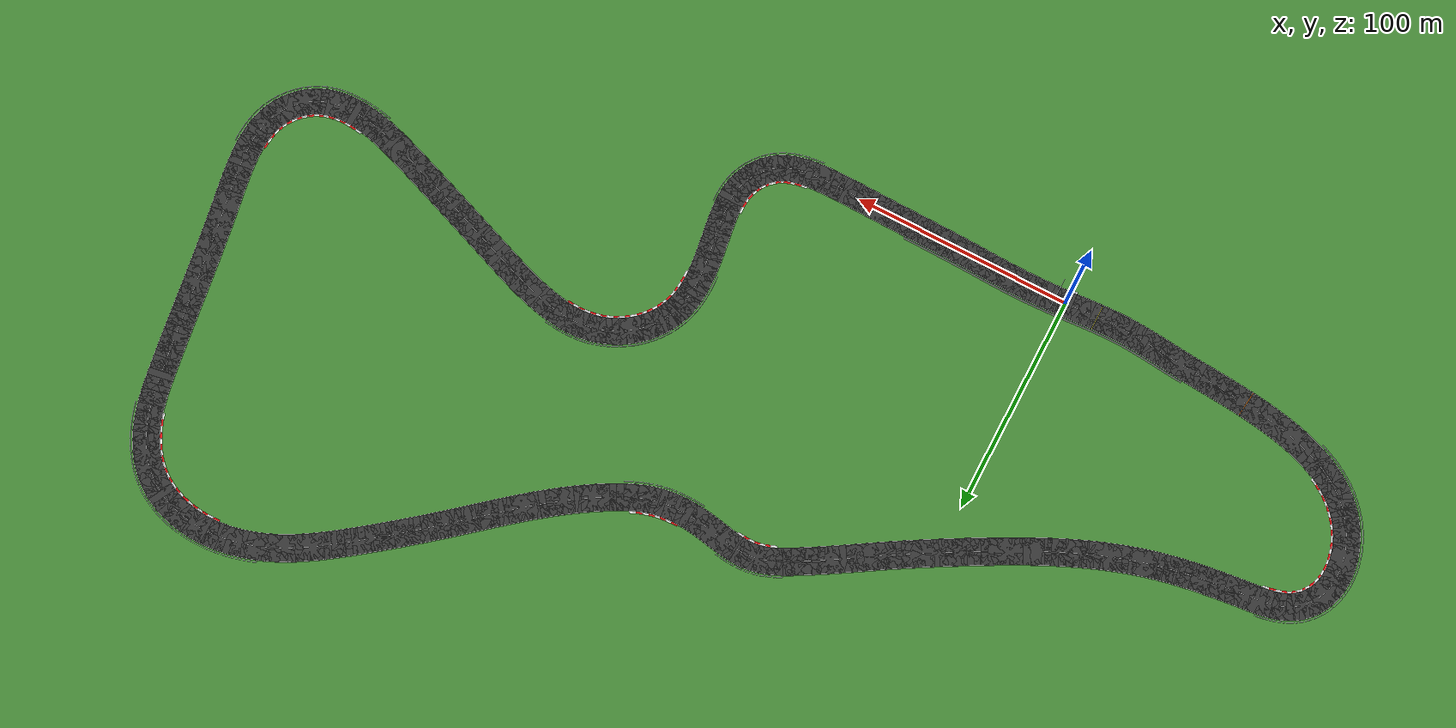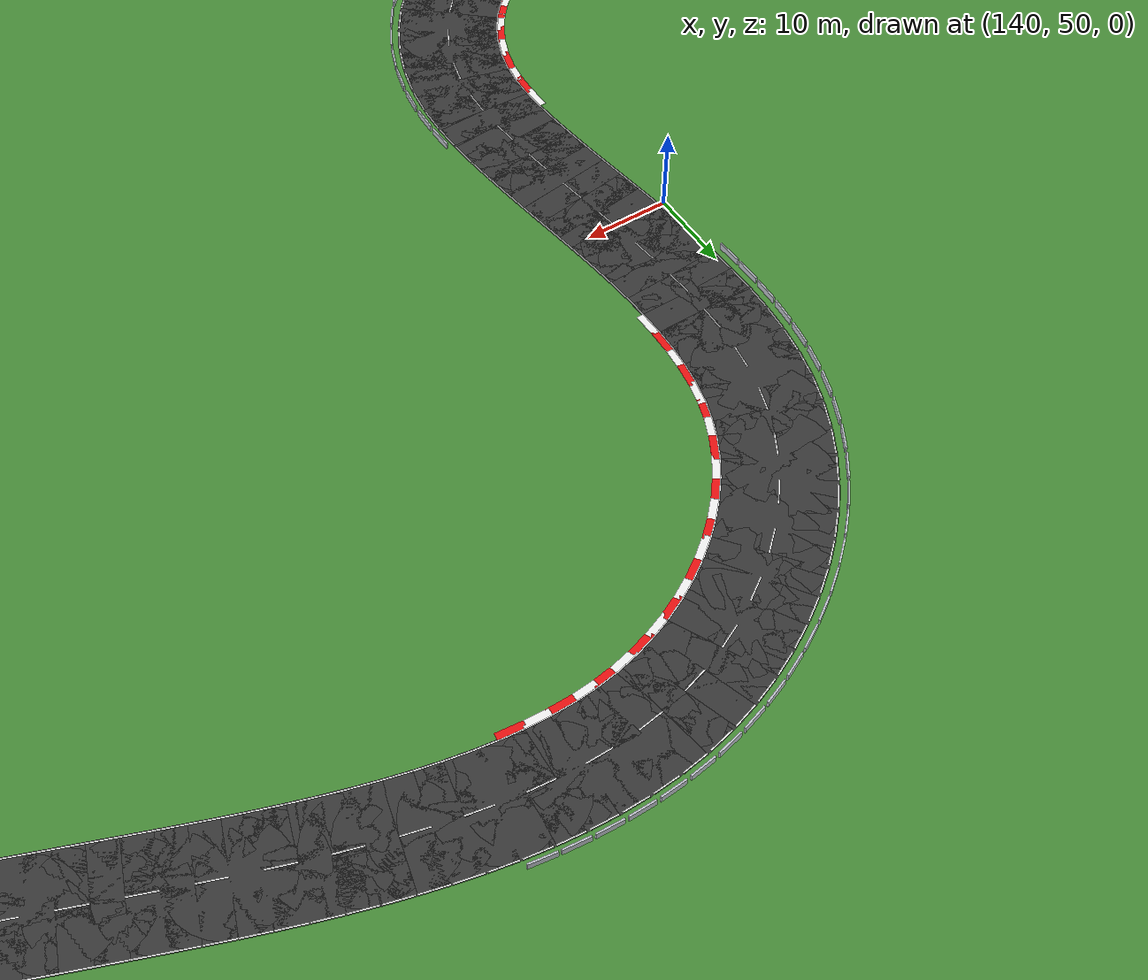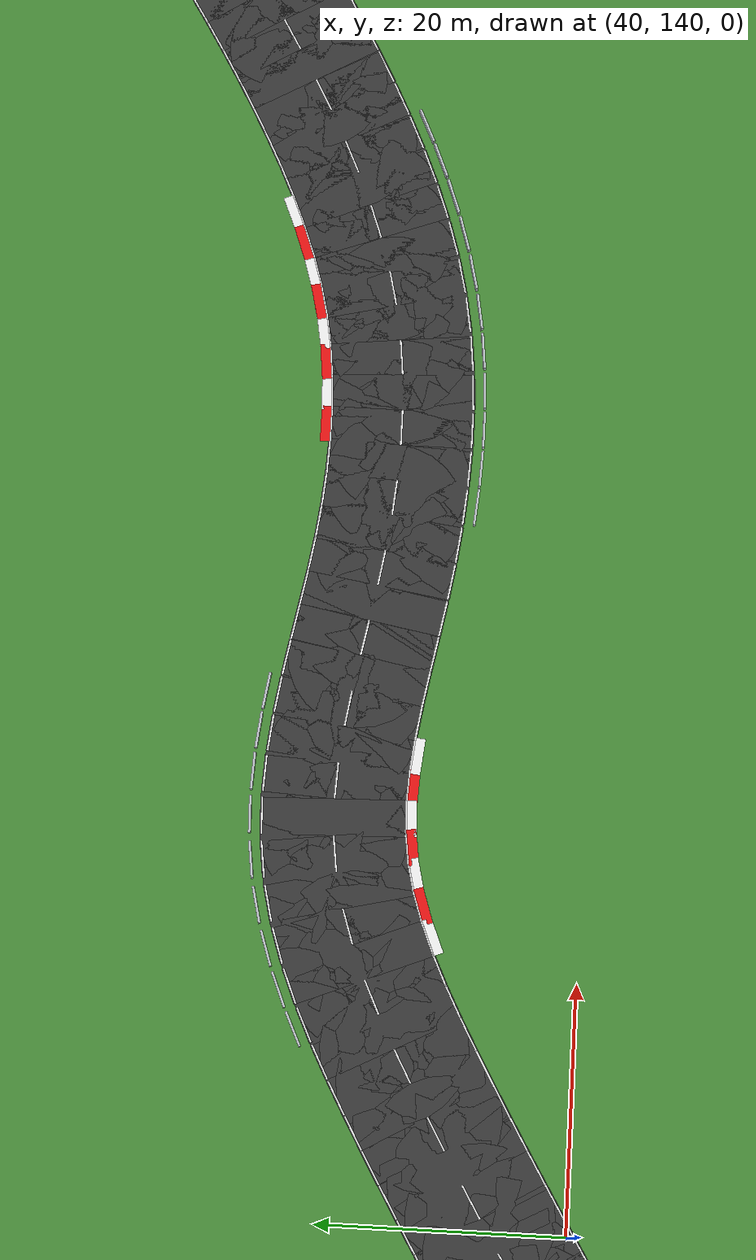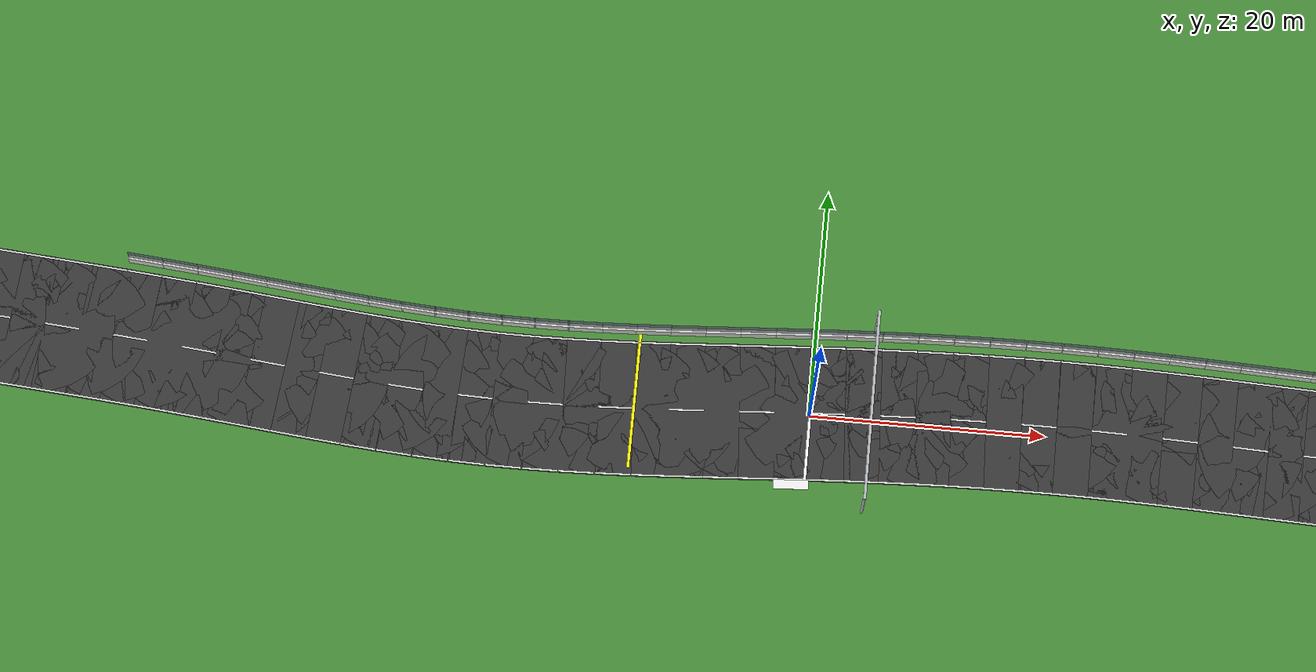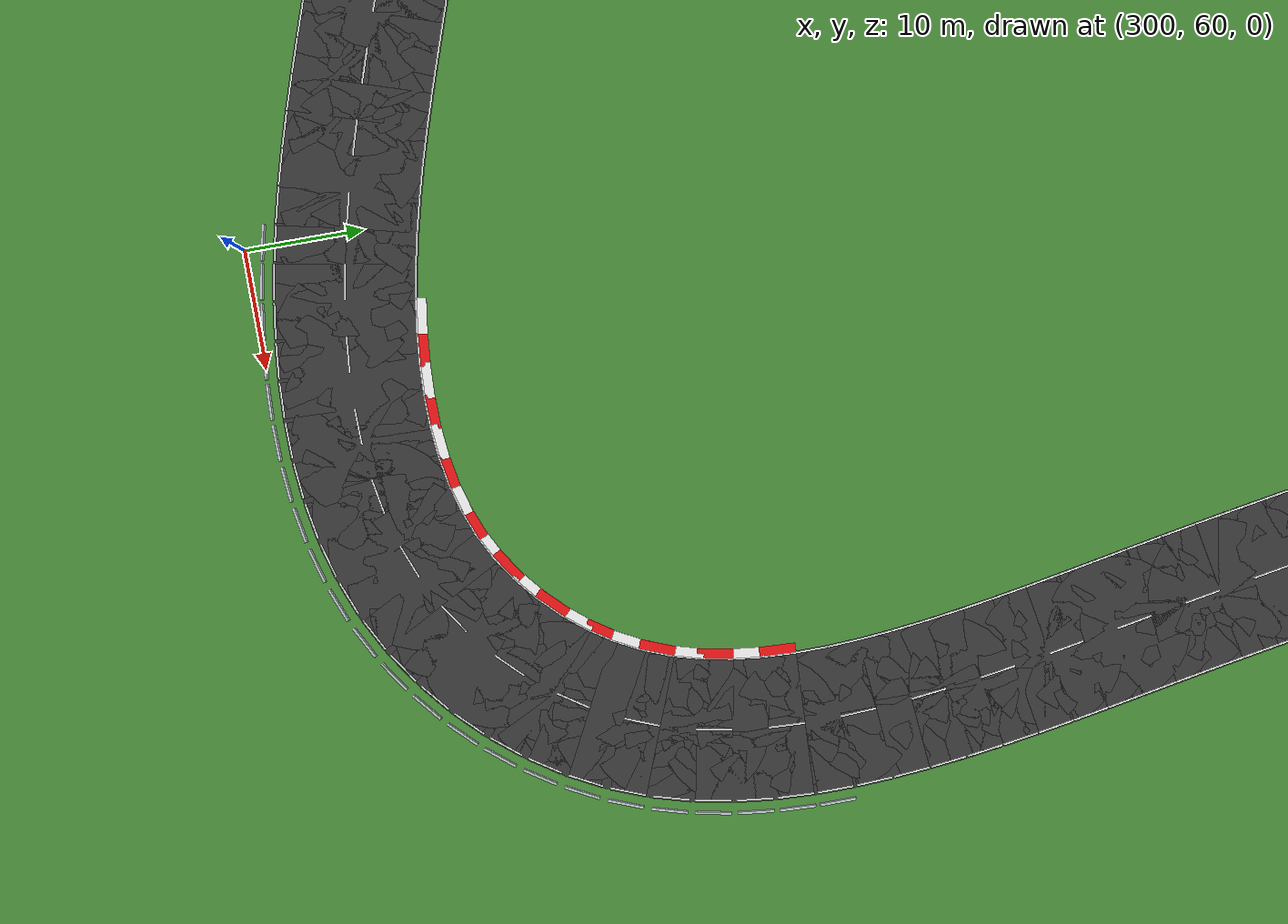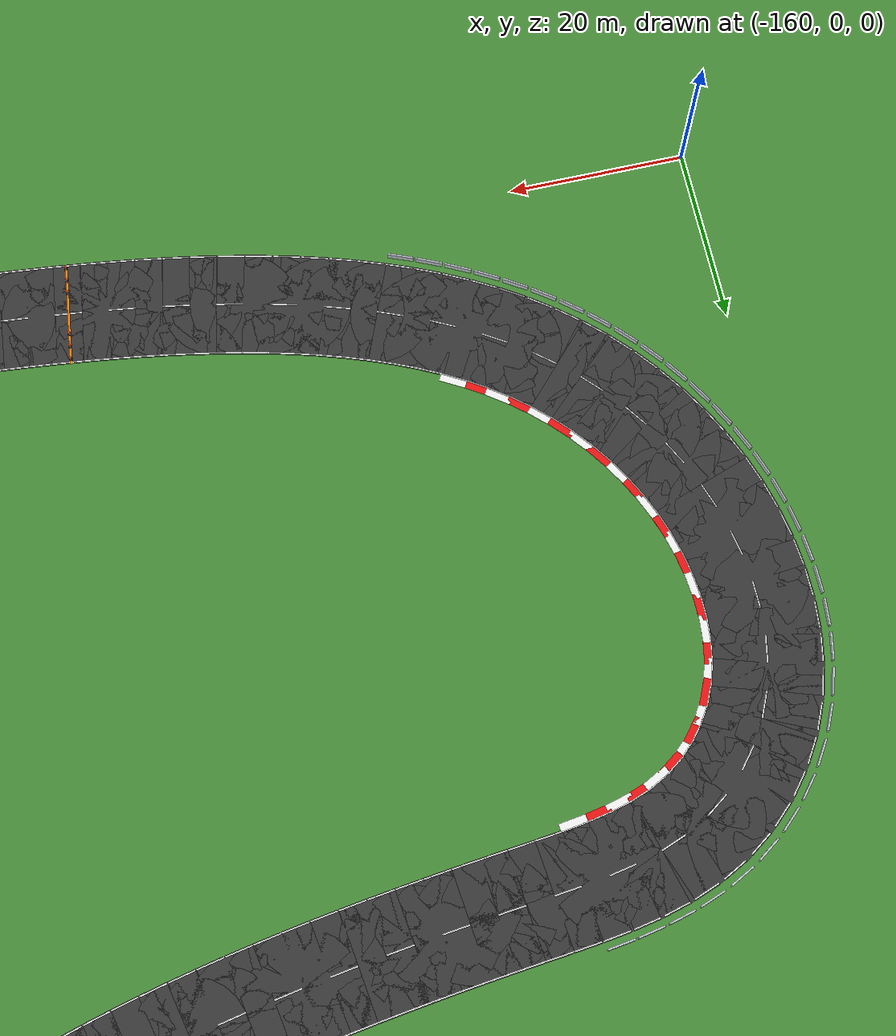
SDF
<?xml version="1.0" ?>
<sdf version="1.6">
  <world name="sem_silesia_ring_2026">

    <physics type="ode">
      <real_time_update_rate>1000</real_time_update_rate>
      <max_step_size>0.001</max_step_size>
      <real_time_factor>1</real_time_factor>
    </physics>
    <gravity>0 0 -9.81</gravity>

    <!-- Realistic Morning Sun (Silesia Ring Reference) -->
    <light name="sun" type="directional">
      <cast_shadows>true</cast_shadows>
      <pose>0 0 250 0 0 0</pose>
      <diffuse>0.92 0.90 0.85 1</diffuse>
      <specular>0.15 0.15 0.15 1</specular>
      <direction>-0.4 0.3 -0.85</direction>
    </light>
    <light name="fill" type="directional">
      <cast_shadows>false</cast_shadows>
      <pose>0 0 100 0 0 0</pose>
      <diffuse>0.50 0.53 0.58 1</diffuse>
      <specular>0 0 0 1</specular>
      <direction>0 0 -1</direction>
    </light>

    <!-- Silesia Ring Grass Ground Plane -->
    <model name="ground_plane">
      <static>true</static>
      <link name="link">
        <collision name="collision">
          <geometry><plane><normal>0 0 1</normal><size>1200 1200</size></plane></geometry>
          <surface><friction><ode><mu>0.6</mu><mu2>0.6</mu2></ode></friction></surface>
        </collision>
        <visual name="visual">
          <geometry><plane><normal>0 0 1</normal><size>1200 1200</size></plane></geometry>
          <material>
            <ambient>0.28 0.55 0.22 1</ambient>
            <diffuse>0.28 0.55 0.22 1</diffuse>
          </material>
        </visual>
      </link>
    </model>

    <model name="road_s0">
      <static>true</static>
      <pose>1.4680 0.3103 0.0030 0 0 0.0594</pose>
      <link name="link">
        <visual name="v">
          <geometry><box><size>3.0025 12.0000 0.0060</size></box></geometry>
          <material><ambient>0.22 0.22 0.22 1</ambient><diffuse>0.22 0.22 0.22 1</diffuse></material>
        </visual>
        <collision name="c">
          <geometry><box><size>3.0025 12.0000 0.0060</size></box></geometry>
          <surface><friction><ode><mu>0.9</mu><mu2>0.9</mu2></ode></friction></surface>
        </collision>
      </link>
    </model>
    <model name="road_jnt0">
      <static>true</static>
      <pose>-0.0306 0.2212 0.0030 0 0 0</pose>
      <link name="link">
        <visual name="v">
          <geometry><cylinder><radius>6.0000</radius><length>0.0060</length></cylinder></geometry>
          <material><ambient>0.22 0.22 0.22 1</ambient><diffuse>0.22 0.22 0.22 1</diffuse></material>
        </visual>
        <collision name="c">
          <geometry><cylinder><radius>6.0000</radius><length>0.0060</length></cylinder></geometry>
          <surface><friction><ode><mu>0.9</mu><mu2>0.9</mu2></ode></friction></surface>
        </collision>
      </link>
    </model>
    <model name="wl_L_s0">
      <static>true</static>
      <pose>1.1208 6.1500 0.0070 0 0 0.0594</pose>
      <link name="link">
        <visual name="v">
          <geometry><box><size>3.0025 0.1500 0.0080</size></box></geometry>
          <material><ambient>0.95 0.95 0.95 1</ambient><diffuse>0.95 0.95 0.95 1</diffuse></material>
        </visual>
      </link>
    </model>
    <model name="wl_R_s0">
      <static>true</static>
      <pose>1.8152 -5.5294 0.0070 0 0 0.0594</pose>
      <link name="link">
        <visual name="v">
          <geometry><box><size>3.0025 0.1500 0.0080</size></box></geometry>
          <material><ambient>0.95 0.95 0.95 1</ambient><diffuse>0.95 0.95 0.95 1</diffuse></material>
        </visual>
      </link>
    </model>
    <model name="cd_s0">
      <static>true</static>
      <pose>1.4680 0.3103 0.0070 0 0 0.0594</pose>
      <link name="link">
        <visual name="v">
          <geometry><box><size>3.0025 0.1500 0.0080</size></box></geometry>
          <material><ambient>0.95 0.95 0.95 1</ambient><diffuse>0.95 0.95 0.95 1</diffuse></material>
        </visual>
      </link>
    </model>
    <model name="road_s1">
      <static>true</static>
      <pose>4.4658 0.4782 0.0030 0 0 0.0526</pose>
      <link name="link">
        <visual name="v">
          <geometry><box><size>3.0025 12.0000 0.0060</size></box></geometry>
          <material><ambient>0.22 0.22 0.22 1</ambient><diffuse>0.22 0.22 0.22 1</diffuse></material>
        </visual>
        <collision name="c">
          <geometry><box><size>3.0025 12.0000 0.0060</size></box></geometry>
          <surface><friction><ode><mu>0.9</mu><mu2>0.9</mu2></ode></friction></surface>
        </collision>
      </link>
    </model>
    <model name="road_jnt1">
      <static>true</static>
      <pose>2.9666 0.3994 0.0030 0 0 0</pose>
      <link name="link">
        <visual name="v">
          <geometry><cylinder><radius>6.0000</radius><length>0.0060</length></cylinder></geometry>
          <material><ambient>0.22 0.22 0.22 1</ambient><diffuse>0.22 0.22 0.22 1</diffuse></material>
        </visual>
        <collision name="c">
          <geometry><cylinder><radius>6.0000</radius><length>0.0060</length></cylinder></geometry>
          <surface><friction><ode><mu>0.9</mu><mu2>0.9</mu2></ode></friction></surface>
        </collision>
      </link>
    </model>
    <model name="wl_L_s1">
      <static>true</static>
      <pose>4.1585 6.3202 0.0070 0 0 0.0526</pose>
      <link name="link">
        <visual name="v">
          <geometry><box><size>3.0025 0.1500 0.0080</size></box></geometry>
          <material><ambient>0.95 0.95 0.95 1</ambient><diffuse>0.95 0.95 0.95 1</diffuse></material>
        </visual>
      </link>
    </model>
    <model name="wl_R_s1">
      <static>true</static>
      <pose>4.7732 -5.3637 0.0070 0 0 0.0526</pose>
      <link name="link">
        <visual name="v">
          <geometry><box><size>3.0025 0.1500 0.0080</size></box></geometry>
          <material><ambient>0.95 0.95 0.95 1</ambient><diffuse>0.95 0.95 0.95 1</diffuse></material>
        </visual>
      </link>
    </model>
    <model name="road_s2">
      <static>true</static>
      <pose>7.4648 0.6246 0.0030 0 0 0.0450</pose>
      <link name="link">
        <visual name="v">
          <geometry><box><size>3.0025 12.0000 0.0060</size></box></geometry>
          <material><ambient>0.22 0.22 0.22 1</ambient><diffuse>0.22 0.22 0.22 1</diffuse></material>
        </visual>
        <collision name="c">
          <geometry><box><size>3.0025 12.0000 0.0060</size></box></geometry>
          <surface><friction><ode><mu>0.9</mu><mu2>0.9</mu2></ode></friction></surface>
        </collision>
      </link>
    </model>
    <model name="road_jnt2">
      <static>true</static>
      <pose>5.9650 0.5571 0.0030 0 0 0</pose>
      <link name="link">
        <visual name="v">
          <geometry><cylinder><radius>6.0000</radius><length>0.0060</length></cylinder></geometry>
          <material><ambient>0.22 0.22 0.22 1</ambient><diffuse>0.22 0.22 0.22 1</diffuse></material>
        </visual>
        <collision name="c">
          <geometry><cylinder><radius>6.0000</radius><length>0.0060</length></cylinder></geometry>
          <surface><friction><ode><mu>0.9</mu><mu2>0.9</mu2></ode></friction></surface>
        </collision>
      </link>
    </model>
    <model name="wl_L_s2">
      <static>true</static>
      <pose>7.2018 6.4687 0.0070 0 0 0.0450</pose>
      <link name="link">
        <visual name="v">
          <geometry><box><size>3.0025 0.1500 0.0080</size></box></geometry>
          <material><ambient>0.95 0.95 0.95 1</ambient><diffuse>0.95 0.95 0.95 1</diffuse></material>
        </visual>
      </link>
    </model>
    <model name="wl_R_s2">
      <static>true</static>
      <pose>7.7277 -5.2195 0.0070 0 0 0.0450</pose>
      <link name="link">
        <visual name="v">
          <geometry><box><size>3.0025 0.1500 0.0080</size></box></geometry>
          <material><ambient>0.95 0.95 0.95 1</ambient><diffuse>0.95 0.95 0.95 1</diffuse></material>
        </visual>
      </link>
    </model>
    <model name="cd_s2">
      <static>true</static>
      <pose>7.4648 0.6246 0.0070 0 0 0.0450</pose>
      <link name="link">
        <visual name="v">
          <geometry><box><size>3.0025 0.1500 0.0080</size></box></geometry>
          <material><ambient>0.95 0.95 0.95 1</ambient><diffuse>0.95 0.95 0.95 1</diffuse></material>
        </visual>
      </link>
    </model>
    <model name="road_s3">
      <static>true</static>
      <pose>10.4648 0.7470 0.0030 0 0 0.0366</pose>
      <link name="link">
        <visual name="v">
          <geometry><box><size>3.0025 12.0000 0.0060</size></box></geometry>
          <material><ambient>0.22 0.22 0.22 1</ambient><diffuse>0.22 0.22 0.22 1</diffuse></material>
        </visual>
        <collision name="c">
          <geometry><box><size>3.0025 12.0000 0.0060</size></box></geometry>
          <surface><friction><ode><mu>0.9</mu><mu2>0.9</mu2></ode></friction></surface>
        </collision>
      </link>
    </model>
    <model name="road_jnt3">
      <static>true</static>
      <pose>8.9645 0.6921 0.0030 0 0 0</pose>
      <link name="link">
        <visual name="v">
          <geometry><cylinder><radius>6.0000</radius><length>0.0060</length></cylinder></geometry>
          <material><ambient>0.22 0.22 0.22 1</ambient><diffuse>0.22 0.22 0.22 1</diffuse></material>
        </visual>
        <collision name="c">
          <geometry><cylinder><radius>6.0000</radius><length>0.0060</length></cylinder></geometry>
          <surface><friction><ode><mu>0.9</mu><mu2>0.9</mu2></ode></friction></surface>
        </collision>
      </link>
    </model>
    <model name="wl_L_s3">
      <static>true</static>
      <pose>10.2509 6.5931 0.0070 0 0 0.0366</pose>
      <link name="link">
        <visual name="v">
          <geometry><box><size>3.0025 0.1500 0.0080</size></box></geometry>
          <material><ambient>0.95 0.95 0.95 1</ambient><diffuse>0.95 0.95 0.95 1</diffuse></material>
        </visual>
      </link>
    </model>
    <model name="wl_R_s3">
      <static>true</static>
      <pose>10.6787 -5.0991 0.0070 0 0 0.0366</pose>
      <link name="link">
        <visual name="v">
          <geometry><box><size>3.0025 0.1500 0.0080</size></box></geometry>
          <material><ambient>0.95 0.95 0.95 1</ambient><diffuse>0.95 0.95 0.95 1</diffuse></material>
        </visual>
      </link>
    </model>
    <model name="road_s4">
      <static>true</static>
      <pose>13.4657 0.8429 0.0030 0 0 0.0274</pose>
      <link name="link">
        <visual name="v">
          <geometry><box><size>3.0025 12.0000 0.0060</size></box></geometry>
          <material><ambient>0.22 0.22 0.22 1</ambient><diffuse>0.22 0.22 0.22 1</diffuse></material>
        </visual>
        <collision name="c">
          <geometry><box><size>3.0025 12.0000 0.0060</size></box></geometry>
          <surface><friction><ode><mu>0.9</mu><mu2>0.9</mu2></ode></friction></surface>
        </collision>
      </link>
    </model>
    <model name="road_jnt4">
      <static>true</static>
      <pose>11.9650 0.8019 0.0030 0 0 0</pose>
      <link name="link">
        <visual name="v">
          <geometry><cylinder><radius>6.0000</radius><length>0.0060</length></cylinder></geometry>
          <material><ambient>0.22 0.22 0.22 1</ambient><diffuse>0.22 0.22 0.22 1</diffuse></material>
        </visual>
        <collision name="c">
          <geometry><cylinder><radius>6.0000</radius><length>0.0060</length></cylinder></geometry>
          <surface><friction><ode><mu>0.9</mu><mu2>0.9</mu2></ode></friction></surface>
        </collision>
      </link>
    </model>
    <model name="wl_L_s4">
      <static>true</static>
      <pose>13.3056 6.6907 0.0070 0 0 0.0274</pose>
      <link name="link">
        <visual name="v">
          <geometry><box><size>3.0025 0.1500 0.0080</size></box></geometry>
          <material><ambient>0.95 0.95 0.95 1</ambient><diffuse>0.95 0.95 0.95 1</diffuse></material>
        </visual>
      </link>
    </model>
    <model name="wl_R_s4">
      <static>true</static>
      <pose>13.6258 -5.0049 0.0070 0 0 0.0274</pose>
      <link name="link">
        <visual name="v">
          <geometry><box><size>3.0025 0.1500 0.0080</size></box></geometry>
          <material><ambient>0.95 0.95 0.95 1</ambient><diffuse>0.95 0.95 0.95 1</diffuse></material>
        </visual>
      </link>
    </model>
    <model name="cd_s4">
      <static>true</static>
      <pose>13.4657 0.8429 0.0070 0 0 0.0274</pose>
      <link name="link">
        <visual name="v">
          <geometry><box><size>3.0025 0.1500 0.0080</size></box></geometry>
          <material><ambient>0.95 0.95 0.95 1</ambient><diffuse>0.95 0.95 0.95 1</diffuse></material>
        </visual>
      </link>
    </model>
    <model name="road_s5">
      <static>true</static>
      <pose>16.4675 0.9101 0.0030 0 0 0.0174</pose>
      <link name="link">
        <visual name="v">
          <geometry><box><size>3.0025 12.0000 0.0060</size></box></geometry>
          <material><ambient>0.22 0.22 0.22 1</ambient><diffuse>0.22 0.22 0.22 1</diffuse></material>
        </visual>
        <collision name="c">
          <geometry><box><size>3.0025 12.0000 0.0060</size></box></geometry>
          <surface><friction><ode><mu>0.9</mu><mu2>0.9</mu2></ode></friction></surface>
        </collision>
      </link>
    </model>
    <model name="road_jnt5">
      <static>true</static>
      <pose>14.9664 0.8840 0.0030 0 0 0</pose>
      <link name="link">
        <visual name="v">
          <geometry><cylinder><radius>6.0000</radius><length>0.0060</length></cylinder></geometry>
          <material><ambient>0.22 0.22 0.22 1</ambient><diffuse>0.22 0.22 0.22 1</diffuse></material>
        </visual>
        <collision name="c">
          <geometry><cylinder><radius>6.0000</radius><length>0.0060</length></cylinder></geometry>
          <surface><friction><ode><mu>0.9</mu><mu2>0.9</mu2></ode></friction></surface>
        </collision>
      </link>
    </model>
    <model name="wl_L_s5">
      <static>true</static>
      <pose>16.3660 6.7592 0.0070 0 0 0.0174</pose>
      <link name="link">
        <visual name="v">
          <geometry><box><size>3.0025 0.1500 0.0080</size></box></geometry>
          <material><ambient>0.95 0.95 0.95 1</ambient><diffuse>0.95 0.95 0.95 1</diffuse></material>
        </visual>
      </link>
    </model>
    <model name="wl_R_s5">
      <static>true</static>
      <pose>16.5690 -4.9390 0.0070 0 0 0.0174</pose>
      <link name="link">
        <visual name="v">
          <geometry><box><size>3.0025 0.1500 0.0080</size></box></geometry>
          <material><ambient>0.95 0.95 0.95 1</ambient><diffuse>0.95 0.95 0.95 1</diffuse></material>
        </visual>
      </link>
    </model>
    <model name="road_s6">
      <static>true</static>
      <pose>19.4697 0.9459 0.0030 0 0 0.0065</pose>
      <link name="link">
        <visual name="v">
          <geometry><box><size>3.0025 12.0000 0.0060</size></box></geometry>
          <material><ambient>0.22 0.22 0.22 1</ambient><diffuse>0.22 0.22 0.22 1</diffuse></material>
        </visual>
        <collision name="c">
          <geometry><box><size>3.0025 12.0000 0.0060</size></box></geometry>
          <surface><friction><ode><mu>0.9</mu><mu2>0.9</mu2></ode></friction></surface>
        </collision>
      </link>
    </model>
    <model name="road_jnt6">
      <static>true</static>
      <pose>17.9685 0.9361 0.0030 0 0 0</pose>
      <link name="link">
        <visual name="v">
          <geometry><cylinder><radius>6.0000</radius><length>0.0060</length></cylinder></geometry>
          <material><ambient>0.22 0.22 0.22 1</ambient><diffuse>0.22 0.22 0.22 1</diffuse></material>
        </visual>
        <collision name="c">
          <geometry><cylinder><radius>6.0000</radius><length>0.0060</length></cylinder></geometry>
          <surface><friction><ode><mu>0.9</mu><mu2>0.9</mu2></ode></friction></surface>
        </collision>
      </link>
    </model>
    <model name="wl_L_s6">
      <static>true</static>
      <pose>19.4317 6.7958 0.0070 0 0 0.0065</pose>
      <link name="link">
        <visual name="v">
          <geometry><box><size>3.0025 0.1500 0.0080</size></box></geometry>
          <material><ambient>0.95 0.95 0.95 1</ambient><diffuse>0.95 0.95 0.95 1</diffuse></material>
        </visual>
      </link>
    </model>
    <model name="wl_R_s6">
      <static>true</static>
      <pose>19.5078 -4.9040 0.0070 0 0 0.0065</pose>
      <link name="link">
        <visual name="v">
          <geometry><box><size>3.0025 0.1500 0.0080</size></box></geometry>
          <material><ambient>0.95 0.95 0.95 1</ambient><diffuse>0.95 0.95 0.95 1</diffuse></material>
        </visual>
      </link>
    </model>
    <model name="cd_s6">
      <static>true</static>
      <pose>19.4697 0.9459 0.0070 0 0 0.0065</pose>
      <link name="link">
        <visual name="v">
          <geometry><box><size>3.0025 0.1500 0.0080</size></box></geometry>
          <material><ambient>0.95 0.95 0.95 1</ambient><diffuse>0.95 0.95 0.95 1</diffuse></material>
        </visual>
      </link>
    </model>
    <model name="road_s7">
      <static>true</static>
      <pose>22.4722 0.9483 0.0030 0 0 -0.0049</pose>
      <link name="link">
        <visual name="v">
          <geometry><box><size>3.0025 12.0000 0.0060</size></box></geometry>
          <material><ambient>0.22 0.22 0.22 1</ambient><diffuse>0.22 0.22 0.22 1</diffuse></material>
        </visual>
        <collision name="c">
          <geometry><box><size>3.0025 12.0000 0.0060</size></box></geometry>
          <surface><friction><ode><mu>0.9</mu><mu2>0.9</mu2></ode></friction></surface>
        </collision>
      </link>
    </model>
    <model name="road_jnt7">
      <static>true</static>
      <pose>20.9710 0.9557 0.0030 0 0 0</pose>
      <link name="link">
        <visual name="v">
          <geometry><cylinder><radius>6.0000</radius><length>0.0060</length></cylinder></geometry>
          <material><ambient>0.22 0.22 0.22 1</ambient><diffuse>0.22 0.22 0.22 1</diffuse></material>
        </visual>
        <collision name="c">
          <geometry><cylinder><radius>6.0000</radius><length>0.0060</length></cylinder></geometry>
          <surface><friction><ode><mu>0.9</mu><mu2>0.9</mu2></ode></friction></surface>
        </collision>
      </link>
    </model>
    <model name="wl_L_s7">
      <static>true</static>
      <pose>22.5011 6.7982 0.0070 0 0 -0.0049</pose>
      <link name="link">
        <visual name="v">
          <geometry><box><size>3.0025 0.1500 0.0080</size></box></geometry>
          <material><ambient>0.95 0.95 0.95 1</ambient><diffuse>0.95 0.95 0.95 1</diffuse></material>
        </visual>
      </link>
    </model>
    <model name="wl_R_s7">
      <static>true</static>
      <pose>22.4433 -4.9017 0.0070 0 0 -0.0049</pose>
      <link name="link">
        <visual name="v">
          <geometry><box><size>3.0025 0.1500 0.0080</size></box></geometry>
          <material><ambient>0.95 0.95 0.95 1</ambient><diffuse>0.95 0.95 0.95 1</diffuse></material>
        </visual>
      </link>
    </model>
    <model name="road_s8">
      <static>true</static>
      <pose>25.4745 0.9180 0.0030 0 0 -0.0152</pose>
      <link name="link">
        <visual name="v">
          <geometry><box><size>3.0025 12.0000 0.0060</size></box></geometry>
          <material><ambient>0.22 0.22 0.22 1</ambient><diffuse>0.22 0.22 0.22 1</diffuse></material>
        </visual>
        <collision name="c">
          <geometry><box><size>3.0025 12.0000 0.0060</size></box></geometry>
          <surface><friction><ode><mu>0.9</mu><mu2>0.9</mu2></ode></friction></surface>
        </collision>
      </link>
    </model>
    <model name="road_jnt8">
      <static>true</static>
      <pose>23.9734 0.9408 0.0030 0 0 0</pose>
      <link name="link">
        <visual name="v">
          <geometry><cylinder><radius>6.0000</radius><length>0.0060</length></cylinder></geometry>
          <material><ambient>0.22 0.22 0.22 1</ambient><diffuse>0.22 0.22 0.22 1</diffuse></material>
        </visual>
        <collision name="c">
          <geometry><cylinder><radius>6.0000</radius><length>0.0060</length></cylinder></geometry>
          <surface><friction><ode><mu>0.9</mu><mu2>0.9</mu2></ode></friction></surface>
        </collision>
      </link>
    </model>
    <model name="wl_L_s8">
      <static>true</static>
      <pose>25.5634 6.7674 0.0070 0 0 -0.0152</pose>
      <link name="link">
        <visual name="v">
          <geometry><box><size>3.0025 0.1500 0.0080</size></box></geometry>
          <material><ambient>0.95 0.95 0.95 1</ambient><diffuse>0.95 0.95 0.95 1</diffuse></material>
        </visual>
      </link>
    </model>
    <model name="wl_R_s8">
      <static>true</static>
      <pose>25.3857 -4.9313 0.0070 0 0 -0.0152</pose>
      <link name="link">
        <visual name="v">
          <geometry><box><size>3.0025 0.1500 0.0080</size></box></geometry>
          <material><ambient>0.95 0.95 0.95 1</ambient><diffuse>0.95 0.95 0.95 1</diffuse></material>
        </visual>
      </link>
    </model>
    <model name="cd_s8">
      <static>true</static>
      <pose>25.4745 0.9180 0.0070 0 0 -0.0152</pose>
      <link name="link">
        <visual name="v">
          <geometry><box><size>3.0025 0.1500 0.0080</size></box></geometry>
          <material><ambient>0.95 0.95 0.95 1</ambient><diffuse>0.95 0.95 0.95 1</diffuse></material>
        </visual>
      </link>
    </model>
    <model name="road_s9">
      <static>true</static>
      <pose>28.4765 0.8600 0.0030 0 0 -0.0235</pose>
      <link name="link">
        <visual name="v">
          <geometry><box><size>3.0025 12.0000 0.0060</size></box></geometry>
          <material><ambient>0.22 0.22 0.22 1</ambient><diffuse>0.22 0.22 0.22 1</diffuse></material>
        </visual>
        <collision name="c">
          <geometry><box><size>3.0025 12.0000 0.0060</size></box></geometry>
          <surface><friction><ode><mu>0.9</mu><mu2>0.9</mu2></ode></friction></surface>
        </collision>
      </link>
    </model>
    <model name="road_jnt9">
      <static>true</static>
      <pose>26.9756 0.8953 0.0030 0 0 0</pose>
      <link name="link">
        <visual name="v">
          <geometry><cylinder><radius>6.0000</radius><length>0.0060</length></cylinder></geometry>
          <material><ambient>0.22 0.22 0.22 1</ambient><diffuse>0.22 0.22 0.22 1</diffuse></material>
        </visual>
        <collision name="c">
          <geometry><cylinder><radius>6.0000</radius><length>0.0060</length></cylinder></geometry>
          <surface><friction><ode><mu>0.9</mu><mu2>0.9</mu2></ode></friction></surface>
        </collision>
      </link>
    </model>
    <model name="wl_L_s9">
      <static>true</static>
      <pose>28.6138 6.7084 0.0070 0 0 -0.0235</pose>
      <link name="link">
        <visual name="v">
          <geometry><box><size>3.0025 0.1500 0.0080</size></box></geometry>
          <material><ambient>0.95 0.95 0.95 1</ambient><diffuse>0.95 0.95 0.95 1</diffuse></material>
        </visual>
      </link>
    </model>
    <model name="wl_R_s9">
      <static>true</static>
      <pose>28.3391 -4.9884 0.0070 0 0 -0.0235</pose>
      <link name="link">
        <visual name="v">
          <geometry><box><size>3.0025 0.1500 0.0080</size></box></geometry>
          <material><ambient>0.95 0.95 0.95 1</ambient><diffuse>0.95 0.95 0.95 1</diffuse></material>
        </visual>
      </link>
    </model>
    <model name="road_s10">
      <static>true</static>
      <pose>31.4779 0.7800 0.0030 0 0 -0.0298</pose>
      <link name="link">
        <visual name="v">
          <geometry><box><size>3.0025 12.0000 0.0060</size></box></geometry>
          <material><ambient>0.22 0.22 0.22 1</ambient><diffuse>0.22 0.22 0.22 1</diffuse></material>
        </visual>
        <collision name="c">
          <geometry><box><size>3.0025 12.0000 0.0060</size></box></geometry>
          <surface><friction><ode><mu>0.9</mu><mu2>0.9</mu2></ode></friction></surface>
        </collision>
      </link>
    </model>
    <model name="road_jnt10">
      <static>true</static>
      <pose>29.9773 0.8248 0.0030 0 0 0</pose>
      <link name="link">
        <visual name="v">
          <geometry><cylinder><radius>6.0000</radius><length>0.0060</length></cylinder></geometry>
          <material><ambient>0.22 0.22 0.22 1</ambient><diffuse>0.22 0.22 0.22 1</diffuse></material>
        </visual>
        <collision name="c">
          <geometry><cylinder><radius>6.0000</radius><length>0.0060</length></cylinder></geometry>
          <surface><friction><ode><mu>0.9</mu><mu2>0.9</mu2></ode></friction></surface>
        </collision>
      </link>
    </model>
    <model name="wl_L_s10">
      <static>true</static>
      <pose>31.6522 6.6274 0.0070 0 0 -0.0298</pose>
      <link name="link">
        <visual name="v">
          <geometry><box><size>3.0025 0.1500 0.0080</size></box></geometry>
          <material><ambient>0.95 0.95 0.95 1</ambient><diffuse>0.95 0.95 0.95 1</diffuse></material>
        </visual>
      </link>
    </model>
    <model name="wl_R_s10">
      <static>true</static>
      <pose>31.3036 -5.0674 0.0070 0 0 -0.0298</pose>
      <link name="link">
        <visual name="v">
          <geometry><box><size>3.0025 0.1500 0.0080</size></box></geometry>
          <material><ambient>0.95 0.95 0.95 1</ambient><diffuse>0.95 0.95 0.95 1</diffuse></material>
        </visual>
      </link>
    </model>
    <model name="cd_s10">
      <static>true</static>
      <pose>31.4779 0.7800 0.0070 0 0 -0.0298</pose>
      <link name="link">
        <visual name="v">
          <geometry><box><size>3.0025 0.1500 0.0080</size></box></geometry>
          <material><ambient>0.95 0.95 0.95 1</ambient><diffuse>0.95 0.95 0.95 1</diffuse></material>
        </visual>
      </link>
    </model>
    <model name="road_s11">
      <static>true</static>
      <pose>34.4789 0.6841 0.0030 0 0 -0.0341</pose>
      <link name="link">
        <visual name="v">
          <geometry><box><size>3.0025 12.0000 0.0060</size></box></geometry>
          <material><ambient>0.22 0.22 0.22 1</ambient><diffuse>0.22 0.22 0.22 1</diffuse></material>
        </visual>
        <collision name="c">
          <geometry><box><size>3.0025 12.0000 0.0060</size></box></geometry>
          <surface><friction><ode><mu>0.9</mu><mu2>0.9</mu2></ode></friction></surface>
        </collision>
      </link>
    </model>
    <model name="road_jnt11">
      <static>true</static>
      <pose>32.9785 0.7353 0.0030 0 0 0</pose>
      <link name="link">
        <visual name="v">
          <geometry><cylinder><radius>6.0000</radius><length>0.0060</length></cylinder></geometry>
          <material><ambient>0.22 0.22 0.22 1</ambient><diffuse>0.22 0.22 0.22 1</diffuse></material>
        </visual>
        <collision name="c">
          <geometry><cylinder><radius>6.0000</radius><length>0.0060</length></cylinder></geometry>
          <surface><friction><ode><mu>0.9</mu><mu2>0.9</mu2></ode></friction></surface>
        </collision>
      </link>
    </model>
    <model name="wl_L_s11">
      <static>true</static>
      <pose>34.6785 6.5307 0.0070 0 0 -0.0341</pose>
      <link name="link">
        <visual name="v">
          <geometry><box><size>3.0025 0.1500 0.0080</size></box></geometry>
          <material><ambient>0.95 0.95 0.95 1</ambient><diffuse>0.95 0.95 0.95 1</diffuse></material>
        </visual>
      </link>
    </model>
    <model name="wl_R_s11">
      <static>true</static>
      <pose>34.2794 -5.1625 0.0070 0 0 -0.0341</pose>
      <link name="link">
        <visual name="v">
          <geometry><box><size>3.0025 0.1500 0.0080</size></box></geometry>
          <material><ambient>0.95 0.95 0.95 1</ambient><diffuse>0.95 0.95 0.95 1</diffuse></material>
        </visual>
      </link>
    </model>
    <model name="road_s12">
      <static>true</static>
      <pose>37.4796 0.5782 0.0030 0 0 -0.0365</pose>
      <link name="link">
        <visual name="v">
          <geometry><box><size>3.0025 12.0000 0.0060</size></box></geometry>
          <material><ambient>0.22 0.22 0.22 1</ambient><diffuse>0.22 0.22 0.22 1</diffuse></material>
        </visual>
        <collision name="c">
          <geometry><box><size>3.0025 12.0000 0.0060</size></box></geometry>
          <surface><friction><ode><mu>0.9</mu><mu2>0.9</mu2></ode></friction></surface>
        </collision>
      </link>
    </model>
    <model name="road_jnt12">
      <static>true</static>
      <pose>35.9793 0.6329 0.0030 0 0 0</pose>
      <link name="link">
        <visual name="v">
          <geometry><cylinder><radius>6.0000</radius><length>0.0060</length></cylinder></geometry>
          <material><ambient>0.22 0.22 0.22 1</ambient><diffuse>0.22 0.22 0.22 1</diffuse></material>
        </visual>
        <collision name="c">
          <geometry><cylinder><radius>6.0000</radius><length>0.0060</length></cylinder></geometry>
          <surface><friction><ode><mu>0.9</mu><mu2>0.9</mu2></ode></friction></surface>
        </collision>
      </link>
    </model>
    <model name="wl_L_s12">
      <static>true</static>
      <pose>37.6928 6.4243 0.0070 0 0 -0.0365</pose>
      <link name="link">
        <visual name="v">
          <geometry><box><size>3.0025 0.1500 0.0080</size></box></geometry>
          <material><ambient>0.95 0.95 0.95 1</ambient><diffuse>0.95 0.95 0.95 1</diffuse></material>
        </visual>
      </link>
    </model>
    <model name="wl_R_s12">
      <static>true</static>
      <pose>37.2664 -5.2680 0.0070 0 0 -0.0365</pose>
      <link name="link">
        <visual name="v">
          <geometry><box><size>3.0025 0.1500 0.0080</size></box></geometry>
          <material><ambient>0.95 0.95 0.95 1</ambient><diffuse>0.95 0.95 0.95 1</diffuse></material>
        </visual>
      </link>
    </model>
    <model name="cd_s12">
      <static>true</static>
      <pose>37.4796 0.5782 0.0070 0 0 -0.0365</pose>
      <link name="link">
        <visual name="v">
          <geometry><box><size>3.0025 0.1500 0.0080</size></box></geometry>
          <material><ambient>0.95 0.95 0.95 1</ambient><diffuse>0.95 0.95 0.95 1</diffuse></material>
        </visual>
      </link>
    </model>
    <model name="road_s13">
      <static>true</static>
      <pose>40.4801 0.4682 0.0030 0 0 -0.0368</pose>
      <link name="link">
        <visual name="v">
          <geometry><box><size>3.0025 12.0000 0.0060</size></box></geometry>
          <material><ambient>0.22 0.22 0.22 1</ambient><diffuse>0.22 0.22 0.22 1</diffuse></material>
        </visual>
        <collision name="c">
          <geometry><box><size>3.0025 12.0000 0.0060</size></box></geometry>
          <surface><friction><ode><mu>0.9</mu><mu2>0.9</mu2></ode></friction></surface>
        </collision>
      </link>
    </model>
    <model name="road_jnt13">
      <static>true</static>
      <pose>38.9799 0.5234 0.0030 0 0 0</pose>
      <link name="link">
        <visual name="v">
          <geometry><cylinder><radius>6.0000</radius><length>0.0060</length></cylinder></geometry>
          <material><ambient>0.22 0.22 0.22 1</ambient><diffuse>0.22 0.22 0.22 1</diffuse></material>
        </visual>
        <collision name="c">
          <geometry><cylinder><radius>6.0000</radius><length>0.0060</length></cylinder></geometry>
          <surface><friction><ode><mu>0.9</mu><mu2>0.9</mu2></ode></friction></surface>
        </collision>
      </link>
    </model>
    <model name="wl_L_s13">
      <static>true</static>
      <pose>40.6954 6.3142 0.0070 0 0 -0.0368</pose>
      <link name="link">
        <visual name="v">
          <geometry><box><size>3.0025 0.1500 0.0080</size></box></geometry>
          <material><ambient>0.95 0.95 0.95 1</ambient><diffuse>0.95 0.95 0.95 1</diffuse></material>
        </visual>
      </link>
    </model>
    <model name="wl_R_s13">
      <static>true</static>
      <pose>40.2648 -5.3778 0.0070 0 0 -0.0368</pose>
      <link name="link">
        <visual name="v">
          <geometry><box><size>3.0025 0.1500 0.0080</size></box></geometry>
          <material><ambient>0.95 0.95 0.95 1</ambient><diffuse>0.95 0.95 0.95 1</diffuse></material>
        </visual>
      </link>
    </model>
    <model name="road_s14">
      <static>true</static>
      <pose>43.4807 0.3602 0.0030 0 0 -0.0352</pose>
      <link name="link">
        <visual name="v">
          <geometry><box><size>3.0025 12.0000 0.0060</size></box></geometry>
          <material><ambient>0.22 0.22 0.22 1</ambient><diffuse>0.22 0.22 0.22 1</diffuse></material>
        </visual>
        <collision name="c">
          <geometry><box><size>3.0025 12.0000 0.0060</size></box></geometry>
          <surface><friction><ode><mu>0.9</mu><mu2>0.9</mu2></ode></friction></surface>
        </collision>
      </link>
    </model>
    <model name="road_jnt14">
      <static>true</static>
      <pose>41.9804 0.4130 0.0030 0 0 0</pose>
      <link name="link">
        <visual name="v">
          <geometry><cylinder><radius>6.0000</radius><length>0.0060</length></cylinder></geometry>
          <material><ambient>0.22 0.22 0.22 1</ambient><diffuse>0.22 0.22 0.22 1</diffuse></material>
        </visual>
        <collision name="c">
          <geometry><cylinder><radius>6.0000</radius><length>0.0060</length></cylinder></geometry>
          <surface><friction><ode><mu>0.9</mu><mu2>0.9</mu2></ode></friction></surface>
        </collision>
      </link>
    </model>
    <model name="wl_L_s14">
      <static>true</static>
      <pose>43.6865 6.2065 0.0070 0 0 -0.0352</pose>
      <link name="link">
        <visual name="v">
          <geometry><box><size>3.0025 0.1500 0.0080</size></box></geometry>
          <material><ambient>0.95 0.95 0.95 1</ambient><diffuse>0.95 0.95 0.95 1</diffuse></material>
        </visual>
      </link>
    </model>
    <model name="wl_R_s14">
      <static>true</static>
      <pose>43.2749 -5.4862 0.0070 0 0 -0.0352</pose>
      <link name="link">
        <visual name="v">
          <geometry><box><size>3.0025 0.1500 0.0080</size></box></geometry>
          <material><ambient>0.95 0.95 0.95 1</ambient><diffuse>0.95 0.95 0.95 1</diffuse></material>
        </visual>
      </link>
    </model>
    <model name="cd_s14">
      <static>true</static>
      <pose>43.4807 0.3602 0.0070 0 0 -0.0352</pose>
      <link name="link">
        <visual name="v">
          <geometry><box><size>3.0025 0.1500 0.0080</size></box></geometry>
          <material><ambient>0.95 0.95 0.95 1</ambient><diffuse>0.95 0.95 0.95 1</diffuse></material>
        </visual>
      </link>
    </model>
    <model name="road_s15">
      <static>true</static>
      <pose>46.4815 0.2595 0.0030 0 0 -0.0319</pose>
      <link name="link">
        <visual name="v">
          <geometry><box><size>3.0025 12.0000 0.0060</size></box></geometry>
          <material><ambient>0.22 0.22 0.22 1</ambient><diffuse>0.22 0.22 0.22 1</diffuse></material>
        </visual>
        <collision name="c">
          <geometry><box><size>3.0025 12.0000 0.0060</size></box></geometry>
          <surface><friction><ode><mu>0.9</mu><mu2>0.9</mu2></ode></friction></surface>
        </collision>
      </link>
    </model>
    <model name="road_jnt15">
      <static>true</static>
      <pose>44.9810 0.3073 0.0030 0 0 0</pose>
      <link name="link">
        <visual name="v">
          <geometry><cylinder><radius>6.0000</radius><length>0.0060</length></cylinder></geometry>
          <material><ambient>0.22 0.22 0.22 1</ambient><diffuse>0.22 0.22 0.22 1</diffuse></material>
        </visual>
        <collision name="c">
          <geometry><cylinder><radius>6.0000</radius><length>0.0060</length></cylinder></geometry>
          <surface><friction><ode><mu>0.9</mu><mu2>0.9</mu2></ode></friction></surface>
        </collision>
      </link>
    </model>
    <model name="wl_L_s15">
      <static>true</static>
      <pose>46.6679 6.1066 0.0070 0 0 -0.0319</pose>
      <link name="link">
        <visual name="v">
          <geometry><box><size>3.0025 0.1500 0.0080</size></box></geometry>
          <material><ambient>0.95 0.95 0.95 1</ambient><diffuse>0.95 0.95 0.95 1</diffuse></material>
        </visual>
      </link>
    </model>
    <model name="wl_R_s15">
      <static>true</static>
      <pose>46.2952 -5.5875 0.0070 0 0 -0.0319</pose>
      <link name="link">
        <visual name="v">
          <geometry><box><size>3.0025 0.1500 0.0080</size></box></geometry>
          <material><ambient>0.95 0.95 0.95 1</ambient><diffuse>0.95 0.95 0.95 1</diffuse></material>
        </visual>
      </link>
    </model>
    <model name="road_s16">
      <static>true</static>
      <pose>49.4827 0.1691 0.0030 0 0 -0.0284</pose>
      <link name="link">
        <visual name="v">
          <geometry><box><size>3.0025 12.0000 0.0060</size></box></geometry>
          <material><ambient>0.22 0.22 0.22 1</ambient><diffuse>0.22 0.22 0.22 1</diffuse></material>
        </visual>
        <collision name="c">
          <geometry><box><size>3.0025 12.0000 0.0060</size></box></geometry>
          <surface><friction><ode><mu>0.9</mu><mu2>0.9</mu2></ode></friction></surface>
        </collision>
      </link>
    </model>
    <model name="road_jnt16">
      <static>true</static>
      <pose>47.9820 0.2117 0.0030 0 0 0</pose>
      <link name="link">
        <visual name="v">
          <geometry><cylinder><radius>6.0000</radius><length>0.0060</length></cylinder></geometry>
          <material><ambient>0.22 0.22 0.22 1</ambient><diffuse>0.22 0.22 0.22 1</diffuse></material>
        </visual>
        <collision name="c">
          <geometry><cylinder><radius>6.0000</radius><length>0.0060</length></cylinder></geometry>
          <surface><friction><ode><mu>0.9</mu><mu2>0.9</mu2></ode></friction></surface>
        </collision>
      </link>
    </model>
    <model name="wl_L_s16">
      <static>true</static>
      <pose>49.6488 6.0167 0.0070 0 0 -0.0284</pose>
      <link name="link">
        <visual name="v">
          <geometry><box><size>3.0025 0.1500 0.0080</size></box></geometry>
          <material><ambient>0.95 0.95 0.95 1</ambient><diffuse>0.95 0.95 0.95 1</diffuse></material>
        </visual>
      </link>
    </model>
    <model name="wl_R_s16">
      <static>true</static>
      <pose>49.3167 -5.6786 0.0070 0 0 -0.0284</pose>
      <link name="link">
        <visual name="v">
          <geometry><box><size>3.0025 0.1500 0.0080</size></box></geometry>
          <material><ambient>0.95 0.95 0.95 1</ambient><diffuse>0.95 0.95 0.95 1</diffuse></material>
        </visual>
      </link>
    </model>
    <model name="cd_s16">
      <static>true</static>
      <pose>49.4827 0.1691 0.0070 0 0 -0.0284</pose>
      <link name="link">
        <visual name="v">
          <geometry><box><size>3.0025 0.1500 0.0080</size></box></geometry>
          <material><ambient>0.95 0.95 0.95 1</ambient><diffuse>0.95 0.95 0.95 1</diffuse></material>
        </visual>
      </link>
    </model>
    <model name="road_s17">
      <static>true</static>
      <pose>52.4842 0.0885 0.0030 0 0 -0.0253</pose>
      <link name="link">
        <visual name="v">
          <geometry><box><size>3.0025 12.0000 0.0060</size></box></geometry>
          <material><ambient>0.22 0.22 0.22 1</ambient><diffuse>0.22 0.22 0.22 1</diffuse></material>
        </visual>
        <collision name="c">
          <geometry><box><size>3.0025 12.0000 0.0060</size></box></geometry>
          <surface><friction><ode><mu>0.9</mu><mu2>0.9</mu2></ode></friction></surface>
        </collision>
      </link>
    </model>
    <model name="road_jnt17">
      <static>true</static>
      <pose>50.9834 0.1265 0.0030 0 0 0</pose>
      <link name="link">
        <visual name="v">
          <geometry><cylinder><radius>6.0000</radius><length>0.0060</length></cylinder></geometry>
          <material><ambient>0.22 0.22 0.22 1</ambient><diffuse>0.22 0.22 0.22 1</diffuse></material>
        </visual>
        <collision name="c">
          <geometry><cylinder><radius>6.0000</radius><length>0.0060</length></cylinder></geometry>
          <surface><friction><ode><mu>0.9</mu><mu2>0.9</mu2></ode></friction></surface>
        </collision>
      </link>
    </model>
    <model name="wl_L_s17">
      <static>true</static>
      <pose>52.6322 5.9366 0.0070 0 0 -0.0253</pose>
      <link name="link">
        <visual name="v">
          <geometry><box><size>3.0025 0.1500 0.0080</size></box></geometry>
          <material><ambient>0.95 0.95 0.95 1</ambient><diffuse>0.95 0.95 0.95 1</diffuse></material>
        </visual>
      </link>
    </model>
    <model name="wl_R_s17">
      <static>true</static>
      <pose>52.3361 -5.7597 0.0070 0 0 -0.0253</pose>
      <link name="link">
        <visual name="v">
          <geometry><box><size>3.0025 0.1500 0.0080</size></box></geometry>
          <material><ambient>0.95 0.95 0.95 1</ambient><diffuse>0.95 0.95 0.95 1</diffuse></material>
        </visual>
      </link>
    </model>
    <model name="road_s18">
      <static>true</static>
      <pose>55.4858 0.0165 0.0030 0 0 -0.0226</pose>
      <link name="link">
        <visual name="v">
          <geometry><box><size>3.0025 12.0000 0.0060</size></box></geometry>
          <material><ambient>0.22 0.22 0.22 1</ambient><diffuse>0.22 0.22 0.22 1</diffuse></material>
        </visual>
        <collision name="c">
          <geometry><box><size>3.0025 12.0000 0.0060</size></box></geometry>
          <surface><friction><ode><mu>0.9</mu><mu2>0.9</mu2></ode></friction></surface>
        </collision>
      </link>
    </model>
    <model name="road_jnt18">
      <static>true</static>
      <pose>53.9849 0.0505 0.0030 0 0 0</pose>
      <link name="link">
        <visual name="v">
          <geometry><cylinder><radius>6.0000</radius><length>0.0060</length></cylinder></geometry>
          <material><ambient>0.22 0.22 0.22 1</ambient><diffuse>0.22 0.22 0.22 1</diffuse></material>
        </visual>
        <collision name="c">
          <geometry><cylinder><radius>6.0000</radius><length>0.0060</length></cylinder></geometry>
          <surface><friction><ode><mu>0.9</mu><mu2>0.9</mu2></ode></friction></surface>
        </collision>
      </link>
    </model>
    <model name="wl_L_s18">
      <static>true</static>
      <pose>55.6182 5.8650 0.0070 0 0 -0.0226</pose>
      <link name="link">
        <visual name="v">
          <geometry><box><size>3.0025 0.1500 0.0080</size></box></geometry>
          <material><ambient>0.95 0.95 0.95 1</ambient><diffuse>0.95 0.95 0.95 1</diffuse></material>
        </visual>
      </link>
    </model>
    <model name="wl_R_s18">
      <static>true</static>
      <pose>55.3534 -5.8320 0.0070 0 0 -0.0226</pose>
      <link name="link">
        <visual name="v">
          <geometry><box><size>3.0025 0.1500 0.0080</size></box></geometry>
          <material><ambient>0.95 0.95 0.95 1</ambient><diffuse>0.95 0.95 0.95 1</diffuse></material>
        </visual>
      </link>
    </model>
    <model name="cd_s18">
      <static>true</static>
      <pose>55.4858 0.0165 0.0070 0 0 -0.0226</pose>
      <link name="link">
        <visual name="v">
          <geometry><box><size>3.0025 0.1500 0.0080</size></box></geometry>
          <material><ambient>0.95 0.95 0.95 1</ambient><diffuse>0.95 0.95 0.95 1</diffuse></material>
        </visual>
      </link>
    </model>
    <model name="road_s19">
      <static>true</static>
      <pose>58.4877 -0.0480 0.0030 0 0 -0.0203</pose>
      <link name="link">
        <visual name="v">
          <geometry><box><size>3.0025 12.0000 0.0060</size></box></geometry>
          <material><ambient>0.22 0.22 0.22 1</ambient><diffuse>0.22 0.22 0.22 1</diffuse></material>
        </visual>
        <collision name="c">
          <geometry><box><size>3.0025 12.0000 0.0060</size></box></geometry>
          <surface><friction><ode><mu>0.9</mu><mu2>0.9</mu2></ode></friction></surface>
        </collision>
      </link>
    </model>
    <model name="road_jnt19">
      <static>true</static>
      <pose>56.9867 -0.0175 0.0030 0 0 0</pose>
      <link name="link">
        <visual name="v">
          <geometry><cylinder><radius>6.0000</radius><length>0.0060</length></cylinder></geometry>
          <material><ambient>0.22 0.22 0.22 1</ambient><diffuse>0.22 0.22 0.22 1</diffuse></material>
        </visual>
        <collision name="c">
          <geometry><cylinder><radius>6.0000</radius><length>0.0060</length></cylinder></geometry>
          <surface><friction><ode><mu>0.9</mu><mu2>0.9</mu2></ode></friction></surface>
        </collision>
      </link>
    </model>
    <model name="wl_L_s19">
      <static>true</static>
      <pose>58.6067 5.8008 0.0070 0 0 -0.0203</pose>
      <link name="link">
        <visual name="v">
          <geometry><box><size>3.0025 0.1500 0.0080</size></box></geometry>
          <material><ambient>0.95 0.95 0.95 1</ambient><diffuse>0.95 0.95 0.95 1</diffuse></material>
        </visual>
      </link>
    </model>
    <model name="wl_R_s19">
      <static>true</static>
      <pose>58.3687 -5.8968 0.0070 0 0 -0.0203</pose>
      <link name="link">
        <visual name="v">
          <geometry><box><size>3.0025 0.1500 0.0080</size></box></geometry>
          <material><ambient>0.95 0.95 0.95 1</ambient><diffuse>0.95 0.95 0.95 1</diffuse></material>
        </visual>
      </link>
    </model>
    <model name="road_s20">
      <static>true</static>
      <pose>61.4896 -0.1063 0.0030 0 0 -0.0184</pose>
      <link name="link">
        <visual name="v">
          <geometry><box><size>3.0025 12.0000 0.0060</size></box></geometry>
          <material><ambient>0.22 0.22 0.22 1</ambient><diffuse>0.22 0.22 0.22 1</diffuse></material>
        </visual>
        <collision name="c">
          <geometry><box><size>3.0025 12.0000 0.0060</size></box></geometry>
          <surface><friction><ode><mu>0.9</mu><mu2>0.9</mu2></ode></friction></surface>
        </collision>
      </link>
    </model>
    <model name="road_jnt20">
      <static>true</static>
      <pose>59.9886 -0.0786 0.0030 0 0 0</pose>
      <link name="link">
        <visual name="v">
          <geometry><cylinder><radius>6.0000</radius><length>0.0060</length></cylinder></geometry>
          <material><ambient>0.22 0.22 0.22 1</ambient><diffuse>0.22 0.22 0.22 1</diffuse></material>
        </visual>
        <collision name="c">
          <geometry><cylinder><radius>6.0000</radius><length>0.0060</length></cylinder></geometry>
          <surface><friction><ode><mu>0.9</mu><mu2>0.9</mu2></ode></friction></surface>
        </collision>
      </link>
    </model>
    <model name="wl_L_s20">
      <static>true</static>
      <pose>61.5975 5.7427 0.0070 0 0 -0.0184</pose>
      <link name="link">
        <visual name="v">
          <geometry><box><size>3.0025 0.1500 0.0080</size></box></geometry>
          <material><ambient>0.95 0.95 0.95 1</ambient><diffuse>0.95 0.95 0.95 1</diffuse></material>
        </visual>
      </link>
    </model>
    <model name="wl_R_s20">
      <static>true</static>
      <pose>61.3818 -5.9553 0.0070 0 0 -0.0184</pose>
      <link name="link">
        <visual name="v">
          <geometry><box><size>3.0025 0.1500 0.0080</size></box></geometry>
          <material><ambient>0.95 0.95 0.95 1</ambient><diffuse>0.95 0.95 0.95 1</diffuse></material>
        </visual>
      </link>
    </model>
    <model name="cd_s20">
      <static>true</static>
      <pose>61.4896 -0.1063 0.0070 0 0 -0.0184</pose>
      <link name="link">
        <visual name="v">
          <geometry><box><size>3.0025 0.1500 0.0080</size></box></geometry>
          <material><ambient>0.95 0.95 0.95 1</ambient><diffuse>0.95 0.95 0.95 1</diffuse></material>
        </visual>
      </link>
    </model>
    <model name="road_s21">
      <static>true</static>
      <pose>64.4917 -0.1593 0.0030 0 0 -0.0169</pose>
      <link name="link">
        <visual name="v">
          <geometry><box><size>3.0025 12.0000 0.0060</size></box></geometry>
          <material><ambient>0.22 0.22 0.22 1</ambient><diffuse>0.22 0.22 0.22 1</diffuse></material>
        </visual>
        <collision name="c">
          <geometry><box><size>3.0025 12.0000 0.0060</size></box></geometry>
          <surface><friction><ode><mu>0.9</mu><mu2>0.9</mu2></ode></friction></surface>
        </collision>
      </link>
    </model>
    <model name="road_jnt21">
      <static>true</static>
      <pose>62.9907 -0.1339 0.0030 0 0 0</pose>
      <link name="link">
        <visual name="v">
          <geometry><cylinder><radius>6.0000</radius><length>0.0060</length></cylinder></geometry>
          <material><ambient>0.22 0.22 0.22 1</ambient><diffuse>0.22 0.22 0.22 1</diffuse></material>
        </visual>
        <collision name="c">
          <geometry><cylinder><radius>6.0000</radius><length>0.0060</length></cylinder></geometry>
          <surface><friction><ode><mu>0.9</mu><mu2>0.9</mu2></ode></friction></surface>
        </collision>
      </link>
    </model>
    <model name="wl_L_s21">
      <static>true</static>
      <pose>64.5907 5.6898 0.0070 0 0 -0.0169</pose>
      <link name="link">
        <visual name="v">
          <geometry><box><size>3.0025 0.1500 0.0080</size></box></geometry>
          <material><ambient>0.95 0.95 0.95 1</ambient><diffuse>0.95 0.95 0.95 1</diffuse></material>
        </visual>
      </link>
    </model>
    <model name="wl_R_s21">
      <static>true</static>
      <pose>64.3927 -6.0085 0.0070 0 0 -0.0169</pose>
      <link name="link">
        <visual name="v">
          <geometry><box><size>3.0025 0.1500 0.0080</size></box></geometry>
          <material><ambient>0.95 0.95 0.95 1</ambient><diffuse>0.95 0.95 0.95 1</diffuse></material>
        </visual>
      </link>
    </model>
    <model name="road_s22">
      <static>true</static>
      <pose>67.4938 -0.2084 0.0030 0 0 -0.0158</pose>
      <link name="link">
        <visual name="v">
          <geometry><box><size>3.0025 12.0000 0.0060</size></box></geometry>
          <material><ambient>0.22 0.22 0.22 1</ambient><diffuse>0.22 0.22 0.22 1</diffuse></material>
        </visual>
        <collision name="c">
          <geometry><box><size>3.0025 12.0000 0.0060</size></box></geometry>
          <surface><friction><ode><mu>0.9</mu><mu2>0.9</mu2></ode></friction></surface>
        </collision>
      </link>
    </model>
    <model name="road_jnt22">
      <static>true</static>
      <pose>65.9928 -0.1847 0.0030 0 0 0</pose>
      <link name="link">
        <visual name="v">
          <geometry><cylinder><radius>6.0000</radius><length>0.0060</length></cylinder></geometry>
          <material><ambient>0.22 0.22 0.22 1</ambient><diffuse>0.22 0.22 0.22 1</diffuse></material>
        </visual>
        <collision name="c">
          <geometry><cylinder><radius>6.0000</radius><length>0.0060</length></cylinder></geometry>
          <surface><friction><ode><mu>0.9</mu><mu2>0.9</mu2></ode></friction></surface>
        </collision>
      </link>
    </model>
    <model name="wl_L_s22">
      <static>true</static>
      <pose>67.5861 5.6409 0.0070 0 0 -0.0158</pose>
      <link name="link">
        <visual name="v">
          <geometry><box><size>3.0025 0.1500 0.0080</size></box></geometry>
          <material><ambient>0.95 0.95 0.95 1</ambient><diffuse>0.95 0.95 0.95 1</diffuse></material>
        </visual>
      </link>
    </model>
    <model name="wl_R_s22">
      <static>true</static>
      <pose>67.4016 -6.0577 0.0070 0 0 -0.0158</pose>
      <link name="link">
        <visual name="v">
          <geometry><box><size>3.0025 0.1500 0.0080</size></box></geometry>
          <material><ambient>0.95 0.95 0.95 1</ambient><diffuse>0.95 0.95 0.95 1</diffuse></material>
        </visual>
      </link>
    </model>
    <model name="cd_s22">
      <static>true</static>
      <pose>67.4938 -0.2084 0.0070 0 0 -0.0158</pose>
      <link name="link">
        <visual name="v">
          <geometry><box><size>3.0025 0.1500 0.0080</size></box></geometry>
          <material><ambient>0.95 0.95 0.95 1</ambient><diffuse>0.95 0.95 0.95 1</diffuse></material>
        </visual>
      </link>
    </model>
    <model name="road_s23">
      <static>true</static>
      <pose>70.4960 -0.2546 0.0030 0 0 -0.0150</pose>
      <link name="link">
        <visual name="v">
          <geometry><box><size>3.0025 12.0000 0.0060</size></box></geometry>
          <material><ambient>0.22 0.22 0.22 1</ambient><diffuse>0.22 0.22 0.22 1</diffuse></material>
        </visual>
        <collision name="c">
          <geometry><box><size>3.0025 12.0000 0.0060</size></box></geometry>
          <surface><friction><ode><mu>0.9</mu><mu2>0.9</mu2></ode></friction></surface>
        </collision>
      </link>
    </model>
    <model name="road_jnt23">
      <static>true</static>
      <pose>68.9949 -0.2321 0.0030 0 0 0</pose>
      <link name="link">
        <visual name="v">
          <geometry><cylinder><radius>6.0000</radius><length>0.0060</length></cylinder></geometry>
          <material><ambient>0.22 0.22 0.22 1</ambient><diffuse>0.22 0.22 0.22 1</diffuse></material>
        </visual>
        <collision name="c">
          <geometry><cylinder><radius>6.0000</radius><length>0.0060</length></cylinder></geometry>
          <surface><friction><ode><mu>0.9</mu><mu2>0.9</mu2></ode></friction></surface>
        </collision>
      </link>
    </model>
    <model name="wl_L_s23">
      <static>true</static>
      <pose>70.5839 5.5947 0.0070 0 0 -0.0150</pose>
      <link name="link">
        <visual name="v">
          <geometry><box><size>3.0025 0.1500 0.0080</size></box></geometry>
          <material><ambient>0.95 0.95 0.95 1</ambient><diffuse>0.95 0.95 0.95 1</diffuse></material>
        </visual>
      </link>
    </model>
    <model name="wl_R_s23">
      <static>true</static>
      <pose>70.4082 -6.1040 0.0070 0 0 -0.0150</pose>
      <link name="link">
        <visual name="v">
          <geometry><box><size>3.0025 0.1500 0.0080</size></box></geometry>
          <material><ambient>0.95 0.95 0.95 1</ambient><diffuse>0.95 0.95 0.95 1</diffuse></material>
        </visual>
      </link>
    </model>
    <model name="road_s24">
      <static>true</static>
      <pose>73.4982 -0.2992 0.0030 0 0 -0.0146</pose>
      <link name="link">
        <visual name="v">
          <geometry><box><size>3.0025 12.0000 0.0060</size></box></geometry>
          <material><ambient>0.22 0.22 0.22 1</ambient><diffuse>0.22 0.22 0.22 1</diffuse></material>
        </visual>
        <collision name="c">
          <geometry><box><size>3.0025 12.0000 0.0060</size></box></geometry>
          <surface><friction><ode><mu>0.9</mu><mu2>0.9</mu2></ode></friction></surface>
        </collision>
      </link>
    </model>
    <model name="road_jnt24">
      <static>true</static>
      <pose>71.9971 -0.2772 0.0030 0 0 0</pose>
      <link name="link">
        <visual name="v">
          <geometry><cylinder><radius>6.0000</radius><length>0.0060</length></cylinder></geometry>
          <material><ambient>0.22 0.22 0.22 1</ambient><diffuse>0.22 0.22 0.22 1</diffuse></material>
        </visual>
        <collision name="c">
          <geometry><cylinder><radius>6.0000</radius><length>0.0060</length></cylinder></geometry>
          <surface><friction><ode><mu>0.9</mu><mu2>0.9</mu2></ode></friction></surface>
        </collision>
      </link>
    </model>
    <model name="wl_L_s24">
      <static>true</static>
      <pose>73.5839 5.5502 0.0070 0 0 -0.0146</pose>
      <link name="link">
        <visual name="v">
          <geometry><box><size>3.0025 0.1500 0.0080</size></box></geometry>
          <material><ambient>0.95 0.95 0.95 1</ambient><diffuse>0.95 0.95 0.95 1</diffuse></material>
        </visual>
      </link>
    </model>
    <model name="wl_R_s24">
      <static>true</static>
      <pose>73.4126 -6.1485 0.0070 0 0 -0.0146</pose>
      <link name="link">
        <visual name="v">
          <geometry><box><size>3.0025 0.1500 0.0080</size></box></geometry>
          <material><ambient>0.95 0.95 0.95 1</ambient><diffuse>0.95 0.95 0.95 1</diffuse></material>
        </visual>
      </link>
    </model>
    <model name="cd_s24">
      <static>true</static>
      <pose>73.4982 -0.2992 0.0070 0 0 -0.0146</pose>
      <link name="link">
        <visual name="v">
          <geometry><box><size>3.0025 0.1500 0.0080</size></box></geometry>
          <material><ambient>0.95 0.95 0.95 1</ambient><diffuse>0.95 0.95 0.95 1</diffuse></material>
        </visual>
      </link>
    </model>
    <model name="road_s25">
      <static>true</static>
      <pose>76.5005 -0.3431 0.0030 0 0 -0.0146</pose>
      <link name="link">
        <visual name="v">
          <geometry><box><size>3.0025 12.0000 0.0060</size></box></geometry>
          <material><ambient>0.22 0.22 0.22 1</ambient><diffuse>0.22 0.22 0.22 1</diffuse></material>
        </visual>
        <collision name="c">
          <geometry><box><size>3.0025 12.0000 0.0060</size></box></geometry>
          <surface><friction><ode><mu>0.9</mu><mu2>0.9</mu2></ode></friction></surface>
        </collision>
      </link>
    </model>
    <model name="road_jnt25">
      <static>true</static>
      <pose>74.9993 -0.3211 0.0030 0 0 0</pose>
      <link name="link">
        <visual name="v">
          <geometry><cylinder><radius>6.0000</radius><length>0.0060</length></cylinder></geometry>
          <material><ambient>0.22 0.22 0.22 1</ambient><diffuse>0.22 0.22 0.22 1</diffuse></material>
        </visual>
        <collision name="c">
          <geometry><cylinder><radius>6.0000</radius><length>0.0060</length></cylinder></geometry>
          <surface><friction><ode><mu>0.9</mu><mu2>0.9</mu2></ode></friction></surface>
        </collision>
      </link>
    </model>
    <model name="wl_L_s25">
      <static>true</static>
      <pose>76.5861 5.5063 0.0070 0 0 -0.0146</pose>
      <link name="link">
        <visual name="v">
          <geometry><box><size>3.0025 0.1500 0.0080</size></box></geometry>
          <material><ambient>0.95 0.95 0.95 1</ambient><diffuse>0.95 0.95 0.95 1</diffuse></material>
        </visual>
      </link>
    </model>
    <model name="wl_R_s25">
      <static>true</static>
      <pose>76.4148 -6.1925 0.0070 0 0 -0.0146</pose>
      <link name="link">
        <visual name="v">
          <geometry><box><size>3.0025 0.1500 0.0080</size></box></geometry>
          <material><ambient>0.95 0.95 0.95 1</ambient><diffuse>0.95 0.95 0.95 1</diffuse></material>
        </visual>
      </link>
    </model>
    <model name="road_s26">
      <static>true</static>
      <pose>79.5027 -0.3877 0.0030 0 0 -0.0150</pose>
      <link name="link">
        <visual name="v">
          <geometry><box><size>3.0025 12.0000 0.0060</size></box></geometry>
          <material><ambient>0.22 0.22 0.22 1</ambient><diffuse>0.22 0.22 0.22 1</diffuse></material>
        </visual>
        <collision name="c">
          <geometry><box><size>3.0025 12.0000 0.0060</size></box></geometry>
          <surface><friction><ode><mu>0.9</mu><mu2>0.9</mu2></ode></friction></surface>
        </collision>
      </link>
    </model>
    <model name="road_jnt26">
      <static>true</static>
      <pose>78.0016 -0.3651 0.0030 0 0 0</pose>
      <link name="link">
        <visual name="v">
          <geometry><cylinder><radius>6.0000</radius><length>0.0060</length></cylinder></geometry>
          <material><ambient>0.22 0.22 0.22 1</ambient><diffuse>0.22 0.22 0.22 1</diffuse></material>
        </visual>
        <collision name="c">
          <geometry><cylinder><radius>6.0000</radius><length>0.0060</length></cylinder></geometry>
          <surface><friction><ode><mu>0.9</mu><mu2>0.9</mu2></ode></friction></surface>
        </collision>
      </link>
    </model>
    <model name="wl_L_s26">
      <static>true</static>
      <pose>79.5906 5.4617 0.0070 0 0 -0.0150</pose>
      <link name="link">
        <visual name="v">
          <geometry><box><size>3.0025 0.1500 0.0080</size></box></geometry>
          <material><ambient>0.95 0.95 0.95 1</ambient><diffuse>0.95 0.95 0.95 1</diffuse></material>
        </visual>
      </link>
    </model>
    <model name="wl_R_s26">
      <static>true</static>
      <pose>79.4147 -6.2370 0.0070 0 0 -0.0150</pose>
      <link name="link">
        <visual name="v">
          <geometry><box><size>3.0025 0.1500 0.0080</size></box></geometry>
          <material><ambient>0.95 0.95 0.95 1</ambient><diffuse>0.95 0.95 0.95 1</diffuse></material>
        </visual>
      </link>
    </model>
    <model name="cd_s26">
      <static>true</static>
      <pose>79.5027 -0.3877 0.0070 0 0 -0.0150</pose>
      <link name="link">
        <visual name="v">
          <geometry><box><size>3.0025 0.1500 0.0080</size></box></geometry>
          <material><ambient>0.95 0.95 0.95 1</ambient><diffuse>0.95 0.95 0.95 1</diffuse></material>
        </visual>
      </link>
    </model>
    <model name="road_s27">
      <static>true</static>
      <pose>82.5048 -0.4340 0.0030 0 0 -0.0158</pose>
      <link name="link">
        <visual name="v">
          <geometry><box><size>3.0025 12.0000 0.0060</size></box></geometry>
          <material><ambient>0.22 0.22 0.22 1</ambient><diffuse>0.22 0.22 0.22 1</diffuse></material>
        </visual>
        <collision name="c">
          <geometry><box><size>3.0025 12.0000 0.0060</size></box></geometry>
          <surface><friction><ode><mu>0.9</mu><mu2>0.9</mu2></ode></friction></surface>
        </collision>
      </link>
    </model>
    <model name="road_jnt27">
      <static>true</static>
      <pose>81.0038 -0.4102 0.0030 0 0 0</pose>
      <link name="link">
        <visual name="v">
          <geometry><cylinder><radius>6.0000</radius><length>0.0060</length></cylinder></geometry>
          <material><ambient>0.22 0.22 0.22 1</ambient><diffuse>0.22 0.22 0.22 1</diffuse></material>
        </visual>
        <collision name="c">
          <geometry><cylinder><radius>6.0000</radius><length>0.0060</length></cylinder></geometry>
          <surface><friction><ode><mu>0.9</mu><mu2>0.9</mu2></ode></friction></surface>
        </collision>
      </link>
    </model>
    <model name="wl_L_s27">
      <static>true</static>
      <pose>82.5974 5.4153 0.0070 0 0 -0.0158</pose>
      <link name="link">
        <visual name="v">
          <geometry><box><size>3.0025 0.1500 0.0080</size></box></geometry>
          <material><ambient>0.95 0.95 0.95 1</ambient><diffuse>0.95 0.95 0.95 1</diffuse></material>
        </visual>
      </link>
    </model>
    <model name="wl_R_s27">
      <static>true</static>
      <pose>82.4123 -6.2833 0.0070 0 0 -0.0158</pose>
      <link name="link">
        <visual name="v">
          <geometry><box><size>3.0025 0.1500 0.0080</size></box></geometry>
          <material><ambient>0.95 0.95 0.95 1</ambient><diffuse>0.95 0.95 0.95 1</diffuse></material>
        </visual>
      </link>
    </model>
    <model name="road_s28">
      <static>true</static>
      <pose>85.5070 -0.4832 0.0030 0 0 -0.0170</pose>
      <link name="link">
        <visual name="v">
          <geometry><box><size>3.0025 12.0000 0.0060</size></box></geometry>
          <material><ambient>0.22 0.22 0.22 1</ambient><diffuse>0.22 0.22 0.22 1</diffuse></material>
        </visual>
        <collision name="c">
          <geometry><box><size>3.0025 12.0000 0.0060</size></box></geometry>
          <surface><friction><ode><mu>0.9</mu><mu2>0.9</mu2></ode></friction></surface>
        </collision>
      </link>
    </model>
    <model name="road_jnt28">
      <static>true</static>
      <pose>84.0059 -0.4577 0.0030 0 0 0</pose>
      <link name="link">
        <visual name="v">
          <geometry><cylinder><radius>6.0000</radius><length>0.0060</length></cylinder></geometry>
          <material><ambient>0.22 0.22 0.22 1</ambient><diffuse>0.22 0.22 0.22 1</diffuse></material>
        </visual>
        <collision name="c">
          <geometry><cylinder><radius>6.0000</radius><length>0.0060</length></cylinder></geometry>
          <surface><friction><ode><mu>0.9</mu><mu2>0.9</mu2></ode></friction></surface>
        </collision>
      </link>
    </model>
    <model name="wl_L_s28">
      <static>true</static>
      <pose>85.6064 5.3659 0.0070 0 0 -0.0170</pose>
      <link name="link">
        <visual name="v">
          <geometry><box><size>3.0025 0.1500 0.0080</size></box></geometry>
          <material><ambient>0.95 0.95 0.95 1</ambient><diffuse>0.95 0.95 0.95 1</diffuse></material>
        </visual>
      </link>
    </model>
    <model name="wl_R_s28">
      <static>true</static>
      <pose>85.4076 -6.3324 0.0070 0 0 -0.0170</pose>
      <link name="link">
        <visual name="v">
          <geometry><box><size>3.0025 0.1500 0.0080</size></box></geometry>
          <material><ambient>0.95 0.95 0.95 1</ambient><diffuse>0.95 0.95 0.95 1</diffuse></material>
        </visual>
      </link>
    </model>
    <model name="cd_s28">
      <static>true</static>
      <pose>85.5070 -0.4832 0.0070 0 0 -0.0170</pose>
      <link name="link">
        <visual name="v">
          <geometry><box><size>3.0025 0.1500 0.0080</size></box></geometry>
          <material><ambient>0.95 0.95 0.95 1</ambient><diffuse>0.95 0.95 0.95 1</diffuse></material>
        </visual>
      </link>
    </model>
    <model name="road_s29">
      <static>true</static>
      <pose>88.5090 -0.5366 0.0030 0 0 -0.0186</pose>
      <link name="link">
        <visual name="v">
          <geometry><box><size>3.0025 12.0000 0.0060</size></box></geometry>
          <material><ambient>0.22 0.22 0.22 1</ambient><diffuse>0.22 0.22 0.22 1</diffuse></material>
        </visual>
        <collision name="c">
          <geometry><box><size>3.0025 12.0000 0.0060</size></box></geometry>
          <surface><friction><ode><mu>0.9</mu><mu2>0.9</mu2></ode></friction></surface>
        </collision>
      </link>
    </model>
    <model name="road_jnt29">
      <static>true</static>
      <pose>87.0080 -0.5087 0.0030 0 0 0</pose>
      <link name="link">
        <visual name="v">
          <geometry><cylinder><radius>6.0000</radius><length>0.0060</length></cylinder></geometry>
          <material><ambient>0.22 0.22 0.22 1</ambient><diffuse>0.22 0.22 0.22 1</diffuse></material>
        </visual>
        <collision name="c">
          <geometry><cylinder><radius>6.0000</radius><length>0.0060</length></cylinder></geometry>
          <surface><friction><ode><mu>0.9</mu><mu2>0.9</mu2></ode></friction></surface>
        </collision>
      </link>
    </model>
    <model name="wl_L_s29">
      <static>true</static>
      <pose>88.6176 5.3124 0.0070 0 0 -0.0186</pose>
      <link name="link">
        <visual name="v">
          <geometry><box><size>3.0025 0.1500 0.0080</size></box></geometry>
          <material><ambient>0.95 0.95 0.95 1</ambient><diffuse>0.95 0.95 0.95 1</diffuse></material>
        </visual>
      </link>
    </model>
    <model name="wl_R_s29">
      <static>true</static>
      <pose>88.4004 -6.3856 0.0070 0 0 -0.0186</pose>
      <link name="link">
        <visual name="v">
          <geometry><box><size>3.0025 0.1500 0.0080</size></box></geometry>
          <material><ambient>0.95 0.95 0.95 1</ambient><diffuse>0.95 0.95 0.95 1</diffuse></material>
        </visual>
      </link>
    </model>
    <model name="road_s30">
      <static>true</static>
      <pose>91.5110 -0.5953 0.0030 0 0 -0.0206</pose>
      <link name="link">
        <visual name="v">
          <geometry><box><size>3.0025 12.0000 0.0060</size></box></geometry>
          <material><ambient>0.22 0.22 0.22 1</ambient><diffuse>0.22 0.22 0.22 1</diffuse></material>
        </visual>
        <collision name="c">
          <geometry><box><size>3.0025 12.0000 0.0060</size></box></geometry>
          <surface><friction><ode><mu>0.9</mu><mu2>0.9</mu2></ode></friction></surface>
        </collision>
      </link>
    </model>
    <model name="road_jnt30">
      <static>true</static>
      <pose>90.0100 -0.5645 0.0030 0 0 0</pose>
      <link name="link">
        <visual name="v">
          <geometry><cylinder><radius>6.0000</radius><length>0.0060</length></cylinder></geometry>
          <material><ambient>0.22 0.22 0.22 1</ambient><diffuse>0.22 0.22 0.22 1</diffuse></material>
        </visual>
        <collision name="c">
          <geometry><cylinder><radius>6.0000</radius><length>0.0060</length></cylinder></geometry>
          <surface><friction><ode><mu>0.9</mu><mu2>0.9</mu2></ode></friction></surface>
        </collision>
      </link>
    </model>
    <model name="wl_L_s30">
      <static>true</static>
      <pose>91.6312 5.2534 0.0070 0 0 -0.0206</pose>
      <link name="link">
        <visual name="v">
          <geometry><box><size>3.0025 0.1500 0.0080</size></box></geometry>
          <material><ambient>0.95 0.95 0.95 1</ambient><diffuse>0.95 0.95 0.95 1</diffuse></material>
        </visual>
      </link>
    </model>
    <model name="wl_R_s30">
      <static>true</static>
      <pose>91.3908 -6.4441 0.0070 0 0 -0.0206</pose>
      <link name="link">
        <visual name="v">
          <geometry><box><size>3.0025 0.1500 0.0080</size></box></geometry>
          <material><ambient>0.95 0.95 0.95 1</ambient><diffuse>0.95 0.95 0.95 1</diffuse></material>
        </visual>
      </link>
    </model>
    <model name="cd_s30">
      <static>true</static>
      <pose>91.5110 -0.5953 0.0070 0 0 -0.0206</pose>
      <link name="link">
        <visual name="v">
          <geometry><box><size>3.0025 0.1500 0.0080</size></box></geometry>
          <material><ambient>0.95 0.95 0.95 1</ambient><diffuse>0.95 0.95 0.95 1</diffuse></material>
        </visual>
      </link>
    </model>
    <model name="road_s31">
      <static>true</static>
      <pose>94.5128 -0.6600 0.0030 0 0 -0.0225</pose>
      <link name="link">
        <visual name="v">
          <geometry><box><size>3.0025 12.0000 0.0060</size></box></geometry>
          <material><ambient>0.22 0.22 0.22 1</ambient><diffuse>0.22 0.22 0.22 1</diffuse></material>
        </visual>
        <collision name="c">
          <geometry><box><size>3.0025 12.0000 0.0060</size></box></geometry>
          <surface><friction><ode><mu>0.9</mu><mu2>0.9</mu2></ode></friction></surface>
        </collision>
      </link>
    </model>
    <model name="road_jnt31">
      <static>true</static>
      <pose>93.0119 -0.6262 0.0030 0 0 0</pose>
      <link name="link">
        <visual name="v">
          <geometry><cylinder><radius>6.0000</radius><length>0.0060</length></cylinder></geometry>
          <material><ambient>0.22 0.22 0.22 1</ambient><diffuse>0.22 0.22 0.22 1</diffuse></material>
        </visual>
        <collision name="c">
          <geometry><cylinder><radius>6.0000</radius><length>0.0060</length></cylinder></geometry>
          <surface><friction><ode><mu>0.9</mu><mu2>0.9</mu2></ode></friction></surface>
        </collision>
      </link>
    </model>
    <model name="wl_L_s31">
      <static>true</static>
      <pose>94.6446 5.1885 0.0070 0 0 -0.0225</pose>
      <link name="link">
        <visual name="v">
          <geometry><box><size>3.0025 0.1500 0.0080</size></box></geometry>
          <material><ambient>0.95 0.95 0.95 1</ambient><diffuse>0.95 0.95 0.95 1</diffuse></material>
        </visual>
      </link>
    </model>
    <model name="wl_R_s31">
      <static>true</static>
      <pose>94.3811 -6.5085 0.0070 0 0 -0.0225</pose>
      <link name="link">
        <visual name="v">
          <geometry><box><size>3.0025 0.1500 0.0080</size></box></geometry>
          <material><ambient>0.95 0.95 0.95 1</ambient><diffuse>0.95 0.95 0.95 1</diffuse></material>
        </visual>
      </link>
    </model>
    <model name="road_s32">
      <static>true</static>
      <pose>97.5146 -0.7277 0.0030 0 0 -0.0226</pose>
      <link name="link">
        <visual name="v">
          <geometry><box><size>3.0025 12.0000 0.0060</size></box></geometry>
          <material><ambient>0.22 0.22 0.22 1</ambient><diffuse>0.22 0.22 0.22 1</diffuse></material>
        </visual>
        <collision name="c">
          <geometry><box><size>3.0025 12.0000 0.0060</size></box></geometry>
          <surface><friction><ode><mu>0.9</mu><mu2>0.9</mu2></ode></friction></surface>
        </collision>
      </link>
    </model>
    <model name="road_jnt32">
      <static>true</static>
      <pose>96.0137 -0.6938 0.0030 0 0 0</pose>
      <link name="link">
        <visual name="v">
          <geometry><cylinder><radius>6.0000</radius><length>0.0060</length></cylinder></geometry>
          <material><ambient>0.22 0.22 0.22 1</ambient><diffuse>0.22 0.22 0.22 1</diffuse></material>
        </visual>
        <collision name="c">
          <geometry><cylinder><radius>6.0000</radius><length>0.0060</length></cylinder></geometry>
          <surface><friction><ode><mu>0.9</mu><mu2>0.9</mu2></ode></friction></surface>
        </collision>
      </link>
    </model>
    <model name="wl_L_s32">
      <static>true</static>
      <pose>97.6468 5.1208 0.0070 0 0 -0.0226</pose>
      <link name="link">
        <visual name="v">
          <geometry><box><size>3.0025 0.1500 0.0080</size></box></geometry>
          <material><ambient>0.95 0.95 0.95 1</ambient><diffuse>0.95 0.95 0.95 1</diffuse></material>
        </visual>
      </link>
    </model>
    <model name="wl_R_s32">
      <static>true</static>
      <pose>97.3824 -6.5763 0.0070 0 0 -0.0226</pose>
      <link name="link">
        <visual name="v">
          <geometry><box><size>3.0025 0.1500 0.0080</size></box></geometry>
          <material><ambient>0.95 0.95 0.95 1</ambient><diffuse>0.95 0.95 0.95 1</diffuse></material>
        </visual>
      </link>
    </model>
    <model name="cd_s32">
      <static>true</static>
      <pose>97.5146 -0.7277 0.0070 0 0 -0.0226</pose>
      <link name="link">
        <visual name="v">
          <geometry><box><size>3.0025 0.1500 0.0080</size></box></geometry>
          <material><ambient>0.95 0.95 0.95 1</ambient><diffuse>0.95 0.95 0.95 1</diffuse></material>
        </visual>
      </link>
    </model>
    <model name="road_s33">
      <static>true</static>
      <pose>100.5164 -0.7921 0.0030 0 0 -0.0203</pose>
      <link name="link">
        <visual name="v">
          <geometry><box><size>3.0025 12.0000 0.0060</size></box></geometry>
          <material><ambient>0.22 0.22 0.22 1</ambient><diffuse>0.22 0.22 0.22 1</diffuse></material>
        </visual>
        <collision name="c">
          <geometry><box><size>3.0025 12.0000 0.0060</size></box></geometry>
          <surface><friction><ode><mu>0.9</mu><mu2>0.9</mu2></ode></friction></surface>
        </collision>
      </link>
    </model>
    <model name="road_jnt33">
      <static>true</static>
      <pose>99.0155 -0.7617 0.0030 0 0 0</pose>
      <link name="link">
        <visual name="v">
          <geometry><cylinder><radius>6.0000</radius><length>0.0060</length></cylinder></geometry>
          <material><ambient>0.22 0.22 0.22 1</ambient><diffuse>0.22 0.22 0.22 1</diffuse></material>
        </visual>
        <collision name="c">
          <geometry><cylinder><radius>6.0000</radius><length>0.0060</length></cylinder></geometry>
          <surface><friction><ode><mu>0.9</mu><mu2>0.9</mu2></ode></friction></surface>
        </collision>
      </link>
    </model>
    <model name="wl_L_s33">
      <static>true</static>
      <pose>100.6350 5.0567 0.0070 0 0 -0.0203</pose>
      <link name="link">
        <visual name="v">
          <geometry><box><size>3.0025 0.1500 0.0080</size></box></geometry>
          <material><ambient>0.95 0.95 0.95 1</ambient><diffuse>0.95 0.95 0.95 1</diffuse></material>
        </visual>
      </link>
    </model>
    <model name="wl_R_s33">
      <static>true</static>
      <pose>100.3979 -6.6409 0.0070 0 0 -0.0203</pose>
      <link name="link">
        <visual name="v">
          <geometry><box><size>3.0025 0.1500 0.0080</size></box></geometry>
          <material><ambient>0.95 0.95 0.95 1</ambient><diffuse>0.95 0.95 0.95 1</diffuse></material>
        </visual>
      </link>
    </model>
    <model name="road_s34">
      <static>true</static>
      <pose>103.5185 -0.8458 0.0030 0 0 -0.0155</pose>
      <link name="link">
        <visual name="v">
          <geometry><box><size>3.0025 12.0000 0.0060</size></box></geometry>
          <material><ambient>0.22 0.22 0.22 1</ambient><diffuse>0.22 0.22 0.22 1</diffuse></material>
        </visual>
        <collision name="c">
          <geometry><box><size>3.0025 12.0000 0.0060</size></box></geometry>
          <surface><friction><ode><mu>0.9</mu><mu2>0.9</mu2></ode></friction></surface>
        </collision>
      </link>
    </model>
    <model name="road_jnt34">
      <static>true</static>
      <pose>102.0174 -0.8225 0.0030 0 0 0</pose>
      <link name="link">
        <visual name="v">
          <geometry><cylinder><radius>6.0000</radius><length>0.0060</length></cylinder></geometry>
          <material><ambient>0.22 0.22 0.22 1</ambient><diffuse>0.22 0.22 0.22 1</diffuse></material>
        </visual>
        <collision name="c">
          <geometry><cylinder><radius>6.0000</radius><length>0.0060</length></cylinder></geometry>
          <surface><friction><ode><mu>0.9</mu><mu2>0.9</mu2></ode></friction></surface>
        </collision>
      </link>
    </model>
    <model name="wl_L_s34">
      <static>true</static>
      <pose>103.6094 5.0035 0.0070 0 0 -0.0155</pose>
      <link name="link">
        <visual name="v">
          <geometry><box><size>3.0025 0.1500 0.0080</size></box></geometry>
          <material><ambient>0.95 0.95 0.95 1</ambient><diffuse>0.95 0.95 0.95 1</diffuse></material>
        </visual>
      </link>
    </model>
    <model name="wl_R_s34">
      <static>true</static>
      <pose>103.4276 -6.6951 0.0070 0 0 -0.0155</pose>
      <link name="link">
        <visual name="v">
          <geometry><box><size>3.0025 0.1500 0.0080</size></box></geometry>
          <material><ambient>0.95 0.95 0.95 1</ambient><diffuse>0.95 0.95 0.95 1</diffuse></material>
        </visual>
      </link>
    </model>
    <model name="cd_s34">
      <static>true</static>
      <pose>103.5185 -0.8458 0.0070 0 0 -0.0155</pose>
      <link name="link">
        <visual name="v">
          <geometry><box><size>3.0025 0.1500 0.0080</size></box></geometry>
          <material><ambient>0.95 0.95 0.95 1</ambient><diffuse>0.95 0.95 0.95 1</diffuse></material>
        </visual>
      </link>
    </model>
    <model name="road_s35">
      <static>true</static>
      <pose>106.5208 -0.8819 0.0030 0 0 -0.0085</pose>
      <link name="link">
        <visual name="v">
          <geometry><box><size>3.0025 12.0000 0.0060</size></box></geometry>
          <material><ambient>0.22 0.22 0.22 1</ambient><diffuse>0.22 0.22 0.22 1</diffuse></material>
        </visual>
        <collision name="c">
          <geometry><box><size>3.0025 12.0000 0.0060</size></box></geometry>
          <surface><friction><ode><mu>0.9</mu><mu2>0.9</mu2></ode></friction></surface>
        </collision>
      </link>
    </model>
    <model name="road_jnt35">
      <static>true</static>
      <pose>105.0196 -0.8691 0.0030 0 0 0</pose>
      <link name="link">
        <visual name="v">
          <geometry><cylinder><radius>6.0000</radius><length>0.0060</length></cylinder></geometry>
          <material><ambient>0.22 0.22 0.22 1</ambient><diffuse>0.22 0.22 0.22 1</diffuse></material>
        </visual>
        <collision name="c">
          <geometry><cylinder><radius>6.0000</radius><length>0.0060</length></cylinder></geometry>
          <surface><friction><ode><mu>0.9</mu><mu2>0.9</mu2></ode></friction></surface>
        </collision>
      </link>
    </model>
    <model name="wl_L_s35">
      <static>true</static>
      <pose>106.5705 4.9679 0.0070 0 0 -0.0085</pose>
      <link name="link">
        <visual name="v">
          <geometry><box><size>3.0025 0.1500 0.0080</size></box></geometry>
          <material><ambient>0.95 0.95 0.95 1</ambient><diffuse>0.95 0.95 0.95 1</diffuse></material>
        </visual>
      </link>
    </model>
    <model name="wl_R_s35">
      <static>true</static>
      <pose>106.4711 -6.7317 0.0070 0 0 -0.0085</pose>
      <link name="link">
        <visual name="v">
          <geometry><box><size>3.0025 0.1500 0.0080</size></box></geometry>
          <material><ambient>0.95 0.95 0.95 1</ambient><diffuse>0.95 0.95 0.95 1</diffuse></material>
        </visual>
      </link>
    </model>
    <model name="road_s36">
      <static>true</static>
      <pose>109.5233 -0.8936 0.0030 0 0 0.0007</pose>
      <link name="link">
        <visual name="v">
          <geometry><box><size>3.0025 12.0000 0.0060</size></box></geometry>
          <material><ambient>0.22 0.22 0.22 1</ambient><diffuse>0.22 0.22 0.22 1</diffuse></material>
        </visual>
        <collision name="c">
          <geometry><box><size>3.0025 12.0000 0.0060</size></box></geometry>
          <surface><friction><ode><mu>0.9</mu><mu2>0.9</mu2></ode></friction></surface>
        </collision>
      </link>
    </model>
    <model name="road_jnt36">
      <static>true</static>
      <pose>108.0220 -0.8947 0.0030 0 0 0</pose>
      <link name="link">
        <visual name="v">
          <geometry><cylinder><radius>6.0000</radius><length>0.0060</length></cylinder></geometry>
          <material><ambient>0.22 0.22 0.22 1</ambient><diffuse>0.22 0.22 0.22 1</diffuse></material>
        </visual>
        <collision name="c">
          <geometry><cylinder><radius>6.0000</radius><length>0.0060</length></cylinder></geometry>
          <surface><friction><ode><mu>0.9</mu><mu2>0.9</mu2></ode></friction></surface>
        </collision>
      </link>
    </model>
    <model name="wl_L_s36">
      <static>true</static>
      <pose>109.5190 4.9564 0.0070 0 0 0.0007</pose>
      <link name="link">
        <visual name="v">
          <geometry><box><size>3.0025 0.1500 0.0080</size></box></geometry>
          <material><ambient>0.95 0.95 0.95 1</ambient><diffuse>0.95 0.95 0.95 1</diffuse></material>
        </visual>
      </link>
    </model>
    <model name="wl_R_s36">
      <static>true</static>
      <pose>109.5275 -6.7436 0.0070 0 0 0.0007</pose>
      <link name="link">
        <visual name="v">
          <geometry><box><size>3.0025 0.1500 0.0080</size></box></geometry>
          <material><ambient>0.95 0.95 0.95 1</ambient><diffuse>0.95 0.95 0.95 1</diffuse></material>
        </visual>
      </link>
    </model>
    <model name="cd_s36">
      <static>true</static>
      <pose>109.5233 -0.8936 0.0070 0 0 0.0007</pose>
      <link name="link">
        <visual name="v">
          <geometry><box><size>3.0025 0.1500 0.0080</size></box></geometry>
          <material><ambient>0.95 0.95 0.95 1</ambient><diffuse>0.95 0.95 0.95 1</diffuse></material>
        </visual>
      </link>
    </model>
    <model name="road_s37">
      <static>true</static>
      <pose>112.5257 -0.8745 0.0030 0 0 0.0120</pose>
      <link name="link">
        <visual name="v">
          <geometry><box><size>3.0025 12.0000 0.0060</size></box></geometry>
          <material><ambient>0.22 0.22 0.22 1</ambient><diffuse>0.22 0.22 0.22 1</diffuse></material>
        </visual>
        <collision name="c">
          <geometry><box><size>3.0025 12.0000 0.0060</size></box></geometry>
          <surface><friction><ode><mu>0.9</mu><mu2>0.9</mu2></ode></friction></surface>
        </collision>
      </link>
    </model>
    <model name="road_jnt37">
      <static>true</static>
      <pose>111.0245 -0.8925 0.0030 0 0 0</pose>
      <link name="link">
        <visual name="v">
          <geometry><cylinder><radius>6.0000</radius><length>0.0060</length></cylinder></geometry>
          <material><ambient>0.22 0.22 0.22 1</ambient><diffuse>0.22 0.22 0.22 1</diffuse></material>
        </visual>
        <collision name="c">
          <geometry><cylinder><radius>6.0000</radius><length>0.0060</length></cylinder></geometry>
          <surface><friction><ode><mu>0.9</mu><mu2>0.9</mu2></ode></friction></surface>
        </collision>
      </link>
    </model>
    <model name="wl_L_s37">
      <static>true</static>
      <pose>112.4556 4.9751 0.0070 0 0 0.0120</pose>
      <link name="link">
        <visual name="v">
          <geometry><box><size>3.0025 0.1500 0.0080</size></box></geometry>
          <material><ambient>0.95 0.95 0.95 1</ambient><diffuse>0.95 0.95 0.95 1</diffuse></material>
        </visual>
      </link>
    </model>
    <model name="wl_R_s37">
      <static>true</static>
      <pose>112.5957 -6.7241 0.0070 0 0 0.0120</pose>
      <link name="link">
        <visual name="v">
          <geometry><box><size>3.0025 0.1500 0.0080</size></box></geometry>
          <material><ambient>0.95 0.95 0.95 1</ambient><diffuse>0.95 0.95 0.95 1</diffuse></material>
        </visual>
      </link>
    </model>
    <model name="road_s38">
      <static>true</static>
      <pose>115.5276 -0.8189 0.0030 0 0 0.0251</pose>
      <link name="link">
        <visual name="v">
          <geometry><box><size>3.0025 12.0000 0.0060</size></box></geometry>
          <material><ambient>0.22 0.22 0.22 1</ambient><diffuse>0.22 0.22 0.22 1</diffuse></material>
        </visual>
        <collision name="c">
          <geometry><box><size>3.0025 12.0000 0.0060</size></box></geometry>
          <surface><friction><ode><mu>0.9</mu><mu2>0.9</mu2></ode></friction></surface>
        </collision>
      </link>
    </model>
    <model name="road_jnt38">
      <static>true</static>
      <pose>114.0268 -0.8566 0.0030 0 0 0</pose>
      <link name="link">
        <visual name="v">
          <geometry><cylinder><radius>6.0000</radius><length>0.0060</length></cylinder></geometry>
          <material><ambient>0.22 0.22 0.22 1</ambient><diffuse>0.22 0.22 0.22 1</diffuse></material>
        </visual>
        <collision name="c">
          <geometry><cylinder><radius>6.0000</radius><length>0.0060</length></cylinder></geometry>
          <surface><friction><ode><mu>0.9</mu><mu2>0.9</mu2></ode></friction></surface>
        </collision>
      </link>
    </model>
    <model name="wl_L_s38">
      <static>true</static>
      <pose>115.3809 5.0293 0.0070 0 0 0.0251</pose>
      <link name="link">
        <visual name="v">
          <geometry><box><size>3.0025 0.1500 0.0080</size></box></geometry>
          <material><ambient>0.95 0.95 0.95 1</ambient><diffuse>0.95 0.95 0.95 1</diffuse></material>
        </visual>
      </link>
    </model>
    <model name="wl_R_s38">
      <static>true</static>
      <pose>115.6743 -6.6671 0.0070 0 0 0.0251</pose>
      <link name="link">
        <visual name="v">
          <geometry><box><size>3.0025 0.1500 0.0080</size></box></geometry>
          <material><ambient>0.95 0.95 0.95 1</ambient><diffuse>0.95 0.95 0.95 1</diffuse></material>
        </visual>
      </link>
    </model>
    <model name="cd_s38">
      <static>true</static>
      <pose>115.5276 -0.8189 0.0070 0 0 0.0251</pose>
      <link name="link">
        <visual name="v">
          <geometry><box><size>3.0025 0.1500 0.0080</size></box></geometry>
          <material><ambient>0.95 0.95 0.95 1</ambient><diffuse>0.95 0.95 0.95 1</diffuse></material>
        </visual>
      </link>
    </model>
    <model name="road_s39">
      <static>true</static>
      <pose>118.5282 -0.7160 0.0030 0 0 0.0434</pose>
      <link name="link">
        <visual name="v">
          <geometry><box><size>3.0025 12.0000 0.0060</size></box></geometry>
          <material><ambient>0.22 0.22 0.22 1</ambient><diffuse>0.22 0.22 0.22 1</diffuse></material>
        </visual>
        <collision name="c">
          <geometry><box><size>3.0025 12.0000 0.0060</size></box></geometry>
          <surface><friction><ode><mu>0.9</mu><mu2>0.9</mu2></ode></friction></surface>
        </collision>
      </link>
    </model>
    <model name="road_jnt39">
      <static>true</static>
      <pose>117.0284 -0.7812 0.0030 0 0 0</pose>
      <link name="link">
        <visual name="v">
          <geometry><cylinder><radius>6.0000</radius><length>0.0060</length></cylinder></geometry>
          <material><ambient>0.22 0.22 0.22 1</ambient><diffuse>0.22 0.22 0.22 1</diffuse></material>
        </visual>
        <collision name="c">
          <geometry><cylinder><radius>6.0000</radius><length>0.0060</length></cylinder></geometry>
          <surface><friction><ode><mu>0.9</mu><mu2>0.9</mu2></ode></friction></surface>
        </collision>
      </link>
    </model>
    <model name="wl_L_s39">
      <static>true</static>
      <pose>118.2742 5.1284 0.0070 0 0 0.0434</pose>
      <link name="link">
        <visual name="v">
          <geometry><box><size>3.0025 0.1500 0.0080</size></box></geometry>
          <material><ambient>0.95 0.95 0.95 1</ambient><diffuse>0.95 0.95 0.95 1</diffuse></material>
        </visual>
      </link>
    </model>
    <model name="wl_R_s39">
      <static>true</static>
      <pose>118.7822 -6.5605 0.0070 0 0 0.0434</pose>
      <link name="link">
        <visual name="v">
          <geometry><box><size>3.0025 0.1500 0.0080</size></box></geometry>
          <material><ambient>0.95 0.95 0.95 1</ambient><diffuse>0.95 0.95 0.95 1</diffuse></material>
        </visual>
      </link>
    </model>
    <model name="road_s40">
      <static>true</static>
      <pose>121.5251 -0.5399 0.0030 0 0 0.0740</pose>
      <link name="link">
        <visual name="v">
          <geometry><box><size>3.0024 12.0000 0.0060</size></box></geometry>
          <material><ambient>0.22 0.22 0.22 1</ambient><diffuse>0.22 0.22 0.22 1</diffuse></material>
        </visual>
        <collision name="c">
          <geometry><box><size>3.0024 12.0000 0.0060</size></box></geometry>
          <surface><friction><ode><mu>0.9</mu><mu2>0.9</mu2></ode></friction></surface>
        </collision>
      </link>
    </model>
    <model name="road_jnt40">
      <static>true</static>
      <pose>120.0280 -0.6509 0.0030 0 0 0</pose>
      <link name="link">
        <visual name="v">
          <geometry><cylinder><radius>6.0000</radius><length>0.0060</length></cylinder></geometry>
          <material><ambient>0.22 0.22 0.22 1</ambient><diffuse>0.22 0.22 0.22 1</diffuse></material>
        </visual>
        <collision name="c">
          <geometry><cylinder><radius>6.0000</radius><length>0.0060</length></cylinder></geometry>
          <surface><friction><ode><mu>0.9</mu><mu2>0.9</mu2></ode></friction></surface>
        </collision>
      </link>
    </model>
    <model name="wl_L_s40">
      <static>true</static>
      <pose>121.0925 5.2941 0.0070 0 0 0.0740</pose>
      <link name="link">
        <visual name="v">
          <geometry><box><size>3.0024 0.1500 0.0080</size></box></geometry>
          <material><ambient>0.95 0.95 0.95 1</ambient><diffuse>0.95 0.95 0.95 1</diffuse></material>
        </visual>
      </link>
    </model>
    <model name="wl_R_s40">
      <static>true</static>
      <pose>121.9577 -6.3738 0.0070 0 0 0.0740</pose>
      <link name="link">
        <visual name="v">
          <geometry><box><size>3.0024 0.1500 0.0080</size></box></geometry>
          <material><ambient>0.95 0.95 0.95 1</ambient><diffuse>0.95 0.95 0.95 1</diffuse></material>
        </visual>
      </link>
    </model>
    <model name="cd_s40">
      <static>true</static>
      <pose>121.5251 -0.5399 0.0070 0 0 0.0740</pose>
      <link name="link">
        <visual name="v">
          <geometry><box><size>3.0024 0.1500 0.0080</size></box></geometry>
          <material><ambient>0.95 0.95 0.95 1</ambient><diffuse>0.95 0.95 0.95 1</diffuse></material>
        </visual>
      </link>
    </model>
    <model name="arm_outR_40">
      <static>true</static>
      <pose>122.0279 -7.3212 0.4000 0 0 0.0740</pose>
      <link name="link">
        <visual name="v">
          <geometry><box><size>3.0024 0.2000 0.8000</size></box></geometry>
          <material><ambient>0.75 0.77 0.80 1</ambient><diffuse>0.75 0.77 0.80 1</diffuse></material>
        </visual>
        <collision name="c">
          <geometry><box><size>3.0024 0.2000 0.8000</size></box></geometry>
          <surface><friction><ode><mu>0.8</mu><mu2>0.8</mu2></ode></friction></surface>
        </collision>
      </link>
    </model>
    <model name="road_s41">
      <static>true</static>
      <pose>124.5127 -0.2513 0.0030 0 0 0.1185</pose>
      <link name="link">
        <visual name="v">
          <geometry><box><size>3.0022 12.0000 0.0060</size></box></geometry>
          <material><ambient>0.22 0.22 0.22 1</ambient><diffuse>0.22 0.22 0.22 1</diffuse></material>
        </visual>
        <collision name="c">
          <geometry><box><size>3.0022 12.0000 0.0060</size></box></geometry>
          <surface><friction><ode><mu>0.9</mu><mu2>0.9</mu2></ode></friction></surface>
        </collision>
      </link>
    </model>
    <model name="road_jnt41">
      <static>true</static>
      <pose>123.0222 -0.4288 0.0030 0 0 0</pose>
      <link name="link">
        <visual name="v">
          <geometry><cylinder><radius>6.0000</radius><length>0.0060</length></cylinder></geometry>
          <material><ambient>0.22 0.22 0.22 1</ambient><diffuse>0.22 0.22 0.22 1</diffuse></material>
        </visual>
        <collision name="c">
          <geometry><cylinder><radius>6.0000</radius><length>0.0060</length></cylinder></geometry>
          <surface><friction><ode><mu>0.9</mu><mu2>0.9</mu2></ode></friction></surface>
        </collision>
      </link>
    </model>
    <model name="wl_L_s41">
      <static>true</static>
      <pose>123.8209 5.5576 0.0070 0 0 0.1185</pose>
      <link name="link">
        <visual name="v">
          <geometry><box><size>3.0022 0.1500 0.0080</size></box></geometry>
          <material><ambient>0.95 0.95 0.95 1</ambient><diffuse>0.95 0.95 0.95 1</diffuse></material>
        </visual>
      </link>
    </model>
    <model name="wl_R_s41">
      <static>true</static>
      <pose>125.2045 -6.0603 0.0070 0 0 0.1185</pose>
      <link name="link">
        <visual name="v">
          <geometry><box><size>3.0022 0.1500 0.0080</size></box></geometry>
          <material><ambient>0.95 0.95 0.95 1</ambient><diffuse>0.95 0.95 0.95 1</diffuse></material>
        </visual>
      </link>
    </model>
    <model name="kerb_L_41">
      <static>true</static>
      <pose>123.7677 6.0045 0.0120 0 0 0.1185</pose>
      <link name="link">
        <visual name="v">
          <geometry><box><size>3.0022 0.8000 0.0160</size></box></geometry>
          <material><ambient>0.95 0.95 0.95 1</ambient><diffuse>0.95 0.95 0.95 1</diffuse></material>
        </visual>
      </link>
    </model>
    <model name="arm_outR_41">
      <static>true</static>
      <pose>125.3169 -7.0036 0.4000 0 0 0.1185</pose>
      <link name="link">
        <visual name="v">
          <geometry><box><size>3.0022 0.2000 0.8000</size></box></geometry>
          <material><ambient>0.75 0.77 0.80 1</ambient><diffuse>0.75 0.77 0.80 1</diffuse></material>
        </visual>
        <collision name="c">
          <geometry><box><size>3.0022 0.2000 0.8000</size></box></geometry>
          <surface><friction><ode><mu>0.8</mu><mu2>0.8</mu2></ode></friction></surface>
        </collision>
      </link>
    </model>
    <model name="road_s42">
      <static>true</static>
      <pose>127.4804 0.1931 0.0030 0 0 0.1788</pose>
      <link name="link">
        <visual name="v">
          <geometry><box><size>3.0019 12.0000 0.0060</size></box></geometry>
          <material><ambient>0.22 0.22 0.22 1</ambient><diffuse>0.22 0.22 0.22 1</diffuse></material>
        </visual>
        <collision name="c">
          <geometry><box><size>3.0019 12.0000 0.0060</size></box></geometry>
          <surface><friction><ode><mu>0.9</mu><mu2>0.9</mu2></ode></friction></surface>
        </collision>
      </link>
    </model>
    <model name="road_jnt42">
      <static>true</static>
      <pose>126.0033 -0.0738 0.0030 0 0 0</pose>
      <link name="link">
        <visual name="v">
          <geometry><cylinder><radius>6.0000</radius><length>0.0060</length></cylinder></geometry>
          <material><ambient>0.22 0.22 0.22 1</ambient><diffuse>0.22 0.22 0.22 1</diffuse></material>
        </visual>
        <collision name="c">
          <geometry><cylinder><radius>6.0000</radius><length>0.0060</length></cylinder></geometry>
          <surface><friction><ode><mu>0.9</mu><mu2>0.9</mu2></ode></friction></surface>
        </collision>
      </link>
    </model>
    <model name="wl_L_s42">
      <static>true</static>
      <pose>126.4400 5.9499 0.0070 0 0 0.1788</pose>
      <link name="link">
        <visual name="v">
          <geometry><box><size>3.0019 0.1500 0.0080</size></box></geometry>
          <material><ambient>0.95 0.95 0.95 1</ambient><diffuse>0.95 0.95 0.95 1</diffuse></material>
        </visual>
      </link>
    </model>
    <model name="wl_R_s42">
      <static>true</static>
      <pose>128.5207 -5.5636 0.0070 0 0 0.1788</pose>
      <link name="link">
        <visual name="v">
          <geometry><box><size>3.0019 0.1500 0.0080</size></box></geometry>
          <material><ambient>0.95 0.95 0.95 1</ambient><diffuse>0.95 0.95 0.95 1</diffuse></material>
        </visual>
      </link>
    </model>
    <model name="cd_s42">
      <static>true</static>
      <pose>127.4804 0.1931 0.0070 0 0 0.1788</pose>
      <link name="link">
        <visual name="v">
          <geometry><box><size>3.0019 0.1500 0.0080</size></box></geometry>
          <material><ambient>0.95 0.95 0.95 1</ambient><diffuse>0.95 0.95 0.95 1</diffuse></material>
        </visual>
      </link>
    </model>
    <model name="kerb_L_42">
      <static>true</static>
      <pose>126.3600 6.3927 0.0120 0 0 0.1788</pose>
      <link name="link">
        <visual name="v">
          <geometry><box><size>3.0019 0.8000 0.0160</size></box></geometry>
          <material><ambient>0.92 0.08 0.08 1</ambient><diffuse>0.92 0.08 0.08 1</diffuse></material>
        </visual>
      </link>
    </model>
    <model name="arm_outR_42">
      <static>true</static>
      <pose>128.6897 -6.4985 0.4000 0 0 0.1788</pose>
      <link name="link">
        <visual name="v">
          <geometry><box><size>3.0019 0.2000 0.8000</size></box></geometry>
          <material><ambient>0.75 0.77 0.80 1</ambient><diffuse>0.75 0.77 0.80 1</diffuse></material>
        </visual>
        <collision name="c">
          <geometry><box><size>3.0019 0.2000 0.8000</size></box></geometry>
          <surface><friction><ode><mu>0.8</mu><mu2>0.8</mu2></ode></friction></surface>
        </collision>
      </link>
    </model>
    <model name="road_s43">
      <static>true</static>
      <pose>130.4088 0.8418 0.0030 0 0 0.2572</pose>
      <link name="link">
        <visual name="v">
          <geometry><box><size>3.0016 12.0000 0.0060</size></box></geometry>
          <material><ambient>0.22 0.22 0.22 1</ambient><diffuse>0.22 0.22 0.22 1</diffuse></material>
        </visual>
        <collision name="c">
          <geometry><box><size>3.0016 12.0000 0.0060</size></box></geometry>
          <surface><friction><ode><mu>0.9</mu><mu2>0.9</mu2></ode></friction></surface>
        </collision>
      </link>
    </model>
    <model name="road_jnt43">
      <static>true</static>
      <pose>128.9574 0.4600 0.0030 0 0 0</pose>
      <link name="link">
        <visual name="v">
          <geometry><cylinder><radius>6.0000</radius><length>0.0060</length></cylinder></geometry>
          <material><ambient>0.22 0.22 0.22 1</ambient><diffuse>0.22 0.22 0.22 1</diffuse></material>
        </visual>
        <collision name="c">
          <geometry><cylinder><radius>6.0000</radius><length>0.0060</length></cylinder></geometry>
          <surface><friction><ode><mu>0.9</mu><mu2>0.9</mu2></ode></friction></surface>
        </collision>
      </link>
    </model>
    <model name="wl_L_s43">
      <static>true</static>
      <pose>128.9207 6.4994 0.0070 0 0 0.2572</pose>
      <link name="link">
        <visual name="v">
          <geometry><box><size>3.0016 0.1500 0.0080</size></box></geometry>
          <material><ambient>0.95 0.95 0.95 1</ambient><diffuse>0.95 0.95 0.95 1</diffuse></material>
        </visual>
      </link>
    </model>
    <model name="wl_R_s43">
      <static>true</static>
      <pose>131.8969 -4.8157 0.0070 0 0 0.2572</pose>
      <link name="link">
        <visual name="v">
          <geometry><box><size>3.0016 0.1500 0.0080</size></box></geometry>
          <material><ambient>0.95 0.95 0.95 1</ambient><diffuse>0.95 0.95 0.95 1</diffuse></material>
        </visual>
      </link>
    </model>
    <model name="kerb_L_43">
      <static>true</static>
      <pose>128.8062 6.9346 0.0120 0 0 0.2572</pose>
      <link name="link">
        <visual name="v">
          <geometry><box><size>3.0016 0.8000 0.0160</size></box></geometry>
          <material><ambient>0.95 0.95 0.95 1</ambient><diffuse>0.95 0.95 0.95 1</diffuse></material>
        </visual>
      </link>
    </model>
    <model name="arm_outR_43">
      <static>true</static>
      <pose>132.1386 -5.7345 0.4000 0 0 0.2572</pose>
      <link name="link">
        <visual name="v">
          <geometry><box><size>3.0016 0.2000 0.8000</size></box></geometry>
          <material><ambient>0.75 0.77 0.80 1</ambient><diffuse>0.75 0.77 0.80 1</diffuse></material>
        </visual>
        <collision name="c">
          <geometry><box><size>3.0016 0.2000 0.8000</size></box></geometry>
          <surface><friction><ode><mu>0.8</mu><mu2>0.8</mu2></ode></friction></surface>
        </collision>
      </link>
    </model>
    <model name="road_s44">
      <static>true</static>
      <pose>133.2665 1.7469 0.0030 0 0 0.3562</pose>
      <link name="link">
        <visual name="v">
          <geometry><box><size>3.0010 12.0000 0.0060</size></box></geometry>
          <material><ambient>0.22 0.22 0.22 1</ambient><diffuse>0.22 0.22 0.22 1</diffuse></material>
        </visual>
        <collision name="c">
          <geometry><box><size>3.0010 12.0000 0.0060</size></box></geometry>
          <surface><friction><ode><mu>0.9</mu><mu2>0.9</mu2></ode></friction></surface>
        </collision>
      </link>
    </model>
    <model name="road_jnt44">
      <static>true</static>
      <pose>131.8602 1.2236 0.0030 0 0 0</pose>
      <link name="link">
        <visual name="v">
          <geometry><cylinder><radius>6.0000</radius><length>0.0060</length></cylinder></geometry>
          <material><ambient>0.22 0.22 0.22 1</ambient><diffuse>0.22 0.22 0.22 1</diffuse></material>
        </visual>
        <collision name="c">
          <geometry><cylinder><radius>6.0000</radius><length>0.0060</length></cylinder></geometry>
          <surface><friction><ode><mu>0.9</mu><mu2>0.9</mu2></ode></friction></surface>
        </collision>
      </link>
    </model>
    <model name="wl_L_s44">
      <static>true</static>
      <pose>131.2265 7.2296 0.0070 0 0 0.3562</pose>
      <link name="link">
        <visual name="v">
          <geometry><box><size>3.0010 0.1500 0.0080</size></box></geometry>
          <material><ambient>0.95 0.95 0.95 1</ambient><diffuse>0.95 0.95 0.95 1</diffuse></material>
        </visual>
      </link>
    </model>
    <model name="wl_R_s44">
      <static>true</static>
      <pose>135.3066 -3.7359 0.0070 0 0 0.3562</pose>
      <link name="link">
        <visual name="v">
          <geometry><box><size>3.0010 0.1500 0.0080</size></box></geometry>
          <material><ambient>0.95 0.95 0.95 1</ambient><diffuse>0.95 0.95 0.95 1</diffuse></material>
        </visual>
      </link>
    </model>
    <model name="cd_s44">
      <static>true</static>
      <pose>133.2665 1.7469 0.0070 0 0 0.3562</pose>
      <link name="link">
        <visual name="v">
          <geometry><box><size>3.0010 0.1500 0.0080</size></box></geometry>
          <material><ambient>0.95 0.95 0.95 1</ambient><diffuse>0.95 0.95 0.95 1</diffuse></material>
        </visual>
      </link>
    </model>
    <model name="kerb_L_44">
      <static>true</static>
      <pose>131.0696 7.6514 0.0120 0 0 0.3562</pose>
      <link name="link">
        <visual name="v">
          <geometry><box><size>3.0010 0.8000 0.0160</size></box></geometry>
          <material><ambient>0.92 0.08 0.08 1</ambient><diffuse>0.92 0.08 0.08 1</diffuse></material>
        </visual>
      </link>
    </model>
    <model name="arm_outR_44">
      <static>true</static>
      <pose>135.6379 -4.6263 0.4000 0 0 0.3562</pose>
      <link name="link">
        <visual name="v">
          <geometry><box><size>3.0010 0.2000 0.8000</size></box></geometry>
          <material><ambient>0.75 0.77 0.80 1</ambient><diffuse>0.75 0.77 0.80 1</diffuse></material>
        </visual>
        <collision name="c">
          <geometry><box><size>3.0010 0.2000 0.8000</size></box></geometry>
          <surface><friction><ode><mu>0.8</mu><mu2>0.8</mu2></ode></friction></surface>
        </collision>
      </link>
    </model>
    <model name="road_s45">
      <static>true</static>
      <pose>136.0057 2.9587 0.0030 0 0 0.4769</pose>
      <link name="link">
        <visual name="v">
          <geometry><box><size>3.0004 12.0000 0.0060</size></box></geometry>
          <material><ambient>0.22 0.22 0.22 1</ambient><diffuse>0.22 0.22 0.22 1</diffuse></material>
        </visual>
        <collision name="c">
          <geometry><box><size>3.0004 12.0000 0.0060</size></box></geometry>
          <surface><friction><ode><mu>0.9</mu><mu2>0.9</mu2></ode></friction></surface>
        </collision>
      </link>
    </model>
    <model name="road_jnt45">
      <static>true</static>
      <pose>134.6729 2.2701 0.0030 0 0 0</pose>
      <link name="link">
        <visual name="v">
          <geometry><cylinder><radius>6.0000</radius><length>0.0060</length></cylinder></geometry>
          <material><ambient>0.22 0.22 0.22 1</ambient><diffuse>0.22 0.22 0.22 1</diffuse></material>
        </visual>
        <collision name="c">
          <geometry><cylinder><radius>6.0000</radius><length>0.0060</length></cylinder></geometry>
          <surface><friction><ode><mu>0.9</mu><mu2>0.9</mu2></ode></friction></surface>
        </collision>
      </link>
    </model>
    <model name="wl_L_s45">
      <static>true</static>
      <pose>133.3204 8.1560 0.0070 0 0 0.4769</pose>
      <link name="link">
        <visual name="v">
          <geometry><box><size>3.0004 0.1500 0.0080</size></box></geometry>
          <material><ambient>0.95 0.95 0.95 1</ambient><diffuse>0.95 0.95 0.95 1</diffuse></material>
        </visual>
      </link>
    </model>
    <model name="wl_R_s45">
      <static>true</static>
      <pose>138.6909 -2.2386 0.0070 0 0 0.4769</pose>
      <link name="link">
        <visual name="v">
          <geometry><box><size>3.0004 0.1500 0.0080</size></box></geometry>
          <material><ambient>0.95 0.95 0.95 1</ambient><diffuse>0.95 0.95 0.95 1</diffuse></material>
        </visual>
      </link>
    </model>
    <model name="kerb_L_45">
      <static>true</static>
      <pose>133.1139 8.5558 0.0120 0 0 0.4769</pose>
      <link name="link">
        <visual name="v">
          <geometry><box><size>3.0004 0.8000 0.0160</size></box></geometry>
          <material><ambient>0.95 0.95 0.95 1</ambient><diffuse>0.95 0.95 0.95 1</diffuse></material>
        </visual>
      </link>
    </model>
    <model name="arm_outR_45">
      <static>true</static>
      <pose>139.1270 -3.0826 0.4000 0 0 0.4769</pose>
      <link name="link">
        <visual name="v">
          <geometry><box><size>3.0004 0.2000 0.8000</size></box></geometry>
          <material><ambient>0.75 0.77 0.80 1</ambient><diffuse>0.75 0.77 0.80 1</diffuse></material>
        </visual>
        <collision name="c">
          <geometry><box><size>3.0004 0.2000 0.8000</size></box></geometry>
          <surface><friction><ode><mu>0.8</mu><mu2>0.8</mu2></ode></friction></surface>
        </collision>
      </link>
    </model>
    <model name="road_s46">
      <static>true</static>
      <pose>138.5668 4.5086 0.0030 0 0 0.6115</pose>
      <link name="link">
        <visual name="v">
          <geometry><box><size>3.0003 12.0000 0.0060</size></box></geometry>
          <material><ambient>0.22 0.22 0.22 1</ambient><diffuse>0.22 0.22 0.22 1</diffuse></material>
        </visual>
        <collision name="c">
          <geometry><box><size>3.0003 12.0000 0.0060</size></box></geometry>
          <surface><friction><ode><mu>0.9</mu><mu2>0.9</mu2></ode></friction></surface>
        </collision>
      </link>
    </model>
    <model name="road_jnt46">
      <static>true</static>
      <pose>137.3385 3.6473 0.0030 0 0 0</pose>
      <link name="link">
        <visual name="v">
          <geometry><cylinder><radius>6.0000</radius><length>0.0060</length></cylinder></geometry>
          <material><ambient>0.22 0.22 0.22 1</ambient><diffuse>0.22 0.22 0.22 1</diffuse></material>
        </visual>
        <collision name="c">
          <geometry><cylinder><radius>6.0000</radius><length>0.0060</length></cylinder></geometry>
          <surface><friction><ode><mu>0.9</mu><mu2>0.9</mu2></ode></friction></surface>
        </collision>
      </link>
    </model>
    <model name="wl_L_s46">
      <static>true</static>
      <pose>135.2083 9.2985 0.0070 0 0 0.6115</pose>
      <link name="link">
        <visual name="v">
          <geometry><box><size>3.0003 0.1500 0.0080</size></box></geometry>
          <material><ambient>0.95 0.95 0.95 1</ambient><diffuse>0.95 0.95 0.95 1</diffuse></material>
        </visual>
      </link>
    </model>
    <model name="wl_R_s46">
      <static>true</static>
      <pose>141.9253 -0.2813 0.0070 0 0 0.6115</pose>
      <link name="link">
        <visual name="v">
          <geometry><box><size>3.0003 0.1500 0.0080</size></box></geometry>
          <material><ambient>0.95 0.95 0.95 1</ambient><diffuse>0.95 0.95 0.95 1</diffuse></material>
        </visual>
      </link>
    </model>
    <model name="cd_s46">
      <static>true</static>
      <pose>138.5668 4.5086 0.0070 0 0 0.6115</pose>
      <link name="link">
        <visual name="v">
          <geometry><box><size>3.0003 0.1500 0.0080</size></box></geometry>
          <material><ambient>0.95 0.95 0.95 1</ambient><diffuse>0.95 0.95 0.95 1</diffuse></material>
        </visual>
      </link>
    </model>
    <model name="kerb_L_46">
      <static>true</static>
      <pose>134.9499 9.6669 0.0120 0 0 0.6115</pose>
      <link name="link">
        <visual name="v">
          <geometry><box><size>3.0003 0.8000 0.0160</size></box></geometry>
          <material><ambient>0.92 0.08 0.08 1</ambient><diffuse>0.92 0.08 0.08 1</diffuse></material>
        </visual>
      </link>
    </model>
    <model name="arm_outR_46">
      <static>true</static>
      <pose>142.4707 -1.0592 0.4000 0 0 0.6115</pose>
      <link name="link">
        <visual name="v">
          <geometry><box><size>3.0003 0.2000 0.8000</size></box></geometry>
          <material><ambient>0.75 0.77 0.80 1</ambient><diffuse>0.75 0.77 0.80 1</diffuse></material>
        </visual>
        <collision name="c">
          <geometry><box><size>3.0003 0.2000 0.8000</size></box></geometry>
          <surface><friction><ode><mu>0.8</mu><mu2>0.8</mu2></ode></friction></surface>
        </collision>
      </link>
    </model>
    <model name="road_s47">
      <static>true</static>
      <pose>140.9021 6.3824 0.0030 0 0 0.7409</pose>
      <link name="link">
        <visual name="v">
          <geometry><box><size>3.0006 12.0000 0.0060</size></box></geometry>
          <material><ambient>0.22 0.22 0.22 1</ambient><diffuse>0.22 0.22 0.22 1</diffuse></material>
        </visual>
        <collision name="c">
          <geometry><box><size>3.0006 12.0000 0.0060</size></box></geometry>
          <surface><friction><ode><mu>0.9</mu><mu2>0.9</mu2></ode></friction></surface>
        </collision>
      </link>
    </model>
    <model name="road_jnt47">
      <static>true</static>
      <pose>139.7951 5.3698 0.0030 0 0 0</pose>
      <link name="link">
        <visual name="v">
          <geometry><cylinder><radius>6.0000</radius><length>0.0060</length></cylinder></geometry>
          <material><ambient>0.22 0.22 0.22 1</ambient><diffuse>0.22 0.22 0.22 1</diffuse></material>
        </visual>
        <collision name="c">
          <geometry><cylinder><radius>6.0000</radius><length>0.0060</length></cylinder></geometry>
          <surface><friction><ode><mu>0.9</mu><mu2>0.9</mu2></ode></friction></surface>
        </collision>
      </link>
    </model>
    <model name="wl_L_s47">
      <static>true</static>
      <pose>136.9537 10.6990 0.0070 0 0 0.7409</pose>
      <link name="link">
        <visual name="v">
          <geometry><box><size>3.0006 0.1500 0.0080</size></box></geometry>
          <material><ambient>0.95 0.95 0.95 1</ambient><diffuse>0.95 0.95 0.95 1</diffuse></material>
        </visual>
      </link>
    </model>
    <model name="wl_R_s47">
      <static>true</static>
      <pose>144.8505 2.0658 0.0070 0 0 0.7409</pose>
      <link name="link">
        <visual name="v">
          <geometry><box><size>3.0006 0.1500 0.0080</size></box></geometry>
          <material><ambient>0.95 0.95 0.95 1</ambient><diffuse>0.95 0.95 0.95 1</diffuse></material>
        </visual>
      </link>
    </model>
    <model name="kerb_L_47">
      <static>true</static>
      <pose>136.6500 11.0310 0.0120 0 0 0.7409</pose>
      <link name="link">
        <visual name="v">
          <geometry><box><size>3.0006 0.8000 0.0160</size></box></geometry>
          <material><ambient>0.95 0.95 0.95 1</ambient><diffuse>0.95 0.95 0.95 1</diffuse></material>
        </visual>
      </link>
    </model>
    <model name="arm_outR_47">
      <static>true</static>
      <pose>145.4917 1.3649 0.4000 0 0 0.7409</pose>
      <link name="link">
        <visual name="v">
          <geometry><box><size>3.0006 0.2000 0.8000</size></box></geometry>
          <material><ambient>0.75 0.77 0.80 1</ambient><diffuse>0.75 0.77 0.80 1</diffuse></material>
        </visual>
        <collision name="c">
          <geometry><box><size>3.0006 0.2000 0.8000</size></box></geometry>
          <surface><friction><ode><mu>0.8</mu><mu2>0.8</mu2></ode></friction></surface>
        </collision>
      </link>
    </model>
    <model name="road_s48">
      <static>true</static>
      <pose>142.9847 8.5350 0.0030 0 0 0.8629</pose>
      <link name="link">
        <visual name="v">
          <geometry><box><size>3.0008 12.0000 0.0060</size></box></geometry>
          <material><ambient>0.22 0.22 0.22 1</ambient><diffuse>0.22 0.22 0.22 1</diffuse></material>
        </visual>
        <collision name="c">
          <geometry><box><size>3.0008 12.0000 0.0060</size></box></geometry>
          <surface><friction><ode><mu>0.9</mu><mu2>0.9</mu2></ode></friction></surface>
        </collision>
      </link>
    </model>
    <model name="road_jnt48">
      <static>true</static>
      <pose>142.0091 7.3950 0.0030 0 0 0</pose>
      <link name="link">
        <visual name="v">
          <geometry><cylinder><radius>6.0000</radius><length>0.0060</length></cylinder></geometry>
          <material><ambient>0.22 0.22 0.22 1</ambient><diffuse>0.22 0.22 0.22 1</diffuse></material>
        </visual>
        <collision name="c">
          <geometry><cylinder><radius>6.0000</radius><length>0.0060</length></cylinder></geometry>
          <surface><friction><ode><mu>0.9</mu><mu2>0.9</mu2></ode></friction></surface>
        </collision>
      </link>
    </model>
    <model name="wl_L_s48">
      <static>true</static>
      <pose>138.5401 12.3386 0.0070 0 0 0.8629</pose>
      <link name="link">
        <visual name="v">
          <geometry><box><size>3.0008 0.1500 0.0080</size></box></geometry>
          <material><ambient>0.95 0.95 0.95 1</ambient><diffuse>0.95 0.95 0.95 1</diffuse></material>
        </visual>
      </link>
    </model>
    <model name="wl_R_s48">
      <static>true</static>
      <pose>147.4293 4.7313 0.0070 0 0 0.8629</pose>
      <link name="link">
        <visual name="v">
          <geometry><box><size>3.0008 0.1500 0.0080</size></box></geometry>
          <material><ambient>0.95 0.95 0.95 1</ambient><diffuse>0.95 0.95 0.95 1</diffuse></material>
        </visual>
      </link>
    </model>
    <model name="cd_s48">
      <static>true</static>
      <pose>142.9847 8.5350 0.0070 0 0 0.8629</pose>
      <link name="link">
        <visual name="v">
          <geometry><box><size>3.0008 0.1500 0.0080</size></box></geometry>
          <material><ambient>0.95 0.95 0.95 1</ambient><diffuse>0.95 0.95 0.95 1</diffuse></material>
        </visual>
      </link>
    </model>
    <model name="kerb_L_48">
      <static>true</static>
      <pose>138.1982 12.6312 0.0120 0 0 0.8629</pose>
      <link name="link">
        <visual name="v">
          <geometry><box><size>3.0008 0.8000 0.0160</size></box></geometry>
          <material><ambient>0.92 0.08 0.08 1</ambient><diffuse>0.92 0.08 0.08 1</diffuse></material>
        </visual>
      </link>
    </model>
    <model name="arm_outR_48">
      <static>true</static>
      <pose>148.1511 4.1136 0.4000 0 0 0.8629</pose>
      <link name="link">
        <visual name="v">
          <geometry><box><size>3.0008 0.2000 0.8000</size></box></geometry>
          <material><ambient>0.75 0.77 0.80 1</ambient><diffuse>0.75 0.77 0.80 1</diffuse></material>
        </visual>
        <collision name="c">
          <geometry><box><size>3.0008 0.2000 0.8000</size></box></geometry>
          <surface><friction><ode><mu>0.8</mu><mu2>0.8</mu2></ode></friction></surface>
        </collision>
      </link>
    </model>
    <model name="road_s49">
      <static>true</static>
      <pose>144.7962 10.9209 0.0030 0 0 0.9798</pose>
      <link name="link">
        <visual name="v">
          <geometry><box><size>3.0009 12.0000 0.0060</size></box></geometry>
          <material><ambient>0.22 0.22 0.22 1</ambient><diffuse>0.22 0.22 0.22 1</diffuse></material>
        </visual>
        <collision name="c">
          <geometry><box><size>3.0009 12.0000 0.0060</size></box></geometry>
          <surface><friction><ode><mu>0.9</mu><mu2>0.9</mu2></ode></friction></surface>
        </collision>
      </link>
    </model>
    <model name="road_jnt49">
      <static>true</static>
      <pose>143.9602 9.6749 0.0030 0 0 0</pose>
      <link name="link">
        <visual name="v">
          <geometry><cylinder><radius>6.0000</radius><length>0.0060</length></cylinder></geometry>
          <material><ambient>0.22 0.22 0.22 1</ambient><diffuse>0.22 0.22 0.22 1</diffuse></material>
        </visual>
        <collision name="c">
          <geometry><cylinder><radius>6.0000</radius><length>0.0060</length></cylinder></geometry>
          <surface><friction><ode><mu>0.9</mu><mu2>0.9</mu2></ode></friction></surface>
        </collision>
      </link>
    </model>
    <model name="wl_L_s49">
      <static>true</static>
      <pose>139.9384 14.1803 0.0070 0 0 0.9798</pose>
      <link name="link">
        <visual name="v">
          <geometry><box><size>3.0009 0.1500 0.0080</size></box></geometry>
          <material><ambient>0.95 0.95 0.95 1</ambient><diffuse>0.95 0.95 0.95 1</diffuse></material>
        </visual>
      </link>
    </model>
    <model name="wl_R_s49">
      <static>true</static>
      <pose>149.6541 7.6614 0.0070 0 0 0.9798</pose>
      <link name="link">
        <visual name="v">
          <geometry><box><size>3.0009 0.1500 0.0080</size></box></geometry>
          <material><ambient>0.95 0.95 0.95 1</ambient><diffuse>0.95 0.95 0.95 1</diffuse></material>
        </visual>
      </link>
    </model>
    <model name="kerb_L_49">
      <static>true</static>
      <pose>139.5648 14.4311 0.0120 0 0 0.9798</pose>
      <link name="link">
        <visual name="v">
          <geometry><box><size>3.0009 0.8000 0.0160</size></box></geometry>
          <material><ambient>0.95 0.95 0.95 1</ambient><diffuse>0.95 0.95 0.95 1</diffuse></material>
        </visual>
      </link>
    </model>
    <model name="arm_outR_49">
      <static>true</static>
      <pose>150.4429 7.1321 0.4000 0 0 0.9798</pose>
      <link name="link">
        <visual name="v">
          <geometry><box><size>3.0009 0.2000 0.8000</size></box></geometry>
          <material><ambient>0.75 0.77 0.80 1</ambient><diffuse>0.75 0.77 0.80 1</diffuse></material>
        </visual>
        <collision name="c">
          <geometry><box><size>3.0009 0.2000 0.8000</size></box></geometry>
          <surface><friction><ode><mu>0.8</mu><mu2>0.8</mu2></ode></friction></surface>
        </collision>
      </link>
    </model>
    <model name="road_s50">
      <static>true</static>
      <pose>146.3211 13.4998 0.0030 0 0 1.0938</pose>
      <link name="link">
        <visual name="v">
          <geometry><box><size>3.0009 12.0000 0.0060</size></box></geometry>
          <material><ambient>0.22 0.22 0.22 1</ambient><diffuse>0.22 0.22 0.22 1</diffuse></material>
        </visual>
        <collision name="c">
          <geometry><box><size>3.0009 12.0000 0.0060</size></box></geometry>
          <surface><friction><ode><mu>0.9</mu><mu2>0.9</mu2></ode></friction></surface>
        </collision>
      </link>
    </model>
    <model name="road_jnt50">
      <static>true</static>
      <pose>145.6323 12.1668 0.0030 0 0 0</pose>
      <link name="link">
        <visual name="v">
          <geometry><cylinder><radius>6.0000</radius><length>0.0060</length></cylinder></geometry>
          <material><ambient>0.22 0.22 0.22 1</ambient><diffuse>0.22 0.22 0.22 1</diffuse></material>
        </visual>
        <collision name="c">
          <geometry><cylinder><radius>6.0000</radius><length>0.0060</length></cylinder></geometry>
          <surface><friction><ode><mu>0.9</mu><mu2>0.9</mu2></ode></friction></surface>
        </collision>
      </link>
    </model>
    <model name="wl_L_s50">
      <static>true</static>
      <pose>141.1240 16.1855 0.0070 0 0 1.0938</pose>
      <link name="link">
        <visual name="v">
          <geometry><box><size>3.0009 0.1500 0.0080</size></box></geometry>
          <material><ambient>0.95 0.95 0.95 1</ambient><diffuse>0.95 0.95 0.95 1</diffuse></material>
        </visual>
      </link>
    </model>
    <model name="wl_R_s50">
      <static>true</static>
      <pose>151.5182 10.8141 0.0070 0 0 1.0938</pose>
      <link name="link">
        <visual name="v">
          <geometry><box><size>3.0009 0.1500 0.0080</size></box></geometry>
          <material><ambient>0.95 0.95 0.95 1</ambient><diffuse>0.95 0.95 0.95 1</diffuse></material>
        </visual>
      </link>
    </model>
    <model name="cd_s50">
      <static>true</static>
      <pose>146.3211 13.4998 0.0070 0 0 1.0938</pose>
      <link name="link">
        <visual name="v">
          <geometry><box><size>3.0009 0.1500 0.0080</size></box></geometry>
          <material><ambient>0.95 0.95 0.95 1</ambient><diffuse>0.95 0.95 0.95 1</diffuse></material>
        </visual>
      </link>
    </model>
    <model name="kerb_L_50">
      <static>true</static>
      <pose>140.7243 16.3921 0.0120 0 0 1.0938</pose>
      <link name="link">
        <visual name="v">
          <geometry><box><size>3.0009 0.8000 0.0160</size></box></geometry>
          <material><ambient>0.92 0.08 0.08 1</ambient><diffuse>0.92 0.08 0.08 1</diffuse></material>
        </visual>
      </link>
    </model>
    <model name="arm_outR_50">
      <static>true</static>
      <pose>152.3622 10.3780 0.4000 0 0 1.0938</pose>
      <link name="link">
        <visual name="v">
          <geometry><box><size>3.0009 0.2000 0.8000</size></box></geometry>
          <material><ambient>0.75 0.77 0.80 1</ambient><diffuse>0.75 0.77 0.80 1</diffuse></material>
        </visual>
        <collision name="c">
          <geometry><box><size>3.0009 0.2000 0.8000</size></box></geometry>
          <surface><friction><ode><mu>0.8</mu><mu2>0.8</mu2></ode></friction></surface>
        </collision>
      </link>
    </model>
    <model name="road_s51">
      <static>true</static>
      <pose>147.5434 16.2352 0.0030 0 0 1.2073</pose>
      <link name="link">
        <visual name="v">
          <geometry><box><size>3.0009 12.0000 0.0060</size></box></geometry>
          <material><ambient>0.22 0.22 0.22 1</ambient><diffuse>0.22 0.22 0.22 1</diffuse></material>
        </visual>
        <collision name="c">
          <geometry><box><size>3.0009 12.0000 0.0060</size></box></geometry>
          <surface><friction><ode><mu>0.9</mu><mu2>0.9</mu2></ode></friction></surface>
        </collision>
      </link>
    </model>
    <model name="road_jnt51">
      <static>true</static>
      <pose>147.0100 14.8328 0.0030 0 0 0</pose>
      <link name="link">
        <visual name="v">
          <geometry><cylinder><radius>6.0000</radius><length>0.0060</length></cylinder></geometry>
          <material><ambient>0.22 0.22 0.22 1</ambient><diffuse>0.22 0.22 0.22 1</diffuse></material>
        </visual>
        <collision name="c">
          <geometry><cylinder><radius>6.0000</radius><length>0.0060</length></cylinder></geometry>
          <surface><friction><ode><mu>0.9</mu><mu2>0.9</mu2></ode></friction></surface>
        </collision>
      </link>
    </model>
    <model name="wl_L_s51">
      <static>true</static>
      <pose>142.0756 18.3151 0.0070 0 0 1.2073</pose>
      <link name="link">
        <visual name="v">
          <geometry><box><size>3.0009 0.1500 0.0080</size></box></geometry>
          <material><ambient>0.95 0.95 0.95 1</ambient><diffuse>0.95 0.95 0.95 1</diffuse></material>
        </visual>
      </link>
    </model>
    <model name="wl_R_s51">
      <static>true</static>
      <pose>153.0112 14.1554 0.0070 0 0 1.2073</pose>
      <link name="link">
        <visual name="v">
          <geometry><box><size>3.0009 0.1500 0.0080</size></box></geometry>
          <material><ambient>0.95 0.95 0.95 1</ambient><diffuse>0.95 0.95 0.95 1</diffuse></material>
        </visual>
      </link>
    </model>
    <model name="kerb_L_51">
      <static>true</static>
      <pose>141.6550 18.4751 0.0120 0 0 1.2073</pose>
      <link name="link">
        <visual name="v">
          <geometry><box><size>3.0009 0.8000 0.0160</size></box></geometry>
          <material><ambient>0.95 0.95 0.95 1</ambient><diffuse>0.95 0.95 0.95 1</diffuse></material>
        </visual>
      </link>
    </model>
    <model name="arm_outR_51">
      <static>true</static>
      <pose>153.8991 13.8176 0.4000 0 0 1.2073</pose>
      <link name="link">
        <visual name="v">
          <geometry><box><size>3.0009 0.2000 0.8000</size></box></geometry>
          <material><ambient>0.75 0.77 0.80 1</ambient><diffuse>0.75 0.77 0.80 1</diffuse></material>
        </visual>
        <collision name="c">
          <geometry><box><size>3.0009 0.2000 0.8000</size></box></geometry>
          <surface><friction><ode><mu>0.8</mu><mu2>0.8</mu2></ode></friction></surface>
        </collision>
      </link>
    </model>
    <model name="road_s52">
      <static>true</static>
      <pose>148.4456 19.0921 0.0030 0 0 1.3225</pose>
      <link name="link">
        <visual name="v">
          <geometry><box><size>3.0008 12.0000 0.0060</size></box></geometry>
          <material><ambient>0.22 0.22 0.22 1</ambient><diffuse>0.22 0.22 0.22 1</diffuse></material>
        </visual>
        <collision name="c">
          <geometry><box><size>3.0008 12.0000 0.0060</size></box></geometry>
          <surface><friction><ode><mu>0.9</mu><mu2>0.9</mu2></ode></friction></surface>
        </collision>
      </link>
    </model>
    <model name="road_jnt52">
      <static>true</static>
      <pose>148.0769 17.6377 0.0030 0 0 0</pose>
      <link name="link">
        <visual name="v">
          <geometry><cylinder><radius>6.0000</radius><length>0.0060</length></cylinder></geometry>
          <material><ambient>0.22 0.22 0.22 1</ambient><diffuse>0.22 0.22 0.22 1</diffuse></material>
        </visual>
        <collision name="c">
          <geometry><cylinder><radius>6.0000</radius><length>0.0060</length></cylinder></geometry>
          <surface><friction><ode><mu>0.9</mu><mu2>0.9</mu2></ode></friction></surface>
        </collision>
      </link>
    </model>
    <model name="wl_L_s52">
      <static>true</static>
      <pose>142.7751 20.5298 0.0070 0 0 1.3225</pose>
      <link name="link">
        <visual name="v">
          <geometry><box><size>3.0008 0.1500 0.0080</size></box></geometry>
          <material><ambient>0.95 0.95 0.95 1</ambient><diffuse>0.95 0.95 0.95 1</diffuse></material>
        </visual>
      </link>
    </model>
    <model name="wl_R_s52">
      <static>true</static>
      <pose>154.1162 17.6543 0.0070 0 0 1.3225</pose>
      <link name="link">
        <visual name="v">
          <geometry><box><size>3.0008 0.1500 0.0080</size></box></geometry>
          <material><ambient>0.95 0.95 0.95 1</ambient><diffuse>0.95 0.95 0.95 1</diffuse></material>
        </visual>
      </link>
    </model>
    <model name="cd_s52">
      <static>true</static>
      <pose>148.4456 19.0921 0.0070 0 0 1.3225</pose>
      <link name="link">
        <visual name="v">
          <geometry><box><size>3.0008 0.1500 0.0080</size></box></geometry>
          <material><ambient>0.95 0.95 0.95 1</ambient><diffuse>0.95 0.95 0.95 1</diffuse></material>
        </visual>
      </link>
    </model>
    <model name="kerb_L_52">
      <static>true</static>
      <pose>142.3389 20.6404 0.0120 0 0 1.3225</pose>
      <link name="link">
        <visual name="v">
          <geometry><box><size>3.0008 0.8000 0.0160</size></box></geometry>
          <material><ambient>0.92 0.08 0.08 1</ambient><diffuse>0.92 0.08 0.08 1</diffuse></material>
        </visual>
      </link>
    </model>
    <model name="arm_outR_52">
      <static>true</static>
      <pose>155.0371 17.4208 0.4000 0 0 1.3225</pose>
      <link name="link">
        <visual name="v">
          <geometry><box><size>3.0008 0.2000 0.8000</size></box></geometry>
          <material><ambient>0.75 0.77 0.80 1</ambient><diffuse>0.75 0.77 0.80 1</diffuse></material>
        </visual>
        <collision name="c">
          <geometry><box><size>3.0008 0.2000 0.8000</size></box></geometry>
          <surface><friction><ode><mu>0.8</mu><mu2>0.8</mu2></ode></friction></surface>
        </collision>
      </link>
    </model>
    <model name="road_s53">
      <static>true</static>
      <pose>149.0132 22.0338 0.0030 0 0 1.4379</pose>
      <link name="link">
        <visual name="v">
          <geometry><box><size>3.0010 12.0000 0.0060</size></box></geometry>
          <material><ambient>0.22 0.22 0.22 1</ambient><diffuse>0.22 0.22 0.22 1</diffuse></material>
        </visual>
        <collision name="c">
          <geometry><box><size>3.0010 12.0000 0.0060</size></box></geometry>
          <surface><friction><ode><mu>0.9</mu><mu2>0.9</mu2></ode></friction></surface>
        </collision>
      </link>
    </model>
    <model name="road_jnt53">
      <static>true</static>
      <pose>148.8144 20.5465 0.0030 0 0 0</pose>
      <link name="link">
        <visual name="v">
          <geometry><cylinder><radius>6.0000</radius><length>0.0060</length></cylinder></geometry>
          <material><ambient>0.22 0.22 0.22 1</ambient><diffuse>0.22 0.22 0.22 1</diffuse></material>
        </visual>
        <collision name="c">
          <geometry><cylinder><radius>6.0000</radius><length>0.0060</length></cylinder></geometry>
          <surface><friction><ode><mu>0.9</mu><mu2>0.9</mu2></ode></friction></surface>
        </collision>
      </link>
    </model>
    <model name="wl_L_s53">
      <static>true</static>
      <pose>143.2147 22.8087 0.0070 0 0 1.4379</pose>
      <link name="link">
        <visual name="v">
          <geometry><box><size>3.0010 0.1500 0.0080</size></box></geometry>
          <material><ambient>0.95 0.95 0.95 1</ambient><diffuse>0.95 0.95 0.95 1</diffuse></material>
        </visual>
      </link>
    </model>
    <model name="wl_R_s53">
      <static>true</static>
      <pose>154.8116 21.2588 0.0070 0 0 1.4379</pose>
      <link name="link">
        <visual name="v">
          <geometry><box><size>3.0010 0.1500 0.0080</size></box></geometry>
          <material><ambient>0.95 0.95 0.95 1</ambient><diffuse>0.95 0.95 0.95 1</diffuse></material>
        </visual>
      </link>
    </model>
    <model name="kerb_L_53">
      <static>true</static>
      <pose>142.7687 22.8684 0.0120 0 0 1.4379</pose>
      <link name="link">
        <visual name="v">
          <geometry><box><size>3.0010 0.8000 0.0160</size></box></geometry>
          <material><ambient>0.95 0.95 0.95 1</ambient><diffuse>0.95 0.95 0.95 1</diffuse></material>
        </visual>
      </link>
    </model>
    <model name="arm_outR_53">
      <static>true</static>
      <pose>155.7532 21.1329 0.4000 0 0 1.4379</pose>
      <link name="link">
        <visual name="v">
          <geometry><box><size>3.0010 0.2000 0.8000</size></box></geometry>
          <material><ambient>0.75 0.77 0.80 1</ambient><diffuse>0.75 0.77 0.80 1</diffuse></material>
        </visual>
        <collision name="c">
          <geometry><box><size>3.0010 0.2000 0.8000</size></box></geometry>
          <surface><friction><ode><mu>0.8</mu><mu2>0.8</mu2></ode></friction></surface>
        </collision>
      </link>
    </model>
    <model name="road_s54">
      <static>true</static>
      <pose>149.2661 25.0209 0.0030 0 0 1.5347</pose>
      <link name="link">
        <visual name="v">
          <geometry><box><size>3.0017 12.0000 0.0060</size></box></geometry>
          <material><ambient>0.22 0.22 0.22 1</ambient><diffuse>0.22 0.22 0.22 1</diffuse></material>
        </visual>
        <collision name="c">
          <geometry><box><size>3.0017 12.0000 0.0060</size></box></geometry>
          <surface><friction><ode><mu>0.9</mu><mu2>0.9</mu2></ode></friction></surface>
        </collision>
      </link>
    </model>
    <model name="road_jnt54">
      <static>true</static>
      <pose>149.2120 23.5210 0.0030 0 0 0</pose>
      <link name="link">
        <visual name="v">
          <geometry><cylinder><radius>6.0000</radius><length>0.0060</length></cylinder></geometry>
          <material><ambient>0.22 0.22 0.22 1</ambient><diffuse>0.22 0.22 0.22 1</diffuse></material>
        </visual>
        <collision name="c">
          <geometry><cylinder><radius>6.0000</radius><length>0.0060</length></cylinder></geometry>
          <surface><friction><ode><mu>0.9</mu><mu2>0.9</mu2></ode></friction></surface>
        </collision>
      </link>
    </model>
    <model name="wl_L_s54">
      <static>true</static>
      <pose>143.4199 25.2319 0.0070 0 0 1.5347</pose>
      <link name="link">
        <visual name="v">
          <geometry><box><size>3.0017 0.1500 0.0080</size></box></geometry>
          <material><ambient>0.95 0.95 0.95 1</ambient><diffuse>0.95 0.95 0.95 1</diffuse></material>
        </visual>
      </link>
    </model>
    <model name="wl_R_s54">
      <static>true</static>
      <pose>155.1123 24.8099 0.0070 0 0 1.5347</pose>
      <link name="link">
        <visual name="v">
          <geometry><box><size>3.0017 0.1500 0.0080</size></box></geometry>
          <material><ambient>0.95 0.95 0.95 1</ambient><diffuse>0.95 0.95 0.95 1</diffuse></material>
        </visual>
      </link>
    </model>
    <model name="cd_s54">
      <static>true</static>
      <pose>149.2661 25.0209 0.0070 0 0 1.5347</pose>
      <link name="link">
        <visual name="v">
          <geometry><box><size>3.0017 0.1500 0.0080</size></box></geometry>
          <material><ambient>0.95 0.95 0.95 1</ambient><diffuse>0.95 0.95 0.95 1</diffuse></material>
        </visual>
      </link>
    </model>
    <model name="kerb_L_54">
      <static>true</static>
      <pose>142.9702 25.2481 0.0120 0 0 1.5347</pose>
      <link name="link">
        <visual name="v">
          <geometry><box><size>3.0017 0.8000 0.0160</size></box></geometry>
          <material><ambient>0.92 0.08 0.08 1</ambient><diffuse>0.92 0.08 0.08 1</diffuse></material>
        </visual>
      </link>
    </model>
    <model name="arm_outR_54">
      <static>true</static>
      <pose>156.0617 24.7756 0.4000 0 0 1.5347</pose>
      <link name="link">
        <visual name="v">
          <geometry><box><size>3.0017 0.2000 0.8000</size></box></geometry>
          <material><ambient>0.75 0.77 0.80 1</ambient><diffuse>0.75 0.77 0.80 1</diffuse></material>
        </visual>
        <collision name="c">
          <geometry><box><size>3.0017 0.2000 0.8000</size></box></geometry>
          <surface><friction><ode><mu>0.8</mu><mu2>0.8</mu2></ode></friction></surface>
        </collision>
      </link>
    </model>
    <model name="road_s55">
      <static>true</static>
      <pose>149.2667 28.0208 0.0030 0 0 1.6065</pose>
      <link name="link">
        <visual name="v">
          <geometry><box><size>3.0021 12.0000 0.0060</size></box></geometry>
          <material><ambient>0.22 0.22 0.22 1</ambient><diffuse>0.22 0.22 0.22 1</diffuse></material>
        </visual>
        <collision name="c">
          <geometry><box><size>3.0021 12.0000 0.0060</size></box></geometry>
          <surface><friction><ode><mu>0.9</mu><mu2>0.9</mu2></ode></friction></surface>
        </collision>
      </link>
    </model>
    <model name="road_jnt55">
      <static>true</static>
      <pose>149.3202 26.5207 0.0030 0 0 0</pose>
      <link name="link">
        <visual name="v">
          <geometry><cylinder><radius>6.0000</radius><length>0.0060</length></cylinder></geometry>
          <material><ambient>0.22 0.22 0.22 1</ambient><diffuse>0.22 0.22 0.22 1</diffuse></material>
        </visual>
        <collision name="c">
          <geometry><cylinder><radius>6.0000</radius><length>0.0060</length></cylinder></geometry>
          <surface><friction><ode><mu>0.9</mu><mu2>0.9</mu2></ode></friction></surface>
        </collision>
      </link>
    </model>
    <model name="wl_L_s55">
      <static>true</static>
      <pose>143.4204 27.8123 0.0070 0 0 1.6065</pose>
      <link name="link">
        <visual name="v">
          <geometry><box><size>3.0021 0.1500 0.0080</size></box></geometry>
          <material><ambient>0.95 0.95 0.95 1</ambient><diffuse>0.95 0.95 0.95 1</diffuse></material>
        </visual>
      </link>
    </model>
    <model name="wl_R_s55">
      <static>true</static>
      <pose>155.1130 28.2294 0.0070 0 0 1.6065</pose>
      <link name="link">
        <visual name="v">
          <geometry><box><size>3.0021 0.1500 0.0080</size></box></geometry>
          <material><ambient>0.95 0.95 0.95 1</ambient><diffuse>0.95 0.95 0.95 1</diffuse></material>
        </visual>
      </link>
    </model>
    <model name="kerb_L_55">
      <static>true</static>
      <pose>142.9707 27.7962 0.0120 0 0 1.6065</pose>
      <link name="link">
        <visual name="v">
          <geometry><box><size>3.0021 0.8000 0.0160</size></box></geometry>
          <material><ambient>0.95 0.95 0.95 1</ambient><diffuse>0.95 0.95 0.95 1</diffuse></material>
        </visual>
      </link>
    </model>
    <model name="arm_outR_55">
      <static>true</static>
      <pose>156.0624 28.2633 0.4000 0 0 1.6065</pose>
      <link name="link">
        <visual name="v">
          <geometry><box><size>3.0021 0.2000 0.8000</size></box></geometry>
          <material><ambient>0.75 0.77 0.80 1</ambient><diffuse>0.75 0.77 0.80 1</diffuse></material>
        </visual>
        <collision name="c">
          <geometry><box><size>3.0021 0.2000 0.8000</size></box></geometry>
          <surface><friction><ode><mu>0.8</mu><mu2>0.8</mu2></ode></friction></surface>
        </collision>
      </link>
    </model>
    <model name="road_s56">
      <static>true</static>
      <pose>149.0868 31.0168 0.0030 0 0 1.6551</pose>
      <link name="link">
        <visual name="v">
          <geometry><box><size>3.0024 12.0000 0.0060</size></box></geometry>
          <material><ambient>0.22 0.22 0.22 1</ambient><diffuse>0.22 0.22 0.22 1</diffuse></material>
        </visual>
        <collision name="c">
          <geometry><box><size>3.0024 12.0000 0.0060</size></box></geometry>
          <surface><friction><ode><mu>0.9</mu><mu2>0.9</mu2></ode></friction></surface>
        </collision>
      </link>
    </model>
    <model name="road_jnt56">
      <static>true</static>
      <pose>149.2132 29.5209 0.0030 0 0 0</pose>
      <link name="link">
        <visual name="v">
          <geometry><cylinder><radius>6.0000</radius><length>0.0060</length></cylinder></geometry>
          <material><ambient>0.22 0.22 0.22 1</ambient><diffuse>0.22 0.22 0.22 1</diffuse></material>
        </visual>
        <collision name="c">
          <geometry><cylinder><radius>6.0000</radius><length>0.0060</length></cylinder></geometry>
          <surface><friction><ode><mu>0.9</mu><mu2>0.9</mu2></ode></friction></surface>
        </collision>
      </link>
    </model>
    <model name="wl_L_s56">
      <static>true</static>
      <pose>143.2576 30.5244 0.0070 0 0 1.6551</pose>
      <link name="link">
        <visual name="v">
          <geometry><box><size>3.0024 0.1500 0.0080</size></box></geometry>
          <material><ambient>0.95 0.95 0.95 1</ambient><diffuse>0.95 0.95 0.95 1</diffuse></material>
        </visual>
      </link>
    </model>
    <model name="wl_R_s56">
      <static>true</static>
      <pose>154.9161 31.5092 0.0070 0 0 1.6551</pose>
      <link name="link">
        <visual name="v">
          <geometry><box><size>3.0024 0.1500 0.0080</size></box></geometry>
          <material><ambient>0.95 0.95 0.95 1</ambient><diffuse>0.95 0.95 0.95 1</diffuse></material>
        </visual>
      </link>
    </model>
    <model name="cd_s56">
      <static>true</static>
      <pose>149.0868 31.0168 0.0070 0 0 1.6551</pose>
      <link name="link">
        <visual name="v">
          <geometry><box><size>3.0024 0.1500 0.0080</size></box></geometry>
          <material><ambient>0.95 0.95 0.95 1</ambient><diffuse>0.95 0.95 0.95 1</diffuse></material>
        </visual>
      </link>
    </model>
    <model name="road_s57">
      <static>true</static>
      <pose>148.7915 34.0043 0.0030 0 0 1.6836</pose>
      <link name="link">
        <visual name="v">
          <geometry><box><size>3.0025 12.0000 0.0060</size></box></geometry>
          <material><ambient>0.22 0.22 0.22 1</ambient><diffuse>0.22 0.22 0.22 1</diffuse></material>
        </visual>
        <collision name="c">
          <geometry><box><size>3.0025 12.0000 0.0060</size></box></geometry>
          <surface><friction><ode><mu>0.9</mu><mu2>0.9</mu2></ode></friction></surface>
        </collision>
      </link>
    </model>
    <model name="road_jnt57">
      <static>true</static>
      <pose>148.9604 32.5126 0.0030 0 0 0</pose>
      <link name="link">
        <visual name="v">
          <geometry><cylinder><radius>6.0000</radius><length>0.0060</length></cylinder></geometry>
          <material><ambient>0.22 0.22 0.22 1</ambient><diffuse>0.22 0.22 0.22 1</diffuse></material>
        </visual>
        <collision name="c">
          <geometry><cylinder><radius>6.0000</radius><length>0.0060</length></cylinder></geometry>
          <surface><friction><ode><mu>0.9</mu><mu2>0.9</mu2></ode></friction></surface>
        </collision>
      </link>
    </model>
    <model name="wl_L_s57">
      <static>true</static>
      <pose>142.9786 33.3458 0.0070 0 0 1.6836</pose>
      <link name="link">
        <visual name="v">
          <geometry><box><size>3.0025 0.1500 0.0080</size></box></geometry>
          <material><ambient>0.95 0.95 0.95 1</ambient><diffuse>0.95 0.95 0.95 1</diffuse></material>
        </visual>
      </link>
    </model>
    <model name="wl_R_s57">
      <static>true</static>
      <pose>154.6043 34.6628 0.0070 0 0 1.6836</pose>
      <link name="link">
        <visual name="v">
          <geometry><box><size>3.0025 0.1500 0.0080</size></box></geometry>
          <material><ambient>0.95 0.95 0.95 1</ambient><diffuse>0.95 0.95 0.95 1</diffuse></material>
        </visual>
      </link>
    </model>
    <model name="road_s58">
      <static>true</static>
      <pose>148.4249 36.9842 0.0030 0 0 1.7028</pose>
      <link name="link">
        <visual name="v">
          <geometry><box><size>3.0025 12.0000 0.0060</size></box></geometry>
          <material><ambient>0.22 0.22 0.22 1</ambient><diffuse>0.22 0.22 0.22 1</diffuse></material>
        </visual>
        <collision name="c">
          <geometry><box><size>3.0025 12.0000 0.0060</size></box></geometry>
          <surface><friction><ode><mu>0.9</mu><mu2>0.9</mu2></ode></friction></surface>
        </collision>
      </link>
    </model>
    <model name="road_jnt58">
      <static>true</static>
      <pose>148.6225 35.4960 0.0030 0 0 0</pose>
      <link name="link">
        <visual name="v">
          <geometry><cylinder><radius>6.0000</radius><length>0.0060</length></cylinder></geometry>
          <material><ambient>0.22 0.22 0.22 1</ambient><diffuse>0.22 0.22 0.22 1</diffuse></material>
        </visual>
        <collision name="c">
          <geometry><cylinder><radius>6.0000</radius><length>0.0060</length></cylinder></geometry>
          <surface><friction><ode><mu>0.9</mu><mu2>0.9</mu2></ode></friction></surface>
        </collision>
      </link>
    </model>
    <model name="wl_L_s58">
      <static>true</static>
      <pose>142.6258 36.2142 0.0070 0 0 1.7028</pose>
      <link name="link">
        <visual name="v">
          <geometry><box><size>3.0025 0.1500 0.0080</size></box></geometry>
          <material><ambient>0.95 0.95 0.95 1</ambient><diffuse>0.95 0.95 0.95 1</diffuse></material>
        </visual>
      </link>
    </model>
    <model name="wl_R_s58">
      <static>true</static>
      <pose>154.2240 37.7542 0.0070 0 0 1.7028</pose>
      <link name="link">
        <visual name="v">
          <geometry><box><size>3.0025 0.1500 0.0080</size></box></geometry>
          <material><ambient>0.95 0.95 0.95 1</ambient><diffuse>0.95 0.95 0.95 1</diffuse></material>
        </visual>
      </link>
    </model>
    <model name="cd_s58">
      <static>true</static>
      <pose>148.4249 36.9842 0.0070 0 0 1.7028</pose>
      <link name="link">
        <visual name="v">
          <geometry><box><size>3.0025 0.1500 0.0080</size></box></geometry>
          <material><ambient>0.95 0.95 0.95 1</ambient><diffuse>0.95 0.95 0.95 1</diffuse></material>
        </visual>
      </link>
    </model>
    <model name="road_s59">
      <static>true</static>
      <pose>148.0098 39.9578 0.0030 0 0 1.7161</pose>
      <link name="link">
        <visual name="v">
          <geometry><box><size>3.0025 12.0000 0.0060</size></box></geometry>
          <material><ambient>0.22 0.22 0.22 1</ambient><diffuse>0.22 0.22 0.22 1</diffuse></material>
        </visual>
        <collision name="c">
          <geometry><box><size>3.0025 12.0000 0.0060</size></box></geometry>
          <surface><friction><ode><mu>0.9</mu><mu2>0.9</mu2></ode></friction></surface>
        </collision>
      </link>
    </model>
    <model name="road_jnt59">
      <static>true</static>
      <pose>148.2273 38.4724 0.0030 0 0 0</pose>
      <link name="link">
        <visual name="v">
          <geometry><cylinder><radius>6.0000</radius><length>0.0060</length></cylinder></geometry>
          <material><ambient>0.22 0.22 0.22 1</ambient><diffuse>0.22 0.22 0.22 1</diffuse></material>
        </visual>
        <collision name="c">
          <geometry><cylinder><radius>6.0000</radius><length>0.0060</length></cylinder></geometry>
          <surface><friction><ode><mu>0.9</mu><mu2>0.9</mu2></ode></friction></surface>
        </collision>
      </link>
    </model>
    <model name="wl_L_s59">
      <static>true</static>
      <pose>142.2215 39.1106 0.0070 0 0 1.7161</pose>
      <link name="link">
        <visual name="v">
          <geometry><box><size>3.0025 0.1500 0.0080</size></box></geometry>
          <material><ambient>0.95 0.95 0.95 1</ambient><diffuse>0.95 0.95 0.95 1</diffuse></material>
        </visual>
      </link>
    </model>
    <model name="wl_R_s59">
      <static>true</static>
      <pose>153.7982 40.8051 0.0070 0 0 1.7161</pose>
      <link name="link">
        <visual name="v">
          <geometry><box><size>3.0025 0.1500 0.0080</size></box></geometry>
          <material><ambient>0.95 0.95 0.95 1</ambient><diffuse>0.95 0.95 0.95 1</diffuse></material>
        </visual>
      </link>
    </model>
    <model name="road_s60">
      <static>true</static>
      <pose>147.5647 42.9272 0.0030 0 0 1.7231</pose>
      <link name="link">
        <visual name="v">
          <geometry><box><size>3.0025 12.0000 0.0060</size></box></geometry>
          <material><ambient>0.22 0.22 0.22 1</ambient><diffuse>0.22 0.22 0.22 1</diffuse></material>
        </visual>
        <collision name="c">
          <geometry><box><size>3.0025 12.0000 0.0060</size></box></geometry>
          <surface><friction><ode><mu>0.9</mu><mu2>0.9</mu2></ode></friction></surface>
        </collision>
      </link>
    </model>
    <model name="road_jnt60">
      <static>true</static>
      <pose>147.7924 41.4433 0.0030 0 0 0</pose>
      <link name="link">
        <visual name="v">
          <geometry><cylinder><radius>6.0000</radius><length>0.0060</length></cylinder></geometry>
          <material><ambient>0.22 0.22 0.22 1</ambient><diffuse>0.22 0.22 0.22 1</diffuse></material>
        </visual>
        <collision name="c">
          <geometry><cylinder><radius>6.0000</radius><length>0.0060</length></cylinder></geometry>
          <surface><friction><ode><mu>0.9</mu><mu2>0.9</mu2></ode></friction></surface>
        </collision>
      </link>
    </model>
    <model name="wl_L_s60">
      <static>true</static>
      <pose>141.7824 42.0397 0.0070 0 0 1.7231</pose>
      <link name="link">
        <visual name="v">
          <geometry><box><size>3.0025 0.1500 0.0080</size></box></geometry>
          <material><ambient>0.95 0.95 0.95 1</ambient><diffuse>0.95 0.95 0.95 1</diffuse></material>
        </visual>
      </link>
    </model>
    <model name="wl_R_s60">
      <static>true</static>
      <pose>153.3470 43.8147 0.0070 0 0 1.7231</pose>
      <link name="link">
        <visual name="v">
          <geometry><box><size>3.0025 0.1500 0.0080</size></box></geometry>
          <material><ambient>0.95 0.95 0.95 1</ambient><diffuse>0.95 0.95 0.95 1</diffuse></material>
        </visual>
      </link>
    </model>
    <model name="cd_s60">
      <static>true</static>
      <pose>147.5647 42.9272 0.0070 0 0 1.7231</pose>
      <link name="link">
        <visual name="v">
          <geometry><box><size>3.0025 0.1500 0.0080</size></box></geometry>
          <material><ambient>0.95 0.95 0.95 1</ambient><diffuse>0.95 0.95 0.95 1</diffuse></material>
        </visual>
      </link>
    </model>
    <model name="road_s61">
      <static>true</static>
      <pose>147.1086 45.8949 0.0030 0 0 1.7235</pose>
      <link name="link">
        <visual name="v">
          <geometry><box><size>3.0025 12.0000 0.0060</size></box></geometry>
          <material><ambient>0.22 0.22 0.22 1</ambient><diffuse>0.22 0.22 0.22 1</diffuse></material>
        </visual>
        <collision name="c">
          <geometry><box><size>3.0025 12.0000 0.0060</size></box></geometry>
          <surface><friction><ode><mu>0.9</mu><mu2>0.9</mu2></ode></friction></surface>
        </collision>
      </link>
    </model>
    <model name="road_jnt61">
      <static>true</static>
      <pose>147.3369 44.4111 0.0030 0 0 0</pose>
      <link name="link">
        <visual name="v">
          <geometry><cylinder><radius>6.0000</radius><length>0.0060</length></cylinder></geometry>
          <material><ambient>0.22 0.22 0.22 1</ambient><diffuse>0.22 0.22 0.22 1</diffuse></material>
        </visual>
        <collision name="c">
          <geometry><cylinder><radius>6.0000</radius><length>0.0060</length></cylinder></geometry>
          <surface><friction><ode><mu>0.9</mu><mu2>0.9</mu2></ode></friction></surface>
        </collision>
      </link>
    </model>
    <model name="wl_L_s61">
      <static>true</static>
      <pose>141.3267 45.0053 0.0070 0 0 1.7235</pose>
      <link name="link">
        <visual name="v">
          <geometry><box><size>3.0025 0.1500 0.0080</size></box></geometry>
          <material><ambient>0.95 0.95 0.95 1</ambient><diffuse>0.95 0.95 0.95 1</diffuse></material>
        </visual>
      </link>
    </model>
    <model name="wl_R_s61">
      <static>true</static>
      <pose>152.8906 46.7845 0.0070 0 0 1.7235</pose>
      <link name="link">
        <visual name="v">
          <geometry><box><size>3.0025 0.1500 0.0080</size></box></geometry>
          <material><ambient>0.95 0.95 0.95 1</ambient><diffuse>0.95 0.95 0.95 1</diffuse></material>
        </visual>
      </link>
    </model>
    <model name="road_s62">
      <static>true</static>
      <pose>146.6612 48.8639 0.0030 0 0 1.7173</pose>
      <link name="link">
        <visual name="v">
          <geometry><box><size>3.0025 12.0000 0.0060</size></box></geometry>
          <material><ambient>0.22 0.22 0.22 1</ambient><diffuse>0.22 0.22 0.22 1</diffuse></material>
        </visual>
        <collision name="c">
          <geometry><box><size>3.0025 12.0000 0.0060</size></box></geometry>
          <surface><friction><ode><mu>0.9</mu><mu2>0.9</mu2></ode></friction></surface>
        </collision>
      </link>
    </model>
    <model name="road_jnt62">
      <static>true</static>
      <pose>146.8803 47.3787 0.0030 0 0 0</pose>
      <link name="link">
        <visual name="v">
          <geometry><cylinder><radius>6.0000</radius><length>0.0060</length></cylinder></geometry>
          <material><ambient>0.22 0.22 0.22 1</ambient><diffuse>0.22 0.22 0.22 1</diffuse></material>
        </visual>
        <collision name="c">
          <geometry><cylinder><radius>6.0000</radius><length>0.0060</length></cylinder></geometry>
          <surface><friction><ode><mu>0.9</mu><mu2>0.9</mu2></ode></friction></surface>
        </collision>
      </link>
    </model>
    <model name="wl_L_s62">
      <static>true</static>
      <pose>140.8739 48.0101 0.0070 0 0 1.7173</pose>
      <link name="link">
        <visual name="v">
          <geometry><box><size>3.0025 0.1500 0.0080</size></box></geometry>
          <material><ambient>0.95 0.95 0.95 1</ambient><diffuse>0.95 0.95 0.95 1</diffuse></material>
        </visual>
      </link>
    </model>
    <model name="wl_R_s62">
      <static>true</static>
      <pose>152.4486 49.7176 0.0070 0 0 1.7173</pose>
      <link name="link">
        <visual name="v">
          <geometry><box><size>3.0025 0.1500 0.0080</size></box></geometry>
          <material><ambient>0.95 0.95 0.95 1</ambient><diffuse>0.95 0.95 0.95 1</diffuse></material>
        </visual>
      </link>
    </model>
    <model name="cd_s62">
      <static>true</static>
      <pose>146.6612 48.8639 0.0070 0 0 1.7173</pose>
      <link name="link">
        <visual name="v">
          <geometry><box><size>3.0025 0.1500 0.0080</size></box></geometry>
          <material><ambient>0.95 0.95 0.95 1</ambient><diffuse>0.95 0.95 0.95 1</diffuse></material>
        </visual>
      </link>
    </model>
    <model name="road_s63">
      <static>true</static>
      <pose>146.2415 51.8368 0.0030 0 0 1.7048</pose>
      <link name="link">
        <visual name="v">
          <geometry><box><size>3.0025 12.0000 0.0060</size></box></geometry>
          <material><ambient>0.22 0.22 0.22 1</ambient><diffuse>0.22 0.22 0.22 1</diffuse></material>
        </visual>
        <collision name="c">
          <geometry><box><size>3.0025 12.0000 0.0060</size></box></geometry>
          <surface><friction><ode><mu>0.9</mu><mu2>0.9</mu2></ode></friction></surface>
        </collision>
      </link>
    </model>
    <model name="road_jnt63">
      <static>true</static>
      <pose>146.4421 50.3490 0.0030 0 0 0</pose>
      <link name="link">
        <visual name="v">
          <geometry><cylinder><radius>6.0000</radius><length>0.0060</length></cylinder></geometry>
          <material><ambient>0.22 0.22 0.22 1</ambient><diffuse>0.22 0.22 0.22 1</diffuse></material>
        </visual>
        <collision name="c">
          <geometry><cylinder><radius>6.0000</radius><length>0.0060</length></cylinder></geometry>
          <surface><friction><ode><mu>0.9</mu><mu2>0.9</mu2></ode></friction></surface>
        </collision>
      </link>
    </model>
    <model name="wl_L_s63">
      <static>true</static>
      <pose>140.4440 51.0550 0.0070 0 0 1.7048</pose>
      <link name="link">
        <visual name="v">
          <geometry><box><size>3.0025 0.1500 0.0080</size></box></geometry>
          <material><ambient>0.95 0.95 0.95 1</ambient><diffuse>0.95 0.95 0.95 1</diffuse></material>
        </visual>
      </link>
    </model>
    <model name="wl_R_s63">
      <static>true</static>
      <pose>152.0390 52.6186 0.0070 0 0 1.7048</pose>
      <link name="link">
        <visual name="v">
          <geometry><box><size>3.0025 0.1500 0.0080</size></box></geometry>
          <material><ambient>0.95 0.95 0.95 1</ambient><diffuse>0.95 0.95 0.95 1</diffuse></material>
        </visual>
      </link>
    </model>
    <model name="road_s64">
      <static>true</static>
      <pose>145.8673 54.8158 0.0030 0 0 1.6867</pose>
      <link name="link">
        <visual name="v">
          <geometry><box><size>3.0025 12.0000 0.0060</size></box></geometry>
          <material><ambient>0.22 0.22 0.22 1</ambient><diffuse>0.22 0.22 0.22 1</diffuse></material>
        </visual>
        <collision name="c">
          <geometry><box><size>3.0025 12.0000 0.0060</size></box></geometry>
          <surface><friction><ode><mu>0.9</mu><mu2>0.9</mu2></ode></friction></surface>
        </collision>
      </link>
    </model>
    <model name="road_jnt64">
      <static>true</static>
      <pose>146.0409 53.3246 0.0030 0 0 0</pose>
      <link name="link">
        <visual name="v">
          <geometry><cylinder><radius>6.0000</radius><length>0.0060</length></cylinder></geometry>
          <material><ambient>0.22 0.22 0.22 1</ambient><diffuse>0.22 0.22 0.22 1</diffuse></material>
        </visual>
        <collision name="c">
          <geometry><cylinder><radius>6.0000</radius><length>0.0060</length></cylinder></geometry>
          <surface><friction><ode><mu>0.9</mu><mu2>0.9</mu2></ode></friction></surface>
        </collision>
      </link>
    </model>
    <model name="wl_L_s64">
      <static>true</static>
      <pose>140.0565 54.1396 0.0070 0 0 1.6867</pose>
      <link name="link">
        <visual name="v">
          <geometry><box><size>3.0025 0.1500 0.0080</size></box></geometry>
          <material><ambient>0.95 0.95 0.95 1</ambient><diffuse>0.95 0.95 0.95 1</diffuse></material>
        </visual>
      </link>
    </model>
    <model name="wl_R_s64">
      <static>true</static>
      <pose>151.6781 55.4920 0.0070 0 0 1.6867</pose>
      <link name="link">
        <visual name="v">
          <geometry><box><size>3.0025 0.1500 0.0080</size></box></geometry>
          <material><ambient>0.95 0.95 0.95 1</ambient><diffuse>0.95 0.95 0.95 1</diffuse></material>
        </visual>
      </link>
    </model>
    <model name="cd_s64">
      <static>true</static>
      <pose>145.8673 54.8158 0.0070 0 0 1.6867</pose>
      <link name="link">
        <visual name="v">
          <geometry><box><size>3.0025 0.1500 0.0080</size></box></geometry>
          <material><ambient>0.95 0.95 0.95 1</ambient><diffuse>0.95 0.95 0.95 1</diffuse></material>
        </visual>
      </link>
    </model>
    <model name="road_s65">
      <static>true</static>
      <pose>145.5567 57.8019 0.0030 0 0 1.6623</pose>
      <link name="link">
        <visual name="v">
          <geometry><box><size>3.0024 12.0000 0.0060</size></box></geometry>
          <material><ambient>0.22 0.22 0.22 1</ambient><diffuse>0.22 0.22 0.22 1</diffuse></material>
        </visual>
        <collision name="c">
          <geometry><box><size>3.0024 12.0000 0.0060</size></box></geometry>
          <surface><friction><ode><mu>0.9</mu><mu2>0.9</mu2></ode></friction></surface>
        </collision>
      </link>
    </model>
    <model name="road_jnt65">
      <static>true</static>
      <pose>145.6938 56.3070 0.0030 0 0 0</pose>
      <link name="link">
        <visual name="v">
          <geometry><cylinder><radius>6.0000</radius><length>0.0060</length></cylinder></geometry>
          <material><ambient>0.22 0.22 0.22 1</ambient><diffuse>0.22 0.22 0.22 1</diffuse></material>
        </visual>
        <collision name="c">
          <geometry><cylinder><radius>6.0000</radius><length>0.0060</length></cylinder></geometry>
          <surface><friction><ode><mu>0.9</mu><mu2>0.9</mu2></ode></friction></surface>
        </collision>
      </link>
    </model>
    <model name="wl_L_s65">
      <static>true</static>
      <pose>139.7311 57.2675 0.0070 0 0 1.6623</pose>
      <link name="link">
        <visual name="v">
          <geometry><box><size>3.0024 0.1500 0.0080</size></box></geometry>
          <material><ambient>0.95 0.95 0.95 1</ambient><diffuse>0.95 0.95 0.95 1</diffuse></material>
        </visual>
      </link>
    </model>
    <model name="wl_R_s65">
      <static>true</static>
      <pose>151.3822 58.3363 0.0070 0 0 1.6623</pose>
      <link name="link">
        <visual name="v">
          <geometry><box><size>3.0024 0.1500 0.0080</size></box></geometry>
          <material><ambient>0.95 0.95 0.95 1</ambient><diffuse>0.95 0.95 0.95 1</diffuse></material>
        </visual>
      </link>
    </model>
    <model name="road_s66">
      <static>true</static>
      <pose>145.3291 60.7953 0.0030 0 0 1.6310</pose>
      <link name="link">
        <visual name="v">
          <geometry><box><size>3.0024 12.0000 0.0060</size></box></geometry>
          <material><ambient>0.22 0.22 0.22 1</ambient><diffuse>0.22 0.22 0.22 1</diffuse></material>
        </visual>
        <collision name="c">
          <geometry><box><size>3.0024 12.0000 0.0060</size></box></geometry>
          <surface><friction><ode><mu>0.9</mu><mu2>0.9</mu2></ode></friction></surface>
        </collision>
      </link>
    </model>
    <model name="road_jnt66">
      <static>true</static>
      <pose>145.4195 59.2969 0.0030 0 0 0</pose>
      <link name="link">
        <visual name="v">
          <geometry><cylinder><radius>6.0000</radius><length>0.0060</length></cylinder></geometry>
          <material><ambient>0.22 0.22 0.22 1</ambient><diffuse>0.22 0.22 0.22 1</diffuse></material>
        </visual>
        <collision name="c">
          <geometry><cylinder><radius>6.0000</radius><length>0.0060</length></cylinder></geometry>
          <surface><friction><ode><mu>0.9</mu><mu2>0.9</mu2></ode></friction></surface>
        </collision>
      </link>
    </model>
    <model name="wl_L_s66">
      <static>true</static>
      <pose>139.4897 60.4431 0.0070 0 0 1.6310</pose>
      <link name="link">
        <visual name="v">
          <geometry><box><size>3.0024 0.1500 0.0080</size></box></geometry>
          <material><ambient>0.95 0.95 0.95 1</ambient><diffuse>0.95 0.95 0.95 1</diffuse></material>
        </visual>
      </link>
    </model>
    <model name="wl_R_s66">
      <static>true</static>
      <pose>151.1685 61.1475 0.0070 0 0 1.6310</pose>
      <link name="link">
        <visual name="v">
          <geometry><box><size>3.0024 0.1500 0.0080</size></box></geometry>
          <material><ambient>0.95 0.95 0.95 1</ambient><diffuse>0.95 0.95 0.95 1</diffuse></material>
        </visual>
      </link>
    </model>
    <model name="cd_s66">
      <static>true</static>
      <pose>145.3291 60.7953 0.0070 0 0 1.6310</pose>
      <link name="link">
        <visual name="v">
          <geometry><box><size>3.0024 0.1500 0.0080</size></box></geometry>
          <material><ambient>0.95 0.95 0.95 1</ambient><diffuse>0.95 0.95 0.95 1</diffuse></material>
        </visual>
      </link>
    </model>
    <model name="arm_outL_66">
      <static>true</static>
      <pose>138.5415 60.3859 0.4000 0 0 1.6310</pose>
      <link name="link">
        <visual name="v">
          <geometry><box><size>3.0024 0.2000 0.8000</size></box></geometry>
          <material><ambient>0.75 0.77 0.80 1</ambient><diffuse>0.75 0.77 0.80 1</diffuse></material>
        </visual>
        <collision name="c">
          <geometry><box><size>3.0024 0.2000 0.8000</size></box></geometry>
          <surface><friction><ode><mu>0.8</mu><mu2>0.8</mu2></ode></friction></surface>
        </collision>
      </link>
    </model>
    <model name="road_s67">
      <static>true</static>
      <pose>145.2063 63.7946 0.0030 0 0 1.5924</pose>
      <link name="link">
        <visual name="v">
          <geometry><box><size>3.0023 12.0000 0.0060</size></box></geometry>
          <material><ambient>0.22 0.22 0.22 1</ambient><diffuse>0.22 0.22 0.22 1</diffuse></material>
        </visual>
        <collision name="c">
          <geometry><box><size>3.0023 12.0000 0.0060</size></box></geometry>
          <surface><friction><ode><mu>0.9</mu><mu2>0.9</mu2></ode></friction></surface>
        </collision>
      </link>
    </model>
    <model name="road_jnt67">
      <static>true</static>
      <pose>145.2388 62.2938 0.0030 0 0 0</pose>
      <link name="link">
        <visual name="v">
          <geometry><cylinder><radius>6.0000</radius><length>0.0060</length></cylinder></geometry>
          <material><ambient>0.22 0.22 0.22 1</ambient><diffuse>0.22 0.22 0.22 1</diffuse></material>
        </visual>
        <collision name="c">
          <geometry><cylinder><radius>6.0000</radius><length>0.0060</length></cylinder></geometry>
          <surface><friction><ode><mu>0.9</mu><mu2>0.9</mu2></ode></friction></surface>
        </collision>
      </link>
    </model>
    <model name="wl_L_s67">
      <static>true</static>
      <pose>139.3577 63.6682 0.0070 0 0 1.5924</pose>
      <link name="link">
        <visual name="v">
          <geometry><box><size>3.0023 0.1500 0.0080</size></box></geometry>
          <material><ambient>0.95 0.95 0.95 1</ambient><diffuse>0.95 0.95 0.95 1</diffuse></material>
        </visual>
      </link>
    </model>
    <model name="wl_R_s67">
      <static>true</static>
      <pose>151.0549 63.9211 0.0070 0 0 1.5924</pose>
      <link name="link">
        <visual name="v">
          <geometry><box><size>3.0023 0.1500 0.0080</size></box></geometry>
          <material><ambient>0.95 0.95 0.95 1</ambient><diffuse>0.95 0.95 0.95 1</diffuse></material>
        </visual>
      </link>
    </model>
    <model name="kerb_R_67">
      <static>true</static>
      <pose>151.5048 63.9308 0.0120 0 0 1.5924</pose>
      <link name="link">
        <visual name="v">
          <geometry><box><size>3.0023 0.8000 0.0160</size></box></geometry>
          <material><ambient>0.95 0.95 0.95 1</ambient><diffuse>0.95 0.95 0.95 1</diffuse></material>
        </visual>
      </link>
    </model>
    <model name="arm_outL_67">
      <static>true</static>
      <pose>138.4079 63.6476 0.4000 0 0 1.5924</pose>
      <link name="link">
        <visual name="v">
          <geometry><box><size>3.0023 0.2000 0.8000</size></box></geometry>
          <material><ambient>0.75 0.77 0.80 1</ambient><diffuse>0.75 0.77 0.80 1</diffuse></material>
        </visual>
        <collision name="c">
          <geometry><box><size>3.0023 0.2000 0.8000</size></box></geometry>
          <surface><friction><ode><mu>0.8</mu><mu2>0.8</mu2></ode></friction></surface>
        </collision>
      </link>
    </model>
    <model name="road_s68">
      <static>true</static>
      <pose>145.2116 66.7960 0.0030 0 0 1.5456</pose>
      <link name="link">
        <visual name="v">
          <geometry><box><size>3.0022 12.0000 0.0060</size></box></geometry>
          <material><ambient>0.22 0.22 0.22 1</ambient><diffuse>0.22 0.22 0.22 1</diffuse></material>
        </visual>
        <collision name="c">
          <geometry><box><size>3.0022 12.0000 0.0060</size></box></geometry>
          <surface><friction><ode><mu>0.9</mu><mu2>0.9</mu2></ode></friction></surface>
        </collision>
      </link>
    </model>
    <model name="road_jnt68">
      <static>true</static>
      <pose>145.1739 65.2954 0.0030 0 0 0</pose>
      <link name="link">
        <visual name="v">
          <geometry><cylinder><radius>6.0000</radius><length>0.0060</length></cylinder></geometry>
          <material><ambient>0.22 0.22 0.22 1</ambient><diffuse>0.22 0.22 0.22 1</diffuse></material>
        </visual>
        <collision name="c">
          <geometry><cylinder><radius>6.0000</radius><length>0.0060</length></cylinder></geometry>
          <surface><friction><ode><mu>0.9</mu><mu2>0.9</mu2></ode></friction></surface>
        </collision>
      </link>
    </model>
    <model name="wl_L_s68">
      <static>true</static>
      <pose>139.3635 66.9433 0.0070 0 0 1.5456</pose>
      <link name="link">
        <visual name="v">
          <geometry><box><size>3.0022 0.1500 0.0080</size></box></geometry>
          <material><ambient>0.95 0.95 0.95 1</ambient><diffuse>0.95 0.95 0.95 1</diffuse></material>
        </visual>
      </link>
    </model>
    <model name="wl_R_s68">
      <static>true</static>
      <pose>151.0598 66.6488 0.0070 0 0 1.5456</pose>
      <link name="link">
        <visual name="v">
          <geometry><box><size>3.0022 0.1500 0.0080</size></box></geometry>
          <material><ambient>0.95 0.95 0.95 1</ambient><diffuse>0.95 0.95 0.95 1</diffuse></material>
        </visual>
      </link>
    </model>
    <model name="cd_s68">
      <static>true</static>
      <pose>145.2116 66.7960 0.0070 0 0 1.5456</pose>
      <link name="link">
        <visual name="v">
          <geometry><box><size>3.0022 0.1500 0.0080</size></box></geometry>
          <material><ambient>0.95 0.95 0.95 1</ambient><diffuse>0.95 0.95 0.95 1</diffuse></material>
        </visual>
      </link>
    </model>
    <model name="kerb_R_68">
      <static>true</static>
      <pose>151.5096 66.6375 0.0120 0 0 1.5456</pose>
      <link name="link">
        <visual name="v">
          <geometry><box><size>3.0022 0.8000 0.0160</size></box></geometry>
          <material><ambient>0.92 0.08 0.08 1</ambient><diffuse>0.92 0.08 0.08 1</diffuse></material>
        </visual>
      </link>
    </model>
    <model name="arm_outL_68">
      <static>true</static>
      <pose>138.4138 66.9672 0.4000 0 0 1.5456</pose>
      <link name="link">
        <visual name="v">
          <geometry><box><size>3.0022 0.2000 0.8000</size></box></geometry>
          <material><ambient>0.75 0.77 0.80 1</ambient><diffuse>0.75 0.77 0.80 1</diffuse></material>
        </visual>
        <collision name="c">
          <geometry><box><size>3.0022 0.2000 0.8000</size></box></geometry>
          <surface><friction><ode><mu>0.8</mu><mu2>0.8</mu2></ode></friction></surface>
        </collision>
      </link>
    </model>
    <model name="road_s69">
      <static>true</static>
      <pose>145.3711 69.7928 0.0030 0 0 1.4897</pose>
      <link name="link">
        <visual name="v">
          <geometry><box><size>3.0021 12.0000 0.0060</size></box></geometry>
          <material><ambient>0.22 0.22 0.22 1</ambient><diffuse>0.22 0.22 0.22 1</diffuse></material>
        </visual>
        <collision name="c">
          <geometry><box><size>3.0021 12.0000 0.0060</size></box></geometry>
          <surface><friction><ode><mu>0.9</mu><mu2>0.9</mu2></ode></friction></surface>
        </collision>
      </link>
    </model>
    <model name="road_jnt69">
      <static>true</static>
      <pose>145.2494 68.2967 0.0030 0 0 0</pose>
      <link name="link">
        <visual name="v">
          <geometry><cylinder><radius>6.0000</radius><length>0.0060</length></cylinder></geometry>
          <material><ambient>0.22 0.22 0.22 1</ambient><diffuse>0.22 0.22 0.22 1</diffuse></material>
        </visual>
        <collision name="c">
          <geometry><cylinder><radius>6.0000</radius><length>0.0060</length></cylinder></geometry>
          <surface><friction><ode><mu>0.9</mu><mu2>0.9</mu2></ode></friction></surface>
        </collision>
      </link>
    </model>
    <model name="wl_L_s69">
      <static>true</static>
      <pose>139.5403 70.2669 0.0070 0 0 1.4897</pose>
      <link name="link">
        <visual name="v">
          <geometry><box><size>3.0021 0.1500 0.0080</size></box></geometry>
          <material><ambient>0.95 0.95 0.95 1</ambient><diffuse>0.95 0.95 0.95 1</diffuse></material>
        </visual>
      </link>
    </model>
    <model name="wl_R_s69">
      <static>true</static>
      <pose>151.2018 69.3186 0.0070 0 0 1.4897</pose>
      <link name="link">
        <visual name="v">
          <geometry><box><size>3.0021 0.1500 0.0080</size></box></geometry>
          <material><ambient>0.95 0.95 0.95 1</ambient><diffuse>0.95 0.95 0.95 1</diffuse></material>
        </visual>
      </link>
    </model>
    <model name="kerb_R_69">
      <static>true</static>
      <pose>151.6504 69.2821 0.0120 0 0 1.4897</pose>
      <link name="link">
        <visual name="v">
          <geometry><box><size>3.0021 0.8000 0.0160</size></box></geometry>
          <material><ambient>0.95 0.95 0.95 1</ambient><diffuse>0.95 0.95 0.95 1</diffuse></material>
        </visual>
      </link>
    </model>
    <model name="arm_outL_69">
      <static>true</static>
      <pose>138.5935 70.3439 0.4000 0 0 1.4897</pose>
      <link name="link">
        <visual name="v">
          <geometry><box><size>3.0021 0.2000 0.8000</size></box></geometry>
          <material><ambient>0.75 0.77 0.80 1</ambient><diffuse>0.75 0.77 0.80 1</diffuse></material>
        </visual>
        <collision name="c">
          <geometry><box><size>3.0021 0.2000 0.8000</size></box></geometry>
          <surface><friction><ode><mu>0.8</mu><mu2>0.8</mu2></ode></friction></surface>
        </collision>
      </link>
    </model>
    <model name="road_s70">
      <static>true</static>
      <pose>145.7132 72.7735 0.0030 0 0 1.4234</pose>
      <link name="link">
        <visual name="v">
          <geometry><box><size>3.0019 12.0000 0.0060</size></box></geometry>
          <material><ambient>0.22 0.22 0.22 1</ambient><diffuse>0.22 0.22 0.22 1</diffuse></material>
        </visual>
        <collision name="c">
          <geometry><box><size>3.0019 12.0000 0.0060</size></box></geometry>
          <surface><friction><ode><mu>0.9</mu><mu2>0.9</mu2></ode></friction></surface>
        </collision>
      </link>
    </model>
    <model name="road_jnt70">
      <static>true</static>
      <pose>145.4927 71.2889 0.0030 0 0 0</pose>
      <link name="link">
        <visual name="v">
          <geometry><cylinder><radius>6.0000</radius><length>0.0060</length></cylinder></geometry>
          <material><ambient>0.22 0.22 0.22 1</ambient><diffuse>0.22 0.22 0.22 1</diffuse></material>
        </visual>
        <collision name="c">
          <geometry><cylinder><radius>6.0000</radius><length>0.0060</length></cylinder></geometry>
          <surface><friction><ode><mu>0.9</mu><mu2>0.9</mu2></ode></friction></surface>
        </collision>
      </link>
    </model>
    <model name="wl_L_s70">
      <static>true</static>
      <pose>139.9266 73.6328 0.0070 0 0 1.4234</pose>
      <link name="link">
        <visual name="v">
          <geometry><box><size>3.0019 0.1500 0.0080</size></box></geometry>
          <material><ambient>0.95 0.95 0.95 1</ambient><diffuse>0.95 0.95 0.95 1</diffuse></material>
        </visual>
      </link>
    </model>
    <model name="wl_R_s70">
      <static>true</static>
      <pose>151.4998 71.9143 0.0070 0 0 1.4234</pose>
      <link name="link">
        <visual name="v">
          <geometry><box><size>3.0019 0.1500 0.0080</size></box></geometry>
          <material><ambient>0.95 0.95 0.95 1</ambient><diffuse>0.95 0.95 0.95 1</diffuse></material>
        </visual>
      </link>
    </model>
    <model name="cd_s70">
      <static>true</static>
      <pose>145.7132 72.7735 0.0070 0 0 1.4234</pose>
      <link name="link">
        <visual name="v">
          <geometry><box><size>3.0019 0.1500 0.0080</size></box></geometry>
          <material><ambient>0.95 0.95 0.95 1</ambient><diffuse>0.95 0.95 0.95 1</diffuse></material>
        </visual>
      </link>
    </model>
    <model name="kerb_R_70">
      <static>true</static>
      <pose>151.9449 71.8482 0.0120 0 0 1.4234</pose>
      <link name="link">
        <visual name="v">
          <geometry><box><size>3.0019 0.8000 0.0160</size></box></geometry>
          <material><ambient>0.92 0.08 0.08 1</ambient><diffuse>0.92 0.08 0.08 1</diffuse></material>
        </visual>
      </link>
    </model>
    <model name="arm_outL_70">
      <static>true</static>
      <pose>138.9869 73.7723 0.4000 0 0 1.4234</pose>
      <link name="link">
        <visual name="v">
          <geometry><box><size>3.0019 0.2000 0.8000</size></box></geometry>
          <material><ambient>0.75 0.77 0.80 1</ambient><diffuse>0.75 0.77 0.80 1</diffuse></material>
        </visual>
        <collision name="c">
          <geometry><box><size>3.0019 0.2000 0.8000</size></box></geometry>
          <surface><friction><ode><mu>0.8</mu><mu2>0.8</mu2></ode></friction></surface>
        </collision>
      </link>
    </model>
    <model name="road_s71">
      <static>true</static>
      <pose>146.2685 75.7212 0.0030 0 0 1.3458</pose>
      <link name="link">
        <visual name="v">
          <geometry><box><size>3.0017 12.0000 0.0060</size></box></geometry>
          <material><ambient>0.22 0.22 0.22 1</ambient><diffuse>0.22 0.22 0.22 1</diffuse></material>
        </visual>
        <collision name="c">
          <geometry><box><size>3.0017 12.0000 0.0060</size></box></geometry>
          <surface><friction><ode><mu>0.9</mu><mu2>0.9</mu2></ode></friction></surface>
        </collision>
      </link>
    </model>
    <model name="road_jnt71">
      <static>true</static>
      <pose>145.9337 74.2582 0.0030 0 0 0</pose>
      <link name="link">
        <visual name="v">
          <geometry><cylinder><radius>6.0000</radius><length>0.0060</length></cylinder></geometry>
          <material><ambient>0.22 0.22 0.22 1</ambient><diffuse>0.22 0.22 0.22 1</diffuse></material>
        </visual>
        <collision name="c">
          <geometry><cylinder><radius>6.0000</radius><length>0.0060</length></cylinder></geometry>
          <surface><friction><ode><mu>0.9</mu><mu2>0.9</mu2></ode></friction></surface>
        </collision>
      </link>
    </model>
    <model name="wl_L_s71">
      <static>true</static>
      <pose>140.5660 77.0265 0.0070 0 0 1.3458</pose>
      <link name="link">
        <visual name="v">
          <geometry><box><size>3.0017 0.1500 0.0080</size></box></geometry>
          <material><ambient>0.95 0.95 0.95 1</ambient><diffuse>0.95 0.95 0.95 1</diffuse></material>
        </visual>
      </link>
    </model>
    <model name="wl_R_s71">
      <static>true</static>
      <pose>151.9711 74.4159 0.0070 0 0 1.3458</pose>
      <link name="link">
        <visual name="v">
          <geometry><box><size>3.0017 0.1500 0.0080</size></box></geometry>
          <material><ambient>0.95 0.95 0.95 1</ambient><diffuse>0.95 0.95 0.95 1</diffuse></material>
        </visual>
      </link>
    </model>
    <model name="kerb_R_71">
      <static>true</static>
      <pose>152.4097 74.3155 0.0120 0 0 1.3458</pose>
      <link name="link">
        <visual name="v">
          <geometry><box><size>3.0017 0.8000 0.0160</size></box></geometry>
          <material><ambient>0.95 0.95 0.95 1</ambient><diffuse>0.95 0.95 0.95 1</diffuse></material>
        </visual>
      </link>
    </model>
    <model name="arm_outL_71">
      <static>true</static>
      <pose>139.6400 77.2385 0.4000 0 0 1.3458</pose>
      <link name="link">
        <visual name="v">
          <geometry><box><size>3.0017 0.2000 0.8000</size></box></geometry>
          <material><ambient>0.75 0.77 0.80 1</ambient><diffuse>0.75 0.77 0.80 1</diffuse></material>
        </visual>
        <collision name="c">
          <geometry><box><size>3.0017 0.2000 0.8000</size></box></geometry>
          <surface><friction><ode><mu>0.8</mu><mu2>0.8</mu2></ode></friction></surface>
        </collision>
      </link>
    </model>
    <model name="road_s72">
      <static>true</static>
      <pose>147.0668 78.6116 0.0030 0 0 1.2569</pose>
      <link name="link">
        <visual name="v">
          <geometry><box><size>3.0015 12.0000 0.0060</size></box></geometry>
          <material><ambient>0.22 0.22 0.22 1</ambient><diffuse>0.22 0.22 0.22 1</diffuse></material>
        </visual>
        <collision name="c">
          <geometry><box><size>3.0015 12.0000 0.0060</size></box></geometry>
          <surface><friction><ode><mu>0.9</mu><mu2>0.9</mu2></ode></friction></surface>
        </collision>
      </link>
    </model>
    <model name="road_jnt72">
      <static>true</static>
      <pose>146.6034 77.1842 0.0030 0 0 0</pose>
      <link name="link">
        <visual name="v">
          <geometry><cylinder><radius>6.0000</radius><length>0.0060</length></cylinder></geometry>
          <material><ambient>0.22 0.22 0.22 1</ambient><diffuse>0.22 0.22 0.22 1</diffuse></material>
        </visual>
        <collision name="c">
          <geometry><cylinder><radius>6.0000</radius><length>0.0060</length></cylinder></geometry>
          <surface><friction><ode><mu>0.9</mu><mu2>0.9</mu2></ode></friction></surface>
        </collision>
      </link>
    </model>
    <model name="wl_L_s72">
      <static>true</static>
      <pose>141.5027 80.4180 0.0070 0 0 1.2569</pose>
      <link name="link">
        <visual name="v">
          <geometry><box><size>3.0015 0.1500 0.0080</size></box></geometry>
          <material><ambient>0.95 0.95 0.95 1</ambient><diffuse>0.95 0.95 0.95 1</diffuse></material>
        </visual>
      </link>
    </model>
    <model name="wl_R_s72">
      <static>true</static>
      <pose>152.6309 76.8052 0.0070 0 0 1.2569</pose>
      <link name="link">
        <visual name="v">
          <geometry><box><size>3.0015 0.1500 0.0080</size></box></geometry>
          <material><ambient>0.95 0.95 0.95 1</ambient><diffuse>0.95 0.95 0.95 1</diffuse></material>
        </visual>
      </link>
    </model>
    <model name="cd_s72">
      <static>true</static>
      <pose>147.0668 78.6116 0.0070 0 0 1.2569</pose>
      <link name="link">
        <visual name="v">
          <geometry><box><size>3.0015 0.1500 0.0080</size></box></geometry>
          <material><ambient>0.95 0.95 0.95 1</ambient><diffuse>0.95 0.95 0.95 1</diffuse></material>
        </visual>
      </link>
    </model>
    <model name="kerb_R_72">
      <static>true</static>
      <pose>153.0589 76.6663 0.0120 0 0 1.2569</pose>
      <link name="link">
        <visual name="v">
          <geometry><box><size>3.0015 0.8000 0.0160</size></box></geometry>
          <material><ambient>0.92 0.08 0.08 1</ambient><diffuse>0.92 0.08 0.08 1</diffuse></material>
        </visual>
      </link>
    </model>
    <model name="arm_outL_72">
      <static>true</static>
      <pose>140.5991 80.7113 0.4000 0 0 1.2569</pose>
      <link name="link">
        <visual name="v">
          <geometry><box><size>3.0015 0.2000 0.8000</size></box></geometry>
          <material><ambient>0.75 0.77 0.80 1</ambient><diffuse>0.75 0.77 0.80 1</diffuse></material>
        </visual>
        <collision name="c">
          <geometry><box><size>3.0015 0.2000 0.8000</size></box></geometry>
          <surface><friction><ode><mu>0.8</mu><mu2>0.8</mu2></ode></friction></surface>
        </collision>
      </link>
    </model>
    <model name="road_s73">
      <static>true</static>
      <pose>148.1225 81.4179 0.0030 0 0 1.1651</pose>
      <link name="link">
        <visual name="v">
          <geometry><box><size>3.0015 12.0000 0.0060</size></box></geometry>
          <material><ambient>0.22 0.22 0.22 1</ambient><diffuse>0.22 0.22 0.22 1</diffuse></material>
        </visual>
        <collision name="c">
          <geometry><box><size>3.0015 12.0000 0.0060</size></box></geometry>
          <surface><friction><ode><mu>0.9</mu><mu2>0.9</mu2></ode></friction></surface>
        </collision>
      </link>
    </model>
    <model name="road_jnt73">
      <static>true</static>
      <pose>147.5302 80.0390 0.0030 0 0 0</pose>
      <link name="link">
        <visual name="v">
          <geometry><cylinder><radius>6.0000</radius><length>0.0060</length></cylinder></geometry>
          <material><ambient>0.22 0.22 0.22 1</ambient><diffuse>0.22 0.22 0.22 1</diffuse></material>
        </visual>
        <collision name="c">
          <geometry><cylinder><radius>6.0000</radius><length>0.0060</length></cylinder></geometry>
          <surface><friction><ode><mu>0.9</mu><mu2>0.9</mu2></ode></friction></surface>
        </collision>
      </link>
    </model>
    <model name="wl_L_s73">
      <static>true</static>
      <pose>142.7473 83.7266 0.0070 0 0 1.1651</pose>
      <link name="link">
        <visual name="v">
          <geometry><box><size>3.0015 0.1500 0.0080</size></box></geometry>
          <material><ambient>0.95 0.95 0.95 1</ambient><diffuse>0.95 0.95 0.95 1</diffuse></material>
        </visual>
      </link>
    </model>
    <model name="wl_R_s73">
      <static>true</static>
      <pose>153.4977 79.1093 0.0070 0 0 1.1651</pose>
      <link name="link">
        <visual name="v">
          <geometry><box><size>3.0015 0.1500 0.0080</size></box></geometry>
          <material><ambient>0.95 0.95 0.95 1</ambient><diffuse>0.95 0.95 0.95 1</diffuse></material>
        </visual>
      </link>
    </model>
    <model name="kerb_R_73">
      <static>true</static>
      <pose>153.9111 78.9317 0.0120 0 0 1.1651</pose>
      <link name="link">
        <visual name="v">
          <geometry><box><size>3.0015 0.8000 0.0160</size></box></geometry>
          <material><ambient>0.95 0.95 0.95 1</ambient><diffuse>0.95 0.95 0.95 1</diffuse></material>
        </visual>
      </link>
    </model>
    <model name="arm_outL_73">
      <static>true</static>
      <pose>141.8744 84.1015 0.4000 0 0 1.1651</pose>
      <link name="link">
        <visual name="v">
          <geometry><box><size>3.0015 0.2000 0.8000</size></box></geometry>
          <material><ambient>0.75 0.77 0.80 1</ambient><diffuse>0.75 0.77 0.80 1</diffuse></material>
        </visual>
        <collision name="c">
          <geometry><box><size>3.0015 0.2000 0.8000</size></box></geometry>
          <surface><friction><ode><mu>0.8</mu><mu2>0.8</mu2></ode></friction></surface>
        </collision>
      </link>
    </model>
    <model name="road_s74">
      <static>true</static>
      <pose>149.4266 84.1181 0.0030 0 0 1.0765</pose>
      <link name="link">
        <visual name="v">
          <geometry><box><size>3.0016 12.0000 0.0060</size></box></geometry>
          <material><ambient>0.22 0.22 0.22 1</ambient><diffuse>0.22 0.22 0.22 1</diffuse></material>
        </visual>
        <collision name="c">
          <geometry><box><size>3.0016 12.0000 0.0060</size></box></geometry>
          <surface><friction><ode><mu>0.9</mu><mu2>0.9</mu2></ode></friction></surface>
        </collision>
      </link>
    </model>
    <model name="road_jnt74">
      <static>true</static>
      <pose>148.7147 82.7969 0.0030 0 0 0</pose>
      <link name="link">
        <visual name="v">
          <geometry><cylinder><radius>6.0000</radius><length>0.0060</length></cylinder></geometry>
          <material><ambient>0.22 0.22 0.22 1</ambient><diffuse>0.22 0.22 0.22 1</diffuse></material>
        </visual>
        <collision name="c">
          <geometry><cylinder><radius>6.0000</radius><length>0.0060</length></cylinder></geometry>
          <surface><friction><ode><mu>0.9</mu><mu2>0.9</mu2></ode></friction></surface>
        </collision>
      </link>
    </model>
    <model name="wl_L_s74">
      <static>true</static>
      <pose>144.2767 86.8932 0.0070 0 0 1.0765</pose>
      <link name="link">
        <visual name="v">
          <geometry><box><size>3.0016 0.1500 0.0080</size></box></geometry>
          <material><ambient>0.95 0.95 0.95 1</ambient><diffuse>0.95 0.95 0.95 1</diffuse></material>
        </visual>
      </link>
    </model>
    <model name="wl_R_s74">
      <static>true</static>
      <pose>154.5765 81.3430 0.0070 0 0 1.0765</pose>
      <link name="link">
        <visual name="v">
          <geometry><box><size>3.0016 0.1500 0.0080</size></box></geometry>
          <material><ambient>0.95 0.95 0.95 1</ambient><diffuse>0.95 0.95 0.95 1</diffuse></material>
        </visual>
      </link>
    </model>
    <model name="cd_s74">
      <static>true</static>
      <pose>149.4266 84.1181 0.0070 0 0 1.0765</pose>
      <link name="link">
        <visual name="v">
          <geometry><box><size>3.0016 0.1500 0.0080</size></box></geometry>
          <material><ambient>0.95 0.95 0.95 1</ambient><diffuse>0.95 0.95 0.95 1</diffuse></material>
        </visual>
      </link>
    </model>
    <model name="kerb_R_74">
      <static>true</static>
      <pose>154.9727 81.1295 0.0120 0 0 1.0765</pose>
      <link name="link">
        <visual name="v">
          <geometry><box><size>3.0016 0.8000 0.0160</size></box></geometry>
          <material><ambient>0.92 0.08 0.08 1</ambient><diffuse>0.92 0.08 0.08 1</diffuse></material>
        </visual>
      </link>
    </model>
    <model name="arm_outL_74">
      <static>true</static>
      <pose>143.4404 87.3438 0.4000 0 0 1.0765</pose>
      <link name="link">
        <visual name="v">
          <geometry><box><size>3.0016 0.2000 0.8000</size></box></geometry>
          <material><ambient>0.75 0.77 0.80 1</ambient><diffuse>0.75 0.77 0.80 1</diffuse></material>
        </visual>
        <collision name="c">
          <geometry><box><size>3.0016 0.2000 0.8000</size></box></geometry>
          <surface><friction><ode><mu>0.8</mu><mu2>0.8</mu2></ode></friction></surface>
        </collision>
      </link>
    </model>
    <model name="road_s75">
      <static>true</static>
      <pose>150.9603 86.6952 0.0030 0 0 0.9914</pose>
      <link name="link">
        <visual name="v">
          <geometry><box><size>3.0017 12.0000 0.0060</size></box></geometry>
          <material><ambient>0.22 0.22 0.22 1</ambient><diffuse>0.22 0.22 0.22 1</diffuse></material>
        </visual>
        <collision name="c">
          <geometry><box><size>3.0017 12.0000 0.0060</size></box></geometry>
          <surface><friction><ode><mu>0.9</mu><mu2>0.9</mu2></ode></friction></surface>
        </collision>
      </link>
    </model>
    <model name="road_jnt75">
      <static>true</static>
      <pose>150.1386 85.4393 0.0030 0 0 0</pose>
      <link name="link">
        <visual name="v">
          <geometry><cylinder><radius>6.0000</radius><length>0.0060</length></cylinder></geometry>
          <material><ambient>0.22 0.22 0.22 1</ambient><diffuse>0.22 0.22 0.22 1</diffuse></material>
        </visual>
        <collision name="c">
          <geometry><cylinder><radius>6.0000</radius><length>0.0060</length></cylinder></geometry>
          <surface><friction><ode><mu>0.9</mu><mu2>0.9</mu2></ode></friction></surface>
        </collision>
      </link>
    </model>
    <model name="wl_L_s75">
      <static>true</static>
      <pose>146.0650 89.8981 0.0070 0 0 0.9914</pose>
      <link name="link">
        <visual name="v">
          <geometry><box><size>3.0017 0.1500 0.0080</size></box></geometry>
          <material><ambient>0.95 0.95 0.95 1</ambient><diffuse>0.95 0.95 0.95 1</diffuse></material>
        </visual>
      </link>
    </model>
    <model name="wl_R_s75">
      <static>true</static>
      <pose>155.8556 83.4922 0.0070 0 0 0.9914</pose>
      <link name="link">
        <visual name="v">
          <geometry><box><size>3.0017 0.1500 0.0080</size></box></geometry>
          <material><ambient>0.95 0.95 0.95 1</ambient><diffuse>0.95 0.95 0.95 1</diffuse></material>
        </visual>
      </link>
    </model>
    <model name="kerb_R_75">
      <static>true</static>
      <pose>156.2321 83.2458 0.0120 0 0 0.9914</pose>
      <link name="link">
        <visual name="v">
          <geometry><box><size>3.0017 0.8000 0.0160</size></box></geometry>
          <material><ambient>0.95 0.95 0.95 1</ambient><diffuse>0.95 0.95 0.95 1</diffuse></material>
        </visual>
      </link>
    </model>
    <model name="arm_outL_75">
      <static>true</static>
      <pose>145.2701 90.4182 0.4000 0 0 0.9914</pose>
      <link name="link">
        <visual name="v">
          <geometry><box><size>3.0017 0.2000 0.8000</size></box></geometry>
          <material><ambient>0.75 0.77 0.80 1</ambient><diffuse>0.75 0.77 0.80 1</diffuse></material>
        </visual>
        <collision name="c">
          <geometry><box><size>3.0017 0.2000 0.8000</size></box></geometry>
          <surface><friction><ode><mu>0.8</mu><mu2>0.8</mu2></ode></friction></surface>
        </collision>
      </link>
    </model>
    <model name="road_s76">
      <static>true</static>
      <pose>152.7037 89.1356 0.0030 0 0 0.9096</pose>
      <link name="link">
        <visual name="v">
          <geometry><box><size>3.0017 12.0000 0.0060</size></box></geometry>
          <material><ambient>0.22 0.22 0.22 1</ambient><diffuse>0.22 0.22 0.22 1</diffuse></material>
        </visual>
        <collision name="c">
          <geometry><box><size>3.0017 12.0000 0.0060</size></box></geometry>
          <surface><friction><ode><mu>0.9</mu><mu2>0.9</mu2></ode></friction></surface>
        </collision>
      </link>
    </model>
    <model name="road_jnt76">
      <static>true</static>
      <pose>151.7820 87.9511 0.0030 0 0 0</pose>
      <link name="link">
        <visual name="v">
          <geometry><cylinder><radius>6.0000</radius><length>0.0060</length></cylinder></geometry>
          <material><ambient>0.22 0.22 0.22 1</ambient><diffuse>0.22 0.22 0.22 1</diffuse></material>
        </visual>
        <collision name="c">
          <geometry><cylinder><radius>6.0000</radius><length>0.0060</length></cylinder></geometry>
          <surface><friction><ode><mu>0.9</mu><mu2>0.9</mu2></ode></friction></surface>
        </collision>
      </link>
    </model>
    <model name="wl_L_s76">
      <static>true</static>
      <pose>148.0866 92.7280 0.0070 0 0 0.9096</pose>
      <link name="link">
        <visual name="v">
          <geometry><box><size>3.0017 0.1500 0.0080</size></box></geometry>
          <material><ambient>0.95 0.95 0.95 1</ambient><diffuse>0.95 0.95 0.95 1</diffuse></material>
        </visual>
      </link>
    </model>
    <model name="wl_R_s76">
      <static>true</static>
      <pose>157.3208 85.5433 0.0070 0 0 0.9096</pose>
      <link name="link">
        <visual name="v">
          <geometry><box><size>3.0017 0.1500 0.0080</size></box></geometry>
          <material><ambient>0.95 0.95 0.95 1</ambient><diffuse>0.95 0.95 0.95 1</diffuse></material>
        </visual>
      </link>
    </model>
    <model name="cd_s76">
      <static>true</static>
      <pose>152.7037 89.1356 0.0070 0 0 0.9096</pose>
      <link name="link">
        <visual name="v">
          <geometry><box><size>3.0017 0.1500 0.0080</size></box></geometry>
          <material><ambient>0.95 0.95 0.95 1</ambient><diffuse>0.95 0.95 0.95 1</diffuse></material>
        </visual>
      </link>
    </model>
    <model name="kerb_R_76">
      <static>true</static>
      <pose>157.6759 85.2669 0.0120 0 0 0.9096</pose>
      <link name="link">
        <visual name="v">
          <geometry><box><size>3.0017 0.8000 0.0160</size></box></geometry>
          <material><ambient>0.92 0.08 0.08 1</ambient><diffuse>0.92 0.08 0.08 1</diffuse></material>
        </visual>
      </link>
    </model>
    <model name="arm_outL_76">
      <static>true</static>
      <pose>147.3368 93.3113 0.4000 0 0 0.9096</pose>
      <link name="link">
        <visual name="v">
          <geometry><box><size>3.0017 0.2000 0.8000</size></box></geometry>
          <material><ambient>0.75 0.77 0.80 1</ambient><diffuse>0.75 0.77 0.80 1</diffuse></material>
        </visual>
        <collision name="c">
          <geometry><box><size>3.0017 0.2000 0.8000</size></box></geometry>
          <surface><friction><ode><mu>0.8</mu><mu2>0.8</mu2></ode></friction></surface>
        </collision>
      </link>
    </model>
    <model name="road_s77">
      <static>true</static>
      <pose>154.6374 91.4285 0.0030 0 0 0.8307</pose>
      <link name="link">
        <visual name="v">
          <geometry><box><size>3.0018 12.0000 0.0060</size></box></geometry>
          <material><ambient>0.22 0.22 0.22 1</ambient><diffuse>0.22 0.22 0.22 1</diffuse></material>
        </visual>
        <collision name="c">
          <geometry><box><size>3.0018 12.0000 0.0060</size></box></geometry>
          <surface><friction><ode><mu>0.9</mu><mu2>0.9</mu2></ode></friction></surface>
        </collision>
      </link>
    </model>
    <model name="road_jnt77">
      <static>true</static>
      <pose>153.6253 90.3202 0.0030 0 0 0</pose>
      <link name="link">
        <visual name="v">
          <geometry><cylinder><radius>6.0000</radius><length>0.0060</length></cylinder></geometry>
          <material><ambient>0.22 0.22 0.22 1</ambient><diffuse>0.22 0.22 0.22 1</diffuse></material>
        </visual>
        <collision name="c">
          <geometry><cylinder><radius>6.0000</radius><length>0.0060</length></cylinder></geometry>
          <surface><friction><ode><mu>0.9</mu><mu2>0.9</mu2></ode></friction></surface>
        </collision>
      </link>
    </model>
    <model name="wl_L_s77">
      <static>true</static>
      <pose>150.3177 95.3733 0.0070 0 0 0.8307</pose>
      <link name="link">
        <visual name="v">
          <geometry><box><size>3.0018 0.1500 0.0080</size></box></geometry>
          <material><ambient>0.95 0.95 0.95 1</ambient><diffuse>0.95 0.95 0.95 1</diffuse></material>
        </visual>
      </link>
    </model>
    <model name="wl_R_s77">
      <static>true</static>
      <pose>158.9572 87.4836 0.0070 0 0 0.8307</pose>
      <link name="link">
        <visual name="v">
          <geometry><box><size>3.0018 0.1500 0.0080</size></box></geometry>
          <material><ambient>0.95 0.95 0.95 1</ambient><diffuse>0.95 0.95 0.95 1</diffuse></material>
        </visual>
      </link>
    </model>
    <model name="kerb_R_77">
      <static>true</static>
      <pose>159.2895 87.1801 0.0120 0 0 0.8307</pose>
      <link name="link">
        <visual name="v">
          <geometry><box><size>3.0018 0.8000 0.0160</size></box></geometry>
          <material><ambient>0.95 0.95 0.95 1</ambient><diffuse>0.95 0.95 0.95 1</diffuse></material>
        </visual>
      </link>
    </model>
    <model name="arm_outL_77">
      <static>true</static>
      <pose>149.6162 96.0140 0.4000 0 0 0.8307</pose>
      <link name="link">
        <visual name="v">
          <geometry><box><size>3.0018 0.2000 0.8000</size></box></geometry>
          <material><ambient>0.75 0.77 0.80 1</ambient><diffuse>0.75 0.77 0.80 1</diffuse></material>
        </visual>
        <collision name="c">
          <geometry><box><size>3.0018 0.2000 0.8000</size></box></geometry>
          <surface><friction><ode><mu>0.8</mu><mu2>0.8</mu2></ode></friction></surface>
        </collision>
      </link>
    </model>
    <model name="road_s78">
      <static>true</static>
      <pose>156.7433 93.5646 0.0030 0 0 0.7544</pose>
      <link name="link">
        <visual name="v">
          <geometry><box><size>3.0018 12.0000 0.0060</size></box></geometry>
          <material><ambient>0.22 0.22 0.22 1</ambient><diffuse>0.22 0.22 0.22 1</diffuse></material>
        </visual>
        <collision name="c">
          <geometry><box><size>3.0018 12.0000 0.0060</size></box></geometry>
          <surface><friction><ode><mu>0.9</mu><mu2>0.9</mu2></ode></friction></surface>
        </collision>
      </link>
    </model>
    <model name="road_jnt78">
      <static>true</static>
      <pose>155.6495 92.5368 0.0030 0 0 0</pose>
      <link name="link">
        <visual name="v">
          <geometry><cylinder><radius>6.0000</radius><length>0.0060</length></cylinder></geometry>
          <material><ambient>0.22 0.22 0.22 1</ambient><diffuse>0.22 0.22 0.22 1</diffuse></material>
        </visual>
        <collision name="c">
          <geometry><cylinder><radius>6.0000</radius><length>0.0060</length></cylinder></geometry>
          <surface><friction><ode><mu>0.9</mu><mu2>0.9</mu2></ode></friction></surface>
        </collision>
      </link>
    </model>
    <model name="wl_L_s78">
      <static>true</static>
      <pose>152.7371 97.8276 0.0070 0 0 0.7544</pose>
      <link name="link">
        <visual name="v">
          <geometry><box><size>3.0018 0.1500 0.0080</size></box></geometry>
          <material><ambient>0.95 0.95 0.95 1</ambient><diffuse>0.95 0.95 0.95 1</diffuse></material>
        </visual>
      </link>
    </model>
    <model name="wl_R_s78">
      <static>true</static>
      <pose>160.7495 89.3016 0.0070 0 0 0.7544</pose>
      <link name="link">
        <visual name="v">
          <geometry><box><size>3.0018 0.1500 0.0080</size></box></geometry>
          <material><ambient>0.95 0.95 0.95 1</ambient><diffuse>0.95 0.95 0.95 1</diffuse></material>
        </visual>
      </link>
    </model>
    <model name="cd_s78">
      <static>true</static>
      <pose>156.7433 93.5646 0.0070 0 0 0.7544</pose>
      <link name="link">
        <visual name="v">
          <geometry><box><size>3.0018 0.1500 0.0080</size></box></geometry>
          <material><ambient>0.95 0.95 0.95 1</ambient><diffuse>0.95 0.95 0.95 1</diffuse></material>
        </visual>
      </link>
    </model>
    <model name="kerb_R_78">
      <static>true</static>
      <pose>161.0576 88.9737 0.0120 0 0 0.7544</pose>
      <link name="link">
        <visual name="v">
          <geometry><box><size>3.0018 0.8000 0.0160</size></box></geometry>
          <material><ambient>0.92 0.08 0.08 1</ambient><diffuse>0.92 0.08 0.08 1</diffuse></material>
        </visual>
      </link>
    </model>
    <model name="arm_outL_78">
      <static>true</static>
      <pose>152.0865 98.5199 0.4000 0 0 0.7544</pose>
      <link name="link">
        <visual name="v">
          <geometry><box><size>3.0018 0.2000 0.8000</size></box></geometry>
          <material><ambient>0.75 0.77 0.80 1</ambient><diffuse>0.75 0.77 0.80 1</diffuse></material>
        </visual>
        <collision name="c">
          <geometry><box><size>3.0018 0.2000 0.8000</size></box></geometry>
          <surface><friction><ode><mu>0.8</mu><mu2>0.8</mu2></ode></friction></surface>
        </collision>
      </link>
    </model>
    <model name="road_s79">
      <static>true</static>
      <pose>159.0042 95.5361 0.0030 0 0 0.6799</pose>
      <link name="link">
        <visual name="v">
          <geometry><box><size>3.0019 12.0000 0.0060</size></box></geometry>
          <material><ambient>0.22 0.22 0.22 1</ambient><diffuse>0.22 0.22 0.22 1</diffuse></material>
        </visual>
        <collision name="c">
          <geometry><box><size>3.0019 12.0000 0.0060</size></box></geometry>
          <surface><friction><ode><mu>0.9</mu><mu2>0.9</mu2></ode></friction></surface>
        </collision>
      </link>
    </model>
    <model name="road_jnt79">
      <static>true</static>
      <pose>157.8370 94.5925 0.0030 0 0 0</pose>
      <link name="link">
        <visual name="v">
          <geometry><cylinder><radius>6.0000</radius><length>0.0060</length></cylinder></geometry>
          <material><ambient>0.22 0.22 0.22 1</ambient><diffuse>0.22 0.22 0.22 1</diffuse></material>
        </visual>
        <collision name="c">
          <geometry><cylinder><radius>6.0000</radius><length>0.0060</length></cylinder></geometry>
          <surface><friction><ode><mu>0.9</mu><mu2>0.9</mu2></ode></friction></surface>
        </collision>
      </link>
    </model>
    <model name="wl_L_s79">
      <static>true</static>
      <pose>155.3262 100.0853 0.0070 0 0 0.6799</pose>
      <link name="link">
        <visual name="v">
          <geometry><box><size>3.0019 0.1500 0.0080</size></box></geometry>
          <material><ambient>0.95 0.95 0.95 1</ambient><diffuse>0.95 0.95 0.95 1</diffuse></material>
        </visual>
      </link>
    </model>
    <model name="wl_R_s79">
      <static>true</static>
      <pose>162.6822 90.9870 0.0070 0 0 0.6799</pose>
      <link name="link">
        <visual name="v">
          <geometry><box><size>3.0019 0.1500 0.0080</size></box></geometry>
          <material><ambient>0.95 0.95 0.95 1</ambient><diffuse>0.95 0.95 0.95 1</diffuse></material>
        </visual>
      </link>
    </model>
    <model name="kerb_R_79">
      <static>true</static>
      <pose>162.9651 90.6370 0.0120 0 0 0.6799</pose>
      <link name="link">
        <visual name="v">
          <geometry><box><size>3.0019 0.8000 0.0160</size></box></geometry>
          <material><ambient>0.95 0.95 0.95 1</ambient><diffuse>0.95 0.95 0.95 1</diffuse></material>
        </visual>
      </link>
    </model>
    <model name="arm_outL_79">
      <static>true</static>
      <pose>154.7289 100.8241 0.4000 0 0 0.6799</pose>
      <link name="link">
        <visual name="v">
          <geometry><box><size>3.0019 0.2000 0.8000</size></box></geometry>
          <material><ambient>0.75 0.77 0.80 1</ambient><diffuse>0.75 0.77 0.80 1</diffuse></material>
        </visual>
        <collision name="c">
          <geometry><box><size>3.0019 0.2000 0.8000</size></box></geometry>
          <surface><friction><ode><mu>0.8</mu><mu2>0.8</mu2></ode></friction></surface>
        </collision>
      </link>
    </model>
    <model name="road_s80">
      <static>true</static>
      <pose>161.4044 97.3356 0.0030 0 0 0.6067</pose>
      <link name="link">
        <visual name="v">
          <geometry><box><size>3.0019 12.0000 0.0060</size></box></geometry>
          <material><ambient>0.22 0.22 0.22 1</ambient><diffuse>0.22 0.22 0.22 1</diffuse></material>
        </visual>
        <collision name="c">
          <geometry><box><size>3.0019 12.0000 0.0060</size></box></geometry>
          <surface><friction><ode><mu>0.9</mu><mu2>0.9</mu2></ode></friction></surface>
        </collision>
      </link>
    </model>
    <model name="road_jnt80">
      <static>true</static>
      <pose>160.1714 96.4798 0.0030 0 0 0</pose>
      <link name="link">
        <visual name="v">
          <geometry><cylinder><radius>6.0000</radius><length>0.0060</length></cylinder></geometry>
          <material><ambient>0.22 0.22 0.22 1</ambient><diffuse>0.22 0.22 0.22 1</diffuse></material>
        </visual>
        <collision name="c">
          <geometry><cylinder><radius>6.0000</radius><length>0.0060</length></cylinder></geometry>
          <surface><friction><ode><mu>0.9</mu><mu2>0.9</mu2></ode></friction></surface>
        </collision>
      </link>
    </model>
    <model name="wl_L_s80">
      <static>true</static>
      <pose>158.0688 102.1415 0.0070 0 0 0.6067</pose>
      <link name="link">
        <visual name="v">
          <geometry><box><size>3.0019 0.1500 0.0080</size></box></geometry>
          <material><ambient>0.95 0.95 0.95 1</ambient><diffuse>0.95 0.95 0.95 1</diffuse></material>
        </visual>
      </link>
    </model>
    <model name="wl_R_s80">
      <static>true</static>
      <pose>164.7400 92.5297 0.0070 0 0 0.6067</pose>
      <link name="link">
        <visual name="v">
          <geometry><box><size>3.0019 0.1500 0.0080</size></box></geometry>
          <material><ambient>0.95 0.95 0.95 1</ambient><diffuse>0.95 0.95 0.95 1</diffuse></material>
        </visual>
      </link>
    </model>
    <model name="cd_s80">
      <static>true</static>
      <pose>161.4044 97.3356 0.0070 0 0 0.6067</pose>
      <link name="link">
        <visual name="v">
          <geometry><box><size>3.0019 0.1500 0.0080</size></box></geometry>
          <material><ambient>0.95 0.95 0.95 1</ambient><diffuse>0.95 0.95 0.95 1</diffuse></material>
        </visual>
      </link>
    </model>
    <model name="kerb_R_80">
      <static>true</static>
      <pose>164.9966 92.1601 0.0120 0 0 0.6067</pose>
      <link name="link">
        <visual name="v">
          <geometry><box><size>3.0019 0.8000 0.0160</size></box></geometry>
          <material><ambient>0.92 0.08 0.08 1</ambient><diffuse>0.92 0.08 0.08 1</diffuse></material>
        </visual>
      </link>
    </model>
    <model name="arm_outL_80">
      <static>true</static>
      <pose>157.5271 102.9219 0.4000 0 0 0.6067</pose>
      <link name="link">
        <visual name="v">
          <geometry><box><size>3.0019 0.2000 0.8000</size></box></geometry>
          <material><ambient>0.75 0.77 0.80 1</ambient><diffuse>0.75 0.77 0.80 1</diffuse></material>
        </visual>
        <collision name="c">
          <geometry><box><size>3.0019 0.2000 0.8000</size></box></geometry>
          <surface><friction><ode><mu>0.8</mu><mu2>0.8</mu2></ode></friction></surface>
        </collision>
      </link>
    </model>
    <model name="road_s81">
      <static>true</static>
      <pose>163.9293 98.9557 0.0030 0 0 0.5342</pose>
      <link name="link">
        <visual name="v">
          <geometry><box><size>3.0019 12.0000 0.0060</size></box></geometry>
          <material><ambient>0.22 0.22 0.22 1</ambient><diffuse>0.22 0.22 0.22 1</diffuse></material>
        </visual>
        <collision name="c">
          <geometry><box><size>3.0019 12.0000 0.0060</size></box></geometry>
          <surface><friction><ode><mu>0.9</mu><mu2>0.9</mu2></ode></friction></surface>
        </collision>
      </link>
    </model>
    <model name="road_jnt81">
      <static>true</static>
      <pose>162.6375 98.1914 0.0030 0 0 0</pose>
      <link name="link">
        <visual name="v">
          <geometry><cylinder><radius>6.0000</radius><length>0.0060</length></cylinder></geometry>
          <material><ambient>0.22 0.22 0.22 1</ambient><diffuse>0.22 0.22 0.22 1</diffuse></material>
        </visual>
        <collision name="c">
          <geometry><cylinder><radius>6.0000</radius><length>0.0060</length></cylinder></geometry>
          <surface><friction><ode><mu>0.9</mu><mu2>0.9</mu2></ode></friction></surface>
        </collision>
      </link>
    </model>
    <model name="wl_L_s81">
      <static>true</static>
      <pose>160.9506 103.9906 0.0070 0 0 0.5342</pose>
      <link name="link">
        <visual name="v">
          <geometry><box><size>3.0019 0.1500 0.0080</size></box></geometry>
          <material><ambient>0.95 0.95 0.95 1</ambient><diffuse>0.95 0.95 0.95 1</diffuse></material>
        </visual>
      </link>
    </model>
    <model name="wl_R_s81">
      <static>true</static>
      <pose>166.9079 93.9207 0.0070 0 0 0.5342</pose>
      <link name="link">
        <visual name="v">
          <geometry><box><size>3.0019 0.1500 0.0080</size></box></geometry>
          <material><ambient>0.95 0.95 0.95 1</ambient><diffuse>0.95 0.95 0.95 1</diffuse></material>
        </visual>
      </link>
    </model>
    <model name="kerb_R_81">
      <static>true</static>
      <pose>167.1370 93.5334 0.0120 0 0 0.5342</pose>
      <link name="link">
        <visual name="v">
          <geometry><box><size>3.0019 0.8000 0.0160</size></box></geometry>
          <material><ambient>0.95 0.95 0.95 1</ambient><diffuse>0.95 0.95 0.95 1</diffuse></material>
        </visual>
      </link>
    </model>
    <model name="arm_outL_81">
      <static>true</static>
      <pose>160.4669 104.8082 0.4000 0 0 0.5342</pose>
      <link name="link">
        <visual name="v">
          <geometry><box><size>3.0019 0.2000 0.8000</size></box></geometry>
          <material><ambient>0.75 0.77 0.80 1</ambient><diffuse>0.75 0.77 0.80 1</diffuse></material>
        </visual>
        <collision name="c">
          <geometry><box><size>3.0019 0.2000 0.8000</size></box></geometry>
          <surface><friction><ode><mu>0.8</mu><mu2>0.8</mu2></ode></friction></surface>
        </collision>
      </link>
    </model>
    <model name="road_s82">
      <static>true</static>
      <pose>166.5649 100.3885 0.0030 0 0 0.4617</pose>
      <link name="link">
        <visual name="v">
          <geometry><box><size>3.0019 12.0000 0.0060</size></box></geometry>
          <material><ambient>0.22 0.22 0.22 1</ambient><diffuse>0.22 0.22 0.22 1</diffuse></material>
        </visual>
        <collision name="c">
          <geometry><box><size>3.0019 12.0000 0.0060</size></box></geometry>
          <surface><friction><ode><mu>0.9</mu><mu2>0.9</mu2></ode></friction></surface>
        </collision>
      </link>
    </model>
    <model name="road_jnt82">
      <static>true</static>
      <pose>165.2211 99.7199 0.0030 0 0 0</pose>
      <link name="link">
        <visual name="v">
          <geometry><cylinder><radius>6.0000</radius><length>0.0060</length></cylinder></geometry>
          <material><ambient>0.22 0.22 0.22 1</ambient><diffuse>0.22 0.22 0.22 1</diffuse></material>
        </visual>
        <collision name="c">
          <geometry><cylinder><radius>6.0000</radius><length>0.0060</length></cylinder></geometry>
          <surface><friction><ode><mu>0.9</mu><mu2>0.9</mu2></ode></friction></surface>
        </collision>
      </link>
    </model>
    <model name="wl_L_s82">
      <static>true</static>
      <pose>163.9589 105.6260 0.0070 0 0 0.4617</pose>
      <link name="link">
        <visual name="v">
          <geometry><box><size>3.0019 0.1500 0.0080</size></box></geometry>
          <material><ambient>0.95 0.95 0.95 1</ambient><diffuse>0.95 0.95 0.95 1</diffuse></material>
        </visual>
      </link>
    </model>
    <model name="wl_R_s82">
      <static>true</static>
      <pose>169.1709 95.1510 0.0070 0 0 0.4617</pose>
      <link name="link">
        <visual name="v">
          <geometry><box><size>3.0019 0.1500 0.0080</size></box></geometry>
          <material><ambient>0.95 0.95 0.95 1</ambient><diffuse>0.95 0.95 0.95 1</diffuse></material>
        </visual>
      </link>
    </model>
    <model name="cd_s82">
      <static>true</static>
      <pose>166.5649 100.3885 0.0070 0 0 0.4617</pose>
      <link name="link">
        <visual name="v">
          <geometry><box><size>3.0019 0.1500 0.0080</size></box></geometry>
          <material><ambient>0.95 0.95 0.95 1</ambient><diffuse>0.95 0.95 0.95 1</diffuse></material>
        </visual>
      </link>
    </model>
    <model name="kerb_R_82">
      <static>true</static>
      <pose>169.3713 94.7481 0.0120 0 0 0.4617</pose>
      <link name="link">
        <visual name="v">
          <geometry><box><size>3.0019 0.8000 0.0160</size></box></geometry>
          <material><ambient>0.92 0.08 0.08 1</ambient><diffuse>0.92 0.08 0.08 1</diffuse></material>
        </visual>
      </link>
    </model>
    <model name="arm_outL_82">
      <static>true</static>
      <pose>163.5357 106.4765 0.4000 0 0 0.4617</pose>
      <link name="link">
        <visual name="v">
          <geometry><box><size>3.0019 0.2000 0.8000</size></box></geometry>
          <material><ambient>0.75 0.77 0.80 1</ambient><diffuse>0.75 0.77 0.80 1</diffuse></material>
        </visual>
        <collision name="c">
          <geometry><box><size>3.0019 0.2000 0.8000</size></box></geometry>
          <surface><friction><ode><mu>0.8</mu><mu2>0.8</mu2></ode></friction></surface>
        </collision>
      </link>
    </model>
    <model name="road_s83">
      <static>true</static>
      <pose>169.2977 101.6257 0.0030 0 0 0.3885</pose>
      <link name="link">
        <visual name="v">
          <geometry><box><size>3.0019 12.0000 0.0060</size></box></geometry>
          <material><ambient>0.22 0.22 0.22 1</ambient><diffuse>0.22 0.22 0.22 1</diffuse></material>
        </visual>
        <collision name="c">
          <geometry><box><size>3.0019 12.0000 0.0060</size></box></geometry>
          <surface><friction><ode><mu>0.9</mu><mu2>0.9</mu2></ode></friction></surface>
        </collision>
      </link>
    </model>
    <model name="road_jnt83">
      <static>true</static>
      <pose>167.9086 101.0571 0.0030 0 0 0</pose>
      <link name="link">
        <visual name="v">
          <geometry><cylinder><radius>6.0000</radius><length>0.0060</length></cylinder></geometry>
          <material><ambient>0.22 0.22 0.22 1</ambient><diffuse>0.22 0.22 0.22 1</diffuse></material>
        </visual>
        <collision name="c">
          <geometry><cylinder><radius>6.0000</radius><length>0.0060</length></cylinder></geometry>
          <surface><friction><ode><mu>0.9</mu><mu2>0.9</mu2></ode></friction></surface>
        </collision>
      </link>
    </model>
    <model name="wl_L_s83">
      <static>true</static>
      <pose>167.0815 107.0397 0.0070 0 0 0.3885</pose>
      <link name="link">
        <visual name="v">
          <geometry><box><size>3.0019 0.1500 0.0080</size></box></geometry>
          <material><ambient>0.95 0.95 0.95 1</ambient><diffuse>0.95 0.95 0.95 1</diffuse></material>
        </visual>
      </link>
    </model>
    <model name="wl_R_s83">
      <static>true</static>
      <pose>171.5139 96.2118 0.0070 0 0 0.3885</pose>
      <link name="link">
        <visual name="v">
          <geometry><box><size>3.0019 0.1500 0.0080</size></box></geometry>
          <material><ambient>0.95 0.95 0.95 1</ambient><diffuse>0.95 0.95 0.95 1</diffuse></material>
        </visual>
      </link>
    </model>
    <model name="kerb_R_83">
      <static>true</static>
      <pose>171.6844 95.7953 0.0120 0 0 0.3885</pose>
      <link name="link">
        <visual name="v">
          <geometry><box><size>3.0019 0.8000 0.0160</size></box></geometry>
          <material><ambient>0.95 0.95 0.95 1</ambient><diffuse>0.95 0.95 0.95 1</diffuse></material>
        </visual>
      </link>
    </model>
    <model name="arm_outL_83">
      <static>true</static>
      <pose>166.7216 107.9189 0.4000 0 0 0.3885</pose>
      <link name="link">
        <visual name="v">
          <geometry><box><size>3.0019 0.2000 0.8000</size></box></geometry>
          <material><ambient>0.75 0.77 0.80 1</ambient><diffuse>0.75 0.77 0.80 1</diffuse></material>
        </visual>
        <collision name="c">
          <geometry><box><size>3.0019 0.2000 0.8000</size></box></geometry>
          <surface><friction><ode><mu>0.8</mu><mu2>0.8</mu2></ode></friction></surface>
        </collision>
      </link>
    </model>
    <model name="road_s84">
      <static>true</static>
      <pose>172.1142 102.6581 0.0030 0 0 0.3141</pose>
      <link name="link">
        <visual name="v">
          <geometry><box><size>3.0018 12.0000 0.0060</size></box></geometry>
          <material><ambient>0.22 0.22 0.22 1</ambient><diffuse>0.22 0.22 0.22 1</diffuse></material>
        </visual>
        <collision name="c">
          <geometry><box><size>3.0018 12.0000 0.0060</size></box></geometry>
          <surface><friction><ode><mu>0.9</mu><mu2>0.9</mu2></ode></friction></surface>
        </collision>
      </link>
    </model>
    <model name="road_jnt84">
      <static>true</static>
      <pose>170.6868 102.1943 0.0030 0 0 0</pose>
      <link name="link">
        <visual name="v">
          <geometry><cylinder><radius>6.0000</radius><length>0.0060</length></cylinder></geometry>
          <material><ambient>0.22 0.22 0.22 1</ambient><diffuse>0.22 0.22 0.22 1</diffuse></material>
        </visual>
        <collision name="c">
          <geometry><cylinder><radius>6.0000</radius><length>0.0060</length></cylinder></geometry>
          <surface><friction><ode><mu>0.9</mu><mu2>0.9</mu2></ode></friction></surface>
        </collision>
      </link>
    </model>
    <model name="wl_L_s84">
      <static>true</static>
      <pose>170.3068 108.2218 0.0070 0 0 0.3141</pose>
      <link name="link">
        <visual name="v">
          <geometry><box><size>3.0018 0.1500 0.0080</size></box></geometry>
          <material><ambient>0.95 0.95 0.95 1</ambient><diffuse>0.95 0.95 0.95 1</diffuse></material>
        </visual>
      </link>
    </model>
    <model name="wl_R_s84">
      <static>true</static>
      <pose>173.9217 97.0943 0.0070 0 0 0.3141</pose>
      <link name="link">
        <visual name="v">
          <geometry><box><size>3.0018 0.1500 0.0080</size></box></geometry>
          <material><ambient>0.95 0.95 0.95 1</ambient><diffuse>0.95 0.95 0.95 1</diffuse></material>
        </visual>
      </link>
    </model>
    <model name="cd_s84">
      <static>true</static>
      <pose>172.1142 102.6581 0.0070 0 0 0.3141</pose>
      <link name="link">
        <visual name="v">
          <geometry><box><size>3.0018 0.1500 0.0080</size></box></geometry>
          <material><ambient>0.95 0.95 0.95 1</ambient><diffuse>0.95 0.95 0.95 1</diffuse></material>
        </visual>
      </link>
    </model>
    <model name="kerb_R_84">
      <static>true</static>
      <pose>174.0607 96.6663 0.0120 0 0 0.3141</pose>
      <link name="link">
        <visual name="v">
          <geometry><box><size>3.0018 0.8000 0.0160</size></box></geometry>
          <material><ambient>0.92 0.08 0.08 1</ambient><diffuse>0.92 0.08 0.08 1</diffuse></material>
        </visual>
      </link>
    </model>
    <model name="arm_outL_84">
      <static>true</static>
      <pose>170.0132 109.1254 0.4000 0 0 0.3141</pose>
      <link name="link">
        <visual name="v">
          <geometry><box><size>3.0018 0.2000 0.8000</size></box></geometry>
          <material><ambient>0.75 0.77 0.80 1</ambient><diffuse>0.75 0.77 0.80 1</diffuse></material>
        </visual>
        <collision name="c">
          <geometry><box><size>3.0018 0.2000 0.8000</size></box></geometry>
          <surface><friction><ode><mu>0.8</mu><mu2>0.8</mu2></ode></friction></surface>
        </collision>
      </link>
    </model>
    <model name="road_s85">
      <static>true</static>
      <pose>175.0004 103.4754 0.0030 0 0 0.2378</pose>
      <link name="link">
        <visual name="v">
          <geometry><box><size>3.0018 12.0000 0.0060</size></box></geometry>
          <material><ambient>0.22 0.22 0.22 1</ambient><diffuse>0.22 0.22 0.22 1</diffuse></material>
        </visual>
        <collision name="c">
          <geometry><box><size>3.0018 12.0000 0.0060</size></box></geometry>
          <surface><friction><ode><mu>0.9</mu><mu2>0.9</mu2></ode></friction></surface>
        </collision>
      </link>
    </model>
    <model name="road_jnt85">
      <static>true</static>
      <pose>173.5417 103.1218 0.0030 0 0 0</pose>
      <link name="link">
        <visual name="v">
          <geometry><cylinder><radius>6.0000</radius><length>0.0060</length></cylinder></geometry>
          <material><ambient>0.22 0.22 0.22 1</ambient><diffuse>0.22 0.22 0.22 1</diffuse></material>
        </visual>
        <collision name="c">
          <geometry><cylinder><radius>6.0000</radius><length>0.0060</length></cylinder></geometry>
          <surface><friction><ode><mu>0.9</mu><mu2>0.9</mu2></ode></friction></surface>
        </collision>
      </link>
    </model>
    <model name="wl_L_s85">
      <static>true</static>
      <pose>173.6221 109.1608 0.0070 0 0 0.2378</pose>
      <link name="link">
        <visual name="v">
          <geometry><box><size>3.0018 0.1500 0.0080</size></box></geometry>
          <material><ambient>0.95 0.95 0.95 1</ambient><diffuse>0.95 0.95 0.95 1</diffuse></material>
        </visual>
      </link>
    </model>
    <model name="wl_R_s85">
      <static>true</static>
      <pose>176.3786 97.7901 0.0070 0 0 0.2378</pose>
      <link name="link">
        <visual name="v">
          <geometry><box><size>3.0018 0.1500 0.0080</size></box></geometry>
          <material><ambient>0.95 0.95 0.95 1</ambient><diffuse>0.95 0.95 0.95 1</diffuse></material>
        </visual>
      </link>
    </model>
    <model name="kerb_R_85">
      <static>true</static>
      <pose>176.4847 97.3528 0.0120 0 0 0.2378</pose>
      <link name="link">
        <visual name="v">
          <geometry><box><size>3.0018 0.8000 0.0160</size></box></geometry>
          <material><ambient>0.95 0.95 0.95 1</ambient><diffuse>0.95 0.95 0.95 1</diffuse></material>
        </visual>
      </link>
    </model>
    <model name="arm_outL_85">
      <static>true</static>
      <pose>173.3983 110.0840 0.4000 0 0 0.2378</pose>
      <link name="link">
        <visual name="v">
          <geometry><box><size>3.0018 0.2000 0.8000</size></box></geometry>
          <material><ambient>0.75 0.77 0.80 1</ambient><diffuse>0.75 0.77 0.80 1</diffuse></material>
        </visual>
        <collision name="c">
          <geometry><box><size>3.0018 0.2000 0.8000</size></box></geometry>
          <surface><friction><ode><mu>0.8</mu><mu2>0.8</mu2></ode></friction></surface>
        </collision>
      </link>
    </model>
    <model name="road_s86">
      <static>true</static>
      <pose>177.9407 104.0685 0.0030 0 0 0.1602</pose>
      <link name="link">
        <visual name="v">
          <geometry><box><size>3.0018 12.0000 0.0060</size></box></geometry>
          <material><ambient>0.22 0.22 0.22 1</ambient><diffuse>0.22 0.22 0.22 1</diffuse></material>
        </visual>
        <collision name="c">
          <geometry><box><size>3.0018 12.0000 0.0060</size></box></geometry>
          <surface><friction><ode><mu>0.9</mu><mu2>0.9</mu2></ode></friction></surface>
        </collision>
      </link>
    </model>
    <model name="road_jnt86">
      <static>true</static>
      <pose>176.4590 103.8290 0.0030 0 0 0</pose>
      <link name="link">
        <visual name="v">
          <geometry><cylinder><radius>6.0000</radius><length>0.0060</length></cylinder></geometry>
          <material><ambient>0.22 0.22 0.22 1</ambient><diffuse>0.22 0.22 0.22 1</diffuse></material>
        </visual>
        <collision name="c">
          <geometry><cylinder><radius>6.0000</radius><length>0.0060</length></cylinder></geometry>
          <surface><friction><ode><mu>0.9</mu><mu2>0.9</mu2></ode></friction></surface>
        </collision>
      </link>
    </model>
    <model name="wl_L_s86">
      <static>true</static>
      <pose>177.0073 109.8436 0.0070 0 0 0.1602</pose>
      <link name="link">
        <visual name="v">
          <geometry><box><size>3.0018 0.1500 0.0080</size></box></geometry>
          <material><ambient>0.95 0.95 0.95 1</ambient><diffuse>0.95 0.95 0.95 1</diffuse></material>
        </visual>
      </link>
    </model>
    <model name="wl_R_s86">
      <static>true</static>
      <pose>178.8741 98.2935 0.0070 0 0 0.1602</pose>
      <link name="link">
        <visual name="v">
          <geometry><box><size>3.0018 0.1500 0.0080</size></box></geometry>
          <material><ambient>0.95 0.95 0.95 1</ambient><diffuse>0.95 0.95 0.95 1</diffuse></material>
        </visual>
      </link>
    </model>
    <model name="cd_s86">
      <static>true</static>
      <pose>177.9407 104.0685 0.0070 0 0 0.1602</pose>
      <link name="link">
        <visual name="v">
          <geometry><box><size>3.0018 0.1500 0.0080</size></box></geometry>
          <material><ambient>0.95 0.95 0.95 1</ambient><diffuse>0.95 0.95 0.95 1</diffuse></material>
        </visual>
      </link>
    </model>
    <model name="kerb_R_86">
      <static>true</static>
      <pose>178.9459 97.8492 0.0120 0 0 0.1602</pose>
      <link name="link">
        <visual name="v">
          <geometry><box><size>3.0018 0.8000 0.0160</size></box></geometry>
          <material><ambient>0.92 0.08 0.08 1</ambient><diffuse>0.92 0.08 0.08 1</diffuse></material>
        </visual>
      </link>
    </model>
    <model name="arm_outL_86">
      <static>true</static>
      <pose>176.8557 110.7814 0.4000 0 0 0.1602</pose>
      <link name="link">
        <visual name="v">
          <geometry><box><size>3.0018 0.2000 0.8000</size></box></geometry>
          <material><ambient>0.75 0.77 0.80 1</ambient><diffuse>0.75 0.77 0.80 1</diffuse></material>
        </visual>
        <collision name="c">
          <geometry><box><size>3.0018 0.2000 0.8000</size></box></geometry>
          <surface><friction><ode><mu>0.8</mu><mu2>0.8</mu2></ode></friction></surface>
        </collision>
      </link>
    </model>
    <model name="road_s87">
      <static>true</static>
      <pose>180.9176 104.4389 0.0030 0 0 0.0873</pose>
      <link name="link">
        <visual name="v">
          <geometry><box><size>3.0019 12.0000 0.0060</size></box></geometry>
          <material><ambient>0.22 0.22 0.22 1</ambient><diffuse>0.22 0.22 0.22 1</diffuse></material>
        </visual>
        <collision name="c">
          <geometry><box><size>3.0019 12.0000 0.0060</size></box></geometry>
          <surface><friction><ode><mu>0.9</mu><mu2>0.9</mu2></ode></friction></surface>
        </collision>
      </link>
    </model>
    <model name="road_jnt87">
      <static>true</static>
      <pose>179.4223 104.3080 0.0030 0 0 0</pose>
      <link name="link">
        <visual name="v">
          <geometry><cylinder><radius>6.0000</radius><length>0.0060</length></cylinder></geometry>
          <material><ambient>0.22 0.22 0.22 1</ambient><diffuse>0.22 0.22 0.22 1</diffuse></material>
        </visual>
        <collision name="c">
          <geometry><cylinder><radius>6.0000</radius><length>0.0060</length></cylinder></geometry>
          <surface><friction><ode><mu>0.9</mu><mu2>0.9</mu2></ode></friction></surface>
        </collision>
      </link>
    </model>
    <model name="wl_L_s87">
      <static>true</static>
      <pose>180.4074 110.2666 0.0070 0 0 0.0873</pose>
      <link name="link">
        <visual name="v">
          <geometry><box><size>3.0019 0.1500 0.0080</size></box></geometry>
          <material><ambient>0.95 0.95 0.95 1</ambient><diffuse>0.95 0.95 0.95 1</diffuse></material>
        </visual>
      </link>
    </model>
    <model name="wl_R_s87">
      <static>true</static>
      <pose>181.4278 98.6112 0.0070 0 0 0.0873</pose>
      <link name="link">
        <visual name="v">
          <geometry><box><size>3.0019 0.1500 0.0080</size></box></geometry>
          <material><ambient>0.95 0.95 0.95 1</ambient><diffuse>0.95 0.95 0.95 1</diffuse></material>
        </visual>
      </link>
    </model>
    <model name="kerb_R_87">
      <static>true</static>
      <pose>181.4670 98.1629 0.0120 0 0 0.0873</pose>
      <link name="link">
        <visual name="v">
          <geometry><box><size>3.0019 0.8000 0.0160</size></box></geometry>
          <material><ambient>0.95 0.95 0.95 1</ambient><diffuse>0.95 0.95 0.95 1</diffuse></material>
        </visual>
      </link>
    </model>
    <model name="arm_outL_87">
      <static>true</static>
      <pose>180.3246 111.2130 0.4000 0 0 0.0873</pose>
      <link name="link">
        <visual name="v">
          <geometry><box><size>3.0019 0.2000 0.8000</size></box></geometry>
          <material><ambient>0.75 0.77 0.80 1</ambient><diffuse>0.75 0.77 0.80 1</diffuse></material>
        </visual>
        <collision name="c">
          <geometry><box><size>3.0019 0.2000 0.8000</size></box></geometry>
          <surface><friction><ode><mu>0.8</mu><mu2>0.8</mu2></ode></friction></surface>
        </collision>
      </link>
    </model>
    <model name="road_s88">
      <static>true</static>
      <pose>183.9135 104.6023 0.0030 0 0 0.0216</pose>
      <link name="link">
        <visual name="v">
          <geometry><box><size>3.0021 12.0000 0.0060</size></box></geometry>
          <material><ambient>0.22 0.22 0.22 1</ambient><diffuse>0.22 0.22 0.22 1</diffuse></material>
        </visual>
        <collision name="c">
          <geometry><box><size>3.0021 12.0000 0.0060</size></box></geometry>
          <surface><friction><ode><mu>0.9</mu><mu2>0.9</mu2></ode></friction></surface>
        </collision>
      </link>
    </model>
    <model name="road_jnt88">
      <static>true</static>
      <pose>182.4128 104.5698 0.0030 0 0 0</pose>
      <link name="link">
        <visual name="v">
          <geometry><cylinder><radius>6.0000</radius><length>0.0060</length></cylinder></geometry>
          <material><ambient>0.22 0.22 0.22 1</ambient><diffuse>0.22 0.22 0.22 1</diffuse></material>
        </visual>
        <collision name="c">
          <geometry><cylinder><radius>6.0000</radius><length>0.0060</length></cylinder></geometry>
          <surface><friction><ode><mu>0.9</mu><mu2>0.9</mu2></ode></friction></surface>
        </collision>
      </link>
    </model>
    <model name="wl_L_s88">
      <static>true</static>
      <pose>183.7870 110.4509 0.0070 0 0 0.0216</pose>
      <link name="link">
        <visual name="v">
          <geometry><box><size>3.0021 0.1500 0.0080</size></box></geometry>
          <material><ambient>0.95 0.95 0.95 1</ambient><diffuse>0.95 0.95 0.95 1</diffuse></material>
        </visual>
      </link>
    </model>
    <model name="wl_R_s88">
      <static>true</static>
      <pose>184.0400 98.7536 0.0070 0 0 0.0216</pose>
      <link name="link">
        <visual name="v">
          <geometry><box><size>3.0021 0.1500 0.0080</size></box></geometry>
          <material><ambient>0.95 0.95 0.95 1</ambient><diffuse>0.95 0.95 0.95 1</diffuse></material>
        </visual>
      </link>
    </model>
    <model name="cd_s88">
      <static>true</static>
      <pose>183.9135 104.6023 0.0070 0 0 0.0216</pose>
      <link name="link">
        <visual name="v">
          <geometry><box><size>3.0021 0.1500 0.0080</size></box></geometry>
          <material><ambient>0.95 0.95 0.95 1</ambient><diffuse>0.95 0.95 0.95 1</diffuse></material>
        </visual>
      </link>
    </model>
    <model name="kerb_R_88">
      <static>true</static>
      <pose>184.0498 98.3037 0.0120 0 0 0.0216</pose>
      <link name="link">
        <visual name="v">
          <geometry><box><size>3.0021 0.8000 0.0160</size></box></geometry>
          <material><ambient>0.92 0.08 0.08 1</ambient><diffuse>0.92 0.08 0.08 1</diffuse></material>
        </visual>
      </link>
    </model>
    <model name="arm_outL_88">
      <static>true</static>
      <pose>183.7665 111.4007 0.4000 0 0 0.0216</pose>
      <link name="link">
        <visual name="v">
          <geometry><box><size>3.0021 0.2000 0.8000</size></box></geometry>
          <material><ambient>0.75 0.77 0.80 1</ambient><diffuse>0.75 0.77 0.80 1</diffuse></material>
        </visual>
        <collision name="c">
          <geometry><box><size>3.0021 0.2000 0.8000</size></box></geometry>
          <surface><friction><ode><mu>0.8</mu><mu2>0.8</mu2></ode></friction></surface>
        </collision>
      </link>
    </model>
    <model name="road_s89">
      <static>true</static>
      <pose>186.9143 104.5794 0.0030 0 0 -0.0368</pose>
      <link name="link">
        <visual name="v">
          <geometry><box><size>3.0022 12.0000 0.0060</size></box></geometry>
          <material><ambient>0.22 0.22 0.22 1</ambient><diffuse>0.22 0.22 0.22 1</diffuse></material>
        </visual>
        <collision name="c">
          <geometry><box><size>3.0022 12.0000 0.0060</size></box></geometry>
          <surface><friction><ode><mu>0.9</mu><mu2>0.9</mu2></ode></friction></surface>
        </collision>
      </link>
    </model>
    <model name="road_jnt89">
      <static>true</static>
      <pose>185.4142 104.6347 0.0030 0 0 0</pose>
      <link name="link">
        <visual name="v">
          <geometry><cylinder><radius>6.0000</radius><length>0.0060</length></cylinder></geometry>
          <material><ambient>0.22 0.22 0.22 1</ambient><diffuse>0.22 0.22 0.22 1</diffuse></material>
        </visual>
        <collision name="c">
          <geometry><cylinder><radius>6.0000</radius><length>0.0060</length></cylinder></geometry>
          <surface><friction><ode><mu>0.9</mu><mu2>0.9</mu2></ode></friction></surface>
        </collision>
      </link>
    </model>
    <model name="wl_L_s89">
      <static>true</static>
      <pose>187.1298 110.4254 0.0070 0 0 -0.0368</pose>
      <link name="link">
        <visual name="v">
          <geometry><box><size>3.0022 0.1500 0.0080</size></box></geometry>
          <material><ambient>0.95 0.95 0.95 1</ambient><diffuse>0.95 0.95 0.95 1</diffuse></material>
        </visual>
      </link>
    </model>
    <model name="wl_R_s89">
      <static>true</static>
      <pose>186.6987 98.7334 0.0070 0 0 -0.0368</pose>
      <link name="link">
        <visual name="v">
          <geometry><box><size>3.0022 0.1500 0.0080</size></box></geometry>
          <material><ambient>0.95 0.95 0.95 1</ambient><diffuse>0.95 0.95 0.95 1</diffuse></material>
        </visual>
      </link>
    </model>
    <model name="kerb_R_89">
      <static>true</static>
      <pose>186.6822 98.2837 0.0120 0 0 -0.0368</pose>
      <link name="link">
        <visual name="v">
          <geometry><box><size>3.0022 0.8000 0.0160</size></box></geometry>
          <material><ambient>0.95 0.95 0.95 1</ambient><diffuse>0.95 0.95 0.95 1</diffuse></material>
        </visual>
      </link>
    </model>
    <model name="arm_outL_89">
      <static>true</static>
      <pose>187.1648 111.3748 0.4000 0 0 -0.0368</pose>
      <link name="link">
        <visual name="v">
          <geometry><box><size>3.0022 0.2000 0.8000</size></box></geometry>
          <material><ambient>0.75 0.77 0.80 1</ambient><diffuse>0.75 0.77 0.80 1</diffuse></material>
        </visual>
        <collision name="c">
          <geometry><box><size>3.0022 0.2000 0.8000</size></box></geometry>
          <surface><friction><ode><mu>0.8</mu><mu2>0.8</mu2></ode></friction></surface>
        </collision>
      </link>
    </model>
    <model name="road_s90">
      <static>true</static>
      <pose>189.9096 104.3916 0.0030 0 0 -0.0884</pose>
      <link name="link">
        <visual name="v">
          <geometry><box><size>3.0022 12.0000 0.0060</size></box></geometry>
          <material><ambient>0.22 0.22 0.22 1</ambient><diffuse>0.22 0.22 0.22 1</diffuse></material>
        </visual>
        <collision name="c">
          <geometry><box><size>3.0022 12.0000 0.0060</size></box></geometry>
          <surface><friction><ode><mu>0.9</mu><mu2>0.9</mu2></ode></friction></surface>
        </collision>
      </link>
    </model>
    <model name="road_jnt90">
      <static>true</static>
      <pose>188.4143 104.5241 0.0030 0 0 0</pose>
      <link name="link">
        <visual name="v">
          <geometry><cylinder><radius>6.0000</radius><length>0.0060</length></cylinder></geometry>
          <material><ambient>0.22 0.22 0.22 1</ambient><diffuse>0.22 0.22 0.22 1</diffuse></material>
        </visual>
        <collision name="c">
          <geometry><cylinder><radius>6.0000</radius><length>0.0060</length></cylinder></geometry>
          <surface><friction><ode><mu>0.9</mu><mu2>0.9</mu2></ode></friction></surface>
        </collision>
      </link>
    </model>
    <model name="wl_L_s90">
      <static>true</static>
      <pose>190.4261 110.2187 0.0070 0 0 -0.0884</pose>
      <link name="link">
        <visual name="v">
          <geometry><box><size>3.0022 0.1500 0.0080</size></box></geometry>
          <material><ambient>0.95 0.95 0.95 1</ambient><diffuse>0.95 0.95 0.95 1</diffuse></material>
        </visual>
      </link>
    </model>
    <model name="wl_R_s90">
      <static>true</static>
      <pose>189.3930 98.5644 0.0070 0 0 -0.0884</pose>
      <link name="link">
        <visual name="v">
          <geometry><box><size>3.0022 0.1500 0.0080</size></box></geometry>
          <material><ambient>0.95 0.95 0.95 1</ambient><diffuse>0.95 0.95 0.95 1</diffuse></material>
        </visual>
      </link>
    </model>
    <model name="cd_s90">
      <static>true</static>
      <pose>189.9096 104.3916 0.0070 0 0 -0.0884</pose>
      <link name="link">
        <visual name="v">
          <geometry><box><size>3.0022 0.1500 0.0080</size></box></geometry>
          <material><ambient>0.95 0.95 0.95 1</ambient><diffuse>0.95 0.95 0.95 1</diffuse></material>
        </visual>
      </link>
    </model>
    <model name="kerb_R_90">
      <static>true</static>
      <pose>189.3533 98.1162 0.0120 0 0 -0.0884</pose>
      <link name="link">
        <visual name="v">
          <geometry><box><size>3.0022 0.8000 0.0160</size></box></geometry>
          <material><ambient>0.92 0.08 0.08 1</ambient><diffuse>0.92 0.08 0.08 1</diffuse></material>
        </visual>
      </link>
    </model>
    <model name="arm_outL_90">
      <static>true</static>
      <pose>190.5100 111.1650 0.4000 0 0 -0.0884</pose>
      <link name="link">
        <visual name="v">
          <geometry><box><size>3.0022 0.2000 0.8000</size></box></geometry>
          <material><ambient>0.75 0.77 0.80 1</ambient><diffuse>0.75 0.77 0.80 1</diffuse></material>
        </visual>
        <collision name="c">
          <geometry><box><size>3.0022 0.2000 0.8000</size></box></geometry>
          <surface><friction><ode><mu>0.8</mu><mu2>0.8</mu2></ode></friction></surface>
        </collision>
      </link>
    </model>
    <model name="road_s91">
      <static>true</static>
      <pose>192.8926 104.0592 0.0030 0 0 -0.1335</pose>
      <link name="link">
        <visual name="v">
          <geometry><box><size>3.0023 12.0000 0.0060</size></box></geometry>
          <material><ambient>0.22 0.22 0.22 1</ambient><diffuse>0.22 0.22 0.22 1</diffuse></material>
        </visual>
        <collision name="c">
          <geometry><box><size>3.0023 12.0000 0.0060</size></box></geometry>
          <surface><friction><ode><mu>0.9</mu><mu2>0.9</mu2></ode></friction></surface>
        </collision>
      </link>
    </model>
    <model name="road_jnt91">
      <static>true</static>
      <pose>191.4048 104.2590 0.0030 0 0 0</pose>
      <link name="link">
        <visual name="v">
          <geometry><cylinder><radius>6.0000</radius><length>0.0060</length></cylinder></geometry>
          <material><ambient>0.22 0.22 0.22 1</ambient><diffuse>0.22 0.22 0.22 1</diffuse></material>
        </visual>
        <collision name="c">
          <geometry><cylinder><radius>6.0000</radius><length>0.0060</length></cylinder></geometry>
          <surface><friction><ode><mu>0.9</mu><mu2>0.9</mu2></ode></friction></surface>
        </collision>
      </link>
    </model>
    <model name="wl_L_s91">
      <static>true</static>
      <pose>193.6714 109.8571 0.0070 0 0 -0.1335</pose>
      <link name="link">
        <visual name="v">
          <geometry><box><size>3.0023 0.1500 0.0080</size></box></geometry>
          <material><ambient>0.95 0.95 0.95 1</ambient><diffuse>0.95 0.95 0.95 1</diffuse></material>
        </visual>
      </link>
    </model>
    <model name="wl_R_s91">
      <static>true</static>
      <pose>192.1138 98.2612 0.0070 0 0 -0.1335</pose>
      <link name="link">
        <visual name="v">
          <geometry><box><size>3.0023 0.1500 0.0080</size></box></geometry>
          <material><ambient>0.95 0.95 0.95 1</ambient><diffuse>0.95 0.95 0.95 1</diffuse></material>
        </visual>
      </link>
    </model>
    <model name="arm_outL_91">
      <static>true</static>
      <pose>193.7979 110.7986 0.4000 0 0 -0.1335</pose>
      <link name="link">
        <visual name="v">
          <geometry><box><size>3.0023 0.2000 0.8000</size></box></geometry>
          <material><ambient>0.75 0.77 0.80 1</ambient><diffuse>0.75 0.77 0.80 1</diffuse></material>
        </visual>
        <collision name="c">
          <geometry><box><size>3.0023 0.2000 0.8000</size></box></geometry>
          <surface><friction><ode><mu>0.8</mu><mu2>0.8</mu2></ode></friction></surface>
        </collision>
      </link>
    </model>
    <model name="road_s92">
      <static>true</static>
      <pose>195.8593 103.6014 0.0030 0 0 -0.1727</pose>
      <link name="link">
        <visual name="v">
          <geometry><box><size>3.0024 12.0000 0.0060</size></box></geometry>
          <material><ambient>0.22 0.22 0.22 1</ambient><diffuse>0.22 0.22 0.22 1</diffuse></material>
        </visual>
        <collision name="c">
          <geometry><box><size>3.0024 12.0000 0.0060</size></box></geometry>
          <surface><friction><ode><mu>0.9</mu><mu2>0.9</mu2></ode></friction></surface>
        </collision>
      </link>
    </model>
    <model name="road_jnt92">
      <static>true</static>
      <pose>194.3804 103.8593 0.0030 0 0 0</pose>
      <link name="link">
        <visual name="v">
          <geometry><cylinder><radius>6.0000</radius><length>0.0060</length></cylinder></geometry>
          <material><ambient>0.22 0.22 0.22 1</ambient><diffuse>0.22 0.22 0.22 1</diffuse></material>
        </visual>
        <collision name="c">
          <geometry><cylinder><radius>6.0000</radius><length>0.0060</length></cylinder></geometry>
          <surface><friction><ode><mu>0.9</mu><mu2>0.9</mu2></ode></friction></surface>
        </collision>
      </link>
    </model>
    <model name="wl_L_s92">
      <static>true</static>
      <pose>196.8644 109.3644 0.0070 0 0 -0.1727</pose>
      <link name="link">
        <visual name="v">
          <geometry><box><size>3.0024 0.1500 0.0080</size></box></geometry>
          <material><ambient>0.95 0.95 0.95 1</ambient><diffuse>0.95 0.95 0.95 1</diffuse></material>
        </visual>
      </link>
    </model>
    <model name="wl_R_s92">
      <static>true</static>
      <pose>194.8542 97.8384 0.0070 0 0 -0.1727</pose>
      <link name="link">
        <visual name="v">
          <geometry><box><size>3.0024 0.1500 0.0080</size></box></geometry>
          <material><ambient>0.95 0.95 0.95 1</ambient><diffuse>0.95 0.95 0.95 1</diffuse></material>
        </visual>
      </link>
    </model>
    <model name="cd_s92">
      <static>true</static>
      <pose>195.8593 103.6014 0.0070 0 0 -0.1727</pose>
      <link name="link">
        <visual name="v">
          <geometry><box><size>3.0024 0.1500 0.0080</size></box></geometry>
          <material><ambient>0.95 0.95 0.95 1</ambient><diffuse>0.95 0.95 0.95 1</diffuse></material>
        </visual>
      </link>
    </model>
    <model name="road_s93">
      <static>true</static>
      <pose>198.8075 103.0360 0.0030 0 0 -0.2063</pose>
      <link name="link">
        <visual name="v">
          <geometry><box><size>3.0024 12.0000 0.0060</size></box></geometry>
          <material><ambient>0.22 0.22 0.22 1</ambient><diffuse>0.22 0.22 0.22 1</diffuse></material>
        </visual>
        <collision name="c">
          <geometry><box><size>3.0024 12.0000 0.0060</size></box></geometry>
          <surface><friction><ode><mu>0.9</mu><mu2>0.9</mu2></ode></friction></surface>
        </collision>
      </link>
    </model>
    <model name="road_jnt93">
      <static>true</static>
      <pose>197.3382 103.3435 0.0030 0 0 0</pose>
      <link name="link">
        <visual name="v">
          <geometry><cylinder><radius>6.0000</radius><length>0.0060</length></cylinder></geometry>
          <material><ambient>0.22 0.22 0.22 1</ambient><diffuse>0.22 0.22 0.22 1</diffuse></material>
        </visual>
        <collision name="c">
          <geometry><cylinder><radius>6.0000</radius><length>0.0060</length></cylinder></geometry>
          <surface><friction><ode><mu>0.9</mu><mu2>0.9</mu2></ode></friction></surface>
        </collision>
      </link>
    </model>
    <model name="wl_L_s93">
      <static>true</static>
      <pose>200.0058 108.7620 0.0070 0 0 -0.2063</pose>
      <link name="link">
        <visual name="v">
          <geometry><box><size>3.0024 0.1500 0.0080</size></box></geometry>
          <material><ambient>0.95 0.95 0.95 1</ambient><diffuse>0.95 0.95 0.95 1</diffuse></material>
        </visual>
      </link>
    </model>
    <model name="wl_R_s93">
      <static>true</static>
      <pose>197.6093 97.3100 0.0070 0 0 -0.2063</pose>
      <link name="link">
        <visual name="v">
          <geometry><box><size>3.0024 0.1500 0.0080</size></box></geometry>
          <material><ambient>0.95 0.95 0.95 1</ambient><diffuse>0.95 0.95 0.95 1</diffuse></material>
        </visual>
      </link>
    </model>
    <model name="road_s94">
      <static>true</static>
      <pose>201.7369 102.3791 0.0030 0 0 -0.2349</pose>
      <link name="link">
        <visual name="v">
          <geometry><box><size>3.0024 12.0000 0.0060</size></box></geometry>
          <material><ambient>0.22 0.22 0.22 1</ambient><diffuse>0.22 0.22 0.22 1</diffuse></material>
        </visual>
        <collision name="c">
          <geometry><box><size>3.0024 12.0000 0.0060</size></box></geometry>
          <surface><friction><ode><mu>0.9</mu><mu2>0.9</mu2></ode></friction></surface>
        </collision>
      </link>
    </model>
    <model name="road_jnt94">
      <static>true</static>
      <pose>200.2769 102.7285 0.0030 0 0 0</pose>
      <link name="link">
        <visual name="v">
          <geometry><cylinder><radius>6.0000</radius><length>0.0060</length></cylinder></geometry>
          <material><ambient>0.22 0.22 0.22 1</ambient><diffuse>0.22 0.22 0.22 1</diffuse></material>
        </visual>
        <collision name="c">
          <geometry><cylinder><radius>6.0000</radius><length>0.0060</length></cylinder></geometry>
          <surface><friction><ode><mu>0.9</mu><mu2>0.9</mu2></ode></friction></surface>
        </collision>
      </link>
    </model>
    <model name="wl_L_s94">
      <static>true</static>
      <pose>203.0984 108.0685 0.0070 0 0 -0.2349</pose>
      <link name="link">
        <visual name="v">
          <geometry><box><size>3.0024 0.1500 0.0080</size></box></geometry>
          <material><ambient>0.95 0.95 0.95 1</ambient><diffuse>0.95 0.95 0.95 1</diffuse></material>
        </visual>
      </link>
    </model>
    <model name="wl_R_s94">
      <static>true</static>
      <pose>200.3754 96.6898 0.0070 0 0 -0.2349</pose>
      <link name="link">
        <visual name="v">
          <geometry><box><size>3.0024 0.1500 0.0080</size></box></geometry>
          <material><ambient>0.95 0.95 0.95 1</ambient><diffuse>0.95 0.95 0.95 1</diffuse></material>
        </visual>
      </link>
    </model>
    <model name="cd_s94">
      <static>true</static>
      <pose>201.7369 102.3791 0.0070 0 0 -0.2349</pose>
      <link name="link">
        <visual name="v">
          <geometry><box><size>3.0024 0.1500 0.0080</size></box></geometry>
          <material><ambient>0.95 0.95 0.95 1</ambient><diffuse>0.95 0.95 0.95 1</diffuse></material>
        </visual>
      </link>
    </model>
    <model name="road_s95">
      <static>true</static>
      <pose>204.6477 101.6438 0.0030 0 0 -0.2600</pose>
      <link name="link">
        <visual name="v">
          <geometry><box><size>3.0025 12.0000 0.0060</size></box></geometry>
          <material><ambient>0.22 0.22 0.22 1</ambient><diffuse>0.22 0.22 0.22 1</diffuse></material>
        </visual>
        <collision name="c">
          <geometry><box><size>3.0025 12.0000 0.0060</size></box></geometry>
          <surface><friction><ode><mu>0.9</mu><mu2>0.9</mu2></ode></friction></surface>
        </collision>
      </link>
    </model>
    <model name="road_jnt95">
      <static>true</static>
      <pose>203.1969 102.0297 0.0030 0 0 0</pose>
      <link name="link">
        <visual name="v">
          <geometry><cylinder><radius>6.0000</radius><length>0.0060</length></cylinder></geometry>
          <material><ambient>0.22 0.22 0.22 1</ambient><diffuse>0.22 0.22 0.22 1</diffuse></material>
        </visual>
        <collision name="c">
          <geometry><cylinder><radius>6.0000</radius><length>0.0060</length></cylinder></geometry>
          <surface><friction><ode><mu>0.9</mu><mu2>0.9</mu2></ode></friction></surface>
        </collision>
      </link>
    </model>
    <model name="wl_L_s95">
      <static>true</static>
      <pose>206.1516 107.2972 0.0070 0 0 -0.2600</pose>
      <link name="link">
        <visual name="v">
          <geometry><box><size>3.0025 0.1500 0.0080</size></box></geometry>
          <material><ambient>0.95 0.95 0.95 1</ambient><diffuse>0.95 0.95 0.95 1</diffuse></material>
        </visual>
      </link>
    </model>
    <model name="wl_R_s95">
      <static>true</static>
      <pose>203.1438 95.9904 0.0070 0 0 -0.2600</pose>
      <link name="link">
        <visual name="v">
          <geometry><box><size>3.0025 0.1500 0.0080</size></box></geometry>
          <material><ambient>0.95 0.95 0.95 1</ambient><diffuse>0.95 0.95 0.95 1</diffuse></material>
        </visual>
      </link>
    </model>
    <model name="road_s96">
      <static>true</static>
      <pose>207.5403 100.8396 0.0030 0 0 -0.2824</pose>
      <link name="link">
        <visual name="v">
          <geometry><box><size>3.0025 12.0000 0.0060</size></box></geometry>
          <material><ambient>0.22 0.22 0.22 1</ambient><diffuse>0.22 0.22 0.22 1</diffuse></material>
        </visual>
        <collision name="c">
          <geometry><box><size>3.0025 12.0000 0.0060</size></box></geometry>
          <surface><friction><ode><mu>0.9</mu><mu2>0.9</mu2></ode></friction></surface>
        </collision>
      </link>
    </model>
    <model name="road_jnt96">
      <static>true</static>
      <pose>206.0985 101.2579 0.0030 0 0 0</pose>
      <link name="link">
        <visual name="v">
          <geometry><cylinder><radius>6.0000</radius><length>0.0060</length></cylinder></geometry>
          <material><ambient>0.22 0.22 0.22 1</ambient><diffuse>0.22 0.22 0.22 1</diffuse></material>
        </visual>
        <collision name="c">
          <geometry><cylinder><radius>6.0000</radius><length>0.0060</length></cylinder></geometry>
          <surface><friction><ode><mu>0.9</mu><mu2>0.9</mu2></ode></friction></surface>
        </collision>
      </link>
    </model>
    <model name="wl_L_s96">
      <static>true</static>
      <pose>209.1703 106.4579 0.0070 0 0 -0.2824</pose>
      <link name="link">
        <visual name="v">
          <geometry><box><size>3.0025 0.1500 0.0080</size></box></geometry>
          <material><ambient>0.95 0.95 0.95 1</ambient><diffuse>0.95 0.95 0.95 1</diffuse></material>
        </visual>
      </link>
    </model>
    <model name="wl_R_s96">
      <static>true</static>
      <pose>205.9102 95.2212 0.0070 0 0 -0.2824</pose>
      <link name="link">
        <visual name="v">
          <geometry><box><size>3.0025 0.1500 0.0080</size></box></geometry>
          <material><ambient>0.95 0.95 0.95 1</ambient><diffuse>0.95 0.95 0.95 1</diffuse></material>
        </visual>
      </link>
    </model>
    <model name="cd_s96">
      <static>true</static>
      <pose>207.5403 100.8396 0.0070 0 0 -0.2824</pose>
      <link name="link">
        <visual name="v">
          <geometry><box><size>3.0025 0.1500 0.0080</size></box></geometry>
          <material><ambient>0.95 0.95 0.95 1</ambient><diffuse>0.95 0.95 0.95 1</diffuse></material>
        </visual>
      </link>
    </model>
    <model name="road_s97">
      <static>true</static>
      <pose>210.4154 99.9749 0.0030 0 0 -0.3019</pose>
      <link name="link">
        <visual name="v">
          <geometry><box><size>3.0025 12.0000 0.0060</size></box></geometry>
          <material><ambient>0.22 0.22 0.22 1</ambient><diffuse>0.22 0.22 0.22 1</diffuse></material>
        </visual>
        <collision name="c">
          <geometry><box><size>3.0025 12.0000 0.0060</size></box></geometry>
          <surface><friction><ode><mu>0.9</mu><mu2>0.9</mu2></ode></friction></surface>
        </collision>
      </link>
    </model>
    <model name="road_jnt97">
      <static>true</static>
      <pose>208.9821 100.4213 0.0030 0 0 0</pose>
      <link name="link">
        <visual name="v">
          <geometry><cylinder><radius>6.0000</radius><length>0.0060</length></cylinder></geometry>
          <material><ambient>0.22 0.22 0.22 1</ambient><diffuse>0.22 0.22 0.22 1</diffuse></material>
        </visual>
        <collision name="c">
          <geometry><cylinder><radius>6.0000</radius><length>0.0060</length></cylinder></geometry>
          <surface><friction><ode><mu>0.9</mu><mu2>0.9</mu2></ode></friction></surface>
        </collision>
      </link>
    </model>
    <model name="wl_L_s97">
      <static>true</static>
      <pose>212.1547 105.5604 0.0070 0 0 -0.3019</pose>
      <link name="link">
        <visual name="v">
          <geometry><box><size>3.0025 0.1500 0.0080</size></box></geometry>
          <material><ambient>0.95 0.95 0.95 1</ambient><diffuse>0.95 0.95 0.95 1</diffuse></material>
        </visual>
      </link>
    </model>
    <model name="wl_R_s97">
      <static>true</static>
      <pose>208.6762 94.3894 0.0070 0 0 -0.3019</pose>
      <link name="link">
        <visual name="v">
          <geometry><box><size>3.0025 0.1500 0.0080</size></box></geometry>
          <material><ambient>0.95 0.95 0.95 1</ambient><diffuse>0.95 0.95 0.95 1</diffuse></material>
        </visual>
      </link>
    </model>
    <model name="road_s98">
      <static>true</static>
      <pose>213.2746 99.0587 0.0030 0 0 -0.3183</pose>
      <link name="link">
        <visual name="v">
          <geometry><box><size>3.0025 12.0000 0.0060</size></box></geometry>
          <material><ambient>0.22 0.22 0.22 1</ambient><diffuse>0.22 0.22 0.22 1</diffuse></material>
        </visual>
        <collision name="c">
          <geometry><box><size>3.0025 12.0000 0.0060</size></box></geometry>
          <surface><friction><ode><mu>0.9</mu><mu2>0.9</mu2></ode></friction></surface>
        </collision>
      </link>
    </model>
    <model name="road_jnt98">
      <static>true</static>
      <pose>211.8488 99.5286 0.0030 0 0 0</pose>
      <link name="link">
        <visual name="v">
          <geometry><cylinder><radius>6.0000</radius><length>0.0060</length></cylinder></geometry>
          <material><ambient>0.22 0.22 0.22 1</ambient><diffuse>0.22 0.22 0.22 1</diffuse></material>
        </visual>
        <collision name="c">
          <geometry><cylinder><radius>6.0000</radius><length>0.0060</length></cylinder></geometry>
          <surface><friction><ode><mu>0.9</mu><mu2>0.9</mu2></ode></friction></surface>
        </collision>
      </link>
    </model>
    <model name="wl_L_s98">
      <static>true</static>
      <pose>215.1056 104.6148 0.0070 0 0 -0.3183</pose>
      <link name="link">
        <visual name="v">
          <geometry><box><size>3.0025 0.1500 0.0080</size></box></geometry>
          <material><ambient>0.95 0.95 0.95 1</ambient><diffuse>0.95 0.95 0.95 1</diffuse></material>
        </visual>
      </link>
    </model>
    <model name="wl_R_s98">
      <static>true</static>
      <pose>211.4436 93.5026 0.0070 0 0 -0.3183</pose>
      <link name="link">
        <visual name="v">
          <geometry><box><size>3.0025 0.1500 0.0080</size></box></geometry>
          <material><ambient>0.95 0.95 0.95 1</ambient><diffuse>0.95 0.95 0.95 1</diffuse></material>
        </visual>
      </link>
    </model>
    <model name="cd_s98">
      <static>true</static>
      <pose>213.2746 99.0587 0.0070 0 0 -0.3183</pose>
      <link name="link">
        <visual name="v">
          <geometry><box><size>3.0025 0.1500 0.0080</size></box></geometry>
          <material><ambient>0.95 0.95 0.95 1</ambient><diffuse>0.95 0.95 0.95 1</diffuse></material>
        </visual>
      </link>
    </model>
    <model name="road_s99">
      <static>true</static>
      <pose>216.1199 98.1000 0.0030 0 0 -0.3317</pose>
      <link name="link">
        <visual name="v">
          <geometry><box><size>3.0025 12.0000 0.0060</size></box></geometry>
          <material><ambient>0.22 0.22 0.22 1</ambient><diffuse>0.22 0.22 0.22 1</diffuse></material>
        </visual>
        <collision name="c">
          <geometry><box><size>3.0025 12.0000 0.0060</size></box></geometry>
          <surface><friction><ode><mu>0.9</mu><mu2>0.9</mu2></ode></friction></surface>
        </collision>
      </link>
    </model>
    <model name="road_jnt99">
      <static>true</static>
      <pose>214.7004 98.5888 0.0030 0 0 0</pose>
      <link name="link">
        <visual name="v">
          <geometry><cylinder><radius>6.0000</radius><length>0.0060</length></cylinder></geometry>
          <material><ambient>0.22 0.22 0.22 1</ambient><diffuse>0.22 0.22 0.22 1</diffuse></material>
        </visual>
        <collision name="c">
          <geometry><cylinder><radius>6.0000</radius><length>0.0060</length></cylinder></geometry>
          <surface><friction><ode><mu>0.9</mu><mu2>0.9</mu2></ode></friction></surface>
        </collision>
      </link>
    </model>
    <model name="wl_L_s99">
      <static>true</static>
      <pose>218.0248 103.6311 0.0070 0 0 -0.3317</pose>
      <link name="link">
        <visual name="v">
          <geometry><box><size>3.0025 0.1500 0.0080</size></box></geometry>
          <material><ambient>0.95 0.95 0.95 1</ambient><diffuse>0.95 0.95 0.95 1</diffuse></material>
        </visual>
      </link>
    </model>
    <model name="wl_R_s99">
      <static>true</static>
      <pose>214.2149 92.5688 0.0070 0 0 -0.3317</pose>
      <link name="link">
        <visual name="v">
          <geometry><box><size>3.0025 0.1500 0.0080</size></box></geometry>
          <material><ambient>0.95 0.95 0.95 1</ambient><diffuse>0.95 0.95 0.95 1</diffuse></material>
        </visual>
      </link>
    </model>
    <model name="road_s100">
      <static>true</static>
      <pose>218.9537 97.1079 0.0030 0 0 -0.3418</pose>
      <link name="link">
        <visual name="v">
          <geometry><box><size>3.0025 12.0000 0.0060</size></box></geometry>
          <material><ambient>0.22 0.22 0.22 1</ambient><diffuse>0.22 0.22 0.22 1</diffuse></material>
        </visual>
        <collision name="c">
          <geometry><box><size>3.0025 12.0000 0.0060</size></box></geometry>
          <surface><friction><ode><mu>0.9</mu><mu2>0.9</mu2></ode></friction></surface>
        </collision>
      </link>
    </model>
    <model name="road_jnt100">
      <static>true</static>
      <pose>217.5393 97.6111 0.0030 0 0 0</pose>
      <link name="link">
        <visual name="v">
          <geometry><cylinder><radius>6.0000</radius><length>0.0060</length></cylinder></geometry>
          <material><ambient>0.22 0.22 0.22 1</ambient><diffuse>0.22 0.22 0.22 1</diffuse></material>
        </visual>
        <collision name="c">
          <geometry><cylinder><radius>6.0000</radius><length>0.0060</length></cylinder></geometry>
          <surface><friction><ode><mu>0.9</mu><mu2>0.9</mu2></ode></friction></surface>
        </collision>
      </link>
    </model>
    <model name="wl_L_s100">
      <static>true</static>
      <pose>220.9147 102.6194 0.0070 0 0 -0.3418</pose>
      <link name="link">
        <visual name="v">
          <geometry><box><size>3.0025 0.1500 0.0080</size></box></geometry>
          <material><ambient>0.95 0.95 0.95 1</ambient><diffuse>0.95 0.95 0.95 1</diffuse></material>
        </visual>
      </link>
    </model>
    <model name="wl_R_s100">
      <static>true</static>
      <pose>216.9927 91.5964 0.0070 0 0 -0.3418</pose>
      <link name="link">
        <visual name="v">
          <geometry><box><size>3.0025 0.1500 0.0080</size></box></geometry>
          <material><ambient>0.95 0.95 0.95 1</ambient><diffuse>0.95 0.95 0.95 1</diffuse></material>
        </visual>
      </link>
    </model>
    <model name="cd_s100">
      <static>true</static>
      <pose>218.9537 97.1079 0.0070 0 0 -0.3418</pose>
      <link name="link">
        <visual name="v">
          <geometry><box><size>3.0025 0.1500 0.0080</size></box></geometry>
          <material><ambient>0.95 0.95 0.95 1</ambient><diffuse>0.95 0.95 0.95 1</diffuse></material>
        </visual>
      </link>
    </model>
    <model name="road_s101">
      <static>true</static>
      <pose>221.7790 96.0916 0.0030 0 0 -0.3488</pose>
      <link name="link">
        <visual name="v">
          <geometry><box><size>3.0025 12.0000 0.0060</size></box></geometry>
          <material><ambient>0.22 0.22 0.22 1</ambient><diffuse>0.22 0.22 0.22 1</diffuse></material>
        </visual>
        <collision name="c">
          <geometry><box><size>3.0025 12.0000 0.0060</size></box></geometry>
          <surface><friction><ode><mu>0.9</mu><mu2>0.9</mu2></ode></friction></surface>
        </collision>
      </link>
    </model>
    <model name="road_jnt101">
      <static>true</static>
      <pose>220.3681 96.6047 0.0030 0 0 0</pose>
      <link name="link">
        <visual name="v">
          <geometry><cylinder><radius>6.0000</radius><length>0.0060</length></cylinder></geometry>
          <material><ambient>0.22 0.22 0.22 1</ambient><diffuse>0.22 0.22 0.22 1</diffuse></material>
        </visual>
        <collision name="c">
          <geometry><cylinder><radius>6.0000</radius><length>0.0060</length></cylinder></geometry>
          <surface><friction><ode><mu>0.9</mu><mu2>0.9</mu2></ode></friction></surface>
        </collision>
      </link>
    </model>
    <model name="wl_L_s101">
      <static>true</static>
      <pose>223.7781 101.5894 0.0070 0 0 -0.3488</pose>
      <link name="link">
        <visual name="v">
          <geometry><box><size>3.0025 0.1500 0.0080</size></box></geometry>
          <material><ambient>0.95 0.95 0.95 1</ambient><diffuse>0.95 0.95 0.95 1</diffuse></material>
        </visual>
      </link>
    </model>
    <model name="wl_R_s101">
      <static>true</static>
      <pose>219.7799 90.5938 0.0070 0 0 -0.3488</pose>
      <link name="link">
        <visual name="v">
          <geometry><box><size>3.0025 0.1500 0.0080</size></box></geometry>
          <material><ambient>0.95 0.95 0.95 1</ambient><diffuse>0.95 0.95 0.95 1</diffuse></material>
        </visual>
      </link>
    </model>
    <model name="road_s102">
      <static>true</static>
      <pose>224.5989 95.0603 0.0030 0 0 -0.3525</pose>
      <link name="link">
        <visual name="v">
          <geometry><box><size>3.0025 12.0000 0.0060</size></box></geometry>
          <material><ambient>0.22 0.22 0.22 1</ambient><diffuse>0.22 0.22 0.22 1</diffuse></material>
        </visual>
        <collision name="c">
          <geometry><box><size>3.0025 12.0000 0.0060</size></box></geometry>
          <surface><friction><ode><mu>0.9</mu><mu2>0.9</mu2></ode></friction></surface>
        </collision>
      </link>
    </model>
    <model name="road_jnt102">
      <static>true</static>
      <pose>223.1899 95.5786 0.0030 0 0 0</pose>
      <link name="link">
        <visual name="v">
          <geometry><cylinder><radius>6.0000</radius><length>0.0060</length></cylinder></geometry>
          <material><ambient>0.22 0.22 0.22 1</ambient><diffuse>0.22 0.22 0.22 1</diffuse></material>
        </visual>
        <collision name="c">
          <geometry><cylinder><radius>6.0000</radius><length>0.0060</length></cylinder></geometry>
          <surface><friction><ode><mu>0.9</mu><mu2>0.9</mu2></ode></friction></surface>
        </collision>
      </link>
    </model>
    <model name="wl_L_s102">
      <static>true</static>
      <pose>226.6184 100.5507 0.0070 0 0 -0.3525</pose>
      <link name="link">
        <visual name="v">
          <geometry><box><size>3.0025 0.1500 0.0080</size></box></geometry>
          <material><ambient>0.95 0.95 0.95 1</ambient><diffuse>0.95 0.95 0.95 1</diffuse></material>
        </visual>
      </link>
    </model>
    <model name="wl_R_s102">
      <static>true</static>
      <pose>222.5794 89.5700 0.0070 0 0 -0.3525</pose>
      <link name="link">
        <visual name="v">
          <geometry><box><size>3.0025 0.1500 0.0080</size></box></geometry>
          <material><ambient>0.95 0.95 0.95 1</ambient><diffuse>0.95 0.95 0.95 1</diffuse></material>
        </visual>
      </link>
    </model>
    <model name="cd_s102">
      <static>true</static>
      <pose>224.5989 95.0603 0.0070 0 0 -0.3525</pose>
      <link name="link">
        <visual name="v">
          <geometry><box><size>3.0025 0.1500 0.0080</size></box></geometry>
          <material><ambient>0.95 0.95 0.95 1</ambient><diffuse>0.95 0.95 0.95 1</diffuse></material>
        </visual>
      </link>
    </model>
    <model name="road_s103">
      <static>true</static>
      <pose>227.4161 94.0218 0.0030 0 0 -0.3539</pose>
      <link name="link">
        <visual name="v">
          <geometry><box><size>3.0025 12.0000 0.0060</size></box></geometry>
          <material><ambient>0.22 0.22 0.22 1</ambient><diffuse>0.22 0.22 0.22 1</diffuse></material>
        </visual>
        <collision name="c">
          <geometry><box><size>3.0025 12.0000 0.0060</size></box></geometry>
          <surface><friction><ode><mu>0.9</mu><mu2>0.9</mu2></ode></friction></surface>
        </collision>
      </link>
    </model>
    <model name="road_jnt103">
      <static>true</static>
      <pose>226.0078 94.5421 0.0030 0 0 0</pose>
      <link name="link">
        <visual name="v">
          <geometry><cylinder><radius>6.0000</radius><length>0.0060</length></cylinder></geometry>
          <material><ambient>0.22 0.22 0.22 1</ambient><diffuse>0.22 0.22 0.22 1</diffuse></material>
        </visual>
        <collision name="c">
          <geometry><cylinder><radius>6.0000</radius><length>0.0060</length></cylinder></geometry>
          <surface><friction><ode><mu>0.9</mu><mu2>0.9</mu2></ode></friction></surface>
        </collision>
      </link>
    </model>
    <model name="wl_L_s103">
      <static>true</static>
      <pose>229.4434 99.5093 0.0070 0 0 -0.3539</pose>
      <link name="link">
        <visual name="v">
          <geometry><box><size>3.0025 0.1500 0.0080</size></box></geometry>
          <material><ambient>0.95 0.95 0.95 1</ambient><diffuse>0.95 0.95 0.95 1</diffuse></material>
        </visual>
      </link>
    </model>
    <model name="wl_R_s103">
      <static>true</static>
      <pose>225.3887 88.5343 0.0070 0 0 -0.3539</pose>
      <link name="link">
        <visual name="v">
          <geometry><box><size>3.0025 0.1500 0.0080</size></box></geometry>
          <material><ambient>0.95 0.95 0.95 1</ambient><diffuse>0.95 0.95 0.95 1</diffuse></material>
        </visual>
      </link>
    </model>
    <model name="road_s104">
      <static>true</static>
      <pose>230.2320 92.9799 0.0030 0 0 -0.3549</pose>
      <link name="link">
        <visual name="v">
          <geometry><box><size>3.0025 12.0000 0.0060</size></box></geometry>
          <material><ambient>0.22 0.22 0.22 1</ambient><diffuse>0.22 0.22 0.22 1</diffuse></material>
        </visual>
        <collision name="c">
          <geometry><box><size>3.0025 12.0000 0.0060</size></box></geometry>
          <surface><friction><ode><mu>0.9</mu><mu2>0.9</mu2></ode></friction></surface>
        </collision>
      </link>
    </model>
    <model name="road_jnt104">
      <static>true</static>
      <pose>228.8243 93.5015 0.0030 0 0 0</pose>
      <link name="link">
        <visual name="v">
          <geometry><cylinder><radius>6.0000</radius><length>0.0060</length></cylinder></geometry>
          <material><ambient>0.22 0.22 0.22 1</ambient><diffuse>0.22 0.22 0.22 1</diffuse></material>
        </visual>
        <collision name="c">
          <geometry><cylinder><radius>6.0000</radius><length>0.0060</length></cylinder></geometry>
          <surface><friction><ode><mu>0.9</mu><mu2>0.9</mu2></ode></friction></surface>
        </collision>
      </link>
    </model>
    <model name="wl_L_s104">
      <static>true</static>
      <pose>232.2647 98.4654 0.0070 0 0 -0.3549</pose>
      <link name="link">
        <visual name="v">
          <geometry><box><size>3.0025 0.1500 0.0080</size></box></geometry>
          <material><ambient>0.95 0.95 0.95 1</ambient><diffuse>0.95 0.95 0.95 1</diffuse></material>
        </visual>
      </link>
    </model>
    <model name="wl_R_s104">
      <static>true</static>
      <pose>228.1994 87.4944 0.0070 0 0 -0.3549</pose>
      <link name="link">
        <visual name="v">
          <geometry><box><size>3.0025 0.1500 0.0080</size></box></geometry>
          <material><ambient>0.95 0.95 0.95 1</ambient><diffuse>0.95 0.95 0.95 1</diffuse></material>
        </visual>
      </link>
    </model>
    <model name="cd_s104">
      <static>true</static>
      <pose>230.2320 92.9799 0.0070 0 0 -0.3549</pose>
      <link name="link">
        <visual name="v">
          <geometry><box><size>3.0025 0.1500 0.0080</size></box></geometry>
          <material><ambient>0.95 0.95 0.95 1</ambient><diffuse>0.95 0.95 0.95 1</diffuse></material>
        </visual>
      </link>
    </model>
    <model name="road_s105">
      <static>true</static>
      <pose>233.0471 91.9356 0.0030 0 0 -0.3556</pose>
      <link name="link">
        <visual name="v">
          <geometry><box><size>3.0025 12.0000 0.0060</size></box></geometry>
          <material><ambient>0.22 0.22 0.22 1</ambient><diffuse>0.22 0.22 0.22 1</diffuse></material>
        </visual>
        <collision name="c">
          <geometry><box><size>3.0025 12.0000 0.0060</size></box></geometry>
          <surface><friction><ode><mu>0.9</mu><mu2>0.9</mu2></ode></friction></surface>
        </collision>
      </link>
    </model>
    <model name="road_jnt105">
      <static>true</static>
      <pose>231.6398 92.4583 0.0030 0 0 0</pose>
      <link name="link">
        <visual name="v">
          <geometry><cylinder><radius>6.0000</radius><length>0.0060</length></cylinder></geometry>
          <material><ambient>0.22 0.22 0.22 1</ambient><diffuse>0.22 0.22 0.22 1</diffuse></material>
        </visual>
        <collision name="c">
          <geometry><cylinder><radius>6.0000</radius><length>0.0060</length></cylinder></geometry>
          <surface><friction><ode><mu>0.9</mu><mu2>0.9</mu2></ode></friction></surface>
        </collision>
      </link>
    </model>
    <model name="wl_L_s105">
      <static>true</static>
      <pose>235.0837 97.4197 0.0070 0 0 -0.3556</pose>
      <link name="link">
        <visual name="v">
          <geometry><box><size>3.0025 0.1500 0.0080</size></box></geometry>
          <material><ambient>0.95 0.95 0.95 1</ambient><diffuse>0.95 0.95 0.95 1</diffuse></material>
        </visual>
      </link>
    </model>
    <model name="wl_R_s105">
      <static>true</static>
      <pose>231.0106 86.4516 0.0070 0 0 -0.3556</pose>
      <link name="link">
        <visual name="v">
          <geometry><box><size>3.0025 0.1500 0.0080</size></box></geometry>
          <material><ambient>0.95 0.95 0.95 1</ambient><diffuse>0.95 0.95 0.95 1</diffuse></material>
        </visual>
      </link>
    </model>
    <model name="road_s106">
      <static>true</static>
      <pose>235.8616 90.8897 0.0030 0 0 -0.3560</pose>
      <link name="link">
        <visual name="v">
          <geometry><box><size>3.0025 12.0000 0.0060</size></box></geometry>
          <material><ambient>0.22 0.22 0.22 1</ambient><diffuse>0.22 0.22 0.22 1</diffuse></material>
        </visual>
        <collision name="c">
          <geometry><box><size>3.0025 12.0000 0.0060</size></box></geometry>
          <surface><friction><ode><mu>0.9</mu><mu2>0.9</mu2></ode></friction></surface>
        </collision>
      </link>
    </model>
    <model name="road_jnt106">
      <static>true</static>
      <pose>234.4545 91.4130 0.0030 0 0 0</pose>
      <link name="link">
        <visual name="v">
          <geometry><cylinder><radius>6.0000</radius><length>0.0060</length></cylinder></geometry>
          <material><ambient>0.22 0.22 0.22 1</ambient><diffuse>0.22 0.22 0.22 1</diffuse></material>
        </visual>
        <collision name="c">
          <geometry><cylinder><radius>6.0000</radius><length>0.0060</length></cylinder></geometry>
          <surface><friction><ode><mu>0.9</mu><mu2>0.9</mu2></ode></friction></surface>
        </collision>
      </link>
    </model>
    <model name="wl_L_s106">
      <static>true</static>
      <pose>237.9007 96.3728 0.0070 0 0 -0.3560</pose>
      <link name="link">
        <visual name="v">
          <geometry><box><size>3.0025 0.1500 0.0080</size></box></geometry>
          <material><ambient>0.95 0.95 0.95 1</ambient><diffuse>0.95 0.95 0.95 1</diffuse></material>
        </visual>
      </link>
    </model>
    <model name="wl_R_s106">
      <static>true</static>
      <pose>233.8225 85.4066 0.0070 0 0 -0.3560</pose>
      <link name="link">
        <visual name="v">
          <geometry><box><size>3.0025 0.1500 0.0080</size></box></geometry>
          <material><ambient>0.95 0.95 0.95 1</ambient><diffuse>0.95 0.95 0.95 1</diffuse></material>
        </visual>
      </link>
    </model>
    <model name="cd_s106">
      <static>true</static>
      <pose>235.8616 90.8897 0.0070 0 0 -0.3560</pose>
      <link name="link">
        <visual name="v">
          <geometry><box><size>3.0025 0.1500 0.0080</size></box></geometry>
          <material><ambient>0.95 0.95 0.95 1</ambient><diffuse>0.95 0.95 0.95 1</diffuse></material>
        </visual>
      </link>
    </model>
    <model name="road_s107">
      <static>true</static>
      <pose>238.6757 89.8428 0.0030 0 0 -0.3563</pose>
      <link name="link">
        <visual name="v">
          <geometry><box><size>3.0025 12.0000 0.0060</size></box></geometry>
          <material><ambient>0.22 0.22 0.22 1</ambient><diffuse>0.22 0.22 0.22 1</diffuse></material>
        </visual>
        <collision name="c">
          <geometry><box><size>3.0025 12.0000 0.0060</size></box></geometry>
          <surface><friction><ode><mu>0.9</mu><mu2>0.9</mu2></ode></friction></surface>
        </collision>
      </link>
    </model>
    <model name="road_jnt107">
      <static>true</static>
      <pose>237.2687 90.3664 0.0030 0 0 0</pose>
      <link name="link">
        <visual name="v">
          <geometry><cylinder><radius>6.0000</radius><length>0.0060</length></cylinder></geometry>
          <material><ambient>0.22 0.22 0.22 1</ambient><diffuse>0.22 0.22 0.22 1</diffuse></material>
        </visual>
        <collision name="c">
          <geometry><cylinder><radius>6.0000</radius><length>0.0060</length></cylinder></geometry>
          <surface><friction><ode><mu>0.9</mu><mu2>0.9</mu2></ode></friction></surface>
        </collision>
      </link>
    </model>
    <model name="wl_L_s107">
      <static>true</static>
      <pose>240.7160 95.3255 0.0070 0 0 -0.3563</pose>
      <link name="link">
        <visual name="v">
          <geometry><box><size>3.0025 0.1500 0.0080</size></box></geometry>
          <material><ambient>0.95 0.95 0.95 1</ambient><diffuse>0.95 0.95 0.95 1</diffuse></material>
        </visual>
      </link>
    </model>
    <model name="wl_R_s107">
      <static>true</static>
      <pose>236.6354 84.3602 0.0070 0 0 -0.3563</pose>
      <link name="link">
        <visual name="v">
          <geometry><box><size>3.0025 0.1500 0.0080</size></box></geometry>
          <material><ambient>0.95 0.95 0.95 1</ambient><diffuse>0.95 0.95 0.95 1</diffuse></material>
        </visual>
      </link>
    </model>
    <model name="road_s108">
      <static>true</static>
      <pose>241.4898 88.7957 0.0030 0 0 -0.3562</pose>
      <link name="link">
        <visual name="v">
          <geometry><box><size>3.0025 12.0000 0.0060</size></box></geometry>
          <material><ambient>0.22 0.22 0.22 1</ambient><diffuse>0.22 0.22 0.22 1</diffuse></material>
        </visual>
        <collision name="c">
          <geometry><box><size>3.0025 12.0000 0.0060</size></box></geometry>
          <surface><friction><ode><mu>0.9</mu><mu2>0.9</mu2></ode></friction></surface>
        </collision>
      </link>
    </model>
    <model name="road_jnt108">
      <static>true</static>
      <pose>240.0827 89.3192 0.0030 0 0 0</pose>
      <link name="link">
        <visual name="v">
          <geometry><cylinder><radius>6.0000</radius><length>0.0060</length></cylinder></geometry>
          <material><ambient>0.22 0.22 0.22 1</ambient><diffuse>0.22 0.22 0.22 1</diffuse></material>
        </visual>
        <collision name="c">
          <geometry><cylinder><radius>6.0000</radius><length>0.0060</length></cylinder></geometry>
          <surface><friction><ode><mu>0.9</mu><mu2>0.9</mu2></ode></friction></surface>
        </collision>
      </link>
    </model>
    <model name="wl_L_s108">
      <static>true</static>
      <pose>243.5299 94.2784 0.0070 0 0 -0.3562</pose>
      <link name="link">
        <visual name="v">
          <geometry><box><size>3.0025 0.1500 0.0080</size></box></geometry>
          <material><ambient>0.95 0.95 0.95 1</ambient><diffuse>0.95 0.95 0.95 1</diffuse></material>
        </visual>
      </link>
    </model>
    <model name="wl_R_s108">
      <static>true</static>
      <pose>239.4496 83.3130 0.0070 0 0 -0.3562</pose>
      <link name="link">
        <visual name="v">
          <geometry><box><size>3.0025 0.1500 0.0080</size></box></geometry>
          <material><ambient>0.95 0.95 0.95 1</ambient><diffuse>0.95 0.95 0.95 1</diffuse></material>
        </visual>
      </link>
    </model>
    <model name="cd_s108">
      <static>true</static>
      <pose>241.4898 88.7957 0.0070 0 0 -0.3562</pose>
      <link name="link">
        <visual name="v">
          <geometry><box><size>3.0025 0.1500 0.0080</size></box></geometry>
          <material><ambient>0.95 0.95 0.95 1</ambient><diffuse>0.95 0.95 0.95 1</diffuse></material>
        </visual>
      </link>
    </model>
    <model name="road_s109">
      <static>true</static>
      <pose>244.3039 87.7489 0.0030 0 0 -0.3560</pose>
      <link name="link">
        <visual name="v">
          <geometry><box><size>3.0025 12.0000 0.0060</size></box></geometry>
          <material><ambient>0.22 0.22 0.22 1</ambient><diffuse>0.22 0.22 0.22 1</diffuse></material>
        </visual>
        <collision name="c">
          <geometry><box><size>3.0025 12.0000 0.0060</size></box></geometry>
          <surface><friction><ode><mu>0.9</mu><mu2>0.9</mu2></ode></friction></surface>
        </collision>
      </link>
    </model>
    <model name="road_jnt109">
      <static>true</static>
      <pose>242.8968 88.2721 0.0030 0 0 0</pose>
      <link name="link">
        <visual name="v">
          <geometry><cylinder><radius>6.0000</radius><length>0.0060</length></cylinder></geometry>
          <material><ambient>0.22 0.22 0.22 1</ambient><diffuse>0.22 0.22 0.22 1</diffuse></material>
        </visual>
        <collision name="c">
          <geometry><cylinder><radius>6.0000</radius><length>0.0060</length></cylinder></geometry>
          <surface><friction><ode><mu>0.9</mu><mu2>0.9</mu2></ode></friction></surface>
        </collision>
      </link>
    </model>
    <model name="wl_L_s109">
      <static>true</static>
      <pose>246.3426 93.2322 0.0070 0 0 -0.3560</pose>
      <link name="link">
        <visual name="v">
          <geometry><box><size>3.0025 0.1500 0.0080</size></box></geometry>
          <material><ambient>0.95 0.95 0.95 1</ambient><diffuse>0.95 0.95 0.95 1</diffuse></material>
        </visual>
      </link>
    </model>
    <model name="wl_R_s109">
      <static>true</static>
      <pose>242.2652 82.2657 0.0070 0 0 -0.3560</pose>
      <link name="link">
        <visual name="v">
          <geometry><box><size>3.0025 0.1500 0.0080</size></box></geometry>
          <material><ambient>0.95 0.95 0.95 1</ambient><diffuse>0.95 0.95 0.95 1</diffuse></material>
        </visual>
      </link>
    </model>
    <model name="road_s110">
      <static>true</static>
      <pose>247.1185 86.7033 0.0030 0 0 -0.3555</pose>
      <link name="link">
        <visual name="v">
          <geometry><box><size>3.0025 12.0000 0.0060</size></box></geometry>
          <material><ambient>0.22 0.22 0.22 1</ambient><diffuse>0.22 0.22 0.22 1</diffuse></material>
        </visual>
        <collision name="c">
          <geometry><box><size>3.0025 12.0000 0.0060</size></box></geometry>
          <surface><friction><ode><mu>0.9</mu><mu2>0.9</mu2></ode></friction></surface>
        </collision>
      </link>
    </model>
    <model name="road_jnt110">
      <static>true</static>
      <pose>245.7111 87.2257 0.0030 0 0 0</pose>
      <link name="link">
        <visual name="v">
          <geometry><cylinder><radius>6.0000</radius><length>0.0060</length></cylinder></geometry>
          <material><ambient>0.22 0.22 0.22 1</ambient><diffuse>0.22 0.22 0.22 1</diffuse></material>
        </visual>
        <collision name="c">
          <geometry><cylinder><radius>6.0000</radius><length>0.0060</length></cylinder></geometry>
          <surface><friction><ode><mu>0.9</mu><mu2>0.9</mu2></ode></friction></surface>
        </collision>
      </link>
    </model>
    <model name="wl_L_s110">
      <static>true</static>
      <pose>249.1544 92.1876 0.0070 0 0 -0.3555</pose>
      <link name="link">
        <visual name="v">
          <geometry><box><size>3.0025 0.1500 0.0080</size></box></geometry>
          <material><ambient>0.95 0.95 0.95 1</ambient><diffuse>0.95 0.95 0.95 1</diffuse></material>
        </visual>
      </link>
    </model>
    <model name="wl_R_s110">
      <static>true</static>
      <pose>245.0826 81.2190 0.0070 0 0 -0.3555</pose>
      <link name="link">
        <visual name="v">
          <geometry><box><size>3.0025 0.1500 0.0080</size></box></geometry>
          <material><ambient>0.95 0.95 0.95 1</ambient><diffuse>0.95 0.95 0.95 1</diffuse></material>
        </visual>
      </link>
    </model>
    <model name="cd_s110">
      <static>true</static>
      <pose>247.1185 86.7033 0.0070 0 0 -0.3555</pose>
      <link name="link">
        <visual name="v">
          <geometry><box><size>3.0025 0.1500 0.0080</size></box></geometry>
          <material><ambient>0.95 0.95 0.95 1</ambient><diffuse>0.95 0.95 0.95 1</diffuse></material>
        </visual>
      </link>
    </model>
    <model name="road_s111">
      <static>true</static>
      <pose>249.9337 85.6594 0.0030 0 0 -0.3547</pose>
      <link name="link">
        <visual name="v">
          <geometry><box><size>3.0025 12.0000 0.0060</size></box></geometry>
          <material><ambient>0.22 0.22 0.22 1</ambient><diffuse>0.22 0.22 0.22 1</diffuse></material>
        </visual>
        <collision name="c">
          <geometry><box><size>3.0025 12.0000 0.0060</size></box></geometry>
          <surface><friction><ode><mu>0.9</mu><mu2>0.9</mu2></ode></friction></surface>
        </collision>
      </link>
    </model>
    <model name="road_jnt111">
      <static>true</static>
      <pose>248.5259 86.1808 0.0030 0 0 0</pose>
      <link name="link">
        <visual name="v">
          <geometry><cylinder><radius>6.0000</radius><length>0.0060</length></cylinder></geometry>
          <material><ambient>0.22 0.22 0.22 1</ambient><diffuse>0.22 0.22 0.22 1</diffuse></material>
        </visual>
        <collision name="c">
          <geometry><cylinder><radius>6.0000</radius><length>0.0060</length></cylinder></geometry>
          <surface><friction><ode><mu>0.9</mu><mu2>0.9</mu2></ode></friction></surface>
        </collision>
      </link>
    </model>
    <model name="wl_L_s111">
      <static>true</static>
      <pose>251.9655 91.1452 0.0070 0 0 -0.3547</pose>
      <link name="link">
        <visual name="v">
          <geometry><box><size>3.0025 0.1500 0.0080</size></box></geometry>
          <material><ambient>0.95 0.95 0.95 1</ambient><diffuse>0.95 0.95 0.95 1</diffuse></material>
        </visual>
      </link>
    </model>
    <model name="wl_R_s111">
      <static>true</static>
      <pose>247.9020 80.1735 0.0070 0 0 -0.3547</pose>
      <link name="link">
        <visual name="v">
          <geometry><box><size>3.0025 0.1500 0.0080</size></box></geometry>
          <material><ambient>0.95 0.95 0.95 1</ambient><diffuse>0.95 0.95 0.95 1</diffuse></material>
        </visual>
      </link>
    </model>
    <model name="road_s112">
      <static>true</static>
      <pose>252.7499 84.6180 0.0030 0 0 -0.3537</pose>
      <link name="link">
        <visual name="v">
          <geometry><box><size>3.0025 12.0000 0.0060</size></box></geometry>
          <material><ambient>0.22 0.22 0.22 1</ambient><diffuse>0.22 0.22 0.22 1</diffuse></material>
        </visual>
        <collision name="c">
          <geometry><box><size>3.0025 12.0000 0.0060</size></box></geometry>
          <surface><friction><ode><mu>0.9</mu><mu2>0.9</mu2></ode></friction></surface>
        </collision>
      </link>
    </model>
    <model name="road_jnt112">
      <static>true</static>
      <pose>251.3415 85.1380 0.0030 0 0 0</pose>
      <link name="link">
        <visual name="v">
          <geometry><cylinder><radius>6.0000</radius><length>0.0060</length></cylinder></geometry>
          <material><ambient>0.22 0.22 0.22 1</ambient><diffuse>0.22 0.22 0.22 1</diffuse></material>
        </visual>
        <collision name="c">
          <geometry><cylinder><radius>6.0000</radius><length>0.0060</length></cylinder></geometry>
          <surface><friction><ode><mu>0.9</mu><mu2>0.9</mu2></ode></friction></surface>
        </collision>
      </link>
    </model>
    <model name="wl_L_s112">
      <static>true</static>
      <pose>254.7762 90.1058 0.0070 0 0 -0.3537</pose>
      <link name="link">
        <visual name="v">
          <geometry><box><size>3.0025 0.1500 0.0080</size></box></geometry>
          <material><ambient>0.95 0.95 0.95 1</ambient><diffuse>0.95 0.95 0.95 1</diffuse></material>
        </visual>
      </link>
    </model>
    <model name="wl_R_s112">
      <static>true</static>
      <pose>250.7236 79.1301 0.0070 0 0 -0.3537</pose>
      <link name="link">
        <visual name="v">
          <geometry><box><size>3.0025 0.1500 0.0080</size></box></geometry>
          <material><ambient>0.95 0.95 0.95 1</ambient><diffuse>0.95 0.95 0.95 1</diffuse></material>
        </visual>
      </link>
    </model>
    <model name="cd_s112">
      <static>true</static>
      <pose>252.7499 84.6180 0.0070 0 0 -0.3537</pose>
      <link name="link">
        <visual name="v">
          <geometry><box><size>3.0025 0.1500 0.0080</size></box></geometry>
          <material><ambient>0.95 0.95 0.95 1</ambient><diffuse>0.95 0.95 0.95 1</diffuse></material>
        </visual>
      </link>
    </model>
    <model name="road_s113">
      <static>true</static>
      <pose>255.5672 83.5797 0.0030 0 0 -0.3525</pose>
      <link name="link">
        <visual name="v">
          <geometry><box><size>3.0025 12.0000 0.0060</size></box></geometry>
          <material><ambient>0.22 0.22 0.22 1</ambient><diffuse>0.22 0.22 0.22 1</diffuse></material>
        </visual>
        <collision name="c">
          <geometry><box><size>3.0025 12.0000 0.0060</size></box></geometry>
          <surface><friction><ode><mu>0.9</mu><mu2>0.9</mu2></ode></friction></surface>
        </collision>
      </link>
    </model>
    <model name="road_jnt113">
      <static>true</static>
      <pose>254.1582 84.0980 0.0030 0 0 0</pose>
      <link name="link">
        <visual name="v">
          <geometry><cylinder><radius>6.0000</radius><length>0.0060</length></cylinder></geometry>
          <material><ambient>0.22 0.22 0.22 1</ambient><diffuse>0.22 0.22 0.22 1</diffuse></material>
        </visual>
        <collision name="c">
          <geometry><cylinder><radius>6.0000</radius><length>0.0060</length></cylinder></geometry>
          <surface><friction><ode><mu>0.9</mu><mu2>0.9</mu2></ode></friction></surface>
        </collision>
      </link>
    </model>
    <model name="wl_L_s113">
      <static>true</static>
      <pose>257.5867 89.0701 0.0070 0 0 -0.3525</pose>
      <link name="link">
        <visual name="v">
          <geometry><box><size>3.0025 0.1500 0.0080</size></box></geometry>
          <material><ambient>0.95 0.95 0.95 1</ambient><diffuse>0.95 0.95 0.95 1</diffuse></material>
        </visual>
      </link>
    </model>
    <model name="wl_R_s113">
      <static>true</static>
      <pose>253.5477 78.0893 0.0070 0 0 -0.3525</pose>
      <link name="link">
        <visual name="v">
          <geometry><box><size>3.0025 0.1500 0.0080</size></box></geometry>
          <material><ambient>0.95 0.95 0.95 1</ambient><diffuse>0.95 0.95 0.95 1</diffuse></material>
        </visual>
      </link>
    </model>
    <model name="road_s114">
      <static>true</static>
      <pose>258.3859 82.5453 0.0030 0 0 -0.3510</pose>
      <link name="link">
        <visual name="v">
          <geometry><box><size>3.0025 12.0000 0.0060</size></box></geometry>
          <material><ambient>0.22 0.22 0.22 1</ambient><diffuse>0.22 0.22 0.22 1</diffuse></material>
        </visual>
        <collision name="c">
          <geometry><box><size>3.0025 12.0000 0.0060</size></box></geometry>
          <surface><friction><ode><mu>0.9</mu><mu2>0.9</mu2></ode></friction></surface>
        </collision>
      </link>
    </model>
    <model name="road_jnt114">
      <static>true</static>
      <pose>256.9762 83.0614 0.0030 0 0 0</pose>
      <link name="link">
        <visual name="v">
          <geometry><cylinder><radius>6.0000</radius><length>0.0060</length></cylinder></geometry>
          <material><ambient>0.22 0.22 0.22 1</ambient><diffuse>0.22 0.22 0.22 1</diffuse></material>
        </visual>
        <collision name="c">
          <geometry><cylinder><radius>6.0000</radius><length>0.0060</length></cylinder></geometry>
          <surface><friction><ode><mu>0.9</mu><mu2>0.9</mu2></ode></friction></surface>
        </collision>
      </link>
    </model>
    <model name="wl_L_s114">
      <static>true</static>
      <pose>260.3972 88.0387 0.0070 0 0 -0.3510</pose>
      <link name="link">
        <visual name="v">
          <geometry><box><size>3.0025 0.1500 0.0080</size></box></geometry>
          <material><ambient>0.95 0.95 0.95 1</ambient><diffuse>0.95 0.95 0.95 1</diffuse></material>
        </visual>
      </link>
    </model>
    <model name="wl_R_s114">
      <static>true</static>
      <pose>256.3746 77.0519 0.0070 0 0 -0.3510</pose>
      <link name="link">
        <visual name="v">
          <geometry><box><size>3.0025 0.1500 0.0080</size></box></geometry>
          <material><ambient>0.95 0.95 0.95 1</ambient><diffuse>0.95 0.95 0.95 1</diffuse></material>
        </visual>
      </link>
    </model>
    <model name="cd_s114">
      <static>true</static>
      <pose>258.3859 82.5453 0.0070 0 0 -0.3510</pose>
      <link name="link">
        <visual name="v">
          <geometry><box><size>3.0025 0.1500 0.0080</size></box></geometry>
          <material><ambient>0.95 0.95 0.95 1</ambient><diffuse>0.95 0.95 0.95 1</diffuse></material>
        </visual>
      </link>
    </model>
    <model name="road_s115">
      <static>true</static>
      <pose>261.2063 81.5153 0.0030 0 0 -0.3493</pose>
      <link name="link">
        <visual name="v">
          <geometry><box><size>3.0025 12.0000 0.0060</size></box></geometry>
          <material><ambient>0.22 0.22 0.22 1</ambient><diffuse>0.22 0.22 0.22 1</diffuse></material>
        </visual>
        <collision name="c">
          <geometry><box><size>3.0025 12.0000 0.0060</size></box></geometry>
          <surface><friction><ode><mu>0.9</mu><mu2>0.9</mu2></ode></friction></surface>
        </collision>
      </link>
    </model>
    <model name="road_jnt115">
      <static>true</static>
      <pose>259.7957 82.0291 0.0030 0 0 0</pose>
      <link name="link">
        <visual name="v">
          <geometry><cylinder><radius>6.0000</radius><length>0.0060</length></cylinder></geometry>
          <material><ambient>0.22 0.22 0.22 1</ambient><diffuse>0.22 0.22 0.22 1</diffuse></material>
        </visual>
        <collision name="c">
          <geometry><cylinder><radius>6.0000</radius><length>0.0060</length></cylinder></geometry>
          <surface><friction><ode><mu>0.9</mu><mu2>0.9</mu2></ode></friction></surface>
        </collision>
      </link>
    </model>
    <model name="wl_L_s115">
      <static>true</static>
      <pose>263.2083 87.0121 0.0070 0 0 -0.3493</pose>
      <link name="link">
        <visual name="v">
          <geometry><box><size>3.0025 0.1500 0.0080</size></box></geometry>
          <material><ambient>0.95 0.95 0.95 1</ambient><diffuse>0.95 0.95 0.95 1</diffuse></material>
        </visual>
      </link>
    </model>
    <model name="wl_R_s115">
      <static>true</static>
      <pose>259.2042 76.0186 0.0070 0 0 -0.3493</pose>
      <link name="link">
        <visual name="v">
          <geometry><box><size>3.0025 0.1500 0.0080</size></box></geometry>
          <material><ambient>0.95 0.95 0.95 1</ambient><diffuse>0.95 0.95 0.95 1</diffuse></material>
        </visual>
      </link>
    </model>
    <model name="road_s116">
      <static>true</static>
      <pose>264.0284 80.4902 0.0030 0 0 -0.3476</pose>
      <link name="link">
        <visual name="v">
          <geometry><box><size>3.0025 12.0000 0.0060</size></box></geometry>
          <material><ambient>0.22 0.22 0.22 1</ambient><diffuse>0.22 0.22 0.22 1</diffuse></material>
        </visual>
        <collision name="c">
          <geometry><box><size>3.0025 12.0000 0.0060</size></box></geometry>
          <surface><friction><ode><mu>0.9</mu><mu2>0.9</mu2></ode></friction></surface>
        </collision>
      </link>
    </model>
    <model name="road_jnt116">
      <static>true</static>
      <pose>262.6169 81.0016 0.0030 0 0 0</pose>
      <link name="link">
        <visual name="v">
          <geometry><cylinder><radius>6.0000</radius><length>0.0060</length></cylinder></geometry>
          <material><ambient>0.22 0.22 0.22 1</ambient><diffuse>0.22 0.22 0.22 1</diffuse></material>
        </visual>
        <collision name="c">
          <geometry><cylinder><radius>6.0000</radius><length>0.0060</length></cylinder></geometry>
          <surface><friction><ode><mu>0.9</mu><mu2>0.9</mu2></ode></friction></surface>
        </collision>
      </link>
    </model>
    <model name="wl_L_s116">
      <static>true</static>
      <pose>266.0209 85.9904 0.0070 0 0 -0.3476</pose>
      <link name="link">
        <visual name="v">
          <geometry><box><size>3.0025 0.1500 0.0080</size></box></geometry>
          <material><ambient>0.95 0.95 0.95 1</ambient><diffuse>0.95 0.95 0.95 1</diffuse></material>
        </visual>
      </link>
    </model>
    <model name="wl_R_s116">
      <static>true</static>
      <pose>262.0359 74.9900 0.0070 0 0 -0.3476</pose>
      <link name="link">
        <visual name="v">
          <geometry><box><size>3.0025 0.1500 0.0080</size></box></geometry>
          <material><ambient>0.95 0.95 0.95 1</ambient><diffuse>0.95 0.95 0.95 1</diffuse></material>
        </visual>
      </link>
    </model>
    <model name="cd_s116">
      <static>true</static>
      <pose>264.0284 80.4902 0.0070 0 0 -0.3476</pose>
      <link name="link">
        <visual name="v">
          <geometry><box><size>3.0025 0.1500 0.0080</size></box></geometry>
          <material><ambient>0.95 0.95 0.95 1</ambient><diffuse>0.95 0.95 0.95 1</diffuse></material>
        </visual>
      </link>
    </model>
    <model name="road_s117">
      <static>true</static>
      <pose>266.8523 79.4700 0.0030 0 0 -0.3458</pose>
      <link name="link">
        <visual name="v">
          <geometry><box><size>3.0025 12.0000 0.0060</size></box></geometry>
          <material><ambient>0.22 0.22 0.22 1</ambient><diffuse>0.22 0.22 0.22 1</diffuse></material>
        </visual>
        <collision name="c">
          <geometry><box><size>3.0025 12.0000 0.0060</size></box></geometry>
          <surface><friction><ode><mu>0.9</mu><mu2>0.9</mu2></ode></friction></surface>
        </collision>
      </link>
    </model>
    <model name="road_jnt117">
      <static>true</static>
      <pose>265.4399 79.9789 0.0030 0 0 0</pose>
      <link name="link">
        <visual name="v">
          <geometry><cylinder><radius>6.0000</radius><length>0.0060</length></cylinder></geometry>
          <material><ambient>0.22 0.22 0.22 1</ambient><diffuse>0.22 0.22 0.22 1</diffuse></material>
        </visual>
        <collision name="c">
          <geometry><cylinder><radius>6.0000</radius><length>0.0060</length></cylinder></geometry>
          <surface><friction><ode><mu>0.9</mu><mu2>0.9</mu2></ode></friction></surface>
        </collision>
      </link>
    </model>
    <model name="wl_L_s117">
      <static>true</static>
      <pose>268.8351 84.9738 0.0070 0 0 -0.3458</pose>
      <link name="link">
        <visual name="v">
          <geometry><box><size>3.0025 0.1500 0.0080</size></box></geometry>
          <material><ambient>0.95 0.95 0.95 1</ambient><diffuse>0.95 0.95 0.95 1</diffuse></material>
        </visual>
      </link>
    </model>
    <model name="wl_R_s117">
      <static>true</static>
      <pose>264.8695 73.9663 0.0070 0 0 -0.3458</pose>
      <link name="link">
        <visual name="v">
          <geometry><box><size>3.0025 0.1500 0.0080</size></box></geometry>
          <material><ambient>0.95 0.95 0.95 1</ambient><diffuse>0.95 0.95 0.95 1</diffuse></material>
        </visual>
      </link>
    </model>
    <model name="road_s118">
      <static>true</static>
      <pose>269.6780 78.4549 0.0030 0 0 -0.3440</pose>
      <link name="link">
        <visual name="v">
          <geometry><box><size>3.0025 12.0000 0.0060</size></box></geometry>
          <material><ambient>0.22 0.22 0.22 1</ambient><diffuse>0.22 0.22 0.22 1</diffuse></material>
        </visual>
        <collision name="c">
          <geometry><box><size>3.0025 12.0000 0.0060</size></box></geometry>
          <surface><friction><ode><mu>0.9</mu><mu2>0.9</mu2></ode></friction></surface>
        </collision>
      </link>
    </model>
    <model name="road_jnt118">
      <static>true</static>
      <pose>268.2647 78.9612 0.0030 0 0 0</pose>
      <link name="link">
        <visual name="v">
          <geometry><cylinder><radius>6.0000</radius><length>0.0060</length></cylinder></geometry>
          <material><ambient>0.22 0.22 0.22 1</ambient><diffuse>0.22 0.22 0.22 1</diffuse></material>
        </visual>
        <collision name="c">
          <geometry><cylinder><radius>6.0000</radius><length>0.0060</length></cylinder></geometry>
          <surface><friction><ode><mu>0.9</mu><mu2>0.9</mu2></ode></friction></surface>
        </collision>
      </link>
    </model>
    <model name="wl_L_s118">
      <static>true</static>
      <pose>271.6509 83.9622 0.0070 0 0 -0.3440</pose>
      <link name="link">
        <visual name="v">
          <geometry><box><size>3.0025 0.1500 0.0080</size></box></geometry>
          <material><ambient>0.95 0.95 0.95 1</ambient><diffuse>0.95 0.95 0.95 1</diffuse></material>
        </visual>
      </link>
    </model>
    <model name="wl_R_s118">
      <static>true</static>
      <pose>267.7051 72.9476 0.0070 0 0 -0.3440</pose>
      <link name="link">
        <visual name="v">
          <geometry><box><size>3.0025 0.1500 0.0080</size></box></geometry>
          <material><ambient>0.95 0.95 0.95 1</ambient><diffuse>0.95 0.95 0.95 1</diffuse></material>
        </visual>
      </link>
    </model>
    <model name="cd_s118">
      <static>true</static>
      <pose>269.6780 78.4549 0.0070 0 0 -0.3440</pose>
      <link name="link">
        <visual name="v">
          <geometry><box><size>3.0025 0.1500 0.0080</size></box></geometry>
          <material><ambient>0.95 0.95 0.95 1</ambient><diffuse>0.95 0.95 0.95 1</diffuse></material>
        </visual>
      </link>
    </model>
    <model name="road_s119">
      <static>true</static>
      <pose>272.5056 77.4449 0.0030 0 0 -0.3422</pose>
      <link name="link">
        <visual name="v">
          <geometry><box><size>3.0025 12.0000 0.0060</size></box></geometry>
          <material><ambient>0.22 0.22 0.22 1</ambient><diffuse>0.22 0.22 0.22 1</diffuse></material>
        </visual>
        <collision name="c">
          <geometry><box><size>3.0025 12.0000 0.0060</size></box></geometry>
          <surface><friction><ode><mu>0.9</mu><mu2>0.9</mu2></ode></friction></surface>
        </collision>
      </link>
    </model>
    <model name="road_jnt119">
      <static>true</static>
      <pose>271.0913 77.9486 0.0030 0 0 0</pose>
      <link name="link">
        <visual name="v">
          <geometry><cylinder><radius>6.0000</radius><length>0.0060</length></cylinder></geometry>
          <material><ambient>0.22 0.22 0.22 1</ambient><diffuse>0.22 0.22 0.22 1</diffuse></material>
        </visual>
        <collision name="c">
          <geometry><cylinder><radius>6.0000</radius><length>0.0060</length></cylinder></geometry>
          <surface><friction><ode><mu>0.9</mu><mu2>0.9</mu2></ode></friction></surface>
        </collision>
      </link>
    </model>
    <model name="wl_L_s119">
      <static>true</static>
      <pose>274.4684 82.9558 0.0070 0 0 -0.3422</pose>
      <link name="link">
        <visual name="v">
          <geometry><box><size>3.0025 0.1500 0.0080</size></box></geometry>
          <material><ambient>0.95 0.95 0.95 1</ambient><diffuse>0.95 0.95 0.95 1</diffuse></material>
        </visual>
      </link>
    </model>
    <model name="wl_R_s119">
      <static>true</static>
      <pose>270.5428 71.9340 0.0070 0 0 -0.3422</pose>
      <link name="link">
        <visual name="v">
          <geometry><box><size>3.0025 0.1500 0.0080</size></box></geometry>
          <material><ambient>0.95 0.95 0.95 1</ambient><diffuse>0.95 0.95 0.95 1</diffuse></material>
        </visual>
      </link>
    </model>
    <model name="road_s120">
      <static>true</static>
      <pose>275.3350 76.4401 0.0030 0 0 -0.3403</pose>
      <link name="link">
        <visual name="v">
          <geometry><box><size>3.0025 12.0000 0.0060</size></box></geometry>
          <material><ambient>0.22 0.22 0.22 1</ambient><diffuse>0.22 0.22 0.22 1</diffuse></material>
        </visual>
        <collision name="c">
          <geometry><box><size>3.0025 12.0000 0.0060</size></box></geometry>
          <surface><friction><ode><mu>0.9</mu><mu2>0.9</mu2></ode></friction></surface>
        </collision>
      </link>
    </model>
    <model name="road_jnt120">
      <static>true</static>
      <pose>273.9198 76.9412 0.0030 0 0 0</pose>
      <link name="link">
        <visual name="v">
          <geometry><cylinder><radius>6.0000</radius><length>0.0060</length></cylinder></geometry>
          <material><ambient>0.22 0.22 0.22 1</ambient><diffuse>0.22 0.22 0.22 1</diffuse></material>
        </visual>
        <collision name="c">
          <geometry><cylinder><radius>6.0000</radius><length>0.0060</length></cylinder></geometry>
          <surface><friction><ode><mu>0.9</mu><mu2>0.9</mu2></ode></friction></surface>
        </collision>
      </link>
    </model>
    <model name="wl_L_s120">
      <static>true</static>
      <pose>277.2876 81.9546 0.0070 0 0 -0.3403</pose>
      <link name="link">
        <visual name="v">
          <geometry><box><size>3.0025 0.1500 0.0080</size></box></geometry>
          <material><ambient>0.95 0.95 0.95 1</ambient><diffuse>0.95 0.95 0.95 1</diffuse></material>
        </visual>
      </link>
    </model>
    <model name="wl_R_s120">
      <static>true</static>
      <pose>273.3824 70.9256 0.0070 0 0 -0.3403</pose>
      <link name="link">
        <visual name="v">
          <geometry><box><size>3.0025 0.1500 0.0080</size></box></geometry>
          <material><ambient>0.95 0.95 0.95 1</ambient><diffuse>0.95 0.95 0.95 1</diffuse></material>
        </visual>
      </link>
    </model>
    <model name="cd_s120">
      <static>true</static>
      <pose>275.3350 76.4401 0.0070 0 0 -0.3403</pose>
      <link name="link">
        <visual name="v">
          <geometry><box><size>3.0025 0.1500 0.0080</size></box></geometry>
          <material><ambient>0.95 0.95 0.95 1</ambient><diffuse>0.95 0.95 0.95 1</diffuse></material>
        </visual>
      </link>
    </model>
    <model name="road_s121">
      <static>true</static>
      <pose>278.1663 75.4406 0.0030 0 0 -0.3384</pose>
      <link name="link">
        <visual name="v">
          <geometry><box><size>3.0025 12.0000 0.0060</size></box></geometry>
          <material><ambient>0.22 0.22 0.22 1</ambient><diffuse>0.22 0.22 0.22 1</diffuse></material>
        </visual>
        <collision name="c">
          <geometry><box><size>3.0025 12.0000 0.0060</size></box></geometry>
          <surface><friction><ode><mu>0.9</mu><mu2>0.9</mu2></ode></friction></surface>
        </collision>
      </link>
    </model>
    <model name="road_jnt121">
      <static>true</static>
      <pose>276.7502 75.9390 0.0030 0 0 0</pose>
      <link name="link">
        <visual name="v">
          <geometry><cylinder><radius>6.0000</radius><length>0.0060</length></cylinder></geometry>
          <material><ambient>0.22 0.22 0.22 1</ambient><diffuse>0.22 0.22 0.22 1</diffuse></material>
        </visual>
        <collision name="c">
          <geometry><cylinder><radius>6.0000</radius><length>0.0060</length></cylinder></geometry>
          <surface><friction><ode><mu>0.9</mu><mu2>0.9</mu2></ode></friction></surface>
        </collision>
      </link>
    </model>
    <model name="wl_L_s121">
      <static>true</static>
      <pose>280.1085 80.9588 0.0070 0 0 -0.3384</pose>
      <link name="link">
        <visual name="v">
          <geometry><box><size>3.0025 0.1500 0.0080</size></box></geometry>
          <material><ambient>0.95 0.95 0.95 1</ambient><diffuse>0.95 0.95 0.95 1</diffuse></material>
        </visual>
      </link>
    </model>
    <model name="wl_R_s121">
      <static>true</static>
      <pose>276.2241 69.9224 0.0070 0 0 -0.3384</pose>
      <link name="link">
        <visual name="v">
          <geometry><box><size>3.0025 0.1500 0.0080</size></box></geometry>
          <material><ambient>0.95 0.95 0.95 1</ambient><diffuse>0.95 0.95 0.95 1</diffuse></material>
        </visual>
      </link>
    </model>
    <model name="road_s122">
      <static>true</static>
      <pose>280.9995 74.4465 0.0030 0 0 -0.3365</pose>
      <link name="link">
        <visual name="v">
          <geometry><box><size>3.0025 12.0000 0.0060</size></box></geometry>
          <material><ambient>0.22 0.22 0.22 1</ambient><diffuse>0.22 0.22 0.22 1</diffuse></material>
        </visual>
        <collision name="c">
          <geometry><box><size>3.0025 12.0000 0.0060</size></box></geometry>
          <surface><friction><ode><mu>0.9</mu><mu2>0.9</mu2></ode></friction></surface>
        </collision>
      </link>
    </model>
    <model name="road_jnt122">
      <static>true</static>
      <pose>279.5824 74.9422 0.0030 0 0 0</pose>
      <link name="link">
        <visual name="v">
          <geometry><cylinder><radius>6.0000</radius><length>0.0060</length></cylinder></geometry>
          <material><ambient>0.22 0.22 0.22 1</ambient><diffuse>0.22 0.22 0.22 1</diffuse></material>
        </visual>
        <collision name="c">
          <geometry><cylinder><radius>6.0000</radius><length>0.0060</length></cylinder></geometry>
          <surface><friction><ode><mu>0.9</mu><mu2>0.9</mu2></ode></friction></surface>
        </collision>
      </link>
    </model>
    <model name="wl_L_s122">
      <static>true</static>
      <pose>282.9311 79.9683 0.0070 0 0 -0.3365</pose>
      <link name="link">
        <visual name="v">
          <geometry><box><size>3.0025 0.1500 0.0080</size></box></geometry>
          <material><ambient>0.95 0.95 0.95 1</ambient><diffuse>0.95 0.95 0.95 1</diffuse></material>
        </visual>
      </link>
    </model>
    <model name="wl_R_s122">
      <static>true</static>
      <pose>279.0678 68.9246 0.0070 0 0 -0.3365</pose>
      <link name="link">
        <visual name="v">
          <geometry><box><size>3.0025 0.1500 0.0080</size></box></geometry>
          <material><ambient>0.95 0.95 0.95 1</ambient><diffuse>0.95 0.95 0.95 1</diffuse></material>
        </visual>
      </link>
    </model>
    <model name="cd_s122">
      <static>true</static>
      <pose>280.9995 74.4465 0.0070 0 0 -0.3365</pose>
      <link name="link">
        <visual name="v">
          <geometry><box><size>3.0025 0.1500 0.0080</size></box></geometry>
          <material><ambient>0.95 0.95 0.95 1</ambient><diffuse>0.95 0.95 0.95 1</diffuse></material>
        </visual>
      </link>
    </model>
    <model name="road_s123">
      <static>true</static>
      <pose>283.8349 73.4589 0.0030 0 0 -0.3338</pose>
      <link name="link">
        <visual name="v">
          <geometry><box><size>3.0025 12.0000 0.0060</size></box></geometry>
          <material><ambient>0.22 0.22 0.22 1</ambient><diffuse>0.22 0.22 0.22 1</diffuse></material>
        </visual>
        <collision name="c">
          <geometry><box><size>3.0025 12.0000 0.0060</size></box></geometry>
          <surface><friction><ode><mu>0.9</mu><mu2>0.9</mu2></ode></friction></surface>
        </collision>
      </link>
    </model>
    <model name="road_jnt123">
      <static>true</static>
      <pose>282.4165 73.9508 0.0030 0 0 0</pose>
      <link name="link">
        <visual name="v">
          <geometry><cylinder><radius>6.0000</radius><length>0.0060</length></cylinder></geometry>
          <material><ambient>0.22 0.22 0.22 1</ambient><diffuse>0.22 0.22 0.22 1</diffuse></material>
        </visual>
        <collision name="c">
          <geometry><cylinder><radius>6.0000</radius><length>0.0060</length></cylinder></geometry>
          <surface><friction><ode><mu>0.9</mu><mu2>0.9</mu2></ode></friction></surface>
        </collision>
      </link>
    </model>
    <model name="wl_L_s123">
      <static>true</static>
      <pose>285.7516 78.9860 0.0070 0 0 -0.3338</pose>
      <link name="link">
        <visual name="v">
          <geometry><box><size>3.0025 0.1500 0.0080</size></box></geometry>
          <material><ambient>0.95 0.95 0.95 1</ambient><diffuse>0.95 0.95 0.95 1</diffuse></material>
        </visual>
      </link>
    </model>
    <model name="wl_R_s123">
      <static>true</static>
      <pose>281.9183 67.9318 0.0070 0 0 -0.3338</pose>
      <link name="link">
        <visual name="v">
          <geometry><box><size>3.0025 0.1500 0.0080</size></box></geometry>
          <material><ambient>0.95 0.95 0.95 1</ambient><diffuse>0.95 0.95 0.95 1</diffuse></material>
        </visual>
      </link>
    </model>
    <model name="road_s124">
      <static>true</static>
      <pose>286.6751 72.4849 0.0030 0 0 -0.3270</pose>
      <link name="link">
        <visual name="v">
          <geometry><box><size>3.0025 12.0000 0.0060</size></box></geometry>
          <material><ambient>0.22 0.22 0.22 1</ambient><diffuse>0.22 0.22 0.22 1</diffuse></material>
        </visual>
        <collision name="c">
          <geometry><box><size>3.0025 12.0000 0.0060</size></box></geometry>
          <surface><friction><ode><mu>0.9</mu><mu2>0.9</mu2></ode></friction></surface>
        </collision>
      </link>
    </model>
    <model name="road_jnt124">
      <static>true</static>
      <pose>285.2533 72.9670 0.0030 0 0 0</pose>
      <link name="link">
        <visual name="v">
          <geometry><cylinder><radius>6.0000</radius><length>0.0060</length></cylinder></geometry>
          <material><ambient>0.22 0.22 0.22 1</ambient><diffuse>0.22 0.22 0.22 1</diffuse></material>
        </visual>
        <collision name="c">
          <geometry><cylinder><radius>6.0000</radius><length>0.0060</length></cylinder></geometry>
          <surface><friction><ode><mu>0.9</mu><mu2>0.9</mu2></ode></friction></surface>
        </collision>
      </link>
    </model>
    <model name="wl_L_s124">
      <static>true</static>
      <pose>288.5538 78.0250 0.0070 0 0 -0.3270</pose>
      <link name="link">
        <visual name="v">
          <geometry><box><size>3.0025 0.1500 0.0080</size></box></geometry>
          <material><ambient>0.95 0.95 0.95 1</ambient><diffuse>0.95 0.95 0.95 1</diffuse></material>
        </visual>
      </link>
    </model>
    <model name="wl_R_s124">
      <static>true</static>
      <pose>284.7963 66.9448 0.0070 0 0 -0.3270</pose>
      <link name="link">
        <visual name="v">
          <geometry><box><size>3.0025 0.1500 0.0080</size></box></geometry>
          <material><ambient>0.95 0.95 0.95 1</ambient><diffuse>0.95 0.95 0.95 1</diffuse></material>
        </visual>
      </link>
    </model>
    <model name="cd_s124">
      <static>true</static>
      <pose>286.6751 72.4849 0.0070 0 0 -0.3270</pose>
      <link name="link">
        <visual name="v">
          <geometry><box><size>3.0025 0.1500 0.0080</size></box></geometry>
          <material><ambient>0.95 0.95 0.95 1</ambient><diffuse>0.95 0.95 0.95 1</diffuse></material>
        </visual>
      </link>
    </model>
    <model name="road_s125">
      <static>true</static>
      <pose>289.5242 71.5375 0.0030 0 0 -0.3151</pose>
      <link name="link">
        <visual name="v">
          <geometry><box><size>3.0025 12.0000 0.0060</size></box></geometry>
          <material><ambient>0.22 0.22 0.22 1</ambient><diffuse>0.22 0.22 0.22 1</diffuse></material>
        </visual>
        <collision name="c">
          <geometry><box><size>3.0025 12.0000 0.0060</size></box></geometry>
          <surface><friction><ode><mu>0.9</mu><mu2>0.9</mu2></ode></friction></surface>
        </collision>
      </link>
    </model>
    <model name="road_jnt125">
      <static>true</static>
      <pose>288.0968 72.0027 0.0030 0 0 0</pose>
      <link name="link">
        <visual name="v">
          <geometry><cylinder><radius>6.0000</radius><length>0.0060</length></cylinder></geometry>
          <material><ambient>0.22 0.22 0.22 1</ambient><diffuse>0.22 0.22 0.22 1</diffuse></material>
        </visual>
        <collision name="c">
          <geometry><cylinder><radius>6.0000</radius><length>0.0060</length></cylinder></geometry>
          <surface><friction><ode><mu>0.9</mu><mu2>0.9</mu2></ode></friction></surface>
        </collision>
      </link>
    </model>
    <model name="wl_L_s125">
      <static>true</static>
      <pose>291.3370 77.0995 0.0070 0 0 -0.3151</pose>
      <link name="link">
        <visual name="v">
          <geometry><box><size>3.0025 0.1500 0.0080</size></box></geometry>
          <material><ambient>0.95 0.95 0.95 1</ambient><diffuse>0.95 0.95 0.95 1</diffuse></material>
        </visual>
      </link>
    </model>
    <model name="wl_R_s125">
      <static>true</static>
      <pose>287.7114 65.9755 0.0070 0 0 -0.3151</pose>
      <link name="link">
        <visual name="v">
          <geometry><box><size>3.0025 0.1500 0.0080</size></box></geometry>
          <material><ambient>0.95 0.95 0.95 1</ambient><diffuse>0.95 0.95 0.95 1</diffuse></material>
        </visual>
      </link>
    </model>
    <model name="road_s126">
      <static>true</static>
      <pose>292.3865 70.6313 0.0030 0 0 -0.2981</pose>
      <link name="link">
        <visual name="v">
          <geometry><box><size>3.0025 12.0000 0.0060</size></box></geometry>
          <material><ambient>0.22 0.22 0.22 1</ambient><diffuse>0.22 0.22 0.22 1</diffuse></material>
        </visual>
        <collision name="c">
          <geometry><box><size>3.0025 12.0000 0.0060</size></box></geometry>
          <surface><friction><ode><mu>0.9</mu><mu2>0.9</mu2></ode></friction></surface>
        </collision>
      </link>
    </model>
    <model name="road_jnt126">
      <static>true</static>
      <pose>290.9515 71.0723 0.0030 0 0 0</pose>
      <link name="link">
        <visual name="v">
          <geometry><cylinder><radius>6.0000</radius><length>0.0060</length></cylinder></geometry>
          <material><ambient>0.22 0.22 0.22 1</ambient><diffuse>0.22 0.22 0.22 1</diffuse></material>
        </visual>
        <collision name="c">
          <geometry><cylinder><radius>6.0000</radius><length>0.0060</length></cylinder></geometry>
          <surface><friction><ode><mu>0.9</mu><mu2>0.9</mu2></ode></friction></surface>
        </collision>
      </link>
    </model>
    <model name="wl_L_s126">
      <static>true</static>
      <pose>294.1050 76.2232 0.0070 0 0 -0.2981</pose>
      <link name="link">
        <visual name="v">
          <geometry><box><size>3.0025 0.1500 0.0080</size></box></geometry>
          <material><ambient>0.95 0.95 0.95 1</ambient><diffuse>0.95 0.95 0.95 1</diffuse></material>
        </visual>
      </link>
    </model>
    <model name="wl_R_s126">
      <static>true</static>
      <pose>290.6681 65.0394 0.0070 0 0 -0.2981</pose>
      <link name="link">
        <visual name="v">
          <geometry><box><size>3.0025 0.1500 0.0080</size></box></geometry>
          <material><ambient>0.95 0.95 0.95 1</ambient><diffuse>0.95 0.95 0.95 1</diffuse></material>
        </visual>
      </link>
    </model>
    <model name="cd_s126">
      <static>true</static>
      <pose>292.3865 70.6313 0.0070 0 0 -0.2981</pose>
      <link name="link">
        <visual name="v">
          <geometry><box><size>3.0025 0.1500 0.0080</size></box></geometry>
          <material><ambient>0.95 0.95 0.95 1</ambient><diffuse>0.95 0.95 0.95 1</diffuse></material>
        </visual>
      </link>
    </model>
    <model name="road_s127">
      <static>true</static>
      <pose>295.2659 69.7810 0.0030 0 0 -0.2762</pose>
      <link name="link">
        <visual name="v">
          <geometry><box><size>3.0025 12.0000 0.0060</size></box></geometry>
          <material><ambient>0.22 0.22 0.22 1</ambient><diffuse>0.22 0.22 0.22 1</diffuse></material>
        </visual>
        <collision name="c">
          <geometry><box><size>3.0025 12.0000 0.0060</size></box></geometry>
          <surface><friction><ode><mu>0.9</mu><mu2>0.9</mu2></ode></friction></surface>
        </collision>
      </link>
    </model>
    <model name="road_jnt127">
      <static>true</static>
      <pose>293.8216 70.1903 0.0030 0 0 0</pose>
      <link name="link">
        <visual name="v">
          <geometry><cylinder><radius>6.0000</radius><length>0.0060</length></cylinder></geometry>
          <material><ambient>0.22 0.22 0.22 1</ambient><diffuse>0.22 0.22 0.22 1</diffuse></material>
        </visual>
        <collision name="c">
          <geometry><cylinder><radius>6.0000</radius><length>0.0060</length></cylinder></geometry>
          <surface><friction><ode><mu>0.9</mu><mu2>0.9</mu2></ode></friction></surface>
        </collision>
      </link>
    </model>
    <model name="wl_L_s127">
      <static>true</static>
      <pose>296.8611 75.4093 0.0070 0 0 -0.2762</pose>
      <link name="link">
        <visual name="v">
          <geometry><box><size>3.0025 0.1500 0.0080</size></box></geometry>
          <material><ambient>0.95 0.95 0.95 1</ambient><diffuse>0.95 0.95 0.95 1</diffuse></material>
        </visual>
      </link>
    </model>
    <model name="wl_R_s127">
      <static>true</static>
      <pose>293.6707 64.1527 0.0070 0 0 -0.2762</pose>
      <link name="link">
        <visual name="v">
          <geometry><box><size>3.0025 0.1500 0.0080</size></box></geometry>
          <material><ambient>0.95 0.95 0.95 1</ambient><diffuse>0.95 0.95 0.95 1</diffuse></material>
        </visual>
      </link>
    </model>
    <model name="road_s128">
      <static>true</static>
      <pose>298.1651 69.0014 0.0030 0 0 -0.2492</pose>
      <link name="link">
        <visual name="v">
          <geometry><box><size>3.0024 12.0000 0.0060</size></box></geometry>
          <material><ambient>0.22 0.22 0.22 1</ambient><diffuse>0.22 0.22 0.22 1</diffuse></material>
        </visual>
        <collision name="c">
          <geometry><box><size>3.0024 12.0000 0.0060</size></box></geometry>
          <surface><friction><ode><mu>0.9</mu><mu2>0.9</mu2></ode></friction></surface>
        </collision>
      </link>
    </model>
    <model name="road_jnt128">
      <static>true</static>
      <pose>296.7102 69.3716 0.0030 0 0 0</pose>
      <link name="link">
        <visual name="v">
          <geometry><cylinder><radius>6.0000</radius><length>0.0060</length></cylinder></geometry>
          <material><ambient>0.22 0.22 0.22 1</ambient><diffuse>0.22 0.22 0.22 1</diffuse></material>
        </visual>
        <collision name="c">
          <geometry><cylinder><radius>6.0000</radius><length>0.0060</length></cylinder></geometry>
          <surface><friction><ode><mu>0.9</mu><mu2>0.9</mu2></ode></friction></surface>
        </collision>
      </link>
    </model>
    <model name="wl_L_s128">
      <static>true</static>
      <pose>299.6078 74.6707 0.0070 0 0 -0.2492</pose>
      <link name="link">
        <visual name="v">
          <geometry><box><size>3.0024 0.1500 0.0080</size></box></geometry>
          <material><ambient>0.95 0.95 0.95 1</ambient><diffuse>0.95 0.95 0.95 1</diffuse></material>
        </visual>
      </link>
    </model>
    <model name="wl_R_s128">
      <static>true</static>
      <pose>296.7224 63.3321 0.0070 0 0 -0.2492</pose>
      <link name="link">
        <visual name="v">
          <geometry><box><size>3.0024 0.1500 0.0080</size></box></geometry>
          <material><ambient>0.95 0.95 0.95 1</ambient><diffuse>0.95 0.95 0.95 1</diffuse></material>
        </visual>
      </link>
    </model>
    <model name="cd_s128">
      <static>true</static>
      <pose>298.1651 69.0014 0.0070 0 0 -0.2492</pose>
      <link name="link">
        <visual name="v">
          <geometry><box><size>3.0024 0.1500 0.0080</size></box></geometry>
          <material><ambient>0.95 0.95 0.95 1</ambient><diffuse>0.95 0.95 0.95 1</diffuse></material>
        </visual>
      </link>
    </model>
    <model name="road_s129">
      <static>true</static>
      <pose>301.0858 68.3076 0.0030 0 0 -0.2173</pose>
      <link name="link">
        <visual name="v">
          <geometry><box><size>3.0024 12.0000 0.0060</size></box></geometry>
          <material><ambient>0.22 0.22 0.22 1</ambient><diffuse>0.22 0.22 0.22 1</diffuse></material>
        </visual>
        <collision name="c">
          <geometry><box><size>3.0024 12.0000 0.0060</size></box></geometry>
          <surface><friction><ode><mu>0.9</mu><mu2>0.9</mu2></ode></friction></surface>
        </collision>
      </link>
    </model>
    <model name="road_jnt129">
      <static>true</static>
      <pose>299.6199 68.6312 0.0030 0 0 0</pose>
      <link name="link">
        <visual name="v">
          <geometry><cylinder><radius>6.0000</radius><length>0.0060</length></cylinder></geometry>
          <material><ambient>0.22 0.22 0.22 1</ambient><diffuse>0.22 0.22 0.22 1</diffuse></material>
        </visual>
        <collision name="c">
          <geometry><cylinder><radius>6.0000</radius><length>0.0060</length></cylinder></geometry>
          <surface><friction><ode><mu>0.9</mu><mu2>0.9</mu2></ode></friction></surface>
        </collision>
      </link>
    </model>
    <model name="wl_L_s129">
      <static>true</static>
      <pose>302.3468 74.0200 0.0070 0 0 -0.2173</pose>
      <link name="link">
        <visual name="v">
          <geometry><box><size>3.0024 0.1500 0.0080</size></box></geometry>
          <material><ambient>0.95 0.95 0.95 1</ambient><diffuse>0.95 0.95 0.95 1</diffuse></material>
        </visual>
      </link>
    </model>
    <model name="wl_R_s129">
      <static>true</static>
      <pose>299.8248 62.5951 0.0070 0 0 -0.2173</pose>
      <link name="link">
        <visual name="v">
          <geometry><box><size>3.0024 0.1500 0.0080</size></box></geometry>
          <material><ambient>0.95 0.95 0.95 1</ambient><diffuse>0.95 0.95 0.95 1</diffuse></material>
        </visual>
      </link>
    </model>
    <model name="arm_outR_129">
      <static>true</static>
      <pose>299.6200 61.6674 0.4000 0 0 -0.2173</pose>
      <link name="link">
        <visual name="v">
          <geometry><box><size>3.0024 0.2000 0.8000</size></box></geometry>
          <material><ambient>0.75 0.77 0.80 1</ambient><diffuse>0.75 0.77 0.80 1</diffuse></material>
        </visual>
        <collision name="c">
          <geometry><box><size>3.0024 0.2000 0.8000</size></box></geometry>
          <surface><friction><ode><mu>0.8</mu><mu2>0.8</mu2></ode></friction></surface>
        </collision>
      </link>
    </model>
    <model name="road_s130">
      <static>true</static>
      <pose>304.0285 67.7144 0.0030 0 0 -0.1806</pose>
      <link name="link">
        <visual name="v">
          <geometry><box><size>3.0023 12.0000 0.0060</size></box></geometry>
          <material><ambient>0.22 0.22 0.22 1</ambient><diffuse>0.22 0.22 0.22 1</diffuse></material>
        </visual>
        <collision name="c">
          <geometry><box><size>3.0023 12.0000 0.0060</size></box></geometry>
          <surface><friction><ode><mu>0.9</mu><mu2>0.9</mu2></ode></friction></surface>
        </collision>
      </link>
    </model>
    <model name="road_jnt130">
      <static>true</static>
      <pose>302.5517 67.9840 0.0030 0 0 0</pose>
      <link name="link">
        <visual name="v">
          <geometry><cylinder><radius>6.0000</radius><length>0.0060</length></cylinder></geometry>
          <material><ambient>0.22 0.22 0.22 1</ambient><diffuse>0.22 0.22 0.22 1</diffuse></material>
        </visual>
        <collision name="c">
          <geometry><cylinder><radius>6.0000</radius><length>0.0060</length></cylinder></geometry>
          <surface><friction><ode><mu>0.9</mu><mu2>0.9</mu2></ode></friction></surface>
        </collision>
      </link>
    </model>
    <model name="wl_L_s130">
      <static>true</static>
      <pose>305.0790 73.4693 0.0070 0 0 -0.1806</pose>
      <link name="link">
        <visual name="v">
          <geometry><box><size>3.0023 0.1500 0.0080</size></box></geometry>
          <material><ambient>0.95 0.95 0.95 1</ambient><diffuse>0.95 0.95 0.95 1</diffuse></material>
        </visual>
      </link>
    </model>
    <model name="wl_R_s130">
      <static>true</static>
      <pose>302.9780 61.9595 0.0070 0 0 -0.1806</pose>
      <link name="link">
        <visual name="v">
          <geometry><box><size>3.0023 0.1500 0.0080</size></box></geometry>
          <material><ambient>0.95 0.95 0.95 1</ambient><diffuse>0.95 0.95 0.95 1</diffuse></material>
        </visual>
      </link>
    </model>
    <model name="cd_s130">
      <static>true</static>
      <pose>304.0285 67.7144 0.0070 0 0 -0.1806</pose>
      <link name="link">
        <visual name="v">
          <geometry><box><size>3.0023 0.1500 0.0080</size></box></geometry>
          <material><ambient>0.95 0.95 0.95 1</ambient><diffuse>0.95 0.95 0.95 1</diffuse></material>
        </visual>
      </link>
    </model>
    <model name="arm_outR_130">
      <static>true</static>
      <pose>302.8074 61.0249 0.4000 0 0 -0.1806</pose>
      <link name="link">
        <visual name="v">
          <geometry><box><size>3.0023 0.2000 0.8000</size></box></geometry>
          <material><ambient>0.75 0.77 0.80 1</ambient><diffuse>0.75 0.77 0.80 1</diffuse></material>
        </visual>
        <collision name="c">
          <geometry><box><size>3.0023 0.2000 0.8000</size></box></geometry>
          <surface><friction><ode><mu>0.8</mu><mu2>0.8</mu2></ode></friction></surface>
        </collision>
      </link>
    </model>
    <model name="road_s131">
      <static>true</static>
      <pose>306.9919 67.2363 0.0030 0 0 -0.1393</pose>
      <link name="link">
        <visual name="v">
          <geometry><box><size>3.0023 12.0000 0.0060</size></box></geometry>
          <material><ambient>0.22 0.22 0.22 1</ambient><diffuse>0.22 0.22 0.22 1</diffuse></material>
        </visual>
        <collision name="c">
          <geometry><box><size>3.0023 12.0000 0.0060</size></box></geometry>
          <surface><friction><ode><mu>0.9</mu><mu2>0.9</mu2></ode></friction></surface>
        </collision>
      </link>
    </model>
    <model name="road_jnt131">
      <static>true</static>
      <pose>305.5053 67.4448 0.0030 0 0 0</pose>
      <link name="link">
        <visual name="v">
          <geometry><cylinder><radius>6.0000</radius><length>0.0060</length></cylinder></geometry>
          <material><ambient>0.22 0.22 0.22 1</ambient><diffuse>0.22 0.22 0.22 1</diffuse></material>
        </visual>
        <collision name="c">
          <geometry><cylinder><radius>6.0000</radius><length>0.0060</length></cylinder></geometry>
          <surface><friction><ode><mu>0.9</mu><mu2>0.9</mu2></ode></friction></surface>
        </collision>
      </link>
    </model>
    <model name="wl_L_s131">
      <static>true</static>
      <pose>307.8044 73.0296 0.0070 0 0 -0.1393</pose>
      <link name="link">
        <visual name="v">
          <geometry><box><size>3.0023 0.1500 0.0080</size></box></geometry>
          <material><ambient>0.95 0.95 0.95 1</ambient><diffuse>0.95 0.95 0.95 1</diffuse></material>
        </visual>
      </link>
    </model>
    <model name="wl_R_s131">
      <static>true</static>
      <pose>306.1794 61.4430 0.0070 0 0 -0.1393</pose>
      <link name="link">
        <visual name="v">
          <geometry><box><size>3.0023 0.1500 0.0080</size></box></geometry>
          <material><ambient>0.95 0.95 0.95 1</ambient><diffuse>0.95 0.95 0.95 1</diffuse></material>
        </visual>
      </link>
    </model>
    <model name="kerb_L_131">
      <static>true</static>
      <pose>307.8669 73.4753 0.0120 0 0 -0.1393</pose>
      <link name="link">
        <visual name="v">
          <geometry><box><size>3.0023 0.8000 0.0160</size></box></geometry>
          <material><ambient>0.95 0.95 0.95 1</ambient><diffuse>0.95 0.95 0.95 1</diffuse></material>
        </visual>
      </link>
    </model>
    <model name="arm_outR_131">
      <static>true</static>
      <pose>306.0475 60.5022 0.4000 0 0 -0.1393</pose>
      <link name="link">
        <visual name="v">
          <geometry><box><size>3.0023 0.2000 0.8000</size></box></geometry>
          <material><ambient>0.75 0.77 0.80 1</ambient><diffuse>0.75 0.77 0.80 1</diffuse></material>
        </visual>
        <collision name="c">
          <geometry><box><size>3.0023 0.2000 0.8000</size></box></geometry>
          <surface><friction><ode><mu>0.8</mu><mu2>0.8</mu2></ode></friction></surface>
        </collision>
      </link>
    </model>
    <model name="road_s132">
      <static>true</static>
      <pose>309.9731 66.8886 0.0030 0 0 -0.0929</pose>
      <link name="link">
        <visual name="v">
          <geometry><box><size>3.0022 12.0000 0.0060</size></box></geometry>
          <material><ambient>0.22 0.22 0.22 1</ambient><diffuse>0.22 0.22 0.22 1</diffuse></material>
        </visual>
        <collision name="c">
          <geometry><box><size>3.0022 12.0000 0.0060</size></box></geometry>
          <surface><friction><ode><mu>0.9</mu><mu2>0.9</mu2></ode></friction></surface>
        </collision>
      </link>
    </model>
    <model name="road_jnt132">
      <static>true</static>
      <pose>308.4785 67.0279 0.0030 0 0 0</pose>
      <link name="link">
        <visual name="v">
          <geometry><cylinder><radius>6.0000</radius><length>0.0060</length></cylinder></geometry>
          <material><ambient>0.22 0.22 0.22 1</ambient><diffuse>0.22 0.22 0.22 1</diffuse></material>
        </visual>
        <collision name="c">
          <geometry><cylinder><radius>6.0000</radius><length>0.0060</length></cylinder></geometry>
          <surface><friction><ode><mu>0.9</mu><mu2>0.9</mu2></ode></friction></surface>
        </collision>
      </link>
    </model>
    <model name="wl_L_s132">
      <static>true</static>
      <pose>310.5159 72.7133 0.0070 0 0 -0.0929</pose>
      <link name="link">
        <visual name="v">
          <geometry><box><size>3.0022 0.1500 0.0080</size></box></geometry>
          <material><ambient>0.95 0.95 0.95 1</ambient><diffuse>0.95 0.95 0.95 1</diffuse></material>
        </visual>
      </link>
    </model>
    <model name="wl_R_s132">
      <static>true</static>
      <pose>309.4303 61.0638 0.0070 0 0 -0.0929</pose>
      <link name="link">
        <visual name="v">
          <geometry><box><size>3.0022 0.1500 0.0080</size></box></geometry>
          <material><ambient>0.95 0.95 0.95 1</ambient><diffuse>0.95 0.95 0.95 1</diffuse></material>
        </visual>
      </link>
    </model>
    <model name="cd_s132">
      <static>true</static>
      <pose>309.9731 66.8886 0.0070 0 0 -0.0929</pose>
      <link name="link">
        <visual name="v">
          <geometry><box><size>3.0022 0.1500 0.0080</size></box></geometry>
          <material><ambient>0.95 0.95 0.95 1</ambient><diffuse>0.95 0.95 0.95 1</diffuse></material>
        </visual>
      </link>
    </model>
    <model name="kerb_L_132">
      <static>true</static>
      <pose>310.5577 73.1614 0.0120 0 0 -0.0929</pose>
      <link name="link">
        <visual name="v">
          <geometry><box><size>3.0022 0.8000 0.0160</size></box></geometry>
          <material><ambient>0.92 0.08 0.08 1</ambient><diffuse>0.92 0.08 0.08 1</diffuse></material>
        </visual>
      </link>
    </model>
    <model name="arm_outR_132">
      <static>true</static>
      <pose>309.3422 60.1179 0.4000 0 0 -0.0929</pose>
      <link name="link">
        <visual name="v">
          <geometry><box><size>3.0022 0.2000 0.8000</size></box></geometry>
          <material><ambient>0.75 0.77 0.80 1</ambient><diffuse>0.75 0.77 0.80 1</diffuse></material>
        </visual>
        <collision name="c">
          <geometry><box><size>3.0022 0.2000 0.8000</size></box></geometry>
          <surface><friction><ode><mu>0.8</mu><mu2>0.8</mu2></ode></friction></surface>
        </collision>
      </link>
    </model>
    <model name="road_s133">
      <static>true</static>
      <pose>312.9677 66.6902 0.0030 0 0 -0.0394</pose>
      <link name="link">
        <visual name="v">
          <geometry><box><size>3.0021 12.0000 0.0060</size></box></geometry>
          <material><ambient>0.22 0.22 0.22 1</ambient><diffuse>0.22 0.22 0.22 1</diffuse></material>
        </visual>
        <collision name="c">
          <geometry><box><size>3.0021 12.0000 0.0060</size></box></geometry>
          <surface><friction><ode><mu>0.9</mu><mu2>0.9</mu2></ode></friction></surface>
        </collision>
      </link>
    </model>
    <model name="road_jnt133">
      <static>true</static>
      <pose>311.4678 66.7493 0.0030 0 0 0</pose>
      <link name="link">
        <visual name="v">
          <geometry><cylinder><radius>6.0000</radius><length>0.0060</length></cylinder></geometry>
          <material><ambient>0.22 0.22 0.22 1</ambient><diffuse>0.22 0.22 0.22 1</diffuse></material>
        </visual>
        <collision name="c">
          <geometry><cylinder><radius>6.0000</radius><length>0.0060</length></cylinder></geometry>
          <surface><friction><ode><mu>0.9</mu><mu2>0.9</mu2></ode></friction></surface>
        </collision>
      </link>
    </model>
    <model name="wl_L_s133">
      <static>true</static>
      <pose>313.1978 72.5357 0.0070 0 0 -0.0394</pose>
      <link name="link">
        <visual name="v">
          <geometry><box><size>3.0021 0.1500 0.0080</size></box></geometry>
          <material><ambient>0.95 0.95 0.95 1</ambient><diffuse>0.95 0.95 0.95 1</diffuse></material>
        </visual>
      </link>
    </model>
    <model name="wl_R_s133">
      <static>true</static>
      <pose>312.7375 60.8448 0.0070 0 0 -0.0394</pose>
      <link name="link">
        <visual name="v">
          <geometry><box><size>3.0021 0.1500 0.0080</size></box></geometry>
          <material><ambient>0.95 0.95 0.95 1</ambient><diffuse>0.95 0.95 0.95 1</diffuse></material>
        </visual>
      </link>
    </model>
    <model name="kerb_L_133">
      <static>true</static>
      <pose>313.2155 72.9853 0.0120 0 0 -0.0394</pose>
      <link name="link">
        <visual name="v">
          <geometry><box><size>3.0021 0.8000 0.0160</size></box></geometry>
          <material><ambient>0.95 0.95 0.95 1</ambient><diffuse>0.95 0.95 0.95 1</diffuse></material>
        </visual>
      </link>
    </model>
    <model name="arm_outR_133">
      <static>true</static>
      <pose>312.7001 59.8955 0.4000 0 0 -0.0394</pose>
      <link name="link">
        <visual name="v">
          <geometry><box><size>3.0021 0.2000 0.8000</size></box></geometry>
          <material><ambient>0.75 0.77 0.80 1</ambient><diffuse>0.75 0.77 0.80 1</diffuse></material>
        </visual>
        <collision name="c">
          <geometry><box><size>3.0021 0.2000 0.8000</size></box></geometry>
          <surface><friction><ode><mu>0.8</mu><mu2>0.8</mu2></ode></friction></surface>
        </collision>
      </link>
    </model>
    <model name="road_s134">
      <static>true</static>
      <pose>315.9682 66.6650 0.0030 0 0 0.0226</pose>
      <link name="link">
        <visual name="v">
          <geometry><box><size>3.0020 12.0000 0.0060</size></box></geometry>
          <material><ambient>0.22 0.22 0.22 1</ambient><diffuse>0.22 0.22 0.22 1</diffuse></material>
        </visual>
        <collision name="c">
          <geometry><box><size>3.0020 12.0000 0.0060</size></box></geometry>
          <surface><friction><ode><mu>0.9</mu><mu2>0.9</mu2></ode></friction></surface>
        </collision>
      </link>
    </model>
    <model name="road_jnt134">
      <static>true</static>
      <pose>314.4676 66.6312 0.0030 0 0 0</pose>
      <link name="link">
        <visual name="v">
          <geometry><cylinder><radius>6.0000</radius><length>0.0060</length></cylinder></geometry>
          <material><ambient>0.22 0.22 0.22 1</ambient><diffuse>0.22 0.22 0.22 1</diffuse></material>
        </visual>
        <collision name="c">
          <geometry><cylinder><radius>6.0000</radius><length>0.0060</length></cylinder></geometry>
          <surface><friction><ode><mu>0.9</mu><mu2>0.9</mu2></ode></friction></surface>
        </collision>
      </link>
    </model>
    <model name="wl_L_s134">
      <static>true</static>
      <pose>315.8362 72.5135 0.0070 0 0 0.0226</pose>
      <link name="link">
        <visual name="v">
          <geometry><box><size>3.0020 0.1500 0.0080</size></box></geometry>
          <material><ambient>0.95 0.95 0.95 1</ambient><diffuse>0.95 0.95 0.95 1</diffuse></material>
        </visual>
      </link>
    </model>
    <model name="wl_R_s134">
      <static>true</static>
      <pose>316.1001 60.8165 0.0070 0 0 0.0226</pose>
      <link name="link">
        <visual name="v">
          <geometry><box><size>3.0020 0.1500 0.0080</size></box></geometry>
          <material><ambient>0.95 0.95 0.95 1</ambient><diffuse>0.95 0.95 0.95 1</diffuse></material>
        </visual>
      </link>
    </model>
    <model name="cd_s134">
      <static>true</static>
      <pose>315.9682 66.6650 0.0070 0 0 0.0226</pose>
      <link name="link">
        <visual name="v">
          <geometry><box><size>3.0020 0.1500 0.0080</size></box></geometry>
          <material><ambient>0.95 0.95 0.95 1</ambient><diffuse>0.95 0.95 0.95 1</diffuse></material>
        </visual>
      </link>
    </model>
    <model name="kerb_L_134">
      <static>true</static>
      <pose>315.8261 72.9634 0.0120 0 0 0.0226</pose>
      <link name="link">
        <visual name="v">
          <geometry><box><size>3.0020 0.8000 0.0160</size></box></geometry>
          <material><ambient>0.92 0.08 0.08 1</ambient><diffuse>0.92 0.08 0.08 1</diffuse></material>
        </visual>
      </link>
    </model>
    <model name="arm_outR_134">
      <static>true</static>
      <pose>316.1216 59.8668 0.4000 0 0 0.0226</pose>
      <link name="link">
        <visual name="v">
          <geometry><box><size>3.0020 0.2000 0.8000</size></box></geometry>
          <material><ambient>0.75 0.77 0.80 1</ambient><diffuse>0.75 0.77 0.80 1</diffuse></material>
        </visual>
        <collision name="c">
          <geometry><box><size>3.0020 0.2000 0.8000</size></box></geometry>
          <surface><friction><ode><mu>0.8</mu><mu2>0.8</mu2></ode></friction></surface>
        </collision>
      </link>
    </model>
    <model name="road_s135">
      <static>true</static>
      <pose>318.9631 66.8398 0.0030 0 0 0.0940</pose>
      <link name="link">
        <visual name="v">
          <geometry><box><size>3.0018 12.0000 0.0060</size></box></geometry>
          <material><ambient>0.22 0.22 0.22 1</ambient><diffuse>0.22 0.22 0.22 1</diffuse></material>
        </visual>
        <collision name="c">
          <geometry><box><size>3.0018 12.0000 0.0060</size></box></geometry>
          <surface><friction><ode><mu>0.9</mu><mu2>0.9</mu2></ode></friction></surface>
        </collision>
      </link>
    </model>
    <model name="road_jnt135">
      <static>true</static>
      <pose>317.4688 66.6989 0.0030 0 0 0</pose>
      <link name="link">
        <visual name="v">
          <geometry><cylinder><radius>6.0000</radius><length>0.0060</length></cylinder></geometry>
          <material><ambient>0.22 0.22 0.22 1</ambient><diffuse>0.22 0.22 0.22 1</diffuse></material>
        </visual>
        <collision name="c">
          <geometry><cylinder><radius>6.0000</radius><length>0.0060</length></cylinder></geometry>
          <surface><friction><ode><mu>0.9</mu><mu2>0.9</mu2></ode></friction></surface>
        </collision>
      </link>
    </model>
    <model name="wl_L_s135">
      <static>true</static>
      <pose>318.4140 72.6639 0.0070 0 0 0.0940</pose>
      <link name="link">
        <visual name="v">
          <geometry><box><size>3.0018 0.1500 0.0080</size></box></geometry>
          <material><ambient>0.95 0.95 0.95 1</ambient><diffuse>0.95 0.95 0.95 1</diffuse></material>
        </visual>
      </link>
    </model>
    <model name="wl_R_s135">
      <static>true</static>
      <pose>319.5122 61.0156 0.0070 0 0 0.0940</pose>
      <link name="link">
        <visual name="v">
          <geometry><box><size>3.0018 0.1500 0.0080</size></box></geometry>
          <material><ambient>0.95 0.95 0.95 1</ambient><diffuse>0.95 0.95 0.95 1</diffuse></material>
        </visual>
      </link>
    </model>
    <model name="kerb_L_135">
      <static>true</static>
      <pose>318.3717 73.1119 0.0120 0 0 0.0940</pose>
      <link name="link">
        <visual name="v">
          <geometry><box><size>3.0018 0.8000 0.0160</size></box></geometry>
          <material><ambient>0.95 0.95 0.95 1</ambient><diffuse>0.95 0.95 0.95 1</diffuse></material>
        </visual>
      </link>
    </model>
    <model name="arm_outR_135">
      <static>true</static>
      <pose>319.6013 60.0698 0.4000 0 0 0.0940</pose>
      <link name="link">
        <visual name="v">
          <geometry><box><size>3.0018 0.2000 0.8000</size></box></geometry>
          <material><ambient>0.75 0.77 0.80 1</ambient><diffuse>0.75 0.77 0.80 1</diffuse></material>
        </visual>
        <collision name="c">
          <geometry><box><size>3.0018 0.2000 0.8000</size></box></geometry>
          <surface><friction><ode><mu>0.8</mu><mu2>0.8</mu2></ode></friction></surface>
        </collision>
      </link>
    </model>
    <model name="road_s136">
      <static>true</static>
      <pose>321.9349 67.2435 0.0030 0 0 0.1760</pose>
      <link name="link">
        <visual name="v">
          <geometry><box><size>3.0016 12.0000 0.0060</size></box></geometry>
          <material><ambient>0.22 0.22 0.22 1</ambient><diffuse>0.22 0.22 0.22 1</diffuse></material>
        </visual>
        <collision name="c">
          <geometry><box><size>3.0016 12.0000 0.0060</size></box></geometry>
          <surface><friction><ode><mu>0.9</mu><mu2>0.9</mu2></ode></friction></surface>
        </collision>
      </link>
    </model>
    <model name="road_jnt136">
      <static>true</static>
      <pose>320.4573 66.9806 0.0030 0 0 0</pose>
      <link name="link">
        <visual name="v">
          <geometry><cylinder><radius>6.0000</radius><length>0.0060</length></cylinder></geometry>
          <material><ambient>0.22 0.22 0.22 1</ambient><diffuse>0.22 0.22 0.22 1</diffuse></material>
        </visual>
        <collision name="c">
          <geometry><cylinder><radius>6.0000</radius><length>0.0060</length></cylinder></geometry>
          <surface><friction><ode><mu>0.9</mu><mu2>0.9</mu2></ode></friction></surface>
        </collision>
      </link>
    </model>
    <model name="wl_L_s136">
      <static>true</static>
      <pose>320.9104 73.0031 0.0070 0 0 0.1760</pose>
      <link name="link">
        <visual name="v">
          <geometry><box><size>3.0016 0.1500 0.0080</size></box></geometry>
          <material><ambient>0.95 0.95 0.95 1</ambient><diffuse>0.95 0.95 0.95 1</diffuse></material>
        </visual>
      </link>
    </model>
    <model name="wl_R_s136">
      <static>true</static>
      <pose>322.9594 61.4839 0.0070 0 0 0.1760</pose>
      <link name="link">
        <visual name="v">
          <geometry><box><size>3.0016 0.1500 0.0080</size></box></geometry>
          <material><ambient>0.95 0.95 0.95 1</ambient><diffuse>0.95 0.95 0.95 1</diffuse></material>
        </visual>
      </link>
    </model>
    <model name="cd_s136">
      <static>true</static>
      <pose>321.9349 67.2435 0.0070 0 0 0.1760</pose>
      <link name="link">
        <visual name="v">
          <geometry><box><size>3.0016 0.1500 0.0080</size></box></geometry>
          <material><ambient>0.95 0.95 0.95 1</ambient><diffuse>0.95 0.95 0.95 1</diffuse></material>
        </visual>
      </link>
    </model>
    <model name="kerb_L_136">
      <static>true</static>
      <pose>320.8316 73.4461 0.0120 0 0 0.1760</pose>
      <link name="link">
        <visual name="v">
          <geometry><box><size>3.0016 0.8000 0.0160</size></box></geometry>
          <material><ambient>0.92 0.08 0.08 1</ambient><diffuse>0.92 0.08 0.08 1</diffuse></material>
        </visual>
      </link>
    </model>
    <model name="arm_outR_136">
      <static>true</static>
      <pose>323.1258 60.5486 0.4000 0 0 0.1760</pose>
      <link name="link">
        <visual name="v">
          <geometry><box><size>3.0016 0.2000 0.8000</size></box></geometry>
          <material><ambient>0.75 0.77 0.80 1</ambient><diffuse>0.75 0.77 0.80 1</diffuse></material>
        </visual>
        <collision name="c">
          <geometry><box><size>3.0016 0.2000 0.8000</size></box></geometry>
          <surface><friction><ode><mu>0.8</mu><mu2>0.8</mu2></ode></friction></surface>
        </collision>
      </link>
    </model>
    <model name="road_s137">
      <static>true</static>
      <pose>324.8591 67.9055 0.0030 0 0 0.2693</pose>
      <link name="link">
        <visual name="v">
          <geometry><box><size>3.0013 12.0000 0.0060</size></box></geometry>
          <material><ambient>0.22 0.22 0.22 1</ambient><diffuse>0.22 0.22 0.22 1</diffuse></material>
        </visual>
        <collision name="c">
          <geometry><box><size>3.0013 12.0000 0.0060</size></box></geometry>
          <surface><friction><ode><mu>0.9</mu><mu2>0.9</mu2></ode></friction></surface>
        </collision>
      </link>
    </model>
    <model name="road_jnt137">
      <static>true</static>
      <pose>323.4125 67.5063 0.0030 0 0 0</pose>
      <link name="link">
        <visual name="v">
          <geometry><cylinder><radius>6.0000</radius><length>0.0060</length></cylinder></geometry>
          <material><ambient>0.22 0.22 0.22 1</ambient><diffuse>0.22 0.22 0.22 1</diffuse></material>
        </visual>
        <collision name="c">
          <geometry><cylinder><radius>6.0000</radius><length>0.0060</length></cylinder></geometry>
          <surface><friction><ode><mu>0.9</mu><mu2>0.9</mu2></ode></friction></surface>
        </collision>
      </link>
    </model>
    <model name="wl_L_s137">
      <static>true</static>
      <pose>323.3028 73.5447 0.0070 0 0 0.2693</pose>
      <link name="link">
        <visual name="v">
          <geometry><box><size>3.0013 0.1500 0.0080</size></box></geometry>
          <material><ambient>0.95 0.95 0.95 1</ambient><diffuse>0.95 0.95 0.95 1</diffuse></material>
        </visual>
      </link>
    </model>
    <model name="wl_R_s137">
      <static>true</static>
      <pose>326.4154 62.2663 0.0070 0 0 0.2693</pose>
      <link name="link">
        <visual name="v">
          <geometry><box><size>3.0013 0.1500 0.0080</size></box></geometry>
          <material><ambient>0.95 0.95 0.95 1</ambient><diffuse>0.95 0.95 0.95 1</diffuse></material>
        </visual>
      </link>
    </model>
    <model name="kerb_L_137">
      <static>true</static>
      <pose>323.1831 73.9785 0.0120 0 0 0.2693</pose>
      <link name="link">
        <visual name="v">
          <geometry><box><size>3.0013 0.8000 0.0160</size></box></geometry>
          <material><ambient>0.95 0.95 0.95 1</ambient><diffuse>0.95 0.95 0.95 1</diffuse></material>
        </visual>
      </link>
    </model>
    <model name="arm_outR_137">
      <static>true</static>
      <pose>326.6681 61.3506 0.4000 0 0 0.2693</pose>
      <link name="link">
        <visual name="v">
          <geometry><box><size>3.0013 0.2000 0.8000</size></box></geometry>
          <material><ambient>0.75 0.77 0.80 1</ambient><diffuse>0.75 0.77 0.80 1</diffuse></material>
        </visual>
        <collision name="c">
          <geometry><box><size>3.0013 0.2000 0.8000</size></box></geometry>
          <surface><friction><ode><mu>0.8</mu><mu2>0.8</mu2></ode></friction></surface>
        </collision>
      </link>
    </model>
    <model name="road_s138">
      <static>true</static>
      <pose>327.7028 68.8521 0.0030 0 0 0.3734</pose>
      <link name="link">
        <visual name="v">
          <geometry><box><size>3.0010 12.0000 0.0060</size></box></geometry>
          <material><ambient>0.22 0.22 0.22 1</ambient><diffuse>0.22 0.22 0.22 1</diffuse></material>
        </visual>
        <collision name="c">
          <geometry><box><size>3.0010 12.0000 0.0060</size></box></geometry>
          <surface><friction><ode><mu>0.9</mu><mu2>0.9</mu2></ode></friction></surface>
        </collision>
      </link>
    </model>
    <model name="road_jnt138">
      <static>true</static>
      <pose>326.3057 68.3048 0.0030 0 0 0</pose>
      <link name="link">
        <visual name="v">
          <geometry><cylinder><radius>6.0000</radius><length>0.0060</length></cylinder></geometry>
          <material><ambient>0.22 0.22 0.22 1</ambient><diffuse>0.22 0.22 0.22 1</diffuse></material>
        </visual>
        <collision name="c">
          <geometry><cylinder><radius>6.0000</radius><length>0.0060</length></cylinder></geometry>
          <surface><friction><ode><mu>0.9</mu><mu2>0.9</mu2></ode></friction></surface>
        </collision>
      </link>
    </model>
    <model name="wl_L_s138">
      <static>true</static>
      <pose>325.5689 74.2990 0.0070 0 0 0.3734</pose>
      <link name="link">
        <visual name="v">
          <geometry><box><size>3.0010 0.1500 0.0080</size></box></geometry>
          <material><ambient>0.95 0.95 0.95 1</ambient><diffuse>0.95 0.95 0.95 1</diffuse></material>
        </visual>
      </link>
    </model>
    <model name="wl_R_s138">
      <static>true</static>
      <pose>329.8367 63.4052 0.0070 0 0 0.3734</pose>
      <link name="link">
        <visual name="v">
          <geometry><box><size>3.0010 0.1500 0.0080</size></box></geometry>
          <material><ambient>0.95 0.95 0.95 1</ambient><diffuse>0.95 0.95 0.95 1</diffuse></material>
        </visual>
      </link>
    </model>
    <model name="cd_s138">
      <static>true</static>
      <pose>327.7028 68.8521 0.0070 0 0 0.3734</pose>
      <link name="link">
        <visual name="v">
          <geometry><box><size>3.0010 0.1500 0.0080</size></box></geometry>
          <material><ambient>0.95 0.95 0.95 1</ambient><diffuse>0.95 0.95 0.95 1</diffuse></material>
        </visual>
      </link>
    </model>
    <model name="kerb_L_138">
      <static>true</static>
      <pose>325.4048 74.7180 0.0120 0 0 0.3734</pose>
      <link name="link">
        <visual name="v">
          <geometry><box><size>3.0010 0.8000 0.0160</size></box></geometry>
          <material><ambient>0.92 0.08 0.08 1</ambient><diffuse>0.92 0.08 0.08 1</diffuse></material>
        </visual>
      </link>
    </model>
    <model name="arm_outR_138">
      <static>true</static>
      <pose>330.1833 62.5206 0.4000 0 0 0.3734</pose>
      <link name="link">
        <visual name="v">
          <geometry><box><size>3.0010 0.2000 0.8000</size></box></geometry>
          <material><ambient>0.75 0.77 0.80 1</ambient><diffuse>0.75 0.77 0.80 1</diffuse></material>
        </visual>
        <collision name="c">
          <geometry><box><size>3.0010 0.2000 0.8000</size></box></geometry>
          <surface><friction><ode><mu>0.8</mu><mu2>0.8</mu2></ode></friction></surface>
        </collision>
      </link>
    </model>
    <model name="road_s139">
      <static>true</static>
      <pose>330.4275 70.0987 0.0030 0 0 0.4848</pose>
      <link name="link">
        <visual name="v">
          <geometry><box><size>3.0010 12.0000 0.0060</size></box></geometry>
          <material><ambient>0.22 0.22 0.22 1</ambient><diffuse>0.22 0.22 0.22 1</diffuse></material>
        </visual>
        <collision name="c">
          <geometry><box><size>3.0010 12.0000 0.0060</size></box></geometry>
          <surface><friction><ode><mu>0.9</mu><mu2>0.9</mu2></ode></friction></surface>
        </collision>
      </link>
    </model>
    <model name="road_jnt139">
      <static>true</static>
      <pose>329.1000 69.3995 0.0030 0 0 0</pose>
      <link name="link">
        <visual name="v">
          <geometry><cylinder><radius>6.0000</radius><length>0.0060</length></cylinder></geometry>
          <material><ambient>0.22 0.22 0.22 1</ambient><diffuse>0.22 0.22 0.22 1</diffuse></material>
        </visual>
        <collision name="c">
          <geometry><cylinder><radius>6.0000</radius><length>0.0060</length></cylinder></geometry>
          <surface><friction><ode><mu>0.9</mu><mu2>0.9</mu2></ode></friction></surface>
        </collision>
      </link>
    </model>
    <model name="wl_L_s139">
      <static>true</static>
      <pose>327.7013 75.2746 0.0070 0 0 0.4848</pose>
      <link name="link">
        <visual name="v">
          <geometry><box><size>3.0010 0.1500 0.0080</size></box></geometry>
          <material><ambient>0.95 0.95 0.95 1</ambient><diffuse>0.95 0.95 0.95 1</diffuse></material>
        </visual>
      </link>
    </model>
    <model name="wl_R_s139">
      <static>true</static>
      <pose>333.1538 64.9228 0.0070 0 0 0.4848</pose>
      <link name="link">
        <visual name="v">
          <geometry><box><size>3.0010 0.1500 0.0080</size></box></geometry>
          <material><ambient>0.95 0.95 0.95 1</ambient><diffuse>0.95 0.95 0.95 1</diffuse></material>
        </visual>
      </link>
    </model>
    <model name="kerb_L_139">
      <static>true</static>
      <pose>327.4916 75.6728 0.0120 0 0 0.4848</pose>
      <link name="link">
        <visual name="v">
          <geometry><box><size>3.0010 0.8000 0.0160</size></box></geometry>
          <material><ambient>0.95 0.95 0.95 1</ambient><diffuse>0.95 0.95 0.95 1</diffuse></material>
        </visual>
      </link>
    </model>
    <model name="arm_outR_139">
      <static>true</static>
      <pose>333.5965 64.0823 0.4000 0 0 0.4848</pose>
      <link name="link">
        <visual name="v">
          <geometry><box><size>3.0010 0.2000 0.8000</size></box></geometry>
          <material><ambient>0.75 0.77 0.80 1</ambient><diffuse>0.75 0.77 0.80 1</diffuse></material>
        </visual>
        <collision name="c">
          <geometry><box><size>3.0010 0.2000 0.8000</size></box></geometry>
          <surface><friction><ode><mu>0.8</mu><mu2>0.8</mu2></ode></friction></surface>
        </collision>
      </link>
    </model>
    <model name="road_s140">
      <static>true</static>
      <pose>333.0004 71.6353 0.0030 0 0 0.5920</pose>
      <link name="link">
        <visual name="v">
          <geometry><box><size>3.0012 12.0000 0.0060</size></box></geometry>
          <material><ambient>0.22 0.22 0.22 1</ambient><diffuse>0.22 0.22 0.22 1</diffuse></material>
        </visual>
        <collision name="c">
          <geometry><box><size>3.0012 12.0000 0.0060</size></box></geometry>
          <surface><friction><ode><mu>0.9</mu><mu2>0.9</mu2></ode></friction></surface>
        </collision>
      </link>
    </model>
    <model name="road_jnt140">
      <static>true</static>
      <pose>331.7551 70.7980 0.0030 0 0 0</pose>
      <link name="link">
        <visual name="v">
          <geometry><cylinder><radius>6.0000</radius><length>0.0060</length></cylinder></geometry>
          <material><ambient>0.22 0.22 0.22 1</ambient><diffuse>0.22 0.22 0.22 1</diffuse></material>
        </visual>
        <collision name="c">
          <geometry><cylinder><radius>6.0000</radius><length>0.0060</length></cylinder></geometry>
          <surface><friction><ode><mu>0.9</mu><mu2>0.9</mu2></ode></friction></surface>
        </collision>
      </link>
    </model>
    <model name="wl_L_s140">
      <static>true</static>
      <pose>329.7361 76.4899 0.0070 0 0 0.5920</pose>
      <link name="link">
        <visual name="v">
          <geometry><box><size>3.0012 0.1500 0.0080</size></box></geometry>
          <material><ambient>0.95 0.95 0.95 1</ambient><diffuse>0.95 0.95 0.95 1</diffuse></material>
        </visual>
      </link>
    </model>
    <model name="wl_R_s140">
      <static>true</static>
      <pose>336.2647 66.7808 0.0070 0 0 0.5920</pose>
      <link name="link">
        <visual name="v">
          <geometry><box><size>3.0012 0.1500 0.0080</size></box></geometry>
          <material><ambient>0.95 0.95 0.95 1</ambient><diffuse>0.95 0.95 0.95 1</diffuse></material>
        </visual>
      </link>
    </model>
    <model name="cd_s140">
      <static>true</static>
      <pose>333.0004 71.6353 0.0070 0 0 0.5920</pose>
      <link name="link">
        <visual name="v">
          <geometry><box><size>3.0012 0.1500 0.0080</size></box></geometry>
          <material><ambient>0.95 0.95 0.95 1</ambient><diffuse>0.95 0.95 0.95 1</diffuse></material>
        </visual>
      </link>
    </model>
    <model name="kerb_L_140">
      <static>true</static>
      <pose>329.4849 76.8633 0.0120 0 0 0.5920</pose>
      <link name="link">
        <visual name="v">
          <geometry><box><size>3.0012 0.8000 0.0160</size></box></geometry>
          <material><ambient>0.92 0.08 0.08 1</ambient><diffuse>0.92 0.08 0.08 1</diffuse></material>
        </visual>
      </link>
    </model>
    <model name="arm_outR_140">
      <static>true</static>
      <pose>336.7948 65.9925 0.4000 0 0 0.5920</pose>
      <link name="link">
        <visual name="v">
          <geometry><box><size>3.0012 0.2000 0.8000</size></box></geometry>
          <material><ambient>0.75 0.77 0.80 1</ambient><diffuse>0.75 0.77 0.80 1</diffuse></material>
        </visual>
        <collision name="c">
          <geometry><box><size>3.0012 0.2000 0.8000</size></box></geometry>
          <surface><friction><ode><mu>0.8</mu><mu2>0.8</mu2></ode></friction></surface>
        </collision>
      </link>
    </model>
    <model name="road_s141">
      <static>true</static>
      <pose>335.4000 73.4316 0.0030 0 0 0.6932</pose>
      <link name="link">
        <visual name="v">
          <geometry><box><size>3.0013 12.0000 0.0060</size></box></geometry>
          <material><ambient>0.22 0.22 0.22 1</ambient><diffuse>0.22 0.22 0.22 1</diffuse></material>
        </visual>
        <collision name="c">
          <geometry><box><size>3.0013 12.0000 0.0060</size></box></geometry>
          <surface><friction><ode><mu>0.9</mu><mu2>0.9</mu2></ode></friction></surface>
        </collision>
      </link>
    </model>
    <model name="road_jnt141">
      <static>true</static>
      <pose>334.2456 72.4727 0.0030 0 0 0</pose>
      <link name="link">
        <visual name="v">
          <geometry><cylinder><radius>6.0000</radius><length>0.0060</length></cylinder></geometry>
          <material><ambient>0.22 0.22 0.22 1</ambient><diffuse>0.22 0.22 0.22 1</diffuse></material>
        </visual>
        <collision name="c">
          <geometry><cylinder><radius>6.0000</radius><length>0.0060</length></cylinder></geometry>
          <surface><friction><ode><mu>0.9</mu><mu2>0.9</mu2></ode></friction></surface>
        </collision>
      </link>
    </model>
    <model name="wl_L_s141">
      <static>true</static>
      <pose>331.6619 77.9315 0.0070 0 0 0.6932</pose>
      <link name="link">
        <visual name="v">
          <geometry><box><size>3.0013 0.1500 0.0080</size></box></geometry>
          <material><ambient>0.95 0.95 0.95 1</ambient><diffuse>0.95 0.95 0.95 1</diffuse></material>
        </visual>
      </link>
    </model>
    <model name="wl_R_s141">
      <static>true</static>
      <pose>339.1381 68.9317 0.0070 0 0 0.6932</pose>
      <link name="link">
        <visual name="v">
          <geometry><box><size>3.0013 0.1500 0.0080</size></box></geometry>
          <material><ambient>0.95 0.95 0.95 1</ambient><diffuse>0.95 0.95 0.95 1</diffuse></material>
        </visual>
      </link>
    </model>
    <model name="kerb_L_141">
      <static>true</static>
      <pose>331.3743 78.2776 0.0120 0 0 0.6932</pose>
      <link name="link">
        <visual name="v">
          <geometry><box><size>3.0013 0.8000 0.0160</size></box></geometry>
          <material><ambient>0.95 0.95 0.95 1</ambient><diffuse>0.95 0.95 0.95 1</diffuse></material>
        </visual>
      </link>
    </model>
    <model name="arm_outR_141">
      <static>true</static>
      <pose>339.7451 68.2010 0.4000 0 0 0.6932</pose>
      <link name="link">
        <visual name="v">
          <geometry><box><size>3.0013 0.2000 0.8000</size></box></geometry>
          <material><ambient>0.75 0.77 0.80 1</ambient><diffuse>0.75 0.77 0.80 1</diffuse></material>
        </visual>
        <collision name="c">
          <geometry><box><size>3.0013 0.2000 0.8000</size></box></geometry>
          <surface><friction><ode><mu>0.8</mu><mu2>0.8</mu2></ode></friction></surface>
        </collision>
      </link>
    </model>
    <model name="road_s142">
      <static>true</static>
      <pose>337.6096 75.4574 0.0030 0 0 0.7908</pose>
      <link name="link">
        <visual name="v">
          <geometry><box><size>3.0014 12.0000 0.0060</size></box></geometry>
          <material><ambient>0.22 0.22 0.22 1</ambient><diffuse>0.22 0.22 0.22 1</diffuse></material>
        </visual>
        <collision name="c">
          <geometry><box><size>3.0014 12.0000 0.0060</size></box></geometry>
          <surface><friction><ode><mu>0.9</mu><mu2>0.9</mu2></ode></friction></surface>
        </collision>
      </link>
    </model>
    <model name="road_jnt142">
      <static>true</static>
      <pose>336.5543 74.3905 0.0030 0 0 0</pose>
      <link name="link">
        <visual name="v">
          <geometry><cylinder><radius>6.0000</radius><length>0.0060</length></cylinder></geometry>
          <material><ambient>0.22 0.22 0.22 1</ambient><diffuse>0.22 0.22 0.22 1</diffuse></material>
        </visual>
        <collision name="c">
          <geometry><cylinder><radius>6.0000</radius><length>0.0060</length></cylinder></geometry>
          <surface><friction><ode><mu>0.9</mu><mu2>0.9</mu2></ode></friction></surface>
        </collision>
      </link>
    </model>
    <model name="wl_L_s142">
      <static>true</static>
      <pose>333.4506 79.5714 0.0070 0 0 0.7908</pose>
      <link name="link">
        <visual name="v">
          <geometry><box><size>3.0014 0.1500 0.0080</size></box></geometry>
          <material><ambient>0.95 0.95 0.95 1</ambient><diffuse>0.95 0.95 0.95 1</diffuse></material>
        </visual>
      </link>
    </model>
    <model name="wl_R_s142">
      <static>true</static>
      <pose>341.7687 71.3434 0.0070 0 0 0.7908</pose>
      <link name="link">
        <visual name="v">
          <geometry><box><size>3.0014 0.1500 0.0080</size></box></geometry>
          <material><ambient>0.95 0.95 0.95 1</ambient><diffuse>0.95 0.95 0.95 1</diffuse></material>
        </visual>
      </link>
    </model>
    <model name="cd_s142">
      <static>true</static>
      <pose>337.6096 75.4574 0.0070 0 0 0.7908</pose>
      <link name="link">
        <visual name="v">
          <geometry><box><size>3.0014 0.1500 0.0080</size></box></geometry>
          <material><ambient>0.95 0.95 0.95 1</ambient><diffuse>0.95 0.95 0.95 1</diffuse></material>
        </visual>
      </link>
    </model>
    <model name="kerb_L_142">
      <static>true</static>
      <pose>333.1307 79.8879 0.0120 0 0 0.7908</pose>
      <link name="link">
        <visual name="v">
          <geometry><box><size>3.0014 0.8000 0.0160</size></box></geometry>
          <material><ambient>0.92 0.08 0.08 1</ambient><diffuse>0.92 0.08 0.08 1</diffuse></material>
        </visual>
      </link>
    </model>
    <model name="arm_outR_142">
      <static>true</static>
      <pose>342.4441 70.6753 0.4000 0 0 0.7908</pose>
      <link name="link">
        <visual name="v">
          <geometry><box><size>3.0014 0.2000 0.8000</size></box></geometry>
          <material><ambient>0.75 0.77 0.80 1</ambient><diffuse>0.75 0.77 0.80 1</diffuse></material>
        </visual>
        <collision name="c">
          <geometry><box><size>3.0014 0.2000 0.8000</size></box></geometry>
          <surface><friction><ode><mu>0.8</mu><mu2>0.8</mu2></ode></friction></surface>
        </collision>
      </link>
    </model>
    <model name="road_s143">
      <static>true</static>
      <pose>339.6126 77.6880 0.0030 0 0 0.8874</pose>
      <link name="link">
        <visual name="v">
          <geometry><box><size>3.0014 12.0000 0.0060</size></box></geometry>
          <material><ambient>0.22 0.22 0.22 1</ambient><diffuse>0.22 0.22 0.22 1</diffuse></material>
        </visual>
        <collision name="c">
          <geometry><box><size>3.0014 12.0000 0.0060</size></box></geometry>
          <surface><friction><ode><mu>0.9</mu><mu2>0.9</mu2></ode></friction></surface>
        </collision>
      </link>
    </model>
    <model name="road_jnt143">
      <static>true</static>
      <pose>338.6650 76.5243 0.0030 0 0 0</pose>
      <link name="link">
        <visual name="v">
          <geometry><cylinder><radius>6.0000</radius><length>0.0060</length></cylinder></geometry>
          <material><ambient>0.22 0.22 0.22 1</ambient><diffuse>0.22 0.22 0.22 1</diffuse></material>
        </visual>
        <collision name="c">
          <geometry><cylinder><radius>6.0000</radius><length>0.0060</length></cylinder></geometry>
          <surface><friction><ode><mu>0.9</mu><mu2>0.9</mu2></ode></friction></surface>
        </collision>
      </link>
    </model>
    <model name="wl_L_s143">
      <static>true</static>
      <pose>335.0763 81.3819 0.0070 0 0 0.8874</pose>
      <link name="link">
        <visual name="v">
          <geometry><box><size>3.0014 0.1500 0.0080</size></box></geometry>
          <material><ambient>0.95 0.95 0.95 1</ambient><diffuse>0.95 0.95 0.95 1</diffuse></material>
        </visual>
      </link>
    </model>
    <model name="wl_R_s143">
      <static>true</static>
      <pose>344.1489 73.9941 0.0070 0 0 0.8874</pose>
      <link name="link">
        <visual name="v">
          <geometry><box><size>3.0014 0.1500 0.0080</size></box></geometry>
          <material><ambient>0.95 0.95 0.95 1</ambient><diffuse>0.95 0.95 0.95 1</diffuse></material>
        </visual>
      </link>
    </model>
    <model name="kerb_L_143">
      <static>true</static>
      <pose>334.7273 81.6660 0.0120 0 0 0.8874</pose>
      <link name="link">
        <visual name="v">
          <geometry><box><size>3.0014 0.8000 0.0160</size></box></geometry>
          <material><ambient>0.95 0.95 0.95 1</ambient><diffuse>0.95 0.95 0.95 1</diffuse></material>
        </visual>
      </link>
    </model>
    <model name="arm_outR_143">
      <static>true</static>
      <pose>344.8855 73.3943 0.4000 0 0 0.8874</pose>
      <link name="link">
        <visual name="v">
          <geometry><box><size>3.0014 0.2000 0.8000</size></box></geometry>
          <material><ambient>0.75 0.77 0.80 1</ambient><diffuse>0.75 0.77 0.80 1</diffuse></material>
        </visual>
        <collision name="c">
          <geometry><box><size>3.0014 0.2000 0.8000</size></box></geometry>
          <surface><friction><ode><mu>0.8</mu><mu2>0.8</mu2></ode></friction></surface>
        </collision>
      </link>
    </model>
    <model name="road_s144">
      <static>true</static>
      <pose>341.3894 80.1024 0.0030 0 0 0.9853</pose>
      <link name="link">
        <visual name="v">
          <geometry><box><size>3.0013 12.0000 0.0060</size></box></geometry>
          <material><ambient>0.22 0.22 0.22 1</ambient><diffuse>0.22 0.22 0.22 1</diffuse></material>
        </visual>
        <collision name="c">
          <geometry><box><size>3.0013 12.0000 0.0060</size></box></geometry>
          <surface><friction><ode><mu>0.9</mu><mu2>0.9</mu2></ode></friction></surface>
        </collision>
      </link>
    </model>
    <model name="road_jnt144">
      <static>true</static>
      <pose>340.5602 78.8517 0.0030 0 0 0</pose>
      <link name="link">
        <visual name="v">
          <geometry><cylinder><radius>6.0000</radius><length>0.0060</length></cylinder></geometry>
          <material><ambient>0.22 0.22 0.22 1</ambient><diffuse>0.22 0.22 0.22 1</diffuse></material>
        </visual>
        <collision name="c">
          <geometry><cylinder><radius>6.0000</radius><length>0.0060</length></cylinder></geometry>
          <surface><friction><ode><mu>0.9</mu><mu2>0.9</mu2></ode></friction></surface>
        </collision>
      </link>
    </model>
    <model name="wl_L_s144">
      <static>true</static>
      <pose>336.5136 83.3350 0.0070 0 0 0.9853</pose>
      <link name="link">
        <visual name="v">
          <geometry><box><size>3.0013 0.1500 0.0080</size></box></geometry>
          <material><ambient>0.95 0.95 0.95 1</ambient><diffuse>0.95 0.95 0.95 1</diffuse></material>
        </visual>
      </link>
    </model>
    <model name="wl_R_s144">
      <static>true</static>
      <pose>346.2651 76.8698 0.0070 0 0 0.9853</pose>
      <link name="link">
        <visual name="v">
          <geometry><box><size>3.0013 0.1500 0.0080</size></box></geometry>
          <material><ambient>0.95 0.95 0.95 1</ambient><diffuse>0.95 0.95 0.95 1</diffuse></material>
        </visual>
      </link>
    </model>
    <model name="cd_s144">
      <static>true</static>
      <pose>341.3894 80.1024 0.0070 0 0 0.9853</pose>
      <link name="link">
        <visual name="v">
          <geometry><box><size>3.0013 0.1500 0.0080</size></box></geometry>
          <material><ambient>0.95 0.95 0.95 1</ambient><diffuse>0.95 0.95 0.95 1</diffuse></material>
        </visual>
      </link>
    </model>
    <model name="kerb_L_144">
      <static>true</static>
      <pose>336.1386 83.5837 0.0120 0 0 0.9853</pose>
      <link name="link">
        <visual name="v">
          <geometry><box><size>3.0013 0.8000 0.0160</size></box></geometry>
          <material><ambient>0.92 0.08 0.08 1</ambient><diffuse>0.92 0.08 0.08 1</diffuse></material>
        </visual>
      </link>
    </model>
    <model name="arm_outR_144">
      <static>true</static>
      <pose>347.0569 76.3449 0.4000 0 0 0.9853</pose>
      <link name="link">
        <visual name="v">
          <geometry><box><size>3.0013 0.2000 0.8000</size></box></geometry>
          <material><ambient>0.75 0.77 0.80 1</ambient><diffuse>0.75 0.77 0.80 1</diffuse></material>
        </visual>
        <collision name="c">
          <geometry><box><size>3.0013 0.2000 0.8000</size></box></geometry>
          <surface><friction><ode><mu>0.8</mu><mu2>0.8</mu2></ode></friction></surface>
        </collision>
      </link>
    </model>
    <model name="road_s145">
      <static>true</static>
      <pose>342.9163 82.6817 0.0030 0 0 1.0872</pose>
      <link name="link">
        <visual name="v">
          <geometry><box><size>3.0012 12.0000 0.0060</size></box></geometry>
          <material><ambient>0.22 0.22 0.22 1</ambient><diffuse>0.22 0.22 0.22 1</diffuse></material>
        </visual>
        <collision name="c">
          <geometry><box><size>3.0012 12.0000 0.0060</size></box></geometry>
          <surface><friction><ode><mu>0.9</mu><mu2>0.9</mu2></ode></friction></surface>
        </collision>
      </link>
    </model>
    <model name="road_jnt145">
      <static>true</static>
      <pose>342.2186 81.3532 0.0030 0 0 0</pose>
      <link name="link">
        <visual name="v">
          <geometry><cylinder><radius>6.0000</radius><length>0.0060</length></cylinder></geometry>
          <material><ambient>0.22 0.22 0.22 1</ambient><diffuse>0.22 0.22 0.22 1</diffuse></material>
        </visual>
        <collision name="c">
          <geometry><cylinder><radius>6.0000</radius><length>0.0060</length></cylinder></geometry>
          <surface><friction><ode><mu>0.9</mu><mu2>0.9</mu2></ode></friction></surface>
        </collision>
      </link>
    </model>
    <model name="wl_L_s145">
      <static>true</static>
      <pose>337.7371 85.4016 0.0070 0 0 1.0872</pose>
      <link name="link">
        <visual name="v">
          <geometry><box><size>3.0012 0.1500 0.0080</size></box></geometry>
          <material><ambient>0.95 0.95 0.95 1</ambient><diffuse>0.95 0.95 0.95 1</diffuse></material>
        </visual>
      </link>
    </model>
    <model name="wl_R_s145">
      <static>true</static>
      <pose>348.0955 79.9617 0.0070 0 0 1.0872</pose>
      <link name="link">
        <visual name="v">
          <geometry><box><size>3.0012 0.1500 0.0080</size></box></geometry>
          <material><ambient>0.95 0.95 0.95 1</ambient><diffuse>0.95 0.95 0.95 1</diffuse></material>
        </visual>
      </link>
    </model>
    <model name="kerb_L_145">
      <static>true</static>
      <pose>337.3387 85.6109 0.0120 0 0 1.0872</pose>
      <link name="link">
        <visual name="v">
          <geometry><box><size>3.0012 0.8000 0.0160</size></box></geometry>
          <material><ambient>0.95 0.95 0.95 1</ambient><diffuse>0.95 0.95 0.95 1</diffuse></material>
        </visual>
      </link>
    </model>
    <model name="arm_outR_145">
      <static>true</static>
      <pose>348.9366 79.5200 0.4000 0 0 1.0872</pose>
      <link name="link">
        <visual name="v">
          <geometry><box><size>3.0012 0.2000 0.8000</size></box></geometry>
          <material><ambient>0.75 0.77 0.80 1</ambient><diffuse>0.75 0.77 0.80 1</diffuse></material>
        </visual>
        <collision name="c">
          <geometry><box><size>3.0012 0.2000 0.8000</size></box></geometry>
          <surface><friction><ode><mu>0.8</mu><mu2>0.8</mu2></ode></friction></surface>
        </collision>
      </link>
    </model>
    <model name="road_s146">
      <static>true</static>
      <pose>344.1680 85.4048 0.0030 0 0 1.1927</pose>
      <link name="link">
        <visual name="v">
          <geometry><box><size>3.0012 12.0000 0.0060</size></box></geometry>
          <material><ambient>0.22 0.22 0.22 1</ambient><diffuse>0.22 0.22 0.22 1</diffuse></material>
        </visual>
        <collision name="c">
          <geometry><box><size>3.0012 12.0000 0.0060</size></box></geometry>
          <surface><friction><ode><mu>0.9</mu><mu2>0.9</mu2></ode></friction></surface>
        </collision>
      </link>
    </model>
    <model name="road_jnt146">
      <static>true</static>
      <pose>343.6140 84.0102 0.0030 0 0 0</pose>
      <link name="link">
        <visual name="v">
          <geometry><cylinder><radius>6.0000</radius><length>0.0060</length></cylinder></geometry>
          <material><ambient>0.22 0.22 0.22 1</ambient><diffuse>0.22 0.22 0.22 1</diffuse></material>
        </visual>
        <collision name="c">
          <geometry><cylinder><radius>6.0000</radius><length>0.0060</length></cylinder></geometry>
          <surface><friction><ode><mu>0.9</mu><mu2>0.9</mu2></ode></friction></surface>
        </collision>
      </link>
    </model>
    <model name="wl_L_s146">
      <static>true</static>
      <pose>338.7313 87.5646 0.0070 0 0 1.1927</pose>
      <link name="link">
        <visual name="v">
          <geometry><box><size>3.0012 0.1500 0.0080</size></box></geometry>
          <material><ambient>0.95 0.95 0.95 1</ambient><diffuse>0.95 0.95 0.95 1</diffuse></material>
        </visual>
      </link>
    </model>
    <model name="wl_R_s146">
      <static>true</static>
      <pose>349.6047 83.2450 0.0070 0 0 1.1927</pose>
      <link name="link">
        <visual name="v">
          <geometry><box><size>3.0012 0.1500 0.0080</size></box></geometry>
          <material><ambient>0.95 0.95 0.95 1</ambient><diffuse>0.95 0.95 0.95 1</diffuse></material>
        </visual>
      </link>
    </model>
    <model name="cd_s146">
      <static>true</static>
      <pose>344.1680 85.4048 0.0070 0 0 1.1927</pose>
      <link name="link">
        <visual name="v">
          <geometry><box><size>3.0012 0.1500 0.0080</size></box></geometry>
          <material><ambient>0.95 0.95 0.95 1</ambient><diffuse>0.95 0.95 0.95 1</diffuse></material>
        </visual>
      </link>
    </model>
    <model name="kerb_L_146">
      <static>true</static>
      <pose>338.3131 87.7307 0.0120 0 0 1.1927</pose>
      <link name="link">
        <visual name="v">
          <geometry><box><size>3.0012 0.8000 0.0160</size></box></geometry>
          <material><ambient>0.92 0.08 0.08 1</ambient><diffuse>0.92 0.08 0.08 1</diffuse></material>
        </visual>
      </link>
    </model>
    <model name="arm_outR_146">
      <static>true</static>
      <pose>350.4876 82.8942 0.4000 0 0 1.1927</pose>
      <link name="link">
        <visual name="v">
          <geometry><box><size>3.0012 0.2000 0.8000</size></box></geometry>
          <material><ambient>0.75 0.77 0.80 1</ambient><diffuse>0.75 0.77 0.80 1</diffuse></material>
        </visual>
        <collision name="c">
          <geometry><box><size>3.0012 0.2000 0.8000</size></box></geometry>
          <surface><friction><ode><mu>0.8</mu><mu2>0.8</mu2></ode></friction></surface>
        </collision>
      </link>
    </model>
    <model name="road_s147">
      <static>true</static>
      <pose>345.1360 88.2419 0.0030 0 0 1.2913</pose>
      <link name="link">
        <visual name="v">
          <geometry><box><size>3.0014 12.0000 0.0060</size></box></geometry>
          <material><ambient>0.22 0.22 0.22 1</ambient><diffuse>0.22 0.22 0.22 1</diffuse></material>
        </visual>
        <collision name="c">
          <geometry><box><size>3.0014 12.0000 0.0060</size></box></geometry>
          <surface><friction><ode><mu>0.9</mu><mu2>0.9</mu2></ode></friction></surface>
        </collision>
      </link>
    </model>
    <model name="road_jnt147">
      <static>true</static>
      <pose>344.7220 86.7994 0.0030 0 0 0</pose>
      <link name="link">
        <visual name="v">
          <geometry><cylinder><radius>6.0000</radius><length>0.0060</length></cylinder></geometry>
          <material><ambient>0.22 0.22 0.22 1</ambient><diffuse>0.22 0.22 0.22 1</diffuse></material>
        </visual>
        <collision name="c">
          <geometry><cylinder><radius>6.0000</radius><length>0.0060</length></cylinder></geometry>
          <surface><friction><ode><mu>0.9</mu><mu2>0.9</mu2></ode></friction></surface>
        </collision>
      </link>
    </model>
    <model name="wl_L_s147">
      <static>true</static>
      <pose>339.5129 89.8555 0.0070 0 0 1.2913</pose>
      <link name="link">
        <visual name="v">
          <geometry><box><size>3.0014 0.1500 0.0080</size></box></geometry>
          <material><ambient>0.95 0.95 0.95 1</ambient><diffuse>0.95 0.95 0.95 1</diffuse></material>
        </visual>
      </link>
    </model>
    <model name="wl_R_s147">
      <static>true</static>
      <pose>350.7590 86.6283 0.0070 0 0 1.2913</pose>
      <link name="link">
        <visual name="v">
          <geometry><box><size>3.0014 0.1500 0.0080</size></box></geometry>
          <material><ambient>0.95 0.95 0.95 1</ambient><diffuse>0.95 0.95 0.95 1</diffuse></material>
        </visual>
      </link>
    </model>
    <model name="kerb_L_147">
      <static>true</static>
      <pose>339.0804 89.9796 0.0120 0 0 1.2913</pose>
      <link name="link">
        <visual name="v">
          <geometry><box><size>3.0014 0.8000 0.0160</size></box></geometry>
          <material><ambient>0.95 0.95 0.95 1</ambient><diffuse>0.95 0.95 0.95 1</diffuse></material>
        </visual>
      </link>
    </model>
    <model name="arm_outR_147">
      <static>true</static>
      <pose>351.6722 86.3662 0.4000 0 0 1.2913</pose>
      <link name="link">
        <visual name="v">
          <geometry><box><size>3.0014 0.2000 0.8000</size></box></geometry>
          <material><ambient>0.75 0.77 0.80 1</ambient><diffuse>0.75 0.77 0.80 1</diffuse></material>
        </visual>
        <collision name="c">
          <geometry><box><size>3.0014 0.2000 0.8000</size></box></geometry>
          <surface><friction><ode><mu>0.8</mu><mu2>0.8</mu2></ode></friction></surface>
        </collision>
      </link>
    </model>
    <model name="road_s148">
      <static>true</static>
      <pose>345.8360 91.1577 0.0030 0 0 1.3790</pose>
      <link name="link">
        <visual name="v">
          <geometry><box><size>3.0017 12.0000 0.0060</size></box></geometry>
          <material><ambient>0.22 0.22 0.22 1</ambient><diffuse>0.22 0.22 0.22 1</diffuse></material>
        </visual>
        <collision name="c">
          <geometry><box><size>3.0017 12.0000 0.0060</size></box></geometry>
          <surface><friction><ode><mu>0.9</mu><mu2>0.9</mu2></ode></friction></surface>
        </collision>
      </link>
    </model>
    <model name="road_jnt148">
      <static>true</static>
      <pose>345.5499 89.6844 0.0030 0 0 0</pose>
      <link name="link">
        <visual name="v">
          <geometry><cylinder><radius>6.0000</radius><length>0.0060</length></cylinder></geometry>
          <material><ambient>0.22 0.22 0.22 1</ambient><diffuse>0.22 0.22 0.22 1</diffuse></material>
        </visual>
        <collision name="c">
          <geometry><cylinder><radius>6.0000</radius><length>0.0060</length></cylinder></geometry>
          <surface><friction><ode><mu>0.9</mu><mu2>0.9</mu2></ode></friction></surface>
        </collision>
      </link>
    </model>
    <model name="wl_L_s148">
      <static>true</static>
      <pose>340.0932 92.2727 0.0070 0 0 1.3790</pose>
      <link name="link">
        <visual name="v">
          <geometry><box><size>3.0017 0.1500 0.0080</size></box></geometry>
          <material><ambient>0.95 0.95 0.95 1</ambient><diffuse>0.95 0.95 0.95 1</diffuse></material>
        </visual>
      </link>
    </model>
    <model name="wl_R_s148">
      <static>true</static>
      <pose>351.5787 90.0428 0.0070 0 0 1.3790</pose>
      <link name="link">
        <visual name="v">
          <geometry><box><size>3.0017 0.1500 0.0080</size></box></geometry>
          <material><ambient>0.95 0.95 0.95 1</ambient><diffuse>0.95 0.95 0.95 1</diffuse></material>
        </visual>
      </link>
    </model>
    <model name="cd_s148">
      <static>true</static>
      <pose>345.8360 91.1577 0.0070 0 0 1.3790</pose>
      <link name="link">
        <visual name="v">
          <geometry><box><size>3.0017 0.1500 0.0080</size></box></geometry>
          <material><ambient>0.95 0.95 0.95 1</ambient><diffuse>0.95 0.95 0.95 1</diffuse></material>
        </visual>
      </link>
    </model>
    <model name="kerb_L_148">
      <static>true</static>
      <pose>339.6514 92.3584 0.0120 0 0 1.3790</pose>
      <link name="link">
        <visual name="v">
          <geometry><box><size>3.0017 0.8000 0.0160</size></box></geometry>
          <material><ambient>0.92 0.08 0.08 1</ambient><diffuse>0.92 0.08 0.08 1</diffuse></material>
        </visual>
      </link>
    </model>
    <model name="arm_outR_148">
      <static>true</static>
      <pose>352.5113 89.8617 0.4000 0 0 1.3790</pose>
      <link name="link">
        <visual name="v">
          <geometry><box><size>3.0017 0.2000 0.8000</size></box></geometry>
          <material><ambient>0.75 0.77 0.80 1</ambient><diffuse>0.75 0.77 0.80 1</diffuse></material>
        </visual>
        <collision name="c">
          <geometry><box><size>3.0017 0.2000 0.8000</size></box></geometry>
          <surface><friction><ode><mu>0.8</mu><mu2>0.8</mu2></ode></friction></surface>
        </collision>
      </link>
    </model>
    <model name="road_s149">
      <static>true</static>
      <pose>346.2955 94.1220 0.0030 0 0 1.4549</pose>
      <link name="link">
        <visual name="v">
          <geometry><box><size>3.0019 12.0000 0.0060</size></box></geometry>
          <material><ambient>0.22 0.22 0.22 1</ambient><diffuse>0.22 0.22 0.22 1</diffuse></material>
        </visual>
        <collision name="c">
          <geometry><box><size>3.0019 12.0000 0.0060</size></box></geometry>
          <surface><friction><ode><mu>0.9</mu><mu2>0.9</mu2></ode></friction></surface>
        </collision>
      </link>
    </model>
    <model name="road_jnt149">
      <static>true</static>
      <pose>346.1220 92.6311 0.0030 0 0 0</pose>
      <link name="link">
        <visual name="v">
          <geometry><cylinder><radius>6.0000</radius><length>0.0060</length></cylinder></geometry>
          <material><ambient>0.22 0.22 0.22 1</ambient><diffuse>0.22 0.22 0.22 1</diffuse></material>
        </visual>
        <collision name="c">
          <geometry><cylinder><radius>6.0000</radius><length>0.0060</length></cylinder></geometry>
          <surface><friction><ode><mu>0.9</mu><mu2>0.9</mu2></ode></friction></surface>
        </collision>
      </link>
    </model>
    <model name="wl_L_s149">
      <static>true</static>
      <pose>340.4847 94.7981 0.0070 0 0 1.4549</pose>
      <link name="link">
        <visual name="v">
          <geometry><box><size>3.0019 0.1500 0.0080</size></box></geometry>
          <material><ambient>0.95 0.95 0.95 1</ambient><diffuse>0.95 0.95 0.95 1</diffuse></material>
        </visual>
      </link>
    </model>
    <model name="wl_R_s149">
      <static>true</static>
      <pose>352.1063 93.4458 0.0070 0 0 1.4549</pose>
      <link name="link">
        <visual name="v">
          <geometry><box><size>3.0019 0.1500 0.0080</size></box></geometry>
          <material><ambient>0.95 0.95 0.95 1</ambient><diffuse>0.95 0.95 0.95 1</diffuse></material>
        </visual>
      </link>
    </model>
    <model name="kerb_L_149">
      <static>true</static>
      <pose>340.0377 94.8502 0.0120 0 0 1.4549</pose>
      <link name="link">
        <visual name="v">
          <geometry><box><size>3.0019 0.8000 0.0160</size></box></geometry>
          <material><ambient>0.95 0.95 0.95 1</ambient><diffuse>0.95 0.95 0.95 1</diffuse></material>
        </visual>
      </link>
    </model>
    <model name="arm_outR_149">
      <static>true</static>
      <pose>353.0499 93.3359 0.4000 0 0 1.4549</pose>
      <link name="link">
        <visual name="v">
          <geometry><box><size>3.0019 0.2000 0.8000</size></box></geometry>
          <material><ambient>0.75 0.77 0.80 1</ambient><diffuse>0.75 0.77 0.80 1</diffuse></material>
        </visual>
        <collision name="c">
          <geometry><box><size>3.0019 0.2000 0.8000</size></box></geometry>
          <surface><friction><ode><mu>0.8</mu><mu2>0.8</mu2></ode></friction></surface>
        </collision>
      </link>
    </model>
    <model name="road_s150">
      <static>true</static>
      <pose>346.5462 97.1119 0.0030 0 0 1.5194</pose>
      <link name="link">
        <visual name="v">
          <geometry><box><size>3.0021 12.0000 0.0060</size></box></geometry>
          <material><ambient>0.22 0.22 0.22 1</ambient><diffuse>0.22 0.22 0.22 1</diffuse></material>
        </visual>
        <collision name="c">
          <geometry><box><size>3.0021 12.0000 0.0060</size></box></geometry>
          <surface><friction><ode><mu>0.9</mu><mu2>0.9</mu2></ode></friction></surface>
        </collision>
      </link>
    </model>
    <model name="road_jnt150">
      <static>true</static>
      <pose>346.4690 95.6129 0.0030 0 0 0</pose>
      <link name="link">
        <visual name="v">
          <geometry><cylinder><radius>6.0000</radius><length>0.0060</length></cylinder></geometry>
          <material><ambient>0.22 0.22 0.22 1</ambient><diffuse>0.22 0.22 0.22 1</diffuse></material>
        </visual>
        <collision name="c">
          <geometry><cylinder><radius>6.0000</radius><length>0.0060</length></cylinder></geometry>
          <surface><friction><ode><mu>0.9</mu><mu2>0.9</mu2></ode></friction></surface>
        </collision>
      </link>
    </model>
    <model name="wl_L_s150">
      <static>true</static>
      <pose>340.7039 97.4127 0.0070 0 0 1.5194</pose>
      <link name="link">
        <visual name="v">
          <geometry><box><size>3.0021 0.1500 0.0080</size></box></geometry>
          <material><ambient>0.95 0.95 0.95 1</ambient><diffuse>0.95 0.95 0.95 1</diffuse></material>
        </visual>
      </link>
    </model>
    <model name="wl_R_s150">
      <static>true</static>
      <pose>352.3884 96.8111 0.0070 0 0 1.5194</pose>
      <link name="link">
        <visual name="v">
          <geometry><box><size>3.0021 0.1500 0.0080</size></box></geometry>
          <material><ambient>0.95 0.95 0.95 1</ambient><diffuse>0.95 0.95 0.95 1</diffuse></material>
        </visual>
      </link>
    </model>
    <model name="cd_s150">
      <static>true</static>
      <pose>346.5462 97.1119 0.0070 0 0 1.5194</pose>
      <link name="link">
        <visual name="v">
          <geometry><box><size>3.0021 0.1500 0.0080</size></box></geometry>
          <material><ambient>0.95 0.95 0.95 1</ambient><diffuse>0.95 0.95 0.95 1</diffuse></material>
        </visual>
      </link>
    </model>
    <model name="kerb_L_150">
      <static>true</static>
      <pose>340.2545 97.4359 0.0120 0 0 1.5194</pose>
      <link name="link">
        <visual name="v">
          <geometry><box><size>3.0021 0.8000 0.0160</size></box></geometry>
          <material><ambient>0.92 0.08 0.08 1</ambient><diffuse>0.92 0.08 0.08 1</diffuse></material>
        </visual>
      </link>
    </model>
    <model name="arm_outR_150">
      <static>true</static>
      <pose>353.3372 96.7623 0.4000 0 0 1.5194</pose>
      <link name="link">
        <visual name="v">
          <geometry><box><size>3.0021 0.2000 0.8000</size></box></geometry>
          <material><ambient>0.75 0.77 0.80 1</ambient><diffuse>0.75 0.77 0.80 1</diffuse></material>
        </visual>
        <collision name="c">
          <geometry><box><size>3.0021 0.2000 0.8000</size></box></geometry>
          <surface><friction><ode><mu>0.8</mu><mu2>0.8</mu2></ode></friction></surface>
        </collision>
      </link>
    </model>
    <model name="road_s151">
      <static>true</static>
      <pose>346.6200 100.1121 0.0030 0 0 1.5730</pose>
      <link name="link">
        <visual name="v">
          <geometry><box><size>3.0022 12.0000 0.0060</size></box></geometry>
          <material><ambient>0.22 0.22 0.22 1</ambient><diffuse>0.22 0.22 0.22 1</diffuse></material>
        </visual>
        <collision name="c">
          <geometry><box><size>3.0022 12.0000 0.0060</size></box></geometry>
          <surface><friction><ode><mu>0.9</mu><mu2>0.9</mu2></ode></friction></surface>
        </collision>
      </link>
    </model>
    <model name="road_jnt151">
      <static>true</static>
      <pose>346.6234 98.6110 0.0030 0 0 0</pose>
      <link name="link">
        <visual name="v">
          <geometry><cylinder><radius>6.0000</radius><length>0.0060</length></cylinder></geometry>
          <material><ambient>0.22 0.22 0.22 1</ambient><diffuse>0.22 0.22 0.22 1</diffuse></material>
        </visual>
        <collision name="c">
          <geometry><cylinder><radius>6.0000</radius><length>0.0060</length></cylinder></geometry>
          <surface><friction><ode><mu>0.9</mu><mu2>0.9</mu2></ode></friction></surface>
        </collision>
      </link>
    </model>
    <model name="wl_L_s151">
      <static>true</static>
      <pose>340.7700 100.0990 0.0070 0 0 1.5730</pose>
      <link name="link">
        <visual name="v">
          <geometry><box><size>3.0022 0.1500 0.0080</size></box></geometry>
          <material><ambient>0.95 0.95 0.95 1</ambient><diffuse>0.95 0.95 0.95 1</diffuse></material>
        </visual>
      </link>
    </model>
    <model name="wl_R_s151">
      <static>true</static>
      <pose>352.4700 100.1252 0.0070 0 0 1.5730</pose>
      <link name="link">
        <visual name="v">
          <geometry><box><size>3.0022 0.1500 0.0080</size></box></geometry>
          <material><ambient>0.95 0.95 0.95 1</ambient><diffuse>0.95 0.95 0.95 1</diffuse></material>
        </visual>
      </link>
    </model>
    <model name="arm_outR_151">
      <static>true</static>
      <pose>353.4200 100.1273 0.4000 0 0 1.5730</pose>
      <link name="link">
        <visual name="v">
          <geometry><box><size>3.0022 0.2000 0.8000</size></box></geometry>
          <material><ambient>0.75 0.77 0.80 1</ambient><diffuse>0.75 0.77 0.80 1</diffuse></material>
        </visual>
        <collision name="c">
          <geometry><box><size>3.0022 0.2000 0.8000</size></box></geometry>
          <surface><friction><ode><mu>0.8</mu><mu2>0.8</mu2></ode></friction></surface>
        </collision>
      </link>
    </model>
    <model name="road_s152">
      <static>true</static>
      <pose>346.5475 103.1128 0.0030 0 0 1.6169</pose>
      <link name="link">
        <visual name="v">
          <geometry><box><size>3.0023 12.0000 0.0060</size></box></geometry>
          <material><ambient>0.22 0.22 0.22 1</ambient><diffuse>0.22 0.22 0.22 1</diffuse></material>
        </visual>
        <collision name="c">
          <geometry><box><size>3.0023 12.0000 0.0060</size></box></geometry>
          <surface><friction><ode><mu>0.9</mu><mu2>0.9</mu2></ode></friction></surface>
        </collision>
      </link>
    </model>
    <model name="road_jnt152">
      <static>true</static>
      <pose>346.6167 101.6132 0.0030 0 0 0</pose>
      <link name="link">
        <visual name="v">
          <geometry><cylinder><radius>6.0000</radius><length>0.0060</length></cylinder></geometry>
          <material><ambient>0.22 0.22 0.22 1</ambient><diffuse>0.22 0.22 0.22 1</diffuse></material>
        </visual>
        <collision name="c">
          <geometry><cylinder><radius>6.0000</radius><length>0.0060</length></cylinder></geometry>
          <surface><friction><ode><mu>0.9</mu><mu2>0.9</mu2></ode></friction></surface>
        </collision>
      </link>
    </model>
    <model name="wl_L_s152">
      <static>true</static>
      <pose>340.7037 102.8431 0.0070 0 0 1.6169</pose>
      <link name="link">
        <visual name="v">
          <geometry><box><size>3.0023 0.1500 0.0080</size></box></geometry>
          <material><ambient>0.95 0.95 0.95 1</ambient><diffuse>0.95 0.95 0.95 1</diffuse></material>
        </visual>
      </link>
    </model>
    <model name="wl_R_s152">
      <static>true</static>
      <pose>352.3913 103.3825 0.0070 0 0 1.6169</pose>
      <link name="link">
        <visual name="v">
          <geometry><box><size>3.0023 0.1500 0.0080</size></box></geometry>
          <material><ambient>0.95 0.95 0.95 1</ambient><diffuse>0.95 0.95 0.95 1</diffuse></material>
        </visual>
      </link>
    </model>
    <model name="cd_s152">
      <static>true</static>
      <pose>346.5475 103.1128 0.0070 0 0 1.6169</pose>
      <link name="link">
        <visual name="v">
          <geometry><box><size>3.0023 0.1500 0.0080</size></box></geometry>
          <material><ambient>0.95 0.95 0.95 1</ambient><diffuse>0.95 0.95 0.95 1</diffuse></material>
        </visual>
      </link>
    </model>
    <model name="road_s153">
      <static>true</static>
      <pose>346.3568 106.1087 0.0030 0 0 1.6518</pose>
      <link name="link">
        <visual name="v">
          <geometry><box><size>3.0024 12.0000 0.0060</size></box></geometry>
          <material><ambient>0.22 0.22 0.22 1</ambient><diffuse>0.22 0.22 0.22 1</diffuse></material>
        </visual>
        <collision name="c">
          <geometry><box><size>3.0024 12.0000 0.0060</size></box></geometry>
          <surface><friction><ode><mu>0.9</mu><mu2>0.9</mu2></ode></friction></surface>
        </collision>
      </link>
    </model>
    <model name="road_jnt153">
      <static>true</static>
      <pose>346.4783 104.6124 0.0030 0 0 0</pose>
      <link name="link">
        <visual name="v">
          <geometry><cylinder><radius>6.0000</radius><length>0.0060</length></cylinder></geometry>
          <material><ambient>0.22 0.22 0.22 1</ambient><diffuse>0.22 0.22 0.22 1</diffuse></material>
        </visual>
        <collision name="c">
          <geometry><cylinder><radius>6.0000</radius><length>0.0060</length></cylinder></geometry>
          <surface><friction><ode><mu>0.9</mu><mu2>0.9</mu2></ode></friction></surface>
        </collision>
      </link>
    </model>
    <model name="wl_L_s153">
      <static>true</static>
      <pose>340.5260 105.6352 0.0070 0 0 1.6518</pose>
      <link name="link">
        <visual name="v">
          <geometry><box><size>3.0024 0.1500 0.0080</size></box></geometry>
          <material><ambient>0.95 0.95 0.95 1</ambient><diffuse>0.95 0.95 0.95 1</diffuse></material>
        </visual>
      </link>
    </model>
    <model name="wl_R_s153">
      <static>true</static>
      <pose>352.1876 106.5822 0.0070 0 0 1.6518</pose>
      <link name="link">
        <visual name="v">
          <geometry><box><size>3.0024 0.1500 0.0080</size></box></geometry>
          <material><ambient>0.95 0.95 0.95 1</ambient><diffuse>0.95 0.95 0.95 1</diffuse></material>
        </visual>
      </link>
    </model>
    <model name="road_s154">
      <static>true</static>
      <pose>346.0733 109.0974 0.0030 0 0 1.6789</pose>
      <link name="link">
        <visual name="v">
          <geometry><box><size>3.0025 12.0000 0.0060</size></box></geometry>
          <material><ambient>0.22 0.22 0.22 1</ambient><diffuse>0.22 0.22 0.22 1</diffuse></material>
        </visual>
        <collision name="c">
          <geometry><box><size>3.0025 12.0000 0.0060</size></box></geometry>
          <surface><friction><ode><mu>0.9</mu><mu2>0.9</mu2></ode></friction></surface>
        </collision>
      </link>
    </model>
    <model name="road_jnt154">
      <static>true</static>
      <pose>346.2353 107.6049 0.0030 0 0 0</pose>
      <link name="link">
        <visual name="v">
          <geometry><cylinder><radius>6.0000</radius><length>0.0060</length></cylinder></geometry>
          <material><ambient>0.22 0.22 0.22 1</ambient><diffuse>0.22 0.22 0.22 1</diffuse></material>
        </visual>
        <collision name="c">
          <geometry><cylinder><radius>6.0000</radius><length>0.0060</length></cylinder></geometry>
          <surface><friction><ode><mu>0.9</mu><mu2>0.9</mu2></ode></friction></surface>
        </collision>
      </link>
    </model>
    <model name="wl_L_s154">
      <static>true</static>
      <pose>340.2574 108.4662 0.0070 0 0 1.6789</pose>
      <link name="link">
        <visual name="v">
          <geometry><box><size>3.0025 0.1500 0.0080</size></box></geometry>
          <material><ambient>0.95 0.95 0.95 1</ambient><diffuse>0.95 0.95 0.95 1</diffuse></material>
        </visual>
      </link>
    </model>
    <model name="wl_R_s154">
      <static>true</static>
      <pose>351.8891 109.7286 0.0070 0 0 1.6789</pose>
      <link name="link">
        <visual name="v">
          <geometry><box><size>3.0025 0.1500 0.0080</size></box></geometry>
          <material><ambient>0.95 0.95 0.95 1</ambient><diffuse>0.95 0.95 0.95 1</diffuse></material>
        </visual>
      </link>
    </model>
    <model name="cd_s154">
      <static>true</static>
      <pose>346.0733 109.0974 0.0070 0 0 1.6789</pose>
      <link name="link">
        <visual name="v">
          <geometry><box><size>3.0025 0.1500 0.0080</size></box></geometry>
          <material><ambient>0.95 0.95 0.95 1</ambient><diffuse>0.95 0.95 0.95 1</diffuse></material>
        </visual>
      </link>
    </model>
    <model name="road_s155">
      <static>true</static>
      <pose>345.7161 112.0784 0.0030 0 0 1.7012</pose>
      <link name="link">
        <visual name="v">
          <geometry><box><size>3.0025 12.0000 0.0060</size></box></geometry>
          <material><ambient>0.22 0.22 0.22 1</ambient><diffuse>0.22 0.22 0.22 1</diffuse></material>
        </visual>
        <collision name="c">
          <geometry><box><size>3.0025 12.0000 0.0060</size></box></geometry>
          <surface><friction><ode><mu>0.9</mu><mu2>0.9</mu2></ode></friction></surface>
        </collision>
      </link>
    </model>
    <model name="road_jnt155">
      <static>true</static>
      <pose>345.9113 110.5899 0.0030 0 0 0</pose>
      <link name="link">
        <visual name="v">
          <geometry><cylinder><radius>6.0000</radius><length>0.0060</length></cylinder></geometry>
          <material><ambient>0.22 0.22 0.22 1</ambient><diffuse>0.22 0.22 0.22 1</diffuse></material>
        </visual>
        <collision name="c">
          <geometry><cylinder><radius>6.0000</radius><length>0.0060</length></cylinder></geometry>
          <surface><friction><ode><mu>0.9</mu><mu2>0.9</mu2></ode></friction></surface>
        </collision>
      </link>
    </model>
    <model name="wl_L_s155">
      <static>true</static>
      <pose>339.9158 111.3176 0.0070 0 0 1.7012</pose>
      <link name="link">
        <visual name="v">
          <geometry><box><size>3.0025 0.1500 0.0080</size></box></geometry>
          <material><ambient>0.95 0.95 0.95 1</ambient><diffuse>0.95 0.95 0.95 1</diffuse></material>
        </visual>
      </link>
    </model>
    <model name="wl_R_s155">
      <static>true</static>
      <pose>351.5164 112.8391 0.0070 0 0 1.7012</pose>
      <link name="link">
        <visual name="v">
          <geometry><box><size>3.0025 0.1500 0.0080</size></box></geometry>
          <material><ambient>0.95 0.95 0.95 1</ambient><diffuse>0.95 0.95 0.95 1</diffuse></material>
        </visual>
      </link>
    </model>
    <model name="road_s156">
      <static>true</static>
      <pose>345.2984 115.0515 0.0030 0 0 1.7195</pose>
      <link name="link">
        <visual name="v">
          <geometry><box><size>3.0025 12.0000 0.0060</size></box></geometry>
          <material><ambient>0.22 0.22 0.22 1</ambient><diffuse>0.22 0.22 0.22 1</diffuse></material>
        </visual>
        <collision name="c">
          <geometry><box><size>3.0025 12.0000 0.0060</size></box></geometry>
          <surface><friction><ode><mu>0.9</mu><mu2>0.9</mu2></ode></friction></surface>
        </collision>
      </link>
    </model>
    <model name="road_jnt156">
      <static>true</static>
      <pose>345.5208 113.5669 0.0030 0 0 0</pose>
      <link name="link">
        <visual name="v">
          <geometry><cylinder><radius>6.0000</radius><length>0.0060</length></cylinder></geometry>
          <material><ambient>0.22 0.22 0.22 1</ambient><diffuse>0.22 0.22 0.22 1</diffuse></material>
        </visual>
        <collision name="c">
          <geometry><cylinder><radius>6.0000</radius><length>0.0060</length></cylinder></geometry>
          <surface><friction><ode><mu>0.9</mu><mu2>0.9</mu2></ode></friction></surface>
        </collision>
      </link>
    </model>
    <model name="wl_L_s156">
      <static>true</static>
      <pose>339.5130 114.1846 0.0070 0 0 1.7195</pose>
      <link name="link">
        <visual name="v">
          <geometry><box><size>3.0025 0.1500 0.0080</size></box></geometry>
          <material><ambient>0.95 0.95 0.95 1</ambient><diffuse>0.95 0.95 0.95 1</diffuse></material>
        </visual>
      </link>
    </model>
    <model name="wl_R_s156">
      <static>true</static>
      <pose>351.0838 115.9185 0.0070 0 0 1.7195</pose>
      <link name="link">
        <visual name="v">
          <geometry><box><size>3.0025 0.1500 0.0080</size></box></geometry>
          <material><ambient>0.95 0.95 0.95 1</ambient><diffuse>0.95 0.95 0.95 1</diffuse></material>
        </visual>
      </link>
    </model>
    <model name="cd_s156">
      <static>true</static>
      <pose>345.2984 115.0515 0.0070 0 0 1.7195</pose>
      <link name="link">
        <visual name="v">
          <geometry><box><size>3.0025 0.1500 0.0080</size></box></geometry>
          <material><ambient>0.95 0.95 0.95 1</ambient><diffuse>0.95 0.95 0.95 1</diffuse></material>
        </visual>
      </link>
    </model>
    <model name="road_s157">
      <static>true</static>
      <pose>344.8325 118.0176 0.0030 0 0 1.7337</pose>
      <link name="link">
        <visual name="v">
          <geometry><box><size>3.0025 12.0000 0.0060</size></box></geometry>
          <material><ambient>0.22 0.22 0.22 1</ambient><diffuse>0.22 0.22 0.22 1</diffuse></material>
        </visual>
        <collision name="c">
          <geometry><box><size>3.0025 12.0000 0.0060</size></box></geometry>
          <surface><friction><ode><mu>0.9</mu><mu2>0.9</mu2></ode></friction></surface>
        </collision>
      </link>
    </model>
    <model name="road_jnt157">
      <static>true</static>
      <pose>345.0759 116.5362 0.0030 0 0 0</pose>
      <link name="link">
        <visual name="v">
          <geometry><cylinder><radius>6.0000</radius><length>0.0060</length></cylinder></geometry>
          <material><ambient>0.22 0.22 0.22 1</ambient><diffuse>0.22 0.22 0.22 1</diffuse></material>
        </visual>
        <collision name="c">
          <geometry><cylinder><radius>6.0000</radius><length>0.0060</length></cylinder></geometry>
          <surface><friction><ode><mu>0.9</mu><mu2>0.9</mu2></ode></friction></surface>
        </collision>
      </link>
    </model>
    <model name="wl_L_s157">
      <static>true</static>
      <pose>339.0599 117.0690 0.0070 0 0 1.7337</pose>
      <link name="link">
        <visual name="v">
          <geometry><box><size>3.0025 0.1500 0.0080</size></box></geometry>
          <material><ambient>0.95 0.95 0.95 1</ambient><diffuse>0.95 0.95 0.95 1</diffuse></material>
        </visual>
      </link>
    </model>
    <model name="wl_R_s157">
      <static>true</static>
      <pose>350.6050 118.9663 0.0070 0 0 1.7337</pose>
      <link name="link">
        <visual name="v">
          <geometry><box><size>3.0025 0.1500 0.0080</size></box></geometry>
          <material><ambient>0.95 0.95 0.95 1</ambient><diffuse>0.95 0.95 0.95 1</diffuse></material>
        </visual>
      </link>
    </model>
    <model name="road_s158">
      <static>true</static>
      <pose>344.3310 120.9779 0.0030 0 0 1.7435</pose>
      <link name="link">
        <visual name="v">
          <geometry><box><size>3.0025 12.0000 0.0060</size></box></geometry>
          <material><ambient>0.22 0.22 0.22 1</ambient><diffuse>0.22 0.22 0.22 1</diffuse></material>
        </visual>
        <collision name="c">
          <geometry><box><size>3.0025 12.0000 0.0060</size></box></geometry>
          <surface><friction><ode><mu>0.9</mu><mu2>0.9</mu2></ode></friction></surface>
        </collision>
      </link>
    </model>
    <model name="road_jnt158">
      <static>true</static>
      <pose>344.5890 119.4990 0.0030 0 0 0</pose>
      <link name="link">
        <visual name="v">
          <geometry><cylinder><radius>6.0000</radius><length>0.0060</length></cylinder></geometry>
          <material><ambient>0.22 0.22 0.22 1</ambient><diffuse>0.22 0.22 0.22 1</diffuse></material>
        </visual>
        <collision name="c">
          <geometry><cylinder><radius>6.0000</radius><length>0.0060</length></cylinder></geometry>
          <surface><friction><ode><mu>0.9</mu><mu2>0.9</mu2></ode></friction></surface>
        </collision>
      </link>
    </model>
    <model name="wl_L_s158">
      <static>true</static>
      <pose>338.5680 119.9725 0.0070 0 0 1.7435</pose>
      <link name="link">
        <visual name="v">
          <geometry><box><size>3.0025 0.1500 0.0080</size></box></geometry>
          <material><ambient>0.95 0.95 0.95 1</ambient><diffuse>0.95 0.95 0.95 1</diffuse></material>
        </visual>
      </link>
    </model>
    <model name="wl_R_s158">
      <static>true</static>
      <pose>350.0939 121.9834 0.0070 0 0 1.7435</pose>
      <link name="link">
        <visual name="v">
          <geometry><box><size>3.0025 0.1500 0.0080</size></box></geometry>
          <material><ambient>0.95 0.95 0.95 1</ambient><diffuse>0.95 0.95 0.95 1</diffuse></material>
        </visual>
      </link>
    </model>
    <model name="cd_s158">
      <static>true</static>
      <pose>344.3310 120.9779 0.0070 0 0 1.7435</pose>
      <link name="link">
        <visual name="v">
          <geometry><box><size>3.0025 0.1500 0.0080</size></box></geometry>
          <material><ambient>0.95 0.95 0.95 1</ambient><diffuse>0.95 0.95 0.95 1</diffuse></material>
        </visual>
      </link>
    </model>
    <model name="road_s159">
      <static>true</static>
      <pose>343.8069 123.9343 0.0030 0 0 1.7490</pose>
      <link name="link">
        <visual name="v">
          <geometry><box><size>3.0025 12.0000 0.0060</size></box></geometry>
          <material><ambient>0.22 0.22 0.22 1</ambient><diffuse>0.22 0.22 0.22 1</diffuse></material>
        </visual>
        <collision name="c">
          <geometry><box><size>3.0025 12.0000 0.0060</size></box></geometry>
          <surface><friction><ode><mu>0.9</mu><mu2>0.9</mu2></ode></friction></surface>
        </collision>
      </link>
    </model>
    <model name="road_jnt159">
      <static>true</static>
      <pose>344.0730 122.4569 0.0030 0 0 0</pose>
      <link name="link">
        <visual name="v">
          <geometry><cylinder><radius>6.0000</radius><length>0.0060</length></cylinder></geometry>
          <material><ambient>0.22 0.22 0.22 1</ambient><diffuse>0.22 0.22 0.22 1</diffuse></material>
        </visual>
        <collision name="c">
          <geometry><cylinder><radius>6.0000</radius><length>0.0060</length></cylinder></geometry>
          <surface><friction><ode><mu>0.9</mu><mu2>0.9</mu2></ode></friction></surface>
        </collision>
      </link>
    </model>
    <model name="wl_L_s159">
      <static>true</static>
      <pose>338.0495 122.8974 0.0070 0 0 1.7490</pose>
      <link name="link">
        <visual name="v">
          <geometry><box><size>3.0025 0.1500 0.0080</size></box></geometry>
          <material><ambient>0.95 0.95 0.95 1</ambient><diffuse>0.95 0.95 0.95 1</diffuse></material>
        </visual>
      </link>
    </model>
    <model name="wl_R_s159">
      <static>true</static>
      <pose>349.5642 124.9713 0.0070 0 0 1.7490</pose>
      <link name="link">
        <visual name="v">
          <geometry><box><size>3.0025 0.1500 0.0080</size></box></geometry>
          <material><ambient>0.95 0.95 0.95 1</ambient><diffuse>0.95 0.95 0.95 1</diffuse></material>
        </visual>
      </link>
    </model>
    <model name="road_s160">
      <static>true</static>
      <pose>343.2731 126.8891 0.0030 0 0 1.7500</pose>
      <link name="link">
        <visual name="v">
          <geometry><box><size>3.0025 12.0000 0.0060</size></box></geometry>
          <material><ambient>0.22 0.22 0.22 1</ambient><diffuse>0.22 0.22 0.22 1</diffuse></material>
        </visual>
        <collision name="c">
          <geometry><box><size>3.0025 12.0000 0.0060</size></box></geometry>
          <surface><friction><ode><mu>0.9</mu><mu2>0.9</mu2></ode></friction></surface>
        </collision>
      </link>
    </model>
    <model name="road_jnt160">
      <static>true</static>
      <pose>343.5408 125.4118 0.0030 0 0 0</pose>
      <link name="link">
        <visual name="v">
          <geometry><cylinder><radius>6.0000</radius><length>0.0060</length></cylinder></geometry>
          <material><ambient>0.22 0.22 0.22 1</ambient><diffuse>0.22 0.22 0.22 1</diffuse></material>
        </visual>
        <collision name="c">
          <geometry><cylinder><radius>6.0000</radius><length>0.0060</length></cylinder></geometry>
          <surface><friction><ode><mu>0.9</mu><mu2>0.9</mu2></ode></friction></surface>
        </collision>
      </link>
    </model>
    <model name="wl_L_s160">
      <static>true</static>
      <pose>337.5168 125.8460 0.0070 0 0 1.7500</pose>
      <link name="link">
        <visual name="v">
          <geometry><box><size>3.0025 0.1500 0.0080</size></box></geometry>
          <material><ambient>0.95 0.95 0.95 1</ambient><diffuse>0.95 0.95 0.95 1</diffuse></material>
        </visual>
      </link>
    </model>
    <model name="wl_R_s160">
      <static>true</static>
      <pose>349.0294 127.9321 0.0070 0 0 1.7500</pose>
      <link name="link">
        <visual name="v">
          <geometry><box><size>3.0025 0.1500 0.0080</size></box></geometry>
          <material><ambient>0.95 0.95 0.95 1</ambient><diffuse>0.95 0.95 0.95 1</diffuse></material>
        </visual>
      </link>
    </model>
    <model name="cd_s160">
      <static>true</static>
      <pose>343.2731 126.8891 0.0070 0 0 1.7500</pose>
      <link name="link">
        <visual name="v">
          <geometry><box><size>3.0025 0.1500 0.0080</size></box></geometry>
          <material><ambient>0.95 0.95 0.95 1</ambient><diffuse>0.95 0.95 0.95 1</diffuse></material>
        </visual>
      </link>
    </model>
    <model name="road_s161">
      <static>true</static>
      <pose>342.7423 129.8443 0.0030 0 0 1.7470</pose>
      <link name="link">
        <visual name="v">
          <geometry><box><size>3.0025 12.0000 0.0060</size></box></geometry>
          <material><ambient>0.22 0.22 0.22 1</ambient><diffuse>0.22 0.22 0.22 1</diffuse></material>
        </visual>
        <collision name="c">
          <geometry><box><size>3.0025 12.0000 0.0060</size></box></geometry>
          <surface><friction><ode><mu>0.9</mu><mu2>0.9</mu2></ode></friction></surface>
        </collision>
      </link>
    </model>
    <model name="road_jnt161">
      <static>true</static>
      <pose>343.0054 128.3663 0.0030 0 0 0</pose>
      <link name="link">
        <visual name="v">
          <geometry><cylinder><radius>6.0000</radius><length>0.0060</length></cylinder></geometry>
          <material><ambient>0.22 0.22 0.22 1</ambient><diffuse>0.22 0.22 0.22 1</diffuse></material>
        </visual>
        <collision name="c">
          <geometry><cylinder><radius>6.0000</radius><length>0.0060</length></cylinder></geometry>
          <surface><friction><ode><mu>0.9</mu><mu2>0.9</mu2></ode></friction></surface>
        </collision>
      </link>
    </model>
    <model name="wl_L_s161">
      <static>true</static>
      <pose>336.9828 128.8188 0.0070 0 0 1.7470</pose>
      <link name="link">
        <visual name="v">
          <geometry><box><size>3.0025 0.1500 0.0080</size></box></geometry>
          <material><ambient>0.95 0.95 0.95 1</ambient><diffuse>0.95 0.95 0.95 1</diffuse></material>
        </visual>
      </link>
    </model>
    <model name="wl_R_s161">
      <static>true</static>
      <pose>348.5017 130.8698 0.0070 0 0 1.7470</pose>
      <link name="link">
        <visual name="v">
          <geometry><box><size>3.0025 0.1500 0.0080</size></box></geometry>
          <material><ambient>0.95 0.95 0.95 1</ambient><diffuse>0.95 0.95 0.95 1</diffuse></material>
        </visual>
      </link>
    </model>
    <model name="road_s162">
      <static>true</static>
      <pose>342.2223 132.8015 0.0030 0 0 1.7427</pose>
      <link name="link">
        <visual name="v">
          <geometry><box><size>3.0025 12.0000 0.0060</size></box></geometry>
          <material><ambient>0.22 0.22 0.22 1</ambient><diffuse>0.22 0.22 0.22 1</diffuse></material>
        </visual>
        <collision name="c">
          <geometry><box><size>3.0025 12.0000 0.0060</size></box></geometry>
          <surface><friction><ode><mu>0.9</mu><mu2>0.9</mu2></ode></friction></surface>
        </collision>
      </link>
    </model>
    <model name="road_jnt162">
      <static>true</static>
      <pose>342.4791 131.3223 0.0030 0 0 0</pose>
      <link name="link">
        <visual name="v">
          <geometry><cylinder><radius>6.0000</radius><length>0.0060</length></cylinder></geometry>
          <material><ambient>0.22 0.22 0.22 1</ambient><diffuse>0.22 0.22 0.22 1</diffuse></material>
        </visual>
        <collision name="c">
          <geometry><cylinder><radius>6.0000</radius><length>0.0060</length></cylinder></geometry>
          <surface><friction><ode><mu>0.9</mu><mu2>0.9</mu2></ode></friction></surface>
        </collision>
      </link>
    </model>
    <model name="wl_L_s162">
      <static>true</static>
      <pose>336.4585 131.8008 0.0070 0 0 1.7427</pose>
      <link name="link">
        <visual name="v">
          <geometry><box><size>3.0025 0.1500 0.0080</size></box></geometry>
          <material><ambient>0.95 0.95 0.95 1</ambient><diffuse>0.95 0.95 0.95 1</diffuse></material>
        </visual>
      </link>
    </model>
    <model name="wl_R_s162">
      <static>true</static>
      <pose>347.9861 133.8021 0.0070 0 0 1.7427</pose>
      <link name="link">
        <visual name="v">
          <geometry><box><size>3.0025 0.1500 0.0080</size></box></geometry>
          <material><ambient>0.95 0.95 0.95 1</ambient><diffuse>0.95 0.95 0.95 1</diffuse></material>
        </visual>
      </link>
    </model>
    <model name="cd_s162">
      <static>true</static>
      <pose>342.2223 132.8015 0.0070 0 0 1.7427</pose>
      <link name="link">
        <visual name="v">
          <geometry><box><size>3.0025 0.1500 0.0080</size></box></geometry>
          <material><ambient>0.95 0.95 0.95 1</ambient><diffuse>0.95 0.95 0.95 1</diffuse></material>
        </visual>
      </link>
    </model>
    <model name="road_s163">
      <static>true</static>
      <pose>341.7147 135.7608 0.0030 0 0 1.7387</pose>
      <link name="link">
        <visual name="v">
          <geometry><box><size>3.0025 12.0000 0.0060</size></box></geometry>
          <material><ambient>0.22 0.22 0.22 1</ambient><diffuse>0.22 0.22 0.22 1</diffuse></material>
        </visual>
        <collision name="c">
          <geometry><box><size>3.0025 12.0000 0.0060</size></box></geometry>
          <surface><friction><ode><mu>0.9</mu><mu2>0.9</mu2></ode></friction></surface>
        </collision>
      </link>
    </model>
    <model name="road_jnt163">
      <static>true</static>
      <pose>341.9655 134.2806 0.0030 0 0 0</pose>
      <link name="link">
        <visual name="v">
          <geometry><cylinder><radius>6.0000</radius><length>0.0060</length></cylinder></geometry>
          <material><ambient>0.22 0.22 0.22 1</ambient><diffuse>0.22 0.22 0.22 1</diffuse></material>
        </visual>
        <collision name="c">
          <geometry><cylinder><radius>6.0000</radius><length>0.0060</length></cylinder></geometry>
          <surface><friction><ode><mu>0.9</mu><mu2>0.9</mu2></ode></friction></surface>
        </collision>
      </link>
    </model>
    <model name="wl_L_s163">
      <static>true</static>
      <pose>335.9469 134.7834 0.0070 0 0 1.7387</pose>
      <link name="link">
        <visual name="v">
          <geometry><box><size>3.0025 0.1500 0.0080</size></box></geometry>
          <material><ambient>0.95 0.95 0.95 1</ambient><diffuse>0.95 0.95 0.95 1</diffuse></material>
        </visual>
      </link>
    </model>
    <model name="wl_R_s163">
      <static>true</static>
      <pose>347.4824 136.7382 0.0070 0 0 1.7387</pose>
      <link name="link">
        <visual name="v">
          <geometry><box><size>3.0025 0.1500 0.0080</size></box></geometry>
          <material><ambient>0.95 0.95 0.95 1</ambient><diffuse>0.95 0.95 0.95 1</diffuse></material>
        </visual>
      </link>
    </model>
    <model name="road_s164">
      <static>true</static>
      <pose>341.2185 138.7220 0.0030 0 0 1.7349</pose>
      <link name="link">
        <visual name="v">
          <geometry><box><size>3.0025 12.0000 0.0060</size></box></geometry>
          <material><ambient>0.22 0.22 0.22 1</ambient><diffuse>0.22 0.22 0.22 1</diffuse></material>
        </visual>
        <collision name="c">
          <geometry><box><size>3.0025 12.0000 0.0060</size></box></geometry>
          <surface><friction><ode><mu>0.9</mu><mu2>0.9</mu2></ode></friction></surface>
        </collision>
      </link>
    </model>
    <model name="road_jnt164">
      <static>true</static>
      <pose>341.4638 137.2409 0.0030 0 0 0</pose>
      <link name="link">
        <visual name="v">
          <geometry><cylinder><radius>6.0000</radius><length>0.0060</length></cylinder></geometry>
          <material><ambient>0.22 0.22 0.22 1</ambient><diffuse>0.22 0.22 0.22 1</diffuse></material>
        </visual>
        <collision name="c">
          <geometry><cylinder><radius>6.0000</radius><length>0.0060</length></cylinder></geometry>
          <surface><friction><ode><mu>0.9</mu><mu2>0.9</mu2></ode></friction></surface>
        </collision>
      </link>
    </model>
    <model name="wl_L_s164">
      <static>true</static>
      <pose>335.4472 137.7661 0.0070 0 0 1.7349</pose>
      <link name="link">
        <visual name="v">
          <geometry><box><size>3.0025 0.1500 0.0080</size></box></geometry>
          <material><ambient>0.95 0.95 0.95 1</ambient><diffuse>0.95 0.95 0.95 1</diffuse></material>
        </visual>
      </link>
    </model>
    <model name="wl_R_s164">
      <static>true</static>
      <pose>346.9899 139.6780 0.0070 0 0 1.7349</pose>
      <link name="link">
        <visual name="v">
          <geometry><box><size>3.0025 0.1500 0.0080</size></box></geometry>
          <material><ambient>0.95 0.95 0.95 1</ambient><diffuse>0.95 0.95 0.95 1</diffuse></material>
        </visual>
      </link>
    </model>
    <model name="cd_s164">
      <static>true</static>
      <pose>341.2185 138.7220 0.0070 0 0 1.7349</pose>
      <link name="link">
        <visual name="v">
          <geometry><box><size>3.0025 0.1500 0.0080</size></box></geometry>
          <material><ambient>0.95 0.95 0.95 1</ambient><diffuse>0.95 0.95 0.95 1</diffuse></material>
        </visual>
      </link>
    </model>
    <model name="road_s165">
      <static>true</static>
      <pose>340.7330 141.6850 0.0030 0 0 1.7315</pose>
      <link name="link">
        <visual name="v">
          <geometry><box><size>3.0025 12.0000 0.0060</size></box></geometry>
          <material><ambient>0.22 0.22 0.22 1</ambient><diffuse>0.22 0.22 0.22 1</diffuse></material>
        </visual>
        <collision name="c">
          <geometry><box><size>3.0025 12.0000 0.0060</size></box></geometry>
          <surface><friction><ode><mu>0.9</mu><mu2>0.9</mu2></ode></friction></surface>
        </collision>
      </link>
    </model>
    <model name="road_jnt165">
      <static>true</static>
      <pose>340.9732 140.2031 0.0030 0 0 0</pose>
      <link name="link">
        <visual name="v">
          <geometry><cylinder><radius>6.0000</radius><length>0.0060</length></cylinder></geometry>
          <material><ambient>0.22 0.22 0.22 1</ambient><diffuse>0.22 0.22 0.22 1</diffuse></material>
        </visual>
        <collision name="c">
          <geometry><cylinder><radius>6.0000</radius><length>0.0060</length></cylinder></geometry>
          <surface><friction><ode><mu>0.9</mu><mu2>0.9</mu2></ode></friction></surface>
        </collision>
      </link>
    </model>
    <model name="wl_L_s165">
      <static>true</static>
      <pose>334.9584 140.7488 0.0070 0 0 1.7315</pose>
      <link name="link">
        <visual name="v">
          <geometry><box><size>3.0025 0.1500 0.0080</size></box></geometry>
          <material><ambient>0.95 0.95 0.95 1</ambient><diffuse>0.95 0.95 0.95 1</diffuse></material>
        </visual>
      </link>
    </model>
    <model name="wl_R_s165">
      <static>true</static>
      <pose>346.5076 142.6212 0.0070 0 0 1.7315</pose>
      <link name="link">
        <visual name="v">
          <geometry><box><size>3.0025 0.1500 0.0080</size></box></geometry>
          <material><ambient>0.95 0.95 0.95 1</ambient><diffuse>0.95 0.95 0.95 1</diffuse></material>
        </visual>
      </link>
    </model>
    <model name="road_s166">
      <static>true</static>
      <pose>340.2571 144.6496 0.0030 0 0 1.7284</pose>
      <link name="link">
        <visual name="v">
          <geometry><box><size>3.0025 12.0000 0.0060</size></box></geometry>
          <material><ambient>0.22 0.22 0.22 1</ambient><diffuse>0.22 0.22 0.22 1</diffuse></material>
        </visual>
        <collision name="c">
          <geometry><box><size>3.0025 12.0000 0.0060</size></box></geometry>
          <surface><friction><ode><mu>0.9</mu><mu2>0.9</mu2></ode></friction></surface>
        </collision>
      </link>
    </model>
    <model name="road_jnt166">
      <static>true</static>
      <pose>340.4927 143.1669 0.0030 0 0 0</pose>
      <link name="link">
        <visual name="v">
          <geometry><cylinder><radius>6.0000</radius><length>0.0060</length></cylinder></geometry>
          <material><ambient>0.22 0.22 0.22 1</ambient><diffuse>0.22 0.22 0.22 1</diffuse></material>
        </visual>
        <collision name="c">
          <geometry><cylinder><radius>6.0000</radius><length>0.0060</length></cylinder></geometry>
          <surface><friction><ode><mu>0.9</mu><mu2>0.9</mu2></ode></friction></surface>
        </collision>
      </link>
    </model>
    <model name="wl_L_s166">
      <static>true</static>
      <pose>334.4796 143.7315 0.0070 0 0 1.7284</pose>
      <link name="link">
        <visual name="v">
          <geometry><box><size>3.0025 0.1500 0.0080</size></box></geometry>
          <material><ambient>0.95 0.95 0.95 1</ambient><diffuse>0.95 0.95 0.95 1</diffuse></material>
        </visual>
      </link>
    </model>
    <model name="wl_R_s166">
      <static>true</static>
      <pose>346.0346 145.5677 0.0070 0 0 1.7284</pose>
      <link name="link">
        <visual name="v">
          <geometry><box><size>3.0025 0.1500 0.0080</size></box></geometry>
          <material><ambient>0.95 0.95 0.95 1</ambient><diffuse>0.95 0.95 0.95 1</diffuse></material>
        </visual>
      </link>
    </model>
    <model name="cd_s166">
      <static>true</static>
      <pose>340.2571 144.6496 0.0070 0 0 1.7284</pose>
      <link name="link">
        <visual name="v">
          <geometry><box><size>3.0025 0.1500 0.0080</size></box></geometry>
          <material><ambient>0.95 0.95 0.95 1</ambient><diffuse>0.95 0.95 0.95 1</diffuse></material>
        </visual>
      </link>
    </model>
    <model name="road_s167">
      <static>true</static>
      <pose>339.7901 147.6156 0.0030 0 0 1.7256</pose>
      <link name="link">
        <visual name="v">
          <geometry><box><size>3.0025 12.0000 0.0060</size></box></geometry>
          <material><ambient>0.22 0.22 0.22 1</ambient><diffuse>0.22 0.22 0.22 1</diffuse></material>
        </visual>
        <collision name="c">
          <geometry><box><size>3.0025 12.0000 0.0060</size></box></geometry>
          <surface><friction><ode><mu>0.9</mu><mu2>0.9</mu2></ode></friction></surface>
        </collision>
      </link>
    </model>
    <model name="road_jnt167">
      <static>true</static>
      <pose>340.0215 146.1323 0.0030 0 0 0</pose>
      <link name="link">
        <visual name="v">
          <geometry><cylinder><radius>6.0000</radius><length>0.0060</length></cylinder></geometry>
          <material><ambient>0.22 0.22 0.22 1</ambient><diffuse>0.22 0.22 0.22 1</diffuse></material>
        </visual>
        <collision name="c">
          <geometry><cylinder><radius>6.0000</radius><length>0.0060</length></cylinder></geometry>
          <surface><friction><ode><mu>0.9</mu><mu2>0.9</mu2></ode></friction></surface>
        </collision>
      </link>
    </model>
    <model name="wl_L_s167">
      <static>true</static>
      <pose>334.0100 146.7139 0.0070 0 0 1.7256</pose>
      <link name="link">
        <visual name="v">
          <geometry><box><size>3.0025 0.1500 0.0080</size></box></geometry>
          <material><ambient>0.95 0.95 0.95 1</ambient><diffuse>0.95 0.95 0.95 1</diffuse></material>
        </visual>
      </link>
    </model>
    <model name="wl_R_s167">
      <static>true</static>
      <pose>345.5701 148.5173 0.0070 0 0 1.7256</pose>
      <link name="link">
        <visual name="v">
          <geometry><box><size>3.0025 0.1500 0.0080</size></box></geometry>
          <material><ambient>0.95 0.95 0.95 1</ambient><diffuse>0.95 0.95 0.95 1</diffuse></material>
        </visual>
      </link>
    </model>
    <model name="road_s168">
      <static>true</static>
      <pose>339.3310 150.5828 0.0030 0 0 1.7230</pose>
      <link name="link">
        <visual name="v">
          <geometry><box><size>3.0025 12.0000 0.0060</size></box></geometry>
          <material><ambient>0.22 0.22 0.22 1</ambient><diffuse>0.22 0.22 0.22 1</diffuse></material>
        </visual>
        <collision name="c">
          <geometry><box><size>3.0025 12.0000 0.0060</size></box></geometry>
          <surface><friction><ode><mu>0.9</mu><mu2>0.9</mu2></ode></friction></surface>
        </collision>
      </link>
    </model>
    <model name="road_jnt168">
      <static>true</static>
      <pose>339.5586 149.0989 0.0030 0 0 0</pose>
      <link name="link">
        <visual name="v">
          <geometry><cylinder><radius>6.0000</radius><length>0.0060</length></cylinder></geometry>
          <material><ambient>0.22 0.22 0.22 1</ambient><diffuse>0.22 0.22 0.22 1</diffuse></material>
        </visual>
        <collision name="c">
          <geometry><cylinder><radius>6.0000</radius><length>0.0060</length></cylinder></geometry>
          <surface><friction><ode><mu>0.9</mu><mu2>0.9</mu2></ode></friction></surface>
        </collision>
      </link>
    </model>
    <model name="wl_L_s168">
      <static>true</static>
      <pose>333.5486 149.6958 0.0070 0 0 1.7230</pose>
      <link name="link">
        <visual name="v">
          <geometry><box><size>3.0025 0.1500 0.0080</size></box></geometry>
          <material><ambient>0.95 0.95 0.95 1</ambient><diffuse>0.95 0.95 0.95 1</diffuse></material>
        </visual>
      </link>
    </model>
    <model name="wl_R_s168">
      <static>true</static>
      <pose>345.1134 151.4698 0.0070 0 0 1.7230</pose>
      <link name="link">
        <visual name="v">
          <geometry><box><size>3.0025 0.1500 0.0080</size></box></geometry>
          <material><ambient>0.95 0.95 0.95 1</ambient><diffuse>0.95 0.95 0.95 1</diffuse></material>
        </visual>
      </link>
    </model>
    <model name="cd_s168">
      <static>true</static>
      <pose>339.3310 150.5828 0.0070 0 0 1.7230</pose>
      <link name="link">
        <visual name="v">
          <geometry><box><size>3.0025 0.1500 0.0080</size></box></geometry>
          <material><ambient>0.95 0.95 0.95 1</ambient><diffuse>0.95 0.95 0.95 1</diffuse></material>
        </visual>
      </link>
    </model>
    <model name="road_s169">
      <static>true</static>
      <pose>338.8791 153.5512 0.0030 0 0 1.7207</pose>
      <link name="link">
        <visual name="v">
          <geometry><box><size>3.0025 12.0000 0.0060</size></box></geometry>
          <material><ambient>0.22 0.22 0.22 1</ambient><diffuse>0.22 0.22 0.22 1</diffuse></material>
        </visual>
        <collision name="c">
          <geometry><box><size>3.0025 12.0000 0.0060</size></box></geometry>
          <surface><friction><ode><mu>0.9</mu><mu2>0.9</mu2></ode></friction></surface>
        </collision>
      </link>
    </model>
    <model name="road_jnt169">
      <static>true</static>
      <pose>339.1034 152.0667 0.0030 0 0 0</pose>
      <link name="link">
        <visual name="v">
          <geometry><cylinder><radius>6.0000</radius><length>0.0060</length></cylinder></geometry>
          <material><ambient>0.22 0.22 0.22 1</ambient><diffuse>0.22 0.22 0.22 1</diffuse></material>
        </visual>
        <collision name="c">
          <geometry><cylinder><radius>6.0000</radius><length>0.0060</length></cylinder></geometry>
          <surface><friction><ode><mu>0.9</mu><mu2>0.9</mu2></ode></friction></surface>
        </collision>
      </link>
    </model>
    <model name="wl_L_s169">
      <static>true</static>
      <pose>333.0948 152.6773 0.0070 0 0 1.7207</pose>
      <link name="link">
        <visual name="v">
          <geometry><box><size>3.0025 0.1500 0.0080</size></box></geometry>
          <material><ambient>0.95 0.95 0.95 1</ambient><diffuse>0.95 0.95 0.95 1</diffuse></material>
        </visual>
      </link>
    </model>
    <model name="wl_R_s169">
      <static>true</static>
      <pose>344.6635 154.4250 0.0070 0 0 1.7207</pose>
      <link name="link">
        <visual name="v">
          <geometry><box><size>3.0025 0.1500 0.0080</size></box></geometry>
          <material><ambient>0.95 0.95 0.95 1</ambient><diffuse>0.95 0.95 0.95 1</diffuse></material>
        </visual>
      </link>
    </model>
    <model name="road_s170">
      <static>true</static>
      <pose>338.4336 156.5205 0.0030 0 0 1.7187</pose>
      <link name="link">
        <visual name="v">
          <geometry><box><size>3.0025 12.0000 0.0060</size></box></geometry>
          <material><ambient>0.22 0.22 0.22 1</ambient><diffuse>0.22 0.22 0.22 1</diffuse></material>
        </visual>
        <collision name="c">
          <geometry><box><size>3.0025 12.0000 0.0060</size></box></geometry>
          <surface><friction><ode><mu>0.9</mu><mu2>0.9</mu2></ode></friction></surface>
        </collision>
      </link>
    </model>
    <model name="road_jnt170">
      <static>true</static>
      <pose>338.6549 155.0356 0.0030 0 0 0</pose>
      <link name="link">
        <visual name="v">
          <geometry><cylinder><radius>6.0000</radius><length>0.0060</length></cylinder></geometry>
          <material><ambient>0.22 0.22 0.22 1</ambient><diffuse>0.22 0.22 0.22 1</diffuse></material>
        </visual>
        <collision name="c">
          <geometry><cylinder><radius>6.0000</radius><length>0.0060</length></cylinder></geometry>
          <surface><friction><ode><mu>0.9</mu><mu2>0.9</mu2></ode></friction></surface>
        </collision>
      </link>
    </model>
    <model name="wl_L_s170">
      <static>true</static>
      <pose>332.6475 155.6581 0.0070 0 0 1.7187</pose>
      <link name="link">
        <visual name="v">
          <geometry><box><size>3.0025 0.1500 0.0080</size></box></geometry>
          <material><ambient>0.95 0.95 0.95 1</ambient><diffuse>0.95 0.95 0.95 1</diffuse></material>
        </visual>
      </link>
    </model>
    <model name="wl_R_s170">
      <static>true</static>
      <pose>344.2197 157.3828 0.0070 0 0 1.7187</pose>
      <link name="link">
        <visual name="v">
          <geometry><box><size>3.0025 0.1500 0.0080</size></box></geometry>
          <material><ambient>0.95 0.95 0.95 1</ambient><diffuse>0.95 0.95 0.95 1</diffuse></material>
        </visual>
      </link>
    </model>
    <model name="cd_s170">
      <static>true</static>
      <pose>338.4336 156.5205 0.0070 0 0 1.7187</pose>
      <link name="link">
        <visual name="v">
          <geometry><box><size>3.0025 0.1500 0.0080</size></box></geometry>
          <material><ambient>0.95 0.95 0.95 1</ambient><diffuse>0.95 0.95 0.95 1</diffuse></material>
        </visual>
      </link>
    </model>
    <model name="road_s171">
      <static>true</static>
      <pose>337.9935 159.4906 0.0030 0 0 1.7170</pose>
      <link name="link">
        <visual name="v">
          <geometry><box><size>3.0025 12.0000 0.0060</size></box></geometry>
          <material><ambient>0.22 0.22 0.22 1</ambient><diffuse>0.22 0.22 0.22 1</diffuse></material>
        </visual>
        <collision name="c">
          <geometry><box><size>3.0025 12.0000 0.0060</size></box></geometry>
          <surface><friction><ode><mu>0.9</mu><mu2>0.9</mu2></ode></friction></surface>
        </collision>
      </link>
    </model>
    <model name="road_jnt171">
      <static>true</static>
      <pose>338.2123 158.0053 0.0030 0 0 0</pose>
      <link name="link">
        <visual name="v">
          <geometry><cylinder><radius>6.0000</radius><length>0.0060</length></cylinder></geometry>
          <material><ambient>0.22 0.22 0.22 1</ambient><diffuse>0.22 0.22 0.22 1</diffuse></material>
        </visual>
        <collision name="c">
          <geometry><cylinder><radius>6.0000</radius><length>0.0060</length></cylinder></geometry>
          <surface><friction><ode><mu>0.9</mu><mu2>0.9</mu2></ode></friction></surface>
        </collision>
      </link>
    </model>
    <model name="wl_L_s171">
      <static>true</static>
      <pose>332.2059 158.6381 0.0070 0 0 1.7170</pose>
      <link name="link">
        <visual name="v">
          <geometry><box><size>3.0025 0.1500 0.0080</size></box></geometry>
          <material><ambient>0.95 0.95 0.95 1</ambient><diffuse>0.95 0.95 0.95 1</diffuse></material>
        </visual>
      </link>
    </model>
    <model name="wl_R_s171">
      <static>true</static>
      <pose>343.7811 160.3430 0.0070 0 0 1.7170</pose>
      <link name="link">
        <visual name="v">
          <geometry><box><size>3.0025 0.1500 0.0080</size></box></geometry>
          <material><ambient>0.95 0.95 0.95 1</ambient><diffuse>0.95 0.95 0.95 1</diffuse></material>
        </visual>
      </link>
    </model>
    <model name="road_s172">
      <static>true</static>
      <pose>337.5581 162.4614 0.0030 0 0 1.7156</pose>
      <link name="link">
        <visual name="v">
          <geometry><box><size>3.0025 12.0000 0.0060</size></box></geometry>
          <material><ambient>0.22 0.22 0.22 1</ambient><diffuse>0.22 0.22 0.22 1</diffuse></material>
        </visual>
        <collision name="c">
          <geometry><box><size>3.0025 12.0000 0.0060</size></box></geometry>
          <surface><friction><ode><mu>0.9</mu><mu2>0.9</mu2></ode></friction></surface>
        </collision>
      </link>
    </model>
    <model name="road_jnt172">
      <static>true</static>
      <pose>337.7747 160.9758 0.0030 0 0 0</pose>
      <link name="link">
        <visual name="v">
          <geometry><cylinder><radius>6.0000</radius><length>0.0060</length></cylinder></geometry>
          <material><ambient>0.22 0.22 0.22 1</ambient><diffuse>0.22 0.22 0.22 1</diffuse></material>
        </visual>
        <collision name="c">
          <geometry><cylinder><radius>6.0000</radius><length>0.0060</length></cylinder></geometry>
          <surface><friction><ode><mu>0.9</mu><mu2>0.9</mu2></ode></friction></surface>
        </collision>
      </link>
    </model>
    <model name="wl_L_s172">
      <static>true</static>
      <pose>331.7693 161.6172 0.0070 0 0 1.7156</pose>
      <link name="link">
        <visual name="v">
          <geometry><box><size>3.0025 0.1500 0.0080</size></box></geometry>
          <material><ambient>0.95 0.95 0.95 1</ambient><diffuse>0.95 0.95 0.95 1</diffuse></material>
        </visual>
      </link>
    </model>
    <model name="wl_R_s172">
      <static>true</static>
      <pose>343.3469 163.3056 0.0070 0 0 1.7156</pose>
      <link name="link">
        <visual name="v">
          <geometry><box><size>3.0025 0.1500 0.0080</size></box></geometry>
          <material><ambient>0.95 0.95 0.95 1</ambient><diffuse>0.95 0.95 0.95 1</diffuse></material>
        </visual>
      </link>
    </model>
    <model name="cd_s172">
      <static>true</static>
      <pose>337.5581 162.4614 0.0070 0 0 1.7156</pose>
      <link name="link">
        <visual name="v">
          <geometry><box><size>3.0025 0.1500 0.0080</size></box></geometry>
          <material><ambient>0.95 0.95 0.95 1</ambient><diffuse>0.95 0.95 0.95 1</diffuse></material>
        </visual>
      </link>
    </model>
    <model name="road_s173">
      <static>true</static>
      <pose>337.1264 165.4327 0.0030 0 0 1.7145</pose>
      <link name="link">
        <visual name="v">
          <geometry><box><size>3.0025 12.0000 0.0060</size></box></geometry>
          <material><ambient>0.22 0.22 0.22 1</ambient><diffuse>0.22 0.22 0.22 1</diffuse></material>
        </visual>
        <collision name="c">
          <geometry><box><size>3.0025 12.0000 0.0060</size></box></geometry>
          <surface><friction><ode><mu>0.9</mu><mu2>0.9</mu2></ode></friction></surface>
        </collision>
      </link>
    </model>
    <model name="road_jnt173">
      <static>true</static>
      <pose>337.3414 163.9469 0.0030 0 0 0</pose>
      <link name="link">
        <visual name="v">
          <geometry><cylinder><radius>6.0000</radius><length>0.0060</length></cylinder></geometry>
          <material><ambient>0.22 0.22 0.22 1</ambient><diffuse>0.22 0.22 0.22 1</diffuse></material>
        </visual>
        <collision name="c">
          <geometry><cylinder><radius>6.0000</radius><length>0.0060</length></cylinder></geometry>
          <surface><friction><ode><mu>0.9</mu><mu2>0.9</mu2></ode></friction></surface>
        </collision>
      </link>
    </model>
    <model name="wl_L_s173">
      <static>true</static>
      <pose>331.3367 164.5949 0.0070 0 0 1.7145</pose>
      <link name="link">
        <visual name="v">
          <geometry><box><size>3.0025 0.1500 0.0080</size></box></geometry>
          <material><ambient>0.95 0.95 0.95 1</ambient><diffuse>0.95 0.95 0.95 1</diffuse></material>
        </visual>
      </link>
    </model>
    <model name="wl_R_s173">
      <static>true</static>
      <pose>342.9161 166.2706 0.0070 0 0 1.7145</pose>
      <link name="link">
        <visual name="v">
          <geometry><box><size>3.0025 0.1500 0.0080</size></box></geometry>
          <material><ambient>0.95 0.95 0.95 1</ambient><diffuse>0.95 0.95 0.95 1</diffuse></material>
        </visual>
      </link>
    </model>
    <model name="road_s174">
      <static>true</static>
      <pose>336.6975 168.4045 0.0030 0 0 1.7138</pose>
      <link name="link">
        <visual name="v">
          <geometry><box><size>3.0025 12.0000 0.0060</size></box></geometry>
          <material><ambient>0.22 0.22 0.22 1</ambient><diffuse>0.22 0.22 0.22 1</diffuse></material>
        </visual>
        <collision name="c">
          <geometry><box><size>3.0025 12.0000 0.0060</size></box></geometry>
          <surface><friction><ode><mu>0.9</mu><mu2>0.9</mu2></ode></friction></surface>
        </collision>
      </link>
    </model>
    <model name="road_jnt174">
      <static>true</static>
      <pose>336.9114 166.9185 0.0030 0 0 0</pose>
      <link name="link">
        <visual name="v">
          <geometry><cylinder><radius>6.0000</radius><length>0.0060</length></cylinder></geometry>
          <material><ambient>0.22 0.22 0.22 1</ambient><diffuse>0.22 0.22 0.22 1</diffuse></material>
        </visual>
        <collision name="c">
          <geometry><cylinder><radius>6.0000</radius><length>0.0060</length></cylinder></geometry>
          <surface><friction><ode><mu>0.9</mu><mu2>0.9</mu2></ode></friction></surface>
        </collision>
      </link>
    </model>
    <model name="wl_L_s174">
      <static>true</static>
      <pose>330.9072 167.5710 0.0070 0 0 1.7138</pose>
      <link name="link">
        <visual name="v">
          <geometry><box><size>3.0025 0.1500 0.0080</size></box></geometry>
          <material><ambient>0.95 0.95 0.95 1</ambient><diffuse>0.95 0.95 0.95 1</diffuse></material>
        </visual>
      </link>
    </model>
    <model name="wl_R_s174">
      <static>true</static>
      <pose>342.4878 169.2379 0.0070 0 0 1.7138</pose>
      <link name="link">
        <visual name="v">
          <geometry><box><size>3.0025 0.1500 0.0080</size></box></geometry>
          <material><ambient>0.95 0.95 0.95 1</ambient><diffuse>0.95 0.95 0.95 1</diffuse></material>
        </visual>
      </link>
    </model>
    <model name="cd_s174">
      <static>true</static>
      <pose>336.6975 168.4045 0.0070 0 0 1.7138</pose>
      <link name="link">
        <visual name="v">
          <geometry><box><size>3.0025 0.1500 0.0080</size></box></geometry>
          <material><ambient>0.95 0.95 0.95 1</ambient><diffuse>0.95 0.95 0.95 1</diffuse></material>
        </visual>
      </link>
    </model>
    <model name="road_s175">
      <static>true</static>
      <pose>336.2703 171.3765 0.0030 0 0 1.7133</pose>
      <link name="link">
        <visual name="v">
          <geometry><box><size>3.0025 12.0000 0.0060</size></box></geometry>
          <material><ambient>0.22 0.22 0.22 1</ambient><diffuse>0.22 0.22 0.22 1</diffuse></material>
        </visual>
        <collision name="c">
          <geometry><box><size>3.0025 12.0000 0.0060</size></box></geometry>
          <surface><friction><ode><mu>0.9</mu><mu2>0.9</mu2></ode></friction></surface>
        </collision>
      </link>
    </model>
    <model name="road_jnt175">
      <static>true</static>
      <pose>336.4836 169.8904 0.0030 0 0 0</pose>
      <link name="link">
        <visual name="v">
          <geometry><cylinder><radius>6.0000</radius><length>0.0060</length></cylinder></geometry>
          <material><ambient>0.22 0.22 0.22 1</ambient><diffuse>0.22 0.22 0.22 1</diffuse></material>
        </visual>
        <collision name="c">
          <geometry><cylinder><radius>6.0000</radius><length>0.0060</length></cylinder></geometry>
          <surface><friction><ode><mu>0.9</mu><mu2>0.9</mu2></ode></friction></surface>
        </collision>
      </link>
    </model>
    <model name="wl_L_s175">
      <static>true</static>
      <pose>330.4797 170.5454 0.0070 0 0 1.7133</pose>
      <link name="link">
        <visual name="v">
          <geometry><box><size>3.0025 0.1500 0.0080</size></box></geometry>
          <material><ambient>0.95 0.95 0.95 1</ambient><diffuse>0.95 0.95 0.95 1</diffuse></material>
        </visual>
      </link>
    </model>
    <model name="wl_R_s175">
      <static>true</static>
      <pose>342.0610 172.2075 0.0070 0 0 1.7133</pose>
      <link name="link">
        <visual name="v">
          <geometry><box><size>3.0025 0.1500 0.0080</size></box></geometry>
          <material><ambient>0.95 0.95 0.95 1</ambient><diffuse>0.95 0.95 0.95 1</diffuse></material>
        </visual>
      </link>
    </model>
    <model name="road_s176">
      <static>true</static>
      <pose>335.8439 174.3485 0.0030 0 0 1.7133</pose>
      <link name="link">
        <visual name="v">
          <geometry><box><size>3.0025 12.0000 0.0060</size></box></geometry>
          <material><ambient>0.22 0.22 0.22 1</ambient><diffuse>0.22 0.22 0.22 1</diffuse></material>
        </visual>
        <collision name="c">
          <geometry><box><size>3.0025 12.0000 0.0060</size></box></geometry>
          <surface><friction><ode><mu>0.9</mu><mu2>0.9</mu2></ode></friction></surface>
        </collision>
      </link>
    </model>
    <model name="road_jnt176">
      <static>true</static>
      <pose>336.0571 172.8625 0.0030 0 0 0</pose>
      <link name="link">
        <visual name="v">
          <geometry><cylinder><radius>6.0000</radius><length>0.0060</length></cylinder></geometry>
          <material><ambient>0.22 0.22 0.22 1</ambient><diffuse>0.22 0.22 0.22 1</diffuse></material>
        </visual>
        <collision name="c">
          <geometry><cylinder><radius>6.0000</radius><length>0.0060</length></cylinder></geometry>
          <surface><friction><ode><mu>0.9</mu><mu2>0.9</mu2></ode></friction></surface>
        </collision>
      </link>
    </model>
    <model name="wl_L_s176">
      <static>true</static>
      <pose>330.0532 173.5179 0.0070 0 0 1.7133</pose>
      <link name="link">
        <visual name="v">
          <geometry><box><size>3.0025 0.1500 0.0080</size></box></geometry>
          <material><ambient>0.95 0.95 0.95 1</ambient><diffuse>0.95 0.95 0.95 1</diffuse></material>
        </visual>
      </link>
    </model>
    <model name="wl_R_s176">
      <static>true</static>
      <pose>341.6346 175.1792 0.0070 0 0 1.7133</pose>
      <link name="link">
        <visual name="v">
          <geometry><box><size>3.0025 0.1500 0.0080</size></box></geometry>
          <material><ambient>0.95 0.95 0.95 1</ambient><diffuse>0.95 0.95 0.95 1</diffuse></material>
        </visual>
      </link>
    </model>
    <model name="cd_s176">
      <static>true</static>
      <pose>335.8439 174.3485 0.0070 0 0 1.7133</pose>
      <link name="link">
        <visual name="v">
          <geometry><box><size>3.0025 0.1500 0.0080</size></box></geometry>
          <material><ambient>0.95 0.95 0.95 1</ambient><diffuse>0.95 0.95 0.95 1</diffuse></material>
        </visual>
      </link>
    </model>
    <model name="road_s177">
      <static>true</static>
      <pose>335.4171 177.3206 0.0030 0 0 1.7136</pose>
      <link name="link">
        <visual name="v">
          <geometry><box><size>3.0025 12.0000 0.0060</size></box></geometry>
          <material><ambient>0.22 0.22 0.22 1</ambient><diffuse>0.22 0.22 0.22 1</diffuse></material>
        </visual>
        <collision name="c">
          <geometry><box><size>3.0025 12.0000 0.0060</size></box></geometry>
          <surface><friction><ode><mu>0.9</mu><mu2>0.9</mu2></ode></friction></surface>
        </collision>
      </link>
    </model>
    <model name="road_jnt177">
      <static>true</static>
      <pose>335.6307 175.8346 0.0030 0 0 0</pose>
      <link name="link">
        <visual name="v">
          <geometry><cylinder><radius>6.0000</radius><length>0.0060</length></cylinder></geometry>
          <material><ambient>0.22 0.22 0.22 1</ambient><diffuse>0.22 0.22 0.22 1</diffuse></material>
        </visual>
        <collision name="c">
          <geometry><cylinder><radius>6.0000</radius><length>0.0060</length></cylinder></geometry>
          <surface><friction><ode><mu>0.9</mu><mu2>0.9</mu2></ode></friction></surface>
        </collision>
      </link>
    </model>
    <model name="wl_L_s177">
      <static>true</static>
      <pose>329.6266 176.4883 0.0070 0 0 1.7136</pose>
      <link name="link">
        <visual name="v">
          <geometry><box><size>3.0025 0.1500 0.0080</size></box></geometry>
          <material><ambient>0.95 0.95 0.95 1</ambient><diffuse>0.95 0.95 0.95 1</diffuse></material>
        </visual>
      </link>
    </model>
    <model name="wl_R_s177">
      <static>true</static>
      <pose>341.2076 178.1529 0.0070 0 0 1.7136</pose>
      <link name="link">
        <visual name="v">
          <geometry><box><size>3.0025 0.1500 0.0080</size></box></geometry>
          <material><ambient>0.95 0.95 0.95 1</ambient><diffuse>0.95 0.95 0.95 1</diffuse></material>
        </visual>
      </link>
    </model>
    <model name="road_s178">
      <static>true</static>
      <pose>334.9890 180.2925 0.0030 0 0 1.7142</pose>
      <link name="link">
        <visual name="v">
          <geometry><box><size>3.0025 12.0000 0.0060</size></box></geometry>
          <material><ambient>0.22 0.22 0.22 1</ambient><diffuse>0.22 0.22 0.22 1</diffuse></material>
        </visual>
        <collision name="c">
          <geometry><box><size>3.0025 12.0000 0.0060</size></box></geometry>
          <surface><friction><ode><mu>0.9</mu><mu2>0.9</mu2></ode></friction></surface>
        </collision>
      </link>
    </model>
    <model name="road_jnt178">
      <static>true</static>
      <pose>335.2035 178.8066 0.0030 0 0 0</pose>
      <link name="link">
        <visual name="v">
          <geometry><cylinder><radius>6.0000</radius><length>0.0060</length></cylinder></geometry>
          <material><ambient>0.22 0.22 0.22 1</ambient><diffuse>0.22 0.22 0.22 1</diffuse></material>
        </visual>
        <collision name="c">
          <geometry><cylinder><radius>6.0000</radius><length>0.0060</length></cylinder></geometry>
          <surface><friction><ode><mu>0.9</mu><mu2>0.9</mu2></ode></friction></surface>
        </collision>
      </link>
    </model>
    <model name="wl_L_s178">
      <static>true</static>
      <pose>329.1990 179.4565 0.0070 0 0 1.7142</pose>
      <link name="link">
        <visual name="v">
          <geometry><box><size>3.0025 0.1500 0.0080</size></box></geometry>
          <material><ambient>0.95 0.95 0.95 1</ambient><diffuse>0.95 0.95 0.95 1</diffuse></material>
        </visual>
      </link>
    </model>
    <model name="wl_R_s178">
      <static>true</static>
      <pose>340.7790 181.1284 0.0070 0 0 1.7142</pose>
      <link name="link">
        <visual name="v">
          <geometry><box><size>3.0025 0.1500 0.0080</size></box></geometry>
          <material><ambient>0.95 0.95 0.95 1</ambient><diffuse>0.95 0.95 0.95 1</diffuse></material>
        </visual>
      </link>
    </model>
    <model name="cd_s178">
      <static>true</static>
      <pose>334.9890 180.2925 0.0070 0 0 1.7142</pose>
      <link name="link">
        <visual name="v">
          <geometry><box><size>3.0025 0.1500 0.0080</size></box></geometry>
          <material><ambient>0.95 0.95 0.95 1</ambient><diffuse>0.95 0.95 0.95 1</diffuse></material>
        </visual>
      </link>
    </model>
    <model name="road_s179">
      <static>true</static>
      <pose>334.5585 183.2640 0.0030 0 0 1.7152</pose>
      <link name="link">
        <visual name="v">
          <geometry><box><size>3.0025 12.0000 0.0060</size></box></geometry>
          <material><ambient>0.22 0.22 0.22 1</ambient><diffuse>0.22 0.22 0.22 1</diffuse></material>
        </visual>
        <collision name="c">
          <geometry><box><size>3.0025 12.0000 0.0060</size></box></geometry>
          <surface><friction><ode><mu>0.9</mu><mu2>0.9</mu2></ode></friction></surface>
        </collision>
      </link>
    </model>
    <model name="road_jnt179">
      <static>true</static>
      <pose>334.7745 181.7783 0.0030 0 0 0</pose>
      <link name="link">
        <visual name="v">
          <geometry><cylinder><radius>6.0000</radius><length>0.0060</length></cylinder></geometry>
          <material><ambient>0.22 0.22 0.22 1</ambient><diffuse>0.22 0.22 0.22 1</diffuse></material>
        </visual>
        <collision name="c">
          <geometry><cylinder><radius>6.0000</radius><length>0.0060</length></cylinder></geometry>
          <surface><friction><ode><mu>0.9</mu><mu2>0.9</mu2></ode></friction></surface>
        </collision>
      </link>
    </model>
    <model name="wl_L_s179">
      <static>true</static>
      <pose>328.7694 182.4224 0.0070 0 0 1.7152</pose>
      <link name="link">
        <visual name="v">
          <geometry><box><size>3.0025 0.1500 0.0080</size></box></geometry>
          <material><ambient>0.95 0.95 0.95 1</ambient><diffuse>0.95 0.95 0.95 1</diffuse></material>
        </visual>
      </link>
    </model>
    <model name="wl_R_s179">
      <static>true</static>
      <pose>340.3477 184.1055 0.0070 0 0 1.7152</pose>
      <link name="link">
        <visual name="v">
          <geometry><box><size>3.0025 0.1500 0.0080</size></box></geometry>
          <material><ambient>0.95 0.95 0.95 1</ambient><diffuse>0.95 0.95 0.95 1</diffuse></material>
        </visual>
      </link>
    </model>
    <model name="road_s180">
      <static>true</static>
      <pose>334.1246 186.2350 0.0030 0 0 1.7165</pose>
      <link name="link">
        <visual name="v">
          <geometry><box><size>3.0025 12.0000 0.0060</size></box></geometry>
          <material><ambient>0.22 0.22 0.22 1</ambient><diffuse>0.22 0.22 0.22 1</diffuse></material>
        </visual>
        <collision name="c">
          <geometry><box><size>3.0025 12.0000 0.0060</size></box></geometry>
          <surface><friction><ode><mu>0.9</mu><mu2>0.9</mu2></ode></friction></surface>
        </collision>
      </link>
    </model>
    <model name="road_jnt180">
      <static>true</static>
      <pose>334.3425 184.7496 0.0030 0 0 0</pose>
      <link name="link">
        <visual name="v">
          <geometry><cylinder><radius>6.0000</radius><length>0.0060</length></cylinder></geometry>
          <material><ambient>0.22 0.22 0.22 1</ambient><diffuse>0.22 0.22 0.22 1</diffuse></material>
        </visual>
        <collision name="c">
          <geometry><cylinder><radius>6.0000</radius><length>0.0060</length></cylinder></geometry>
          <surface><friction><ode><mu>0.9</mu><mu2>0.9</mu2></ode></friction></surface>
        </collision>
      </link>
    </model>
    <model name="wl_L_s180">
      <static>true</static>
      <pose>328.3366 185.3858 0.0070 0 0 1.7165</pose>
      <link name="link">
        <visual name="v">
          <geometry><box><size>3.0025 0.1500 0.0080</size></box></geometry>
          <material><ambient>0.95 0.95 0.95 1</ambient><diffuse>0.95 0.95 0.95 1</diffuse></material>
        </visual>
      </link>
    </model>
    <model name="wl_R_s180">
      <static>true</static>
      <pose>339.9127 187.0842 0.0070 0 0 1.7165</pose>
      <link name="link">
        <visual name="v">
          <geometry><box><size>3.0025 0.1500 0.0080</size></box></geometry>
          <material><ambient>0.95 0.95 0.95 1</ambient><diffuse>0.95 0.95 0.95 1</diffuse></material>
        </visual>
      </link>
    </model>
    <model name="cd_s180">
      <static>true</static>
      <pose>334.1246 186.2350 0.0070 0 0 1.7165</pose>
      <link name="link">
        <visual name="v">
          <geometry><box><size>3.0025 0.1500 0.0080</size></box></geometry>
          <material><ambient>0.95 0.95 0.95 1</ambient><diffuse>0.95 0.95 0.95 1</diffuse></material>
        </visual>
      </link>
    </model>
    <model name="road_s181">
      <static>true</static>
      <pose>333.6863 189.2054 0.0030 0 0 1.7181</pose>
      <link name="link">
        <visual name="v">
          <geometry><box><size>3.0025 12.0000 0.0060</size></box></geometry>
          <material><ambient>0.22 0.22 0.22 1</ambient><diffuse>0.22 0.22 0.22 1</diffuse></material>
        </visual>
        <collision name="c">
          <geometry><box><size>3.0025 12.0000 0.0060</size></box></geometry>
          <surface><friction><ode><mu>0.9</mu><mu2>0.9</mu2></ode></friction></surface>
        </collision>
      </link>
    </model>
    <model name="road_jnt181">
      <static>true</static>
      <pose>333.9067 187.7204 0.0030 0 0 0</pose>
      <link name="link">
        <visual name="v">
          <geometry><cylinder><radius>6.0000</radius><length>0.0060</length></cylinder></geometry>
          <material><ambient>0.22 0.22 0.22 1</ambient><diffuse>0.22 0.22 0.22 1</diffuse></material>
        </visual>
        <collision name="c">
          <geometry><cylinder><radius>6.0000</radius><length>0.0060</length></cylinder></geometry>
          <surface><friction><ode><mu>0.9</mu><mu2>0.9</mu2></ode></friction></surface>
        </collision>
      </link>
    </model>
    <model name="wl_L_s181">
      <static>true</static>
      <pose>327.8997 188.3466 0.0070 0 0 1.7181</pose>
      <link name="link">
        <visual name="v">
          <geometry><box><size>3.0025 0.1500 0.0080</size></box></geometry>
          <material><ambient>0.95 0.95 0.95 1</ambient><diffuse>0.95 0.95 0.95 1</diffuse></material>
        </visual>
      </link>
    </model>
    <model name="wl_R_s181">
      <static>true</static>
      <pose>339.4730 190.0641 0.0070 0 0 1.7181</pose>
      <link name="link">
        <visual name="v">
          <geometry><box><size>3.0025 0.1500 0.0080</size></box></geometry>
          <material><ambient>0.95 0.95 0.95 1</ambient><diffuse>0.95 0.95 0.95 1</diffuse></material>
        </visual>
      </link>
    </model>
    <model name="road_s182">
      <static>true</static>
      <pose>333.2426 192.1749 0.0030 0 0 1.7201</pose>
      <link name="link">
        <visual name="v">
          <geometry><box><size>3.0025 12.0000 0.0060</size></box></geometry>
          <material><ambient>0.22 0.22 0.22 1</ambient><diffuse>0.22 0.22 0.22 1</diffuse></material>
        </visual>
        <collision name="c">
          <geometry><box><size>3.0025 12.0000 0.0060</size></box></geometry>
          <surface><friction><ode><mu>0.9</mu><mu2>0.9</mu2></ode></friction></surface>
        </collision>
      </link>
    </model>
    <model name="road_jnt182">
      <static>true</static>
      <pose>333.4659 190.6904 0.0030 0 0 0</pose>
      <link name="link">
        <visual name="v">
          <geometry><cylinder><radius>6.0000</radius><length>0.0060</length></cylinder></geometry>
          <material><ambient>0.22 0.22 0.22 1</ambient><diffuse>0.22 0.22 0.22 1</diffuse></material>
        </visual>
        <collision name="c">
          <geometry><cylinder><radius>6.0000</radius><length>0.0060</length></cylinder></geometry>
          <surface><friction><ode><mu>0.9</mu><mu2>0.9</mu2></ode></friction></surface>
        </collision>
      </link>
    </model>
    <model name="wl_L_s182">
      <static>true</static>
      <pose>327.4577 191.3046 0.0070 0 0 1.7201</pose>
      <link name="link">
        <visual name="v">
          <geometry><box><size>3.0025 0.1500 0.0080</size></box></geometry>
          <material><ambient>0.95 0.95 0.95 1</ambient><diffuse>0.95 0.95 0.95 1</diffuse></material>
        </visual>
      </link>
    </model>
    <model name="wl_R_s182">
      <static>true</static>
      <pose>339.0275 193.0452 0.0070 0 0 1.7201</pose>
      <link name="link">
        <visual name="v">
          <geometry><box><size>3.0025 0.1500 0.0080</size></box></geometry>
          <material><ambient>0.95 0.95 0.95 1</ambient><diffuse>0.95 0.95 0.95 1</diffuse></material>
        </visual>
      </link>
    </model>
    <model name="cd_s182">
      <static>true</static>
      <pose>333.2426 192.1749 0.0070 0 0 1.7201</pose>
      <link name="link">
        <visual name="v">
          <geometry><box><size>3.0025 0.1500 0.0080</size></box></geometry>
          <material><ambient>0.95 0.95 0.95 1</ambient><diffuse>0.95 0.95 0.95 1</diffuse></material>
        </visual>
      </link>
    </model>
    <model name="road_s183">
      <static>true</static>
      <pose>332.7925 195.1435 0.0030 0 0 1.7225</pose>
      <link name="link">
        <visual name="v">
          <geometry><box><size>3.0025 12.0000 0.0060</size></box></geometry>
          <material><ambient>0.22 0.22 0.22 1</ambient><diffuse>0.22 0.22 0.22 1</diffuse></material>
        </visual>
        <collision name="c">
          <geometry><box><size>3.0025 12.0000 0.0060</size></box></geometry>
          <surface><friction><ode><mu>0.9</mu><mu2>0.9</mu2></ode></friction></surface>
        </collision>
      </link>
    </model>
    <model name="road_jnt183">
      <static>true</static>
      <pose>333.0193 193.6595 0.0030 0 0 0</pose>
      <link name="link">
        <visual name="v">
          <geometry><cylinder><radius>6.0000</radius><length>0.0060</length></cylinder></geometry>
          <material><ambient>0.22 0.22 0.22 1</ambient><diffuse>0.22 0.22 0.22 1</diffuse></material>
        </visual>
        <collision name="c">
          <geometry><cylinder><radius>6.0000</radius><length>0.0060</length></cylinder></geometry>
          <surface><friction><ode><mu>0.9</mu><mu2>0.9</mu2></ode></friction></surface>
        </collision>
      </link>
    </model>
    <model name="wl_L_s183">
      <static>true</static>
      <pose>327.0096 194.2598 0.0070 0 0 1.7225</pose>
      <link name="link">
        <visual name="v">
          <geometry><box><size>3.0025 0.1500 0.0080</size></box></geometry>
          <material><ambient>0.95 0.95 0.95 1</ambient><diffuse>0.95 0.95 0.95 1</diffuse></material>
        </visual>
      </link>
    </model>
    <model name="wl_R_s183">
      <static>true</static>
      <pose>338.5753 196.0273 0.0070 0 0 1.7225</pose>
      <link name="link">
        <visual name="v">
          <geometry><box><size>3.0025 0.1500 0.0080</size></box></geometry>
          <material><ambient>0.95 0.95 0.95 1</ambient><diffuse>0.95 0.95 0.95 1</diffuse></material>
        </visual>
      </link>
    </model>
    <model name="road_s184">
      <static>true</static>
      <pose>332.3349 198.1110 0.0030 0 0 1.7251</pose>
      <link name="link">
        <visual name="v">
          <geometry><box><size>3.0025 12.0000 0.0060</size></box></geometry>
          <material><ambient>0.22 0.22 0.22 1</ambient><diffuse>0.22 0.22 0.22 1</diffuse></material>
        </visual>
        <collision name="c">
          <geometry><box><size>3.0025 12.0000 0.0060</size></box></geometry>
          <surface><friction><ode><mu>0.9</mu><mu2>0.9</mu2></ode></friction></surface>
        </collision>
      </link>
    </model>
    <model name="road_jnt184">
      <static>true</static>
      <pose>332.5657 196.6276 0.0030 0 0 0</pose>
      <link name="link">
        <visual name="v">
          <geometry><cylinder><radius>6.0000</radius><length>0.0060</length></cylinder></geometry>
          <material><ambient>0.22 0.22 0.22 1</ambient><diffuse>0.22 0.22 0.22 1</diffuse></material>
        </visual>
        <collision name="c">
          <geometry><cylinder><radius>6.0000</radius><length>0.0060</length></cylinder></geometry>
          <surface><friction><ode><mu>0.9</mu><mu2>0.9</mu2></ode></friction></surface>
        </collision>
      </link>
    </model>
    <model name="wl_L_s184">
      <static>true</static>
      <pose>326.5544 197.2118 0.0070 0 0 1.7251</pose>
      <link name="link">
        <visual name="v">
          <geometry><box><size>3.0025 0.1500 0.0080</size></box></geometry>
          <material><ambient>0.95 0.95 0.95 1</ambient><diffuse>0.95 0.95 0.95 1</diffuse></material>
        </visual>
      </link>
    </model>
    <model name="wl_R_s184">
      <static>true</static>
      <pose>338.1154 199.0102 0.0070 0 0 1.7251</pose>
      <link name="link">
        <visual name="v">
          <geometry><box><size>3.0025 0.1500 0.0080</size></box></geometry>
          <material><ambient>0.95 0.95 0.95 1</ambient><diffuse>0.95 0.95 0.95 1</diffuse></material>
        </visual>
      </link>
    </model>
    <model name="cd_s184">
      <static>true</static>
      <pose>332.3349 198.1110 0.0070 0 0 1.7251</pose>
      <link name="link">
        <visual name="v">
          <geometry><box><size>3.0025 0.1500 0.0080</size></box></geometry>
          <material><ambient>0.95 0.95 0.95 1</ambient><diffuse>0.95 0.95 0.95 1</diffuse></material>
        </visual>
      </link>
    </model>
    <model name="road_s185">
      <static>true</static>
      <pose>331.8690 201.0772 0.0030 0 0 1.7281</pose>
      <link name="link">
        <visual name="v">
          <geometry><box><size>3.0025 12.0000 0.0060</size></box></geometry>
          <material><ambient>0.22 0.22 0.22 1</ambient><diffuse>0.22 0.22 0.22 1</diffuse></material>
        </visual>
        <collision name="c">
          <geometry><box><size>3.0025 12.0000 0.0060</size></box></geometry>
          <surface><friction><ode><mu>0.9</mu><mu2>0.9</mu2></ode></friction></surface>
        </collision>
      </link>
    </model>
    <model name="road_jnt185">
      <static>true</static>
      <pose>332.1042 199.5944 0.0030 0 0 0</pose>
      <link name="link">
        <visual name="v">
          <geometry><cylinder><radius>6.0000</radius><length>0.0060</length></cylinder></geometry>
          <material><ambient>0.22 0.22 0.22 1</ambient><diffuse>0.22 0.22 0.22 1</diffuse></material>
        </visual>
        <collision name="c">
          <geometry><cylinder><radius>6.0000</radius><length>0.0060</length></cylinder></geometry>
          <surface><friction><ode><mu>0.9</mu><mu2>0.9</mu2></ode></friction></surface>
        </collision>
      </link>
    </model>
    <model name="wl_L_s185">
      <static>true</static>
      <pose>326.0912 200.1607 0.0070 0 0 1.7281</pose>
      <link name="link">
        <visual name="v">
          <geometry><box><size>3.0025 0.1500 0.0080</size></box></geometry>
          <material><ambient>0.95 0.95 0.95 1</ambient><diffuse>0.95 0.95 0.95 1</diffuse></material>
        </visual>
      </link>
    </model>
    <model name="wl_R_s185">
      <static>true</static>
      <pose>337.6467 201.9936 0.0070 0 0 1.7281</pose>
      <link name="link">
        <visual name="v">
          <geometry><box><size>3.0025 0.1500 0.0080</size></box></geometry>
          <material><ambient>0.95 0.95 0.95 1</ambient><diffuse>0.95 0.95 0.95 1</diffuse></material>
        </visual>
      </link>
    </model>
    <model name="road_s186">
      <static>true</static>
      <pose>331.3936 204.0418 0.0030 0 0 1.7315</pose>
      <link name="link">
        <visual name="v">
          <geometry><box><size>3.0025 12.0000 0.0060</size></box></geometry>
          <material><ambient>0.22 0.22 0.22 1</ambient><diffuse>0.22 0.22 0.22 1</diffuse></material>
        </visual>
        <collision name="c">
          <geometry><box><size>3.0025 12.0000 0.0060</size></box></geometry>
          <surface><friction><ode><mu>0.9</mu><mu2>0.9</mu2></ode></friction></surface>
        </collision>
      </link>
    </model>
    <model name="road_jnt186">
      <static>true</static>
      <pose>331.6338 202.5599 0.0030 0 0 0</pose>
      <link name="link">
        <visual name="v">
          <geometry><cylinder><radius>6.0000</radius><length>0.0060</length></cylinder></geometry>
          <material><ambient>0.22 0.22 0.22 1</ambient><diffuse>0.22 0.22 0.22 1</diffuse></material>
        </visual>
        <collision name="c">
          <geometry><cylinder><radius>6.0000</radius><length>0.0060</length></cylinder></geometry>
          <surface><friction><ode><mu>0.9</mu><mu2>0.9</mu2></ode></friction></surface>
        </collision>
      </link>
    </model>
    <model name="wl_L_s186">
      <static>true</static>
      <pose>325.6190 203.1058 0.0070 0 0 1.7315</pose>
      <link name="link">
        <visual name="v">
          <geometry><box><size>3.0025 0.1500 0.0080</size></box></geometry>
          <material><ambient>0.95 0.95 0.95 1</ambient><diffuse>0.95 0.95 0.95 1</diffuse></material>
        </visual>
      </link>
    </model>
    <model name="wl_R_s186">
      <static>true</static>
      <pose>337.1682 204.9778 0.0070 0 0 1.7315</pose>
      <link name="link">
        <visual name="v">
          <geometry><box><size>3.0025 0.1500 0.0080</size></box></geometry>
          <material><ambient>0.95 0.95 0.95 1</ambient><diffuse>0.95 0.95 0.95 1</diffuse></material>
        </visual>
      </link>
    </model>
    <model name="cd_s186">
      <static>true</static>
      <pose>331.3936 204.0418 0.0070 0 0 1.7315</pose>
      <link name="link">
        <visual name="v">
          <geometry><box><size>3.0025 0.1500 0.0080</size></box></geometry>
          <material><ambient>0.95 0.95 0.95 1</ambient><diffuse>0.95 0.95 0.95 1</diffuse></material>
        </visual>
      </link>
    </model>
    <model name="road_s187">
      <static>true</static>
      <pose>330.9042 207.0042 0.0030 0 0 1.7375</pose>
      <link name="link">
        <visual name="v">
          <geometry><box><size>3.0025 12.0000 0.0060</size></box></geometry>
          <material><ambient>0.22 0.22 0.22 1</ambient><diffuse>0.22 0.22 0.22 1</diffuse></material>
        </visual>
        <collision name="c">
          <geometry><box><size>3.0025 12.0000 0.0060</size></box></geometry>
          <surface><friction><ode><mu>0.9</mu><mu2>0.9</mu2></ode></friction></surface>
        </collision>
      </link>
    </model>
    <model name="road_jnt187">
      <static>true</static>
      <pose>331.1534 205.5237 0.0030 0 0 0</pose>
      <link name="link">
        <visual name="v">
          <geometry><cylinder><radius>6.0000</radius><length>0.0060</length></cylinder></geometry>
          <material><ambient>0.22 0.22 0.22 1</ambient><diffuse>0.22 0.22 0.22 1</diffuse></material>
        </visual>
        <collision name="c">
          <geometry><cylinder><radius>6.0000</radius><length>0.0060</length></cylinder></geometry>
          <surface><friction><ode><mu>0.9</mu><mu2>0.9</mu2></ode></friction></surface>
        </collision>
      </link>
    </model>
    <model name="wl_L_s187">
      <static>true</static>
      <pose>325.1354 206.0332 0.0070 0 0 1.7375</pose>
      <link name="link">
        <visual name="v">
          <geometry><box><size>3.0025 0.1500 0.0080</size></box></geometry>
          <material><ambient>0.95 0.95 0.95 1</ambient><diffuse>0.95 0.95 0.95 1</diffuse></material>
        </visual>
      </link>
    </model>
    <model name="wl_R_s187">
      <static>true</static>
      <pose>336.6731 207.9752 0.0070 0 0 1.7375</pose>
      <link name="link">
        <visual name="v">
          <geometry><box><size>3.0025 0.1500 0.0080</size></box></geometry>
          <material><ambient>0.95 0.95 0.95 1</ambient><diffuse>0.95 0.95 0.95 1</diffuse></material>
        </visual>
      </link>
    </model>
    <model name="road_s188">
      <static>true</static>
      <pose>330.3892 209.9622 0.0030 0 0 1.7488</pose>
      <link name="link">
        <visual name="v">
          <geometry><box><size>3.0025 12.0000 0.0060</size></box></geometry>
          <material><ambient>0.22 0.22 0.22 1</ambient><diffuse>0.22 0.22 0.22 1</diffuse></material>
        </visual>
        <collision name="c">
          <geometry><box><size>3.0025 12.0000 0.0060</size></box></geometry>
          <surface><friction><ode><mu>0.9</mu><mu2>0.9</mu2></ode></friction></surface>
        </collision>
      </link>
    </model>
    <model name="road_jnt188">
      <static>true</static>
      <pose>330.6550 208.4846 0.0030 0 0 0</pose>
      <link name="link">
        <visual name="v">
          <geometry><cylinder><radius>6.0000</radius><length>0.0060</length></cylinder></geometry>
          <material><ambient>0.22 0.22 0.22 1</ambient><diffuse>0.22 0.22 0.22 1</diffuse></material>
        </visual>
        <collision name="c">
          <geometry><cylinder><radius>6.0000</radius><length>0.0060</length></cylinder></geometry>
          <surface><friction><ode><mu>0.9</mu><mu2>0.9</mu2></ode></friction></surface>
        </collision>
      </link>
    </model>
    <model name="wl_L_s188">
      <static>true</static>
      <pose>324.6316 208.9263 0.0070 0 0 1.7488</pose>
      <link name="link">
        <visual name="v">
          <geometry><box><size>3.0025 0.1500 0.0080</size></box></geometry>
          <material><ambient>0.95 0.95 0.95 1</ambient><diffuse>0.95 0.95 0.95 1</diffuse></material>
        </visual>
      </link>
    </model>
    <model name="wl_R_s188">
      <static>true</static>
      <pose>336.1468 210.9980 0.0070 0 0 1.7488</pose>
      <link name="link">
        <visual name="v">
          <geometry><box><size>3.0025 0.1500 0.0080</size></box></geometry>
          <material><ambient>0.95 0.95 0.95 1</ambient><diffuse>0.95 0.95 0.95 1</diffuse></material>
        </visual>
      </link>
    </model>
    <model name="cd_s188">
      <static>true</static>
      <pose>330.3892 209.9622 0.0070 0 0 1.7488</pose>
      <link name="link">
        <visual name="v">
          <geometry><box><size>3.0025 0.1500 0.0080</size></box></geometry>
          <material><ambient>0.95 0.95 0.95 1</ambient><diffuse>0.95 0.95 0.95 1</diffuse></material>
        </visual>
      </link>
    </model>
    <model name="road_s189">
      <static>true</static>
      <pose>329.8330 212.9126 0.0030 0 0 1.7654</pose>
      <link name="link">
        <visual name="v">
          <geometry><box><size>3.0025 12.0000 0.0060</size></box></geometry>
          <material><ambient>0.22 0.22 0.22 1</ambient><diffuse>0.22 0.22 0.22 1</diffuse></material>
        </visual>
        <collision name="c">
          <geometry><box><size>3.0025 12.0000 0.0060</size></box></geometry>
          <surface><friction><ode><mu>0.9</mu><mu2>0.9</mu2></ode></friction></surface>
        </collision>
      </link>
    </model>
    <model name="road_jnt189">
      <static>true</static>
      <pose>330.1234 211.4397 0.0030 0 0 0</pose>
      <link name="link">
        <visual name="v">
          <geometry><cylinder><radius>6.0000</radius><length>0.0060</length></cylinder></geometry>
          <material><ambient>0.22 0.22 0.22 1</ambient><diffuse>0.22 0.22 0.22 1</diffuse></material>
        </visual>
        <collision name="c">
          <geometry><cylinder><radius>6.0000</radius><length>0.0060</length></cylinder></geometry>
          <surface><friction><ode><mu>0.9</mu><mu2>0.9</mu2></ode></friction></surface>
        </collision>
      </link>
    </model>
    <model name="wl_L_s189">
      <static>true</static>
      <pose>324.0935 211.7812 0.0070 0 0 1.7654</pose>
      <link name="link">
        <visual name="v">
          <geometry><box><size>3.0025 0.1500 0.0080</size></box></geometry>
          <material><ambient>0.95 0.95 0.95 1</ambient><diffuse>0.95 0.95 0.95 1</diffuse></material>
        </visual>
      </link>
    </model>
    <model name="wl_R_s189">
      <static>true</static>
      <pose>335.5726 214.0440 0.0070 0 0 1.7654</pose>
      <link name="link">
        <visual name="v">
          <geometry><box><size>3.0025 0.1500 0.0080</size></box></geometry>
          <material><ambient>0.95 0.95 0.95 1</ambient><diffuse>0.95 0.95 0.95 1</diffuse></material>
        </visual>
      </link>
    </model>
    <model name="road_s190">
      <static>true</static>
      <pose>329.2198 215.8516 0.0030 0 0 1.7875</pose>
      <link name="link">
        <visual name="v">
          <geometry><box><size>3.0025 12.0000 0.0060</size></box></geometry>
          <material><ambient>0.22 0.22 0.22 1</ambient><diffuse>0.22 0.22 0.22 1</diffuse></material>
        </visual>
        <collision name="c">
          <geometry><box><size>3.0025 12.0000 0.0060</size></box></geometry>
          <surface><friction><ode><mu>0.9</mu><mu2>0.9</mu2></ode></friction></surface>
        </collision>
      </link>
    </model>
    <model name="road_jnt190">
      <static>true</static>
      <pose>329.5427 214.3855 0.0030 0 0 0</pose>
      <link name="link">
        <visual name="v">
          <geometry><cylinder><radius>6.0000</radius><length>0.0060</length></cylinder></geometry>
          <material><ambient>0.22 0.22 0.22 1</ambient><diffuse>0.22 0.22 0.22 1</diffuse></material>
        </visual>
        <collision name="c">
          <geometry><cylinder><radius>6.0000</radius><length>0.0060</length></cylinder></geometry>
          <surface><friction><ode><mu>0.9</mu><mu2>0.9</mu2></ode></friction></surface>
        </collision>
      </link>
    </model>
    <model name="wl_L_s190">
      <static>true</static>
      <pose>323.5067 214.5935 0.0070 0 0 1.7875</pose>
      <link name="link">
        <visual name="v">
          <geometry><box><size>3.0025 0.1500 0.0080</size></box></geometry>
          <material><ambient>0.95 0.95 0.95 1</ambient><diffuse>0.95 0.95 0.95 1</diffuse></material>
        </visual>
      </link>
    </model>
    <model name="wl_R_s190">
      <static>true</static>
      <pose>334.9330 217.1097 0.0070 0 0 1.7875</pose>
      <link name="link">
        <visual name="v">
          <geometry><box><size>3.0025 0.1500 0.0080</size></box></geometry>
          <material><ambient>0.95 0.95 0.95 1</ambient><diffuse>0.95 0.95 0.95 1</diffuse></material>
        </visual>
      </link>
    </model>
    <model name="cd_s190">
      <static>true</static>
      <pose>329.2198 215.8516 0.0070 0 0 1.7875</pose>
      <link name="link">
        <visual name="v">
          <geometry><box><size>3.0025 0.1500 0.0080</size></box></geometry>
          <material><ambient>0.95 0.95 0.95 1</ambient><diffuse>0.95 0.95 0.95 1</diffuse></material>
        </visual>
      </link>
    </model>
    <model name="road_s191">
      <static>true</static>
      <pose>328.5336 218.7743 0.0030 0 0 1.8153</pose>
      <link name="link">
        <visual name="v">
          <geometry><box><size>3.0024 12.0000 0.0060</size></box></geometry>
          <material><ambient>0.22 0.22 0.22 1</ambient><diffuse>0.22 0.22 0.22 1</diffuse></material>
        </visual>
        <collision name="c">
          <geometry><box><size>3.0024 12.0000 0.0060</size></box></geometry>
          <surface><friction><ode><mu>0.9</mu><mu2>0.9</mu2></ode></friction></surface>
        </collision>
      </link>
    </model>
    <model name="road_jnt191">
      <static>true</static>
      <pose>328.8970 217.3177 0.0030 0 0 0</pose>
      <link name="link">
        <visual name="v">
          <geometry><cylinder><radius>6.0000</radius><length>0.0060</length></cylinder></geometry>
          <material><ambient>0.22 0.22 0.22 1</ambient><diffuse>0.22 0.22 0.22 1</diffuse></material>
        </visual>
        <collision name="c">
          <geometry><cylinder><radius>6.0000</radius><length>0.0060</length></cylinder></geometry>
          <surface><friction><ode><mu>0.9</mu><mu2>0.9</mu2></ode></friction></surface>
        </collision>
      </link>
    </model>
    <model name="wl_L_s191">
      <static>true</static>
      <pose>322.8576 217.3580 0.0070 0 0 1.8153</pose>
      <link name="link">
        <visual name="v">
          <geometry><box><size>3.0024 0.1500 0.0080</size></box></geometry>
          <material><ambient>0.95 0.95 0.95 1</ambient><diffuse>0.95 0.95 0.95 1</diffuse></material>
        </visual>
      </link>
    </model>
    <model name="wl_R_s191">
      <static>true</static>
      <pose>334.2096 220.1905 0.0070 0 0 1.8153</pose>
      <link name="link">
        <visual name="v">
          <geometry><box><size>3.0024 0.1500 0.0080</size></box></geometry>
          <material><ambient>0.95 0.95 0.95 1</ambient><diffuse>0.95 0.95 0.95 1</diffuse></material>
        </visual>
      </link>
    </model>
    <model name="road_s192">
      <static>true</static>
      <pose>327.7580 221.6743 0.0030 0 0 1.8489</pose>
      <link name="link">
        <visual name="v">
          <geometry><box><size>3.0024 12.0000 0.0060</size></box></geometry>
          <material><ambient>0.22 0.22 0.22 1</ambient><diffuse>0.22 0.22 0.22 1</diffuse></material>
        </visual>
        <collision name="c">
          <geometry><box><size>3.0024 12.0000 0.0060</size></box></geometry>
          <surface><friction><ode><mu>0.9</mu><mu2>0.9</mu2></ode></friction></surface>
        </collision>
      </link>
    </model>
    <model name="road_jnt192">
      <static>true</static>
      <pose>328.1701 220.2308 0.0030 0 0 0</pose>
      <link name="link">
        <visual name="v">
          <geometry><cylinder><radius>6.0000</radius><length>0.0060</length></cylinder></geometry>
          <material><ambient>0.22 0.22 0.22 1</ambient><diffuse>0.22 0.22 0.22 1</diffuse></material>
        </visual>
        <collision name="c">
          <geometry><cylinder><radius>6.0000</radius><length>0.0060</length></cylinder></geometry>
          <surface><friction><ode><mu>0.9</mu><mu2>0.9</mu2></ode></friction></surface>
        </collision>
      </link>
    </model>
    <model name="wl_L_s192">
      <static>true</static>
      <pose>322.1328 220.0684 0.0070 0 0 1.8489</pose>
      <link name="link">
        <visual name="v">
          <geometry><box><size>3.0024 0.1500 0.0080</size></box></geometry>
          <material><ambient>0.95 0.95 0.95 1</ambient><diffuse>0.95 0.95 0.95 1</diffuse></material>
        </visual>
      </link>
    </model>
    <model name="wl_R_s192">
      <static>true</static>
      <pose>333.3833 223.2803 0.0070 0 0 1.8489</pose>
      <link name="link">
        <visual name="v">
          <geometry><box><size>3.0024 0.1500 0.0080</size></box></geometry>
          <material><ambient>0.95 0.95 0.95 1</ambient><diffuse>0.95 0.95 0.95 1</diffuse></material>
        </visual>
      </link>
    </model>
    <model name="cd_s192">
      <static>true</static>
      <pose>327.7580 221.6743 0.0070 0 0 1.8489</pose>
      <link name="link">
        <visual name="v">
          <geometry><box><size>3.0024 0.1500 0.0080</size></box></geometry>
          <material><ambient>0.95 0.95 0.95 1</ambient><diffuse>0.95 0.95 0.95 1</diffuse></material>
        </visual>
      </link>
    </model>
    <model name="arm_outR_192">
      <static>true</static>
      <pose>334.2968 223.5410 0.4000 0 0 1.8489</pose>
      <link name="link">
        <visual name="v">
          <geometry><box><size>3.0024 0.2000 0.8000</size></box></geometry>
          <material><ambient>0.75 0.77 0.80 1</ambient><diffuse>0.75 0.77 0.80 1</diffuse></material>
        </visual>
        <collision name="c">
          <geometry><box><size>3.0024 0.2000 0.8000</size></box></geometry>
          <surface><friction><ode><mu>0.8</mu><mu2>0.8</mu2></ode></friction></surface>
        </collision>
      </link>
    </model>
    <model name="road_s193">
      <static>true</static>
      <pose>326.8772 224.5439 0.0030 0 0 1.8884</pose>
      <link name="link">
        <visual name="v">
          <geometry><box><size>3.0023 12.0000 0.0060</size></box></geometry>
          <material><ambient>0.22 0.22 0.22 1</ambient><diffuse>0.22 0.22 0.22 1</diffuse></material>
        </visual>
        <collision name="c">
          <geometry><box><size>3.0023 12.0000 0.0060</size></box></geometry>
          <surface><friction><ode><mu>0.9</mu><mu2>0.9</mu2></ode></friction></surface>
        </collision>
      </link>
    </model>
    <model name="road_jnt193">
      <static>true</static>
      <pose>327.3459 223.1178 0.0030 0 0 0</pose>
      <link name="link">
        <visual name="v">
          <geometry><cylinder><radius>6.0000</radius><length>0.0060</length></cylinder></geometry>
          <material><ambient>0.22 0.22 0.22 1</ambient><diffuse>0.22 0.22 0.22 1</diffuse></material>
        </visual>
        <collision name="c">
          <geometry><cylinder><radius>6.0000</radius><length>0.0060</length></cylinder></geometry>
          <surface><friction><ode><mu>0.9</mu><mu2>0.9</mu2></ode></friction></surface>
        </collision>
      </link>
    </model>
    <model name="wl_L_s193">
      <static>true</static>
      <pose>321.3197 222.7172 0.0070 0 0 1.8884</pose>
      <link name="link">
        <visual name="v">
          <geometry><box><size>3.0023 0.1500 0.0080</size></box></geometry>
          <material><ambient>0.95 0.95 0.95 1</ambient><diffuse>0.95 0.95 0.95 1</diffuse></material>
        </visual>
      </link>
    </model>
    <model name="wl_R_s193">
      <static>true</static>
      <pose>332.4347 226.3707 0.0070 0 0 1.8884</pose>
      <link name="link">
        <visual name="v">
          <geometry><box><size>3.0023 0.1500 0.0080</size></box></geometry>
          <material><ambient>0.95 0.95 0.95 1</ambient><diffuse>0.95 0.95 0.95 1</diffuse></material>
        </visual>
      </link>
    </model>
    <model name="kerb_L_193">
      <static>true</static>
      <pose>320.8922 222.5767 0.0120 0 0 1.8884</pose>
      <link name="link">
        <visual name="v">
          <geometry><box><size>3.0023 0.8000 0.0160</size></box></geometry>
          <material><ambient>0.95 0.95 0.95 1</ambient><diffuse>0.95 0.95 0.95 1</diffuse></material>
        </visual>
      </link>
    </model>
    <model name="arm_outR_193">
      <static>true</static>
      <pose>333.3372 226.6673 0.4000 0 0 1.8884</pose>
      <link name="link">
        <visual name="v">
          <geometry><box><size>3.0023 0.2000 0.8000</size></box></geometry>
          <material><ambient>0.75 0.77 0.80 1</ambient><diffuse>0.75 0.77 0.80 1</diffuse></material>
        </visual>
        <collision name="c">
          <geometry><box><size>3.0023 0.2000 0.8000</size></box></geometry>
          <surface><friction><ode><mu>0.8</mu><mu2>0.8</mu2></ode></friction></surface>
        </collision>
      </link>
    </model>
    <model name="road_s194">
      <static>true</static>
      <pose>325.8754 227.3733 0.0030 0 0 1.9338</pose>
      <link name="link">
        <visual name="v">
          <geometry><box><size>3.0022 12.0000 0.0060</size></box></geometry>
          <material><ambient>0.22 0.22 0.22 1</ambient><diffuse>0.22 0.22 0.22 1</diffuse></material>
        </visual>
        <collision name="c">
          <geometry><box><size>3.0022 12.0000 0.0060</size></box></geometry>
          <surface><friction><ode><mu>0.9</mu><mu2>0.9</mu2></ode></friction></surface>
        </collision>
      </link>
    </model>
    <model name="road_jnt194">
      <static>true</static>
      <pose>326.4084 225.9700 0.0030 0 0 0</pose>
      <link name="link">
        <visual name="v">
          <geometry><cylinder><radius>6.0000</radius><length>0.0060</length></cylinder></geometry>
          <material><ambient>0.22 0.22 0.22 1</ambient><diffuse>0.22 0.22 0.22 1</diffuse></material>
        </visual>
        <collision name="c">
          <geometry><cylinder><radius>6.0000</radius><length>0.0060</length></cylinder></geometry>
          <surface><friction><ode><mu>0.9</mu><mu2>0.9</mu2></ode></friction></surface>
        </collision>
      </link>
    </model>
    <model name="wl_L_s194">
      <static>true</static>
      <pose>320.4066 225.2962 0.0070 0 0 1.9338</pose>
      <link name="link">
        <visual name="v">
          <geometry><box><size>3.0022 0.1500 0.0080</size></box></geometry>
          <material><ambient>0.95 0.95 0.95 1</ambient><diffuse>0.95 0.95 0.95 1</diffuse></material>
        </visual>
      </link>
    </model>
    <model name="wl_R_s194">
      <static>true</static>
      <pose>331.3442 229.4505 0.0070 0 0 1.9338</pose>
      <link name="link">
        <visual name="v">
          <geometry><box><size>3.0022 0.1500 0.0080</size></box></geometry>
          <material><ambient>0.95 0.95 0.95 1</ambient><diffuse>0.95 0.95 0.95 1</diffuse></material>
        </visual>
      </link>
    </model>
    <model name="cd_s194">
      <static>true</static>
      <pose>325.8754 227.3733 0.0070 0 0 1.9338</pose>
      <link name="link">
        <visual name="v">
          <geometry><box><size>3.0022 0.1500 0.0080</size></box></geometry>
          <material><ambient>0.95 0.95 0.95 1</ambient><diffuse>0.95 0.95 0.95 1</diffuse></material>
        </visual>
      </link>
    </model>
    <model name="kerb_L_194">
      <static>true</static>
      <pose>319.9860 225.1364 0.0120 0 0 1.9338</pose>
      <link name="link">
        <visual name="v">
          <geometry><box><size>3.0022 0.8000 0.0160</size></box></geometry>
          <material><ambient>0.92 0.08 0.08 1</ambient><diffuse>0.92 0.08 0.08 1</diffuse></material>
        </visual>
      </link>
    </model>
    <model name="arm_outR_194">
      <static>true</static>
      <pose>332.2323 229.7878 0.4000 0 0 1.9338</pose>
      <link name="link">
        <visual name="v">
          <geometry><box><size>3.0022 0.2000 0.8000</size></box></geometry>
          <material><ambient>0.75 0.77 0.80 1</ambient><diffuse>0.75 0.77 0.80 1</diffuse></material>
        </visual>
        <collision name="c">
          <geometry><box><size>3.0022 0.2000 0.8000</size></box></geometry>
          <surface><friction><ode><mu>0.8</mu><mu2>0.8</mu2></ode></friction></surface>
        </collision>
      </link>
    </model>
    <model name="road_s195">
      <static>true</static>
      <pose>324.7383 230.1508 0.0030 0 0 1.9850</pose>
      <link name="link">
        <visual name="v">
          <geometry><box><size>3.0022 12.0000 0.0060</size></box></geometry>
          <material><ambient>0.22 0.22 0.22 1</ambient><diffuse>0.22 0.22 0.22 1</diffuse></material>
        </visual>
        <collision name="c">
          <geometry><box><size>3.0022 12.0000 0.0060</size></box></geometry>
          <surface><friction><ode><mu>0.9</mu><mu2>0.9</mu2></ode></friction></surface>
        </collision>
      </link>
    </model>
    <model name="road_jnt195">
      <static>true</static>
      <pose>325.3424 228.7766 0.0030 0 0 0</pose>
      <link name="link">
        <visual name="v">
          <geometry><cylinder><radius>6.0000</radius><length>0.0060</length></cylinder></geometry>
          <material><ambient>0.22 0.22 0.22 1</ambient><diffuse>0.22 0.22 0.22 1</diffuse></material>
        </visual>
        <collision name="c">
          <geometry><cylinder><radius>6.0000</radius><length>0.0060</length></cylinder></geometry>
          <surface><friction><ode><mu>0.9</mu><mu2>0.9</mu2></ode></friction></surface>
        </collision>
      </link>
    </model>
    <model name="wl_L_s195">
      <static>true</static>
      <pose>319.3830 227.7963 0.0070 0 0 1.9850</pose>
      <link name="link">
        <visual name="v">
          <geometry><box><size>3.0022 0.1500 0.0080</size></box></geometry>
          <material><ambient>0.95 0.95 0.95 1</ambient><diffuse>0.95 0.95 0.95 1</diffuse></material>
        </visual>
      </link>
    </model>
    <model name="wl_R_s195">
      <static>true</static>
      <pose>330.0935 232.5053 0.0070 0 0 1.9850</pose>
      <link name="link">
        <visual name="v">
          <geometry><box><size>3.0022 0.1500 0.0080</size></box></geometry>
          <material><ambient>0.95 0.95 0.95 1</ambient><diffuse>0.95 0.95 0.95 1</diffuse></material>
        </visual>
      </link>
    </model>
    <model name="kerb_L_195">
      <static>true</static>
      <pose>318.9711 227.6152 0.0120 0 0 1.9850</pose>
      <link name="link">
        <visual name="v">
          <geometry><box><size>3.0022 0.8000 0.0160</size></box></geometry>
          <material><ambient>0.95 0.95 0.95 1</ambient><diffuse>0.95 0.95 0.95 1</diffuse></material>
        </visual>
      </link>
    </model>
    <model name="arm_outR_195">
      <static>true</static>
      <pose>330.9632 232.8876 0.4000 0 0 1.9850</pose>
      <link name="link">
        <visual name="v">
          <geometry><box><size>3.0022 0.2000 0.8000</size></box></geometry>
          <material><ambient>0.75 0.77 0.80 1</ambient><diffuse>0.75 0.77 0.80 1</diffuse></material>
        </visual>
        <collision name="c">
          <geometry><box><size>3.0022 0.2000 0.8000</size></box></geometry>
          <surface><friction><ode><mu>0.8</mu><mu2>0.8</mu2></ode></friction></surface>
        </collision>
      </link>
    </model>
    <model name="road_s196">
      <static>true</static>
      <pose>323.4532 232.8626 0.0030 0 0 2.0417</pose>
      <link name="link">
        <visual name="v">
          <geometry><box><size>3.0021 12.0000 0.0060</size></box></geometry>
          <material><ambient>0.22 0.22 0.22 1</ambient><diffuse>0.22 0.22 0.22 1</diffuse></material>
        </visual>
        <collision name="c">
          <geometry><box><size>3.0021 12.0000 0.0060</size></box></geometry>
          <surface><friction><ode><mu>0.9</mu><mu2>0.9</mu2></ode></friction></surface>
        </collision>
      </link>
    </model>
    <model name="road_jnt196">
      <static>true</static>
      <pose>324.1341 231.5249 0.0030 0 0 0</pose>
      <link name="link">
        <visual name="v">
          <geometry><cylinder><radius>6.0000</radius><length>0.0060</length></cylinder></geometry>
          <material><ambient>0.22 0.22 0.22 1</ambient><diffuse>0.22 0.22 0.22 1</diffuse></material>
        </visual>
        <collision name="c">
          <geometry><cylinder><radius>6.0000</radius><length>0.0060</length></cylinder></geometry>
          <surface><friction><ode><mu>0.9</mu><mu2>0.9</mu2></ode></friction></surface>
        </collision>
      </link>
    </model>
    <model name="wl_L_s196">
      <static>true</static>
      <pose>318.2398 230.2087 0.0070 0 0 2.0417</pose>
      <link name="link">
        <visual name="v">
          <geometry><box><size>3.0021 0.1500 0.0080</size></box></geometry>
          <material><ambient>0.95 0.95 0.95 1</ambient><diffuse>0.95 0.95 0.95 1</diffuse></material>
        </visual>
      </link>
    </model>
    <model name="wl_R_s196">
      <static>true</static>
      <pose>328.6665 235.5165 0.0070 0 0 2.0417</pose>
      <link name="link">
        <visual name="v">
          <geometry><box><size>3.0021 0.1500 0.0080</size></box></geometry>
          <material><ambient>0.95 0.95 0.95 1</ambient><diffuse>0.95 0.95 0.95 1</diffuse></material>
        </visual>
      </link>
    </model>
    <model name="cd_s196">
      <static>true</static>
      <pose>323.4532 232.8626 0.0070 0 0 2.0417</pose>
      <link name="link">
        <visual name="v">
          <geometry><box><size>3.0021 0.1500 0.0080</size></box></geometry>
          <material><ambient>0.95 0.95 0.95 1</ambient><diffuse>0.95 0.95 0.95 1</diffuse></material>
        </visual>
      </link>
    </model>
    <model name="kerb_L_196">
      <static>true</static>
      <pose>317.8388 230.0046 0.0120 0 0 2.0417</pose>
      <link name="link">
        <visual name="v">
          <geometry><box><size>3.0021 0.8000 0.0160</size></box></geometry>
          <material><ambient>0.92 0.08 0.08 1</ambient><diffuse>0.92 0.08 0.08 1</diffuse></material>
        </visual>
      </link>
    </model>
    <model name="arm_outR_196">
      <static>true</static>
      <pose>329.5131 235.9475 0.4000 0 0 2.0417</pose>
      <link name="link">
        <visual name="v">
          <geometry><box><size>3.0021 0.2000 0.8000</size></box></geometry>
          <material><ambient>0.75 0.77 0.80 1</ambient><diffuse>0.75 0.77 0.80 1</diffuse></material>
        </visual>
        <collision name="c">
          <geometry><box><size>3.0021 0.2000 0.8000</size></box></geometry>
          <surface><friction><ode><mu>0.8</mu><mu2>0.8</mu2></ode></friction></surface>
        </collision>
      </link>
    </model>
    <model name="road_s197">
      <static>true</static>
      <pose>322.0115 235.4943 0.0030 0 0 2.1022</pose>
      <link name="link">
        <visual name="v">
          <geometry><box><size>3.0021 12.0000 0.0060</size></box></geometry>
          <material><ambient>0.22 0.22 0.22 1</ambient><diffuse>0.22 0.22 0.22 1</diffuse></material>
        </visual>
        <collision name="c">
          <geometry><box><size>3.0021 12.0000 0.0060</size></box></geometry>
          <surface><friction><ode><mu>0.9</mu><mu2>0.9</mu2></ode></friction></surface>
        </collision>
      </link>
    </model>
    <model name="road_jnt197">
      <static>true</static>
      <pose>322.7722 234.2003 0.0030 0 0 0</pose>
      <link name="link">
        <visual name="v">
          <geometry><cylinder><radius>6.0000</radius><length>0.0060</length></cylinder></geometry>
          <material><ambient>0.22 0.22 0.22 1</ambient><diffuse>0.22 0.22 0.22 1</diffuse></material>
        </visual>
        <collision name="c">
          <geometry><cylinder><radius>6.0000</radius><length>0.0060</length></cylinder></geometry>
          <surface><friction><ode><mu>0.9</mu><mu2>0.9</mu2></ode></friction></surface>
        </collision>
      </link>
    </model>
    <model name="wl_L_s197">
      <static>true</static>
      <pose>316.9684 232.5296 0.0070 0 0 2.1022</pose>
      <link name="link">
        <visual name="v">
          <geometry><box><size>3.0021 0.1500 0.0080</size></box></geometry>
          <material><ambient>0.95 0.95 0.95 1</ambient><diffuse>0.95 0.95 0.95 1</diffuse></material>
        </visual>
      </link>
    </model>
    <model name="wl_R_s197">
      <static>true</static>
      <pose>327.0546 238.4590 0.0070 0 0 2.1022</pose>
      <link name="link">
        <visual name="v">
          <geometry><box><size>3.0021 0.1500 0.0080</size></box></geometry>
          <material><ambient>0.95 0.95 0.95 1</ambient><diffuse>0.95 0.95 0.95 1</diffuse></material>
        </visual>
      </link>
    </model>
    <model name="kerb_L_197">
      <static>true</static>
      <pose>316.5804 232.3016 0.0120 0 0 2.1022</pose>
      <link name="link">
        <visual name="v">
          <geometry><box><size>3.0021 0.8000 0.0160</size></box></geometry>
          <material><ambient>0.95 0.95 0.95 1</ambient><diffuse>0.95 0.95 0.95 1</diffuse></material>
        </visual>
      </link>
    </model>
    <model name="arm_outR_197">
      <static>true</static>
      <pose>327.8736 238.9404 0.4000 0 0 2.1022</pose>
      <link name="link">
        <visual name="v">
          <geometry><box><size>3.0021 0.2000 0.8000</size></box></geometry>
          <material><ambient>0.75 0.77 0.80 1</ambient><diffuse>0.75 0.77 0.80 1</diffuse></material>
        </visual>
        <collision name="c">
          <geometry><box><size>3.0021 0.2000 0.8000</size></box></geometry>
          <surface><friction><ode><mu>0.8</mu><mu2>0.8</mu2></ode></friction></surface>
        </collision>
      </link>
    </model>
    <model name="road_s198">
      <static>true</static>
      <pose>320.4113 238.0326 0.0030 0 0 2.1643</pose>
      <link name="link">
        <visual name="v">
          <geometry><box><size>3.0020 12.0000 0.0060</size></box></geometry>
          <material><ambient>0.22 0.22 0.22 1</ambient><diffuse>0.22 0.22 0.22 1</diffuse></material>
        </visual>
        <collision name="c">
          <geometry><box><size>3.0020 12.0000 0.0060</size></box></geometry>
          <surface><friction><ode><mu>0.9</mu><mu2>0.9</mu2></ode></friction></surface>
        </collision>
      </link>
    </model>
    <model name="road_jnt198">
      <static>true</static>
      <pose>321.2508 236.7883 0.0030 0 0 0</pose>
      <link name="link">
        <visual name="v">
          <geometry><cylinder><radius>6.0000</radius><length>0.0060</length></cylinder></geometry>
          <material><ambient>0.22 0.22 0.22 1</ambient><diffuse>0.22 0.22 0.22 1</diffuse></material>
        </visual>
        <collision name="c">
          <geometry><cylinder><radius>6.0000</radius><length>0.0060</length></cylinder></geometry>
          <surface><friction><ode><mu>0.9</mu><mu2>0.9</mu2></ode></friction></surface>
        </collision>
      </link>
    </model>
    <model name="wl_L_s198">
      <static>true</static>
      <pose>315.5618 234.7608 0.0070 0 0 2.1643</pose>
      <link name="link">
        <visual name="v">
          <geometry><box><size>3.0020 0.1500 0.0080</size></box></geometry>
          <material><ambient>0.95 0.95 0.95 1</ambient><diffuse>0.95 0.95 0.95 1</diffuse></material>
        </visual>
      </link>
    </model>
    <model name="wl_R_s198">
      <static>true</static>
      <pose>325.2608 241.3045 0.0070 0 0 2.1643</pose>
      <link name="link">
        <visual name="v">
          <geometry><box><size>3.0020 0.1500 0.0080</size></box></geometry>
          <material><ambient>0.95 0.95 0.95 1</ambient><diffuse>0.95 0.95 0.95 1</diffuse></material>
        </visual>
      </link>
    </model>
    <model name="cd_s198">
      <static>true</static>
      <pose>320.4113 238.0326 0.0070 0 0 2.1643</pose>
      <link name="link">
        <visual name="v">
          <geometry><box><size>3.0020 0.1500 0.0080</size></box></geometry>
          <material><ambient>0.95 0.95 0.95 1</ambient><diffuse>0.95 0.95 0.95 1</diffuse></material>
        </visual>
      </link>
    </model>
    <model name="kerb_L_198">
      <static>true</static>
      <pose>315.1888 234.5091 0.0120 0 0 2.1643</pose>
      <link name="link">
        <visual name="v">
          <geometry><box><size>3.0020 0.8000 0.0160</size></box></geometry>
          <material><ambient>0.92 0.08 0.08 1</ambient><diffuse>0.92 0.08 0.08 1</diffuse></material>
        </visual>
      </link>
    </model>
    <model name="arm_outR_198">
      <static>true</static>
      <pose>326.0483 241.8358 0.4000 0 0 2.1643</pose>
      <link name="link">
        <visual name="v">
          <geometry><box><size>3.0020 0.2000 0.8000</size></box></geometry>
          <material><ambient>0.75 0.77 0.80 1</ambient><diffuse>0.75 0.77 0.80 1</diffuse></material>
        </visual>
        <collision name="c">
          <geometry><box><size>3.0020 0.2000 0.8000</size></box></geometry>
          <surface><friction><ode><mu>0.8</mu><mu2>0.8</mu2></ode></friction></surface>
        </collision>
      </link>
    </model>
    <model name="road_s199">
      <static>true</static>
      <pose>318.6545 240.4650 0.0030 0 0 2.2283</pose>
      <link name="link">
        <visual name="v">
          <geometry><box><size>3.0020 12.0000 0.0060</size></box></geometry>
          <material><ambient>0.22 0.22 0.22 1</ambient><diffuse>0.22 0.22 0.22 1</diffuse></material>
        </visual>
        <collision name="c">
          <geometry><box><size>3.0020 12.0000 0.0060</size></box></geometry>
          <surface><friction><ode><mu>0.9</mu><mu2>0.9</mu2></ode></friction></surface>
        </collision>
      </link>
    </model>
    <model name="road_jnt199">
      <static>true</static>
      <pose>319.5718 239.2769 0.0030 0 0 0</pose>
      <link name="link">
        <visual name="v">
          <geometry><cylinder><radius>6.0000</radius><length>0.0060</length></cylinder></geometry>
          <material><ambient>0.22 0.22 0.22 1</ambient><diffuse>0.22 0.22 0.22 1</diffuse></material>
        </visual>
        <collision name="c">
          <geometry><cylinder><radius>6.0000</radius><length>0.0060</length></cylinder></geometry>
          <surface><friction><ode><mu>0.9</mu><mu2>0.9</mu2></ode></friction></surface>
        </collision>
      </link>
    </model>
    <model name="wl_L_s199">
      <static>true</static>
      <pose>314.0240 236.8899 0.0070 0 0 2.2283</pose>
      <link name="link">
        <visual name="v">
          <geometry><box><size>3.0020 0.1500 0.0080</size></box></geometry>
          <material><ambient>0.95 0.95 0.95 1</ambient><diffuse>0.95 0.95 0.95 1</diffuse></material>
        </visual>
      </link>
    </model>
    <model name="wl_R_s199">
      <static>true</static>
      <pose>323.2849 244.0401 0.0070 0 0 2.2283</pose>
      <link name="link">
        <visual name="v">
          <geometry><box><size>3.0020 0.1500 0.0080</size></box></geometry>
          <material><ambient>0.95 0.95 0.95 1</ambient><diffuse>0.95 0.95 0.95 1</diffuse></material>
        </visual>
      </link>
    </model>
    <model name="kerb_L_199">
      <static>true</static>
      <pose>313.6678 236.6149 0.0120 0 0 2.2283</pose>
      <link name="link">
        <visual name="v">
          <geometry><box><size>3.0020 0.8000 0.0160</size></box></geometry>
          <material><ambient>0.95 0.95 0.95 1</ambient><diffuse>0.95 0.95 0.95 1</diffuse></material>
        </visual>
      </link>
    </model>
    <model name="arm_outR_199">
      <static>true</static>
      <pose>324.0369 244.6207 0.4000 0 0 2.2283</pose>
      <link name="link">
        <visual name="v">
          <geometry><box><size>3.0020 0.2000 0.8000</size></box></geometry>
          <material><ambient>0.75 0.77 0.80 1</ambient><diffuse>0.75 0.77 0.80 1</diffuse></material>
        </visual>
        <collision name="c">
          <geometry><box><size>3.0020 0.2000 0.8000</size></box></geometry>
          <surface><friction><ode><mu>0.8</mu><mu2>0.8</mu2></ode></friction></surface>
        </collision>
      </link>
    </model>
    <model name="road_s200">
      <static>true</static>
      <pose>316.7428 242.7775 0.0030 0 0 2.2949</pose>
      <link name="link">
        <visual name="v">
          <geometry><box><size>3.0020 12.0000 0.0060</size></box></geometry>
          <material><ambient>0.22 0.22 0.22 1</ambient><diffuse>0.22 0.22 0.22 1</diffuse></material>
        </visual>
        <collision name="c">
          <geometry><box><size>3.0020 12.0000 0.0060</size></box></geometry>
          <surface><friction><ode><mu>0.9</mu><mu2>0.9</mu2></ode></friction></surface>
        </collision>
      </link>
    </model>
    <model name="road_jnt200">
      <static>true</static>
      <pose>317.7372 241.6531 0.0030 0 0 0</pose>
      <link name="link">
        <visual name="v">
          <geometry><cylinder><radius>6.0000</radius><length>0.0060</length></cylinder></geometry>
          <material><ambient>0.22 0.22 0.22 1</ambient><diffuse>0.22 0.22 0.22 1</diffuse></material>
        </visual>
        <collision name="c">
          <geometry><cylinder><radius>6.0000</radius><length>0.0060</length></cylinder></geometry>
          <surface><friction><ode><mu>0.9</mu><mu2>0.9</mu2></ode></friction></surface>
        </collision>
      </link>
    </model>
    <model name="wl_L_s200">
      <static>true</static>
      <pose>312.3606 238.9021 0.0070 0 0 2.2949</pose>
      <link name="link">
        <visual name="v">
          <geometry><box><size>3.0020 0.1500 0.0080</size></box></geometry>
          <material><ambient>0.95 0.95 0.95 1</ambient><diffuse>0.95 0.95 0.95 1</diffuse></material>
        </visual>
      </link>
    </model>
    <model name="wl_R_s200">
      <static>true</static>
      <pose>321.1250 246.6529 0.0070 0 0 2.2949</pose>
      <link name="link">
        <visual name="v">
          <geometry><box><size>3.0020 0.1500 0.0080</size></box></geometry>
          <material><ambient>0.95 0.95 0.95 1</ambient><diffuse>0.95 0.95 0.95 1</diffuse></material>
        </visual>
      </link>
    </model>
    <model name="cd_s200">
      <static>true</static>
      <pose>316.7428 242.7775 0.0070 0 0 2.2949</pose>
      <link name="link">
        <visual name="v">
          <geometry><box><size>3.0020 0.1500 0.0080</size></box></geometry>
          <material><ambient>0.95 0.95 0.95 1</ambient><diffuse>0.95 0.95 0.95 1</diffuse></material>
        </visual>
      </link>
    </model>
    <model name="kerb_L_200">
      <static>true</static>
      <pose>312.0236 238.6039 0.0120 0 0 2.2949</pose>
      <link name="link">
        <visual name="v">
          <geometry><box><size>3.0020 0.8000 0.0160</size></box></geometry>
          <material><ambient>0.92 0.08 0.08 1</ambient><diffuse>0.92 0.08 0.08 1</diffuse></material>
        </visual>
      </link>
    </model>
    <model name="arm_outR_200">
      <static>true</static>
      <pose>321.8366 247.2823 0.4000 0 0 2.2949</pose>
      <link name="link">
        <visual name="v">
          <geometry><box><size>3.0020 0.2000 0.8000</size></box></geometry>
          <material><ambient>0.75 0.77 0.80 1</ambient><diffuse>0.75 0.77 0.80 1</diffuse></material>
        </visual>
        <collision name="c">
          <geometry><box><size>3.0020 0.2000 0.8000</size></box></geometry>
          <surface><friction><ode><mu>0.8</mu><mu2>0.8</mu2></ode></friction></surface>
        </collision>
      </link>
    </model>
    <model name="road_s201">
      <static>true</static>
      <pose>314.6779 244.9538 0.0030 0 0 2.3650</pose>
      <link name="link">
        <visual name="v">
          <geometry><box><size>3.0019 12.0000 0.0060</size></box></geometry>
          <material><ambient>0.22 0.22 0.22 1</ambient><diffuse>0.22 0.22 0.22 1</diffuse></material>
        </visual>
        <collision name="c">
          <geometry><box><size>3.0019 12.0000 0.0060</size></box></geometry>
          <surface><friction><ode><mu>0.9</mu><mu2>0.9</mu2></ode></friction></surface>
        </collision>
      </link>
    </model>
    <model name="road_jnt201">
      <static>true</static>
      <pose>315.7485 243.9019 0.0030 0 0 0</pose>
      <link name="link">
        <visual name="v">
          <geometry><cylinder><radius>6.0000</radius><length>0.0060</length></cylinder></geometry>
          <material><ambient>0.22 0.22 0.22 1</ambient><diffuse>0.22 0.22 0.22 1</diffuse></material>
        </visual>
        <collision name="c">
          <geometry><cylinder><radius>6.0000</radius><length>0.0060</length></cylinder></geometry>
          <surface><friction><ode><mu>0.9</mu><mu2>0.9</mu2></ode></friction></surface>
        </collision>
      </link>
    </model>
    <model name="wl_L_s201">
      <static>true</static>
      <pose>310.5777 240.7812 0.0070 0 0 2.3650</pose>
      <link name="link">
        <visual name="v">
          <geometry><box><size>3.0019 0.1500 0.0080</size></box></geometry>
          <material><ambient>0.95 0.95 0.95 1</ambient><diffuse>0.95 0.95 0.95 1</diffuse></material>
        </visual>
      </link>
    </model>
    <model name="wl_R_s201">
      <static>true</static>
      <pose>318.7781 249.1265 0.0070 0 0 2.3650</pose>
      <link name="link">
        <visual name="v">
          <geometry><box><size>3.0019 0.1500 0.0080</size></box></geometry>
          <material><ambient>0.95 0.95 0.95 1</ambient><diffuse>0.95 0.95 0.95 1</diffuse></material>
        </visual>
      </link>
    </model>
    <model name="kerb_L_201">
      <static>true</static>
      <pose>310.2623 240.4602 0.0120 0 0 2.3650</pose>
      <link name="link">
        <visual name="v">
          <geometry><box><size>3.0019 0.8000 0.0160</size></box></geometry>
          <material><ambient>0.95 0.95 0.95 1</ambient><diffuse>0.95 0.95 0.95 1</diffuse></material>
        </visual>
      </link>
    </model>
    <model name="arm_outR_201">
      <static>true</static>
      <pose>319.4439 249.8041 0.4000 0 0 2.3650</pose>
      <link name="link">
        <visual name="v">
          <geometry><box><size>3.0019 0.2000 0.8000</size></box></geometry>
          <material><ambient>0.75 0.77 0.80 1</ambient><diffuse>0.75 0.77 0.80 1</diffuse></material>
        </visual>
        <collision name="c">
          <geometry><box><size>3.0019 0.2000 0.8000</size></box></geometry>
          <surface><friction><ode><mu>0.8</mu><mu2>0.8</mu2></ode></friction></surface>
        </collision>
      </link>
    </model>
    <model name="road_s202">
      <static>true</static>
      <pose>312.4618 246.9756 0.0030 0 0 2.4391</pose>
      <link name="link">
        <visual name="v">
          <geometry><box><size>3.0018 12.0000 0.0060</size></box></geometry>
          <material><ambient>0.22 0.22 0.22 1</ambient><diffuse>0.22 0.22 0.22 1</diffuse></material>
        </visual>
        <collision name="c">
          <geometry><box><size>3.0018 12.0000 0.0060</size></box></geometry>
          <surface><friction><ode><mu>0.9</mu><mu2>0.9</mu2></ode></friction></surface>
        </collision>
      </link>
    </model>
    <model name="road_jnt202">
      <static>true</static>
      <pose>313.6073 246.0058 0.0030 0 0 0</pose>
      <link name="link">
        <visual name="v">
          <geometry><cylinder><radius>6.0000</radius><length>0.0060</length></cylinder></geometry>
          <material><ambient>0.22 0.22 0.22 1</ambient><diffuse>0.22 0.22 0.22 1</diffuse></material>
        </visual>
        <collision name="c">
          <geometry><cylinder><radius>6.0000</radius><length>0.0060</length></cylinder></geometry>
          <surface><friction><ode><mu>0.9</mu><mu2>0.9</mu2></ode></friction></surface>
        </collision>
      </link>
    </model>
    <model name="wl_L_s202">
      <static>true</static>
      <pose>308.6820 242.5107 0.0070 0 0 2.4391</pose>
      <link name="link">
        <visual name="v">
          <geometry><box><size>3.0018 0.1500 0.0080</size></box></geometry>
          <material><ambient>0.95 0.95 0.95 1</ambient><diffuse>0.95 0.95 0.95 1</diffuse></material>
        </visual>
      </link>
    </model>
    <model name="wl_R_s202">
      <static>true</static>
      <pose>316.2415 251.4405 0.0070 0 0 2.4391</pose>
      <link name="link">
        <visual name="v">
          <geometry><box><size>3.0018 0.1500 0.0080</size></box></geometry>
          <material><ambient>0.95 0.95 0.95 1</ambient><diffuse>0.95 0.95 0.95 1</diffuse></material>
        </visual>
      </link>
    </model>
    <model name="cd_s202">
      <static>true</static>
      <pose>312.4618 246.9756 0.0070 0 0 2.4391</pose>
      <link name="link">
        <visual name="v">
          <geometry><box><size>3.0018 0.1500 0.0080</size></box></geometry>
          <material><ambient>0.95 0.95 0.95 1</ambient><diffuse>0.95 0.95 0.95 1</diffuse></material>
        </visual>
      </link>
    </model>
    <model name="kerb_L_202">
      <static>true</static>
      <pose>308.3912 242.1672 0.0120 0 0 2.4391</pose>
      <link name="link">
        <visual name="v">
          <geometry><box><size>3.0018 0.8000 0.0160</size></box></geometry>
          <material><ambient>0.92 0.08 0.08 1</ambient><diffuse>0.92 0.08 0.08 1</diffuse></material>
        </visual>
      </link>
    </model>
    <model name="arm_outR_202">
      <static>true</static>
      <pose>316.8554 252.1656 0.4000 0 0 2.4391</pose>
      <link name="link">
        <visual name="v">
          <geometry><box><size>3.0018 0.2000 0.8000</size></box></geometry>
          <material><ambient>0.75 0.77 0.80 1</ambient><diffuse>0.75 0.77 0.80 1</diffuse></material>
        </visual>
        <collision name="c">
          <geometry><box><size>3.0018 0.2000 0.8000</size></box></geometry>
          <surface><friction><ode><mu>0.8</mu><mu2>0.8</mu2></ode></friction></surface>
        </collision>
      </link>
    </model>
    <model name="road_s203">
      <static>true</static>
      <pose>310.0981 248.8221 0.0030 0 0 2.5177</pose>
      <link name="link">
        <visual name="v">
          <geometry><box><size>3.0017 12.0000 0.0060</size></box></geometry>
          <material><ambient>0.22 0.22 0.22 1</ambient><diffuse>0.22 0.22 0.22 1</diffuse></material>
        </visual>
        <collision name="c">
          <geometry><box><size>3.0017 12.0000 0.0060</size></box></geometry>
          <surface><friction><ode><mu>0.9</mu><mu2>0.9</mu2></ode></friction></surface>
        </collision>
      </link>
    </model>
    <model name="road_jnt203">
      <static>true</static>
      <pose>311.3162 247.9454 0.0030 0 0 0</pose>
      <link name="link">
        <visual name="v">
          <geometry><cylinder><radius>6.0000</radius><length>0.0060</length></cylinder></geometry>
          <material><ambient>0.22 0.22 0.22 1</ambient><diffuse>0.22 0.22 0.22 1</diffuse></material>
        </visual>
        <collision name="c">
          <geometry><cylinder><radius>6.0000</radius><length>0.0060</length></cylinder></geometry>
          <surface><friction><ode><mu>0.9</mu><mu2>0.9</mu2></ode></friction></surface>
        </collision>
      </link>
    </model>
    <model name="wl_L_s203">
      <static>true</static>
      <pose>306.6807 244.0740 0.0070 0 0 2.5177</pose>
      <link name="link">
        <visual name="v">
          <geometry><box><size>3.0017 0.1500 0.0080</size></box></geometry>
          <material><ambient>0.95 0.95 0.95 1</ambient><diffuse>0.95 0.95 0.95 1</diffuse></material>
        </visual>
      </link>
    </model>
    <model name="wl_R_s203">
      <static>true</static>
      <pose>313.5154 253.5702 0.0070 0 0 2.5177</pose>
      <link name="link">
        <visual name="v">
          <geometry><box><size>3.0017 0.1500 0.0080</size></box></geometry>
          <material><ambient>0.95 0.95 0.95 1</ambient><diffuse>0.95 0.95 0.95 1</diffuse></material>
        </visual>
      </link>
    </model>
    <model name="kerb_L_203">
      <static>true</static>
      <pose>306.4178 243.7088 0.0120 0 0 2.5177</pose>
      <link name="link">
        <visual name="v">
          <geometry><box><size>3.0017 0.8000 0.0160</size></box></geometry>
          <material><ambient>0.95 0.95 0.95 1</ambient><diffuse>0.95 0.95 0.95 1</diffuse></material>
        </visual>
      </link>
    </model>
    <model name="arm_outR_203">
      <static>true</static>
      <pose>314.0704 254.3412 0.4000 0 0 2.5177</pose>
      <link name="link">
        <visual name="v">
          <geometry><box><size>3.0017 0.2000 0.8000</size></box></geometry>
          <material><ambient>0.75 0.77 0.80 1</ambient><diffuse>0.75 0.77 0.80 1</diffuse></material>
        </visual>
        <collision name="c">
          <geometry><box><size>3.0017 0.2000 0.8000</size></box></geometry>
          <surface><friction><ode><mu>0.8</mu><mu2>0.8</mu2></ode></friction></surface>
        </collision>
      </link>
    </model>
    <model name="road_s204">
      <static>true</static>
      <pose>307.5961 250.4764 0.0030 0 0 2.5970</pose>
      <link name="link">
        <visual name="v">
          <geometry><box><size>3.0018 12.0000 0.0060</size></box></geometry>
          <material><ambient>0.22 0.22 0.22 1</ambient><diffuse>0.22 0.22 0.22 1</diffuse></material>
        </visual>
        <collision name="c">
          <geometry><box><size>3.0018 12.0000 0.0060</size></box></geometry>
          <surface><friction><ode><mu>0.9</mu><mu2>0.9</mu2></ode></friction></surface>
        </collision>
      </link>
    </model>
    <model name="road_jnt204">
      <static>true</static>
      <pose>308.8799 249.6989 0.0030 0 0 0</pose>
      <link name="link">
        <visual name="v">
          <geometry><cylinder><radius>6.0000</radius><length>0.0060</length></cylinder></geometry>
          <material><ambient>0.22 0.22 0.22 1</ambient><diffuse>0.22 0.22 0.22 1</diffuse></material>
        </visual>
        <collision name="c">
          <geometry><cylinder><radius>6.0000</radius><length>0.0060</length></cylinder></geometry>
          <surface><friction><ode><mu>0.9</mu><mu2>0.9</mu2></ode></friction></surface>
        </collision>
      </link>
    </model>
    <model name="wl_L_s204">
      <static>true</static>
      <pose>304.5656 245.4725 0.0070 0 0 2.5970</pose>
      <link name="link">
        <visual name="v">
          <geometry><box><size>3.0018 0.1500 0.0080</size></box></geometry>
          <material><ambient>0.95 0.95 0.95 1</ambient><diffuse>0.95 0.95 0.95 1</diffuse></material>
        </visual>
      </link>
    </model>
    <model name="wl_R_s204">
      <static>true</static>
      <pose>310.6266 255.4802 0.0070 0 0 2.5970</pose>
      <link name="link">
        <visual name="v">
          <geometry><box><size>3.0018 0.1500 0.0080</size></box></geometry>
          <material><ambient>0.95 0.95 0.95 1</ambient><diffuse>0.95 0.95 0.95 1</diffuse></material>
        </visual>
      </link>
    </model>
    <model name="cd_s204">
      <static>true</static>
      <pose>307.5961 250.4764 0.0070 0 0 2.5970</pose>
      <link name="link">
        <visual name="v">
          <geometry><box><size>3.0018 0.1500 0.0080</size></box></geometry>
          <material><ambient>0.95 0.95 0.95 1</ambient><diffuse>0.95 0.95 0.95 1</diffuse></material>
        </visual>
      </link>
    </model>
    <model name="kerb_L_204">
      <static>true</static>
      <pose>304.3325 245.0876 0.0120 0 0 2.5970</pose>
      <link name="link">
        <visual name="v">
          <geometry><box><size>3.0018 0.8000 0.0160</size></box></geometry>
          <material><ambient>0.92 0.08 0.08 1</ambient><diffuse>0.92 0.08 0.08 1</diffuse></material>
        </visual>
      </link>
    </model>
    <model name="arm_outR_204">
      <static>true</static>
      <pose>311.1188 256.2928 0.4000 0 0 2.5970</pose>
      <link name="link">
        <visual name="v">
          <geometry><box><size>3.0018 0.2000 0.8000</size></box></geometry>
          <material><ambient>0.75 0.77 0.80 1</ambient><diffuse>0.75 0.77 0.80 1</diffuse></material>
        </visual>
        <collision name="c">
          <geometry><box><size>3.0018 0.2000 0.8000</size></box></geometry>
          <surface><friction><ode><mu>0.8</mu><mu2>0.8</mu2></ode></friction></surface>
        </collision>
      </link>
    </model>
    <model name="road_s205">
      <static>true</static>
      <pose>304.9737 251.9328 0.0030 0 0 2.6722</pose>
      <link name="link">
        <visual name="v">
          <geometry><box><size>3.0019 12.0000 0.0060</size></box></geometry>
          <material><ambient>0.22 0.22 0.22 1</ambient><diffuse>0.22 0.22 0.22 1</diffuse></material>
        </visual>
        <collision name="c">
          <geometry><box><size>3.0019 12.0000 0.0060</size></box></geometry>
          <surface><friction><ode><mu>0.9</mu><mu2>0.9</mu2></ode></friction></surface>
        </collision>
      </link>
    </model>
    <model name="road_jnt205">
      <static>true</static>
      <pose>306.3123 251.2539 0.0030 0 0 0</pose>
      <link name="link">
        <visual name="v">
          <geometry><cylinder><radius>6.0000</radius><length>0.0060</length></cylinder></geometry>
          <material><ambient>0.22 0.22 0.22 1</ambient><diffuse>0.22 0.22 0.22 1</diffuse></material>
        </visual>
        <collision name="c">
          <geometry><cylinder><radius>6.0000</radius><length>0.0060</length></cylinder></geometry>
          <surface><friction><ode><mu>0.9</mu><mu2>0.9</mu2></ode></friction></surface>
        </collision>
      </link>
    </model>
    <model name="wl_L_s205">
      <static>true</static>
      <pose>302.3275 246.7156 0.0070 0 0 2.6722</pose>
      <link name="link">
        <visual name="v">
          <geometry><box><size>3.0019 0.1500 0.0080</size></box></geometry>
          <material><ambient>0.95 0.95 0.95 1</ambient><diffuse>0.95 0.95 0.95 1</diffuse></material>
        </visual>
      </link>
    </model>
    <model name="wl_R_s205">
      <static>true</static>
      <pose>307.6199 257.1501 0.0070 0 0 2.6722</pose>
      <link name="link">
        <visual name="v">
          <geometry><box><size>3.0019 0.1500 0.0080</size></box></geometry>
          <material><ambient>0.95 0.95 0.95 1</ambient><diffuse>0.95 0.95 0.95 1</diffuse></material>
        </visual>
      </link>
    </model>
    <model name="kerb_L_205">
      <static>true</static>
      <pose>302.1239 246.3142 0.0120 0 0 2.6722</pose>
      <link name="link">
        <visual name="v">
          <geometry><box><size>3.0019 0.8000 0.0160</size></box></geometry>
          <material><ambient>0.95 0.95 0.95 1</ambient><diffuse>0.95 0.95 0.95 1</diffuse></material>
        </visual>
      </link>
    </model>
    <model name="arm_outR_205">
      <static>true</static>
      <pose>308.0497 257.9974 0.4000 0 0 2.6722</pose>
      <link name="link">
        <visual name="v">
          <geometry><box><size>3.0019 0.2000 0.8000</size></box></geometry>
          <material><ambient>0.75 0.77 0.80 1</ambient><diffuse>0.75 0.77 0.80 1</diffuse></material>
        </visual>
        <collision name="c">
          <geometry><box><size>3.0019 0.2000 0.8000</size></box></geometry>
          <surface><friction><ode><mu>0.8</mu><mu2>0.8</mu2></ode></friction></surface>
        </collision>
      </link>
    </model>
    <model name="road_s206">
      <static>true</static>
      <pose>302.2519 253.1945 0.0030 0 0 2.7429</pose>
      <link name="link">
        <visual name="v">
          <geometry><box><size>3.0020 12.0000 0.0060</size></box></geometry>
          <material><ambient>0.22 0.22 0.22 1</ambient><diffuse>0.22 0.22 0.22 1</diffuse></material>
        </visual>
        <collision name="c">
          <geometry><box><size>3.0020 12.0000 0.0060</size></box></geometry>
          <surface><friction><ode><mu>0.9</mu><mu2>0.9</mu2></ode></friction></surface>
        </collision>
      </link>
    </model>
    <model name="road_jnt206">
      <static>true</static>
      <pose>303.6351 252.6118 0.0030 0 0 0</pose>
      <link name="link">
        <visual name="v">
          <geometry><cylinder><radius>6.0000</radius><length>0.0060</length></cylinder></geometry>
          <material><ambient>0.22 0.22 0.22 1</ambient><diffuse>0.22 0.22 0.22 1</diffuse></material>
        </visual>
        <collision name="c">
          <geometry><cylinder><radius>6.0000</radius><length>0.0060</length></cylinder></geometry>
          <surface><friction><ode><mu>0.9</mu><mu2>0.9</mu2></ode></friction></surface>
        </collision>
      </link>
    </model>
    <model name="wl_L_s206">
      <static>true</static>
      <pose>299.9807 247.8034 0.0070 0 0 2.7429</pose>
      <link name="link">
        <visual name="v">
          <geometry><box><size>3.0020 0.1500 0.0080</size></box></geometry>
          <material><ambient>0.95 0.95 0.95 1</ambient><diffuse>0.95 0.95 0.95 1</diffuse></material>
        </visual>
      </link>
    </model>
    <model name="wl_R_s206">
      <static>true</static>
      <pose>304.5231 258.5856 0.0070 0 0 2.7429</pose>
      <link name="link">
        <visual name="v">
          <geometry><box><size>3.0020 0.1500 0.0080</size></box></geometry>
          <material><ambient>0.95 0.95 0.95 1</ambient><diffuse>0.95 0.95 0.95 1</diffuse></material>
        </visual>
      </link>
    </model>
    <model name="cd_s206">
      <static>true</static>
      <pose>302.2519 253.1945 0.0070 0 0 2.7429</pose>
      <link name="link">
        <visual name="v">
          <geometry><box><size>3.0020 0.1500 0.0080</size></box></geometry>
          <material><ambient>0.95 0.95 0.95 1</ambient><diffuse>0.95 0.95 0.95 1</diffuse></material>
        </visual>
      </link>
    </model>
    <model name="kerb_L_206">
      <static>true</static>
      <pose>299.8059 247.3887 0.0120 0 0 2.7429</pose>
      <link name="link">
        <visual name="v">
          <geometry><box><size>3.0020 0.8000 0.0160</size></box></geometry>
          <material><ambient>0.92 0.08 0.08 1</ambient><diffuse>0.92 0.08 0.08 1</diffuse></material>
        </visual>
      </link>
    </model>
    <model name="arm_outR_206">
      <static>true</static>
      <pose>304.8919 259.4611 0.4000 0 0 2.7429</pose>
      <link name="link">
        <visual name="v">
          <geometry><box><size>3.0020 0.2000 0.8000</size></box></geometry>
          <material><ambient>0.75 0.77 0.80 1</ambient><diffuse>0.75 0.77 0.80 1</diffuse></material>
        </visual>
        <collision name="c">
          <geometry><box><size>3.0020 0.2000 0.8000</size></box></geometry>
          <surface><friction><ode><mu>0.8</mu><mu2>0.8</mu2></ode></friction></surface>
        </collision>
      </link>
    </model>
    <model name="road_s207">
      <static>true</static>
      <pose>299.4498 254.2670 0.0030 0 0 2.8092</pose>
      <link name="link">
        <visual name="v">
          <geometry><box><size>3.0020 12.0000 0.0060</size></box></geometry>
          <material><ambient>0.22 0.22 0.22 1</ambient><diffuse>0.22 0.22 0.22 1</diffuse></material>
        </visual>
        <collision name="c">
          <geometry><box><size>3.0020 12.0000 0.0060</size></box></geometry>
          <surface><friction><ode><mu>0.9</mu><mu2>0.9</mu2></ode></friction></surface>
        </collision>
      </link>
    </model>
    <model name="road_jnt207">
      <static>true</static>
      <pose>300.8686 253.7773 0.0030 0 0 0</pose>
      <link name="link">
        <visual name="v">
          <geometry><cylinder><radius>6.0000</radius><length>0.0060</length></cylinder></geometry>
          <material><ambient>0.22 0.22 0.22 1</ambient><diffuse>0.22 0.22 0.22 1</diffuse></material>
        </visual>
        <collision name="c">
          <geometry><cylinder><radius>6.0000</radius><length>0.0060</length></cylinder></geometry>
          <surface><friction><ode><mu>0.9</mu><mu2>0.9</mu2></ode></friction></surface>
        </collision>
      </link>
    </model>
    <model name="wl_L_s207">
      <static>true</static>
      <pose>297.5410 248.7372 0.0070 0 0 2.8092</pose>
      <link name="link">
        <visual name="v">
          <geometry><box><size>3.0020 0.1500 0.0080</size></box></geometry>
          <material><ambient>0.95 0.95 0.95 1</ambient><diffuse>0.95 0.95 0.95 1</diffuse></material>
        </visual>
      </link>
    </model>
    <model name="wl_R_s207">
      <static>true</static>
      <pose>301.3586 259.7969 0.0070 0 0 2.8092</pose>
      <link name="link">
        <visual name="v">
          <geometry><box><size>3.0020 0.1500 0.0080</size></box></geometry>
          <material><ambient>0.95 0.95 0.95 1</ambient><diffuse>0.95 0.95 0.95 1</diffuse></material>
        </visual>
      </link>
    </model>
    <model name="kerb_L_207">
      <static>true</static>
      <pose>297.3942 248.3118 0.0120 0 0 2.8092</pose>
      <link name="link">
        <visual name="v">
          <geometry><box><size>3.0020 0.8000 0.0160</size></box></geometry>
          <material><ambient>0.95 0.95 0.95 1</ambient><diffuse>0.95 0.95 0.95 1</diffuse></material>
        </visual>
      </link>
    </model>
    <model name="arm_outR_207">
      <static>true</static>
      <pose>301.6685 260.6949 0.4000 0 0 2.8092</pose>
      <link name="link">
        <visual name="v">
          <geometry><box><size>3.0020 0.2000 0.8000</size></box></geometry>
          <material><ambient>0.75 0.77 0.80 1</ambient><diffuse>0.75 0.77 0.80 1</diffuse></material>
        </visual>
        <collision name="c">
          <geometry><box><size>3.0020 0.2000 0.8000</size></box></geometry>
          <surface><friction><ode><mu>0.8</mu><mu2>0.8</mu2></ode></friction></surface>
        </collision>
      </link>
    </model>
    <model name="road_s208">
      <static>true</static>
      <pose>296.5843 255.1572 0.0030 0 0 2.8716</pose>
      <link name="link">
        <visual name="v">
          <geometry><box><size>3.0021 12.0000 0.0060</size></box></geometry>
          <material><ambient>0.22 0.22 0.22 1</ambient><diffuse>0.22 0.22 0.22 1</diffuse></material>
        </visual>
        <collision name="c">
          <geometry><box><size>3.0021 12.0000 0.0060</size></box></geometry>
          <surface><friction><ode><mu>0.9</mu><mu2>0.9</mu2></ode></friction></surface>
        </collision>
      </link>
    </model>
    <model name="road_jnt208">
      <static>true</static>
      <pose>298.0309 254.7568 0.0030 0 0 0</pose>
      <link name="link">
        <visual name="v">
          <geometry><cylinder><radius>6.0000</radius><length>0.0060</length></cylinder></geometry>
          <material><ambient>0.22 0.22 0.22 1</ambient><diffuse>0.22 0.22 0.22 1</diffuse></material>
        </visual>
        <collision name="c">
          <geometry><cylinder><radius>6.0000</radius><length>0.0060</length></cylinder></geometry>
          <surface><friction><ode><mu>0.9</mu><mu2>0.9</mu2></ode></friction></surface>
        </collision>
      </link>
    </model>
    <model name="wl_L_s208">
      <static>true</static>
      <pose>295.0238 249.5192 0.0070 0 0 2.8716</pose>
      <link name="link">
        <visual name="v">
          <geometry><box><size>3.0021 0.1500 0.0080</size></box></geometry>
          <material><ambient>0.95 0.95 0.95 1</ambient><diffuse>0.95 0.95 0.95 1</diffuse></material>
        </visual>
      </link>
    </model>
    <model name="wl_R_s208">
      <static>true</static>
      <pose>298.1447 260.7952 0.0070 0 0 2.8716</pose>
      <link name="link">
        <visual name="v">
          <geometry><box><size>3.0021 0.1500 0.0080</size></box></geometry>
          <material><ambient>0.95 0.95 0.95 1</ambient><diffuse>0.95 0.95 0.95 1</diffuse></material>
        </visual>
      </link>
    </model>
    <model name="cd_s208">
      <static>true</static>
      <pose>296.5843 255.1572 0.0070 0 0 2.8716</pose>
      <link name="link">
        <visual name="v">
          <geometry><box><size>3.0021 0.1500 0.0080</size></box></geometry>
          <material><ambient>0.95 0.95 0.95 1</ambient><diffuse>0.95 0.95 0.95 1</diffuse></material>
        </visual>
      </link>
    </model>
    <model name="kerb_L_208">
      <static>true</static>
      <pose>294.9037 249.0855 0.0120 0 0 2.8716</pose>
      <link name="link">
        <visual name="v">
          <geometry><box><size>3.0021 0.8000 0.0160</size></box></geometry>
          <material><ambient>0.92 0.08 0.08 1</ambient><diffuse>0.92 0.08 0.08 1</diffuse></material>
        </visual>
      </link>
    </model>
    <model name="arm_outR_208">
      <static>true</static>
      <pose>298.3982 261.7108 0.4000 0 0 2.8716</pose>
      <link name="link">
        <visual name="v">
          <geometry><box><size>3.0021 0.2000 0.8000</size></box></geometry>
          <material><ambient>0.75 0.77 0.80 1</ambient><diffuse>0.75 0.77 0.80 1</diffuse></material>
        </visual>
        <collision name="c">
          <geometry><box><size>3.0021 0.2000 0.8000</size></box></geometry>
          <surface><friction><ode><mu>0.8</mu><mu2>0.8</mu2></ode></friction></surface>
        </collision>
      </link>
    </model>
    <model name="road_s209">
      <static>true</static>
      <pose>293.6699 255.8723 0.0030 0 0 2.9304</pose>
      <link name="link">
        <visual name="v">
          <geometry><box><size>3.0021 12.0000 0.0060</size></box></geometry>
          <material><ambient>0.22 0.22 0.22 1</ambient><diffuse>0.22 0.22 0.22 1</diffuse></material>
        </visual>
        <collision name="c">
          <geometry><box><size>3.0021 12.0000 0.0060</size></box></geometry>
          <surface><friction><ode><mu>0.9</mu><mu2>0.9</mu2></ode></friction></surface>
        </collision>
      </link>
    </model>
    <model name="road_jnt209">
      <static>true</static>
      <pose>295.1376 255.5576 0.0030 0 0 0</pose>
      <link name="link">
        <visual name="v">
          <geometry><cylinder><radius>6.0000</radius><length>0.0060</length></cylinder></geometry>
          <material><ambient>0.22 0.22 0.22 1</ambient><diffuse>0.22 0.22 0.22 1</diffuse></material>
        </visual>
        <collision name="c">
          <geometry><cylinder><radius>6.0000</radius><length>0.0060</length></cylinder></geometry>
          <surface><friction><ode><mu>0.9</mu><mu2>0.9</mu2></ode></friction></surface>
        </collision>
      </link>
    </model>
    <model name="wl_L_s209">
      <static>true</static>
      <pose>292.4435 250.1523 0.0070 0 0 2.9304</pose>
      <link name="link">
        <visual name="v">
          <geometry><box><size>3.0021 0.1500 0.0080</size></box></geometry>
          <material><ambient>0.95 0.95 0.95 1</ambient><diffuse>0.95 0.95 0.95 1</diffuse></material>
        </visual>
      </link>
    </model>
    <model name="wl_R_s209">
      <static>true</static>
      <pose>294.8963 261.5923 0.0070 0 0 2.9304</pose>
      <link name="link">
        <visual name="v">
          <geometry><box><size>3.0021 0.1500 0.0080</size></box></geometry>
          <material><ambient>0.95 0.95 0.95 1</ambient><diffuse>0.95 0.95 0.95 1</diffuse></material>
        </visual>
      </link>
    </model>
    <model name="kerb_L_209">
      <static>true</static>
      <pose>292.3491 249.7123 0.0120 0 0 2.9304</pose>
      <link name="link">
        <visual name="v">
          <geometry><box><size>3.0021 0.8000 0.0160</size></box></geometry>
          <material><ambient>0.95 0.95 0.95 1</ambient><diffuse>0.95 0.95 0.95 1</diffuse></material>
        </visual>
      </link>
    </model>
    <model name="arm_outR_209">
      <static>true</static>
      <pose>295.0955 262.5212 0.4000 0 0 2.9304</pose>
      <link name="link">
        <visual name="v">
          <geometry><box><size>3.0021 0.2000 0.8000</size></box></geometry>
          <material><ambient>0.75 0.77 0.80 1</ambient><diffuse>0.75 0.77 0.80 1</diffuse></material>
        </visual>
        <collision name="c">
          <geometry><box><size>3.0021 0.2000 0.8000</size></box></geometry>
          <surface><friction><ode><mu>0.8</mu><mu2>0.8</mu2></ode></friction></surface>
        </collision>
      </link>
    </model>
    <model name="road_s210">
      <static>true</static>
      <pose>290.7192 256.4194 0.0030 0 0 2.9862</pose>
      <link name="link">
        <visual name="v">
          <geometry><box><size>3.0022 12.0000 0.0060</size></box></geometry>
          <material><ambient>0.22 0.22 0.22 1</ambient><diffuse>0.22 0.22 0.22 1</diffuse></material>
        </visual>
        <collision name="c">
          <geometry><box><size>3.0022 12.0000 0.0060</size></box></geometry>
          <surface><friction><ode><mu>0.9</mu><mu2>0.9</mu2></ode></friction></surface>
        </collision>
      </link>
    </model>
    <model name="road_jnt210">
      <static>true</static>
      <pose>292.2022 256.1870 0.0030 0 0 0</pose>
      <link name="link">
        <visual name="v">
          <geometry><cylinder><radius>6.0000</radius><length>0.0060</length></cylinder></geometry>
          <material><ambient>0.22 0.22 0.22 1</ambient><diffuse>0.22 0.22 0.22 1</diffuse></material>
        </visual>
        <collision name="c">
          <geometry><cylinder><radius>6.0000</radius><length>0.0060</length></cylinder></geometry>
          <surface><friction><ode><mu>0.9</mu><mu2>0.9</mu2></ode></friction></surface>
        </collision>
      </link>
    </model>
    <model name="wl_L_s210">
      <static>true</static>
      <pose>289.8136 250.6399 0.0070 0 0 2.9862</pose>
      <link name="link">
        <visual name="v">
          <geometry><box><size>3.0022 0.1500 0.0080</size></box></geometry>
          <material><ambient>0.95 0.95 0.95 1</ambient><diffuse>0.95 0.95 0.95 1</diffuse></material>
        </visual>
      </link>
    </model>
    <model name="wl_R_s210">
      <static>true</static>
      <pose>291.6248 262.1988 0.0070 0 0 2.9862</pose>
      <link name="link">
        <visual name="v">
          <geometry><box><size>3.0022 0.1500 0.0080</size></box></geometry>
          <material><ambient>0.95 0.95 0.95 1</ambient><diffuse>0.95 0.95 0.95 1</diffuse></material>
        </visual>
      </link>
    </model>
    <model name="cd_s210">
      <static>true</static>
      <pose>290.7192 256.4194 0.0070 0 0 2.9862</pose>
      <link name="link">
        <visual name="v">
          <geometry><box><size>3.0022 0.1500 0.0080</size></box></geometry>
          <material><ambient>0.95 0.95 0.95 1</ambient><diffuse>0.95 0.95 0.95 1</diffuse></material>
        </visual>
      </link>
    </model>
    <model name="kerb_L_210">
      <static>true</static>
      <pose>289.7439 250.1953 0.0120 0 0 2.9862</pose>
      <link name="link">
        <visual name="v">
          <geometry><box><size>3.0022 0.8000 0.0160</size></box></geometry>
          <material><ambient>0.92 0.08 0.08 1</ambient><diffuse>0.92 0.08 0.08 1</diffuse></material>
        </visual>
      </link>
    </model>
    <model name="arm_outR_210">
      <static>true</static>
      <pose>291.7719 263.1374 0.4000 0 0 2.9862</pose>
      <link name="link">
        <visual name="v">
          <geometry><box><size>3.0022 0.2000 0.8000</size></box></geometry>
          <material><ambient>0.75 0.77 0.80 1</ambient><diffuse>0.75 0.77 0.80 1</diffuse></material>
        </visual>
        <collision name="c">
          <geometry><box><size>3.0022 0.2000 0.8000</size></box></geometry>
          <surface><friction><ode><mu>0.8</mu><mu2>0.8</mu2></ode></friction></surface>
        </collision>
      </link>
    </model>
    <model name="road_s211">
      <static>true</static>
      <pose>287.7429 256.8048 0.0030 0 0 3.0395</pose>
      <link name="link">
        <visual name="v">
          <geometry><box><size>3.0022 12.0000 0.0060</size></box></geometry>
          <material><ambient>0.22 0.22 0.22 1</ambient><diffuse>0.22 0.22 0.22 1</diffuse></material>
        </visual>
        <collision name="c">
          <geometry><box><size>3.0022 12.0000 0.0060</size></box></geometry>
          <surface><friction><ode><mu>0.9</mu><mu2>0.9</mu2></ode></friction></surface>
        </collision>
      </link>
    </model>
    <model name="road_jnt211">
      <static>true</static>
      <pose>289.2362 256.6517 0.0030 0 0 0</pose>
      <link name="link">
        <visual name="v">
          <geometry><cylinder><radius>6.0000</radius><length>0.0060</length></cylinder></geometry>
          <material><ambient>0.22 0.22 0.22 1</ambient><diffuse>0.22 0.22 0.22 1</diffuse></material>
        </visual>
        <collision name="c">
          <geometry><cylinder><radius>6.0000</radius><length>0.0060</length></cylinder></geometry>
          <surface><friction><ode><mu>0.9</mu><mu2>0.9</mu2></ode></friction></surface>
        </collision>
      </link>
    </model>
    <model name="wl_L_s211">
      <static>true</static>
      <pose>287.1465 250.9853 0.0070 0 0 3.0395</pose>
      <link name="link">
        <visual name="v">
          <geometry><box><size>3.0022 0.1500 0.0080</size></box></geometry>
          <material><ambient>0.95 0.95 0.95 1</ambient><diffuse>0.95 0.95 0.95 1</diffuse></material>
        </visual>
      </link>
    </model>
    <model name="wl_R_s211">
      <static>true</static>
      <pose>288.3394 262.6243 0.0070 0 0 3.0395</pose>
      <link name="link">
        <visual name="v">
          <geometry><box><size>3.0022 0.1500 0.0080</size></box></geometry>
          <material><ambient>0.95 0.95 0.95 1</ambient><diffuse>0.95 0.95 0.95 1</diffuse></material>
        </visual>
      </link>
    </model>
    <model name="kerb_L_211">
      <static>true</static>
      <pose>287.1006 250.5376 0.0120 0 0 3.0395</pose>
      <link name="link">
        <visual name="v">
          <geometry><box><size>3.0022 0.8000 0.0160</size></box></geometry>
          <material><ambient>0.95 0.95 0.95 1</ambient><diffuse>0.95 0.95 0.95 1</diffuse></material>
        </visual>
      </link>
    </model>
    <model name="arm_outR_211">
      <static>true</static>
      <pose>288.4362 263.5693 0.4000 0 0 3.0395</pose>
      <link name="link">
        <visual name="v">
          <geometry><box><size>3.0022 0.2000 0.8000</size></box></geometry>
          <material><ambient>0.75 0.77 0.80 1</ambient><diffuse>0.75 0.77 0.80 1</diffuse></material>
        </visual>
        <collision name="c">
          <geometry><box><size>3.0022 0.2000 0.8000</size></box></geometry>
          <surface><friction><ode><mu>0.8</mu><mu2>0.8</mu2></ode></friction></surface>
        </collision>
      </link>
    </model>
    <model name="road_s212">
      <static>true</static>
      <pose>284.7505 257.0339 0.0030 0 0 3.0909</pose>
      <link name="link">
        <visual name="v">
          <geometry><box><size>3.0022 12.0000 0.0060</size></box></geometry>
          <material><ambient>0.22 0.22 0.22 1</ambient><diffuse>0.22 0.22 0.22 1</diffuse></material>
        </visual>
        <collision name="c">
          <geometry><box><size>3.0022 12.0000 0.0060</size></box></geometry>
          <surface><friction><ode><mu>0.9</mu><mu2>0.9</mu2></ode></friction></surface>
        </collision>
      </link>
    </model>
    <model name="road_jnt212">
      <static>true</static>
      <pose>286.2497 256.9578 0.0030 0 0 0</pose>
      <link name="link">
        <visual name="v">
          <geometry><cylinder><radius>6.0000</radius><length>0.0060</length></cylinder></geometry>
          <material><ambient>0.22 0.22 0.22 1</ambient><diffuse>0.22 0.22 0.22 1</diffuse></material>
        </visual>
        <collision name="c">
          <geometry><cylinder><radius>6.0000</radius><length>0.0060</length></cylinder></geometry>
          <surface><friction><ode><mu>0.9</mu><mu2>0.9</mu2></ode></friction></surface>
        </collision>
      </link>
    </model>
    <model name="wl_L_s212">
      <static>true</static>
      <pose>284.4539 251.1915 0.0070 0 0 3.0909</pose>
      <link name="link">
        <visual name="v">
          <geometry><box><size>3.0022 0.1500 0.0080</size></box></geometry>
          <material><ambient>0.95 0.95 0.95 1</ambient><diffuse>0.95 0.95 0.95 1</diffuse></material>
        </visual>
      </link>
    </model>
    <model name="wl_R_s212">
      <static>true</static>
      <pose>285.0471 262.8764 0.0070 0 0 3.0909</pose>
      <link name="link">
        <visual name="v">
          <geometry><box><size>3.0022 0.1500 0.0080</size></box></geometry>
          <material><ambient>0.95 0.95 0.95 1</ambient><diffuse>0.95 0.95 0.95 1</diffuse></material>
        </visual>
      </link>
    </model>
    <model name="cd_s212">
      <static>true</static>
      <pose>284.7505 257.0339 0.0070 0 0 3.0909</pose>
      <link name="link">
        <visual name="v">
          <geometry><box><size>3.0022 0.1500 0.0080</size></box></geometry>
          <material><ambient>0.95 0.95 0.95 1</ambient><diffuse>0.95 0.95 0.95 1</diffuse></material>
        </visual>
      </link>
    </model>
    <model name="kerb_L_212">
      <static>true</static>
      <pose>284.4311 250.7420 0.0120 0 0 3.0909</pose>
      <link name="link">
        <visual name="v">
          <geometry><box><size>3.0022 0.8000 0.0160</size></box></geometry>
          <material><ambient>0.92 0.08 0.08 1</ambient><diffuse>0.92 0.08 0.08 1</diffuse></material>
        </visual>
      </link>
    </model>
    <model name="arm_outR_212">
      <static>true</static>
      <pose>285.0952 263.8252 0.4000 0 0 3.0909</pose>
      <link name="link">
        <visual name="v">
          <geometry><box><size>3.0022 0.2000 0.8000</size></box></geometry>
          <material><ambient>0.75 0.77 0.80 1</ambient><diffuse>0.75 0.77 0.80 1</diffuse></material>
        </visual>
        <collision name="c">
          <geometry><box><size>3.0022 0.2000 0.8000</size></box></geometry>
          <surface><friction><ode><mu>0.8</mu><mu2>0.8</mu2></ode></friction></surface>
        </collision>
      </link>
    </model>
    <model name="road_s213">
      <static>true</static>
      <pose>281.7502 257.1115 0.0030 0 0 3.1406</pose>
      <link name="link">
        <visual name="v">
          <geometry><box><size>3.0022 12.0000 0.0060</size></box></geometry>
          <material><ambient>0.22 0.22 0.22 1</ambient><diffuse>0.22 0.22 0.22 1</diffuse></material>
        </visual>
        <collision name="c">
          <geometry><box><size>3.0022 12.0000 0.0060</size></box></geometry>
          <surface><friction><ode><mu>0.9</mu><mu2>0.9</mu2></ode></friction></surface>
        </collision>
      </link>
    </model>
    <model name="road_jnt213">
      <static>true</static>
      <pose>283.2513 257.1100 0.0030 0 0 0</pose>
      <link name="link">
        <visual name="v">
          <geometry><cylinder><radius>6.0000</radius><length>0.0060</length></cylinder></geometry>
          <material><ambient>0.22 0.22 0.22 1</ambient><diffuse>0.22 0.22 0.22 1</diffuse></material>
        </visual>
        <collision name="c">
          <geometry><cylinder><radius>6.0000</radius><length>0.0060</length></cylinder></geometry>
          <surface><friction><ode><mu>0.9</mu><mu2>0.9</mu2></ode></friction></surface>
        </collision>
      </link>
    </model>
    <model name="wl_L_s213">
      <static>true</static>
      <pose>281.7446 251.2615 0.0070 0 0 3.1406</pose>
      <link name="link">
        <visual name="v">
          <geometry><box><size>3.0022 0.1500 0.0080</size></box></geometry>
          <material><ambient>0.95 0.95 0.95 1</ambient><diffuse>0.95 0.95 0.95 1</diffuse></material>
        </visual>
      </link>
    </model>
    <model name="wl_R_s213">
      <static>true</static>
      <pose>281.7558 262.9615 0.0070 0 0 3.1406</pose>
      <link name="link">
        <visual name="v">
          <geometry><box><size>3.0022 0.1500 0.0080</size></box></geometry>
          <material><ambient>0.95 0.95 0.95 1</ambient><diffuse>0.95 0.95 0.95 1</diffuse></material>
        </visual>
      </link>
    </model>
    <model name="kerb_L_213">
      <static>true</static>
      <pose>281.7442 250.8115 0.0120 0 0 3.1406</pose>
      <link name="link">
        <visual name="v">
          <geometry><box><size>3.0022 0.8000 0.0160</size></box></geometry>
          <material><ambient>0.95 0.95 0.95 1</ambient><diffuse>0.95 0.95 0.95 1</diffuse></material>
        </visual>
      </link>
    </model>
    <model name="arm_outR_213">
      <static>true</static>
      <pose>281.7567 263.9115 0.4000 0 0 3.1406</pose>
      <link name="link">
        <visual name="v">
          <geometry><box><size>3.0022 0.2000 0.8000</size></box></geometry>
          <material><ambient>0.75 0.77 0.80 1</ambient><diffuse>0.75 0.77 0.80 1</diffuse></material>
        </visual>
        <collision name="c">
          <geometry><box><size>3.0022 0.2000 0.8000</size></box></geometry>
          <surface><friction><ode><mu>0.8</mu><mu2>0.8</mu2></ode></friction></surface>
        </collision>
      </link>
    </model>
    <model name="road_s214">
      <static>true</static>
      <pose>278.7496 257.0422 0.0030 0 0 -3.0945</pose>
      <link name="link">
        <visual name="v">
          <geometry><box><size>3.0023 12.0000 0.0060</size></box></geometry>
          <material><ambient>0.22 0.22 0.22 1</ambient><diffuse>0.22 0.22 0.22 1</diffuse></material>
        </visual>
        <collision name="c">
          <geometry><box><size>3.0023 12.0000 0.0060</size></box></geometry>
          <surface><friction><ode><mu>0.9</mu><mu2>0.9</mu2></ode></friction></surface>
        </collision>
      </link>
    </model>
    <model name="road_jnt214">
      <static>true</static>
      <pose>280.2491 257.1129 0.0030 0 0 0</pose>
      <link name="link">
        <visual name="v">
          <geometry><cylinder><radius>6.0000</radius><length>0.0060</length></cylinder></geometry>
          <material><ambient>0.22 0.22 0.22 1</ambient><diffuse>0.22 0.22 0.22 1</diffuse></material>
        </visual>
        <collision name="c">
          <geometry><cylinder><radius>6.0000</radius><length>0.0060</length></cylinder></geometry>
          <surface><friction><ode><mu>0.9</mu><mu2>0.9</mu2></ode></friction></surface>
        </collision>
      </link>
    </model>
    <model name="wl_L_s214">
      <static>true</static>
      <pose>279.0252 251.1987 0.0070 0 0 -3.0945</pose>
      <link name="link">
        <visual name="v">
          <geometry><box><size>3.0023 0.1500 0.0080</size></box></geometry>
          <material><ambient>0.95 0.95 0.95 1</ambient><diffuse>0.95 0.95 0.95 1</diffuse></material>
        </visual>
      </link>
    </model>
    <model name="wl_R_s214">
      <static>true</static>
      <pose>278.4740 262.8857 0.0070 0 0 -3.0945</pose>
      <link name="link">
        <visual name="v">
          <geometry><box><size>3.0023 0.1500 0.0080</size></box></geometry>
          <material><ambient>0.95 0.95 0.95 1</ambient><diffuse>0.95 0.95 0.95 1</diffuse></material>
        </visual>
      </link>
    </model>
    <model name="cd_s214">
      <static>true</static>
      <pose>278.7496 257.0422 0.0070 0 0 -3.0945</pose>
      <link name="link">
        <visual name="v">
          <geometry><box><size>3.0023 0.1500 0.0080</size></box></geometry>
          <material><ambient>0.95 0.95 0.95 1</ambient><diffuse>0.95 0.95 0.95 1</diffuse></material>
        </visual>
      </link>
    </model>
    <model name="kerb_L_214">
      <static>true</static>
      <pose>279.0464 250.7492 0.0120 0 0 -3.0945</pose>
      <link name="link">
        <visual name="v">
          <geometry><box><size>3.0023 0.8000 0.0160</size></box></geometry>
          <material><ambient>0.92 0.08 0.08 1</ambient><diffuse>0.92 0.08 0.08 1</diffuse></material>
        </visual>
      </link>
    </model>
    <model name="arm_outR_214">
      <static>true</static>
      <pose>278.4292 263.8346 0.4000 0 0 -3.0945</pose>
      <link name="link">
        <visual name="v">
          <geometry><box><size>3.0023 0.2000 0.8000</size></box></geometry>
          <material><ambient>0.75 0.77 0.80 1</ambient><diffuse>0.75 0.77 0.80 1</diffuse></material>
        </visual>
        <collision name="c">
          <geometry><box><size>3.0023 0.2000 0.8000</size></box></geometry>
          <surface><friction><ode><mu>0.8</mu><mu2>0.8</mu2></ode></friction></surface>
        </collision>
      </link>
    </model>
    <model name="road_s215">
      <static>true</static>
      <pose>275.7556 256.8313 0.0030 0 0 -3.0481</pose>
      <link name="link">
        <visual name="v">
          <geometry><box><size>3.0023 12.0000 0.0060</size></box></geometry>
          <material><ambient>0.22 0.22 0.22 1</ambient><diffuse>0.22 0.22 0.22 1</diffuse></material>
        </visual>
        <collision name="c">
          <geometry><box><size>3.0023 12.0000 0.0060</size></box></geometry>
          <surface><friction><ode><mu>0.9</mu><mu2>0.9</mu2></ode></friction></surface>
        </collision>
      </link>
    </model>
    <model name="road_jnt215">
      <static>true</static>
      <pose>277.2501 256.9714 0.0030 0 0 0</pose>
      <link name="link">
        <visual name="v">
          <geometry><cylinder><radius>6.0000</radius><length>0.0060</length></cylinder></geometry>
          <material><ambient>0.22 0.22 0.22 1</ambient><diffuse>0.22 0.22 0.22 1</diffuse></material>
        </visual>
        <collision name="c">
          <geometry><cylinder><radius>6.0000</radius><length>0.0060</length></cylinder></geometry>
          <surface><friction><ode><mu>0.9</mu><mu2>0.9</mu2></ode></friction></surface>
        </collision>
      </link>
    </model>
    <model name="wl_L_s215">
      <static>true</static>
      <pose>276.3017 251.0069 0.0070 0 0 -3.0481</pose>
      <link name="link">
        <visual name="v">
          <geometry><box><size>3.0023 0.1500 0.0080</size></box></geometry>
          <material><ambient>0.95 0.95 0.95 1</ambient><diffuse>0.95 0.95 0.95 1</diffuse></material>
        </visual>
      </link>
    </model>
    <model name="wl_R_s215">
      <static>true</static>
      <pose>275.2094 262.6557 0.0070 0 0 -3.0481</pose>
      <link name="link">
        <visual name="v">
          <geometry><box><size>3.0023 0.1500 0.0080</size></box></geometry>
          <material><ambient>0.95 0.95 0.95 1</ambient><diffuse>0.95 0.95 0.95 1</diffuse></material>
        </visual>
      </link>
    </model>
    <model name="arm_outR_215">
      <static>true</static>
      <pose>275.1207 263.6016 0.4000 0 0 -3.0481</pose>
      <link name="link">
        <visual name="v">
          <geometry><box><size>3.0023 0.2000 0.8000</size></box></geometry>
          <material><ambient>0.75 0.77 0.80 1</ambient><diffuse>0.75 0.77 0.80 1</diffuse></material>
        </visual>
        <collision name="c">
          <geometry><box><size>3.0023 0.2000 0.8000</size></box></geometry>
          <surface><friction><ode><mu>0.8</mu><mu2>0.8</mu2></ode></friction></surface>
        </collision>
      </link>
    </model>
    <model name="road_s216">
      <static>true</static>
      <pose>272.7741 256.4844 0.0030 0 0 -3.0034</pose>
      <link name="link">
        <visual name="v">
          <geometry><box><size>3.0023 12.0000 0.0060</size></box></geometry>
          <material><ambient>0.22 0.22 0.22 1</ambient><diffuse>0.22 0.22 0.22 1</diffuse></material>
        </visual>
        <collision name="c">
          <geometry><box><size>3.0023 12.0000 0.0060</size></box></geometry>
          <surface><friction><ode><mu>0.9</mu><mu2>0.9</mu2></ode></friction></surface>
        </collision>
      </link>
    </model>
    <model name="road_jnt216">
      <static>true</static>
      <pose>274.2610 256.6912 0.0030 0 0 0</pose>
      <link name="link">
        <visual name="v">
          <geometry><cylinder><radius>6.0000</radius><length>0.0060</length></cylinder></geometry>
          <material><ambient>0.22 0.22 0.22 1</ambient><diffuse>0.22 0.22 0.22 1</diffuse></material>
        </visual>
        <collision name="c">
          <geometry><cylinder><radius>6.0000</radius><length>0.0060</length></cylinder></geometry>
          <surface><friction><ode><mu>0.9</mu><mu2>0.9</mu2></ode></friction></surface>
        </collision>
      </link>
    </model>
    <model name="wl_L_s216">
      <static>true</static>
      <pose>273.5799 250.6901 0.0070 0 0 -3.0034</pose>
      <link name="link">
        <visual name="v">
          <geometry><box><size>3.0023 0.1500 0.0080</size></box></geometry>
          <material><ambient>0.95 0.95 0.95 1</ambient><diffuse>0.95 0.95 0.95 1</diffuse></material>
        </visual>
      </link>
    </model>
    <model name="wl_R_s216">
      <static>true</static>
      <pose>271.9684 262.2786 0.0070 0 0 -3.0034</pose>
      <link name="link">
        <visual name="v">
          <geometry><box><size>3.0023 0.1500 0.0080</size></box></geometry>
          <material><ambient>0.95 0.95 0.95 1</ambient><diffuse>0.95 0.95 0.95 1</diffuse></material>
        </visual>
      </link>
    </model>
    <model name="cd_s216">
      <static>true</static>
      <pose>272.7741 256.4844 0.0070 0 0 -3.0034</pose>
      <link name="link">
        <visual name="v">
          <geometry><box><size>3.0023 0.1500 0.0080</size></box></geometry>
          <material><ambient>0.95 0.95 0.95 1</ambient><diffuse>0.95 0.95 0.95 1</diffuse></material>
        </visual>
      </link>
    </model>
    <model name="arm_outR_216">
      <static>true</static>
      <pose>271.8375 263.2196 0.4000 0 0 -3.0034</pose>
      <link name="link">
        <visual name="v">
          <geometry><box><size>3.0023 0.2000 0.8000</size></box></geometry>
          <material><ambient>0.75 0.77 0.80 1</ambient><diffuse>0.75 0.77 0.80 1</diffuse></material>
        </visual>
        <collision name="c">
          <geometry><box><size>3.0023 0.2000 0.8000</size></box></geometry>
          <surface><friction><ode><mu>0.8</mu><mu2>0.8</mu2></ode></friction></surface>
        </collision>
      </link>
    </model>
    <model name="road_s217">
      <static>true</static>
      <pose>269.8107 256.0071 0.0030 0 0 -2.9604</pose>
      <link name="link">
        <visual name="v">
          <geometry><box><size>3.0023 12.0000 0.0060</size></box></geometry>
          <material><ambient>0.22 0.22 0.22 1</ambient><diffuse>0.22 0.22 0.22 1</diffuse></material>
        </visual>
        <collision name="c">
          <geometry><box><size>3.0023 12.0000 0.0060</size></box></geometry>
          <surface><friction><ode><mu>0.9</mu><mu2>0.9</mu2></ode></friction></surface>
        </collision>
      </link>
    </model>
    <model name="road_jnt217">
      <static>true</static>
      <pose>271.2873 256.2776 0.0030 0 0 0</pose>
      <link name="link">
        <visual name="v">
          <geometry><cylinder><radius>6.0000</radius><length>0.0060</length></cylinder></geometry>
          <material><ambient>0.22 0.22 0.22 1</ambient><diffuse>0.22 0.22 0.22 1</diffuse></material>
        </visual>
        <collision name="c">
          <geometry><cylinder><radius>6.0000</radius><length>0.0060</length></cylinder></geometry>
          <surface><friction><ode><mu>0.9</mu><mu2>0.9</mu2></ode></friction></surface>
        </collision>
      </link>
    </model>
    <model name="wl_L_s217">
      <static>true</static>
      <pose>270.8651 250.2529 0.0070 0 0 -2.9604</pose>
      <link name="link">
        <visual name="v">
          <geometry><box><size>3.0023 0.1500 0.0080</size></box></geometry>
          <material><ambient>0.95 0.95 0.95 1</ambient><diffuse>0.95 0.95 0.95 1</diffuse></material>
        </visual>
      </link>
    </model>
    <model name="wl_R_s217">
      <static>true</static>
      <pose>268.7563 261.7613 0.0070 0 0 -2.9604</pose>
      <link name="link">
        <visual name="v">
          <geometry><box><size>3.0023 0.1500 0.0080</size></box></geometry>
          <material><ambient>0.95 0.95 0.95 1</ambient><diffuse>0.95 0.95 0.95 1</diffuse></material>
        </visual>
      </link>
    </model>
    <model name="arm_outR_217">
      <static>true</static>
      <pose>268.5851 262.6957 0.4000 0 0 -2.9604</pose>
      <link name="link">
        <visual name="v">
          <geometry><box><size>3.0023 0.2000 0.8000</size></box></geometry>
          <material><ambient>0.75 0.77 0.80 1</ambient><diffuse>0.75 0.77 0.80 1</diffuse></material>
        </visual>
        <collision name="c">
          <geometry><box><size>3.0023 0.2000 0.8000</size></box></geometry>
          <surface><friction><ode><mu>0.8</mu><mu2>0.8</mu2></ode></friction></surface>
        </collision>
      </link>
    </model>
    <model name="road_s218">
      <static>true</static>
      <pose>266.8701 255.4049 0.0030 0 0 -2.9189</pose>
      <link name="link">
        <visual name="v">
          <geometry><box><size>3.0023 12.0000 0.0060</size></box></geometry>
          <material><ambient>0.22 0.22 0.22 1</ambient><diffuse>0.22 0.22 0.22 1</diffuse></material>
        </visual>
        <collision name="c">
          <geometry><box><size>3.0023 12.0000 0.0060</size></box></geometry>
          <surface><friction><ode><mu>0.9</mu><mu2>0.9</mu2></ode></friction></surface>
        </collision>
      </link>
    </model>
    <model name="road_jnt218">
      <static>true</static>
      <pose>268.3342 255.7365 0.0030 0 0 0</pose>
      <link name="link">
        <visual name="v">
          <geometry><cylinder><radius>6.0000</radius><length>0.0060</length></cylinder></geometry>
          <material><ambient>0.22 0.22 0.22 1</ambient><diffuse>0.22 0.22 0.22 1</diffuse></material>
        </visual>
        <collision name="c">
          <geometry><cylinder><radius>6.0000</radius><length>0.0060</length></cylinder></geometry>
          <surface><friction><ode><mu>0.9</mu><mu2>0.9</mu2></ode></friction></surface>
        </collision>
      </link>
    </model>
    <model name="wl_L_s218">
      <static>true</static>
      <pose>268.1623 249.6994 0.0070 0 0 -2.9189</pose>
      <link name="link">
        <visual name="v">
          <geometry><box><size>3.0023 0.1500 0.0080</size></box></geometry>
          <material><ambient>0.95 0.95 0.95 1</ambient><diffuse>0.95 0.95 0.95 1</diffuse></material>
        </visual>
      </link>
    </model>
    <model name="wl_R_s218">
      <static>true</static>
      <pose>265.5778 261.1104 0.0070 0 0 -2.9189</pose>
      <link name="link">
        <visual name="v">
          <geometry><box><size>3.0023 0.1500 0.0080</size></box></geometry>
          <material><ambient>0.95 0.95 0.95 1</ambient><diffuse>0.95 0.95 0.95 1</diffuse></material>
        </visual>
      </link>
    </model>
    <model name="cd_s218">
      <static>true</static>
      <pose>266.8701 255.4049 0.0070 0 0 -2.9189</pose>
      <link name="link">
        <visual name="v">
          <geometry><box><size>3.0023 0.1500 0.0080</size></box></geometry>
          <material><ambient>0.95 0.95 0.95 1</ambient><diffuse>0.95 0.95 0.95 1</diffuse></material>
        </visual>
      </link>
    </model>
    <model name="arm_outR_218">
      <static>true</static>
      <pose>265.3679 262.0369 0.4000 0 0 -2.9189</pose>
      <link name="link">
        <visual name="v">
          <geometry><box><size>3.0023 0.2000 0.8000</size></box></geometry>
          <material><ambient>0.75 0.77 0.80 1</ambient><diffuse>0.75 0.77 0.80 1</diffuse></material>
        </visual>
        <collision name="c">
          <geometry><box><size>3.0023 0.2000 0.8000</size></box></geometry>
          <surface><friction><ode><mu>0.8</mu><mu2>0.8</mu2></ode></friction></surface>
        </collision>
      </link>
    </model>
    <model name="road_s219">
      <static>true</static>
      <pose>263.9564 254.6833 0.0030 0 0 -2.8788</pose>
      <link name="link">
        <visual name="v">
          <geometry><box><size>3.0023 12.0000 0.0060</size></box></geometry>
          <material><ambient>0.22 0.22 0.22 1</ambient><diffuse>0.22 0.22 0.22 1</diffuse></material>
        </visual>
        <collision name="c">
          <geometry><box><size>3.0023 12.0000 0.0060</size></box></geometry>
          <surface><friction><ode><mu>0.9</mu><mu2>0.9</mu2></ode></friction></surface>
        </collision>
      </link>
    </model>
    <model name="road_jnt219">
      <static>true</static>
      <pose>265.4060 255.0733 0.0030 0 0 0</pose>
      <link name="link">
        <visual name="v">
          <geometry><cylinder><radius>6.0000</radius><length>0.0060</length></cylinder></geometry>
          <material><ambient>0.22 0.22 0.22 1</ambient><diffuse>0.22 0.22 0.22 1</diffuse></material>
        </visual>
        <collision name="c">
          <geometry><cylinder><radius>6.0000</radius><length>0.0060</length></cylinder></geometry>
          <surface><friction><ode><mu>0.9</mu><mu2>0.9</mu2></ode></friction></surface>
        </collision>
      </link>
    </model>
    <model name="wl_L_s219">
      <static>true</static>
      <pose>265.4762 249.0341 0.0070 0 0 -2.8788</pose>
      <link name="link">
        <visual name="v">
          <geometry><box><size>3.0023 0.1500 0.0080</size></box></geometry>
          <material><ambient>0.95 0.95 0.95 1</ambient><diffuse>0.95 0.95 0.95 1</diffuse></material>
        </visual>
      </link>
    </model>
    <model name="wl_R_s219">
      <static>true</static>
      <pose>262.4365 260.3324 0.0070 0 0 -2.8788</pose>
      <link name="link">
        <visual name="v">
          <geometry><box><size>3.0023 0.1500 0.0080</size></box></geometry>
          <material><ambient>0.95 0.95 0.95 1</ambient><diffuse>0.95 0.95 0.95 1</diffuse></material>
        </visual>
      </link>
    </model>
    <model name="arm_outR_219">
      <static>true</static>
      <pose>262.1897 261.2498 0.4000 0 0 -2.8788</pose>
      <link name="link">
        <visual name="v">
          <geometry><box><size>3.0023 0.2000 0.8000</size></box></geometry>
          <material><ambient>0.75 0.77 0.80 1</ambient><diffuse>0.75 0.77 0.80 1</diffuse></material>
        </visual>
        <collision name="c">
          <geometry><box><size>3.0023 0.2000 0.8000</size></box></geometry>
          <surface><friction><ode><mu>0.8</mu><mu2>0.8</mu2></ode></friction></surface>
        </collision>
      </link>
    </model>
    <model name="road_s220">
      <static>true</static>
      <pose>261.0733 253.8473 0.0030 0 0 -2.8400</pose>
      <link name="link">
        <visual name="v">
          <geometry><box><size>3.0024 12.0000 0.0060</size></box></geometry>
          <material><ambient>0.22 0.22 0.22 1</ambient><diffuse>0.22 0.22 0.22 1</diffuse></material>
        </visual>
        <collision name="c">
          <geometry><box><size>3.0024 12.0000 0.0060</size></box></geometry>
          <surface><friction><ode><mu>0.9</mu><mu2>0.9</mu2></ode></friction></surface>
        </collision>
      </link>
    </model>
    <model name="road_jnt220">
      <static>true</static>
      <pose>262.5067 254.2932 0.0030 0 0 0</pose>
      <link name="link">
        <visual name="v">
          <geometry><cylinder><radius>6.0000</radius><length>0.0060</length></cylinder></geometry>
          <material><ambient>0.22 0.22 0.22 1</ambient><diffuse>0.22 0.22 0.22 1</diffuse></material>
        </visual>
        <collision name="c">
          <geometry><cylinder><radius>6.0000</radius><length>0.0060</length></cylinder></geometry>
          <surface><friction><ode><mu>0.9</mu><mu2>0.9</mu2></ode></friction></surface>
        </collision>
      </link>
    </model>
    <model name="wl_L_s220">
      <static>true</static>
      <pose>262.8111 248.2614 0.0070 0 0 -2.8400</pose>
      <link name="link">
        <visual name="v">
          <geometry><box><size>3.0024 0.1500 0.0080</size></box></geometry>
          <material><ambient>0.95 0.95 0.95 1</ambient><diffuse>0.95 0.95 0.95 1</diffuse></material>
        </visual>
      </link>
    </model>
    <model name="wl_R_s220">
      <static>true</static>
      <pose>259.3356 259.4333 0.0070 0 0 -2.8400</pose>
      <link name="link">
        <visual name="v">
          <geometry><box><size>3.0024 0.1500 0.0080</size></box></geometry>
          <material><ambient>0.95 0.95 0.95 1</ambient><diffuse>0.95 0.95 0.95 1</diffuse></material>
        </visual>
      </link>
    </model>
    <model name="cd_s220">
      <static>true</static>
      <pose>261.0733 253.8473 0.0070 0 0 -2.8400</pose>
      <link name="link">
        <visual name="v">
          <geometry><box><size>3.0024 0.1500 0.0080</size></box></geometry>
          <material><ambient>0.95 0.95 0.95 1</ambient><diffuse>0.95 0.95 0.95 1</diffuse></material>
        </visual>
      </link>
    </model>
    <model name="arm_outR_220">
      <static>true</static>
      <pose>259.0534 260.3404 0.4000 0 0 -2.8400</pose>
      <link name="link">
        <visual name="v">
          <geometry><box><size>3.0024 0.2000 0.8000</size></box></geometry>
          <material><ambient>0.75 0.77 0.80 1</ambient><diffuse>0.75 0.77 0.80 1</diffuse></material>
        </visual>
        <collision name="c">
          <geometry><box><size>3.0024 0.2000 0.8000</size></box></geometry>
          <surface><friction><ode><mu>0.8</mu><mu2>0.8</mu2></ode></friction></surface>
        </collision>
      </link>
    </model>
    <model name="road_s221">
      <static>true</static>
      <pose>258.2243 252.9019 0.0030 0 0 -2.8024</pose>
      <link name="link">
        <visual name="v">
          <geometry><box><size>3.0024 12.0000 0.0060</size></box></geometry>
          <material><ambient>0.22 0.22 0.22 1</ambient><diffuse>0.22 0.22 0.22 1</diffuse></material>
        </visual>
        <collision name="c">
          <geometry><box><size>3.0024 12.0000 0.0060</size></box></geometry>
          <surface><friction><ode><mu>0.9</mu><mu2>0.9</mu2></ode></friction></surface>
        </collision>
      </link>
    </model>
    <model name="road_jnt221">
      <static>true</static>
      <pose>259.6399 253.4014 0.0030 0 0 0</pose>
      <link name="link">
        <visual name="v">
          <geometry><cylinder><radius>6.0000</radius><length>0.0060</length></cylinder></geometry>
          <material><ambient>0.22 0.22 0.22 1</ambient><diffuse>0.22 0.22 0.22 1</diffuse></material>
        </visual>
        <collision name="c">
          <geometry><cylinder><radius>6.0000</radius><length>0.0060</length></cylinder></geometry>
          <surface><friction><ode><mu>0.9</mu><mu2>0.9</mu2></ode></friction></surface>
        </collision>
      </link>
    </model>
    <model name="wl_L_s221">
      <static>true</static>
      <pose>260.1709 247.3852 0.0070 0 0 -2.8024</pose>
      <link name="link">
        <visual name="v">
          <geometry><box><size>3.0024 0.1500 0.0080</size></box></geometry>
          <material><ambient>0.95 0.95 0.95 1</ambient><diffuse>0.95 0.95 0.95 1</diffuse></material>
        </visual>
      </link>
    </model>
    <model name="wl_R_s221">
      <static>true</static>
      <pose>256.2777 258.4185 0.0070 0 0 -2.8024</pose>
      <link name="link">
        <visual name="v">
          <geometry><box><size>3.0024 0.1500 0.0080</size></box></geometry>
          <material><ambient>0.95 0.95 0.95 1</ambient><diffuse>0.95 0.95 0.95 1</diffuse></material>
        </visual>
      </link>
    </model>
    <model name="arm_outR_221">
      <static>true</static>
      <pose>255.9616 259.3144 0.4000 0 0 -2.8024</pose>
      <link name="link">
        <visual name="v">
          <geometry><box><size>3.0024 0.2000 0.8000</size></box></geometry>
          <material><ambient>0.75 0.77 0.80 1</ambient><diffuse>0.75 0.77 0.80 1</diffuse></material>
        </visual>
        <collision name="c">
          <geometry><box><size>3.0024 0.2000 0.8000</size></box></geometry>
          <surface><friction><ode><mu>0.8</mu><mu2>0.8</mu2></ode></friction></surface>
        </collision>
      </link>
    </model>
    <model name="road_s222">
      <static>true</static>
      <pose>255.4122 251.8514 0.0030 0 0 -2.7658</pose>
      <link name="link">
        <visual name="v">
          <geometry><box><size>3.0024 12.0000 0.0060</size></box></geometry>
          <material><ambient>0.22 0.22 0.22 1</ambient><diffuse>0.22 0.22 0.22 1</diffuse></material>
        </visual>
        <collision name="c">
          <geometry><box><size>3.0024 12.0000 0.0060</size></box></geometry>
          <surface><friction><ode><mu>0.9</mu><mu2>0.9</mu2></ode></friction></surface>
        </collision>
      </link>
    </model>
    <model name="road_jnt222">
      <static>true</static>
      <pose>256.8086 252.4024 0.0030 0 0 0</pose>
      <link name="link">
        <visual name="v">
          <geometry><cylinder><radius>6.0000</radius><length>0.0060</length></cylinder></geometry>
          <material><ambient>0.22 0.22 0.22 1</ambient><diffuse>0.22 0.22 0.22 1</diffuse></material>
        </visual>
        <collision name="c">
          <geometry><cylinder><radius>6.0000</radius><length>0.0060</length></cylinder></geometry>
          <surface><friction><ode><mu>0.9</mu><mu2>0.9</mu2></ode></friction></surface>
        </collision>
      </link>
    </model>
    <model name="wl_L_s222">
      <static>true</static>
      <pose>257.5593 246.4097 0.0070 0 0 -2.7658</pose>
      <link name="link">
        <visual name="v">
          <geometry><box><size>3.0024 0.1500 0.0080</size></box></geometry>
          <material><ambient>0.95 0.95 0.95 1</ambient><diffuse>0.95 0.95 0.95 1</diffuse></material>
        </visual>
      </link>
    </model>
    <model name="wl_R_s222">
      <static>true</static>
      <pose>253.2651 257.2931 0.0070 0 0 -2.7658</pose>
      <link name="link">
        <visual name="v">
          <geometry><box><size>3.0024 0.1500 0.0080</size></box></geometry>
          <material><ambient>0.95 0.95 0.95 1</ambient><diffuse>0.95 0.95 0.95 1</diffuse></material>
        </visual>
      </link>
    </model>
    <model name="cd_s222">
      <static>true</static>
      <pose>255.4122 251.8514 0.0070 0 0 -2.7658</pose>
      <link name="link">
        <visual name="v">
          <geometry><box><size>3.0024 0.1500 0.0080</size></box></geometry>
          <material><ambient>0.95 0.95 0.95 1</ambient><diffuse>0.95 0.95 0.95 1</diffuse></material>
        </visual>
      </link>
    </model>
    <model name="road_s223">
      <static>true</static>
      <pose>252.6396 250.7008 0.0030 0 0 -2.7307</pose>
      <link name="link">
        <visual name="v">
          <geometry><box><size>3.0024 12.0000 0.0060</size></box></geometry>
          <material><ambient>0.22 0.22 0.22 1</ambient><diffuse>0.22 0.22 0.22 1</diffuse></material>
        </visual>
        <collision name="c">
          <geometry><box><size>3.0024 12.0000 0.0060</size></box></geometry>
          <surface><friction><ode><mu>0.9</mu><mu2>0.9</mu2></ode></friction></surface>
        </collision>
      </link>
    </model>
    <model name="road_jnt223">
      <static>true</static>
      <pose>254.0158 251.3004 0.0030 0 0 0</pose>
      <link name="link">
        <visual name="v">
          <geometry><cylinder><radius>6.0000</radius><length>0.0060</length></cylinder></geometry>
          <material><ambient>0.22 0.22 0.22 1</ambient><diffuse>0.22 0.22 0.22 1</diffuse></material>
        </visual>
        <collision name="c">
          <geometry><cylinder><radius>6.0000</radius><length>0.0060</length></cylinder></geometry>
          <surface><friction><ode><mu>0.9</mu><mu2>0.9</mu2></ode></friction></surface>
        </collision>
      </link>
    </model>
    <model name="wl_L_s223">
      <static>true</static>
      <pose>254.9763 245.3377 0.0070 0 0 -2.7307</pose>
      <link name="link">
        <visual name="v">
          <geometry><box><size>3.0024 0.1500 0.0080</size></box></geometry>
          <material><ambient>0.95 0.95 0.95 1</ambient><diffuse>0.95 0.95 0.95 1</diffuse></material>
        </visual>
      </link>
    </model>
    <model name="wl_R_s223">
      <static>true</static>
      <pose>250.3028 256.0638 0.0070 0 0 -2.7307</pose>
      <link name="link">
        <visual name="v">
          <geometry><box><size>3.0024 0.1500 0.0080</size></box></geometry>
          <material><ambient>0.95 0.95 0.95 1</ambient><diffuse>0.95 0.95 0.95 1</diffuse></material>
        </visual>
      </link>
    </model>
    <model name="road_s224">
      <static>true</static>
      <pose>249.9075 249.4567 0.0030 0 0 -2.6979</pose>
      <link name="link">
        <visual name="v">
          <geometry><box><size>3.0024 12.0000 0.0060</size></box></geometry>
          <material><ambient>0.22 0.22 0.22 1</ambient><diffuse>0.22 0.22 0.22 1</diffuse></material>
        </visual>
        <collision name="c">
          <geometry><box><size>3.0024 12.0000 0.0060</size></box></geometry>
          <surface><friction><ode><mu>0.9</mu><mu2>0.9</mu2></ode></friction></surface>
        </collision>
      </link>
    </model>
    <model name="road_jnt224">
      <static>true</static>
      <pose>251.2633 250.1011 0.0030 0 0 0</pose>
      <link name="link">
        <visual name="v">
          <geometry><cylinder><radius>6.0000</radius><length>0.0060</length></cylinder></geometry>
          <material><ambient>0.22 0.22 0.22 1</ambient><diffuse>0.22 0.22 0.22 1</diffuse></material>
        </visual>
        <collision name="c">
          <geometry><cylinder><radius>6.0000</radius><length>0.0060</length></cylinder></geometry>
          <surface><friction><ode><mu>0.9</mu><mu2>0.9</mu2></ode></friction></surface>
        </collision>
      </link>
    </model>
    <model name="wl_L_s224">
      <static>true</static>
      <pose>252.4189 244.1732 0.0070 0 0 -2.6979</pose>
      <link name="link">
        <visual name="v">
          <geometry><box><size>3.0024 0.1500 0.0080</size></box></geometry>
          <material><ambient>0.95 0.95 0.95 1</ambient><diffuse>0.95 0.95 0.95 1</diffuse></material>
        </visual>
      </link>
    </model>
    <model name="wl_R_s224">
      <static>true</static>
      <pose>247.3961 254.7402 0.0070 0 0 -2.6979</pose>
      <link name="link">
        <visual name="v">
          <geometry><box><size>3.0024 0.1500 0.0080</size></box></geometry>
          <material><ambient>0.95 0.95 0.95 1</ambient><diffuse>0.95 0.95 0.95 1</diffuse></material>
        </visual>
      </link>
    </model>
    <model name="cd_s224">
      <static>true</static>
      <pose>249.9075 249.4567 0.0070 0 0 -2.6979</pose>
      <link name="link">
        <visual name="v">
          <geometry><box><size>3.0024 0.1500 0.0080</size></box></geometry>
          <material><ambient>0.95 0.95 0.95 1</ambient><diffuse>0.95 0.95 0.95 1</diffuse></material>
        </visual>
      </link>
    </model>
    <model name="road_s225">
      <static>true</static>
      <pose>247.2160 248.1268 0.0030 0 0 -2.6675</pose>
      <link name="link">
        <visual name="v">
          <geometry><box><size>3.0024 12.0000 0.0060</size></box></geometry>
          <material><ambient>0.22 0.22 0.22 1</ambient><diffuse>0.22 0.22 0.22 1</diffuse></material>
        </visual>
        <collision name="c">
          <geometry><box><size>3.0024 12.0000 0.0060</size></box></geometry>
          <surface><friction><ode><mu>0.9</mu><mu2>0.9</mu2></ode></friction></surface>
        </collision>
      </link>
    </model>
    <model name="road_jnt225">
      <static>true</static>
      <pose>248.5517 248.8122 0.0030 0 0 0</pose>
      <link name="link">
        <visual name="v">
          <geometry><cylinder><radius>6.0000</radius><length>0.0060</length></cylinder></geometry>
          <material><ambient>0.22 0.22 0.22 1</ambient><diffuse>0.22 0.22 0.22 1</diffuse></material>
        </visual>
        <collision name="c">
          <geometry><cylinder><radius>6.0000</radius><length>0.0060</length></cylinder></geometry>
          <surface><friction><ode><mu>0.9</mu><mu2>0.9</mu2></ode></friction></surface>
        </collision>
      </link>
    </model>
    <model name="wl_L_s225">
      <static>true</static>
      <pose>249.8868 242.9221 0.0070 0 0 -2.6675</pose>
      <link name="link">
        <visual name="v">
          <geometry><box><size>3.0024 0.1500 0.0080</size></box></geometry>
          <material><ambient>0.95 0.95 0.95 1</ambient><diffuse>0.95 0.95 0.95 1</diffuse></material>
        </visual>
      </link>
    </model>
    <model name="wl_R_s225">
      <static>true</static>
      <pose>244.5452 253.3316 0.0070 0 0 -2.6675</pose>
      <link name="link">
        <visual name="v">
          <geometry><box><size>3.0024 0.1500 0.0080</size></box></geometry>
          <material><ambient>0.95 0.95 0.95 1</ambient><diffuse>0.95 0.95 0.95 1</diffuse></material>
        </visual>
      </link>
    </model>
    <model name="road_s226">
      <static>true</static>
      <pose>244.5644 246.7191 0.0030 0 0 -2.6396</pose>
      <link name="link">
        <visual name="v">
          <geometry><box><size>3.0024 12.0000 0.0060</size></box></geometry>
          <material><ambient>0.22 0.22 0.22 1</ambient><diffuse>0.22 0.22 0.22 1</diffuse></material>
        </visual>
        <collision name="c">
          <geometry><box><size>3.0024 12.0000 0.0060</size></box></geometry>
          <surface><friction><ode><mu>0.9</mu><mu2>0.9</mu2></ode></friction></surface>
        </collision>
      </link>
    </model>
    <model name="road_jnt226">
      <static>true</static>
      <pose>245.8804 247.4414 0.0030 0 0 0</pose>
      <link name="link">
        <visual name="v">
          <geometry><cylinder><radius>6.0000</radius><length>0.0060</length></cylinder></geometry>
          <material><ambient>0.22 0.22 0.22 1</ambient><diffuse>0.22 0.22 0.22 1</diffuse></material>
        </visual>
        <collision name="c">
          <geometry><cylinder><radius>6.0000</radius><length>0.0060</length></cylinder></geometry>
          <surface><friction><ode><mu>0.9</mu><mu2>0.9</mu2></ode></friction></surface>
        </collision>
      </link>
    </model>
    <model name="wl_L_s226">
      <static>true</static>
      <pose>247.3793 241.5908 0.0070 0 0 -2.6396</pose>
      <link name="link">
        <visual name="v">
          <geometry><box><size>3.0024 0.1500 0.0080</size></box></geometry>
          <material><ambient>0.95 0.95 0.95 1</ambient><diffuse>0.95 0.95 0.95 1</diffuse></material>
        </visual>
      </link>
    </model>
    <model name="wl_R_s226">
      <static>true</static>
      <pose>241.7495 251.8473 0.0070 0 0 -2.6396</pose>
      <link name="link">
        <visual name="v">
          <geometry><box><size>3.0024 0.1500 0.0080</size></box></geometry>
          <material><ambient>0.95 0.95 0.95 1</ambient><diffuse>0.95 0.95 0.95 1</diffuse></material>
        </visual>
      </link>
    </model>
    <model name="cd_s226">
      <static>true</static>
      <pose>244.5644 246.7191 0.0070 0 0 -2.6396</pose>
      <link name="link">
        <visual name="v">
          <geometry><box><size>3.0024 0.1500 0.0080</size></box></geometry>
          <material><ambient>0.95 0.95 0.95 1</ambient><diffuse>0.95 0.95 0.95 1</diffuse></material>
        </visual>
      </link>
    </model>
    <model name="road_s227">
      <static>true</static>
      <pose>241.9511 245.2413 0.0030 0 0 -2.6143</pose>
      <link name="link">
        <visual name="v">
          <geometry><box><size>3.0025 12.0000 0.0060</size></box></geometry>
          <material><ambient>0.22 0.22 0.22 1</ambient><diffuse>0.22 0.22 0.22 1</diffuse></material>
        </visual>
        <collision name="c">
          <geometry><box><size>3.0025 12.0000 0.0060</size></box></geometry>
          <surface><friction><ode><mu>0.9</mu><mu2>0.9</mu2></ode></friction></surface>
        </collision>
      </link>
    </model>
    <model name="road_jnt227">
      <static>true</static>
      <pose>243.2484 245.9967 0.0030 0 0 0</pose>
      <link name="link">
        <visual name="v">
          <geometry><cylinder><radius>6.0000</radius><length>0.0060</length></cylinder></geometry>
          <material><ambient>0.22 0.22 0.22 1</ambient><diffuse>0.22 0.22 0.22 1</diffuse></material>
        </visual>
        <collision name="c">
          <geometry><cylinder><radius>6.0000</radius><length>0.0060</length></cylinder></geometry>
          <surface><friction><ode><mu>0.9</mu><mu2>0.9</mu2></ode></friction></surface>
        </collision>
      </link>
    </model>
    <model name="wl_L_s227">
      <static>true</static>
      <pose>244.8950 240.1860 0.0070 0 0 -2.6143</pose>
      <link name="link">
        <visual name="v">
          <geometry><box><size>3.0025 0.1500 0.0080</size></box></geometry>
          <material><ambient>0.95 0.95 0.95 1</ambient><diffuse>0.95 0.95 0.95 1</diffuse></material>
        </visual>
      </link>
    </model>
    <model name="wl_R_s227">
      <static>true</static>
      <pose>239.0072 250.2965 0.0070 0 0 -2.6143</pose>
      <link name="link">
        <visual name="v">
          <geometry><box><size>3.0025 0.1500 0.0080</size></box></geometry>
          <material><ambient>0.95 0.95 0.95 1</ambient><diffuse>0.95 0.95 0.95 1</diffuse></material>
        </visual>
      </link>
    </model>
    <model name="road_s228">
      <static>true</static>
      <pose>239.3741 243.7009 0.0030 0 0 -2.5914</pose>
      <link name="link">
        <visual name="v">
          <geometry><box><size>3.0025 12.0000 0.0060</size></box></geometry>
          <material><ambient>0.22 0.22 0.22 1</ambient><diffuse>0.22 0.22 0.22 1</diffuse></material>
        </visual>
        <collision name="c">
          <geometry><box><size>3.0025 12.0000 0.0060</size></box></geometry>
          <surface><friction><ode><mu>0.9</mu><mu2>0.9</mu2></ode></friction></surface>
        </collision>
      </link>
    </model>
    <model name="road_jnt228">
      <static>true</static>
      <pose>240.6538 244.4858 0.0030 0 0 0</pose>
      <link name="link">
        <visual name="v">
          <geometry><cylinder><radius>6.0000</radius><length>0.0060</length></cylinder></geometry>
          <material><ambient>0.22 0.22 0.22 1</ambient><diffuse>0.22 0.22 0.22 1</diffuse></material>
        </visual>
        <collision name="c">
          <geometry><cylinder><radius>6.0000</radius><length>0.0060</length></cylinder></geometry>
          <surface><friction><ode><mu>0.9</mu><mu2>0.9</mu2></ode></friction></surface>
        </collision>
      </link>
    </model>
    <model name="wl_L_s228">
      <static>true</static>
      <pose>242.4325 238.7141 0.0070 0 0 -2.5914</pose>
      <link name="link">
        <visual name="v">
          <geometry><box><size>3.0025 0.1500 0.0080</size></box></geometry>
          <material><ambient>0.95 0.95 0.95 1</ambient><diffuse>0.95 0.95 0.95 1</diffuse></material>
        </visual>
      </link>
    </model>
    <model name="wl_R_s228">
      <static>true</static>
      <pose>236.3156 248.6877 0.0070 0 0 -2.5914</pose>
      <link name="link">
        <visual name="v">
          <geometry><box><size>3.0025 0.1500 0.0080</size></box></geometry>
          <material><ambient>0.95 0.95 0.95 1</ambient><diffuse>0.95 0.95 0.95 1</diffuse></material>
        </visual>
      </link>
    </model>
    <model name="cd_s228">
      <static>true</static>
      <pose>239.3741 243.7009 0.0070 0 0 -2.5914</pose>
      <link name="link">
        <visual name="v">
          <geometry><box><size>3.0025 0.1500 0.0080</size></box></geometry>
          <material><ambient>0.95 0.95 0.95 1</ambient><diffuse>0.95 0.95 0.95 1</diffuse></material>
        </visual>
      </link>
    </model>
    <model name="road_s229">
      <static>true</static>
      <pose>236.8308 242.1054 0.0030 0 0 -2.5712</pose>
      <link name="link">
        <visual name="v">
          <geometry><box><size>3.0025 12.0000 0.0060</size></box></geometry>
          <material><ambient>0.22 0.22 0.22 1</ambient><diffuse>0.22 0.22 0.22 1</diffuse></material>
        </visual>
        <collision name="c">
          <geometry><box><size>3.0025 12.0000 0.0060</size></box></geometry>
          <surface><friction><ode><mu>0.9</mu><mu2>0.9</mu2></ode></friction></surface>
        </collision>
      </link>
    </model>
    <model name="road_jnt229">
      <static>true</static>
      <pose>238.0944 242.9161 0.0030 0 0 0</pose>
      <link name="link">
        <visual name="v">
          <geometry><cylinder><radius>6.0000</radius><length>0.0060</length></cylinder></geometry>
          <material><ambient>0.22 0.22 0.22 1</ambient><diffuse>0.22 0.22 0.22 1</diffuse></material>
        </visual>
        <collision name="c">
          <geometry><cylinder><radius>6.0000</radius><length>0.0060</length></cylinder></geometry>
          <surface><friction><ode><mu>0.9</mu><mu2>0.9</mu2></ode></friction></surface>
        </collision>
      </link>
    </model>
    <model name="wl_L_s229">
      <static>true</static>
      <pose>239.9897 237.1816 0.0070 0 0 -2.5712</pose>
      <link name="link">
        <visual name="v">
          <geometry><box><size>3.0025 0.1500 0.0080</size></box></geometry>
          <material><ambient>0.95 0.95 0.95 1</ambient><diffuse>0.95 0.95 0.95 1</diffuse></material>
        </visual>
      </link>
    </model>
    <model name="wl_R_s229">
      <static>true</static>
      <pose>233.6719 247.0292 0.0070 0 0 -2.5712</pose>
      <link name="link">
        <visual name="v">
          <geometry><box><size>3.0025 0.1500 0.0080</size></box></geometry>
          <material><ambient>0.95 0.95 0.95 1</ambient><diffuse>0.95 0.95 0.95 1</diffuse></material>
        </visual>
      </link>
    </model>
    <model name="road_s230">
      <static>true</static>
      <pose>234.3182 240.4618 0.0030 0 0 -2.5534</pose>
      <link name="link">
        <visual name="v">
          <geometry><box><size>3.0025 12.0000 0.0060</size></box></geometry>
          <material><ambient>0.22 0.22 0.22 1</ambient><diffuse>0.22 0.22 0.22 1</diffuse></material>
        </visual>
        <collision name="c">
          <geometry><box><size>3.0025 12.0000 0.0060</size></box></geometry>
          <surface><friction><ode><mu>0.9</mu><mu2>0.9</mu2></ode></friction></surface>
        </collision>
      </link>
    </model>
    <model name="road_jnt230">
      <static>true</static>
      <pose>235.5672 241.2948 0.0030 0 0 0</pose>
      <link name="link">
        <visual name="v">
          <geometry><cylinder><radius>6.0000</radius><length>0.0060</length></cylinder></geometry>
          <material><ambient>0.22 0.22 0.22 1</ambient><diffuse>0.22 0.22 0.22 1</diffuse></material>
        </visual>
        <collision name="c">
          <geometry><cylinder><radius>6.0000</radius><length>0.0060</length></cylinder></geometry>
          <surface><friction><ode><mu>0.9</mu><mu2>0.9</mu2></ode></friction></surface>
        </collision>
      </link>
    </model>
    <model name="wl_L_s230">
      <static>true</static>
      <pose>237.5641 235.5949 0.0070 0 0 -2.5534</pose>
      <link name="link">
        <visual name="v">
          <geometry><box><size>3.0025 0.1500 0.0080</size></box></geometry>
          <material><ambient>0.95 0.95 0.95 1</ambient><diffuse>0.95 0.95 0.95 1</diffuse></material>
        </visual>
      </link>
    </model>
    <model name="wl_R_s230">
      <static>true</static>
      <pose>231.0724 245.3287 0.0070 0 0 -2.5534</pose>
      <link name="link">
        <visual name="v">
          <geometry><box><size>3.0025 0.1500 0.0080</size></box></geometry>
          <material><ambient>0.95 0.95 0.95 1</ambient><diffuse>0.95 0.95 0.95 1</diffuse></material>
        </visual>
      </link>
    </model>
    <model name="cd_s230">
      <static>true</static>
      <pose>234.3182 240.4618 0.0070 0 0 -2.5534</pose>
      <link name="link">
        <visual name="v">
          <geometry><box><size>3.0025 0.1500 0.0080</size></box></geometry>
          <material><ambient>0.95 0.95 0.95 1</ambient><diffuse>0.95 0.95 0.95 1</diffuse></material>
        </visual>
      </link>
    </model>
    <model name="road_s231">
      <static>true</static>
      <pose>231.8332 238.7769 0.0030 0 0 -2.5381</pose>
      <link name="link">
        <visual name="v">
          <geometry><box><size>3.0025 12.0000 0.0060</size></box></geometry>
          <material><ambient>0.22 0.22 0.22 1</ambient><diffuse>0.22 0.22 0.22 1</diffuse></material>
        </visual>
        <collision name="c">
          <geometry><box><size>3.0025 12.0000 0.0060</size></box></geometry>
          <surface><friction><ode><mu>0.9</mu><mu2>0.9</mu2></ode></friction></surface>
        </collision>
      </link>
    </model>
    <model name="road_jnt231">
      <static>true</static>
      <pose>233.0693 239.6288 0.0030 0 0 0</pose>
      <link name="link">
        <visual name="v">
          <geometry><cylinder><radius>6.0000</radius><length>0.0060</length></cylinder></geometry>
          <material><ambient>0.22 0.22 0.22 1</ambient><diffuse>0.22 0.22 0.22 1</diffuse></material>
        </visual>
        <collision name="c">
          <geometry><cylinder><radius>6.0000</radius><length>0.0060</length></cylinder></geometry>
          <surface><friction><ode><mu>0.9</mu><mu2>0.9</mu2></ode></friction></surface>
        </collision>
      </link>
    </model>
    <model name="wl_L_s231">
      <static>true</static>
      <pose>235.1531 233.9602 0.0070 0 0 -2.5381</pose>
      <link name="link">
        <visual name="v">
          <geometry><box><size>3.0025 0.1500 0.0080</size></box></geometry>
          <material><ambient>0.95 0.95 0.95 1</ambient><diffuse>0.95 0.95 0.95 1</diffuse></material>
        </visual>
      </link>
    </model>
    <model name="wl_R_s231">
      <static>true</static>
      <pose>228.5133 243.5936 0.0070 0 0 -2.5381</pose>
      <link name="link">
        <visual name="v">
          <geometry><box><size>3.0025 0.1500 0.0080</size></box></geometry>
          <material><ambient>0.95 0.95 0.95 1</ambient><diffuse>0.95 0.95 0.95 1</diffuse></material>
        </visual>
      </link>
    </model>
    <model name="road_s232">
      <static>true</static>
      <pose>229.3721 237.0571 0.0030 0 0 -2.5253</pose>
      <link name="link">
        <visual name="v">
          <geometry><box><size>3.0025 12.0000 0.0060</size></box></geometry>
          <material><ambient>0.22 0.22 0.22 1</ambient><diffuse>0.22 0.22 0.22 1</diffuse></material>
        </visual>
        <collision name="c">
          <geometry><box><size>3.0025 12.0000 0.0060</size></box></geometry>
          <surface><friction><ode><mu>0.9</mu><mu2>0.9</mu2></ode></friction></surface>
        </collision>
      </link>
    </model>
    <model name="road_jnt232">
      <static>true</static>
      <pose>230.5971 237.9249 0.0030 0 0 0</pose>
      <link name="link">
        <visual name="v">
          <geometry><cylinder><radius>6.0000</radius><length>0.0060</length></cylinder></geometry>
          <material><ambient>0.22 0.22 0.22 1</ambient><diffuse>0.22 0.22 0.22 1</diffuse></material>
        </visual>
        <collision name="c">
          <geometry><cylinder><radius>6.0000</radius><length>0.0060</length></cylinder></geometry>
          <surface><friction><ode><mu>0.9</mu><mu2>0.9</mu2></ode></friction></surface>
        </collision>
      </link>
    </model>
    <model name="wl_L_s232">
      <static>true</static>
      <pose>232.7536 232.2835 0.0070 0 0 -2.5253</pose>
      <link name="link">
        <visual name="v">
          <geometry><box><size>3.0025 0.1500 0.0080</size></box></geometry>
          <material><ambient>0.95 0.95 0.95 1</ambient><diffuse>0.95 0.95 0.95 1</diffuse></material>
        </visual>
      </link>
    </model>
    <model name="wl_R_s232">
      <static>true</static>
      <pose>225.9905 241.8308 0.0070 0 0 -2.5253</pose>
      <link name="link">
        <visual name="v">
          <geometry><box><size>3.0025 0.1500 0.0080</size></box></geometry>
          <material><ambient>0.95 0.95 0.95 1</ambient><diffuse>0.95 0.95 0.95 1</diffuse></material>
        </visual>
      </link>
    </model>
    <model name="cd_s232">
      <static>true</static>
      <pose>229.3721 237.0571 0.0070 0 0 -2.5253</pose>
      <link name="link">
        <visual name="v">
          <geometry><box><size>3.0025 0.1500 0.0080</size></box></geometry>
          <material><ambient>0.95 0.95 0.95 1</ambient><diffuse>0.95 0.95 0.95 1</diffuse></material>
        </visual>
      </link>
    </model>
    <model name="road_s233">
      <static>true</static>
      <pose>226.9311 235.3088 0.0030 0 0 -2.5148</pose>
      <link name="link">
        <visual name="v">
          <geometry><box><size>3.0025 12.0000 0.0060</size></box></geometry>
          <material><ambient>0.22 0.22 0.22 1</ambient><diffuse>0.22 0.22 0.22 1</diffuse></material>
        </visual>
        <collision name="c">
          <geometry><box><size>3.0025 12.0000 0.0060</size></box></geometry>
          <surface><friction><ode><mu>0.9</mu><mu2>0.9</mu2></ode></friction></surface>
        </collision>
      </link>
    </model>
    <model name="road_jnt233">
      <static>true</static>
      <pose>228.1470 236.1893 0.0030 0 0 0</pose>
      <link name="link">
        <visual name="v">
          <geometry><cylinder><radius>6.0000</radius><length>0.0060</length></cylinder></geometry>
          <material><ambient>0.22 0.22 0.22 1</ambient><diffuse>0.22 0.22 0.22 1</diffuse></material>
        </visual>
        <collision name="c">
          <geometry><cylinder><radius>6.0000</radius><length>0.0060</length></cylinder></geometry>
          <surface><friction><ode><mu>0.9</mu><mu2>0.9</mu2></ode></friction></surface>
        </collision>
      </link>
    </model>
    <model name="wl_L_s233">
      <static>true</static>
      <pose>230.3623 230.5707 0.0070 0 0 -2.5148</pose>
      <link name="link">
        <visual name="v">
          <geometry><box><size>3.0025 0.1500 0.0080</size></box></geometry>
          <material><ambient>0.95 0.95 0.95 1</ambient><diffuse>0.95 0.95 0.95 1</diffuse></material>
        </visual>
      </link>
    </model>
    <model name="wl_R_s233">
      <static>true</static>
      <pose>223.4999 240.0468 0.0070 0 0 -2.5148</pose>
      <link name="link">
        <visual name="v">
          <geometry><box><size>3.0025 0.1500 0.0080</size></box></geometry>
          <material><ambient>0.95 0.95 0.95 1</ambient><diffuse>0.95 0.95 0.95 1</diffuse></material>
        </visual>
      </link>
    </model>
    <model name="road_s234">
      <static>true</static>
      <pose>224.5064 233.5379 0.0030 0 0 -2.5067</pose>
      <link name="link">
        <visual name="v">
          <geometry><box><size>3.0025 12.0000 0.0060</size></box></geometry>
          <material><ambient>0.22 0.22 0.22 1</ambient><diffuse>0.22 0.22 0.22 1</diffuse></material>
        </visual>
        <collision name="c">
          <geometry><box><size>3.0025 12.0000 0.0060</size></box></geometry>
          <surface><friction><ode><mu>0.9</mu><mu2>0.9</mu2></ode></friction></surface>
        </collision>
      </link>
    </model>
    <model name="road_jnt234">
      <static>true</static>
      <pose>225.7152 234.4282 0.0030 0 0 0</pose>
      <link name="link">
        <visual name="v">
          <geometry><cylinder><radius>6.0000</radius><length>0.0060</length></cylinder></geometry>
          <material><ambient>0.22 0.22 0.22 1</ambient><diffuse>0.22 0.22 0.22 1</diffuse></material>
        </visual>
        <collision name="c">
          <geometry><cylinder><radius>6.0000</radius><length>0.0060</length></cylinder></geometry>
          <surface><friction><ode><mu>0.9</mu><mu2>0.9</mu2></ode></friction></surface>
        </collision>
      </link>
    </model>
    <model name="wl_L_s234">
      <static>true</static>
      <pose>227.9758 228.8277 0.0070 0 0 -2.5067</pose>
      <link name="link">
        <visual name="v">
          <geometry><box><size>3.0025 0.1500 0.0080</size></box></geometry>
          <material><ambient>0.95 0.95 0.95 1</ambient><diffuse>0.95 0.95 0.95 1</diffuse></material>
        </visual>
      </link>
    </model>
    <model name="wl_R_s234">
      <static>true</static>
      <pose>221.0371 238.2481 0.0070 0 0 -2.5067</pose>
      <link name="link">
        <visual name="v">
          <geometry><box><size>3.0025 0.1500 0.0080</size></box></geometry>
          <material><ambient>0.95 0.95 0.95 1</ambient><diffuse>0.95 0.95 0.95 1</diffuse></material>
        </visual>
      </link>
    </model>
    <model name="cd_s234">
      <static>true</static>
      <pose>224.5064 233.5379 0.0070 0 0 -2.5067</pose>
      <link name="link">
        <visual name="v">
          <geometry><box><size>3.0025 0.1500 0.0080</size></box></geometry>
          <material><ambient>0.95 0.95 0.95 1</ambient><diffuse>0.95 0.95 0.95 1</diffuse></material>
        </visual>
      </link>
    </model>
    <model name="road_s235">
      <static>true</static>
      <pose>222.0940 231.7504 0.0030 0 0 -2.5010</pose>
      <link name="link">
        <visual name="v">
          <geometry><box><size>3.0025 12.0000 0.0060</size></box></geometry>
          <material><ambient>0.22 0.22 0.22 1</ambient><diffuse>0.22 0.22 0.22 1</diffuse></material>
        </visual>
        <collision name="c">
          <geometry><box><size>3.0025 12.0000 0.0060</size></box></geometry>
          <surface><friction><ode><mu>0.9</mu><mu2>0.9</mu2></ode></friction></surface>
        </collision>
      </link>
    </model>
    <model name="road_jnt235">
      <static>true</static>
      <pose>223.2977 232.6476 0.0030 0 0 0</pose>
      <link name="link">
        <visual name="v">
          <geometry><cylinder><radius>6.0000</radius><length>0.0060</length></cylinder></geometry>
          <material><ambient>0.22 0.22 0.22 1</ambient><diffuse>0.22 0.22 0.22 1</diffuse></material>
        </visual>
        <collision name="c">
          <geometry><cylinder><radius>6.0000</radius><length>0.0060</length></cylinder></geometry>
          <surface><friction><ode><mu>0.9</mu><mu2>0.9</mu2></ode></friction></surface>
        </collision>
      </link>
    </model>
    <model name="wl_L_s235">
      <static>true</static>
      <pose>225.5902 227.0601 0.0070 0 0 -2.5010</pose>
      <link name="link">
        <visual name="v">
          <geometry><box><size>3.0025 0.1500 0.0080</size></box></geometry>
          <material><ambient>0.95 0.95 0.95 1</ambient><diffuse>0.95 0.95 0.95 1</diffuse></material>
        </visual>
      </link>
    </model>
    <model name="wl_R_s235">
      <static>true</static>
      <pose>218.5978 236.4407 0.0070 0 0 -2.5010</pose>
      <link name="link">
        <visual name="v">
          <geometry><box><size>3.0025 0.1500 0.0080</size></box></geometry>
          <material><ambient>0.95 0.95 0.95 1</ambient><diffuse>0.95 0.95 0.95 1</diffuse></material>
        </visual>
      </link>
    </model>
    <model name="road_s236">
      <static>true</static>
      <pose>219.6904 229.9509 0.0030 0 0 -2.4969</pose>
      <link name="link">
        <visual name="v">
          <geometry><box><size>3.0025 12.0000 0.0060</size></box></geometry>
          <material><ambient>0.22 0.22 0.22 1</ambient><diffuse>0.22 0.22 0.22 1</diffuse></material>
        </visual>
        <collision name="c">
          <geometry><box><size>3.0025 12.0000 0.0060</size></box></geometry>
          <surface><friction><ode><mu>0.9</mu><mu2>0.9</mu2></ode></friction></surface>
        </collision>
      </link>
    </model>
    <model name="road_jnt236">
      <static>true</static>
      <pose>220.8903 230.8531 0.0030 0 0 0</pose>
      <link name="link">
        <visual name="v">
          <geometry><cylinder><radius>6.0000</radius><length>0.0060</length></cylinder></geometry>
          <material><ambient>0.22 0.22 0.22 1</ambient><diffuse>0.22 0.22 0.22 1</diffuse></material>
        </visual>
        <collision name="c">
          <geometry><cylinder><radius>6.0000</radius><length>0.0060</length></cylinder></geometry>
          <surface><friction><ode><mu>0.9</mu><mu2>0.9</mu2></ode></friction></surface>
        </collision>
      </link>
    </model>
    <model name="wl_L_s236">
      <static>true</static>
      <pose>223.2060 225.2751 0.0070 0 0 -2.4969</pose>
      <link name="link">
        <visual name="v">
          <geometry><box><size>3.0025 0.1500 0.0080</size></box></geometry>
          <material><ambient>0.95 0.95 0.95 1</ambient><diffuse>0.95 0.95 0.95 1</diffuse></material>
        </visual>
      </link>
    </model>
    <model name="wl_R_s236">
      <static>true</static>
      <pose>216.1748 234.6267 0.0070 0 0 -2.4969</pose>
      <link name="link">
        <visual name="v">
          <geometry><box><size>3.0025 0.1500 0.0080</size></box></geometry>
          <material><ambient>0.95 0.95 0.95 1</ambient><diffuse>0.95 0.95 0.95 1</diffuse></material>
        </visual>
      </link>
    </model>
    <model name="cd_s236">
      <static>true</static>
      <pose>219.6904 229.9509 0.0070 0 0 -2.4969</pose>
      <link name="link">
        <visual name="v">
          <geometry><box><size>3.0025 0.1500 0.0080</size></box></geometry>
          <material><ambient>0.95 0.95 0.95 1</ambient><diffuse>0.95 0.95 0.95 1</diffuse></material>
        </visual>
      </link>
    </model>
    <model name="road_s237">
      <static>true</static>
      <pose>217.2941 228.1418 0.0030 0 0 -2.4929</pose>
      <link name="link">
        <visual name="v">
          <geometry><box><size>3.0025 12.0000 0.0060</size></box></geometry>
          <material><ambient>0.22 0.22 0.22 1</ambient><diffuse>0.22 0.22 0.22 1</diffuse></material>
        </visual>
        <collision name="c">
          <geometry><box><size>3.0025 12.0000 0.0060</size></box></geometry>
          <surface><friction><ode><mu>0.9</mu><mu2>0.9</mu2></ode></friction></surface>
        </collision>
      </link>
    </model>
    <model name="road_jnt237">
      <static>true</static>
      <pose>218.4905 229.0487 0.0030 0 0 0</pose>
      <link name="link">
        <visual name="v">
          <geometry><cylinder><radius>6.0000</radius><length>0.0060</length></cylinder></geometry>
          <material><ambient>0.22 0.22 0.22 1</ambient><diffuse>0.22 0.22 0.22 1</diffuse></material>
        </visual>
        <collision name="c">
          <geometry><cylinder><radius>6.0000</radius><length>0.0060</length></cylinder></geometry>
          <surface><friction><ode><mu>0.9</mu><mu2>0.9</mu2></ode></friction></surface>
        </collision>
      </link>
    </model>
    <model name="wl_L_s237">
      <static>true</static>
      <pose>220.8283 223.4800 0.0070 0 0 -2.4929</pose>
      <link name="link">
        <visual name="v">
          <geometry><box><size>3.0025 0.1500 0.0080</size></box></geometry>
          <material><ambient>0.95 0.95 0.95 1</ambient><diffuse>0.95 0.95 0.95 1</diffuse></material>
        </visual>
      </link>
    </model>
    <model name="wl_R_s237">
      <static>true</static>
      <pose>213.7600 232.8036 0.0070 0 0 -2.4929</pose>
      <link name="link">
        <visual name="v">
          <geometry><box><size>3.0025 0.1500 0.0080</size></box></geometry>
          <material><ambient>0.95 0.95 0.95 1</ambient><diffuse>0.95 0.95 0.95 1</diffuse></material>
        </visual>
      </link>
    </model>
    <model name="road_s238">
      <static>true</static>
      <pose>214.9051 226.3231 0.0030 0 0 -2.4890</pose>
      <link name="link">
        <visual name="v">
          <geometry><box><size>3.0025 12.0000 0.0060</size></box></geometry>
          <material><ambient>0.22 0.22 0.22 1</ambient><diffuse>0.22 0.22 0.22 1</diffuse></material>
        </visual>
        <collision name="c">
          <geometry><box><size>3.0025 12.0000 0.0060</size></box></geometry>
          <surface><friction><ode><mu>0.9</mu><mu2>0.9</mu2></ode></friction></surface>
        </collision>
      </link>
    </model>
    <model name="road_jnt238">
      <static>true</static>
      <pose>216.0978 227.2348 0.0030 0 0 0</pose>
      <link name="link">
        <visual name="v">
          <geometry><cylinder><radius>6.0000</radius><length>0.0060</length></cylinder></geometry>
          <material><ambient>0.22 0.22 0.22 1</ambient><diffuse>0.22 0.22 0.22 1</diffuse></material>
        </visual>
        <collision name="c">
          <geometry><cylinder><radius>6.0000</radius><length>0.0060</length></cylinder></geometry>
          <surface><friction><ode><mu>0.9</mu><mu2>0.9</mu2></ode></friction></surface>
        </collision>
      </link>
    </model>
    <model name="wl_L_s238">
      <static>true</static>
      <pose>218.4577 221.6754 0.0070 0 0 -2.4890</pose>
      <link name="link">
        <visual name="v">
          <geometry><box><size>3.0025 0.1500 0.0080</size></box></geometry>
          <material><ambient>0.95 0.95 0.95 1</ambient><diffuse>0.95 0.95 0.95 1</diffuse></material>
        </visual>
      </link>
    </model>
    <model name="wl_R_s238">
      <static>true</static>
      <pose>211.3525 230.9709 0.0070 0 0 -2.4890</pose>
      <link name="link">
        <visual name="v">
          <geometry><box><size>3.0025 0.1500 0.0080</size></box></geometry>
          <material><ambient>0.95 0.95 0.95 1</ambient><diffuse>0.95 0.95 0.95 1</diffuse></material>
        </visual>
      </link>
    </model>
    <model name="cd_s238">
      <static>true</static>
      <pose>214.9051 226.3231 0.0070 0 0 -2.4890</pose>
      <link name="link">
        <visual name="v">
          <geometry><box><size>3.0025 0.1500 0.0080</size></box></geometry>
          <material><ambient>0.95 0.95 0.95 1</ambient><diffuse>0.95 0.95 0.95 1</diffuse></material>
        </visual>
      </link>
    </model>
    <model name="road_s239">
      <static>true</static>
      <pose>212.5232 224.4950 0.0030 0 0 -2.4850</pose>
      <link name="link">
        <visual name="v">
          <geometry><box><size>3.0025 12.0000 0.0060</size></box></geometry>
          <material><ambient>0.22 0.22 0.22 1</ambient><diffuse>0.22 0.22 0.22 1</diffuse></material>
        </visual>
        <collision name="c">
          <geometry><box><size>3.0025 12.0000 0.0060</size></box></geometry>
          <surface><friction><ode><mu>0.9</mu><mu2>0.9</mu2></ode></friction></surface>
        </collision>
      </link>
    </model>
    <model name="road_jnt239">
      <static>true</static>
      <pose>213.7123 225.4114 0.0030 0 0 0</pose>
      <link name="link">
        <visual name="v">
          <geometry><cylinder><radius>6.0000</radius><length>0.0060</length></cylinder></geometry>
          <material><ambient>0.22 0.22 0.22 1</ambient><diffuse>0.22 0.22 0.22 1</diffuse></material>
        </visual>
        <collision name="c">
          <geometry><cylinder><radius>6.0000</radius><length>0.0060</length></cylinder></geometry>
          <surface><friction><ode><mu>0.9</mu><mu2>0.9</mu2></ode></friction></surface>
        </collision>
      </link>
    </model>
    <model name="wl_L_s239">
      <static>true</static>
      <pose>216.0941 219.8613 0.0070 0 0 -2.4850</pose>
      <link name="link">
        <visual name="v">
          <geometry><box><size>3.0025 0.1500 0.0080</size></box></geometry>
          <material><ambient>0.95 0.95 0.95 1</ambient><diffuse>0.95 0.95 0.95 1</diffuse></material>
        </visual>
      </link>
    </model>
    <model name="wl_R_s239">
      <static>true</static>
      <pose>208.9523 229.1287 0.0070 0 0 -2.4850</pose>
      <link name="link">
        <visual name="v">
          <geometry><box><size>3.0025 0.1500 0.0080</size></box></geometry>
          <material><ambient>0.95 0.95 0.95 1</ambient><diffuse>0.95 0.95 0.95 1</diffuse></material>
        </visual>
      </link>
    </model>
    <model name="road_s240">
      <static>true</static>
      <pose>210.1486 222.6576 0.0030 0 0 -2.4811</pose>
      <link name="link">
        <visual name="v">
          <geometry><box><size>3.0025 12.0000 0.0060</size></box></geometry>
          <material><ambient>0.22 0.22 0.22 1</ambient><diffuse>0.22 0.22 0.22 1</diffuse></material>
        </visual>
        <collision name="c">
          <geometry><box><size>3.0025 12.0000 0.0060</size></box></geometry>
          <surface><friction><ode><mu>0.9</mu><mu2>0.9</mu2></ode></friction></surface>
        </collision>
      </link>
    </model>
    <model name="road_jnt240">
      <static>true</static>
      <pose>211.3341 223.5786 0.0030 0 0 0</pose>
      <link name="link">
        <visual name="v">
          <geometry><cylinder><radius>6.0000</radius><length>0.0060</length></cylinder></geometry>
          <material><ambient>0.22 0.22 0.22 1</ambient><diffuse>0.22 0.22 0.22 1</diffuse></material>
        </visual>
        <collision name="c">
          <geometry><cylinder><radius>6.0000</radius><length>0.0060</length></cylinder></geometry>
          <surface><friction><ode><mu>0.9</mu><mu2>0.9</mu2></ode></friction></surface>
        </collision>
      </link>
    </model>
    <model name="wl_L_s240">
      <static>true</static>
      <pose>213.7377 218.0380 0.0070 0 0 -2.4811</pose>
      <link name="link">
        <visual name="v">
          <geometry><box><size>3.0025 0.1500 0.0080</size></box></geometry>
          <material><ambient>0.95 0.95 0.95 1</ambient><diffuse>0.95 0.95 0.95 1</diffuse></material>
        </visual>
      </link>
    </model>
    <model name="wl_R_s240">
      <static>true</static>
      <pose>206.5595 227.2772 0.0070 0 0 -2.4811</pose>
      <link name="link">
        <visual name="v">
          <geometry><box><size>3.0025 0.1500 0.0080</size></box></geometry>
          <material><ambient>0.95 0.95 0.95 1</ambient><diffuse>0.95 0.95 0.95 1</diffuse></material>
        </visual>
      </link>
    </model>
    <model name="cd_s240">
      <static>true</static>
      <pose>210.1486 222.6576 0.0070 0 0 -2.4811</pose>
      <link name="link">
        <visual name="v">
          <geometry><box><size>3.0025 0.1500 0.0080</size></box></geometry>
          <material><ambient>0.95 0.95 0.95 1</ambient><diffuse>0.95 0.95 0.95 1</diffuse></material>
        </visual>
      </link>
    </model>
    <model name="road_s241">
      <static>true</static>
      <pose>207.7811 220.8108 0.0030 0 0 -2.4772</pose>
      <link name="link">
        <visual name="v">
          <geometry><box><size>3.0025 12.0000 0.0060</size></box></geometry>
          <material><ambient>0.22 0.22 0.22 1</ambient><diffuse>0.22 0.22 0.22 1</diffuse></material>
        </visual>
        <collision name="c">
          <geometry><box><size>3.0025 12.0000 0.0060</size></box></geometry>
          <surface><friction><ode><mu>0.9</mu><mu2>0.9</mu2></ode></friction></surface>
        </collision>
      </link>
    </model>
    <model name="road_jnt241">
      <static>true</static>
      <pose>208.9630 221.7365 0.0030 0 0 0</pose>
      <link name="link">
        <visual name="v">
          <geometry><cylinder><radius>6.0000</radius><length>0.0060</length></cylinder></geometry>
          <material><ambient>0.22 0.22 0.22 1</ambient><diffuse>0.22 0.22 0.22 1</diffuse></material>
        </visual>
        <collision name="c">
          <geometry><cylinder><radius>6.0000</radius><length>0.0060</length></cylinder></geometry>
          <surface><friction><ode><mu>0.9</mu><mu2>0.9</mu2></ode></friction></surface>
        </collision>
      </link>
    </model>
    <model name="wl_L_s241">
      <static>true</static>
      <pose>211.3883 216.2053 0.0070 0 0 -2.4772</pose>
      <link name="link">
        <visual name="v">
          <geometry><box><size>3.0025 0.1500 0.0080</size></box></geometry>
          <material><ambient>0.95 0.95 0.95 1</ambient><diffuse>0.95 0.95 0.95 1</diffuse></material>
        </visual>
      </link>
    </model>
    <model name="wl_R_s241">
      <static>true</static>
      <pose>204.1740 225.4164 0.0070 0 0 -2.4772</pose>
      <link name="link">
        <visual name="v">
          <geometry><box><size>3.0025 0.1500 0.0080</size></box></geometry>
          <material><ambient>0.95 0.95 0.95 1</ambient><diffuse>0.95 0.95 0.95 1</diffuse></material>
        </visual>
      </link>
    </model>
    <model name="road_s242">
      <static>true</static>
      <pose>205.4209 218.9549 0.0030 0 0 -2.4733</pose>
      <link name="link">
        <visual name="v">
          <geometry><box><size>3.0025 12.0000 0.0060</size></box></geometry>
          <material><ambient>0.22 0.22 0.22 1</ambient><diffuse>0.22 0.22 0.22 1</diffuse></material>
        </visual>
        <collision name="c">
          <geometry><box><size>3.0025 12.0000 0.0060</size></box></geometry>
          <surface><friction><ode><mu>0.9</mu><mu2>0.9</mu2></ode></friction></surface>
        </collision>
      </link>
    </model>
    <model name="road_jnt242">
      <static>true</static>
      <pose>206.5992 219.8851 0.0030 0 0 0</pose>
      <link name="link">
        <visual name="v">
          <geometry><cylinder><radius>6.0000</radius><length>0.0060</length></cylinder></geometry>
          <material><ambient>0.22 0.22 0.22 1</ambient><diffuse>0.22 0.22 0.22 1</diffuse></material>
        </visual>
        <collision name="c">
          <geometry><cylinder><radius>6.0000</radius><length>0.0060</length></cylinder></geometry>
          <surface><friction><ode><mu>0.9</mu><mu2>0.9</mu2></ode></friction></surface>
        </collision>
      </link>
    </model>
    <model name="wl_L_s242">
      <static>true</static>
      <pose>209.0460 214.3634 0.0070 0 0 -2.4733</pose>
      <link name="link">
        <visual name="v">
          <geometry><box><size>3.0025 0.1500 0.0080</size></box></geometry>
          <material><ambient>0.95 0.95 0.95 1</ambient><diffuse>0.95 0.95 0.95 1</diffuse></material>
        </visual>
      </link>
    </model>
    <model name="wl_R_s242">
      <static>true</static>
      <pose>201.7959 223.5463 0.0070 0 0 -2.4733</pose>
      <link name="link">
        <visual name="v">
          <geometry><box><size>3.0025 0.1500 0.0080</size></box></geometry>
          <material><ambient>0.95 0.95 0.95 1</ambient><diffuse>0.95 0.95 0.95 1</diffuse></material>
        </visual>
      </link>
    </model>
    <model name="cd_s242">
      <static>true</static>
      <pose>205.4209 218.9549 0.0070 0 0 -2.4733</pose>
      <link name="link">
        <visual name="v">
          <geometry><box><size>3.0025 0.1500 0.0080</size></box></geometry>
          <material><ambient>0.95 0.95 0.95 1</ambient><diffuse>0.95 0.95 0.95 1</diffuse></material>
        </visual>
      </link>
    </model>
    <model name="road_s243">
      <static>true</static>
      <pose>203.0680 217.0897 0.0030 0 0 -2.4694</pose>
      <link name="link">
        <visual name="v">
          <geometry><box><size>3.0025 12.0000 0.0060</size></box></geometry>
          <material><ambient>0.22 0.22 0.22 1</ambient><diffuse>0.22 0.22 0.22 1</diffuse></material>
        </visual>
        <collision name="c">
          <geometry><box><size>3.0025 12.0000 0.0060</size></box></geometry>
          <surface><friction><ode><mu>0.9</mu><mu2>0.9</mu2></ode></friction></surface>
        </collision>
      </link>
    </model>
    <model name="road_jnt243">
      <static>true</static>
      <pose>204.2426 218.0246 0.0030 0 0 0</pose>
      <link name="link">
        <visual name="v">
          <geometry><cylinder><radius>6.0000</radius><length>0.0060</length></cylinder></geometry>
          <material><ambient>0.22 0.22 0.22 1</ambient><diffuse>0.22 0.22 0.22 1</diffuse></material>
        </visual>
        <collision name="c">
          <geometry><cylinder><radius>6.0000</radius><length>0.0060</length></cylinder></geometry>
          <surface><friction><ode><mu>0.9</mu><mu2>0.9</mu2></ode></friction></surface>
        </collision>
      </link>
    </model>
    <model name="wl_L_s243">
      <static>true</static>
      <pose>206.7107 212.5123 0.0070 0 0 -2.4694</pose>
      <link name="link">
        <visual name="v">
          <geometry><box><size>3.0025 0.1500 0.0080</size></box></geometry>
          <material><ambient>0.95 0.95 0.95 1</ambient><diffuse>0.95 0.95 0.95 1</diffuse></material>
        </visual>
      </link>
    </model>
    <model name="wl_R_s243">
      <static>true</static>
      <pose>199.4252 221.6671 0.0070 0 0 -2.4694</pose>
      <link name="link">
        <visual name="v">
          <geometry><box><size>3.0025 0.1500 0.0080</size></box></geometry>
          <material><ambient>0.95 0.95 0.95 1</ambient><diffuse>0.95 0.95 0.95 1</diffuse></material>
        </visual>
      </link>
    </model>
    <model name="road_s244">
      <static>true</static>
      <pose>200.7222 215.2155 0.0030 0 0 -2.4656</pose>
      <link name="link">
        <visual name="v">
          <geometry><box><size>3.0025 12.0000 0.0060</size></box></geometry>
          <material><ambient>0.22 0.22 0.22 1</ambient><diffuse>0.22 0.22 0.22 1</diffuse></material>
        </visual>
        <collision name="c">
          <geometry><box><size>3.0025 12.0000 0.0060</size></box></geometry>
          <surface><friction><ode><mu>0.9</mu><mu2>0.9</mu2></ode></friction></surface>
        </collision>
      </link>
    </model>
    <model name="road_jnt244">
      <static>true</static>
      <pose>201.8933 216.1549 0.0030 0 0 0</pose>
      <link name="link">
        <visual name="v">
          <geometry><cylinder><radius>6.0000</radius><length>0.0060</length></cylinder></geometry>
          <material><ambient>0.22 0.22 0.22 1</ambient><diffuse>0.22 0.22 0.22 1</diffuse></material>
        </visual>
        <collision name="c">
          <geometry><cylinder><radius>6.0000</radius><length>0.0060</length></cylinder></geometry>
          <surface><friction><ode><mu>0.9</mu><mu2>0.9</mu2></ode></friction></surface>
        </collision>
      </link>
    </model>
    <model name="wl_L_s244">
      <static>true</static>
      <pose>204.3826 210.6522 0.0070 0 0 -2.4656</pose>
      <link name="link">
        <visual name="v">
          <geometry><box><size>3.0025 0.1500 0.0080</size></box></geometry>
          <material><ambient>0.95 0.95 0.95 1</ambient><diffuse>0.95 0.95 0.95 1</diffuse></material>
        </visual>
      </link>
    </model>
    <model name="wl_R_s244">
      <static>true</static>
      <pose>197.0618 219.7789 0.0070 0 0 -2.4656</pose>
      <link name="link">
        <visual name="v">
          <geometry><box><size>3.0025 0.1500 0.0080</size></box></geometry>
          <material><ambient>0.95 0.95 0.95 1</ambient><diffuse>0.95 0.95 0.95 1</diffuse></material>
        </visual>
      </link>
    </model>
    <model name="cd_s244">
      <static>true</static>
      <pose>200.7222 215.2155 0.0070 0 0 -2.4656</pose>
      <link name="link">
        <visual name="v">
          <geometry><box><size>3.0025 0.1500 0.0080</size></box></geometry>
          <material><ambient>0.95 0.95 0.95 1</ambient><diffuse>0.95 0.95 0.95 1</diffuse></material>
        </visual>
      </link>
    </model>
    <model name="road_s245">
      <static>true</static>
      <pose>198.3837 213.3324 0.0030 0 0 -2.4617</pose>
      <link name="link">
        <visual name="v">
          <geometry><box><size>3.0025 12.0000 0.0060</size></box></geometry>
          <material><ambient>0.22 0.22 0.22 1</ambient><diffuse>0.22 0.22 0.22 1</diffuse></material>
        </visual>
        <collision name="c">
          <geometry><box><size>3.0025 12.0000 0.0060</size></box></geometry>
          <surface><friction><ode><mu>0.9</mu><mu2>0.9</mu2></ode></friction></surface>
        </collision>
      </link>
    </model>
    <model name="road_jnt245">
      <static>true</static>
      <pose>199.5511 214.2762 0.0030 0 0 0</pose>
      <link name="link">
        <visual name="v">
          <geometry><cylinder><radius>6.0000</radius><length>0.0060</length></cylinder></geometry>
          <material><ambient>0.22 0.22 0.22 1</ambient><diffuse>0.22 0.22 0.22 1</diffuse></material>
        </visual>
        <collision name="c">
          <geometry><cylinder><radius>6.0000</radius><length>0.0060</length></cylinder></geometry>
          <surface><friction><ode><mu>0.9</mu><mu2>0.9</mu2></ode></friction></surface>
        </collision>
      </link>
    </model>
    <model name="wl_L_s245">
      <static>true</static>
      <pose>202.0615 208.7831 0.0070 0 0 -2.4617</pose>
      <link name="link">
        <visual name="v">
          <geometry><box><size>3.0025 0.1500 0.0080</size></box></geometry>
          <material><ambient>0.95 0.95 0.95 1</ambient><diffuse>0.95 0.95 0.95 1</diffuse></material>
        </visual>
      </link>
    </model>
    <model name="wl_R_s245">
      <static>true</static>
      <pose>194.7058 217.8816 0.0070 0 0 -2.4617</pose>
      <link name="link">
        <visual name="v">
          <geometry><box><size>3.0025 0.1500 0.0080</size></box></geometry>
          <material><ambient>0.95 0.95 0.95 1</ambient><diffuse>0.95 0.95 0.95 1</diffuse></material>
        </visual>
      </link>
    </model>
    <model name="road_s246">
      <static>true</static>
      <pose>196.0523 211.4403 0.0030 0 0 -2.4579</pose>
      <link name="link">
        <visual name="v">
          <geometry><box><size>3.0025 12.0000 0.0060</size></box></geometry>
          <material><ambient>0.22 0.22 0.22 1</ambient><diffuse>0.22 0.22 0.22 1</diffuse></material>
        </visual>
        <collision name="c">
          <geometry><box><size>3.0025 12.0000 0.0060</size></box></geometry>
          <surface><friction><ode><mu>0.9</mu><mu2>0.9</mu2></ode></friction></surface>
        </collision>
      </link>
    </model>
    <model name="road_jnt246">
      <static>true</static>
      <pose>197.2162 212.3885 0.0030 0 0 0</pose>
      <link name="link">
        <visual name="v">
          <geometry><cylinder><radius>6.0000</radius><length>0.0060</length></cylinder></geometry>
          <material><ambient>0.22 0.22 0.22 1</ambient><diffuse>0.22 0.22 0.22 1</diffuse></material>
        </visual>
        <collision name="c">
          <geometry><cylinder><radius>6.0000</radius><length>0.0060</length></cylinder></geometry>
          <surface><friction><ode><mu>0.9</mu><mu2>0.9</mu2></ode></friction></surface>
        </collision>
      </link>
    </model>
    <model name="wl_L_s246">
      <static>true</static>
      <pose>199.7474 206.9050 0.0070 0 0 -2.4579</pose>
      <link name="link">
        <visual name="v">
          <geometry><box><size>3.0025 0.1500 0.0080</size></box></geometry>
          <material><ambient>0.95 0.95 0.95 1</ambient><diffuse>0.95 0.95 0.95 1</diffuse></material>
        </visual>
      </link>
    </model>
    <model name="wl_R_s246">
      <static>true</static>
      <pose>192.3572 215.9755 0.0070 0 0 -2.4579</pose>
      <link name="link">
        <visual name="v">
          <geometry><box><size>3.0025 0.1500 0.0080</size></box></geometry>
          <material><ambient>0.95 0.95 0.95 1</ambient><diffuse>0.95 0.95 0.95 1</diffuse></material>
        </visual>
      </link>
    </model>
    <model name="cd_s246">
      <static>true</static>
      <pose>196.0523 211.4403 0.0070 0 0 -2.4579</pose>
      <link name="link">
        <visual name="v">
          <geometry><box><size>3.0025 0.1500 0.0080</size></box></geometry>
          <material><ambient>0.95 0.95 0.95 1</ambient><diffuse>0.95 0.95 0.95 1</diffuse></material>
        </visual>
      </link>
    </model>
    <model name="road_s247">
      <static>true</static>
      <pose>193.7282 209.5393 0.0030 0 0 -2.4541</pose>
      <link name="link">
        <visual name="v">
          <geometry><box><size>3.0025 12.0000 0.0060</size></box></geometry>
          <material><ambient>0.22 0.22 0.22 1</ambient><diffuse>0.22 0.22 0.22 1</diffuse></material>
        </visual>
        <collision name="c">
          <geometry><box><size>3.0025 12.0000 0.0060</size></box></geometry>
          <surface><friction><ode><mu>0.9</mu><mu2>0.9</mu2></ode></friction></surface>
        </collision>
      </link>
    </model>
    <model name="road_jnt247">
      <static>true</static>
      <pose>194.8884 210.4920 0.0030 0 0 0</pose>
      <link name="link">
        <visual name="v">
          <geometry><cylinder><radius>6.0000</radius><length>0.0060</length></cylinder></geometry>
          <material><ambient>0.22 0.22 0.22 1</ambient><diffuse>0.22 0.22 0.22 1</diffuse></material>
        </visual>
        <collision name="c">
          <geometry><cylinder><radius>6.0000</radius><length>0.0060</length></cylinder></geometry>
          <surface><friction><ode><mu>0.9</mu><mu2>0.9</mu2></ode></friction></surface>
        </collision>
      </link>
    </model>
    <model name="wl_L_s247">
      <static>true</static>
      <pose>197.4404 205.0181 0.0070 0 0 -2.4541</pose>
      <link name="link">
        <visual name="v">
          <geometry><box><size>3.0025 0.1500 0.0080</size></box></geometry>
          <material><ambient>0.95 0.95 0.95 1</ambient><diffuse>0.95 0.95 0.95 1</diffuse></material>
        </visual>
      </link>
    </model>
    <model name="wl_R_s247">
      <static>true</static>
      <pose>190.0159 214.0606 0.0070 0 0 -2.4541</pose>
      <link name="link">
        <visual name="v">
          <geometry><box><size>3.0025 0.1500 0.0080</size></box></geometry>
          <material><ambient>0.95 0.95 0.95 1</ambient><diffuse>0.95 0.95 0.95 1</diffuse></material>
        </visual>
      </link>
    </model>
    <model name="road_s248">
      <static>true</static>
      <pose>191.4112 207.6296 0.0030 0 0 -2.4504</pose>
      <link name="link">
        <visual name="v">
          <geometry><box><size>3.0025 12.0000 0.0060</size></box></geometry>
          <material><ambient>0.22 0.22 0.22 1</ambient><diffuse>0.22 0.22 0.22 1</diffuse></material>
        </visual>
        <collision name="c">
          <geometry><box><size>3.0025 12.0000 0.0060</size></box></geometry>
          <surface><friction><ode><mu>0.9</mu><mu2>0.9</mu2></ode></friction></surface>
        </collision>
      </link>
    </model>
    <model name="road_jnt248">
      <static>true</static>
      <pose>192.5679 208.5867 0.0030 0 0 0</pose>
      <link name="link">
        <visual name="v">
          <geometry><cylinder><radius>6.0000</radius><length>0.0060</length></cylinder></geometry>
          <material><ambient>0.22 0.22 0.22 1</ambient><diffuse>0.22 0.22 0.22 1</diffuse></material>
        </visual>
        <collision name="c">
          <geometry><cylinder><radius>6.0000</radius><length>0.0060</length></cylinder></geometry>
          <surface><friction><ode><mu>0.9</mu><mu2>0.9</mu2></ode></friction></surface>
        </collision>
      </link>
    </model>
    <model name="wl_L_s248">
      <static>true</static>
      <pose>195.1404 203.1224 0.0070 0 0 -2.4504</pose>
      <link name="link">
        <visual name="v">
          <geometry><box><size>3.0025 0.1500 0.0080</size></box></geometry>
          <material><ambient>0.95 0.95 0.95 1</ambient><diffuse>0.95 0.95 0.95 1</diffuse></material>
        </visual>
      </link>
    </model>
    <model name="wl_R_s248">
      <static>true</static>
      <pose>187.6820 212.1369 0.0070 0 0 -2.4504</pose>
      <link name="link">
        <visual name="v">
          <geometry><box><size>3.0025 0.1500 0.0080</size></box></geometry>
          <material><ambient>0.95 0.95 0.95 1</ambient><diffuse>0.95 0.95 0.95 1</diffuse></material>
        </visual>
      </link>
    </model>
    <model name="cd_s248">
      <static>true</static>
      <pose>191.4112 207.6296 0.0070 0 0 -2.4504</pose>
      <link name="link">
        <visual name="v">
          <geometry><box><size>3.0025 0.1500 0.0080</size></box></geometry>
          <material><ambient>0.95 0.95 0.95 1</ambient><diffuse>0.95 0.95 0.95 1</diffuse></material>
        </visual>
      </link>
    </model>
    <model name="road_s249">
      <static>true</static>
      <pose>189.1012 205.7116 0.0030 0 0 -2.4469</pose>
      <link name="link">
        <visual name="v">
          <geometry><box><size>3.0025 12.0000 0.0060</size></box></geometry>
          <material><ambient>0.22 0.22 0.22 1</ambient><diffuse>0.22 0.22 0.22 1</diffuse></material>
        </visual>
        <collision name="c">
          <geometry><box><size>3.0025 12.0000 0.0060</size></box></geometry>
          <surface><friction><ode><mu>0.9</mu><mu2>0.9</mu2></ode></friction></surface>
        </collision>
      </link>
    </model>
    <model name="road_jnt249">
      <static>true</static>
      <pose>190.2545 206.6726 0.0030 0 0 0</pose>
      <link name="link">
        <visual name="v">
          <geometry><cylinder><radius>6.0000</radius><length>0.0060</length></cylinder></geometry>
          <material><ambient>0.22 0.22 0.22 1</ambient><diffuse>0.22 0.22 0.22 1</diffuse></material>
        </visual>
        <collision name="c">
          <geometry><cylinder><radius>6.0000</radius><length>0.0060</length></cylinder></geometry>
          <surface><friction><ode><mu>0.9</mu><mu2>0.9</mu2></ode></friction></surface>
        </collision>
      </link>
    </model>
    <model name="wl_L_s249">
      <static>true</static>
      <pose>192.8461 201.2174 0.0070 0 0 -2.4469</pose>
      <link name="link">
        <visual name="v">
          <geometry><box><size>3.0025 0.1500 0.0080</size></box></geometry>
          <material><ambient>0.95 0.95 0.95 1</ambient><diffuse>0.95 0.95 0.95 1</diffuse></material>
        </visual>
      </link>
    </model>
    <model name="wl_R_s249">
      <static>true</static>
      <pose>185.3562 210.2058 0.0070 0 0 -2.4469</pose>
      <link name="link">
        <visual name="v">
          <geometry><box><size>3.0025 0.1500 0.0080</size></box></geometry>
          <material><ambient>0.95 0.95 0.95 1</ambient><diffuse>0.95 0.95 0.95 1</diffuse></material>
        </visual>
      </link>
    </model>
    <model name="road_s250">
      <static>true</static>
      <pose>186.7970 203.7865 0.0030 0 0 -2.4443</pose>
      <link name="link">
        <visual name="v">
          <geometry><box><size>3.0025 12.0000 0.0060</size></box></geometry>
          <material><ambient>0.22 0.22 0.22 1</ambient><diffuse>0.22 0.22 0.22 1</diffuse></material>
        </visual>
        <collision name="c">
          <geometry><box><size>3.0025 12.0000 0.0060</size></box></geometry>
          <surface><friction><ode><mu>0.9</mu><mu2>0.9</mu2></ode></friction></surface>
        </collision>
      </link>
    </model>
    <model name="road_jnt250">
      <static>true</static>
      <pose>187.9479 204.7505 0.0030 0 0 0</pose>
      <link name="link">
        <visual name="v">
          <geometry><cylinder><radius>6.0000</radius><length>0.0060</length></cylinder></geometry>
          <material><ambient>0.22 0.22 0.22 1</ambient><diffuse>0.22 0.22 0.22 1</diffuse></material>
        </visual>
        <collision name="c">
          <geometry><cylinder><radius>6.0000</radius><length>0.0060</length></cylinder></geometry>
          <surface><friction><ode><mu>0.9</mu><mu2>0.9</mu2></ode></friction></surface>
        </collision>
      </link>
    </model>
    <model name="wl_L_s250">
      <static>true</static>
      <pose>190.5536 199.3020 0.0070 0 0 -2.4443</pose>
      <link name="link">
        <visual name="v">
          <geometry><box><size>3.0025 0.1500 0.0080</size></box></geometry>
          <material><ambient>0.95 0.95 0.95 1</ambient><diffuse>0.95 0.95 0.95 1</diffuse></material>
        </visual>
      </link>
    </model>
    <model name="wl_R_s250">
      <static>true</static>
      <pose>183.0404 208.2710 0.0070 0 0 -2.4443</pose>
      <link name="link">
        <visual name="v">
          <geometry><box><size>3.0025 0.1500 0.0080</size></box></geometry>
          <material><ambient>0.95 0.95 0.95 1</ambient><diffuse>0.95 0.95 0.95 1</diffuse></material>
        </visual>
      </link>
    </model>
    <model name="cd_s250">
      <static>true</static>
      <pose>186.7970 203.7865 0.0070 0 0 -2.4443</pose>
      <link name="link">
        <visual name="v">
          <geometry><box><size>3.0025 0.1500 0.0080</size></box></geometry>
          <material><ambient>0.95 0.95 0.95 1</ambient><diffuse>0.95 0.95 0.95 1</diffuse></material>
        </visual>
      </link>
    </model>
    <model name="road_s251">
      <static>true</static>
      <pose>184.4968 201.8566 0.0030 0 0 -2.4427</pose>
      <link name="link">
        <visual name="v">
          <geometry><box><size>3.0025 12.0000 0.0060</size></box></geometry>
          <material><ambient>0.22 0.22 0.22 1</ambient><diffuse>0.22 0.22 0.22 1</diffuse></material>
        </visual>
        <collision name="c">
          <geometry><box><size>3.0025 12.0000 0.0060</size></box></geometry>
          <surface><friction><ode><mu>0.9</mu><mu2>0.9</mu2></ode></friction></surface>
        </collision>
      </link>
    </model>
    <model name="road_jnt251">
      <static>true</static>
      <pose>185.6462 202.8224 0.0030 0 0 0</pose>
      <link name="link">
        <visual name="v">
          <geometry><cylinder><radius>6.0000</radius><length>0.0060</length></cylinder></geometry>
          <material><ambient>0.22 0.22 0.22 1</ambient><diffuse>0.22 0.22 0.22 1</diffuse></material>
        </visual>
        <collision name="c">
          <geometry><cylinder><radius>6.0000</radius><length>0.0060</length></cylinder></geometry>
          <surface><friction><ode><mu>0.9</mu><mu2>0.9</mu2></ode></friction></surface>
        </collision>
      </link>
    </model>
    <model name="wl_L_s251">
      <static>true</static>
      <pose>188.2604 197.3780 0.0070 0 0 -2.4427</pose>
      <link name="link">
        <visual name="v">
          <geometry><box><size>3.0025 0.1500 0.0080</size></box></geometry>
          <material><ambient>0.95 0.95 0.95 1</ambient><diffuse>0.95 0.95 0.95 1</diffuse></material>
        </visual>
      </link>
    </model>
    <model name="wl_R_s251">
      <static>true</static>
      <pose>180.7333 206.3353 0.0070 0 0 -2.4427</pose>
      <link name="link">
        <visual name="v">
          <geometry><box><size>3.0025 0.1500 0.0080</size></box></geometry>
          <material><ambient>0.95 0.95 0.95 1</ambient><diffuse>0.95 0.95 0.95 1</diffuse></material>
        </visual>
      </link>
    </model>
    <model name="road_s252">
      <static>true</static>
      <pose>182.1987 199.9244 0.0030 0 0 -2.4422</pose>
      <link name="link">
        <visual name="v">
          <geometry><box><size>3.0025 12.0000 0.0060</size></box></geometry>
          <material><ambient>0.22 0.22 0.22 1</ambient><diffuse>0.22 0.22 0.22 1</diffuse></material>
        </visual>
        <collision name="c">
          <geometry><box><size>3.0025 12.0000 0.0060</size></box></geometry>
          <surface><friction><ode><mu>0.9</mu><mu2>0.9</mu2></ode></friction></surface>
        </collision>
      </link>
    </model>
    <model name="road_jnt252">
      <static>true</static>
      <pose>183.3475 200.8908 0.0030 0 0 0</pose>
      <link name="link">
        <visual name="v">
          <geometry><cylinder><radius>6.0000</radius><length>0.0060</length></cylinder></geometry>
          <material><ambient>0.22 0.22 0.22 1</ambient><diffuse>0.22 0.22 0.22 1</diffuse></material>
        </visual>
        <collision name="c">
          <geometry><cylinder><radius>6.0000</radius><length>0.0060</length></cylinder></geometry>
          <surface><friction><ode><mu>0.9</mu><mu2>0.9</mu2></ode></friction></surface>
        </collision>
      </link>
    </model>
    <model name="wl_L_s252">
      <static>true</static>
      <pose>185.9646 195.4477 0.0070 0 0 -2.4422</pose>
      <link name="link">
        <visual name="v">
          <geometry><box><size>3.0025 0.1500 0.0080</size></box></geometry>
          <material><ambient>0.95 0.95 0.95 1</ambient><diffuse>0.95 0.95 0.95 1</diffuse></material>
        </visual>
      </link>
    </model>
    <model name="wl_R_s252">
      <static>true</static>
      <pose>178.4328 204.4010 0.0070 0 0 -2.4422</pose>
      <link name="link">
        <visual name="v">
          <geometry><box><size>3.0025 0.1500 0.0080</size></box></geometry>
          <material><ambient>0.95 0.95 0.95 1</ambient><diffuse>0.95 0.95 0.95 1</diffuse></material>
        </visual>
      </link>
    </model>
    <model name="cd_s252">
      <static>true</static>
      <pose>182.1987 199.9244 0.0070 0 0 -2.4422</pose>
      <link name="link">
        <visual name="v">
          <geometry><box><size>3.0025 0.1500 0.0080</size></box></geometry>
          <material><ambient>0.95 0.95 0.95 1</ambient><diffuse>0.95 0.95 0.95 1</diffuse></material>
        </visual>
      </link>
    </model>
    <model name="road_s253">
      <static>true</static>
      <pose>179.9005 197.9921 0.0030 0 0 -2.4427</pose>
      <link name="link">
        <visual name="v">
          <geometry><box><size>3.0025 12.0000 0.0060</size></box></geometry>
          <material><ambient>0.22 0.22 0.22 1</ambient><diffuse>0.22 0.22 0.22 1</diffuse></material>
        </visual>
        <collision name="c">
          <geometry><box><size>3.0025 12.0000 0.0060</size></box></geometry>
          <surface><friction><ode><mu>0.9</mu><mu2>0.9</mu2></ode></friction></surface>
        </collision>
      </link>
    </model>
    <model name="road_jnt253">
      <static>true</static>
      <pose>181.0498 198.9579 0.0030 0 0 0</pose>
      <link name="link">
        <visual name="v">
          <geometry><cylinder><radius>6.0000</radius><length>0.0060</length></cylinder></geometry>
          <material><ambient>0.22 0.22 0.22 1</ambient><diffuse>0.22 0.22 0.22 1</diffuse></material>
        </visual>
        <collision name="c">
          <geometry><cylinder><radius>6.0000</radius><length>0.0060</length></cylinder></geometry>
          <surface><friction><ode><mu>0.9</mu><mu2>0.9</mu2></ode></friction></surface>
        </collision>
      </link>
    </model>
    <model name="wl_L_s253">
      <static>true</static>
      <pose>183.6641 193.5135 0.0070 0 0 -2.4427</pose>
      <link name="link">
        <visual name="v">
          <geometry><box><size>3.0025 0.1500 0.0080</size></box></geometry>
          <material><ambient>0.95 0.95 0.95 1</ambient><diffuse>0.95 0.95 0.95 1</diffuse></material>
        </visual>
      </link>
    </model>
    <model name="wl_R_s253">
      <static>true</static>
      <pose>176.1369 202.4706 0.0070 0 0 -2.4427</pose>
      <link name="link">
        <visual name="v">
          <geometry><box><size>3.0025 0.1500 0.0080</size></box></geometry>
          <material><ambient>0.95 0.95 0.95 1</ambient><diffuse>0.95 0.95 0.95 1</diffuse></material>
        </visual>
      </link>
    </model>
    <model name="road_s254">
      <static>true</static>
      <pose>177.6004 196.0621 0.0030 0 0 -2.4443</pose>
      <link name="link">
        <visual name="v">
          <geometry><box><size>3.0025 12.0000 0.0060</size></box></geometry>
          <material><ambient>0.22 0.22 0.22 1</ambient><diffuse>0.22 0.22 0.22 1</diffuse></material>
        </visual>
        <collision name="c">
          <geometry><box><size>3.0025 12.0000 0.0060</size></box></geometry>
          <surface><friction><ode><mu>0.9</mu><mu2>0.9</mu2></ode></friction></surface>
        </collision>
      </link>
    </model>
    <model name="road_jnt254">
      <static>true</static>
      <pose>178.7512 197.0262 0.0030 0 0 0</pose>
      <link name="link">
        <visual name="v">
          <geometry><cylinder><radius>6.0000</radius><length>0.0060</length></cylinder></geometry>
          <material><ambient>0.22 0.22 0.22 1</ambient><diffuse>0.22 0.22 0.22 1</diffuse></material>
        </visual>
        <collision name="c">
          <geometry><cylinder><radius>6.0000</radius><length>0.0060</length></cylinder></geometry>
          <surface><friction><ode><mu>0.9</mu><mu2>0.9</mu2></ode></friction></surface>
        </collision>
      </link>
    </model>
    <model name="wl_L_s254">
      <static>true</static>
      <pose>181.3571 191.5778 0.0070 0 0 -2.4443</pose>
      <link name="link">
        <visual name="v">
          <geometry><box><size>3.0025 0.1500 0.0080</size></box></geometry>
          <material><ambient>0.95 0.95 0.95 1</ambient><diffuse>0.95 0.95 0.95 1</diffuse></material>
        </visual>
      </link>
    </model>
    <model name="wl_R_s254">
      <static>true</static>
      <pose>173.8436 200.5465 0.0070 0 0 -2.4443</pose>
      <link name="link">
        <visual name="v">
          <geometry><box><size>3.0025 0.1500 0.0080</size></box></geometry>
          <material><ambient>0.95 0.95 0.95 1</ambient><diffuse>0.95 0.95 0.95 1</diffuse></material>
        </visual>
      </link>
    </model>
    <model name="cd_s254">
      <static>true</static>
      <pose>177.6004 196.0621 0.0070 0 0 -2.4443</pose>
      <link name="link">
        <visual name="v">
          <geometry><box><size>3.0025 0.1500 0.0080</size></box></geometry>
          <material><ambient>0.95 0.95 0.95 1</ambient><diffuse>0.95 0.95 0.95 1</diffuse></material>
        </visual>
      </link>
    </model>
    <model name="road_s255">
      <static>true</static>
      <pose>175.2963 194.1369 0.0030 0 0 -2.4468</pose>
      <link name="link">
        <visual name="v">
          <geometry><box><size>3.0025 12.0000 0.0060</size></box></geometry>
          <material><ambient>0.22 0.22 0.22 1</ambient><diffuse>0.22 0.22 0.22 1</diffuse></material>
        </visual>
        <collision name="c">
          <geometry><box><size>3.0025 12.0000 0.0060</size></box></geometry>
          <surface><friction><ode><mu>0.9</mu><mu2>0.9</mu2></ode></friction></surface>
        </collision>
      </link>
    </model>
    <model name="road_jnt255">
      <static>true</static>
      <pose>176.4496 195.0980 0.0030 0 0 0</pose>
      <link name="link">
        <visual name="v">
          <geometry><cylinder><radius>6.0000</radius><length>0.0060</length></cylinder></geometry>
          <material><ambient>0.22 0.22 0.22 1</ambient><diffuse>0.22 0.22 0.22 1</diffuse></material>
        </visual>
        <collision name="c">
          <geometry><cylinder><radius>6.0000</radius><length>0.0060</length></cylinder></geometry>
          <surface><friction><ode><mu>0.9</mu><mu2>0.9</mu2></ode></friction></surface>
        </collision>
      </link>
    </model>
    <model name="wl_L_s255">
      <static>true</static>
      <pose>179.0416 189.6430 0.0070 0 0 -2.4468</pose>
      <link name="link">
        <visual name="v">
          <geometry><box><size>3.0025 0.1500 0.0080</size></box></geometry>
          <material><ambient>0.95 0.95 0.95 1</ambient><diffuse>0.95 0.95 0.95 1</diffuse></material>
        </visual>
      </link>
    </model>
    <model name="wl_R_s255">
      <static>true</static>
      <pose>171.5511 198.6309 0.0070 0 0 -2.4468</pose>
      <link name="link">
        <visual name="v">
          <geometry><box><size>3.0025 0.1500 0.0080</size></box></geometry>
          <material><ambient>0.95 0.95 0.95 1</ambient><diffuse>0.95 0.95 0.95 1</diffuse></material>
        </visual>
      </link>
    </model>
    <model name="road_s256">
      <static>true</static>
      <pose>172.9863 192.2188 0.0030 0 0 -2.4504</pose>
      <link name="link">
        <visual name="v">
          <geometry><box><size>3.0025 12.0000 0.0060</size></box></geometry>
          <material><ambient>0.22 0.22 0.22 1</ambient><diffuse>0.22 0.22 0.22 1</diffuse></material>
        </visual>
        <collision name="c">
          <geometry><box><size>3.0025 12.0000 0.0060</size></box></geometry>
          <surface><friction><ode><mu>0.9</mu><mu2>0.9</mu2></ode></friction></surface>
        </collision>
      </link>
    </model>
    <model name="road_jnt256">
      <static>true</static>
      <pose>174.1430 193.1758 0.0030 0 0 0</pose>
      <link name="link">
        <visual name="v">
          <geometry><cylinder><radius>6.0000</radius><length>0.0060</length></cylinder></geometry>
          <material><ambient>0.22 0.22 0.22 1</ambient><diffuse>0.22 0.22 0.22 1</diffuse></material>
        </visual>
        <collision name="c">
          <geometry><cylinder><radius>6.0000</radius><length>0.0060</length></cylinder></geometry>
          <surface><friction><ode><mu>0.9</mu><mu2>0.9</mu2></ode></friction></surface>
        </collision>
      </link>
    </model>
    <model name="wl_L_s256">
      <static>true</static>
      <pose>176.7154 187.7114 0.0070 0 0 -2.4504</pose>
      <link name="link">
        <visual name="v">
          <geometry><box><size>3.0025 0.1500 0.0080</size></box></geometry>
          <material><ambient>0.95 0.95 0.95 1</ambient><diffuse>0.95 0.95 0.95 1</diffuse></material>
        </visual>
      </link>
    </model>
    <model name="wl_R_s256">
      <static>true</static>
      <pose>169.2573 196.7262 0.0070 0 0 -2.4504</pose>
      <link name="link">
        <visual name="v">
          <geometry><box><size>3.0025 0.1500 0.0080</size></box></geometry>
          <material><ambient>0.95 0.95 0.95 1</ambient><diffuse>0.95 0.95 0.95 1</diffuse></material>
        </visual>
      </link>
    </model>
    <model name="cd_s256">
      <static>true</static>
      <pose>172.9863 192.2188 0.0070 0 0 -2.4504</pose>
      <link name="link">
        <visual name="v">
          <geometry><box><size>3.0025 0.1500 0.0080</size></box></geometry>
          <material><ambient>0.95 0.95 0.95 1</ambient><diffuse>0.95 0.95 0.95 1</diffuse></material>
        </visual>
      </link>
    </model>
    <model name="road_s257">
      <static>true</static>
      <pose>170.6685 190.3102 0.0030 0 0 -2.4550</pose>
      <link name="link">
        <visual name="v">
          <geometry><box><size>3.0025 12.0000 0.0060</size></box></geometry>
          <material><ambient>0.22 0.22 0.22 1</ambient><diffuse>0.22 0.22 0.22 1</diffuse></material>
        </visual>
        <collision name="c">
          <geometry><box><size>3.0025 12.0000 0.0060</size></box></geometry>
          <surface><friction><ode><mu>0.9</mu><mu2>0.9</mu2></ode></friction></surface>
        </collision>
      </link>
    </model>
    <model name="road_jnt257">
      <static>true</static>
      <pose>171.8296 191.2618 0.0030 0 0 0</pose>
      <link name="link">
        <visual name="v">
          <geometry><cylinder><radius>6.0000</radius><length>0.0060</length></cylinder></geometry>
          <material><ambient>0.22 0.22 0.22 1</ambient><diffuse>0.22 0.22 0.22 1</diffuse></material>
        </visual>
        <collision name="c">
          <geometry><cylinder><radius>6.0000</radius><length>0.0060</length></cylinder></geometry>
          <surface><friction><ode><mu>0.9</mu><mu2>0.9</mu2></ode></friction></surface>
        </collision>
      </link>
    </model>
    <model name="wl_L_s257">
      <static>true</static>
      <pose>174.3766 185.7856 0.0070 0 0 -2.4550</pose>
      <link name="link">
        <visual name="v">
          <geometry><box><size>3.0025 0.1500 0.0080</size></box></geometry>
          <material><ambient>0.95 0.95 0.95 1</ambient><diffuse>0.95 0.95 0.95 1</diffuse></material>
        </visual>
      </link>
    </model>
    <model name="wl_R_s257">
      <static>true</static>
      <pose>166.9603 194.8348 0.0070 0 0 -2.4550</pose>
      <link name="link">
        <visual name="v">
          <geometry><box><size>3.0025 0.1500 0.0080</size></box></geometry>
          <material><ambient>0.95 0.95 0.95 1</ambient><diffuse>0.95 0.95 0.95 1</diffuse></material>
        </visual>
      </link>
    </model>
    <model name="road_s258">
      <static>true</static>
      <pose>168.3408 188.4136 0.0030 0 0 -2.4607</pose>
      <link name="link">
        <visual name="v">
          <geometry><box><size>3.0025 12.0000 0.0060</size></box></geometry>
          <material><ambient>0.22 0.22 0.22 1</ambient><diffuse>0.22 0.22 0.22 1</diffuse></material>
        </visual>
        <collision name="c">
          <geometry><box><size>3.0025 12.0000 0.0060</size></box></geometry>
          <surface><friction><ode><mu>0.9</mu><mu2>0.9</mu2></ode></friction></surface>
        </collision>
      </link>
    </model>
    <model name="road_jnt258">
      <static>true</static>
      <pose>169.5073 189.3586 0.0030 0 0 0</pose>
      <link name="link">
        <visual name="v">
          <geometry><cylinder><radius>6.0000</radius><length>0.0060</length></cylinder></geometry>
          <material><ambient>0.22 0.22 0.22 1</ambient><diffuse>0.22 0.22 0.22 1</diffuse></material>
        </visual>
        <collision name="c">
          <geometry><cylinder><radius>6.0000</radius><length>0.0060</length></cylinder></geometry>
          <surface><friction><ode><mu>0.9</mu><mu2>0.9</mu2></ode></friction></surface>
        </collision>
      </link>
    </model>
    <model name="wl_L_s258">
      <static>true</static>
      <pose>172.0233 183.8681 0.0070 0 0 -2.4607</pose>
      <link name="link">
        <visual name="v">
          <geometry><box><size>3.0025 0.1500 0.0080</size></box></geometry>
          <material><ambient>0.95 0.95 0.95 1</ambient><diffuse>0.95 0.95 0.95 1</diffuse></material>
        </visual>
      </link>
    </model>
    <model name="wl_R_s258">
      <static>true</static>
      <pose>164.6583 192.9591 0.0070 0 0 -2.4607</pose>
      <link name="link">
        <visual name="v">
          <geometry><box><size>3.0025 0.1500 0.0080</size></box></geometry>
          <material><ambient>0.95 0.95 0.95 1</ambient><diffuse>0.95 0.95 0.95 1</diffuse></material>
        </visual>
      </link>
    </model>
    <model name="cd_s258">
      <static>true</static>
      <pose>168.3408 188.4136 0.0070 0 0 -2.4607</pose>
      <link name="link">
        <visual name="v">
          <geometry><box><size>3.0025 0.1500 0.0080</size></box></geometry>
          <material><ambient>0.95 0.95 0.95 1</ambient><diffuse>0.95 0.95 0.95 1</diffuse></material>
        </visual>
      </link>
    </model>
    <model name="road_s259">
      <static>true</static>
      <pose>166.0015 186.5314 0.0030 0 0 -2.4674</pose>
      <link name="link">
        <visual name="v">
          <geometry><box><size>3.0025 12.0000 0.0060</size></box></geometry>
          <material><ambient>0.22 0.22 0.22 1</ambient><diffuse>0.22 0.22 0.22 1</diffuse></material>
        </visual>
        <collision name="c">
          <geometry><box><size>3.0025 12.0000 0.0060</size></box></geometry>
          <surface><friction><ode><mu>0.9</mu><mu2>0.9</mu2></ode></friction></surface>
        </collision>
      </link>
    </model>
    <model name="road_jnt259">
      <static>true</static>
      <pose>167.1743 187.4686 0.0030 0 0 0</pose>
      <link name="link">
        <visual name="v">
          <geometry><cylinder><radius>6.0000</radius><length>0.0060</length></cylinder></geometry>
          <material><ambient>0.22 0.22 0.22 1</ambient><diffuse>0.22 0.22 0.22 1</diffuse></material>
        </visual>
        <collision name="c">
          <geometry><cylinder><radius>6.0000</radius><length>0.0060</length></cylinder></geometry>
          <surface><friction><ode><mu>0.9</mu><mu2>0.9</mu2></ode></friction></surface>
        </collision>
      </link>
    </model>
    <model name="wl_L_s259">
      <static>true</static>
      <pose>169.6534 181.9613 0.0070 0 0 -2.4674</pose>
      <link name="link">
        <visual name="v">
          <geometry><box><size>3.0025 0.1500 0.0080</size></box></geometry>
          <material><ambient>0.95 0.95 0.95 1</ambient><diffuse>0.95 0.95 0.95 1</diffuse></material>
        </visual>
      </link>
    </model>
    <model name="wl_R_s259">
      <static>true</static>
      <pose>162.3496 191.1015 0.0070 0 0 -2.4674</pose>
      <link name="link">
        <visual name="v">
          <geometry><box><size>3.0025 0.1500 0.0080</size></box></geometry>
          <material><ambient>0.95 0.95 0.95 1</ambient><diffuse>0.95 0.95 0.95 1</diffuse></material>
        </visual>
      </link>
    </model>
    <model name="road_s260">
      <static>true</static>
      <pose>163.6487 184.6661 0.0030 0 0 -2.4751</pose>
      <link name="link">
        <visual name="v">
          <geometry><box><size>3.0025 12.0000 0.0060</size></box></geometry>
          <material><ambient>0.22 0.22 0.22 1</ambient><diffuse>0.22 0.22 0.22 1</diffuse></material>
        </visual>
        <collision name="c">
          <geometry><box><size>3.0025 12.0000 0.0060</size></box></geometry>
          <surface><friction><ode><mu>0.9</mu><mu2>0.9</mu2></ode></friction></surface>
        </collision>
      </link>
    </model>
    <model name="road_jnt260">
      <static>true</static>
      <pose>164.8287 185.5942 0.0030 0 0 0</pose>
      <link name="link">
        <visual name="v">
          <geometry><cylinder><radius>6.0000</radius><length>0.0060</length></cylinder></geometry>
          <material><ambient>0.22 0.22 0.22 1</ambient><diffuse>0.22 0.22 0.22 1</diffuse></material>
        </visual>
        <collision name="c">
          <geometry><cylinder><radius>6.0000</radius><length>0.0060</length></cylinder></geometry>
          <surface><friction><ode><mu>0.9</mu><mu2>0.9</mu2></ode></friction></surface>
        </collision>
      </link>
    </model>
    <model name="wl_L_s260">
      <static>true</static>
      <pose>167.2652 180.0679 0.0070 0 0 -2.4751</pose>
      <link name="link">
        <visual name="v">
          <geometry><box><size>3.0025 0.1500 0.0080</size></box></geometry>
          <material><ambient>0.95 0.95 0.95 1</ambient><diffuse>0.95 0.95 0.95 1</diffuse></material>
        </visual>
      </link>
    </model>
    <model name="wl_R_s260">
      <static>true</static>
      <pose>160.0322 189.2643 0.0070 0 0 -2.4751</pose>
      <link name="link">
        <visual name="v">
          <geometry><box><size>3.0025 0.1500 0.0080</size></box></geometry>
          <material><ambient>0.95 0.95 0.95 1</ambient><diffuse>0.95 0.95 0.95 1</diffuse></material>
        </visual>
      </link>
    </model>
    <model name="cd_s260">
      <static>true</static>
      <pose>163.6487 184.6661 0.0070 0 0 -2.4751</pose>
      <link name="link">
        <visual name="v">
          <geometry><box><size>3.0025 0.1500 0.0080</size></box></geometry>
          <material><ambient>0.95 0.95 0.95 1</ambient><diffuse>0.95 0.95 0.95 1</diffuse></material>
        </visual>
      </link>
    </model>
    <model name="road_s261">
      <static>true</static>
      <pose>161.2805 182.8203 0.0030 0 0 -2.4839</pose>
      <link name="link">
        <visual name="v">
          <geometry><box><size>3.0025 12.0000 0.0060</size></box></geometry>
          <material><ambient>0.22 0.22 0.22 1</ambient><diffuse>0.22 0.22 0.22 1</diffuse></material>
        </visual>
        <collision name="c">
          <geometry><box><size>3.0025 12.0000 0.0060</size></box></geometry>
          <surface><friction><ode><mu>0.9</mu><mu2>0.9</mu2></ode></friction></surface>
        </collision>
      </link>
    </model>
    <model name="road_jnt261">
      <static>true</static>
      <pose>162.4686 183.7380 0.0030 0 0 0</pose>
      <link name="link">
        <visual name="v">
          <geometry><cylinder><radius>6.0000</radius><length>0.0060</length></cylinder></geometry>
          <material><ambient>0.22 0.22 0.22 1</ambient><diffuse>0.22 0.22 0.22 1</diffuse></material>
        </visual>
        <collision name="c">
          <geometry><cylinder><radius>6.0000</radius><length>0.0060</length></cylinder></geometry>
          <surface><friction><ode><mu>0.9</mu><mu2>0.9</mu2></ode></friction></surface>
        </collision>
      </link>
    </model>
    <model name="wl_L_s261">
      <static>true</static>
      <pose>164.8566 178.1906 0.0070 0 0 -2.4839</pose>
      <link name="link">
        <visual name="v">
          <geometry><box><size>3.0025 0.1500 0.0080</size></box></geometry>
          <material><ambient>0.95 0.95 0.95 1</ambient><diffuse>0.95 0.95 0.95 1</diffuse></material>
        </visual>
      </link>
    </model>
    <model name="wl_R_s261">
      <static>true</static>
      <pose>157.7045 187.4501 0.0070 0 0 -2.4839</pose>
      <link name="link">
        <visual name="v">
          <geometry><box><size>3.0025 0.1500 0.0080</size></box></geometry>
          <material><ambient>0.95 0.95 0.95 1</ambient><diffuse>0.95 0.95 0.95 1</diffuse></material>
        </visual>
      </link>
    </model>
    <model name="road_s262">
      <static>true</static>
      <pose>158.8954 180.9966 0.0030 0 0 -2.4937</pose>
      <link name="link">
        <visual name="v">
          <geometry><box><size>3.0025 12.0000 0.0060</size></box></geometry>
          <material><ambient>0.22 0.22 0.22 1</ambient><diffuse>0.22 0.22 0.22 1</diffuse></material>
        </visual>
        <collision name="c">
          <geometry><box><size>3.0025 12.0000 0.0060</size></box></geometry>
          <surface><friction><ode><mu>0.9</mu><mu2>0.9</mu2></ode></friction></surface>
        </collision>
      </link>
    </model>
    <model name="road_jnt262">
      <static>true</static>
      <pose>160.0924 181.9026 0.0030 0 0 0</pose>
      <link name="link">
        <visual name="v">
          <geometry><cylinder><radius>6.0000</radius><length>0.0060</length></cylinder></geometry>
          <material><ambient>0.22 0.22 0.22 1</ambient><diffuse>0.22 0.22 0.22 1</diffuse></material>
        </visual>
        <collision name="c">
          <geometry><cylinder><radius>6.0000</radius><length>0.0060</length></cylinder></geometry>
          <surface><friction><ode><mu>0.9</mu><mu2>0.9</mu2></ode></friction></surface>
        </collision>
      </link>
    </model>
    <model name="wl_L_s262">
      <static>true</static>
      <pose>162.4258 176.3320 0.0070 0 0 -2.4937</pose>
      <link name="link">
        <visual name="v">
          <geometry><box><size>3.0025 0.1500 0.0080</size></box></geometry>
          <material><ambient>0.95 0.95 0.95 1</ambient><diffuse>0.95 0.95 0.95 1</diffuse></material>
        </visual>
      </link>
    </model>
    <model name="wl_R_s262">
      <static>true</static>
      <pose>155.3649 185.6612 0.0070 0 0 -2.4937</pose>
      <link name="link">
        <visual name="v">
          <geometry><box><size>3.0025 0.1500 0.0080</size></box></geometry>
          <material><ambient>0.95 0.95 0.95 1</ambient><diffuse>0.95 0.95 0.95 1</diffuse></material>
        </visual>
      </link>
    </model>
    <model name="cd_s262">
      <static>true</static>
      <pose>158.8954 180.9966 0.0070 0 0 -2.4937</pose>
      <link name="link">
        <visual name="v">
          <geometry><box><size>3.0025 0.1500 0.0080</size></box></geometry>
          <material><ambient>0.95 0.95 0.95 1</ambient><diffuse>0.95 0.95 0.95 1</diffuse></material>
        </visual>
      </link>
    </model>
    <model name="road_s263">
      <static>true</static>
      <pose>156.4915 179.1976 0.0030 0 0 -2.5045</pose>
      <link name="link">
        <visual name="v">
          <geometry><box><size>3.0025 12.0000 0.0060</size></box></geometry>
          <material><ambient>0.22 0.22 0.22 1</ambient><diffuse>0.22 0.22 0.22 1</diffuse></material>
        </visual>
        <collision name="c">
          <geometry><box><size>3.0025 12.0000 0.0060</size></box></geometry>
          <surface><friction><ode><mu>0.9</mu><mu2>0.9</mu2></ode></friction></surface>
        </collision>
      </link>
    </model>
    <model name="road_jnt263">
      <static>true</static>
      <pose>157.6983 180.0906 0.0030 0 0 0</pose>
      <link name="link">
        <visual name="v">
          <geometry><cylinder><radius>6.0000</radius><length>0.0060</length></cylinder></geometry>
          <material><ambient>0.22 0.22 0.22 1</ambient><diffuse>0.22 0.22 0.22 1</diffuse></material>
        </visual>
        <collision name="c">
          <geometry><cylinder><radius>6.0000</radius><length>0.0060</length></cylinder></geometry>
          <surface><friction><ode><mu>0.9</mu><mu2>0.9</mu2></ode></friction></surface>
        </collision>
      </link>
    </model>
    <model name="wl_L_s263">
      <static>true</static>
      <pose>159.9712 174.4951 0.0070 0 0 -2.5045</pose>
      <link name="link">
        <visual name="v">
          <geometry><box><size>3.0025 0.1500 0.0080</size></box></geometry>
          <material><ambient>0.95 0.95 0.95 1</ambient><diffuse>0.95 0.95 0.95 1</diffuse></material>
        </visual>
      </link>
    </model>
    <model name="wl_R_s263">
      <static>true</static>
      <pose>153.0118 183.9002 0.0070 0 0 -2.5045</pose>
      <link name="link">
        <visual name="v">
          <geometry><box><size>3.0025 0.1500 0.0080</size></box></geometry>
          <material><ambient>0.95 0.95 0.95 1</ambient><diffuse>0.95 0.95 0.95 1</diffuse></material>
        </visual>
      </link>
    </model>
    <model name="road_s264">
      <static>true</static>
      <pose>154.0674 177.4260 0.0030 0 0 -2.5164</pose>
      <link name="link">
        <visual name="v">
          <geometry><box><size>3.0025 12.0000 0.0060</size></box></geometry>
          <material><ambient>0.22 0.22 0.22 1</ambient><diffuse>0.22 0.22 0.22 1</diffuse></material>
        </visual>
        <collision name="c">
          <geometry><box><size>3.0025 12.0000 0.0060</size></box></geometry>
          <surface><friction><ode><mu>0.9</mu><mu2>0.9</mu2></ode></friction></surface>
        </collision>
      </link>
    </model>
    <model name="road_jnt264">
      <static>true</static>
      <pose>155.2847 178.3046 0.0030 0 0 0</pose>
      <link name="link">
        <visual name="v">
          <geometry><cylinder><radius>6.0000</radius><length>0.0060</length></cylinder></geometry>
          <material><ambient>0.22 0.22 0.22 1</ambient><diffuse>0.22 0.22 0.22 1</diffuse></material>
        </visual>
        <collision name="c">
          <geometry><cylinder><radius>6.0000</radius><length>0.0060</length></cylinder></geometry>
          <surface><friction><ode><mu>0.9</mu><mu2>0.9</mu2></ode></friction></surface>
        </collision>
      </link>
    </model>
    <model name="wl_L_s264">
      <static>true</static>
      <pose>157.4911 172.6825 0.0070 0 0 -2.5164</pose>
      <link name="link">
        <visual name="v">
          <geometry><box><size>3.0025 0.1500 0.0080</size></box></geometry>
          <material><ambient>0.95 0.95 0.95 1</ambient><diffuse>0.95 0.95 0.95 1</diffuse></material>
        </visual>
      </link>
    </model>
    <model name="wl_R_s264">
      <static>true</static>
      <pose>150.6437 182.1695 0.0070 0 0 -2.5164</pose>
      <link name="link">
        <visual name="v">
          <geometry><box><size>3.0025 0.1500 0.0080</size></box></geometry>
          <material><ambient>0.95 0.95 0.95 1</ambient><diffuse>0.95 0.95 0.95 1</diffuse></material>
        </visual>
      </link>
    </model>
    <model name="cd_s264">
      <static>true</static>
      <pose>154.0674 177.4260 0.0070 0 0 -2.5164</pose>
      <link name="link">
        <visual name="v">
          <geometry><box><size>3.0025 0.1500 0.0080</size></box></geometry>
          <material><ambient>0.95 0.95 0.95 1</ambient><diffuse>0.95 0.95 0.95 1</diffuse></material>
        </visual>
      </link>
    </model>
    <model name="road_s265">
      <static>true</static>
      <pose>151.6216 175.6845 0.0030 0 0 -2.5293</pose>
      <link name="link">
        <visual name="v">
          <geometry><box><size>3.0025 12.0000 0.0060</size></box></geometry>
          <material><ambient>0.22 0.22 0.22 1</ambient><diffuse>0.22 0.22 0.22 1</diffuse></material>
        </visual>
        <collision name="c">
          <geometry><box><size>3.0025 12.0000 0.0060</size></box></geometry>
          <surface><friction><ode><mu>0.9</mu><mu2>0.9</mu2></ode></friction></surface>
        </collision>
      </link>
    </model>
    <model name="road_jnt265">
      <static>true</static>
      <pose>152.8501 176.5474 0.0030 0 0 0</pose>
      <link name="link">
        <visual name="v">
          <geometry><cylinder><radius>6.0000</radius><length>0.0060</length></cylinder></geometry>
          <material><ambient>0.22 0.22 0.22 1</ambient><diffuse>0.22 0.22 0.22 1</diffuse></material>
        </visual>
        <collision name="c">
          <geometry><cylinder><radius>6.0000</radius><length>0.0060</length></cylinder></geometry>
          <surface><friction><ode><mu>0.9</mu><mu2>0.9</mu2></ode></friction></surface>
        </collision>
      </link>
    </model>
    <model name="wl_L_s265">
      <static>true</static>
      <pose>154.9840 170.8974 0.0070 0 0 -2.5293</pose>
      <link name="link">
        <visual name="v">
          <geometry><box><size>3.0025 0.1500 0.0080</size></box></geometry>
          <material><ambient>0.95 0.95 0.95 1</ambient><diffuse>0.95 0.95 0.95 1</diffuse></material>
        </visual>
      </link>
    </model>
    <model name="wl_R_s265">
      <static>true</static>
      <pose>148.2593 180.4717 0.0070 0 0 -2.5293</pose>
      <link name="link">
        <visual name="v">
          <geometry><box><size>3.0025 0.1500 0.0080</size></box></geometry>
          <material><ambient>0.95 0.95 0.95 1</ambient><diffuse>0.95 0.95 0.95 1</diffuse></material>
        </visual>
      </link>
    </model>
    <model name="road_s266">
      <static>true</static>
      <pose>149.1527 173.9760 0.0030 0 0 -2.5432</pose>
      <link name="link">
        <visual name="v">
          <geometry><box><size>3.0025 12.0000 0.0060</size></box></geometry>
          <material><ambient>0.22 0.22 0.22 1</ambient><diffuse>0.22 0.22 0.22 1</diffuse></material>
        </visual>
        <collision name="c">
          <geometry><box><size>3.0025 12.0000 0.0060</size></box></geometry>
          <surface><friction><ode><mu>0.9</mu><mu2>0.9</mu2></ode></friction></surface>
        </collision>
      </link>
    </model>
    <model name="road_jnt266">
      <static>true</static>
      <pose>150.3931 174.8217 0.0030 0 0 0</pose>
      <link name="link">
        <visual name="v">
          <geometry><cylinder><radius>6.0000</radius><length>0.0060</length></cylinder></geometry>
          <material><ambient>0.22 0.22 0.22 1</ambient><diffuse>0.22 0.22 0.22 1</diffuse></material>
        </visual>
        <collision name="c">
          <geometry><cylinder><radius>6.0000</radius><length>0.0060</length></cylinder></geometry>
          <surface><friction><ode><mu>0.9</mu><mu2>0.9</mu2></ode></friction></surface>
        </collision>
      </link>
    </model>
    <model name="wl_L_s266">
      <static>true</static>
      <pose>152.4483 169.1426 0.0070 0 0 -2.5432</pose>
      <link name="link">
        <visual name="v">
          <geometry><box><size>3.0025 0.1500 0.0080</size></box></geometry>
          <material><ambient>0.95 0.95 0.95 1</ambient><diffuse>0.95 0.95 0.95 1</diffuse></material>
        </visual>
      </link>
    </model>
    <model name="wl_R_s266">
      <static>true</static>
      <pose>145.8572 178.8094 0.0070 0 0 -2.5432</pose>
      <link name="link">
        <visual name="v">
          <geometry><box><size>3.0025 0.1500 0.0080</size></box></geometry>
          <material><ambient>0.95 0.95 0.95 1</ambient><diffuse>0.95 0.95 0.95 1</diffuse></material>
        </visual>
      </link>
    </model>
    <model name="cd_s266">
      <static>true</static>
      <pose>149.1527 173.9760 0.0070 0 0 -2.5432</pose>
      <link name="link">
        <visual name="v">
          <geometry><box><size>3.0025 0.1500 0.0080</size></box></geometry>
          <material><ambient>0.95 0.95 0.95 1</ambient><diffuse>0.95 0.95 0.95 1</diffuse></material>
        </visual>
      </link>
    </model>
    <model name="road_s267">
      <static>true</static>
      <pose>146.6595 172.3031 0.0030 0 0 -2.5580</pose>
      <link name="link">
        <visual name="v">
          <geometry><box><size>3.0025 12.0000 0.0060</size></box></geometry>
          <material><ambient>0.22 0.22 0.22 1</ambient><diffuse>0.22 0.22 0.22 1</diffuse></material>
        </visual>
        <collision name="c">
          <geometry><box><size>3.0025 12.0000 0.0060</size></box></geometry>
          <surface><friction><ode><mu>0.9</mu><mu2>0.9</mu2></ode></friction></surface>
        </collision>
      </link>
    </model>
    <model name="road_jnt267">
      <static>true</static>
      <pose>147.9124 173.1302 0.0030 0 0 0</pose>
      <link name="link">
        <visual name="v">
          <geometry><cylinder><radius>6.0000</radius><length>0.0060</length></cylinder></geometry>
          <material><ambient>0.22 0.22 0.22 1</ambient><diffuse>0.22 0.22 0.22 1</diffuse></material>
        </visual>
        <collision name="c">
          <geometry><cylinder><radius>6.0000</radius><length>0.0060</length></cylinder></geometry>
          <surface><friction><ode><mu>0.9</mu><mu2>0.9</mu2></ode></friction></surface>
        </collision>
      </link>
    </model>
    <model name="wl_L_s267">
      <static>true</static>
      <pose>149.8828 167.4212 0.0070 0 0 -2.5580</pose>
      <link name="link">
        <visual name="v">
          <geometry><box><size>3.0025 0.1500 0.0080</size></box></geometry>
          <material><ambient>0.95 0.95 0.95 1</ambient><diffuse>0.95 0.95 0.95 1</diffuse></material>
        </visual>
      </link>
    </model>
    <model name="wl_R_s267">
      <static>true</static>
      <pose>143.4363 177.1850 0.0070 0 0 -2.5580</pose>
      <link name="link">
        <visual name="v">
          <geometry><box><size>3.0025 0.1500 0.0080</size></box></geometry>
          <material><ambient>0.95 0.95 0.95 1</ambient><diffuse>0.95 0.95 0.95 1</diffuse></material>
        </visual>
      </link>
    </model>
    <model name="road_s268">
      <static>true</static>
      <pose>144.1410 170.6687 0.0030 0 0 -2.5739</pose>
      <link name="link">
        <visual name="v">
          <geometry><box><size>3.0025 12.0000 0.0060</size></box></geometry>
          <material><ambient>0.22 0.22 0.22 1</ambient><diffuse>0.22 0.22 0.22 1</diffuse></material>
        </visual>
        <collision name="c">
          <geometry><box><size>3.0025 12.0000 0.0060</size></box></geometry>
          <surface><friction><ode><mu>0.9</mu><mu2>0.9</mu2></ode></friction></surface>
        </collision>
      </link>
    </model>
    <model name="road_jnt268">
      <static>true</static>
      <pose>145.4067 171.4759 0.0030 0 0 0</pose>
      <link name="link">
        <visual name="v">
          <geometry><cylinder><radius>6.0000</radius><length>0.0060</length></cylinder></geometry>
          <material><ambient>0.22 0.22 0.22 1</ambient><diffuse>0.22 0.22 0.22 1</diffuse></material>
        </visual>
        <collision name="c">
          <geometry><cylinder><radius>6.0000</radius><length>0.0060</length></cylinder></geometry>
          <surface><friction><ode><mu>0.9</mu><mu2>0.9</mu2></ode></friction></surface>
        </collision>
      </link>
    </model>
    <model name="wl_L_s268">
      <static>true</static>
      <pose>147.2865 165.7363 0.0070 0 0 -2.5739</pose>
      <link name="link">
        <visual name="v">
          <geometry><box><size>3.0025 0.1500 0.0080</size></box></geometry>
          <material><ambient>0.95 0.95 0.95 1</ambient><diffuse>0.95 0.95 0.95 1</diffuse></material>
        </visual>
      </link>
    </model>
    <model name="wl_R_s268">
      <static>true</static>
      <pose>140.9954 175.6011 0.0070 0 0 -2.5739</pose>
      <link name="link">
        <visual name="v">
          <geometry><box><size>3.0025 0.1500 0.0080</size></box></geometry>
          <material><ambient>0.95 0.95 0.95 1</ambient><diffuse>0.95 0.95 0.95 1</diffuse></material>
        </visual>
      </link>
    </model>
    <model name="cd_s268">
      <static>true</static>
      <pose>144.1410 170.6687 0.0070 0 0 -2.5739</pose>
      <link name="link">
        <visual name="v">
          <geometry><box><size>3.0025 0.1500 0.0080</size></box></geometry>
          <material><ambient>0.95 0.95 0.95 1</ambient><diffuse>0.95 0.95 0.95 1</diffuse></material>
        </visual>
      </link>
    </model>
    <model name="road_s269">
      <static>true</static>
      <pose>141.5960 169.0756 0.0030 0 0 -2.5907</pose>
      <link name="link">
        <visual name="v">
          <geometry><box><size>3.0025 12.0000 0.0060</size></box></geometry>
          <material><ambient>0.22 0.22 0.22 1</ambient><diffuse>0.22 0.22 0.22 1</diffuse></material>
        </visual>
        <collision name="c">
          <geometry><box><size>3.0025 12.0000 0.0060</size></box></geometry>
          <surface><friction><ode><mu>0.9</mu><mu2>0.9</mu2></ode></friction></surface>
        </collision>
      </link>
    </model>
    <model name="road_jnt269">
      <static>true</static>
      <pose>142.8752 169.8615 0.0030 0 0 0</pose>
      <link name="link">
        <visual name="v">
          <geometry><cylinder><radius>6.0000</radius><length>0.0060</length></cylinder></geometry>
          <material><ambient>0.22 0.22 0.22 1</ambient><diffuse>0.22 0.22 0.22 1</diffuse></material>
        </visual>
        <collision name="c">
          <geometry><cylinder><radius>6.0000</radius><length>0.0060</length></cylinder></geometry>
          <surface><friction><ode><mu>0.9</mu><mu2>0.9</mu2></ode></friction></surface>
        </collision>
      </link>
    </model>
    <model name="wl_L_s269">
      <static>true</static>
      <pose>144.6583 164.0911 0.0070 0 0 -2.5907</pose>
      <link name="link">
        <visual name="v">
          <geometry><box><size>3.0025 0.1500 0.0080</size></box></geometry>
          <material><ambient>0.95 0.95 0.95 1</ambient><diffuse>0.95 0.95 0.95 1</diffuse></material>
        </visual>
      </link>
    </model>
    <model name="wl_R_s269">
      <static>true</static>
      <pose>138.5338 174.0601 0.0070 0 0 -2.5907</pose>
      <link name="link">
        <visual name="v">
          <geometry><box><size>3.0025 0.1500 0.0080</size></box></geometry>
          <material><ambient>0.95 0.95 0.95 1</ambient><diffuse>0.95 0.95 0.95 1</diffuse></material>
        </visual>
      </link>
    </model>
    <model name="road_s270">
      <static>true</static>
      <pose>139.0240 167.5267 0.0030 0 0 -2.6084</pose>
      <link name="link">
        <visual name="v">
          <geometry><box><size>3.0025 12.0000 0.0060</size></box></geometry>
          <material><ambient>0.22 0.22 0.22 1</ambient><diffuse>0.22 0.22 0.22 1</diffuse></material>
        </visual>
        <collision name="c">
          <geometry><box><size>3.0025 12.0000 0.0060</size></box></geometry>
          <surface><friction><ode><mu>0.9</mu><mu2>0.9</mu2></ode></friction></surface>
        </collision>
      </link>
    </model>
    <model name="road_jnt270">
      <static>true</static>
      <pose>140.3169 168.2898 0.0030 0 0 0</pose>
      <link name="link">
        <visual name="v">
          <geometry><cylinder><radius>6.0000</radius><length>0.0060</length></cylinder></geometry>
          <material><ambient>0.22 0.22 0.22 1</ambient><diffuse>0.22 0.22 0.22 1</diffuse></material>
        </visual>
        <collision name="c">
          <geometry><cylinder><radius>6.0000</radius><length>0.0060</length></cylinder></geometry>
          <surface><friction><ode><mu>0.9</mu><mu2>0.9</mu2></ode></friction></surface>
        </collision>
      </link>
    </model>
    <model name="wl_L_s270">
      <static>true</static>
      <pose>141.9975 162.4888 0.0070 0 0 -2.6084</pose>
      <link name="link">
        <visual name="v">
          <geometry><box><size>3.0025 0.1500 0.0080</size></box></geometry>
          <material><ambient>0.95 0.95 0.95 1</ambient><diffuse>0.95 0.95 0.95 1</diffuse></material>
        </visual>
      </link>
    </model>
    <model name="wl_R_s270">
      <static>true</static>
      <pose>136.0506 172.5647 0.0070 0 0 -2.6084</pose>
      <link name="link">
        <visual name="v">
          <geometry><box><size>3.0025 0.1500 0.0080</size></box></geometry>
          <material><ambient>0.95 0.95 0.95 1</ambient><diffuse>0.95 0.95 0.95 1</diffuse></material>
        </visual>
      </link>
    </model>
    <model name="cd_s270">
      <static>true</static>
      <pose>139.0240 167.5267 0.0070 0 0 -2.6084</pose>
      <link name="link">
        <visual name="v">
          <geometry><box><size>3.0025 0.1500 0.0080</size></box></geometry>
          <material><ambient>0.95 0.95 0.95 1</ambient><diffuse>0.95 0.95 0.95 1</diffuse></material>
        </visual>
      </link>
    </model>
    <model name="road_s271">
      <static>true</static>
      <pose>136.4243 166.0248 0.0030 0 0 -2.6270</pose>
      <link name="link">
        <visual name="v">
          <geometry><box><size>3.0025 12.0000 0.0060</size></box></geometry>
          <material><ambient>0.22 0.22 0.22 1</ambient><diffuse>0.22 0.22 0.22 1</diffuse></material>
        </visual>
        <collision name="c">
          <geometry><box><size>3.0025 12.0000 0.0060</size></box></geometry>
          <surface><friction><ode><mu>0.9</mu><mu2>0.9</mu2></ode></friction></surface>
        </collision>
      </link>
    </model>
    <model name="road_jnt271">
      <static>true</static>
      <pose>137.7312 166.7637 0.0030 0 0 0</pose>
      <link name="link">
        <visual name="v">
          <geometry><cylinder><radius>6.0000</radius><length>0.0060</length></cylinder></geometry>
          <material><ambient>0.22 0.22 0.22 1</ambient><diffuse>0.22 0.22 0.22 1</diffuse></material>
        </visual>
        <collision name="c">
          <geometry><cylinder><radius>6.0000</radius><length>0.0060</length></cylinder></geometry>
          <surface><friction><ode><mu>0.9</mu><mu2>0.9</mu2></ode></friction></surface>
        </collision>
      </link>
    </model>
    <model name="wl_L_s271">
      <static>true</static>
      <pose>139.3036 160.9324 0.0070 0 0 -2.6270</pose>
      <link name="link">
        <visual name="v">
          <geometry><box><size>3.0025 0.1500 0.0080</size></box></geometry>
          <material><ambient>0.95 0.95 0.95 1</ambient><diffuse>0.95 0.95 0.95 1</diffuse></material>
        </visual>
      </link>
    </model>
    <model name="wl_R_s271">
      <static>true</static>
      <pose>133.5451 171.1172 0.0070 0 0 -2.6270</pose>
      <link name="link">
        <visual name="v">
          <geometry><box><size>3.0025 0.1500 0.0080</size></box></geometry>
          <material><ambient>0.95 0.95 0.95 1</ambient><diffuse>0.95 0.95 0.95 1</diffuse></material>
        </visual>
      </link>
    </model>
    <model name="road_s272">
      <static>true</static>
      <pose>133.7958 164.5740 0.0030 0 0 -2.6475</pose>
      <link name="link">
        <visual name="v">
          <geometry><box><size>3.0025 12.0000 0.0060</size></box></geometry>
          <material><ambient>0.22 0.22 0.22 1</ambient><diffuse>0.22 0.22 0.22 1</diffuse></material>
        </visual>
        <collision name="c">
          <geometry><box><size>3.0025 12.0000 0.0060</size></box></geometry>
          <surface><friction><ode><mu>0.9</mu><mu2>0.9</mu2></ode></friction></surface>
        </collision>
      </link>
    </model>
    <model name="road_jnt272">
      <static>true</static>
      <pose>135.1175 165.2859 0.0030 0 0 0</pose>
      <link name="link">
        <visual name="v">
          <geometry><cylinder><radius>6.0000</radius><length>0.0060</length></cylinder></geometry>
          <material><ambient>0.22 0.22 0.22 1</ambient><diffuse>0.22 0.22 0.22 1</diffuse></material>
        </visual>
        <collision name="c">
          <geometry><cylinder><radius>6.0000</radius><length>0.0060</length></cylinder></geometry>
          <surface><friction><ode><mu>0.9</mu><mu2>0.9</mu2></ode></friction></surface>
        </collision>
      </link>
    </model>
    <model name="wl_L_s272">
      <static>true</static>
      <pose>136.5701 159.4237 0.0070 0 0 -2.6475</pose>
      <link name="link">
        <visual name="v">
          <geometry><box><size>3.0025 0.1500 0.0080</size></box></geometry>
          <material><ambient>0.95 0.95 0.95 1</ambient><diffuse>0.95 0.95 0.95 1</diffuse></material>
        </visual>
      </link>
    </model>
    <model name="wl_R_s272">
      <static>true</static>
      <pose>131.0216 169.7243 0.0070 0 0 -2.6475</pose>
      <link name="link">
        <visual name="v">
          <geometry><box><size>3.0025 0.1500 0.0080</size></box></geometry>
          <material><ambient>0.95 0.95 0.95 1</ambient><diffuse>0.95 0.95 0.95 1</diffuse></material>
        </visual>
      </link>
    </model>
    <model name="cd_s272">
      <static>true</static>
      <pose>133.7958 164.5740 0.0070 0 0 -2.6475</pose>
      <link name="link">
        <visual name="v">
          <geometry><box><size>3.0025 0.1500 0.0080</size></box></geometry>
          <material><ambient>0.95 0.95 0.95 1</ambient><diffuse>0.95 0.95 0.95 1</diffuse></material>
        </visual>
      </link>
    </model>
    <model name="road_s273">
      <static>true</static>
      <pose>131.1345 163.1845 0.0030 0 0 -2.6733</pose>
      <link name="link">
        <visual name="v">
          <geometry><box><size>3.0024 12.0000 0.0060</size></box></geometry>
          <material><ambient>0.22 0.22 0.22 1</ambient><diffuse>0.22 0.22 0.22 1</diffuse></material>
        </visual>
        <collision name="c">
          <geometry><box><size>3.0024 12.0000 0.0060</size></box></geometry>
          <surface><friction><ode><mu>0.9</mu><mu2>0.9</mu2></ode></friction></surface>
        </collision>
      </link>
    </model>
    <model name="road_jnt273">
      <static>true</static>
      <pose>132.4741 163.8621 0.0030 0 0 0</pose>
      <link name="link">
        <visual name="v">
          <geometry><cylinder><radius>6.0000</radius><length>0.0060</length></cylinder></geometry>
          <material><ambient>0.22 0.22 0.22 1</ambient><diffuse>0.22 0.22 0.22 1</diffuse></material>
        </visual>
        <collision name="c">
          <geometry><cylinder><radius>6.0000</radius><length>0.0060</length></cylinder></geometry>
          <surface><friction><ode><mu>0.9</mu><mu2>0.9</mu2></ode></friction></surface>
        </collision>
      </link>
    </model>
    <model name="wl_L_s273">
      <static>true</static>
      <pose>133.7748 157.9642 0.0070 0 0 -2.6733</pose>
      <link name="link">
        <visual name="v">
          <geometry><box><size>3.0024 0.1500 0.0080</size></box></geometry>
          <material><ambient>0.95 0.95 0.95 1</ambient><diffuse>0.95 0.95 0.95 1</diffuse></material>
        </visual>
      </link>
    </model>
    <model name="wl_R_s273">
      <static>true</static>
      <pose>128.4943 168.4048 0.0070 0 0 -2.6733</pose>
      <link name="link">
        <visual name="v">
          <geometry><box><size>3.0024 0.1500 0.0080</size></box></geometry>
          <material><ambient>0.95 0.95 0.95 1</ambient><diffuse>0.95 0.95 0.95 1</diffuse></material>
        </visual>
      </link>
    </model>
    <model name="road_s274">
      <static>true</static>
      <pose>128.4342 161.8729 0.0030 0 0 -2.7055</pose>
      <link name="link">
        <visual name="v">
          <geometry><box><size>3.0024 12.0000 0.0060</size></box></geometry>
          <material><ambient>0.22 0.22 0.22 1</ambient><diffuse>0.22 0.22 0.22 1</diffuse></material>
        </visual>
        <collision name="c">
          <geometry><box><size>3.0024 12.0000 0.0060</size></box></geometry>
          <surface><friction><ode><mu>0.9</mu><mu2>0.9</mu2></ode></friction></surface>
        </collision>
      </link>
    </model>
    <model name="road_jnt274">
      <static>true</static>
      <pose>129.7949 162.5070 0.0030 0 0 0</pose>
      <link name="link">
        <visual name="v">
          <geometry><cylinder><radius>6.0000</radius><length>0.0060</length></cylinder></geometry>
          <material><ambient>0.22 0.22 0.22 1</ambient><diffuse>0.22 0.22 0.22 1</diffuse></material>
        </visual>
        <collision name="c">
          <geometry><cylinder><radius>6.0000</radius><length>0.0060</length></cylinder></geometry>
          <surface><friction><ode><mu>0.9</mu><mu2>0.9</mu2></ode></friction></surface>
        </collision>
      </link>
    </model>
    <model name="wl_L_s274">
      <static>true</static>
      <pose>130.9051 156.5704 0.0070 0 0 -2.7055</pose>
      <link name="link">
        <visual name="v">
          <geometry><box><size>3.0024 0.1500 0.0080</size></box></geometry>
          <material><ambient>0.95 0.95 0.95 1</ambient><diffuse>0.95 0.95 0.95 1</diffuse></material>
        </visual>
      </link>
    </model>
    <model name="wl_R_s274">
      <static>true</static>
      <pose>125.9632 167.1755 0.0070 0 0 -2.7055</pose>
      <link name="link">
        <visual name="v">
          <geometry><box><size>3.0024 0.1500 0.0080</size></box></geometry>
          <material><ambient>0.95 0.95 0.95 1</ambient><diffuse>0.95 0.95 0.95 1</diffuse></material>
        </visual>
      </link>
    </model>
    <model name="cd_s274">
      <static>true</static>
      <pose>128.4342 161.8729 0.0070 0 0 -2.7055</pose>
      <link name="link">
        <visual name="v">
          <geometry><box><size>3.0024 0.1500 0.0080</size></box></geometry>
          <material><ambient>0.95 0.95 0.95 1</ambient><diffuse>0.95 0.95 0.95 1</diffuse></material>
        </visual>
      </link>
    </model>
    <model name="arm_outL_274">
      <static>true</static>
      <pose>131.3064 155.7093 0.4000 0 0 -2.7055</pose>
      <link name="link">
        <visual name="v">
          <geometry><box><size>3.0024 0.2000 0.8000</size></box></geometry>
          <material><ambient>0.75 0.77 0.80 1</ambient><diffuse>0.75 0.77 0.80 1</diffuse></material>
        </visual>
        <collision name="c">
          <geometry><box><size>3.0024 0.2000 0.8000</size></box></geometry>
          <surface><friction><ode><mu>0.8</mu><mu2>0.8</mu2></ode></friction></surface>
        </collision>
      </link>
    </model>
    <model name="road_s275">
      <static>true</static>
      <pose>125.6892 160.6582 0.0030 0 0 -2.7444</pose>
      <link name="link">
        <visual name="v">
          <geometry><box><size>3.0023 12.0000 0.0060</size></box></geometry>
          <material><ambient>0.22 0.22 0.22 1</ambient><diffuse>0.22 0.22 0.22 1</diffuse></material>
        </visual>
        <collision name="c">
          <geometry><box><size>3.0023 12.0000 0.0060</size></box></geometry>
          <surface><friction><ode><mu>0.9</mu><mu2>0.9</mu2></ode></friction></surface>
        </collision>
      </link>
    </model>
    <model name="road_jnt275">
      <static>true</static>
      <pose>127.0735 161.2389 0.0030 0 0 0</pose>
      <link name="link">
        <visual name="v">
          <geometry><cylinder><radius>6.0000</radius><length>0.0060</length></cylinder></geometry>
          <material><ambient>0.22 0.22 0.22 1</ambient><diffuse>0.22 0.22 0.22 1</diffuse></material>
        </visual>
        <collision name="c">
          <geometry><cylinder><radius>6.0000</radius><length>0.0060</length></cylinder></geometry>
          <surface><friction><ode><mu>0.9</mu><mu2>0.9</mu2></ode></friction></surface>
        </collision>
      </link>
    </model>
    <model name="wl_L_s275">
      <static>true</static>
      <pose>127.9519 155.2635 0.0070 0 0 -2.7444</pose>
      <link name="link">
        <visual name="v">
          <geometry><box><size>3.0023 0.1500 0.0080</size></box></geometry>
          <material><ambient>0.95 0.95 0.95 1</ambient><diffuse>0.95 0.95 0.95 1</diffuse></material>
        </visual>
      </link>
    </model>
    <model name="wl_R_s275">
      <static>true</static>
      <pose>123.4264 166.0529 0.0070 0 0 -2.7444</pose>
      <link name="link">
        <visual name="v">
          <geometry><box><size>3.0023 0.1500 0.0080</size></box></geometry>
          <material><ambient>0.95 0.95 0.95 1</ambient><diffuse>0.95 0.95 0.95 1</diffuse></material>
        </visual>
      </link>
    </model>
    <model name="kerb_R_275">
      <static>true</static>
      <pose>123.2524 166.4679 0.0120 0 0 -2.7444</pose>
      <link name="link">
        <visual name="v">
          <geometry><box><size>3.0023 0.8000 0.0160</size></box></geometry>
          <material><ambient>0.95 0.95 0.95 1</ambient><diffuse>0.95 0.95 0.95 1</diffuse></material>
        </visual>
      </link>
    </model>
    <model name="arm_outL_275">
      <static>true</static>
      <pose>128.3193 154.3875 0.4000 0 0 -2.7444</pose>
      <link name="link">
        <visual name="v">
          <geometry><box><size>3.0023 0.2000 0.8000</size></box></geometry>
          <material><ambient>0.75 0.77 0.80 1</ambient><diffuse>0.75 0.77 0.80 1</diffuse></material>
        </visual>
        <collision name="c">
          <geometry><box><size>3.0023 0.2000 0.8000</size></box></geometry>
          <surface><friction><ode><mu>0.8</mu><mu2>0.8</mu2></ode></friction></surface>
        </collision>
      </link>
    </model>
    <model name="road_s276">
      <static>true</static>
      <pose>122.8952 159.5615 0.0030 0 0 -2.7906</pose>
      <link name="link">
        <visual name="v">
          <geometry><box><size>3.0022 12.0000 0.0060</size></box></geometry>
          <material><ambient>0.22 0.22 0.22 1</ambient><diffuse>0.22 0.22 0.22 1</diffuse></material>
        </visual>
        <collision name="c">
          <geometry><box><size>3.0022 12.0000 0.0060</size></box></geometry>
          <surface><friction><ode><mu>0.9</mu><mu2>0.9</mu2></ode></friction></surface>
        </collision>
      </link>
    </model>
    <model name="road_jnt276">
      <static>true</static>
      <pose>124.3048 160.0776 0.0030 0 0 0</pose>
      <link name="link">
        <visual name="v">
          <geometry><cylinder><radius>6.0000</radius><length>0.0060</length></cylinder></geometry>
          <material><ambient>0.22 0.22 0.22 1</ambient><diffuse>0.22 0.22 0.22 1</diffuse></material>
        </visual>
        <collision name="c">
          <geometry><cylinder><radius>6.0000</radius><length>0.0060</length></cylinder></geometry>
          <surface><friction><ode><mu>0.9</mu><mu2>0.9</mu2></ode></friction></surface>
        </collision>
      </link>
    </model>
    <model name="wl_L_s276">
      <static>true</static>
      <pose>124.9067 154.0681 0.0070 0 0 -2.7906</pose>
      <link name="link">
        <visual name="v">
          <geometry><box><size>3.0022 0.1500 0.0080</size></box></geometry>
          <material><ambient>0.95 0.95 0.95 1</ambient><diffuse>0.95 0.95 0.95 1</diffuse></material>
        </visual>
      </link>
    </model>
    <model name="wl_R_s276">
      <static>true</static>
      <pose>120.8838 165.0548 0.0070 0 0 -2.7906</pose>
      <link name="link">
        <visual name="v">
          <geometry><box><size>3.0022 0.1500 0.0080</size></box></geometry>
          <material><ambient>0.95 0.95 0.95 1</ambient><diffuse>0.95 0.95 0.95 1</diffuse></material>
        </visual>
      </link>
    </model>
    <model name="cd_s276">
      <static>true</static>
      <pose>122.8952 159.5615 0.0070 0 0 -2.7906</pose>
      <link name="link">
        <visual name="v">
          <geometry><box><size>3.0022 0.1500 0.0080</size></box></geometry>
          <material><ambient>0.95 0.95 0.95 1</ambient><diffuse>0.95 0.95 0.95 1</diffuse></material>
        </visual>
      </link>
    </model>
    <model name="kerb_R_276">
      <static>true</static>
      <pose>120.7291 165.4773 0.0120 0 0 -2.7906</pose>
      <link name="link">
        <visual name="v">
          <geometry><box><size>3.0022 0.8000 0.0160</size></box></geometry>
          <material><ambient>0.92 0.08 0.08 1</ambient><diffuse>0.92 0.08 0.08 1</diffuse></material>
        </visual>
      </link>
    </model>
    <model name="arm_outL_276">
      <static>true</static>
      <pose>125.2333 153.1761 0.4000 0 0 -2.7906</pose>
      <link name="link">
        <visual name="v">
          <geometry><box><size>3.0022 0.2000 0.8000</size></box></geometry>
          <material><ambient>0.75 0.77 0.80 1</ambient><diffuse>0.75 0.77 0.80 1</diffuse></material>
        </visual>
        <collision name="c">
          <geometry><box><size>3.0022 0.2000 0.8000</size></box></geometry>
          <surface><friction><ode><mu>0.8</mu><mu2>0.8</mu2></ode></friction></surface>
        </collision>
      </link>
    </model>
    <model name="road_s277">
      <static>true</static>
      <pose>120.0504 158.6058 0.0030 0 0 -2.8444</pose>
      <link name="link">
        <visual name="v">
          <geometry><box><size>3.0021 12.0000 0.0060</size></box></geometry>
          <material><ambient>0.22 0.22 0.22 1</ambient><diffuse>0.22 0.22 0.22 1</diffuse></material>
        </visual>
        <collision name="c">
          <geometry><box><size>3.0021 12.0000 0.0060</size></box></geometry>
          <surface><friction><ode><mu>0.9</mu><mu2>0.9</mu2></ode></friction></surface>
        </collision>
      </link>
    </model>
    <model name="road_jnt277">
      <static>true</static>
      <pose>121.4857 159.0453 0.0030 0 0 0</pose>
      <link name="link">
        <visual name="v">
          <geometry><cylinder><radius>6.0000</radius><length>0.0060</length></cylinder></geometry>
          <material><ambient>0.22 0.22 0.22 1</ambient><diffuse>0.22 0.22 0.22 1</diffuse></material>
        </visual>
        <collision name="c">
          <geometry><cylinder><radius>6.0000</radius><length>0.0060</length></cylinder></geometry>
          <surface><friction><ode><mu>0.9</mu><mu2>0.9</mu2></ode></friction></surface>
        </collision>
      </link>
    </model>
    <model name="wl_L_s277">
      <static>true</static>
      <pose>121.7633 153.0122 0.0070 0 0 -2.8444</pose>
      <link name="link">
        <visual name="v">
          <geometry><box><size>3.0021 0.1500 0.0080</size></box></geometry>
          <material><ambient>0.95 0.95 0.95 1</ambient><diffuse>0.95 0.95 0.95 1</diffuse></material>
        </visual>
      </link>
    </model>
    <model name="wl_R_s277">
      <static>true</static>
      <pose>118.3374 164.1994 0.0070 0 0 -2.8444</pose>
      <link name="link">
        <visual name="v">
          <geometry><box><size>3.0021 0.1500 0.0080</size></box></geometry>
          <material><ambient>0.95 0.95 0.95 1</ambient><diffuse>0.95 0.95 0.95 1</diffuse></material>
        </visual>
      </link>
    </model>
    <model name="kerb_R_277">
      <static>true</static>
      <pose>118.2057 164.6297 0.0120 0 0 -2.8444</pose>
      <link name="link">
        <visual name="v">
          <geometry><box><size>3.0021 0.8000 0.0160</size></box></geometry>
          <material><ambient>0.95 0.95 0.95 1</ambient><diffuse>0.95 0.95 0.95 1</diffuse></material>
        </visual>
      </link>
    </model>
    <model name="arm_outL_277">
      <static>true</static>
      <pose>122.0415 152.1038 0.4000 0 0 -2.8444</pose>
      <link name="link">
        <visual name="v">
          <geometry><box><size>3.0021 0.2000 0.8000</size></box></geometry>
          <material><ambient>0.75 0.77 0.80 1</ambient><diffuse>0.75 0.77 0.80 1</diffuse></material>
        </visual>
        <collision name="c">
          <geometry><box><size>3.0021 0.2000 0.8000</size></box></geometry>
          <surface><friction><ode><mu>0.8</mu><mu2>0.8</mu2></ode></friction></surface>
        </collision>
      </link>
    </model>
    <model name="road_s278">
      <static>true</static>
      <pose>117.1555 157.8162 0.0030 0 0 -2.9062</pose>
      <link name="link">
        <visual name="v">
          <geometry><box><size>3.0020 12.0000 0.0060</size></box></geometry>
          <material><ambient>0.22 0.22 0.22 1</ambient><diffuse>0.22 0.22 0.22 1</diffuse></material>
        </visual>
        <collision name="c">
          <geometry><box><size>3.0020 12.0000 0.0060</size></box></geometry>
          <surface><friction><ode><mu>0.9</mu><mu2>0.9</mu2></ode></friction></surface>
        </collision>
      </link>
    </model>
    <model name="road_jnt278">
      <static>true</static>
      <pose>118.6151 158.1663 0.0030 0 0 0</pose>
      <link name="link">
        <visual name="v">
          <geometry><cylinder><radius>6.0000</radius><length>0.0060</length></cylinder></geometry>
          <material><ambient>0.22 0.22 0.22 1</ambient><diffuse>0.22 0.22 0.22 1</diffuse></material>
        </visual>
        <collision name="c">
          <geometry><cylinder><radius>6.0000</radius><length>0.0060</length></cylinder></geometry>
          <surface><friction><ode><mu>0.9</mu><mu2>0.9</mu2></ode></friction></surface>
        </collision>
      </link>
    </model>
    <model name="wl_L_s278">
      <static>true</static>
      <pose>118.5200 152.1275 0.0070 0 0 -2.9062</pose>
      <link name="link">
        <visual name="v">
          <geometry><box><size>3.0020 0.1500 0.0080</size></box></geometry>
          <material><ambient>0.95 0.95 0.95 1</ambient><diffuse>0.95 0.95 0.95 1</diffuse></material>
        </visual>
      </link>
    </model>
    <model name="wl_R_s278">
      <static>true</static>
      <pose>115.7911 163.5048 0.0070 0 0 -2.9062</pose>
      <link name="link">
        <visual name="v">
          <geometry><box><size>3.0020 0.1500 0.0080</size></box></geometry>
          <material><ambient>0.95 0.95 0.95 1</ambient><diffuse>0.95 0.95 0.95 1</diffuse></material>
        </visual>
      </link>
    </model>
    <model name="cd_s278">
      <static>true</static>
      <pose>117.1555 157.8162 0.0070 0 0 -2.9062</pose>
      <link name="link">
        <visual name="v">
          <geometry><box><size>3.0020 0.1500 0.0080</size></box></geometry>
          <material><ambient>0.95 0.95 0.95 1</ambient><diffuse>0.95 0.95 0.95 1</diffuse></material>
        </visual>
      </link>
    </model>
    <model name="kerb_R_278">
      <static>true</static>
      <pose>115.6861 163.9424 0.0120 0 0 -2.9062</pose>
      <link name="link">
        <visual name="v">
          <geometry><box><size>3.0020 0.8000 0.0160</size></box></geometry>
          <material><ambient>0.92 0.08 0.08 1</ambient><diffuse>0.92 0.08 0.08 1</diffuse></material>
        </visual>
      </link>
    </model>
    <model name="arm_outL_278">
      <static>true</static>
      <pose>118.7415 151.2037 0.4000 0 0 -2.9062</pose>
      <link name="link">
        <visual name="v">
          <geometry><box><size>3.0020 0.2000 0.8000</size></box></geometry>
          <material><ambient>0.75 0.77 0.80 1</ambient><diffuse>0.75 0.77 0.80 1</diffuse></material>
        </visual>
        <collision name="c">
          <geometry><box><size>3.0020 0.2000 0.8000</size></box></geometry>
          <surface><friction><ode><mu>0.8</mu><mu2>0.8</mu2></ode></friction></surface>
        </collision>
      </link>
    </model>
    <model name="road_s279">
      <static>true</static>
      <pose>114.2166 157.2117 0.0030 0 0 -2.9713</pose>
      <link name="link">
        <visual name="v">
          <geometry><box><size>3.0020 12.0000 0.0060</size></box></geometry>
          <material><ambient>0.22 0.22 0.22 1</ambient><diffuse>0.22 0.22 0.22 1</diffuse></material>
        </visual>
        <collision name="c">
          <geometry><box><size>3.0020 12.0000 0.0060</size></box></geometry>
          <surface><friction><ode><mu>0.9</mu><mu2>0.9</mu2></ode></friction></surface>
        </collision>
      </link>
    </model>
    <model name="road_jnt279">
      <static>true</static>
      <pose>115.6959 157.4661 0.0030 0 0 0</pose>
      <link name="link">
        <visual name="v">
          <geometry><cylinder><radius>6.0000</radius><length>0.0060</length></cylinder></geometry>
          <material><ambient>0.22 0.22 0.22 1</ambient><diffuse>0.22 0.22 0.22 1</diffuse></material>
        </visual>
        <collision name="c">
          <geometry><cylinder><radius>6.0000</radius><length>0.0060</length></cylinder></geometry>
          <surface><friction><ode><mu>0.9</mu><mu2>0.9</mu2></ode></friction></surface>
        </collision>
      </link>
    </model>
    <model name="wl_L_s279">
      <static>true</static>
      <pose>115.2081 151.4463 0.0070 0 0 -2.9713</pose>
      <link name="link">
        <visual name="v">
          <geometry><box><size>3.0020 0.1500 0.0080</size></box></geometry>
          <material><ambient>0.95 0.95 0.95 1</ambient><diffuse>0.95 0.95 0.95 1</diffuse></material>
        </visual>
      </link>
    </model>
    <model name="wl_R_s279">
      <static>true</static>
      <pose>113.2252 162.9771 0.0070 0 0 -2.9713</pose>
      <link name="link">
        <visual name="v">
          <geometry><box><size>3.0020 0.1500 0.0080</size></box></geometry>
          <material><ambient>0.95 0.95 0.95 1</ambient><diffuse>0.95 0.95 0.95 1</diffuse></material>
        </visual>
      </link>
    </model>
    <model name="kerb_R_279">
      <static>true</static>
      <pose>113.1489 163.4205 0.0120 0 0 -2.9713</pose>
      <link name="link">
        <visual name="v">
          <geometry><box><size>3.0020 0.8000 0.0160</size></box></geometry>
          <material><ambient>0.95 0.95 0.95 1</ambient><diffuse>0.95 0.95 0.95 1</diffuse></material>
        </visual>
      </link>
    </model>
    <model name="arm_outL_279">
      <static>true</static>
      <pose>115.3691 150.5101 0.4000 0 0 -2.9713</pose>
      <link name="link">
        <visual name="v">
          <geometry><box><size>3.0020 0.2000 0.8000</size></box></geometry>
          <material><ambient>0.75 0.77 0.80 1</ambient><diffuse>0.75 0.77 0.80 1</diffuse></material>
        </visual>
        <collision name="c">
          <geometry><box><size>3.0020 0.2000 0.8000</size></box></geometry>
          <surface><friction><ode><mu>0.8</mu><mu2>0.8</mu2></ode></friction></surface>
        </collision>
      </link>
    </model>
    <model name="road_s280">
      <static>true</static>
      <pose>111.2452 156.7941 0.0030 0 0 -3.0327</pose>
      <link name="link">
        <visual name="v">
          <geometry><box><size>3.0021 12.0000 0.0060</size></box></geometry>
          <material><ambient>0.22 0.22 0.22 1</ambient><diffuse>0.22 0.22 0.22 1</diffuse></material>
        </visual>
        <collision name="c">
          <geometry><box><size>3.0021 12.0000 0.0060</size></box></geometry>
          <surface><friction><ode><mu>0.9</mu><mu2>0.9</mu2></ode></friction></surface>
        </collision>
      </link>
    </model>
    <model name="road_jnt280">
      <static>true</static>
      <pose>112.7373 156.9573 0.0030 0 0 0</pose>
      <link name="link">
        <visual name="v">
          <geometry><cylinder><radius>6.0000</radius><length>0.0060</length></cylinder></geometry>
          <material><ambient>0.22 0.22 0.22 1</ambient><diffuse>0.22 0.22 0.22 1</diffuse></material>
        </visual>
        <collision name="c">
          <geometry><cylinder><radius>6.0000</radius><length>0.0060</length></cylinder></geometry>
          <surface><friction><ode><mu>0.9</mu><mu2>0.9</mu2></ode></friction></surface>
        </collision>
      </link>
    </model>
    <model name="wl_L_s280">
      <static>true</static>
      <pose>111.8812 150.9788 0.0070 0 0 -3.0327</pose>
      <link name="link">
        <visual name="v">
          <geometry><box><size>3.0021 0.1500 0.0080</size></box></geometry>
          <material><ambient>0.95 0.95 0.95 1</ambient><diffuse>0.95 0.95 0.95 1</diffuse></material>
        </visual>
      </link>
    </model>
    <model name="wl_R_s280">
      <static>true</static>
      <pose>110.6091 162.6094 0.0070 0 0 -3.0327</pose>
      <link name="link">
        <visual name="v">
          <geometry><box><size>3.0021 0.1500 0.0080</size></box></geometry>
          <material><ambient>0.95 0.95 0.95 1</ambient><diffuse>0.95 0.95 0.95 1</diffuse></material>
        </visual>
      </link>
    </model>
    <model name="cd_s280">
      <static>true</static>
      <pose>111.2452 156.7941 0.0070 0 0 -3.0327</pose>
      <link name="link">
        <visual name="v">
          <geometry><box><size>3.0021 0.1500 0.0080</size></box></geometry>
          <material><ambient>0.95 0.95 0.95 1</ambient><diffuse>0.95 0.95 0.95 1</diffuse></material>
        </visual>
      </link>
    </model>
    <model name="kerb_R_280">
      <static>true</static>
      <pose>110.5602 163.0567 0.0120 0 0 -3.0327</pose>
      <link name="link">
        <visual name="v">
          <geometry><box><size>3.0021 0.8000 0.0160</size></box></geometry>
          <material><ambient>0.92 0.08 0.08 1</ambient><diffuse>0.92 0.08 0.08 1</diffuse></material>
        </visual>
      </link>
    </model>
    <model name="arm_outL_280">
      <static>true</static>
      <pose>111.9845 150.0344 0.4000 0 0 -3.0327</pose>
      <link name="link">
        <visual name="v">
          <geometry><box><size>3.0021 0.2000 0.8000</size></box></geometry>
          <material><ambient>0.75 0.77 0.80 1</ambient><diffuse>0.75 0.77 0.80 1</diffuse></material>
        </visual>
        <collision name="c">
          <geometry><box><size>3.0021 0.2000 0.8000</size></box></geometry>
          <surface><friction><ode><mu>0.8</mu><mu2>0.8</mu2></ode></friction></surface>
        </collision>
      </link>
    </model>
    <model name="road_s281">
      <static>true</static>
      <pose>108.2540 156.5524 0.0030 0 0 -3.0893</pose>
      <link name="link">
        <visual name="v">
          <geometry><box><size>3.0022 12.0000 0.0060</size></box></geometry>
          <material><ambient>0.22 0.22 0.22 1</ambient><diffuse>0.22 0.22 0.22 1</diffuse></material>
        </visual>
        <collision name="c">
          <geometry><box><size>3.0022 12.0000 0.0060</size></box></geometry>
          <surface><friction><ode><mu>0.9</mu><mu2>0.9</mu2></ode></friction></surface>
        </collision>
      </link>
    </model>
    <model name="road_jnt281">
      <static>true</static>
      <pose>109.7530 156.6309 0.0030 0 0 0</pose>
      <link name="link">
        <visual name="v">
          <geometry><cylinder><radius>6.0000</radius><length>0.0060</length></cylinder></geometry>
          <material><ambient>0.22 0.22 0.22 1</ambient><diffuse>0.22 0.22 0.22 1</diffuse></material>
        </visual>
        <collision name="c">
          <geometry><cylinder><radius>6.0000</radius><length>0.0060</length></cylinder></geometry>
          <surface><friction><ode><mu>0.9</mu><mu2>0.9</mu2></ode></friction></surface>
        </collision>
      </link>
    </model>
    <model name="wl_L_s281">
      <static>true</static>
      <pose>108.5597 150.7104 0.0070 0 0 -3.0893</pose>
      <link name="link">
        <visual name="v">
          <geometry><box><size>3.0022 0.1500 0.0080</size></box></geometry>
          <material><ambient>0.95 0.95 0.95 1</ambient><diffuse>0.95 0.95 0.95 1</diffuse></material>
        </visual>
      </link>
    </model>
    <model name="wl_R_s281">
      <static>true</static>
      <pose>107.9482 162.3944 0.0070 0 0 -3.0893</pose>
      <link name="link">
        <visual name="v">
          <geometry><box><size>3.0022 0.1500 0.0080</size></box></geometry>
          <material><ambient>0.95 0.95 0.95 1</ambient><diffuse>0.95 0.95 0.95 1</diffuse></material>
        </visual>
      </link>
    </model>
    <model name="kerb_R_281">
      <static>true</static>
      <pose>107.9247 162.8438 0.0120 0 0 -3.0893</pose>
      <link name="link">
        <visual name="v">
          <geometry><box><size>3.0022 0.8000 0.0160</size></box></geometry>
          <material><ambient>0.95 0.95 0.95 1</ambient><diffuse>0.95 0.95 0.95 1</diffuse></material>
        </visual>
      </link>
    </model>
    <model name="arm_outL_281">
      <static>true</static>
      <pose>108.6094 149.7617 0.4000 0 0 -3.0893</pose>
      <link name="link">
        <visual name="v">
          <geometry><box><size>3.0022 0.2000 0.8000</size></box></geometry>
          <material><ambient>0.75 0.77 0.80 1</ambient><diffuse>0.75 0.77 0.80 1</diffuse></material>
        </visual>
        <collision name="c">
          <geometry><box><size>3.0022 0.2000 0.8000</size></box></geometry>
          <surface><friction><ode><mu>0.8</mu><mu2>0.8</mu2></ode></friction></surface>
        </collision>
      </link>
    </model>
    <model name="road_s282">
      <static>true</static>
      <pose>105.2538 156.4731 0.0030 0 0 -3.1410</pose>
      <link name="link">
        <visual name="v">
          <geometry><box><size>3.0022 12.0000 0.0060</size></box></geometry>
          <material><ambient>0.22 0.22 0.22 1</ambient><diffuse>0.22 0.22 0.22 1</diffuse></material>
        </visual>
        <collision name="c">
          <geometry><box><size>3.0022 12.0000 0.0060</size></box></geometry>
          <surface><friction><ode><mu>0.9</mu><mu2>0.9</mu2></ode></friction></surface>
        </collision>
      </link>
    </model>
    <model name="road_jnt282">
      <static>true</static>
      <pose>106.7549 156.4740 0.0030 0 0 0</pose>
      <link name="link">
        <visual name="v">
          <geometry><cylinder><radius>6.0000</radius><length>0.0060</length></cylinder></geometry>
          <material><ambient>0.22 0.22 0.22 1</ambient><diffuse>0.22 0.22 0.22 1</diffuse></material>
        </visual>
        <collision name="c">
          <geometry><cylinder><radius>6.0000</radius><length>0.0060</length></cylinder></geometry>
          <surface><friction><ode><mu>0.9</mu><mu2>0.9</mu2></ode></friction></surface>
        </collision>
      </link>
    </model>
    <model name="wl_L_s282">
      <static>true</static>
      <pose>105.2571 150.6231 0.0070 0 0 -3.1410</pose>
      <link name="link">
        <visual name="v">
          <geometry><box><size>3.0022 0.1500 0.0080</size></box></geometry>
          <material><ambient>0.95 0.95 0.95 1</ambient><diffuse>0.95 0.95 0.95 1</diffuse></material>
        </visual>
      </link>
    </model>
    <model name="wl_R_s282">
      <static>true</static>
      <pose>105.2505 162.3231 0.0070 0 0 -3.1410</pose>
      <link name="link">
        <visual name="v">
          <geometry><box><size>3.0022 0.1500 0.0080</size></box></geometry>
          <material><ambient>0.95 0.95 0.95 1</ambient><diffuse>0.95 0.95 0.95 1</diffuse></material>
        </visual>
      </link>
    </model>
    <model name="cd_s282">
      <static>true</static>
      <pose>105.2538 156.4731 0.0070 0 0 -3.1410</pose>
      <link name="link">
        <visual name="v">
          <geometry><box><size>3.0022 0.1500 0.0080</size></box></geometry>
          <material><ambient>0.95 0.95 0.95 1</ambient><diffuse>0.95 0.95 0.95 1</diffuse></material>
        </visual>
      </link>
    </model>
    <model name="kerb_R_282">
      <static>true</static>
      <pose>105.2503 162.7731 0.0120 0 0 -3.1410</pose>
      <link name="link">
        <visual name="v">
          <geometry><box><size>3.0022 0.8000 0.0160</size></box></geometry>
          <material><ambient>0.92 0.08 0.08 1</ambient><diffuse>0.92 0.08 0.08 1</diffuse></material>
        </visual>
      </link>
    </model>
    <model name="arm_outL_282">
      <static>true</static>
      <pose>105.2577 149.6731 0.4000 0 0 -3.1410</pose>
      <link name="link">
        <visual name="v">
          <geometry><box><size>3.0022 0.2000 0.8000</size></box></geometry>
          <material><ambient>0.75 0.77 0.80 1</ambient><diffuse>0.75 0.77 0.80 1</diffuse></material>
        </visual>
        <collision name="c">
          <geometry><box><size>3.0022 0.2000 0.8000</size></box></geometry>
          <surface><friction><ode><mu>0.8</mu><mu2>0.8</mu2></ode></friction></surface>
        </collision>
      </link>
    </model>
    <model name="road_s283">
      <static>true</static>
      <pose>102.2532 156.5416 0.0030 0 0 3.0954</pose>
      <link name="link">
        <visual name="v">
          <geometry><box><size>3.0023 12.0000 0.0060</size></box></geometry>
          <material><ambient>0.22 0.22 0.22 1</ambient><diffuse>0.22 0.22 0.22 1</diffuse></material>
        </visual>
        <collision name="c">
          <geometry><box><size>3.0023 12.0000 0.0060</size></box></geometry>
          <surface><friction><ode><mu>0.9</mu><mu2>0.9</mu2></ode></friction></surface>
        </collision>
      </link>
    </model>
    <model name="road_jnt283">
      <static>true</static>
      <pose>103.7527 156.4723 0.0030 0 0 0</pose>
      <link name="link">
        <visual name="v">
          <geometry><cylinder><radius>6.0000</radius><length>0.0060</length></cylinder></geometry>
          <material><ambient>0.22 0.22 0.22 1</ambient><diffuse>0.22 0.22 0.22 1</diffuse></material>
        </visual>
        <collision name="c">
          <geometry><cylinder><radius>6.0000</radius><length>0.0060</length></cylinder></geometry>
          <surface><friction><ode><mu>0.9</mu><mu2>0.9</mu2></ode></friction></surface>
        </collision>
      </link>
    </model>
    <model name="wl_L_s283">
      <static>true</static>
      <pose>101.9828 150.6979 0.0070 0 0 3.0954</pose>
      <link name="link">
        <visual name="v">
          <geometry><box><size>3.0023 0.1500 0.0080</size></box></geometry>
          <material><ambient>0.95 0.95 0.95 1</ambient><diffuse>0.95 0.95 0.95 1</diffuse></material>
        </visual>
      </link>
    </model>
    <model name="wl_R_s283">
      <static>true</static>
      <pose>102.5235 162.3854 0.0070 0 0 3.0954</pose>
      <link name="link">
        <visual name="v">
          <geometry><box><size>3.0023 0.1500 0.0080</size></box></geometry>
          <material><ambient>0.95 0.95 0.95 1</ambient><diffuse>0.95 0.95 0.95 1</diffuse></material>
        </visual>
      </link>
    </model>
    <model name="arm_outL_283">
      <static>true</static>
      <pose>101.9389 149.7489 0.4000 0 0 3.0954</pose>
      <link name="link">
        <visual name="v">
          <geometry><box><size>3.0023 0.2000 0.8000</size></box></geometry>
          <material><ambient>0.75 0.77 0.80 1</ambient><diffuse>0.75 0.77 0.80 1</diffuse></material>
        </visual>
        <collision name="c">
          <geometry><box><size>3.0023 0.2000 0.8000</size></box></geometry>
          <surface><friction><ode><mu>0.8</mu><mu2>0.8</mu2></ode></friction></surface>
        </collision>
      </link>
    </model>
    <model name="road_s284">
      <static>true</static>
      <pose>99.2583 156.7433 0.0030 0 0 3.0534</pose>
      <link name="link">
        <visual name="v">
          <geometry><box><size>3.0023 12.0000 0.0060</size></box></geometry>
          <material><ambient>0.22 0.22 0.22 1</ambient><diffuse>0.22 0.22 0.22 1</diffuse></material>
        </visual>
        <collision name="c">
          <geometry><box><size>3.0023 12.0000 0.0060</size></box></geometry>
          <surface><friction><ode><mu>0.9</mu><mu2>0.9</mu2></ode></friction></surface>
        </collision>
      </link>
    </model>
    <model name="road_jnt284">
      <static>true</static>
      <pose>100.7536 156.6110 0.0030 0 0 0</pose>
      <link name="link">
        <visual name="v">
          <geometry><cylinder><radius>6.0000</radius><length>0.0060</length></cylinder></geometry>
          <material><ambient>0.22 0.22 0.22 1</ambient><diffuse>0.22 0.22 0.22 1</diffuse></material>
        </visual>
        <collision name="c">
          <geometry><cylinder><radius>6.0000</radius><length>0.0060</length></cylinder></geometry>
          <surface><friction><ode><mu>0.9</mu><mu2>0.9</mu2></ode></friction></surface>
        </collision>
      </link>
    </model>
    <model name="wl_L_s284">
      <static>true</static>
      <pose>98.7428 150.9161 0.0070 0 0 3.0534</pose>
      <link name="link">
        <visual name="v">
          <geometry><box><size>3.0023 0.1500 0.0080</size></box></geometry>
          <material><ambient>0.95 0.95 0.95 1</ambient><diffuse>0.95 0.95 0.95 1</diffuse></material>
        </visual>
      </link>
    </model>
    <model name="wl_R_s284">
      <static>true</static>
      <pose>99.7738 162.5705 0.0070 0 0 3.0534</pose>
      <link name="link">
        <visual name="v">
          <geometry><box><size>3.0023 0.1500 0.0080</size></box></geometry>
          <material><ambient>0.95 0.95 0.95 1</ambient><diffuse>0.95 0.95 0.95 1</diffuse></material>
        </visual>
      </link>
    </model>
    <model name="cd_s284">
      <static>true</static>
      <pose>99.2583 156.7433 0.0070 0 0 3.0534</pose>
      <link name="link">
        <visual name="v">
          <geometry><box><size>3.0023 0.1500 0.0080</size></box></geometry>
          <material><ambient>0.95 0.95 0.95 1</ambient><diffuse>0.95 0.95 0.95 1</diffuse></material>
        </visual>
      </link>
    </model>
    <model name="arm_outL_284">
      <static>true</static>
      <pose>98.6591 149.9698 0.4000 0 0 3.0534</pose>
      <link name="link">
        <visual name="v">
          <geometry><box><size>3.0023 0.2000 0.8000</size></box></geometry>
          <material><ambient>0.75 0.77 0.80 1</ambient><diffuse>0.75 0.77 0.80 1</diffuse></material>
        </visual>
        <collision name="c">
          <geometry><box><size>3.0023 0.2000 0.8000</size></box></geometry>
          <surface><friction><ode><mu>0.8</mu><mu2>0.8</mu2></ode></friction></surface>
        </collision>
      </link>
    </model>
    <model name="road_s285">
      <static>true</static>
      <pose>96.2736 157.0637 0.0030 0 0 3.0159</pose>
      <link name="link">
        <visual name="v">
          <geometry><box><size>3.0024 12.0000 0.0060</size></box></geometry>
          <material><ambient>0.22 0.22 0.22 1</ambient><diffuse>0.22 0.22 0.22 1</diffuse></material>
        </visual>
        <collision name="c">
          <geometry><box><size>3.0024 12.0000 0.0060</size></box></geometry>
          <surface><friction><ode><mu>0.9</mu><mu2>0.9</mu2></ode></friction></surface>
        </collision>
      </link>
    </model>
    <model name="road_jnt285">
      <static>true</static>
      <pose>97.7630 156.8756 0.0030 0 0 0</pose>
      <link name="link">
        <visual name="v">
          <geometry><cylinder><radius>6.0000</radius><length>0.0060</length></cylinder></geometry>
          <material><ambient>0.22 0.22 0.22 1</ambient><diffuse>0.22 0.22 0.22 1</diffuse></material>
        </visual>
        <collision name="c">
          <geometry><cylinder><radius>6.0000</radius><length>0.0060</length></cylinder></geometry>
          <surface><friction><ode><mu>0.9</mu><mu2>0.9</mu2></ode></friction></surface>
        </collision>
      </link>
    </model>
    <model name="wl_L_s285">
      <static>true</static>
      <pose>95.5404 151.2599 0.0070 0 0 3.0159</pose>
      <link name="link">
        <visual name="v">
          <geometry><box><size>3.0024 0.1500 0.0080</size></box></geometry>
          <material><ambient>0.95 0.95 0.95 1</ambient><diffuse>0.95 0.95 0.95 1</diffuse></material>
        </visual>
      </link>
    </model>
    <model name="wl_R_s285">
      <static>true</static>
      <pose>97.0068 162.8676 0.0070 0 0 3.0159</pose>
      <link name="link">
        <visual name="v">
          <geometry><box><size>3.0024 0.1500 0.0080</size></box></geometry>
          <material><ambient>0.95 0.95 0.95 1</ambient><diffuse>0.95 0.95 0.95 1</diffuse></material>
        </visual>
      </link>
    </model>
    <model name="road_s286">
      <static>true</static>
      <pose>93.3018 157.4883 0.0030 0 0 2.9835</pose>
      <link name="link">
        <visual name="v">
          <geometry><box><size>3.0024 12.0000 0.0060</size></box></geometry>
          <material><ambient>0.22 0.22 0.22 1</ambient><diffuse>0.22 0.22 0.22 1</diffuse></material>
        </visual>
        <collision name="c">
          <geometry><box><size>3.0024 12.0000 0.0060</size></box></geometry>
          <surface><friction><ode><mu>0.9</mu><mu2>0.9</mu2></ode></friction></surface>
        </collision>
      </link>
    </model>
    <model name="road_jnt286">
      <static>true</static>
      <pose>94.7843 157.2519 0.0030 0 0 0</pose>
      <link name="link">
        <visual name="v">
          <geometry><cylinder><radius>6.0000</radius><length>0.0060</length></cylinder></geometry>
          <material><ambient>0.22 0.22 0.22 1</ambient><diffuse>0.22 0.22 0.22 1</diffuse></material>
        </visual>
        <collision name="c">
          <geometry><cylinder><radius>6.0000</radius><length>0.0060</length></cylinder></geometry>
          <surface><friction><ode><mu>0.9</mu><mu2>0.9</mu2></ode></friction></surface>
        </collision>
      </link>
    </model>
    <model name="wl_L_s286">
      <static>true</static>
      <pose>92.3806 151.7113 0.0070 0 0 2.9835</pose>
      <link name="link">
        <visual name="v">
          <geometry><box><size>3.0024 0.1500 0.0080</size></box></geometry>
          <material><ambient>0.95 0.95 0.95 1</ambient><diffuse>0.95 0.95 0.95 1</diffuse></material>
        </visual>
      </link>
    </model>
    <model name="wl_R_s286">
      <static>true</static>
      <pose>94.2229 163.2653 0.0070 0 0 2.9835</pose>
      <link name="link">
        <visual name="v">
          <geometry><box><size>3.0024 0.1500 0.0080</size></box></geometry>
          <material><ambient>0.95 0.95 0.95 1</ambient><diffuse>0.95 0.95 0.95 1</diffuse></material>
        </visual>
      </link>
    </model>
    <model name="cd_s286">
      <static>true</static>
      <pose>93.3018 157.4883 0.0070 0 0 2.9835</pose>
      <link name="link">
        <visual name="v">
          <geometry><box><size>3.0024 0.1500 0.0080</size></box></geometry>
          <material><ambient>0.95 0.95 0.95 1</ambient><diffuse>0.95 0.95 0.95 1</diffuse></material>
        </visual>
      </link>
    </model>
    <model name="road_s287">
      <static>true</static>
      <pose>90.3420 157.9922 0.0030 0 0 2.9625</pose>
      <link name="link">
        <visual name="v">
          <geometry><box><size>3.0025 12.0000 0.0060</size></box></geometry>
          <material><ambient>0.22 0.22 0.22 1</ambient><diffuse>0.22 0.22 0.22 1</diffuse></material>
        </visual>
        <collision name="c">
          <geometry><box><size>3.0025 12.0000 0.0060</size></box></geometry>
          <surface><friction><ode><mu>0.9</mu><mu2>0.9</mu2></ode></friction></surface>
        </collision>
      </link>
    </model>
    <model name="road_jnt287">
      <static>true</static>
      <pose>91.8193 157.7247 0.0030 0 0 0</pose>
      <link name="link">
        <visual name="v">
          <geometry><cylinder><radius>6.0000</radius><length>0.0060</length></cylinder></geometry>
          <material><ambient>0.22 0.22 0.22 1</ambient><diffuse>0.22 0.22 0.22 1</diffuse></material>
        </visual>
        <collision name="c">
          <geometry><cylinder><radius>6.0000</radius><length>0.0060</length></cylinder></geometry>
          <surface><friction><ode><mu>0.9</mu><mu2>0.9</mu2></ode></friction></surface>
        </collision>
      </link>
    </model>
    <model name="wl_L_s287">
      <static>true</static>
      <pose>89.2997 152.2358 0.0070 0 0 2.9625</pose>
      <link name="link">
        <visual name="v">
          <geometry><box><size>3.0025 0.1500 0.0080</size></box></geometry>
          <material><ambient>0.95 0.95 0.95 1</ambient><diffuse>0.95 0.95 0.95 1</diffuse></material>
        </visual>
      </link>
    </model>
    <model name="wl_R_s287">
      <static>true</static>
      <pose>91.3844 163.7485 0.0070 0 0 2.9625</pose>
      <link name="link">
        <visual name="v">
          <geometry><box><size>3.0025 0.1500 0.0080</size></box></geometry>
          <material><ambient>0.95 0.95 0.95 1</ambient><diffuse>0.95 0.95 0.95 1</diffuse></material>
        </visual>
      </link>
    </model>
    <model name="road_s288">
      <static>true</static>
      <pose>87.3892 158.5359 0.0030 0 0 2.9565</pose>
      <link name="link">
        <visual name="v">
          <geometry><box><size>3.0025 12.0000 0.0060</size></box></geometry>
          <material><ambient>0.22 0.22 0.22 1</ambient><diffuse>0.22 0.22 0.22 1</diffuse></material>
        </visual>
        <collision name="c">
          <geometry><box><size>3.0025 12.0000 0.0060</size></box></geometry>
          <surface><friction><ode><mu>0.9</mu><mu2>0.9</mu2></ode></friction></surface>
        </collision>
      </link>
    </model>
    <model name="road_jnt288">
      <static>true</static>
      <pose>88.8648 158.2597 0.0030 0 0 0</pose>
      <link name="link">
        <visual name="v">
          <geometry><cylinder><radius>6.0000</radius><length>0.0060</length></cylinder></geometry>
          <material><ambient>0.22 0.22 0.22 1</ambient><diffuse>0.22 0.22 0.22 1</diffuse></material>
        </visual>
        <collision name="c">
          <geometry><cylinder><radius>6.0000</radius><length>0.0060</length></cylinder></geometry>
          <surface><friction><ode><mu>0.9</mu><mu2>0.9</mu2></ode></friction></surface>
        </collision>
      </link>
    </model>
    <model name="wl_L_s288">
      <static>true</static>
      <pose>86.3126 152.7858 0.0070 0 0 2.9565</pose>
      <link name="link">
        <visual name="v">
          <geometry><box><size>3.0025 0.1500 0.0080</size></box></geometry>
          <material><ambient>0.95 0.95 0.95 1</ambient><diffuse>0.95 0.95 0.95 1</diffuse></material>
        </visual>
      </link>
    </model>
    <model name="wl_R_s288">
      <static>true</static>
      <pose>88.4657 164.2860 0.0070 0 0 2.9565</pose>
      <link name="link">
        <visual name="v">
          <geometry><box><size>3.0025 0.1500 0.0080</size></box></geometry>
          <material><ambient>0.95 0.95 0.95 1</ambient><diffuse>0.95 0.95 0.95 1</diffuse></material>
        </visual>
      </link>
    </model>
    <model name="cd_s288">
      <static>true</static>
      <pose>87.3892 158.5359 0.0070 0 0 2.9565</pose>
      <link name="link">
        <visual name="v">
          <geometry><box><size>3.0025 0.1500 0.0080</size></box></geometry>
          <material><ambient>0.95 0.95 0.95 1</ambient><diffuse>0.95 0.95 0.95 1</diffuse></material>
        </visual>
      </link>
    </model>
    <model name="road_s289">
      <static>true</static>
      <pose>84.4355 159.0749 0.0030 0 0 2.9657</pose>
      <link name="link">
        <visual name="v">
          <geometry><box><size>3.0025 12.0000 0.0060</size></box></geometry>
          <material><ambient>0.22 0.22 0.22 1</ambient><diffuse>0.22 0.22 0.22 1</diffuse></material>
        </visual>
        <collision name="c">
          <geometry><box><size>3.0025 12.0000 0.0060</size></box></geometry>
          <surface><friction><ode><mu>0.9</mu><mu2>0.9</mu2></ode></friction></surface>
        </collision>
      </link>
    </model>
    <model name="road_jnt289">
      <static>true</static>
      <pose>85.9136 158.8122 0.0030 0 0 0</pose>
      <link name="link">
        <visual name="v">
          <geometry><cylinder><radius>6.0000</radius><length>0.0060</length></cylinder></geometry>
          <material><ambient>0.22 0.22 0.22 1</ambient><diffuse>0.22 0.22 0.22 1</diffuse></material>
        </visual>
        <collision name="c">
          <geometry><cylinder><radius>6.0000</radius><length>0.0060</length></cylinder></geometry>
          <surface><friction><ode><mu>0.9</mu><mu2>0.9</mu2></ode></friction></surface>
        </collision>
      </link>
    </model>
    <model name="wl_L_s289">
      <static>true</static>
      <pose>83.4116 153.3152 0.0070 0 0 2.9657</pose>
      <link name="link">
        <visual name="v">
          <geometry><box><size>3.0025 0.1500 0.0080</size></box></geometry>
          <material><ambient>0.95 0.95 0.95 1</ambient><diffuse>0.95 0.95 0.95 1</diffuse></material>
        </visual>
      </link>
    </model>
    <model name="wl_R_s289">
      <static>true</static>
      <pose>85.4593 164.8347 0.0070 0 0 2.9657</pose>
      <link name="link">
        <visual name="v">
          <geometry><box><size>3.0025 0.1500 0.0080</size></box></geometry>
          <material><ambient>0.95 0.95 0.95 1</ambient><diffuse>0.95 0.95 0.95 1</diffuse></material>
        </visual>
      </link>
    </model>
    <model name="road_s290">
      <static>true</static>
      <pose>81.4733 159.5636 0.0030 0 0 2.9905</pose>
      <link name="link">
        <visual name="v">
          <geometry><box><size>3.0024 12.0000 0.0060</size></box></geometry>
          <material><ambient>0.22 0.22 0.22 1</ambient><diffuse>0.22 0.22 0.22 1</diffuse></material>
        </visual>
        <collision name="c">
          <geometry><box><size>3.0024 12.0000 0.0060</size></box></geometry>
          <surface><friction><ode><mu>0.9</mu><mu2>0.9</mu2></ode></friction></surface>
        </collision>
      </link>
    </model>
    <model name="road_jnt290">
      <static>true</static>
      <pose>82.9574 159.3377 0.0030 0 0 0</pose>
      <link name="link">
        <visual name="v">
          <geometry><cylinder><radius>6.0000</radius><length>0.0060</length></cylinder></geometry>
          <material><ambient>0.22 0.22 0.22 1</ambient><diffuse>0.22 0.22 0.22 1</diffuse></material>
        </visual>
        <collision name="c">
          <geometry><cylinder><radius>6.0000</radius><length>0.0060</length></cylinder></geometry>
          <surface><friction><ode><mu>0.9</mu><mu2>0.9</mu2></ode></friction></surface>
        </collision>
      </link>
    </model>
    <model name="wl_L_s290">
      <static>true</static>
      <pose>80.5930 153.7802 0.0070 0 0 2.9905</pose>
      <link name="link">
        <visual name="v">
          <geometry><box><size>3.0024 0.1500 0.0080</size></box></geometry>
          <material><ambient>0.95 0.95 0.95 1</ambient><diffuse>0.95 0.95 0.95 1</diffuse></material>
        </visual>
      </link>
    </model>
    <model name="wl_R_s290">
      <static>true</static>
      <pose>82.3536 165.3470 0.0070 0 0 2.9905</pose>
      <link name="link">
        <visual name="v">
          <geometry><box><size>3.0024 0.1500 0.0080</size></box></geometry>
          <material><ambient>0.95 0.95 0.95 1</ambient><diffuse>0.95 0.95 0.95 1</diffuse></material>
        </visual>
      </link>
    </model>
    <model name="cd_s290">
      <static>true</static>
      <pose>81.4733 159.5636 0.0070 0 0 2.9905</pose>
      <link name="link">
        <visual name="v">
          <geometry><box><size>3.0024 0.1500 0.0080</size></box></geometry>
          <material><ambient>0.95 0.95 0.95 1</ambient><diffuse>0.95 0.95 0.95 1</diffuse></material>
        </visual>
      </link>
    </model>
    <model name="arm_outR_290">
      <static>true</static>
      <pose>82.4965 166.2862 0.4000 0 0 2.9905</pose>
      <link name="link">
        <visual name="v">
          <geometry><box><size>3.0024 0.2000 0.8000</size></box></geometry>
          <material><ambient>0.75 0.77 0.80 1</ambient><diffuse>0.75 0.77 0.80 1</diffuse></material>
        </visual>
        <collision name="c">
          <geometry><box><size>3.0024 0.2000 0.8000</size></box></geometry>
          <surface><friction><ode><mu>0.8</mu><mu2>0.8</mu2></ode></friction></surface>
        </collision>
      </link>
    </model>
    <model name="road_s291">
      <static>true</static>
      <pose>78.4970 159.9532 0.0030 0 0 3.0323</pose>
      <link name="link">
        <visual name="v">
          <geometry><box><size>3.0022 12.0000 0.0060</size></box></geometry>
          <material><ambient>0.22 0.22 0.22 1</ambient><diffuse>0.22 0.22 0.22 1</diffuse></material>
        </visual>
        <collision name="c">
          <geometry><box><size>3.0022 12.0000 0.0060</size></box></geometry>
          <surface><friction><ode><mu>0.9</mu><mu2>0.9</mu2></ode></friction></surface>
        </collision>
      </link>
    </model>
    <model name="road_jnt291">
      <static>true</static>
      <pose>79.9892 159.7895 0.0030 0 0 0</pose>
      <link name="link">
        <visual name="v">
          <geometry><cylinder><radius>6.0000</radius><length>0.0060</length></cylinder></geometry>
          <material><ambient>0.22 0.22 0.22 1</ambient><diffuse>0.22 0.22 0.22 1</diffuse></material>
        </visual>
        <collision name="c">
          <geometry><cylinder><radius>6.0000</radius><length>0.0060</length></cylinder></geometry>
          <surface><friction><ode><mu>0.9</mu><mu2>0.9</mu2></ode></friction></surface>
        </collision>
      </link>
    </model>
    <model name="wl_L_s291">
      <static>true</static>
      <pose>77.8589 154.1382 0.0070 0 0 3.0323</pose>
      <link name="link">
        <visual name="v">
          <geometry><box><size>3.0022 0.1500 0.0080</size></box></geometry>
          <material><ambient>0.95 0.95 0.95 1</ambient><diffuse>0.95 0.95 0.95 1</diffuse></material>
        </visual>
      </link>
    </model>
    <model name="wl_R_s291">
      <static>true</static>
      <pose>79.1352 165.7683 0.0070 0 0 3.0323</pose>
      <link name="link">
        <visual name="v">
          <geometry><box><size>3.0022 0.1500 0.0080</size></box></geometry>
          <material><ambient>0.95 0.95 0.95 1</ambient><diffuse>0.95 0.95 0.95 1</diffuse></material>
        </visual>
      </link>
    </model>
    <model name="kerb_L_291">
      <static>true</static>
      <pose>77.8098 153.6908 0.0120 0 0 3.0323</pose>
      <link name="link">
        <visual name="v">
          <geometry><box><size>3.0022 0.8000 0.0160</size></box></geometry>
          <material><ambient>0.95 0.95 0.95 1</ambient><diffuse>0.95 0.95 0.95 1</diffuse></material>
        </visual>
      </link>
    </model>
    <model name="arm_outR_291">
      <static>true</static>
      <pose>79.2388 166.7127 0.4000 0 0 3.0323</pose>
      <link name="link">
        <visual name="v">
          <geometry><box><size>3.0022 0.2000 0.8000</size></box></geometry>
          <material><ambient>0.75 0.77 0.80 1</ambient><diffuse>0.75 0.77 0.80 1</diffuse></material>
        </visual>
        <collision name="c">
          <geometry><box><size>3.0022 0.2000 0.8000</size></box></geometry>
          <surface><friction><ode><mu>0.8</mu><mu2>0.8</mu2></ode></friction></surface>
        </collision>
      </link>
    </model>
    <model name="road_s292">
      <static>true</static>
      <pose>75.5057 160.1908 0.0030 0 0 3.0924</pose>
      <link name="link">
        <visual name="v">
          <geometry><box><size>3.0019 12.0000 0.0060</size></box></geometry>
          <material><ambient>0.22 0.22 0.22 1</ambient><diffuse>0.22 0.22 0.22 1</diffuse></material>
        </visual>
        <collision name="c">
          <geometry><box><size>3.0019 12.0000 0.0060</size></box></geometry>
          <surface><friction><ode><mu>0.9</mu><mu2>0.9</mu2></ode></friction></surface>
        </collision>
      </link>
    </model>
    <model name="road_jnt292">
      <static>true</static>
      <pose>77.0049 160.1170 0.0030 0 0 0</pose>
      <link name="link">
        <visual name="v">
          <geometry><cylinder><radius>6.0000</radius><length>0.0060</length></cylinder></geometry>
          <material><ambient>0.22 0.22 0.22 1</ambient><diffuse>0.22 0.22 0.22 1</diffuse></material>
        </visual>
        <collision name="c">
          <geometry><cylinder><radius>6.0000</radius><length>0.0060</length></cylinder></geometry>
          <surface><friction><ode><mu>0.9</mu><mu2>0.9</mu2></ode></friction></surface>
        </collision>
      </link>
    </model>
    <model name="wl_L_s292">
      <static>true</static>
      <pose>75.2183 154.3478 0.0070 0 0 3.0924</pose>
      <link name="link">
        <visual name="v">
          <geometry><box><size>3.0019 0.1500 0.0080</size></box></geometry>
          <material><ambient>0.95 0.95 0.95 1</ambient><diffuse>0.95 0.95 0.95 1</diffuse></material>
        </visual>
      </link>
    </model>
    <model name="wl_R_s292">
      <static>true</static>
      <pose>75.7932 166.0337 0.0070 0 0 3.0924</pose>
      <link name="link">
        <visual name="v">
          <geometry><box><size>3.0019 0.1500 0.0080</size></box></geometry>
          <material><ambient>0.95 0.95 0.95 1</ambient><diffuse>0.95 0.95 0.95 1</diffuse></material>
        </visual>
      </link>
    </model>
    <model name="cd_s292">
      <static>true</static>
      <pose>75.5057 160.1908 0.0070 0 0 3.0924</pose>
      <link name="link">
        <visual name="v">
          <geometry><box><size>3.0019 0.1500 0.0080</size></box></geometry>
          <material><ambient>0.95 0.95 0.95 1</ambient><diffuse>0.95 0.95 0.95 1</diffuse></material>
        </visual>
      </link>
    </model>
    <model name="kerb_L_292">
      <static>true</static>
      <pose>75.1961 153.8984 0.0120 0 0 3.0924</pose>
      <link name="link">
        <visual name="v">
          <geometry><box><size>3.0019 0.8000 0.0160</size></box></geometry>
          <material><ambient>0.92 0.08 0.08 1</ambient><diffuse>0.92 0.08 0.08 1</diffuse></material>
        </visual>
      </link>
    </model>
    <model name="arm_outR_292">
      <static>true</static>
      <pose>75.8399 166.9825 0.4000 0 0 3.0924</pose>
      <link name="link">
        <visual name="v">
          <geometry><box><size>3.0019 0.2000 0.8000</size></box></geometry>
          <material><ambient>0.75 0.77 0.80 1</ambient><diffuse>0.75 0.77 0.80 1</diffuse></material>
        </visual>
        <collision name="c">
          <geometry><box><size>3.0019 0.2000 0.8000</size></box></geometry>
          <surface><friction><ode><mu>0.8</mu><mu2>0.8</mu2></ode></friction></surface>
        </collision>
      </link>
    </model>
    <model name="road_s293">
      <static>true</static>
      <pose>72.5065 160.2185 0.0030 0 0 -3.1109</pose>
      <link name="link">
        <visual name="v">
          <geometry><box><size>3.0015 12.0000 0.0060</size></box></geometry>
          <material><ambient>0.22 0.22 0.22 1</ambient><diffuse>0.22 0.22 0.22 1</diffuse></material>
        </visual>
        <collision name="c">
          <geometry><box><size>3.0015 12.0000 0.0060</size></box></geometry>
          <surface><friction><ode><mu>0.9</mu><mu2>0.9</mu2></ode></friction></surface>
        </collision>
      </link>
    </model>
    <model name="road_jnt293">
      <static>true</static>
      <pose>74.0066 160.2645 0.0030 0 0 0</pose>
      <link name="link">
        <visual name="v">
          <geometry><cylinder><radius>6.0000</radius><length>0.0060</length></cylinder></geometry>
          <material><ambient>0.22 0.22 0.22 1</ambient><diffuse>0.22 0.22 0.22 1</diffuse></material>
        </visual>
        <collision name="c">
          <geometry><cylinder><radius>6.0000</radius><length>0.0060</length></cylinder></geometry>
          <surface><friction><ode><mu>0.9</mu><mu2>0.9</mu2></ode></friction></surface>
        </collision>
      </link>
    </model>
    <model name="wl_L_s293">
      <static>true</static>
      <pose>72.6860 154.3712 0.0070 0 0 -3.1109</pose>
      <link name="link">
        <visual name="v">
          <geometry><box><size>3.0015 0.1500 0.0080</size></box></geometry>
          <material><ambient>0.95 0.95 0.95 1</ambient><diffuse>0.95 0.95 0.95 1</diffuse></material>
        </visual>
      </link>
    </model>
    <model name="wl_R_s293">
      <static>true</static>
      <pose>72.3271 166.0657 0.0070 0 0 -3.1109</pose>
      <link name="link">
        <visual name="v">
          <geometry><box><size>3.0015 0.1500 0.0080</size></box></geometry>
          <material><ambient>0.95 0.95 0.95 1</ambient><diffuse>0.95 0.95 0.95 1</diffuse></material>
        </visual>
      </link>
    </model>
    <model name="kerb_L_293">
      <static>true</static>
      <pose>72.6998 153.9214 0.0120 0 0 -3.1109</pose>
      <link name="link">
        <visual name="v">
          <geometry><box><size>3.0015 0.8000 0.0160</size></box></geometry>
          <material><ambient>0.95 0.95 0.95 1</ambient><diffuse>0.95 0.95 0.95 1</diffuse></material>
        </visual>
      </link>
    </model>
    <model name="arm_outR_293">
      <static>true</static>
      <pose>72.2979 167.0153 0.4000 0 0 -3.1109</pose>
      <link name="link">
        <visual name="v">
          <geometry><box><size>3.0015 0.2000 0.8000</size></box></geometry>
          <material><ambient>0.75 0.77 0.80 1</ambient><diffuse>0.75 0.77 0.80 1</diffuse></material>
        </visual>
        <collision name="c">
          <geometry><box><size>3.0015 0.2000 0.8000</size></box></geometry>
          <surface><friction><ode><mu>0.8</mu><mu2>0.8</mu2></ode></friction></surface>
        </collision>
      </link>
    </model>
    <model name="road_s294">
      <static>true</static>
      <pose>69.5186 159.9781 0.0030 0 0 -3.0117</pose>
      <link name="link">
        <visual name="v">
          <geometry><box><size>3.0011 12.0000 0.0060</size></box></geometry>
          <material><ambient>0.22 0.22 0.22 1</ambient><diffuse>0.22 0.22 0.22 1</diffuse></material>
        </visual>
        <collision name="c">
          <geometry><box><size>3.0011 12.0000 0.0060</size></box></geometry>
          <surface><friction><ode><mu>0.9</mu><mu2>0.9</mu2></ode></friction></surface>
        </collision>
      </link>
    </model>
    <model name="road_jnt294">
      <static>true</static>
      <pose>71.0065 160.1724 0.0030 0 0 0</pose>
      <link name="link">
        <visual name="v">
          <geometry><cylinder><radius>6.0000</radius><length>0.0060</length></cylinder></geometry>
          <material><ambient>0.22 0.22 0.22 1</ambient><diffuse>0.22 0.22 0.22 1</diffuse></material>
        </visual>
        <collision name="c">
          <geometry><cylinder><radius>6.0000</radius><length>0.0060</length></cylinder></geometry>
          <surface><friction><ode><mu>0.9</mu><mu2>0.9</mu2></ode></friction></surface>
        </collision>
      </link>
    </model>
    <model name="wl_L_s294">
      <static>true</static>
      <pose>70.2763 154.1774 0.0070 0 0 -3.0117</pose>
      <link name="link">
        <visual name="v">
          <geometry><box><size>3.0011 0.1500 0.0080</size></box></geometry>
          <material><ambient>0.95 0.95 0.95 1</ambient><diffuse>0.95 0.95 0.95 1</diffuse></material>
        </visual>
      </link>
    </model>
    <model name="wl_R_s294">
      <static>true</static>
      <pose>68.7608 165.7788 0.0070 0 0 -3.0117</pose>
      <link name="link">
        <visual name="v">
          <geometry><box><size>3.0011 0.1500 0.0080</size></box></geometry>
          <material><ambient>0.95 0.95 0.95 1</ambient><diffuse>0.95 0.95 0.95 1</diffuse></material>
        </visual>
      </link>
    </model>
    <model name="cd_s294">
      <static>true</static>
      <pose>69.5186 159.9781 0.0070 0 0 -3.0117</pose>
      <link name="link">
        <visual name="v">
          <geometry><box><size>3.0011 0.1500 0.0080</size></box></geometry>
          <material><ambient>0.95 0.95 0.95 1</ambient><diffuse>0.95 0.95 0.95 1</diffuse></material>
        </visual>
      </link>
    </model>
    <model name="kerb_L_294">
      <static>true</static>
      <pose>70.3346 153.7312 0.0120 0 0 -3.0117</pose>
      <link name="link">
        <visual name="v">
          <geometry><box><size>3.0011 0.8000 0.0160</size></box></geometry>
          <material><ambient>0.92 0.08 0.08 1</ambient><diffuse>0.92 0.08 0.08 1</diffuse></material>
        </visual>
      </link>
    </model>
    <model name="arm_outR_294">
      <static>true</static>
      <pose>68.6378 166.7208 0.4000 0 0 -3.0117</pose>
      <link name="link">
        <visual name="v">
          <geometry><box><size>3.0011 0.2000 0.8000</size></box></geometry>
          <material><ambient>0.75 0.77 0.80 1</ambient><diffuse>0.75 0.77 0.80 1</diffuse></material>
        </visual>
        <collision name="c">
          <geometry><box><size>3.0011 0.2000 0.8000</size></box></geometry>
          <surface><friction><ode><mu>0.8</mu><mu2>0.8</mu2></ode></friction></surface>
        </collision>
      </link>
    </model>
    <model name="road_s295">
      <static>true</static>
      <pose>66.5703 159.4379 0.0030 0 0 -2.9091</pose>
      <link name="link">
        <visual name="v">
          <geometry><box><size>3.0014 12.0000 0.0060</size></box></geometry>
          <material><ambient>0.22 0.22 0.22 1</ambient><diffuse>0.22 0.22 0.22 1</diffuse></material>
        </visual>
        <collision name="c">
          <geometry><box><size>3.0014 12.0000 0.0060</size></box></geometry>
          <surface><friction><ode><mu>0.9</mu><mu2>0.9</mu2></ode></friction></surface>
        </collision>
      </link>
    </model>
    <model name="road_jnt295">
      <static>true</static>
      <pose>68.0307 159.7837 0.0030 0 0 0</pose>
      <link name="link">
        <visual name="v">
          <geometry><cylinder><radius>6.0000</radius><length>0.0060</length></cylinder></geometry>
          <material><ambient>0.22 0.22 0.22 1</ambient><diffuse>0.22 0.22 0.22 1</diffuse></material>
        </visual>
        <collision name="c">
          <geometry><cylinder><radius>6.0000</radius><length>0.0060</length></cylinder></geometry>
          <surface><friction><ode><mu>0.9</mu><mu2>0.9</mu2></ode></friction></surface>
        </collision>
      </link>
    </model>
    <model name="wl_L_s295">
      <static>true</static>
      <pose>67.9184 153.7454 0.0070 0 0 -2.9091</pose>
      <link name="link">
        <visual name="v">
          <geometry><box><size>3.0014 0.1500 0.0080</size></box></geometry>
          <material><ambient>0.95 0.95 0.95 1</ambient><diffuse>0.95 0.95 0.95 1</diffuse></material>
        </visual>
      </link>
    </model>
    <model name="wl_R_s295">
      <static>true</static>
      <pose>65.2223 165.1305 0.0070 0 0 -2.9091</pose>
      <link name="link">
        <visual name="v">
          <geometry><box><size>3.0014 0.1500 0.0080</size></box></geometry>
          <material><ambient>0.95 0.95 0.95 1</ambient><diffuse>0.95 0.95 0.95 1</diffuse></material>
        </visual>
      </link>
    </model>
    <model name="kerb_L_295">
      <static>true</static>
      <pose>68.0221 153.3075 0.0120 0 0 -2.9091</pose>
      <link name="link">
        <visual name="v">
          <geometry><box><size>3.0014 0.8000 0.0160</size></box></geometry>
          <material><ambient>0.95 0.95 0.95 1</ambient><diffuse>0.95 0.95 0.95 1</diffuse></material>
        </visual>
      </link>
    </model>
    <model name="arm_outR_295">
      <static>true</static>
      <pose>65.0034 166.0549 0.4000 0 0 -2.9091</pose>
      <link name="link">
        <visual name="v">
          <geometry><box><size>3.0014 0.2000 0.8000</size></box></geometry>
          <material><ambient>0.75 0.77 0.80 1</ambient><diffuse>0.75 0.77 0.80 1</diffuse></material>
        </visual>
        <collision name="c">
          <geometry><box><size>3.0014 0.2000 0.8000</size></box></geometry>
          <surface><friction><ode><mu>0.8</mu><mu2>0.8</mu2></ode></friction></surface>
        </collision>
      </link>
    </model>
    <model name="road_s296">
      <static>true</static>
      <pose>63.6845 158.6223 0.0030 0 0 -2.8232</pose>
      <link name="link">
        <visual name="v">
          <geometry><box><size>3.0018 12.0000 0.0060</size></box></geometry>
          <material><ambient>0.22 0.22 0.22 1</ambient><diffuse>0.22 0.22 0.22 1</diffuse></material>
        </visual>
        <collision name="c">
          <geometry><box><size>3.0018 12.0000 0.0060</size></box></geometry>
          <surface><friction><ode><mu>0.9</mu><mu2>0.9</mu2></ode></friction></surface>
        </collision>
      </link>
    </model>
    <model name="road_jnt296">
      <static>true</static>
      <pose>65.1100 159.0921 0.0030 0 0 0</pose>
      <link name="link">
        <visual name="v">
          <geometry><cylinder><radius>6.0000</radius><length>0.0060</length></cylinder></geometry>
          <material><ambient>0.22 0.22 0.22 1</ambient><diffuse>0.22 0.22 0.22 1</diffuse></material>
        </visual>
        <collision name="c">
          <geometry><cylinder><radius>6.0000</radius><length>0.0060</length></cylinder></geometry>
          <surface><friction><ode><mu>0.9</mu><mu2>0.9</mu2></ode></friction></surface>
        </collision>
      </link>
    </model>
    <model name="wl_L_s296">
      <static>true</static>
      <pose>65.5157 153.0663 0.0070 0 0 -2.8232</pose>
      <link name="link">
        <visual name="v">
          <geometry><box><size>3.0018 0.1500 0.0080</size></box></geometry>
          <material><ambient>0.95 0.95 0.95 1</ambient><diffuse>0.95 0.95 0.95 1</diffuse></material>
        </visual>
      </link>
    </model>
    <model name="wl_R_s296">
      <static>true</static>
      <pose>61.8534 164.1783 0.0070 0 0 -2.8232</pose>
      <link name="link">
        <visual name="v">
          <geometry><box><size>3.0018 0.1500 0.0080</size></box></geometry>
          <material><ambient>0.95 0.95 0.95 1</ambient><diffuse>0.95 0.95 0.95 1</diffuse></material>
        </visual>
      </link>
    </model>
    <model name="cd_s296">
      <static>true</static>
      <pose>63.6845 158.6223 0.0070 0 0 -2.8232</pose>
      <link name="link">
        <visual name="v">
          <geometry><box><size>3.0018 0.1500 0.0080</size></box></geometry>
          <material><ambient>0.95 0.95 0.95 1</ambient><diffuse>0.95 0.95 0.95 1</diffuse></material>
        </visual>
      </link>
    </model>
    <model name="kerb_L_296">
      <static>true</static>
      <pose>65.6566 152.6389 0.0120 0 0 -2.8232</pose>
      <link name="link">
        <visual name="v">
          <geometry><box><size>3.0018 0.8000 0.0160</size></box></geometry>
          <material><ambient>0.92 0.08 0.08 1</ambient><diffuse>0.92 0.08 0.08 1</diffuse></material>
        </visual>
      </link>
    </model>
    <model name="arm_outR_296">
      <static>true</static>
      <pose>61.5560 165.0806 0.4000 0 0 -2.8232</pose>
      <link name="link">
        <visual name="v">
          <geometry><box><size>3.0018 0.2000 0.8000</size></box></geometry>
          <material><ambient>0.75 0.77 0.80 1</ambient><diffuse>0.75 0.77 0.80 1</diffuse></material>
        </visual>
        <collision name="c">
          <geometry><box><size>3.0018 0.2000 0.8000</size></box></geometry>
          <surface><friction><ode><mu>0.8</mu><mu2>0.8</mu2></ode></friction></surface>
        </collision>
      </link>
    </model>
    <model name="road_s297">
      <static>true</static>
      <pose>60.8689 157.5864 0.0030 0 0 -2.7549</pose>
      <link name="link">
        <visual name="v">
          <geometry><box><size>3.0021 12.0000 0.0060</size></box></geometry>
          <material><ambient>0.22 0.22 0.22 1</ambient><diffuse>0.22 0.22 0.22 1</diffuse></material>
        </visual>
        <collision name="c">
          <geometry><box><size>3.0021 12.0000 0.0060</size></box></geometry>
          <surface><friction><ode><mu>0.9</mu><mu2>0.9</mu2></ode></friction></surface>
        </collision>
      </link>
    </model>
    <model name="road_jnt297">
      <static>true</static>
      <pose>62.2591 158.1525 0.0030 0 0 0</pose>
      <link name="link">
        <visual name="v">
          <geometry><cylinder><radius>6.0000</radius><length>0.0060</length></cylinder></geometry>
          <material><ambient>0.22 0.22 0.22 1</ambient><diffuse>0.22 0.22 0.22 1</diffuse></material>
        </visual>
        <collision name="c">
          <geometry><cylinder><radius>6.0000</radius><length>0.0060</length></cylinder></geometry>
          <surface><friction><ode><mu>0.9</mu><mu2>0.9</mu2></ode></friction></surface>
        </collision>
      </link>
    </model>
    <model name="wl_L_s297">
      <static>true</static>
      <pose>63.0750 152.1683 0.0070 0 0 -2.7549</pose>
      <link name="link">
        <visual name="v">
          <geometry><box><size>3.0021 0.1500 0.0080</size></box></geometry>
          <material><ambient>0.95 0.95 0.95 1</ambient><diffuse>0.95 0.95 0.95 1</diffuse></material>
        </visual>
      </link>
    </model>
    <model name="wl_R_s297">
      <static>true</static>
      <pose>58.6627 163.0045 0.0070 0 0 -2.7549</pose>
      <link name="link">
        <visual name="v">
          <geometry><box><size>3.0021 0.1500 0.0080</size></box></geometry>
          <material><ambient>0.95 0.95 0.95 1</ambient><diffuse>0.95 0.95 0.95 1</diffuse></material>
        </visual>
      </link>
    </model>
    <model name="kerb_L_297">
      <static>true</static>
      <pose>63.2447 151.7516 0.0120 0 0 -2.7549</pose>
      <link name="link">
        <visual name="v">
          <geometry><box><size>3.0021 0.8000 0.0160</size></box></geometry>
          <material><ambient>0.95 0.95 0.95 1</ambient><diffuse>0.95 0.95 0.95 1</diffuse></material>
        </visual>
      </link>
    </model>
    <model name="arm_outR_297">
      <static>true</static>
      <pose>58.3045 163.8843 0.4000 0 0 -2.7549</pose>
      <link name="link">
        <visual name="v">
          <geometry><box><size>3.0021 0.2000 0.8000</size></box></geometry>
          <material><ambient>0.75 0.77 0.80 1</ambient><diffuse>0.75 0.77 0.80 1</diffuse></material>
        </visual>
        <collision name="c">
          <geometry><box><size>3.0021 0.2000 0.8000</size></box></geometry>
          <surface><friction><ode><mu>0.8</mu><mu2>0.8</mu2></ode></friction></surface>
        </collision>
      </link>
    </model>
    <model name="road_s298">
      <static>true</static>
      <pose>58.1199 156.3822 0.0030 0 0 -2.7025</pose>
      <link name="link">
        <visual name="v">
          <geometry><box><size>3.0023 12.0000 0.0060</size></box></geometry>
          <material><ambient>0.22 0.22 0.22 1</ambient><diffuse>0.22 0.22 0.22 1</diffuse></material>
        </visual>
        <collision name="c">
          <geometry><box><size>3.0023 12.0000 0.0060</size></box></geometry>
          <surface><friction><ode><mu>0.9</mu><mu2>0.9</mu2></ode></friction></surface>
        </collision>
      </link>
    </model>
    <model name="road_jnt298">
      <static>true</static>
      <pose>59.4786 157.0203 0.0030 0 0 0</pose>
      <link name="link">
        <visual name="v">
          <geometry><cylinder><radius>6.0000</radius><length>0.0060</length></cylinder></geometry>
          <material><ambient>0.22 0.22 0.22 1</ambient><diffuse>0.22 0.22 0.22 1</diffuse></material>
        </visual>
        <collision name="c">
          <geometry><cylinder><radius>6.0000</radius><length>0.0060</length></cylinder></geometry>
          <surface><friction><ode><mu>0.9</mu><mu2>0.9</mu2></ode></friction></surface>
        </collision>
      </link>
    </model>
    <model name="wl_L_s298">
      <static>true</static>
      <pose>60.6066 151.0871 0.0070 0 0 -2.7025</pose>
      <link name="link">
        <visual name="v">
          <geometry><box><size>3.0023 0.1500 0.0080</size></box></geometry>
          <material><ambient>0.95 0.95 0.95 1</ambient><diffuse>0.95 0.95 0.95 1</diffuse></material>
        </visual>
      </link>
    </model>
    <model name="wl_R_s298">
      <static>true</static>
      <pose>55.6331 161.6774 0.0070 0 0 -2.7025</pose>
      <link name="link">
        <visual name="v">
          <geometry><box><size>3.0023 0.1500 0.0080</size></box></geometry>
          <material><ambient>0.95 0.95 0.95 1</ambient><diffuse>0.95 0.95 0.95 1</diffuse></material>
        </visual>
      </link>
    </model>
    <model name="cd_s298">
      <static>true</static>
      <pose>58.1199 156.3822 0.0070 0 0 -2.7025</pose>
      <link name="link">
        <visual name="v">
          <geometry><box><size>3.0023 0.1500 0.0080</size></box></geometry>
          <material><ambient>0.95 0.95 0.95 1</ambient><diffuse>0.95 0.95 0.95 1</diffuse></material>
        </visual>
      </link>
    </model>
    <model name="arm_outR_298">
      <static>true</static>
      <pose>55.2293 162.5373 0.4000 0 0 -2.7025</pose>
      <link name="link">
        <visual name="v">
          <geometry><box><size>3.0023 0.2000 0.8000</size></box></geometry>
          <material><ambient>0.75 0.77 0.80 1</ambient><diffuse>0.75 0.77 0.80 1</diffuse></material>
        </visual>
        <collision name="c">
          <geometry><box><size>3.0023 0.2000 0.8000</size></box></geometry>
          <surface><friction><ode><mu>0.8</mu><mu2>0.8</mu2></ode></friction></surface>
        </collision>
      </link>
    </model>
    <model name="road_s299">
      <static>true</static>
      <pose>55.4276 155.0546 0.0030 0 0 -2.6644</pose>
      <link name="link">
        <visual name="v">
          <geometry><box><size>3.0024 12.0000 0.0060</size></box></geometry>
          <material><ambient>0.22 0.22 0.22 1</ambient><diffuse>0.22 0.22 0.22 1</diffuse></material>
        </visual>
        <collision name="c">
          <geometry><box><size>3.0024 12.0000 0.0060</size></box></geometry>
          <surface><friction><ode><mu>0.9</mu><mu2>0.9</mu2></ode></friction></surface>
        </collision>
      </link>
    </model>
    <model name="road_jnt299">
      <static>true</static>
      <pose>56.7611 155.7441 0.0030 0 0 0</pose>
      <link name="link">
        <visual name="v">
          <geometry><cylinder><radius>6.0000</radius><length>0.0060</length></cylinder></geometry>
          <material><ambient>0.22 0.22 0.22 1</ambient><diffuse>0.22 0.22 0.22 1</diffuse></material>
        </visual>
        <collision name="c">
          <geometry><cylinder><radius>6.0000</radius><length>0.0060</length></cylinder></geometry>
          <surface><friction><ode><mu>0.9</mu><mu2>0.9</mu2></ode></friction></surface>
        </collision>
      </link>
    </model>
    <model name="wl_L_s299">
      <static>true</static>
      <pose>58.1144 149.8581 0.0070 0 0 -2.6644</pose>
      <link name="link">
        <visual name="v">
          <geometry><box><size>3.0024 0.1500 0.0080</size></box></geometry>
          <material><ambient>0.95 0.95 0.95 1</ambient><diffuse>0.95 0.95 0.95 1</diffuse></material>
        </visual>
      </link>
    </model>
    <model name="wl_R_s299">
      <static>true</static>
      <pose>52.7408 160.2512 0.0070 0 0 -2.6644</pose>
      <link name="link">
        <visual name="v">
          <geometry><box><size>3.0024 0.1500 0.0080</size></box></geometry>
          <material><ambient>0.95 0.95 0.95 1</ambient><diffuse>0.95 0.95 0.95 1</diffuse></material>
        </visual>
      </link>
    </model>
    <model name="road_s300">
      <static>true</static>
      <pose>52.7784 153.6423 0.0030 0 0 -2.6392</pose>
      <link name="link">
        <visual name="v">
          <geometry><box><size>3.0025 12.0000 0.0060</size></box></geometry>
          <material><ambient>0.22 0.22 0.22 1</ambient><diffuse>0.22 0.22 0.22 1</diffuse></material>
        </visual>
        <collision name="c">
          <geometry><box><size>3.0025 12.0000 0.0060</size></box></geometry>
          <surface><friction><ode><mu>0.9</mu><mu2>0.9</mu2></ode></friction></surface>
        </collision>
      </link>
    </model>
    <model name="road_jnt300">
      <static>true</static>
      <pose>54.0941 154.3652 0.0030 0 0 0</pose>
      <link name="link">
        <visual name="v">
          <geometry><cylinder><radius>6.0000</radius><length>0.0060</length></cylinder></geometry>
          <material><ambient>0.22 0.22 0.22 1</ambient><diffuse>0.22 0.22 0.22 1</diffuse></material>
        </visual>
        <collision name="c">
          <geometry><cylinder><radius>6.0000</radius><length>0.0060</length></cylinder></geometry>
          <surface><friction><ode><mu>0.9</mu><mu2>0.9</mu2></ode></friction></surface>
        </collision>
      </link>
    </model>
    <model name="wl_L_s300">
      <static>true</static>
      <pose>55.5954 148.5152 0.0070 0 0 -2.6392</pose>
      <link name="link">
        <visual name="v">
          <geometry><box><size>3.0025 0.1500 0.0080</size></box></geometry>
          <material><ambient>0.95 0.95 0.95 1</ambient><diffuse>0.95 0.95 0.95 1</diffuse></material>
        </visual>
      </link>
    </model>
    <model name="wl_R_s300">
      <static>true</static>
      <pose>49.9613 158.7693 0.0070 0 0 -2.6392</pose>
      <link name="link">
        <visual name="v">
          <geometry><box><size>3.0025 0.1500 0.0080</size></box></geometry>
          <material><ambient>0.95 0.95 0.95 1</ambient><diffuse>0.95 0.95 0.95 1</diffuse></material>
        </visual>
      </link>
    </model>
    <model name="cd_s300">
      <static>true</static>
      <pose>52.7784 153.6423 0.0070 0 0 -2.6392</pose>
      <link name="link">
        <visual name="v">
          <geometry><box><size>3.0025 0.1500 0.0080</size></box></geometry>
          <material><ambient>0.95 0.95 0.95 1</ambient><diffuse>0.95 0.95 0.95 1</diffuse></material>
        </visual>
      </link>
    </model>
    <model name="road_s301">
      <static>true</static>
      <pose>50.1569 152.1785 0.0030 0 0 -2.6255</pose>
      <link name="link">
        <visual name="v">
          <geometry><box><size>3.0025 12.0000 0.0060</size></box></geometry>
          <material><ambient>0.22 0.22 0.22 1</ambient><diffuse>0.22 0.22 0.22 1</diffuse></material>
        </visual>
        <collision name="c">
          <geometry><box><size>3.0025 12.0000 0.0060</size></box></geometry>
          <surface><friction><ode><mu>0.9</mu><mu2>0.9</mu2></ode></friction></surface>
        </collision>
      </link>
    </model>
    <model name="road_jnt301">
      <static>true</static>
      <pose>51.4626 152.9193 0.0030 0 0 0</pose>
      <link name="link">
        <visual name="v">
          <geometry><cylinder><radius>6.0000</radius><length>0.0060</length></cylinder></geometry>
          <material><ambient>0.22 0.22 0.22 1</ambient><diffuse>0.22 0.22 0.22 1</diffuse></material>
        </visual>
        <collision name="c">
          <geometry><cylinder><radius>6.0000</radius><length>0.0060</length></cylinder></geometry>
          <surface><friction><ode><mu>0.9</mu><mu2>0.9</mu2></ode></friction></surface>
        </collision>
      </link>
    </model>
    <model name="wl_L_s301">
      <static>true</static>
      <pose>53.0438 147.0904 0.0070 0 0 -2.6255</pose>
      <link name="link">
        <visual name="v">
          <geometry><box><size>3.0025 0.1500 0.0080</size></box></geometry>
          <material><ambient>0.95 0.95 0.95 1</ambient><diffuse>0.95 0.95 0.95 1</diffuse></material>
        </visual>
      </link>
    </model>
    <model name="wl_R_s301">
      <static>true</static>
      <pose>47.2700 157.2665 0.0070 0 0 -2.6255</pose>
      <link name="link">
        <visual name="v">
          <geometry><box><size>3.0025 0.1500 0.0080</size></box></geometry>
          <material><ambient>0.95 0.95 0.95 1</ambient><diffuse>0.95 0.95 0.95 1</diffuse></material>
        </visual>
      </link>
    </model>
    <model name="road_s302">
      <static>true</static>
      <pose>47.5520 150.6854 0.0030 0 0 -2.6168</pose>
      <link name="link">
        <visual name="v">
          <geometry><box><size>3.0025 12.0000 0.0060</size></box></geometry>
          <material><ambient>0.22 0.22 0.22 1</ambient><diffuse>0.22 0.22 0.22 1</diffuse></material>
        </visual>
        <collision name="c">
          <geometry><box><size>3.0025 12.0000 0.0060</size></box></geometry>
          <surface><friction><ode><mu>0.9</mu><mu2>0.9</mu2></ode></friction></surface>
        </collision>
      </link>
    </model>
    <model name="road_jnt302">
      <static>true</static>
      <pose>48.8512 151.4376 0.0030 0 0 0</pose>
      <link name="link">
        <visual name="v">
          <geometry><cylinder><radius>6.0000</radius><length>0.0060</length></cylinder></geometry>
          <material><ambient>0.22 0.22 0.22 1</ambient><diffuse>0.22 0.22 0.22 1</diffuse></material>
        </visual>
        <collision name="c">
          <geometry><cylinder><radius>6.0000</radius><length>0.0060</length></cylinder></geometry>
          <surface><friction><ode><mu>0.9</mu><mu2>0.9</mu2></ode></friction></surface>
        </collision>
      </link>
    </model>
    <model name="wl_L_s302">
      <static>true</static>
      <pose>50.4830 145.6227 0.0070 0 0 -2.6168</pose>
      <link name="link">
        <visual name="v">
          <geometry><box><size>3.0025 0.1500 0.0080</size></box></geometry>
          <material><ambient>0.95 0.95 0.95 1</ambient><diffuse>0.95 0.95 0.95 1</diffuse></material>
        </visual>
      </link>
    </model>
    <model name="wl_R_s302">
      <static>true</static>
      <pose>44.6209 155.7482 0.0070 0 0 -2.6168</pose>
      <link name="link">
        <visual name="v">
          <geometry><box><size>3.0025 0.1500 0.0080</size></box></geometry>
          <material><ambient>0.95 0.95 0.95 1</ambient><diffuse>0.95 0.95 0.95 1</diffuse></material>
        </visual>
      </link>
    </model>
    <model name="cd_s302">
      <static>true</static>
      <pose>47.5520 150.6854 0.0070 0 0 -2.6168</pose>
      <link name="link">
        <visual name="v">
          <geometry><box><size>3.0025 0.1500 0.0080</size></box></geometry>
          <material><ambient>0.95 0.95 0.95 1</ambient><diffuse>0.95 0.95 0.95 1</diffuse></material>
        </visual>
      </link>
    </model>
    <model name="road_s303">
      <static>true</static>
      <pose>44.9593 149.1711 0.0030 0 0 -2.6091</pose>
      <link name="link">
        <visual name="v">
          <geometry><box><size>3.0025 12.0000 0.0060</size></box></geometry>
          <material><ambient>0.22 0.22 0.22 1</ambient><diffuse>0.22 0.22 0.22 1</diffuse></material>
        </visual>
        <collision name="c">
          <geometry><box><size>3.0025 12.0000 0.0060</size></box></geometry>
          <surface><friction><ode><mu>0.9</mu><mu2>0.9</mu2></ode></friction></surface>
        </collision>
      </link>
    </model>
    <model name="road_jnt303">
      <static>true</static>
      <pose>46.2527 149.9332 0.0030 0 0 0</pose>
      <link name="link">
        <visual name="v">
          <geometry><cylinder><radius>6.0000</radius><length>0.0060</length></cylinder></geometry>
          <material><ambient>0.22 0.22 0.22 1</ambient><diffuse>0.22 0.22 0.22 1</diffuse></material>
        </visual>
        <collision name="c">
          <geometry><cylinder><radius>6.0000</radius><length>0.0060</length></cylinder></geometry>
          <surface><friction><ode><mu>0.9</mu><mu2>0.9</mu2></ode></friction></surface>
        </collision>
      </link>
    </model>
    <model name="wl_L_s303">
      <static>true</static>
      <pose>47.9291 144.1310 0.0070 0 0 -2.6091</pose>
      <link name="link">
        <visual name="v">
          <geometry><box><size>3.0025 0.1500 0.0080</size></box></geometry>
          <material><ambient>0.95 0.95 0.95 1</ambient><diffuse>0.95 0.95 0.95 1</diffuse></material>
        </visual>
      </link>
    </model>
    <model name="wl_R_s303">
      <static>true</static>
      <pose>41.9895 154.2112 0.0070 0 0 -2.6091</pose>
      <link name="link">
        <visual name="v">
          <geometry><box><size>3.0025 0.1500 0.0080</size></box></geometry>
          <material><ambient>0.95 0.95 0.95 1</ambient><diffuse>0.95 0.95 0.95 1</diffuse></material>
        </visual>
      </link>
    </model>
    <model name="road_s304">
      <static>true</static>
      <pose>42.3776 147.6382 0.0030 0 0 -2.6024</pose>
      <link name="link">
        <visual name="v">
          <geometry><box><size>3.0025 12.0000 0.0060</size></box></geometry>
          <material><ambient>0.22 0.22 0.22 1</ambient><diffuse>0.22 0.22 0.22 1</diffuse></material>
        </visual>
        <collision name="c">
          <geometry><box><size>3.0025 12.0000 0.0060</size></box></geometry>
          <surface><friction><ode><mu>0.9</mu><mu2>0.9</mu2></ode></friction></surface>
        </collision>
      </link>
    </model>
    <model name="road_jnt304">
      <static>true</static>
      <pose>43.6659 148.4090 0.0030 0 0 0</pose>
      <link name="link">
        <visual name="v">
          <geometry><cylinder><radius>6.0000</radius><length>0.0060</length></cylinder></geometry>
          <material><ambient>0.22 0.22 0.22 1</ambient><diffuse>0.22 0.22 0.22 1</diffuse></material>
        </visual>
        <collision name="c">
          <geometry><cylinder><radius>6.0000</radius><length>0.0060</length></cylinder></geometry>
          <surface><friction><ode><mu>0.9</mu><mu2>0.9</mu2></ode></friction></surface>
        </collision>
      </link>
    </model>
    <model name="wl_L_s304">
      <static>true</static>
      <pose>45.3810 142.6180 0.0070 0 0 -2.6024</pose>
      <link name="link">
        <visual name="v">
          <geometry><box><size>3.0025 0.1500 0.0080</size></box></geometry>
          <material><ambient>0.95 0.95 0.95 1</ambient><diffuse>0.95 0.95 0.95 1</diffuse></material>
        </visual>
      </link>
    </model>
    <model name="wl_R_s304">
      <static>true</static>
      <pose>39.3741 152.6584 0.0070 0 0 -2.6024</pose>
      <link name="link">
        <visual name="v">
          <geometry><box><size>3.0025 0.1500 0.0080</size></box></geometry>
          <material><ambient>0.95 0.95 0.95 1</ambient><diffuse>0.95 0.95 0.95 1</diffuse></material>
        </visual>
      </link>
    </model>
    <model name="cd_s304">
      <static>true</static>
      <pose>42.3776 147.6382 0.0070 0 0 -2.6024</pose>
      <link name="link">
        <visual name="v">
          <geometry><box><size>3.0025 0.1500 0.0080</size></box></geometry>
          <material><ambient>0.95 0.95 0.95 1</ambient><diffuse>0.95 0.95 0.95 1</diffuse></material>
        </visual>
      </link>
    </model>
    <model name="road_s305">
      <static>true</static>
      <pose>39.8053 146.0894 0.0030 0 0 -2.5968</pose>
      <link name="link">
        <visual name="v">
          <geometry><box><size>3.0025 12.0000 0.0060</size></box></geometry>
          <material><ambient>0.22 0.22 0.22 1</ambient><diffuse>0.22 0.22 0.22 1</diffuse></material>
        </visual>
        <collision name="c">
          <geometry><box><size>3.0025 12.0000 0.0060</size></box></geometry>
          <surface><friction><ode><mu>0.9</mu><mu2>0.9</mu2></ode></friction></surface>
        </collision>
      </link>
    </model>
    <model name="road_jnt305">
      <static>true</static>
      <pose>41.0893 146.8674 0.0030 0 0 0</pose>
      <link name="link">
        <visual name="v">
          <geometry><cylinder><radius>6.0000</radius><length>0.0060</length></cylinder></geometry>
          <material><ambient>0.22 0.22 0.22 1</ambient><diffuse>0.22 0.22 0.22 1</diffuse></material>
        </visual>
        <collision name="c">
          <geometry><cylinder><radius>6.0000</radius><length>0.0060</length></cylinder></geometry>
          <surface><friction><ode><mu>0.9</mu><mu2>0.9</mu2></ode></friction></surface>
        </collision>
      </link>
    </model>
    <model name="wl_L_s305">
      <static>true</static>
      <pose>42.8370 141.0863 0.0070 0 0 -2.5968</pose>
      <link name="link">
        <visual name="v">
          <geometry><box><size>3.0025 0.1500 0.0080</size></box></geometry>
          <material><ambient>0.95 0.95 0.95 1</ambient><diffuse>0.95 0.95 0.95 1</diffuse></material>
        </visual>
      </link>
    </model>
    <model name="wl_R_s305">
      <static>true</static>
      <pose>36.7736 151.0926 0.0070 0 0 -2.5968</pose>
      <link name="link">
        <visual name="v">
          <geometry><box><size>3.0025 0.1500 0.0080</size></box></geometry>
          <material><ambient>0.95 0.95 0.95 1</ambient><diffuse>0.95 0.95 0.95 1</diffuse></material>
        </visual>
      </link>
    </model>
    <model name="road_s306">
      <static>true</static>
      <pose>37.2410 144.5275 0.0030 0 0 -2.5922</pose>
      <link name="link">
        <visual name="v">
          <geometry><box><size>3.0025 12.0000 0.0060</size></box></geometry>
          <material><ambient>0.22 0.22 0.22 1</ambient><diffuse>0.22 0.22 0.22 1</diffuse></material>
        </visual>
        <collision name="c">
          <geometry><box><size>3.0025 12.0000 0.0060</size></box></geometry>
          <surface><friction><ode><mu>0.9</mu><mu2>0.9</mu2></ode></friction></surface>
        </collision>
      </link>
    </model>
    <model name="road_jnt306">
      <static>true</static>
      <pose>38.5214 145.3114 0.0030 0 0 0</pose>
      <link name="link">
        <visual name="v">
          <geometry><cylinder><radius>6.0000</radius><length>0.0060</length></cylinder></geometry>
          <material><ambient>0.22 0.22 0.22 1</ambient><diffuse>0.22 0.22 0.22 1</diffuse></material>
        </visual>
        <collision name="c">
          <geometry><cylinder><radius>6.0000</radius><length>0.0060</length></cylinder></geometry>
          <surface><friction><ode><mu>0.9</mu><mu2>0.9</mu2></ode></friction></surface>
        </collision>
      </link>
    </model>
    <model name="wl_L_s306">
      <static>true</static>
      <pose>40.2955 139.5383 0.0070 0 0 -2.5922</pose>
      <link name="link">
        <visual name="v">
          <geometry><box><size>3.0025 0.1500 0.0080</size></box></geometry>
          <material><ambient>0.95 0.95 0.95 1</ambient><diffuse>0.95 0.95 0.95 1</diffuse></material>
        </visual>
      </link>
    </model>
    <model name="wl_R_s306">
      <static>true</static>
      <pose>34.1865 149.5168 0.0070 0 0 -2.5922</pose>
      <link name="link">
        <visual name="v">
          <geometry><box><size>3.0025 0.1500 0.0080</size></box></geometry>
          <material><ambient>0.95 0.95 0.95 1</ambient><diffuse>0.95 0.95 0.95 1</diffuse></material>
        </visual>
      </link>
    </model>
    <model name="cd_s306">
      <static>true</static>
      <pose>37.2410 144.5275 0.0070 0 0 -2.5922</pose>
      <link name="link">
        <visual name="v">
          <geometry><box><size>3.0025 0.1500 0.0080</size></box></geometry>
          <material><ambient>0.95 0.95 0.95 1</ambient><diffuse>0.95 0.95 0.95 1</diffuse></material>
        </visual>
      </link>
    </model>
    <model name="road_s307">
      <static>true</static>
      <pose>34.6830 142.9554 0.0030 0 0 -2.5888</pose>
      <link name="link">
        <visual name="v">
          <geometry><box><size>3.0025 12.0000 0.0060</size></box></geometry>
          <material><ambient>0.22 0.22 0.22 1</ambient><diffuse>0.22 0.22 0.22 1</diffuse></material>
        </visual>
        <collision name="c">
          <geometry><box><size>3.0025 12.0000 0.0060</size></box></geometry>
          <surface><friction><ode><mu>0.9</mu><mu2>0.9</mu2></ode></friction></surface>
        </collision>
      </link>
    </model>
    <model name="road_jnt307">
      <static>true</static>
      <pose>35.9606 143.7437 0.0030 0 0 0</pose>
      <link name="link">
        <visual name="v">
          <geometry><cylinder><radius>6.0000</radius><length>0.0060</length></cylinder></geometry>
          <material><ambient>0.22 0.22 0.22 1</ambient><diffuse>0.22 0.22 0.22 1</diffuse></material>
        </visual>
        <collision name="c">
          <geometry><cylinder><radius>6.0000</radius><length>0.0060</length></cylinder></geometry>
          <surface><friction><ode><mu>0.9</mu><mu2>0.9</mu2></ode></friction></surface>
        </collision>
      </link>
    </model>
    <model name="wl_L_s307">
      <static>true</static>
      <pose>37.7548 137.9768 0.0070 0 0 -2.5888</pose>
      <link name="link">
        <visual name="v">
          <geometry><box><size>3.0025 0.1500 0.0080</size></box></geometry>
          <material><ambient>0.95 0.95 0.95 1</ambient><diffuse>0.95 0.95 0.95 1</diffuse></material>
        </visual>
      </link>
    </model>
    <model name="wl_R_s307">
      <static>true</static>
      <pose>31.6112 147.9340 0.0070 0 0 -2.5888</pose>
      <link name="link">
        <visual name="v">
          <geometry><box><size>3.0025 0.1500 0.0080</size></box></geometry>
          <material><ambient>0.95 0.95 0.95 1</ambient><diffuse>0.95 0.95 0.95 1</diffuse></material>
        </visual>
      </link>
    </model>
    <model name="road_s308">
      <static>true</static>
      <pose>32.1296 141.3757 0.0030 0 0 -2.5864</pose>
      <link name="link">
        <visual name="v">
          <geometry><box><size>3.0025 12.0000 0.0060</size></box></geometry>
          <material><ambient>0.22 0.22 0.22 1</ambient><diffuse>0.22 0.22 0.22 1</diffuse></material>
        </visual>
        <collision name="c">
          <geometry><box><size>3.0025 12.0000 0.0060</size></box></geometry>
          <surface><friction><ode><mu>0.9</mu><mu2>0.9</mu2></ode></friction></surface>
        </collision>
      </link>
    </model>
    <model name="road_jnt308">
      <static>true</static>
      <pose>33.4054 142.1671 0.0030 0 0 0</pose>
      <link name="link">
        <visual name="v">
          <geometry><cylinder><radius>6.0000</radius><length>0.0060</length></cylinder></geometry>
          <material><ambient>0.22 0.22 0.22 1</ambient><diffuse>0.22 0.22 0.22 1</diffuse></material>
        </visual>
        <collision name="c">
          <geometry><cylinder><radius>6.0000</radius><length>0.0060</length></cylinder></geometry>
          <surface><friction><ode><mu>0.9</mu><mu2>0.9</mu2></ode></friction></surface>
        </collision>
      </link>
    </model>
    <model name="wl_L_s308">
      <static>true</static>
      <pose>35.2131 136.4044 0.0070 0 0 -2.5864</pose>
      <link name="link">
        <visual name="v">
          <geometry><box><size>3.0025 0.1500 0.0080</size></box></geometry>
          <material><ambient>0.95 0.95 0.95 1</ambient><diffuse>0.95 0.95 0.95 1</diffuse></material>
        </visual>
      </link>
    </model>
    <model name="wl_R_s308">
      <static>true</static>
      <pose>29.0460 146.3471 0.0070 0 0 -2.5864</pose>
      <link name="link">
        <visual name="v">
          <geometry><box><size>3.0025 0.1500 0.0080</size></box></geometry>
          <material><ambient>0.95 0.95 0.95 1</ambient><diffuse>0.95 0.95 0.95 1</diffuse></material>
        </visual>
      </link>
    </model>
    <model name="cd_s308">
      <static>true</static>
      <pose>32.1296 141.3757 0.0070 0 0 -2.5864</pose>
      <link name="link">
        <visual name="v">
          <geometry><box><size>3.0025 0.1500 0.0080</size></box></geometry>
          <material><ambient>0.95 0.95 0.95 1</ambient><diffuse>0.95 0.95 0.95 1</diffuse></material>
        </visual>
      </link>
    </model>
    <model name="road_s309">
      <static>true</static>
      <pose>29.5790 139.7915 0.0030 0 0 -2.5852</pose>
      <link name="link">
        <visual name="v">
          <geometry><box><size>3.0025 12.0000 0.0060</size></box></geometry>
          <material><ambient>0.22 0.22 0.22 1</ambient><diffuse>0.22 0.22 0.22 1</diffuse></material>
        </visual>
        <collision name="c">
          <geometry><box><size>3.0025 12.0000 0.0060</size></box></geometry>
          <surface><friction><ode><mu>0.9</mu><mu2>0.9</mu2></ode></friction></surface>
        </collision>
      </link>
    </model>
    <model name="road_jnt309">
      <static>true</static>
      <pose>30.8538 140.5844 0.0030 0 0 0</pose>
      <link name="link">
        <visual name="v">
          <geometry><cylinder><radius>6.0000</radius><length>0.0060</length></cylinder></geometry>
          <material><ambient>0.22 0.22 0.22 1</ambient><diffuse>0.22 0.22 0.22 1</diffuse></material>
        </visual>
        <collision name="c">
          <geometry><cylinder><radius>6.0000</radius><length>0.0060</length></cylinder></geometry>
          <surface><friction><ode><mu>0.9</mu><mu2>0.9</mu2></ode></friction></surface>
        </collision>
      </link>
    </model>
    <model name="wl_L_s309">
      <static>true</static>
      <pose>32.6686 134.8240 0.0070 0 0 -2.5852</pose>
      <link name="link">
        <visual name="v">
          <geometry><box><size>3.0025 0.1500 0.0080</size></box></geometry>
          <material><ambient>0.95 0.95 0.95 1</ambient><diffuse>0.95 0.95 0.95 1</diffuse></material>
        </visual>
      </link>
    </model>
    <model name="wl_R_s309">
      <static>true</static>
      <pose>26.4894 144.7591 0.0070 0 0 -2.5852</pose>
      <link name="link">
        <visual name="v">
          <geometry><box><size>3.0025 0.1500 0.0080</size></box></geometry>
          <material><ambient>0.95 0.95 0.95 1</ambient><diffuse>0.95 0.95 0.95 1</diffuse></material>
        </visual>
      </link>
    </model>
    <model name="road_s310">
      <static>true</static>
      <pose>27.0294 138.2057 0.0030 0 0 -2.5851</pose>
      <link name="link">
        <visual name="v">
          <geometry><box><size>3.0025 12.0000 0.0060</size></box></geometry>
          <material><ambient>0.22 0.22 0.22 1</ambient><diffuse>0.22 0.22 0.22 1</diffuse></material>
        </visual>
        <collision name="c">
          <geometry><box><size>3.0025 12.0000 0.0060</size></box></geometry>
          <surface><friction><ode><mu>0.9</mu><mu2>0.9</mu2></ode></friction></surface>
        </collision>
      </link>
    </model>
    <model name="road_jnt310">
      <static>true</static>
      <pose>28.3042 138.9987 0.0030 0 0 0</pose>
      <link name="link">
        <visual name="v">
          <geometry><cylinder><radius>6.0000</radius><length>0.0060</length></cylinder></geometry>
          <material><ambient>0.22 0.22 0.22 1</ambient><diffuse>0.22 0.22 0.22 1</diffuse></material>
        </visual>
        <collision name="c">
          <geometry><cylinder><radius>6.0000</radius><length>0.0060</length></cylinder></geometry>
          <surface><friction><ode><mu>0.9</mu><mu2>0.9</mu2></ode></friction></surface>
        </collision>
      </link>
    </model>
    <model name="wl_L_s310">
      <static>true</static>
      <pose>30.1193 133.2383 0.0070 0 0 -2.5851</pose>
      <link name="link">
        <visual name="v">
          <geometry><box><size>3.0025 0.1500 0.0080</size></box></geometry>
          <material><ambient>0.95 0.95 0.95 1</ambient><diffuse>0.95 0.95 0.95 1</diffuse></material>
        </visual>
      </link>
    </model>
    <model name="wl_R_s310">
      <static>true</static>
      <pose>23.9395 143.1731 0.0070 0 0 -2.5851</pose>
      <link name="link">
        <visual name="v">
          <geometry><box><size>3.0025 0.1500 0.0080</size></box></geometry>
          <material><ambient>0.95 0.95 0.95 1</ambient><diffuse>0.95 0.95 0.95 1</diffuse></material>
        </visual>
      </link>
    </model>
    <model name="cd_s310">
      <static>true</static>
      <pose>27.0294 138.2057 0.0070 0 0 -2.5851</pose>
      <link name="link">
        <visual name="v">
          <geometry><box><size>3.0025 0.1500 0.0080</size></box></geometry>
          <material><ambient>0.95 0.95 0.95 1</ambient><diffuse>0.95 0.95 0.95 1</diffuse></material>
        </visual>
      </link>
    </model>
    <model name="road_s311">
      <static>true</static>
      <pose>24.4790 136.6212 0.0030 0 0 -2.5862</pose>
      <link name="link">
        <visual name="v">
          <geometry><box><size>3.0025 12.0000 0.0060</size></box></geometry>
          <material><ambient>0.22 0.22 0.22 1</ambient><diffuse>0.22 0.22 0.22 1</diffuse></material>
        </visual>
        <collision name="c">
          <geometry><box><size>3.0025 12.0000 0.0060</size></box></geometry>
          <surface><friction><ode><mu>0.9</mu><mu2>0.9</mu2></ode></friction></surface>
        </collision>
      </link>
    </model>
    <model name="road_jnt311">
      <static>true</static>
      <pose>25.7546 137.4127 0.0030 0 0 0</pose>
      <link name="link">
        <visual name="v">
          <geometry><cylinder><radius>6.0000</radius><length>0.0060</length></cylinder></geometry>
          <material><ambient>0.22 0.22 0.22 1</ambient><diffuse>0.22 0.22 0.22 1</diffuse></material>
        </visual>
        <collision name="c">
          <geometry><cylinder><radius>6.0000</radius><length>0.0060</length></cylinder></geometry>
          <surface><friction><ode><mu>0.9</mu><mu2>0.9</mu2></ode></friction></surface>
        </collision>
      </link>
    </model>
    <model name="wl_L_s311">
      <static>true</static>
      <pose>27.5635 131.6504 0.0070 0 0 -2.5862</pose>
      <link name="link">
        <visual name="v">
          <geometry><box><size>3.0025 0.1500 0.0080</size></box></geometry>
          <material><ambient>0.95 0.95 0.95 1</ambient><diffuse>0.95 0.95 0.95 1</diffuse></material>
        </visual>
      </link>
    </model>
    <model name="wl_R_s311">
      <static>true</static>
      <pose>21.3945 141.5919 0.0070 0 0 -2.5862</pose>
      <link name="link">
        <visual name="v">
          <geometry><box><size>3.0025 0.1500 0.0080</size></box></geometry>
          <material><ambient>0.95 0.95 0.95 1</ambient><diffuse>0.95 0.95 0.95 1</diffuse></material>
        </visual>
      </link>
    </model>
    <model name="road_s312">
      <static>true</static>
      <pose>21.9260 135.0409 0.0030 0 0 -2.5885</pose>
      <link name="link">
        <visual name="v">
          <geometry><box><size>3.0025 12.0000 0.0060</size></box></geometry>
          <material><ambient>0.22 0.22 0.22 1</ambient><diffuse>0.22 0.22 0.22 1</diffuse></material>
        </visual>
        <collision name="c">
          <geometry><box><size>3.0025 12.0000 0.0060</size></box></geometry>
          <surface><friction><ode><mu>0.9</mu><mu2>0.9</mu2></ode></friction></surface>
        </collision>
      </link>
    </model>
    <model name="road_jnt312">
      <static>true</static>
      <pose>23.2034 135.8296 0.0030 0 0 0</pose>
      <link name="link">
        <visual name="v">
          <geometry><cylinder><radius>6.0000</radius><length>0.0060</length></cylinder></geometry>
          <material><ambient>0.22 0.22 0.22 1</ambient><diffuse>0.22 0.22 0.22 1</diffuse></material>
        </visual>
        <collision name="c">
          <geometry><cylinder><radius>6.0000</radius><length>0.0060</length></cylinder></geometry>
          <surface><friction><ode><mu>0.9</mu><mu2>0.9</mu2></ode></friction></surface>
        </collision>
      </link>
    </model>
    <model name="wl_L_s312">
      <static>true</static>
      <pose>24.9993 130.0632 0.0070 0 0 -2.5885</pose>
      <link name="link">
        <visual name="v">
          <geometry><box><size>3.0025 0.1500 0.0080</size></box></geometry>
          <material><ambient>0.95 0.95 0.95 1</ambient><diffuse>0.95 0.95 0.95 1</diffuse></material>
        </visual>
      </link>
    </model>
    <model name="wl_R_s312">
      <static>true</static>
      <pose>18.8527 140.0186 0.0070 0 0 -2.5885</pose>
      <link name="link">
        <visual name="v">
          <geometry><box><size>3.0025 0.1500 0.0080</size></box></geometry>
          <material><ambient>0.95 0.95 0.95 1</ambient><diffuse>0.95 0.95 0.95 1</diffuse></material>
        </visual>
      </link>
    </model>
    <model name="cd_s312">
      <static>true</static>
      <pose>21.9260 135.0409 0.0070 0 0 -2.5885</pose>
      <link name="link">
        <visual name="v">
          <geometry><box><size>3.0025 0.1500 0.0080</size></box></geometry>
          <material><ambient>0.95 0.95 0.95 1</ambient><diffuse>0.95 0.95 0.95 1</diffuse></material>
        </visual>
      </link>
    </model>
    <model name="road_s313">
      <static>true</static>
      <pose>19.3685 133.4679 0.0030 0 0 -2.5919</pose>
      <link name="link">
        <visual name="v">
          <geometry><box><size>3.0025 12.0000 0.0060</size></box></geometry>
          <material><ambient>0.22 0.22 0.22 1</ambient><diffuse>0.22 0.22 0.22 1</diffuse></material>
        </visual>
        <collision name="c">
          <geometry><box><size>3.0025 12.0000 0.0060</size></box></geometry>
          <surface><friction><ode><mu>0.9</mu><mu2>0.9</mu2></ode></friction></surface>
        </collision>
      </link>
    </model>
    <model name="road_jnt313">
      <static>true</static>
      <pose>20.6486 134.2522 0.0030 0 0 0</pose>
      <link name="link">
        <visual name="v">
          <geometry><cylinder><radius>6.0000</radius><length>0.0060</length></cylinder></geometry>
          <material><ambient>0.22 0.22 0.22 1</ambient><diffuse>0.22 0.22 0.22 1</diffuse></material>
        </visual>
        <collision name="c">
          <geometry><cylinder><radius>6.0000</radius><length>0.0060</length></cylinder></geometry>
          <surface><friction><ode><mu>0.9</mu><mu2>0.9</mu2></ode></friction></surface>
        </collision>
      </link>
    </model>
    <model name="wl_L_s313">
      <static>true</static>
      <pose>22.4248 128.4797 0.0070 0 0 -2.5919</pose>
      <link name="link">
        <visual name="v">
          <geometry><box><size>3.0025 0.1500 0.0080</size></box></geometry>
          <material><ambient>0.95 0.95 0.95 1</ambient><diffuse>0.95 0.95 0.95 1</diffuse></material>
        </visual>
      </link>
    </model>
    <model name="wl_R_s313">
      <static>true</static>
      <pose>16.3122 138.4560 0.0070 0 0 -2.5919</pose>
      <link name="link">
        <visual name="v">
          <geometry><box><size>3.0025 0.1500 0.0080</size></box></geometry>
          <material><ambient>0.95 0.95 0.95 1</ambient><diffuse>0.95 0.95 0.95 1</diffuse></material>
        </visual>
      </link>
    </model>
    <model name="road_s314">
      <static>true</static>
      <pose>16.8048 131.9050 0.0030 0 0 -2.5964</pose>
      <link name="link">
        <visual name="v">
          <geometry><box><size>3.0025 12.0000 0.0060</size></box></geometry>
          <material><ambient>0.22 0.22 0.22 1</ambient><diffuse>0.22 0.22 0.22 1</diffuse></material>
        </visual>
        <collision name="c">
          <geometry><box><size>3.0025 12.0000 0.0060</size></box></geometry>
          <surface><friction><ode><mu>0.9</mu><mu2>0.9</mu2></ode></friction></surface>
        </collision>
      </link>
    </model>
    <model name="road_jnt314">
      <static>true</static>
      <pose>18.0884 132.6836 0.0030 0 0 0</pose>
      <link name="link">
        <visual name="v">
          <geometry><cylinder><radius>6.0000</radius><length>0.0060</length></cylinder></geometry>
          <material><ambient>0.22 0.22 0.22 1</ambient><diffuse>0.22 0.22 0.22 1</diffuse></material>
        </visual>
        <collision name="c">
          <geometry><cylinder><radius>6.0000</radius><length>0.0060</length></cylinder></geometry>
          <surface><friction><ode><mu>0.9</mu><mu2>0.9</mu2></ode></friction></surface>
        </collision>
      </link>
    </model>
    <model name="wl_L_s314">
      <static>true</static>
      <pose>19.8384 126.9031 0.0070 0 0 -2.5964</pose>
      <link name="link">
        <visual name="v">
          <geometry><box><size>3.0025 0.1500 0.0080</size></box></geometry>
          <material><ambient>0.95 0.95 0.95 1</ambient><diffuse>0.95 0.95 0.95 1</diffuse></material>
        </visual>
      </link>
    </model>
    <model name="wl_R_s314">
      <static>true</static>
      <pose>13.7711 136.9070 0.0070 0 0 -2.5964</pose>
      <link name="link">
        <visual name="v">
          <geometry><box><size>3.0025 0.1500 0.0080</size></box></geometry>
          <material><ambient>0.95 0.95 0.95 1</ambient><diffuse>0.95 0.95 0.95 1</diffuse></material>
        </visual>
      </link>
    </model>
    <model name="cd_s314">
      <static>true</static>
      <pose>16.8048 131.9050 0.0070 0 0 -2.5964</pose>
      <link name="link">
        <visual name="v">
          <geometry><box><size>3.0025 0.1500 0.0080</size></box></geometry>
          <material><ambient>0.95 0.95 0.95 1</ambient><diffuse>0.95 0.95 0.95 1</diffuse></material>
        </visual>
      </link>
    </model>
    <model name="road_s315">
      <static>true</static>
      <pose>14.2337 130.3543 0.0030 0 0 -2.6013</pose>
      <link name="link">
        <visual name="v">
          <geometry><box><size>3.0025 12.0000 0.0060</size></box></geometry>
          <material><ambient>0.22 0.22 0.22 1</ambient><diffuse>0.22 0.22 0.22 1</diffuse></material>
        </visual>
        <collision name="c">
          <geometry><box><size>3.0025 12.0000 0.0060</size></box></geometry>
          <surface><friction><ode><mu>0.9</mu><mu2>0.9</mu2></ode></friction></surface>
        </collision>
      </link>
    </model>
    <model name="road_jnt315">
      <static>true</static>
      <pose>15.5211 131.1265 0.0030 0 0 0</pose>
      <link name="link">
        <visual name="v">
          <geometry><cylinder><radius>6.0000</radius><length>0.0060</length></cylinder></geometry>
          <material><ambient>0.22 0.22 0.22 1</ambient><diffuse>0.22 0.22 0.22 1</diffuse></material>
        </visual>
        <collision name="c">
          <geometry><cylinder><radius>6.0000</radius><length>0.0060</length></cylinder></geometry>
          <surface><friction><ode><mu>0.9</mu><mu2>0.9</mu2></ode></friction></surface>
        </collision>
      </link>
    </model>
    <model name="wl_L_s315">
      <static>true</static>
      <pose>17.2427 125.3375 0.0070 0 0 -2.6013</pose>
      <link name="link">
        <visual name="v">
          <geometry><box><size>3.0025 0.1500 0.0080</size></box></geometry>
          <material><ambient>0.95 0.95 0.95 1</ambient><diffuse>0.95 0.95 0.95 1</diffuse></material>
        </visual>
      </link>
    </model>
    <model name="wl_R_s315">
      <static>true</static>
      <pose>11.2247 135.3711 0.0070 0 0 -2.6013</pose>
      <link name="link">
        <visual name="v">
          <geometry><box><size>3.0025 0.1500 0.0080</size></box></geometry>
          <material><ambient>0.95 0.95 0.95 1</ambient><diffuse>0.95 0.95 0.95 1</diffuse></material>
        </visual>
      </link>
    </model>
    <model name="road_s316">
      <static>true</static>
      <pose>11.6552 128.8159 0.0030 0 0 -2.6060</pose>
      <link name="link">
        <visual name="v">
          <geometry><box><size>3.0025 12.0000 0.0060</size></box></geometry>
          <material><ambient>0.22 0.22 0.22 1</ambient><diffuse>0.22 0.22 0.22 1</diffuse></material>
        </visual>
        <collision name="c">
          <geometry><box><size>3.0025 12.0000 0.0060</size></box></geometry>
          <surface><friction><ode><mu>0.9</mu><mu2>0.9</mu2></ode></friction></surface>
        </collision>
      </link>
    </model>
    <model name="road_jnt316">
      <static>true</static>
      <pose>12.9462 129.5821 0.0030 0 0 0</pose>
      <link name="link">
        <visual name="v">
          <geometry><cylinder><radius>6.0000</radius><length>0.0060</length></cylinder></geometry>
          <material><ambient>0.22 0.22 0.22 1</ambient><diffuse>0.22 0.22 0.22 1</diffuse></material>
        </visual>
        <collision name="c">
          <geometry><cylinder><radius>6.0000</radius><length>0.0060</length></cylinder></geometry>
          <surface><friction><ode><mu>0.9</mu><mu2>0.9</mu2></ode></friction></surface>
        </collision>
      </link>
    </model>
    <model name="wl_L_s316">
      <static>true</static>
      <pose>14.6409 123.7852 0.0070 0 0 -2.6060</pose>
      <link name="link">
        <visual name="v">
          <geometry><box><size>3.0025 0.1500 0.0080</size></box></geometry>
          <material><ambient>0.95 0.95 0.95 1</ambient><diffuse>0.95 0.95 0.95 1</diffuse></material>
        </visual>
      </link>
    </model>
    <model name="wl_R_s316">
      <static>true</static>
      <pose>8.6696 133.8467 0.0070 0 0 -2.6060</pose>
      <link name="link">
        <visual name="v">
          <geometry><box><size>3.0025 0.1500 0.0080</size></box></geometry>
          <material><ambient>0.95 0.95 0.95 1</ambient><diffuse>0.95 0.95 0.95 1</diffuse></material>
        </visual>
      </link>
    </model>
    <model name="cd_s316">
      <static>true</static>
      <pose>11.6552 128.8159 0.0070 0 0 -2.6060</pose>
      <link name="link">
        <visual name="v">
          <geometry><box><size>3.0025 0.1500 0.0080</size></box></geometry>
          <material><ambient>0.95 0.95 0.95 1</ambient><diffuse>0.95 0.95 0.95 1</diffuse></material>
        </visual>
      </link>
    </model>
    <model name="road_s317">
      <static>true</static>
      <pose>9.0698 127.2892 0.0030 0 0 -2.6103</pose>
      <link name="link">
        <visual name="v">
          <geometry><box><size>3.0025 12.0000 0.0060</size></box></geometry>
          <material><ambient>0.22 0.22 0.22 1</ambient><diffuse>0.22 0.22 0.22 1</diffuse></material>
        </visual>
        <collision name="c">
          <geometry><box><size>3.0025 12.0000 0.0060</size></box></geometry>
          <surface><friction><ode><mu>0.9</mu><mu2>0.9</mu2></ode></friction></surface>
        </collision>
      </link>
    </model>
    <model name="road_jnt317">
      <static>true</static>
      <pose>10.3642 128.0497 0.0030 0 0 0</pose>
      <link name="link">
        <visual name="v">
          <geometry><cylinder><radius>6.0000</radius><length>0.0060</length></cylinder></geometry>
          <material><ambient>0.22 0.22 0.22 1</ambient><diffuse>0.22 0.22 0.22 1</diffuse></material>
        </visual>
        <collision name="c">
          <geometry><cylinder><radius>6.0000</radius><length>0.0060</length></cylinder></geometry>
          <surface><friction><ode><mu>0.9</mu><mu2>0.9</mu2></ode></friction></surface>
        </collision>
      </link>
    </model>
    <model name="wl_L_s317">
      <static>true</static>
      <pose>12.0335 122.2454 0.0070 0 0 -2.6103</pose>
      <link name="link">
        <visual name="v">
          <geometry><box><size>3.0025 0.1500 0.0080</size></box></geometry>
          <material><ambient>0.95 0.95 0.95 1</ambient><diffuse>0.95 0.95 0.95 1</diffuse></material>
        </visual>
      </link>
    </model>
    <model name="wl_R_s317">
      <static>true</static>
      <pose>6.1062 132.3329 0.0070 0 0 -2.6103</pose>
      <link name="link">
        <visual name="v">
          <geometry><box><size>3.0025 0.1500 0.0080</size></box></geometry>
          <material><ambient>0.95 0.95 0.95 1</ambient><diffuse>0.95 0.95 0.95 1</diffuse></material>
        </visual>
      </link>
    </model>
    <model name="road_s318">
      <static>true</static>
      <pose>6.4780 125.7733 0.0030 0 0 -2.6144</pose>
      <link name="link">
        <visual name="v">
          <geometry><box><size>3.0025 12.0000 0.0060</size></box></geometry>
          <material><ambient>0.22 0.22 0.22 1</ambient><diffuse>0.22 0.22 0.22 1</diffuse></material>
        </visual>
        <collision name="c">
          <geometry><box><size>3.0025 12.0000 0.0060</size></box></geometry>
          <surface><friction><ode><mu>0.9</mu><mu2>0.9</mu2></ode></friction></surface>
        </collision>
      </link>
    </model>
    <model name="road_jnt318">
      <static>true</static>
      <pose>7.7755 126.5286 0.0030 0 0 0</pose>
      <link name="link">
        <visual name="v">
          <geometry><cylinder><radius>6.0000</radius><length>0.0060</length></cylinder></geometry>
          <material><ambient>0.22 0.22 0.22 1</ambient><diffuse>0.22 0.22 0.22 1</diffuse></material>
        </visual>
        <collision name="c">
          <geometry><cylinder><radius>6.0000</radius><length>0.0060</length></cylinder></geometry>
          <surface><friction><ode><mu>0.9</mu><mu2>0.9</mu2></ode></friction></surface>
        </collision>
      </link>
    </model>
    <model name="wl_L_s318">
      <static>true</static>
      <pose>9.4211 120.7176 0.0070 0 0 -2.6144</pose>
      <link name="link">
        <visual name="v">
          <geometry><box><size>3.0025 0.1500 0.0080</size></box></geometry>
          <material><ambient>0.95 0.95 0.95 1</ambient><diffuse>0.95 0.95 0.95 1</diffuse></material>
        </visual>
      </link>
    </model>
    <model name="wl_R_s318">
      <static>true</static>
      <pose>3.5349 130.8291 0.0070 0 0 -2.6144</pose>
      <link name="link">
        <visual name="v">
          <geometry><box><size>3.0025 0.1500 0.0080</size></box></geometry>
          <material><ambient>0.95 0.95 0.95 1</ambient><diffuse>0.95 0.95 0.95 1</diffuse></material>
        </visual>
      </link>
    </model>
    <model name="cd_s318">
      <static>true</static>
      <pose>6.4780 125.7733 0.0070 0 0 -2.6144</pose>
      <link name="link">
        <visual name="v">
          <geometry><box><size>3.0025 0.1500 0.0080</size></box></geometry>
          <material><ambient>0.95 0.95 0.95 1</ambient><diffuse>0.95 0.95 0.95 1</diffuse></material>
        </visual>
      </link>
    </model>
    <model name="road_s319">
      <static>true</static>
      <pose>3.8803 124.2677 0.0030 0 0 -2.6182</pose>
      <link name="link">
        <visual name="v">
          <geometry><box><size>3.0025 12.0000 0.0060</size></box></geometry>
          <material><ambient>0.22 0.22 0.22 1</ambient><diffuse>0.22 0.22 0.22 1</diffuse></material>
        </visual>
        <collision name="c">
          <geometry><box><size>3.0025 12.0000 0.0060</size></box></geometry>
          <surface><friction><ode><mu>0.9</mu><mu2>0.9</mu2></ode></friction></surface>
        </collision>
      </link>
    </model>
    <model name="road_jnt319">
      <static>true</static>
      <pose>5.1806 125.0181 0.0030 0 0 0</pose>
      <link name="link">
        <visual name="v">
          <geometry><cylinder><radius>6.0000</radius><length>0.0060</length></cylinder></geometry>
          <material><ambient>0.22 0.22 0.22 1</ambient><diffuse>0.22 0.22 0.22 1</diffuse></material>
        </visual>
        <collision name="c">
          <geometry><cylinder><radius>6.0000</radius><length>0.0060</length></cylinder></geometry>
          <surface><friction><ode><mu>0.9</mu><mu2>0.9</mu2></ode></friction></surface>
        </collision>
      </link>
    </model>
    <model name="wl_L_s319">
      <static>true</static>
      <pose>6.8043 119.2008 0.0070 0 0 -2.6182</pose>
      <link name="link">
        <visual name="v">
          <geometry><box><size>3.0025 0.1500 0.0080</size></box></geometry>
          <material><ambient>0.95 0.95 0.95 1</ambient><diffuse>0.95 0.95 0.95 1</diffuse></material>
        </visual>
      </link>
    </model>
    <model name="wl_R_s319">
      <static>true</static>
      <pose>0.9563 129.3345 0.0070 0 0 -2.6182</pose>
      <link name="link">
        <visual name="v">
          <geometry><box><size>3.0025 0.1500 0.0080</size></box></geometry>
          <material><ambient>0.95 0.95 0.95 1</ambient><diffuse>0.95 0.95 0.95 1</diffuse></material>
        </visual>
      </link>
    </model>
    <model name="road_s320">
      <static>true</static>
      <pose>1.2771 122.7715 0.0030 0 0 -2.6217</pose>
      <link name="link">
        <visual name="v">
          <geometry><box><size>3.0025 12.0000 0.0060</size></box></geometry>
          <material><ambient>0.22 0.22 0.22 1</ambient><diffuse>0.22 0.22 0.22 1</diffuse></material>
        </visual>
        <collision name="c">
          <geometry><box><size>3.0025 12.0000 0.0060</size></box></geometry>
          <surface><friction><ode><mu>0.9</mu><mu2>0.9</mu2></ode></friction></surface>
        </collision>
      </link>
    </model>
    <model name="road_jnt320">
      <static>true</static>
      <pose>2.5800 123.5173 0.0030 0 0 0</pose>
      <link name="link">
        <visual name="v">
          <geometry><cylinder><radius>6.0000</radius><length>0.0060</length></cylinder></geometry>
          <material><ambient>0.22 0.22 0.22 1</ambient><diffuse>0.22 0.22 0.22 1</diffuse></material>
        </visual>
        <collision name="c">
          <geometry><cylinder><radius>6.0000</radius><length>0.0060</length></cylinder></geometry>
          <surface><friction><ode><mu>0.9</mu><mu2>0.9</mu2></ode></friction></surface>
        </collision>
      </link>
    </model>
    <model name="wl_L_s320">
      <static>true</static>
      <pose>4.1834 117.6945 0.0070 0 0 -2.6217</pose>
      <link name="link">
        <visual name="v">
          <geometry><box><size>3.0025 0.1500 0.0080</size></box></geometry>
          <material><ambient>0.95 0.95 0.95 1</ambient><diffuse>0.95 0.95 0.95 1</diffuse></material>
        </visual>
      </link>
    </model>
    <model name="wl_R_s320">
      <static>true</static>
      <pose>-1.6291 127.8485 0.0070 0 0 -2.6217</pose>
      <link name="link">
        <visual name="v">
          <geometry><box><size>3.0025 0.1500 0.0080</size></box></geometry>
          <material><ambient>0.95 0.95 0.95 1</ambient><diffuse>0.95 0.95 0.95 1</diffuse></material>
        </visual>
      </link>
    </model>
    <model name="cd_s320">
      <static>true</static>
      <pose>1.2771 122.7715 0.0070 0 0 -2.6217</pose>
      <link name="link">
        <visual name="v">
          <geometry><box><size>3.0025 0.1500 0.0080</size></box></geometry>
          <material><ambient>0.95 0.95 0.95 1</ambient><diffuse>0.95 0.95 0.95 1</diffuse></material>
        </visual>
      </link>
    </model>
    <model name="road_s321">
      <static>true</static>
      <pose>-1.3311 121.2840 0.0030 0 0 -2.6249</pose>
      <link name="link">
        <visual name="v">
          <geometry><box><size>3.0025 12.0000 0.0060</size></box></geometry>
          <material><ambient>0.22 0.22 0.22 1</ambient><diffuse>0.22 0.22 0.22 1</diffuse></material>
        </visual>
        <collision name="c">
          <geometry><box><size>3.0025 12.0000 0.0060</size></box></geometry>
          <surface><friction><ode><mu>0.9</mu><mu2>0.9</mu2></ode></friction></surface>
        </collision>
      </link>
    </model>
    <model name="road_jnt321">
      <static>true</static>
      <pose>-0.0258 122.0257 0.0030 0 0 0</pose>
      <link name="link">
        <visual name="v">
          <geometry><cylinder><radius>6.0000</radius><length>0.0060</length></cylinder></geometry>
          <material><ambient>0.22 0.22 0.22 1</ambient><diffuse>0.22 0.22 0.22 1</diffuse></material>
        </visual>
        <collision name="c">
          <geometry><cylinder><radius>6.0000</radius><length>0.0060</length></cylinder></geometry>
          <surface><friction><ode><mu>0.9</mu><mu2>0.9</mu2></ode></friction></surface>
        </collision>
      </link>
    </model>
    <model name="wl_L_s321">
      <static>true</static>
      <pose>1.5589 116.1977 0.0070 0 0 -2.6249</pose>
      <link name="link">
        <visual name="v">
          <geometry><box><size>3.0025 0.1500 0.0080</size></box></geometry>
          <material><ambient>0.95 0.95 0.95 1</ambient><diffuse>0.95 0.95 0.95 1</diffuse></material>
        </visual>
      </link>
    </model>
    <model name="wl_R_s321">
      <static>true</static>
      <pose>-4.2210 126.3704 0.0070 0 0 -2.6249</pose>
      <link name="link">
        <visual name="v">
          <geometry><box><size>3.0025 0.1500 0.0080</size></box></geometry>
          <material><ambient>0.95 0.95 0.95 1</ambient><diffuse>0.95 0.95 0.95 1</diffuse></material>
        </visual>
      </link>
    </model>
    <model name="road_s322">
      <static>true</static>
      <pose>-3.9438 119.8046 0.0030 0 0 -2.6278</pose>
      <link name="link">
        <visual name="v">
          <geometry><box><size>3.0025 12.0000 0.0060</size></box></geometry>
          <material><ambient>0.22 0.22 0.22 1</ambient><diffuse>0.22 0.22 0.22 1</diffuse></material>
        </visual>
        <collision name="c">
          <geometry><box><size>3.0025 12.0000 0.0060</size></box></geometry>
          <surface><friction><ode><mu>0.9</mu><mu2>0.9</mu2></ode></friction></surface>
        </collision>
      </link>
    </model>
    <model name="road_jnt322">
      <static>true</static>
      <pose>-2.6364 120.5424 0.0030 0 0 0</pose>
      <link name="link">
        <visual name="v">
          <geometry><cylinder><radius>6.0000</radius><length>0.0060</length></cylinder></geometry>
          <material><ambient>0.22 0.22 0.22 1</ambient><diffuse>0.22 0.22 0.22 1</diffuse></material>
        </visual>
        <collision name="c">
          <geometry><cylinder><radius>6.0000</radius><length>0.0060</length></cylinder></geometry>
          <surface><friction><ode><mu>0.9</mu><mu2>0.9</mu2></ode></friction></surface>
        </collision>
      </link>
    </model>
    <model name="wl_L_s322">
      <static>true</static>
      <pose>-1.0688 114.7098 0.0070 0 0 -2.6278</pose>
      <link name="link">
        <visual name="v">
          <geometry><box><size>3.0025 0.1500 0.0080</size></box></geometry>
          <material><ambient>0.95 0.95 0.95 1</ambient><diffuse>0.95 0.95 0.95 1</diffuse></material>
        </visual>
      </link>
    </model>
    <model name="wl_R_s322">
      <static>true</static>
      <pose>-6.8189 124.8993 0.0070 0 0 -2.6278</pose>
      <link name="link">
        <visual name="v">
          <geometry><box><size>3.0025 0.1500 0.0080</size></box></geometry>
          <material><ambient>0.95 0.95 0.95 1</ambient><diffuse>0.95 0.95 0.95 1</diffuse></material>
        </visual>
      </link>
    </model>
    <model name="cd_s322">
      <static>true</static>
      <pose>-3.9438 119.8046 0.0070 0 0 -2.6278</pose>
      <link name="link">
        <visual name="v">
          <geometry><box><size>3.0025 0.1500 0.0080</size></box></geometry>
          <material><ambient>0.95 0.95 0.95 1</ambient><diffuse>0.95 0.95 0.95 1</diffuse></material>
        </visual>
      </link>
    </model>
    <model name="road_s323">
      <static>true</static>
      <pose>-6.5607 118.3324 0.0030 0 0 -2.6305</pose>
      <link name="link">
        <visual name="v">
          <geometry><box><size>3.0025 12.0000 0.0060</size></box></geometry>
          <material><ambient>0.22 0.22 0.22 1</ambient><diffuse>0.22 0.22 0.22 1</diffuse></material>
        </visual>
        <collision name="c">
          <geometry><box><size>3.0025 12.0000 0.0060</size></box></geometry>
          <surface><friction><ode><mu>0.9</mu><mu2>0.9</mu2></ode></friction></surface>
        </collision>
      </link>
    </model>
    <model name="road_jnt323">
      <static>true</static>
      <pose>-5.2513 119.0668 0.0030 0 0 0</pose>
      <link name="link">
        <visual name="v">
          <geometry><cylinder><radius>6.0000</radius><length>0.0060</length></cylinder></geometry>
          <material><ambient>0.22 0.22 0.22 1</ambient><diffuse>0.22 0.22 0.22 1</diffuse></material>
        </visual>
        <collision name="c">
          <geometry><cylinder><radius>6.0000</radius><length>0.0060</length></cylinder></geometry>
          <surface><friction><ode><mu>0.9</mu><mu2>0.9</mu2></ode></friction></surface>
        </collision>
      </link>
    </model>
    <model name="wl_L_s323">
      <static>true</static>
      <pose>-3.6991 113.2301 0.0070 0 0 -2.6305</pose>
      <link name="link">
        <visual name="v">
          <geometry><box><size>3.0025 0.1500 0.0080</size></box></geometry>
          <material><ambient>0.95 0.95 0.95 1</ambient><diffuse>0.95 0.95 0.95 1</diffuse></material>
        </visual>
      </link>
    </model>
    <model name="wl_R_s323">
      <static>true</static>
      <pose>-9.4223 123.4347 0.0070 0 0 -2.6305</pose>
      <link name="link">
        <visual name="v">
          <geometry><box><size>3.0025 0.1500 0.0080</size></box></geometry>
          <material><ambient>0.95 0.95 0.95 1</ambient><diffuse>0.95 0.95 0.95 1</diffuse></material>
        </visual>
      </link>
    </model>
    <model name="road_s324">
      <static>true</static>
      <pose>-9.1812 116.8668 0.0030 0 0 -2.6329</pose>
      <link name="link">
        <visual name="v">
          <geometry><box><size>3.0025 12.0000 0.0060</size></box></geometry>
          <material><ambient>0.22 0.22 0.22 1</ambient><diffuse>0.22 0.22 0.22 1</diffuse></material>
        </visual>
        <collision name="c">
          <geometry><box><size>3.0025 12.0000 0.0060</size></box></geometry>
          <surface><friction><ode><mu>0.9</mu><mu2>0.9</mu2></ode></friction></surface>
        </collision>
      </link>
    </model>
    <model name="road_jnt324">
      <static>true</static>
      <pose>-7.8701 117.5980 0.0030 0 0 0</pose>
      <link name="link">
        <visual name="v">
          <geometry><cylinder><radius>6.0000</radius><length>0.0060</length></cylinder></geometry>
          <material><ambient>0.22 0.22 0.22 1</ambient><diffuse>0.22 0.22 0.22 1</diffuse></material>
        </visual>
        <collision name="c">
          <geometry><cylinder><radius>6.0000</radius><length>0.0060</length></cylinder></geometry>
          <surface><friction><ode><mu>0.9</mu><mu2>0.9</mu2></ode></friction></surface>
        </collision>
      </link>
    </model>
    <model name="wl_L_s324">
      <static>true</static>
      <pose>-6.3319 111.7576 0.0070 0 0 -2.6329</pose>
      <link name="link">
        <visual name="v">
          <geometry><box><size>3.0025 0.1500 0.0080</size></box></geometry>
          <material><ambient>0.95 0.95 0.95 1</ambient><diffuse>0.95 0.95 0.95 1</diffuse></material>
        </visual>
      </link>
    </model>
    <model name="wl_R_s324">
      <static>true</static>
      <pose>-12.0305 121.9760 0.0070 0 0 -2.6329</pose>
      <link name="link">
        <visual name="v">
          <geometry><box><size>3.0025 0.1500 0.0080</size></box></geometry>
          <material><ambient>0.95 0.95 0.95 1</ambient><diffuse>0.95 0.95 0.95 1</diffuse></material>
        </visual>
      </link>
    </model>
    <model name="cd_s324">
      <static>true</static>
      <pose>-9.1812 116.8668 0.0070 0 0 -2.6329</pose>
      <link name="link">
        <visual name="v">
          <geometry><box><size>3.0025 0.1500 0.0080</size></box></geometry>
          <material><ambient>0.95 0.95 0.95 1</ambient><diffuse>0.95 0.95 0.95 1</diffuse></material>
        </visual>
      </link>
    </model>
    <model name="road_s325">
      <static>true</static>
      <pose>-11.8055 115.4079 0.0030 0 0 -2.6355</pose>
      <link name="link">
        <visual name="v">
          <geometry><box><size>3.0025 12.0000 0.0060</size></box></geometry>
          <material><ambient>0.22 0.22 0.22 1</ambient><diffuse>0.22 0.22 0.22 1</diffuse></material>
        </visual>
        <collision name="c">
          <geometry><box><size>3.0025 12.0000 0.0060</size></box></geometry>
          <surface><friction><ode><mu>0.9</mu><mu2>0.9</mu2></ode></friction></surface>
        </collision>
      </link>
    </model>
    <model name="road_jnt325">
      <static>true</static>
      <pose>-10.4924 116.1356 0.0030 0 0 0</pose>
      <link name="link">
        <visual name="v">
          <geometry><cylinder><radius>6.0000</radius><length>0.0060</length></cylinder></geometry>
          <material><ambient>0.22 0.22 0.22 1</ambient><diffuse>0.22 0.22 0.22 1</diffuse></material>
        </visual>
        <collision name="c">
          <geometry><cylinder><radius>6.0000</radius><length>0.0060</length></cylinder></geometry>
          <surface><friction><ode><mu>0.9</mu><mu2>0.9</mu2></ode></friction></surface>
        </collision>
      </link>
    </model>
    <model name="wl_L_s325">
      <static>true</static>
      <pose>-8.9698 110.2912 0.0070 0 0 -2.6355</pose>
      <link name="link">
        <visual name="v">
          <geometry><box><size>3.0025 0.1500 0.0080</size></box></geometry>
          <material><ambient>0.95 0.95 0.95 1</ambient><diffuse>0.95 0.95 0.95 1</diffuse></material>
        </visual>
      </link>
    </model>
    <model name="wl_R_s325">
      <static>true</static>
      <pose>-14.6412 120.5247 0.0070 0 0 -2.6355</pose>
      <link name="link">
        <visual name="v">
          <geometry><box><size>3.0025 0.1500 0.0080</size></box></geometry>
          <material><ambient>0.95 0.95 0.95 1</ambient><diffuse>0.95 0.95 0.95 1</diffuse></material>
        </visual>
      </link>
    </model>
    <model name="road_s326">
      <static>true</static>
      <pose>-14.4340 113.9566 0.0030 0 0 -2.6387</pose>
      <link name="link">
        <visual name="v">
          <geometry><box><size>3.0025 12.0000 0.0060</size></box></geometry>
          <material><ambient>0.22 0.22 0.22 1</ambient><diffuse>0.22 0.22 0.22 1</diffuse></material>
        </visual>
        <collision name="c">
          <geometry><box><size>3.0025 12.0000 0.0060</size></box></geometry>
          <surface><friction><ode><mu>0.9</mu><mu2>0.9</mu2></ode></friction></surface>
        </collision>
      </link>
    </model>
    <model name="road_jnt326">
      <static>true</static>
      <pose>-13.1186 114.6802 0.0030 0 0 0</pose>
      <link name="link">
        <visual name="v">
          <geometry><cylinder><radius>6.0000</radius><length>0.0060</length></cylinder></geometry>
          <material><ambient>0.22 0.22 0.22 1</ambient><diffuse>0.22 0.22 0.22 1</diffuse></material>
        </visual>
        <collision name="c">
          <geometry><cylinder><radius>6.0000</radius><length>0.0060</length></cylinder></geometry>
          <surface><friction><ode><mu>0.9</mu><mu2>0.9</mu2></ode></friction></surface>
        </collision>
      </link>
    </model>
    <model name="wl_L_s326">
      <static>true</static>
      <pose>-11.6145 108.8309 0.0070 0 0 -2.6387</pose>
      <link name="link">
        <visual name="v">
          <geometry><box><size>3.0025 0.1500 0.0080</size></box></geometry>
          <material><ambient>0.95 0.95 0.95 1</ambient><diffuse>0.95 0.95 0.95 1</diffuse></material>
        </visual>
      </link>
    </model>
    <model name="wl_R_s326">
      <static>true</static>
      <pose>-17.2534 119.0824 0.0070 0 0 -2.6387</pose>
      <link name="link">
        <visual name="v">
          <geometry><box><size>3.0025 0.1500 0.0080</size></box></geometry>
          <material><ambient>0.95 0.95 0.95 1</ambient><diffuse>0.95 0.95 0.95 1</diffuse></material>
        </visual>
      </link>
    </model>
    <model name="cd_s326">
      <static>true</static>
      <pose>-14.4340 113.9566 0.0070 0 0 -2.6387</pose>
      <link name="link">
        <visual name="v">
          <geometry><box><size>3.0025 0.1500 0.0080</size></box></geometry>
          <material><ambient>0.95 0.95 0.95 1</ambient><diffuse>0.95 0.95 0.95 1</diffuse></material>
        </visual>
      </link>
    </model>
    <model name="road_s327">
      <static>true</static>
      <pose>-17.0675 112.5144 0.0030 0 0 -2.6424</pose>
      <link name="link">
        <visual name="v">
          <geometry><box><size>3.0025 12.0000 0.0060</size></box></geometry>
          <material><ambient>0.22 0.22 0.22 1</ambient><diffuse>0.22 0.22 0.22 1</diffuse></material>
        </visual>
        <collision name="c">
          <geometry><box><size>3.0025 12.0000 0.0060</size></box></geometry>
          <surface><friction><ode><mu>0.9</mu><mu2>0.9</mu2></ode></friction></surface>
        </collision>
      </link>
    </model>
    <model name="road_jnt327">
      <static>true</static>
      <pose>-15.7494 113.2331 0.0030 0 0 0</pose>
      <link name="link">
        <visual name="v">
          <geometry><cylinder><radius>6.0000</radius><length>0.0060</length></cylinder></geometry>
          <material><ambient>0.22 0.22 0.22 1</ambient><diffuse>0.22 0.22 0.22 1</diffuse></material>
        </visual>
        <collision name="c">
          <geometry><cylinder><radius>6.0000</radius><length>0.0060</length></cylinder></geometry>
          <surface><friction><ode><mu>0.9</mu><mu2>0.9</mu2></ode></friction></surface>
        </collision>
      </link>
    </model>
    <model name="wl_L_s327">
      <static>true</static>
      <pose>-14.2671 107.3783 0.0070 0 0 -2.6424</pose>
      <link name="link">
        <visual name="v">
          <geometry><box><size>3.0025 0.1500 0.0080</size></box></geometry>
          <material><ambient>0.95 0.95 0.95 1</ambient><diffuse>0.95 0.95 0.95 1</diffuse></material>
        </visual>
      </link>
    </model>
    <model name="wl_R_s327">
      <static>true</static>
      <pose>-19.8679 117.6506 0.0070 0 0 -2.6424</pose>
      <link name="link">
        <visual name="v">
          <geometry><box><size>3.0025 0.1500 0.0080</size></box></geometry>
          <material><ambient>0.95 0.95 0.95 1</ambient><diffuse>0.95 0.95 0.95 1</diffuse></material>
        </visual>
      </link>
    </model>
    <model name="road_s328">
      <static>true</static>
      <pose>-19.7067 111.0827 0.0030 0 0 -2.6467</pose>
      <link name="link">
        <visual name="v">
          <geometry><box><size>3.0025 12.0000 0.0060</size></box></geometry>
          <material><ambient>0.22 0.22 0.22 1</ambient><diffuse>0.22 0.22 0.22 1</diffuse></material>
        </visual>
        <collision name="c">
          <geometry><box><size>3.0025 12.0000 0.0060</size></box></geometry>
          <surface><friction><ode><mu>0.9</mu><mu2>0.9</mu2></ode></friction></surface>
        </collision>
      </link>
    </model>
    <model name="road_jnt328">
      <static>true</static>
      <pose>-18.3856 111.7958 0.0030 0 0 0</pose>
      <link name="link">
        <visual name="v">
          <geometry><cylinder><radius>6.0000</radius><length>0.0060</length></cylinder></geometry>
          <material><ambient>0.22 0.22 0.22 1</ambient><diffuse>0.22 0.22 0.22 1</diffuse></material>
        </visual>
        <collision name="c">
          <geometry><cylinder><radius>6.0000</radius><length>0.0060</length></cylinder></geometry>
          <surface><friction><ode><mu>0.9</mu><mu2>0.9</mu2></ode></friction></surface>
        </collision>
      </link>
    </model>
    <model name="wl_L_s328">
      <static>true</static>
      <pose>-16.9281 105.9347 0.0070 0 0 -2.6467</pose>
      <link name="link">
        <visual name="v">
          <geometry><box><size>3.0025 0.1500 0.0080</size></box></geometry>
          <material><ambient>0.95 0.95 0.95 1</ambient><diffuse>0.95 0.95 0.95 1</diffuse></material>
        </visual>
      </link>
    </model>
    <model name="wl_R_s328">
      <static>true</static>
      <pose>-22.4853 116.2307 0.0070 0 0 -2.6467</pose>
      <link name="link">
        <visual name="v">
          <geometry><box><size>3.0025 0.1500 0.0080</size></box></geometry>
          <material><ambient>0.95 0.95 0.95 1</ambient><diffuse>0.95 0.95 0.95 1</diffuse></material>
        </visual>
      </link>
    </model>
    <model name="cd_s328">
      <static>true</static>
      <pose>-19.7067 111.0827 0.0070 0 0 -2.6467</pose>
      <link name="link">
        <visual name="v">
          <geometry><box><size>3.0025 0.1500 0.0080</size></box></geometry>
          <material><ambient>0.95 0.95 0.95 1</ambient><diffuse>0.95 0.95 0.95 1</diffuse></material>
        </visual>
      </link>
    </model>
    <model name="road_s329">
      <static>true</static>
      <pose>-22.3523 109.6629 0.0030 0 0 -2.6514</pose>
      <link name="link">
        <visual name="v">
          <geometry><box><size>3.0025 12.0000 0.0060</size></box></geometry>
          <material><ambient>0.22 0.22 0.22 1</ambient><diffuse>0.22 0.22 0.22 1</diffuse></material>
        </visual>
        <collision name="c">
          <geometry><box><size>3.0025 12.0000 0.0060</size></box></geometry>
          <surface><friction><ode><mu>0.9</mu><mu2>0.9</mu2></ode></friction></surface>
        </collision>
      </link>
    </model>
    <model name="road_jnt329">
      <static>true</static>
      <pose>-21.0278 110.3697 0.0030 0 0 0</pose>
      <link name="link">
        <visual name="v">
          <geometry><cylinder><radius>6.0000</radius><length>0.0060</length></cylinder></geometry>
          <material><ambient>0.22 0.22 0.22 1</ambient><diffuse>0.22 0.22 0.22 1</diffuse></material>
        </visual>
        <collision name="c">
          <geometry><cylinder><radius>6.0000</radius><length>0.0060</length></cylinder></geometry>
          <surface><friction><ode><mu>0.9</mu><mu2>0.9</mu2></ode></friction></surface>
        </collision>
      </link>
    </model>
    <model name="wl_L_s329">
      <static>true</static>
      <pose>-19.5983 104.5017 0.0070 0 0 -2.6514</pose>
      <link name="link">
        <visual name="v">
          <geometry><box><size>3.0025 0.1500 0.0080</size></box></geometry>
          <material><ambient>0.95 0.95 0.95 1</ambient><diffuse>0.95 0.95 0.95 1</diffuse></material>
        </visual>
      </link>
    </model>
    <model name="wl_R_s329">
      <static>true</static>
      <pose>-25.1063 114.8241 0.0070 0 0 -2.6514</pose>
      <link name="link">
        <visual name="v">
          <geometry><box><size>3.0025 0.1500 0.0080</size></box></geometry>
          <material><ambient>0.95 0.95 0.95 1</ambient><diffuse>0.95 0.95 0.95 1</diffuse></material>
        </visual>
      </link>
    </model>
    <model name="road_s330">
      <static>true</static>
      <pose>-25.0050 108.2565 0.0030 0 0 -2.6567</pose>
      <link name="link">
        <visual name="v">
          <geometry><box><size>3.0025 12.0000 0.0060</size></box></geometry>
          <material><ambient>0.22 0.22 0.22 1</ambient><diffuse>0.22 0.22 0.22 1</diffuse></material>
        </visual>
        <collision name="c">
          <geometry><box><size>3.0025 12.0000 0.0060</size></box></geometry>
          <surface><friction><ode><mu>0.9</mu><mu2>0.9</mu2></ode></friction></surface>
        </collision>
      </link>
    </model>
    <model name="road_jnt330">
      <static>true</static>
      <pose>-23.6768 108.9562 0.0030 0 0 0</pose>
      <link name="link">
        <visual name="v">
          <geometry><cylinder><radius>6.0000</radius><length>0.0060</length></cylinder></geometry>
          <material><ambient>0.22 0.22 0.22 1</ambient><diffuse>0.22 0.22 0.22 1</diffuse></material>
        </visual>
        <collision name="c">
          <geometry><cylinder><radius>6.0000</radius><length>0.0060</length></cylinder></geometry>
          <surface><friction><ode><mu>0.9</mu><mu2>0.9</mu2></ode></friction></surface>
        </collision>
      </link>
    </model>
    <model name="wl_L_s330">
      <static>true</static>
      <pose>-22.2785 103.0807 0.0070 0 0 -2.6567</pose>
      <link name="link">
        <visual name="v">
          <geometry><box><size>3.0025 0.1500 0.0080</size></box></geometry>
          <material><ambient>0.95 0.95 0.95 1</ambient><diffuse>0.95 0.95 0.95 1</diffuse></material>
        </visual>
      </link>
    </model>
    <model name="wl_R_s330">
      <static>true</static>
      <pose>-27.7316 113.4322 0.0070 0 0 -2.6567</pose>
      <link name="link">
        <visual name="v">
          <geometry><box><size>3.0025 0.1500 0.0080</size></box></geometry>
          <material><ambient>0.95 0.95 0.95 1</ambient><diffuse>0.95 0.95 0.95 1</diffuse></material>
        </visual>
      </link>
    </model>
    <model name="cd_s330">
      <static>true</static>
      <pose>-25.0050 108.2565 0.0070 0 0 -2.6567</pose>
      <link name="link">
        <visual name="v">
          <geometry><box><size>3.0025 0.1500 0.0080</size></box></geometry>
          <material><ambient>0.95 0.95 0.95 1</ambient><diffuse>0.95 0.95 0.95 1</diffuse></material>
        </visual>
      </link>
    </model>
    <model name="road_s331">
      <static>true</static>
      <pose>-27.6656 106.8648 0.0030 0 0 -2.6626</pose>
      <link name="link">
        <visual name="v">
          <geometry><box><size>3.0025 12.0000 0.0060</size></box></geometry>
          <material><ambient>0.22 0.22 0.22 1</ambient><diffuse>0.22 0.22 0.22 1</diffuse></material>
        </visual>
        <collision name="c">
          <geometry><box><size>3.0025 12.0000 0.0060</size></box></geometry>
          <surface><friction><ode><mu>0.9</mu><mu2>0.9</mu2></ode></friction></surface>
        </collision>
      </link>
    </model>
    <model name="road_jnt331">
      <static>true</static>
      <pose>-26.3333 107.5568 0.0030 0 0 0</pose>
      <link name="link">
        <visual name="v">
          <geometry><cylinder><radius>6.0000</radius><length>0.0060</length></cylinder></geometry>
          <material><ambient>0.22 0.22 0.22 1</ambient><diffuse>0.22 0.22 0.22 1</diffuse></material>
        </visual>
        <collision name="c">
          <geometry><cylinder><radius>6.0000</radius><length>0.0060</length></cylinder></geometry>
          <surface><friction><ode><mu>0.9</mu><mu2>0.9</mu2></ode></friction></surface>
        </collision>
      </link>
    </model>
    <model name="wl_L_s331">
      <static>true</static>
      <pose>-24.9694 101.6732 0.0070 0 0 -2.6626</pose>
      <link name="link">
        <visual name="v">
          <geometry><box><size>3.0025 0.1500 0.0080</size></box></geometry>
          <material><ambient>0.95 0.95 0.95 1</ambient><diffuse>0.95 0.95 0.95 1</diffuse></material>
        </visual>
      </link>
    </model>
    <model name="wl_R_s331">
      <static>true</static>
      <pose>-30.3618 112.0565 0.0070 0 0 -2.6626</pose>
      <link name="link">
        <visual name="v">
          <geometry><box><size>3.0025 0.1500 0.0080</size></box></geometry>
          <material><ambient>0.95 0.95 0.95 1</ambient><diffuse>0.95 0.95 0.95 1</diffuse></material>
        </visual>
      </link>
    </model>
    <model name="road_s332">
      <static>true</static>
      <pose>-30.3346 105.4895 0.0030 0 0 -2.6690</pose>
      <link name="link">
        <visual name="v">
          <geometry><box><size>3.0025 12.0000 0.0060</size></box></geometry>
          <material><ambient>0.22 0.22 0.22 1</ambient><diffuse>0.22 0.22 0.22 1</diffuse></material>
        </visual>
        <collision name="c">
          <geometry><box><size>3.0025 12.0000 0.0060</size></box></geometry>
          <surface><friction><ode><mu>0.9</mu><mu2>0.9</mu2></ode></friction></surface>
        </collision>
      </link>
    </model>
    <model name="road_jnt332">
      <static>true</static>
      <pose>-28.9979 106.1729 0.0030 0 0 0</pose>
      <link name="link">
        <visual name="v">
          <geometry><cylinder><radius>6.0000</radius><length>0.0060</length></cylinder></geometry>
          <material><ambient>0.22 0.22 0.22 1</ambient><diffuse>0.22 0.22 0.22 1</diffuse></material>
        </visual>
        <collision name="c">
          <geometry><cylinder><radius>6.0000</radius><length>0.0060</length></cylinder></geometry>
          <surface><friction><ode><mu>0.9</mu><mu2>0.9</mu2></ode></friction></surface>
        </collision>
      </link>
    </model>
    <model name="wl_L_s332">
      <static>true</static>
      <pose>-27.6716 100.2808 0.0070 0 0 -2.6690</pose>
      <link name="link">
        <visual name="v">
          <geometry><box><size>3.0025 0.1500 0.0080</size></box></geometry>
          <material><ambient>0.95 0.95 0.95 1</ambient><diffuse>0.95 0.95 0.95 1</diffuse></material>
        </visual>
      </link>
    </model>
    <model name="wl_R_s332">
      <static>true</static>
      <pose>-32.9976 110.6983 0.0070 0 0 -2.6690</pose>
      <link name="link">
        <visual name="v">
          <geometry><box><size>3.0025 0.1500 0.0080</size></box></geometry>
          <material><ambient>0.95 0.95 0.95 1</ambient><diffuse>0.95 0.95 0.95 1</diffuse></material>
        </visual>
      </link>
    </model>
    <model name="cd_s332">
      <static>true</static>
      <pose>-30.3346 105.4895 0.0070 0 0 -2.6690</pose>
      <link name="link">
        <visual name="v">
          <geometry><box><size>3.0025 0.1500 0.0080</size></box></geometry>
          <material><ambient>0.95 0.95 0.95 1</ambient><diffuse>0.95 0.95 0.95 1</diffuse></material>
        </visual>
      </link>
    </model>
    <model name="road_s333">
      <static>true</static>
      <pose>-33.0127 104.1320 0.0030 0 0 -2.6759</pose>
      <link name="link">
        <visual name="v">
          <geometry><box><size>3.0025 12.0000 0.0060</size></box></geometry>
          <material><ambient>0.22 0.22 0.22 1</ambient><diffuse>0.22 0.22 0.22 1</diffuse></material>
        </visual>
        <collision name="c">
          <geometry><box><size>3.0025 12.0000 0.0060</size></box></geometry>
          <surface><friction><ode><mu>0.9</mu><mu2>0.9</mu2></ode></friction></surface>
        </collision>
      </link>
    </model>
    <model name="road_jnt333">
      <static>true</static>
      <pose>-31.6713 104.8061 0.0030 0 0 0</pose>
      <link name="link">
        <visual name="v">
          <geometry><cylinder><radius>6.0000</radius><length>0.0060</length></cylinder></geometry>
          <material><ambient>0.22 0.22 0.22 1</ambient><diffuse>0.22 0.22 0.22 1</diffuse></material>
        </visual>
        <collision name="c">
          <geometry><cylinder><radius>6.0000</radius><length>0.0060</length></cylinder></geometry>
          <surface><friction><ode><mu>0.9</mu><mu2>0.9</mu2></ode></friction></surface>
        </collision>
      </link>
    </model>
    <model name="wl_L_s333">
      <static>true</static>
      <pose>-30.3859 98.9049 0.0070 0 0 -2.6759</pose>
      <link name="link">
        <visual name="v">
          <geometry><box><size>3.0025 0.1500 0.0080</size></box></geometry>
          <material><ambient>0.95 0.95 0.95 1</ambient><diffuse>0.95 0.95 0.95 1</diffuse></material>
        </visual>
      </link>
    </model>
    <model name="wl_R_s333">
      <static>true</static>
      <pose>-35.6395 109.3591 0.0070 0 0 -2.6759</pose>
      <link name="link">
        <visual name="v">
          <geometry><box><size>3.0025 0.1500 0.0080</size></box></geometry>
          <material><ambient>0.95 0.95 0.95 1</ambient><diffuse>0.95 0.95 0.95 1</diffuse></material>
        </visual>
      </link>
    </model>
    <model name="road_s334">
      <static>true</static>
      <pose>-35.7005 102.7938 0.0030 0 0 -2.6834</pose>
      <link name="link">
        <visual name="v">
          <geometry><box><size>3.0025 12.0000 0.0060</size></box></geometry>
          <material><ambient>0.22 0.22 0.22 1</ambient><diffuse>0.22 0.22 0.22 1</diffuse></material>
        </visual>
        <collision name="c">
          <geometry><box><size>3.0025 12.0000 0.0060</size></box></geometry>
          <surface><friction><ode><mu>0.9</mu><mu2>0.9</mu2></ode></friction></surface>
        </collision>
      </link>
    </model>
    <model name="road_jnt334">
      <static>true</static>
      <pose>-34.3541 103.4579 0.0030 0 0 0</pose>
      <link name="link">
        <visual name="v">
          <geometry><cylinder><radius>6.0000</radius><length>0.0060</length></cylinder></geometry>
          <material><ambient>0.22 0.22 0.22 1</ambient><diffuse>0.22 0.22 0.22 1</diffuse></material>
        </visual>
        <collision name="c">
          <geometry><cylinder><radius>6.0000</radius><length>0.0060</length></cylinder></geometry>
          <surface><friction><ode><mu>0.9</mu><mu2>0.9</mu2></ode></friction></surface>
        </collision>
      </link>
    </model>
    <model name="wl_L_s334">
      <static>true</static>
      <pose>-33.1129 97.5473 0.0070 0 0 -2.6834</pose>
      <link name="link">
        <visual name="v">
          <geometry><box><size>3.0025 0.1500 0.0080</size></box></geometry>
          <material><ambient>0.95 0.95 0.95 1</ambient><diffuse>0.95 0.95 0.95 1</diffuse></material>
        </visual>
      </link>
    </model>
    <model name="wl_R_s334">
      <static>true</static>
      <pose>-38.2881 108.0404 0.0070 0 0 -2.6834</pose>
      <link name="link">
        <visual name="v">
          <geometry><box><size>3.0025 0.1500 0.0080</size></box></geometry>
          <material><ambient>0.95 0.95 0.95 1</ambient><diffuse>0.95 0.95 0.95 1</diffuse></material>
        </visual>
      </link>
    </model>
    <model name="cd_s334">
      <static>true</static>
      <pose>-35.7005 102.7938 0.0070 0 0 -2.6834</pose>
      <link name="link">
        <visual name="v">
          <geometry><box><size>3.0025 0.1500 0.0080</size></box></geometry>
          <material><ambient>0.95 0.95 0.95 1</ambient><diffuse>0.95 0.95 0.95 1</diffuse></material>
        </visual>
      </link>
    </model>
    <model name="road_s335">
      <static>true</static>
      <pose>-38.3986 101.4766 0.0030 0 0 -2.6914</pose>
      <link name="link">
        <visual name="v">
          <geometry><box><size>3.0025 12.0000 0.0060</size></box></geometry>
          <material><ambient>0.22 0.22 0.22 1</ambient><diffuse>0.22 0.22 0.22 1</diffuse></material>
        </visual>
        <collision name="c">
          <geometry><box><size>3.0025 12.0000 0.0060</size></box></geometry>
          <surface><friction><ode><mu>0.9</mu><mu2>0.9</mu2></ode></friction></surface>
        </collision>
      </link>
    </model>
    <model name="road_jnt335">
      <static>true</static>
      <pose>-37.0469 102.1298 0.0030 0 0 0</pose>
      <link name="link">
        <visual name="v">
          <geometry><cylinder><radius>6.0000</radius><length>0.0060</length></cylinder></geometry>
          <material><ambient>0.22 0.22 0.22 1</ambient><diffuse>0.22 0.22 0.22 1</diffuse></material>
        </visual>
        <collision name="c">
          <geometry><cylinder><radius>6.0000</radius><length>0.0060</length></cylinder></geometry>
          <surface><friction><ode><mu>0.9</mu><mu2>0.9</mu2></ode></friction></surface>
        </collision>
      </link>
    </model>
    <model name="wl_L_s335">
      <static>true</static>
      <pose>-35.8533 96.2094 0.0070 0 0 -2.6914</pose>
      <link name="link">
        <visual name="v">
          <geometry><box><size>3.0025 0.1500 0.0080</size></box></geometry>
          <material><ambient>0.95 0.95 0.95 1</ambient><diffuse>0.95 0.95 0.95 1</diffuse></material>
        </visual>
      </link>
    </model>
    <model name="wl_R_s335">
      <static>true</static>
      <pose>-40.9440 106.7438 0.0070 0 0 -2.6914</pose>
      <link name="link">
        <visual name="v">
          <geometry><box><size>3.0025 0.1500 0.0080</size></box></geometry>
          <material><ambient>0.95 0.95 0.95 1</ambient><diffuse>0.95 0.95 0.95 1</diffuse></material>
        </visual>
      </link>
    </model>
    <model name="road_s336">
      <static>true</static>
      <pose>-41.1076 100.1818 0.0030 0 0 -2.7000</pose>
      <link name="link">
        <visual name="v">
          <geometry><box><size>3.0025 12.0000 0.0060</size></box></geometry>
          <material><ambient>0.22 0.22 0.22 1</ambient><diffuse>0.22 0.22 0.22 1</diffuse></material>
        </visual>
        <collision name="c">
          <geometry><box><size>3.0025 12.0000 0.0060</size></box></geometry>
          <surface><friction><ode><mu>0.9</mu><mu2>0.9</mu2></ode></friction></surface>
        </collision>
      </link>
    </model>
    <model name="road_jnt336">
      <static>true</static>
      <pose>-39.7503 100.8234 0.0030 0 0 0</pose>
      <link name="link">
        <visual name="v">
          <geometry><cylinder><radius>6.0000</radius><length>0.0060</length></cylinder></geometry>
          <material><ambient>0.22 0.22 0.22 1</ambient><diffuse>0.22 0.22 0.22 1</diffuse></material>
        </visual>
        <collision name="c">
          <geometry><cylinder><radius>6.0000</radius><length>0.0060</length></cylinder></geometry>
          <surface><friction><ode><mu>0.9</mu><mu2>0.9</mu2></ode></friction></surface>
        </collision>
      </link>
    </model>
    <model name="wl_L_s336">
      <static>true</static>
      <pose>-38.6077 94.8929 0.0070 0 0 -2.7000</pose>
      <link name="link">
        <visual name="v">
          <geometry><box><size>3.0025 0.1500 0.0080</size></box></geometry>
          <material><ambient>0.95 0.95 0.95 1</ambient><diffuse>0.95 0.95 0.95 1</diffuse></material>
        </visual>
      </link>
    </model>
    <model name="wl_R_s336">
      <static>true</static>
      <pose>-43.6076 105.4707 0.0070 0 0 -2.7000</pose>
      <link name="link">
        <visual name="v">
          <geometry><box><size>3.0025 0.1500 0.0080</size></box></geometry>
          <material><ambient>0.95 0.95 0.95 1</ambient><diffuse>0.95 0.95 0.95 1</diffuse></material>
        </visual>
      </link>
    </model>
    <model name="cd_s336">
      <static>true</static>
      <pose>-41.1076 100.1818 0.0070 0 0 -2.7000</pose>
      <link name="link">
        <visual name="v">
          <geometry><box><size>3.0025 0.1500 0.0080</size></box></geometry>
          <material><ambient>0.95 0.95 0.95 1</ambient><diffuse>0.95 0.95 0.95 1</diffuse></material>
        </visual>
      </link>
    </model>
    <model name="road_s337">
      <static>true</static>
      <pose>-43.8280 98.9112 0.0030 0 0 -2.7092</pose>
      <link name="link">
        <visual name="v">
          <geometry><box><size>3.0025 12.0000 0.0060</size></box></geometry>
          <material><ambient>0.22 0.22 0.22 1</ambient><diffuse>0.22 0.22 0.22 1</diffuse></material>
        </visual>
        <collision name="c">
          <geometry><box><size>3.0025 12.0000 0.0060</size></box></geometry>
          <surface><friction><ode><mu>0.9</mu><mu2>0.9</mu2></ode></friction></surface>
        </collision>
      </link>
    </model>
    <model name="road_jnt337">
      <static>true</static>
      <pose>-42.4649 99.5403 0.0030 0 0 0</pose>
      <link name="link">
        <visual name="v">
          <geometry><cylinder><radius>6.0000</radius><length>0.0060</length></cylinder></geometry>
          <material><ambient>0.22 0.22 0.22 1</ambient><diffuse>0.22 0.22 0.22 1</diffuse></material>
        </visual>
        <collision name="c">
          <geometry><cylinder><radius>6.0000</radius><length>0.0060</length></cylinder></geometry>
          <surface><friction><ode><mu>0.9</mu><mu2>0.9</mu2></ode></friction></surface>
        </collision>
      </link>
    </model>
    <model name="wl_L_s337">
      <static>true</static>
      <pose>-41.3766 93.5996 0.0070 0 0 -2.7092</pose>
      <link name="link">
        <visual name="v">
          <geometry><box><size>3.0025 0.1500 0.0080</size></box></geometry>
          <material><ambient>0.95 0.95 0.95 1</ambient><diffuse>0.95 0.95 0.95 1</diffuse></material>
        </visual>
      </link>
    </model>
    <model name="wl_R_s337">
      <static>true</static>
      <pose>-46.2794 104.2228 0.0070 0 0 -2.7092</pose>
      <link name="link">
        <visual name="v">
          <geometry><box><size>3.0025 0.1500 0.0080</size></box></geometry>
          <material><ambient>0.95 0.95 0.95 1</ambient><diffuse>0.95 0.95 0.95 1</diffuse></material>
        </visual>
      </link>
    </model>
    <model name="road_s338">
      <static>true</static>
      <pose>-46.5603 97.6663 0.0030 0 0 -2.7189</pose>
      <link name="link">
        <visual name="v">
          <geometry><box><size>3.0025 12.0000 0.0060</size></box></geometry>
          <material><ambient>0.22 0.22 0.22 1</ambient><diffuse>0.22 0.22 0.22 1</diffuse></material>
        </visual>
        <collision name="c">
          <geometry><box><size>3.0025 12.0000 0.0060</size></box></geometry>
          <surface><friction><ode><mu>0.9</mu><mu2>0.9</mu2></ode></friction></surface>
        </collision>
      </link>
    </model>
    <model name="road_jnt338">
      <static>true</static>
      <pose>-45.1911 98.2821 0.0030 0 0 0</pose>
      <link name="link">
        <visual name="v">
          <geometry><cylinder><radius>6.0000</radius><length>0.0060</length></cylinder></geometry>
          <material><ambient>0.22 0.22 0.22 1</ambient><diffuse>0.22 0.22 0.22 1</diffuse></material>
        </visual>
        <collision name="c">
          <geometry><cylinder><radius>6.0000</radius><length>0.0060</length></cylinder></geometry>
          <surface><friction><ode><mu>0.9</mu><mu2>0.9</mu2></ode></friction></surface>
        </collision>
      </link>
    </model>
    <model name="wl_L_s338">
      <static>true</static>
      <pose>-44.1607 92.3311 0.0070 0 0 -2.7189</pose>
      <link name="link">
        <visual name="v">
          <geometry><box><size>3.0025 0.1500 0.0080</size></box></geometry>
          <material><ambient>0.95 0.95 0.95 1</ambient><diffuse>0.95 0.95 0.95 1</diffuse></material>
        </visual>
      </link>
    </model>
    <model name="wl_R_s338">
      <static>true</static>
      <pose>-48.9598 103.0015 0.0070 0 0 -2.7189</pose>
      <link name="link">
        <visual name="v">
          <geometry><box><size>3.0025 0.1500 0.0080</size></box></geometry>
          <material><ambient>0.95 0.95 0.95 1</ambient><diffuse>0.95 0.95 0.95 1</diffuse></material>
        </visual>
      </link>
    </model>
    <model name="cd_s338">
      <static>true</static>
      <pose>-46.5603 97.6663 0.0070 0 0 -2.7189</pose>
      <link name="link">
        <visual name="v">
          <geometry><box><size>3.0025 0.1500 0.0080</size></box></geometry>
          <material><ambient>0.95 0.95 0.95 1</ambient><diffuse>0.95 0.95 0.95 1</diffuse></material>
        </visual>
      </link>
    </model>
    <model name="road_s339">
      <static>true</static>
      <pose>-49.3049 96.4489 0.0030 0 0 -2.7293</pose>
      <link name="link">
        <visual name="v">
          <geometry><box><size>3.0025 12.0000 0.0060</size></box></geometry>
          <material><ambient>0.22 0.22 0.22 1</ambient><diffuse>0.22 0.22 0.22 1</diffuse></material>
        </visual>
        <collision name="c">
          <geometry><box><size>3.0025 12.0000 0.0060</size></box></geometry>
          <surface><friction><ode><mu>0.9</mu><mu2>0.9</mu2></ode></friction></surface>
        </collision>
      </link>
    </model>
    <model name="road_jnt339">
      <static>true</static>
      <pose>-47.9294 97.0505 0.0030 0 0 0</pose>
      <link name="link">
        <visual name="v">
          <geometry><cylinder><radius>6.0000</radius><length>0.0060</length></cylinder></geometry>
          <material><ambient>0.22 0.22 0.22 1</ambient><diffuse>0.22 0.22 0.22 1</diffuse></material>
        </visual>
        <collision name="c">
          <geometry><cylinder><radius>6.0000</radius><length>0.0060</length></cylinder></geometry>
          <surface><friction><ode><mu>0.9</mu><mu2>0.9</mu2></ode></friction></surface>
        </collision>
      </link>
    </model>
    <model name="wl_L_s339">
      <static>true</static>
      <pose>-46.9605 91.0892 0.0070 0 0 -2.7293</pose>
      <link name="link">
        <visual name="v">
          <geometry><box><size>3.0025 0.1500 0.0080</size></box></geometry>
          <material><ambient>0.95 0.95 0.95 1</ambient><diffuse>0.95 0.95 0.95 1</diffuse></material>
        </visual>
      </link>
    </model>
    <model name="wl_R_s339">
      <static>true</static>
      <pose>-51.6492 101.8086 0.0070 0 0 -2.7293</pose>
      <link name="link">
        <visual name="v">
          <geometry><box><size>3.0025 0.1500 0.0080</size></box></geometry>
          <material><ambient>0.95 0.95 0.95 1</ambient><diffuse>0.95 0.95 0.95 1</diffuse></material>
        </visual>
      </link>
    </model>
    <model name="road_s340">
      <static>true</static>
      <pose>-52.0622 95.2607 0.0030 0 0 -2.7402</pose>
      <link name="link">
        <visual name="v">
          <geometry><box><size>3.0025 12.0000 0.0060</size></box></geometry>
          <material><ambient>0.22 0.22 0.22 1</ambient><diffuse>0.22 0.22 0.22 1</diffuse></material>
        </visual>
        <collision name="c">
          <geometry><box><size>3.0025 12.0000 0.0060</size></box></geometry>
          <surface><friction><ode><mu>0.9</mu><mu2>0.9</mu2></ode></friction></surface>
        </collision>
      </link>
    </model>
    <model name="road_jnt340">
      <static>true</static>
      <pose>-50.6803 95.8473 0.0030 0 0 0</pose>
      <link name="link">
        <visual name="v">
          <geometry><cylinder><radius>6.0000</radius><length>0.0060</length></cylinder></geometry>
          <material><ambient>0.22 0.22 0.22 1</ambient><diffuse>0.22 0.22 0.22 1</diffuse></material>
        </visual>
        <collision name="c">
          <geometry><cylinder><radius>6.0000</radius><length>0.0060</length></cylinder></geometry>
          <surface><friction><ode><mu>0.9</mu><mu2>0.9</mu2></ode></friction></surface>
        </collision>
      </link>
    </model>
    <model name="wl_L_s340">
      <static>true</static>
      <pose>-49.7764 89.8757 0.0070 0 0 -2.7402</pose>
      <link name="link">
        <visual name="v">
          <geometry><box><size>3.0025 0.1500 0.0080</size></box></geometry>
          <material><ambient>0.95 0.95 0.95 1</ambient><diffuse>0.95 0.95 0.95 1</diffuse></material>
        </visual>
      </link>
    </model>
    <model name="wl_R_s340">
      <static>true</static>
      <pose>-54.3480 100.6456 0.0070 0 0 -2.7402</pose>
      <link name="link">
        <visual name="v">
          <geometry><box><size>3.0025 0.1500 0.0080</size></box></geometry>
          <material><ambient>0.95 0.95 0.95 1</ambient><diffuse>0.95 0.95 0.95 1</diffuse></material>
        </visual>
      </link>
    </model>
    <model name="cd_s340">
      <static>true</static>
      <pose>-52.0622 95.2607 0.0070 0 0 -2.7402</pose>
      <link name="link">
        <visual name="v">
          <geometry><box><size>3.0025 0.1500 0.0080</size></box></geometry>
          <material><ambient>0.95 0.95 0.95 1</ambient><diffuse>0.95 0.95 0.95 1</diffuse></material>
        </visual>
      </link>
    </model>
    <model name="road_s341">
      <static>true</static>
      <pose>-54.8327 94.1034 0.0030 0 0 -2.7516</pose>
      <link name="link">
        <visual name="v">
          <geometry><box><size>3.0025 12.0000 0.0060</size></box></geometry>
          <material><ambient>0.22 0.22 0.22 1</ambient><diffuse>0.22 0.22 0.22 1</diffuse></material>
        </visual>
        <collision name="c">
          <geometry><box><size>3.0025 12.0000 0.0060</size></box></geometry>
          <surface><friction><ode><mu>0.9</mu><mu2>0.9</mu2></ode></friction></surface>
        </collision>
      </link>
    </model>
    <model name="road_jnt341">
      <static>true</static>
      <pose>-53.4441 94.6741 0.0030 0 0 0</pose>
      <link name="link">
        <visual name="v">
          <geometry><cylinder><radius>6.0000</radius><length>0.0060</length></cylinder></geometry>
          <material><ambient>0.22 0.22 0.22 1</ambient><diffuse>0.22 0.22 0.22 1</diffuse></material>
        </visual>
        <collision name="c">
          <geometry><cylinder><radius>6.0000</radius><length>0.0060</length></cylinder></geometry>
          <surface><friction><ode><mu>0.9</mu><mu2>0.9</mu2></ode></friction></surface>
        </collision>
      </link>
    </model>
    <model name="wl_L_s341">
      <static>true</static>
      <pose>-52.6089 88.6926 0.0070 0 0 -2.7516</pose>
      <link name="link">
        <visual name="v">
          <geometry><box><size>3.0025 0.1500 0.0080</size></box></geometry>
          <material><ambient>0.95 0.95 0.95 1</ambient><diffuse>0.95 0.95 0.95 1</diffuse></material>
        </visual>
      </link>
    </model>
    <model name="wl_R_s341">
      <static>true</static>
      <pose>-57.0565 99.5142 0.0070 0 0 -2.7516</pose>
      <link name="link">
        <visual name="v">
          <geometry><box><size>3.0025 0.1500 0.0080</size></box></geometry>
          <material><ambient>0.95 0.95 0.95 1</ambient><diffuse>0.95 0.95 0.95 1</diffuse></material>
        </visual>
      </link>
    </model>
    <model name="road_s342">
      <static>true</static>
      <pose>-57.6166 92.9788 0.0030 0 0 -2.7637</pose>
      <link name="link">
        <visual name="v">
          <geometry><box><size>3.0025 12.0000 0.0060</size></box></geometry>
          <material><ambient>0.22 0.22 0.22 1</ambient><diffuse>0.22 0.22 0.22 1</diffuse></material>
        </visual>
        <collision name="c">
          <geometry><box><size>3.0025 12.0000 0.0060</size></box></geometry>
          <surface><friction><ode><mu>0.9</mu><mu2>0.9</mu2></ode></friction></surface>
        </collision>
      </link>
    </model>
    <model name="road_jnt342">
      <static>true</static>
      <pose>-56.2212 93.5327 0.0030 0 0 0</pose>
      <link name="link">
        <visual name="v">
          <geometry><cylinder><radius>6.0000</radius><length>0.0060</length></cylinder></geometry>
          <material><ambient>0.22 0.22 0.22 1</ambient><diffuse>0.22 0.22 0.22 1</diffuse></material>
        </visual>
        <collision name="c">
          <geometry><cylinder><radius>6.0000</radius><length>0.0060</length></cylinder></geometry>
          <surface><friction><ode><mu>0.9</mu><mu2>0.9</mu2></ode></friction></surface>
        </collision>
      </link>
    </model>
    <model name="wl_L_s342">
      <static>true</static>
      <pose>-55.4583 87.5415 0.0070 0 0 -2.7637</pose>
      <link name="link">
        <visual name="v">
          <geometry><box><size>3.0025 0.1500 0.0080</size></box></geometry>
          <material><ambient>0.95 0.95 0.95 1</ambient><diffuse>0.95 0.95 0.95 1</diffuse></material>
        </visual>
      </link>
    </model>
    <model name="wl_R_s342">
      <static>true</static>
      <pose>-59.7749 98.4161 0.0070 0 0 -2.7637</pose>
      <link name="link">
        <visual name="v">
          <geometry><box><size>3.0025 0.1500 0.0080</size></box></geometry>
          <material><ambient>0.95 0.95 0.95 1</ambient><diffuse>0.95 0.95 0.95 1</diffuse></material>
        </visual>
      </link>
    </model>
    <model name="cd_s342">
      <static>true</static>
      <pose>-57.6166 92.9788 0.0070 0 0 -2.7637</pose>
      <link name="link">
        <visual name="v">
          <geometry><box><size>3.0025 0.1500 0.0080</size></box></geometry>
          <material><ambient>0.95 0.95 0.95 1</ambient><diffuse>0.95 0.95 0.95 1</diffuse></material>
        </visual>
      </link>
    </model>
    <model name="road_s343">
      <static>true</static>
      <pose>-60.4142 91.8888 0.0030 0 0 -2.7764</pose>
      <link name="link">
        <visual name="v">
          <geometry><box><size>3.0025 12.0000 0.0060</size></box></geometry>
          <material><ambient>0.22 0.22 0.22 1</ambient><diffuse>0.22 0.22 0.22 1</diffuse></material>
        </visual>
        <collision name="c">
          <geometry><box><size>3.0025 12.0000 0.0060</size></box></geometry>
          <surface><friction><ode><mu>0.9</mu><mu2>0.9</mu2></ode></friction></surface>
        </collision>
      </link>
    </model>
    <model name="road_jnt343">
      <static>true</static>
      <pose>-59.0119 92.4249 0.0030 0 0 0</pose>
      <link name="link">
        <visual name="v">
          <geometry><cylinder><radius>6.0000</radius><length>0.0060</length></cylinder></geometry>
          <material><ambient>0.22 0.22 0.22 1</ambient><diffuse>0.22 0.22 0.22 1</diffuse></material>
        </visual>
        <collision name="c">
          <geometry><cylinder><radius>6.0000</radius><length>0.0060</length></cylinder></geometry>
          <surface><friction><ode><mu>0.9</mu><mu2>0.9</mu2></ode></friction></surface>
        </collision>
      </link>
    </model>
    <model name="wl_L_s343">
      <static>true</static>
      <pose>-58.3249 86.4246 0.0070 0 0 -2.7764</pose>
      <link name="link">
        <visual name="v">
          <geometry><box><size>3.0025 0.1500 0.0080</size></box></geometry>
          <material><ambient>0.95 0.95 0.95 1</ambient><diffuse>0.95 0.95 0.95 1</diffuse></material>
        </visual>
      </link>
    </model>
    <model name="wl_R_s343">
      <static>true</static>
      <pose>-62.5035 97.3530 0.0070 0 0 -2.7764</pose>
      <link name="link">
        <visual name="v">
          <geometry><box><size>3.0025 0.1500 0.0080</size></box></geometry>
          <material><ambient>0.95 0.95 0.95 1</ambient><diffuse>0.95 0.95 0.95 1</diffuse></material>
        </visual>
      </link>
    </model>
    <model name="road_s344">
      <static>true</static>
      <pose>-63.2257 90.8351 0.0030 0 0 -2.7897</pose>
      <link name="link">
        <visual name="v">
          <geometry><box><size>3.0025 12.0000 0.0060</size></box></geometry>
          <material><ambient>0.22 0.22 0.22 1</ambient><diffuse>0.22 0.22 0.22 1</diffuse></material>
        </visual>
        <collision name="c">
          <geometry><box><size>3.0025 12.0000 0.0060</size></box></geometry>
          <surface><friction><ode><mu>0.9</mu><mu2>0.9</mu2></ode></friction></surface>
        </collision>
      </link>
    </model>
    <model name="road_jnt344">
      <static>true</static>
      <pose>-61.8164 91.3526 0.0030 0 0 0</pose>
      <link name="link">
        <visual name="v">
          <geometry><cylinder><radius>6.0000</radius><length>0.0060</length></cylinder></geometry>
          <material><ambient>0.22 0.22 0.22 1</ambient><diffuse>0.22 0.22 0.22 1</diffuse></material>
        </visual>
        <collision name="c">
          <geometry><cylinder><radius>6.0000</radius><length>0.0060</length></cylinder></geometry>
          <surface><friction><ode><mu>0.9</mu><mu2>0.9</mu2></ode></friction></surface>
        </collision>
      </link>
    </model>
    <model name="wl_L_s344">
      <static>true</static>
      <pose>-61.2091 85.3437 0.0070 0 0 -2.7897</pose>
      <link name="link">
        <visual name="v">
          <geometry><box><size>3.0025 0.1500 0.0080</size></box></geometry>
          <material><ambient>0.95 0.95 0.95 1</ambient><diffuse>0.95 0.95 0.95 1</diffuse></material>
        </visual>
      </link>
    </model>
    <model name="wl_R_s344">
      <static>true</static>
      <pose>-65.2423 96.3265 0.0070 0 0 -2.7897</pose>
      <link name="link">
        <visual name="v">
          <geometry><box><size>3.0025 0.1500 0.0080</size></box></geometry>
          <material><ambient>0.95 0.95 0.95 1</ambient><diffuse>0.95 0.95 0.95 1</diffuse></material>
        </visual>
      </link>
    </model>
    <model name="cd_s344">
      <static>true</static>
      <pose>-63.2257 90.8351 0.0070 0 0 -2.7897</pose>
      <link name="link">
        <visual name="v">
          <geometry><box><size>3.0025 0.1500 0.0080</size></box></geometry>
          <material><ambient>0.95 0.95 0.95 1</ambient><diffuse>0.95 0.95 0.95 1</diffuse></material>
        </visual>
      </link>
    </model>
    <model name="road_s345">
      <static>true</static>
      <pose>-66.0512 89.8197 0.0030 0 0 -2.8035</pose>
      <link name="link">
        <visual name="v">
          <geometry><box><size>3.0025 12.0000 0.0060</size></box></geometry>
          <material><ambient>0.22 0.22 0.22 1</ambient><diffuse>0.22 0.22 0.22 1</diffuse></material>
        </visual>
        <collision name="c">
          <geometry><box><size>3.0025 12.0000 0.0060</size></box></geometry>
          <surface><friction><ode><mu>0.9</mu><mu2>0.9</mu2></ode></friction></surface>
        </collision>
      </link>
    </model>
    <model name="road_jnt345">
      <static>true</static>
      <pose>-64.6349 90.3176 0.0030 0 0 0</pose>
      <link name="link">
        <visual name="v">
          <geometry><cylinder><radius>6.0000</radius><length>0.0060</length></cylinder></geometry>
          <material><ambient>0.22 0.22 0.22 1</ambient><diffuse>0.22 0.22 0.22 1</diffuse></material>
        </visual>
        <collision name="c">
          <geometry><cylinder><radius>6.0000</radius><length>0.0060</length></cylinder></geometry>
          <surface><friction><ode><mu>0.9</mu><mu2>0.9</mu2></ode></friction></surface>
        </collision>
      </link>
    </model>
    <model name="wl_L_s345">
      <static>true</static>
      <pose>-64.1109 84.3008 0.0070 0 0 -2.8035</pose>
      <link name="link">
        <visual name="v">
          <geometry><box><size>3.0025 0.1500 0.0080</size></box></geometry>
          <material><ambient>0.95 0.95 0.95 1</ambient><diffuse>0.95 0.95 0.95 1</diffuse></material>
        </visual>
      </link>
    </model>
    <model name="wl_R_s345">
      <static>true</static>
      <pose>-67.9915 95.3385 0.0070 0 0 -2.8035</pose>
      <link name="link">
        <visual name="v">
          <geometry><box><size>3.0025 0.1500 0.0080</size></box></geometry>
          <material><ambient>0.95 0.95 0.95 1</ambient><diffuse>0.95 0.95 0.95 1</diffuse></material>
        </visual>
      </link>
    </model>
    <model name="road_s346">
      <static>true</static>
      <pose>-68.8908 88.8444 0.0030 0 0 -2.8180</pose>
      <link name="link">
        <visual name="v">
          <geometry><box><size>3.0025 12.0000 0.0060</size></box></geometry>
          <material><ambient>0.22 0.22 0.22 1</ambient><diffuse>0.22 0.22 0.22 1</diffuse></material>
        </visual>
        <collision name="c">
          <geometry><box><size>3.0025 12.0000 0.0060</size></box></geometry>
          <surface><friction><ode><mu>0.9</mu><mu2>0.9</mu2></ode></friction></surface>
        </collision>
      </link>
    </model>
    <model name="road_jnt346">
      <static>true</static>
      <pose>-67.4675 89.3218 0.0030 0 0 0</pose>
      <link name="link">
        <visual name="v">
          <geometry><cylinder><radius>6.0000</radius><length>0.0060</length></cylinder></geometry>
          <material><ambient>0.22 0.22 0.22 1</ambient><diffuse>0.22 0.22 0.22 1</diffuse></material>
        </visual>
        <collision name="c">
          <geometry><cylinder><radius>6.0000</radius><length>0.0060</length></cylinder></geometry>
          <surface><friction><ode><mu>0.9</mu><mu2>0.9</mu2></ode></friction></surface>
        </collision>
      </link>
    </model>
    <model name="wl_L_s346">
      <static>true</static>
      <pose>-67.0305 83.2980 0.0070 0 0 -2.8180</pose>
      <link name="link">
        <visual name="v">
          <geometry><box><size>3.0025 0.1500 0.0080</size></box></geometry>
          <material><ambient>0.95 0.95 0.95 1</ambient><diffuse>0.95 0.95 0.95 1</diffuse></material>
        </visual>
      </link>
    </model>
    <model name="wl_R_s346">
      <static>true</static>
      <pose>-70.7511 94.3907 0.0070 0 0 -2.8180</pose>
      <link name="link">
        <visual name="v">
          <geometry><box><size>3.0025 0.1500 0.0080</size></box></geometry>
          <material><ambient>0.95 0.95 0.95 1</ambient><diffuse>0.95 0.95 0.95 1</diffuse></material>
        </visual>
      </link>
    </model>
    <model name="cd_s346">
      <static>true</static>
      <pose>-68.8908 88.8444 0.0070 0 0 -2.8180</pose>
      <link name="link">
        <visual name="v">
          <geometry><box><size>3.0025 0.1500 0.0080</size></box></geometry>
          <material><ambient>0.95 0.95 0.95 1</ambient><diffuse>0.95 0.95 0.95 1</diffuse></material>
        </visual>
      </link>
    </model>
    <model name="road_s347">
      <static>true</static>
      <pose>-71.7445 87.9110 0.0030 0 0 -2.8330</pose>
      <link name="link">
        <visual name="v">
          <geometry><box><size>3.0025 12.0000 0.0060</size></box></geometry>
          <material><ambient>0.22 0.22 0.22 1</ambient><diffuse>0.22 0.22 0.22 1</diffuse></material>
        </visual>
        <collision name="c">
          <geometry><box><size>3.0025 12.0000 0.0060</size></box></geometry>
          <surface><friction><ode><mu>0.9</mu><mu2>0.9</mu2></ode></friction></surface>
        </collision>
      </link>
    </model>
    <model name="road_jnt347">
      <static>true</static>
      <pose>-70.3141 88.3670 0.0030 0 0 0</pose>
      <link name="link">
        <visual name="v">
          <geometry><cylinder><radius>6.0000</radius><length>0.0060</length></cylinder></geometry>
          <material><ambient>0.22 0.22 0.22 1</ambient><diffuse>0.22 0.22 0.22 1</diffuse></material>
        </visual>
        <collision name="c">
          <geometry><cylinder><radius>6.0000</radius><length>0.0060</length></cylinder></geometry>
          <surface><friction><ode><mu>0.9</mu><mu2>0.9</mu2></ode></friction></surface>
        </collision>
      </link>
    </model>
    <model name="wl_L_s347">
      <static>true</static>
      <pose>-69.9679 82.3373 0.0070 0 0 -2.8330</pose>
      <link name="link">
        <visual name="v">
          <geometry><box><size>3.0025 0.1500 0.0080</size></box></geometry>
          <material><ambient>0.95 0.95 0.95 1</ambient><diffuse>0.95 0.95 0.95 1</diffuse></material>
        </visual>
      </link>
    </model>
    <model name="wl_R_s347">
      <static>true</static>
      <pose>-73.5211 93.4848 0.0070 0 0 -2.8330</pose>
      <link name="link">
        <visual name="v">
          <geometry><box><size>3.0025 0.1500 0.0080</size></box></geometry>
          <material><ambient>0.95 0.95 0.95 1</ambient><diffuse>0.95 0.95 0.95 1</diffuse></material>
        </visual>
      </link>
    </model>
    <model name="road_s348">
      <static>true</static>
      <pose>-74.6121 87.0216 0.0030 0 0 -2.8487</pose>
      <link name="link">
        <visual name="v">
          <geometry><box><size>3.0025 12.0000 0.0060</size></box></geometry>
          <material><ambient>0.22 0.22 0.22 1</ambient><diffuse>0.22 0.22 0.22 1</diffuse></material>
        </visual>
        <collision name="c">
          <geometry><box><size>3.0025 12.0000 0.0060</size></box></geometry>
          <surface><friction><ode><mu>0.9</mu><mu2>0.9</mu2></ode></friction></surface>
        </collision>
      </link>
    </model>
    <model name="road_jnt348">
      <static>true</static>
      <pose>-73.1748 87.4551 0.0030 0 0 0</pose>
      <link name="link">
        <visual name="v">
          <geometry><cylinder><radius>6.0000</radius><length>0.0060</length></cylinder></geometry>
          <material><ambient>0.22 0.22 0.22 1</ambient><diffuse>0.22 0.22 0.22 1</diffuse></material>
        </visual>
        <collision name="c">
          <geometry><cylinder><radius>6.0000</radius><length>0.0060</length></cylinder></geometry>
          <surface><friction><ode><mu>0.9</mu><mu2>0.9</mu2></ode></friction></surface>
        </collision>
      </link>
    </model>
    <model name="wl_L_s348">
      <static>true</static>
      <pose>-72.9229 81.4208 0.0070 0 0 -2.8487</pose>
      <link name="link">
        <visual name="v">
          <geometry><box><size>3.0025 0.1500 0.0080</size></box></geometry>
          <material><ambient>0.95 0.95 0.95 1</ambient><diffuse>0.95 0.95 0.95 1</diffuse></material>
        </visual>
      </link>
    </model>
    <model name="wl_R_s348">
      <static>true</static>
      <pose>-76.3013 92.6225 0.0070 0 0 -2.8487</pose>
      <link name="link">
        <visual name="v">
          <geometry><box><size>3.0025 0.1500 0.0080</size></box></geometry>
          <material><ambient>0.95 0.95 0.95 1</ambient><diffuse>0.95 0.95 0.95 1</diffuse></material>
        </visual>
      </link>
    </model>
    <model name="cd_s348">
      <static>true</static>
      <pose>-74.6121 87.0216 0.0070 0 0 -2.8487</pose>
      <link name="link">
        <visual name="v">
          <geometry><box><size>3.0025 0.1500 0.0080</size></box></geometry>
          <material><ambient>0.95 0.95 0.95 1</ambient><diffuse>0.95 0.95 0.95 1</diffuse></material>
        </visual>
      </link>
    </model>
    <model name="road_s349">
      <static>true</static>
      <pose>-77.4936 86.1780 0.0030 0 0 -2.8649</pose>
      <link name="link">
        <visual name="v">
          <geometry><box><size>3.0025 12.0000 0.0060</size></box></geometry>
          <material><ambient>0.22 0.22 0.22 1</ambient><diffuse>0.22 0.22 0.22 1</diffuse></material>
        </visual>
        <collision name="c">
          <geometry><box><size>3.0025 12.0000 0.0060</size></box></geometry>
          <surface><friction><ode><mu>0.9</mu><mu2>0.9</mu2></ode></friction></surface>
        </collision>
      </link>
    </model>
    <model name="road_jnt349">
      <static>true</static>
      <pose>-76.0494 86.5882 0.0030 0 0 0</pose>
      <link name="link">
        <visual name="v">
          <geometry><cylinder><radius>6.0000</radius><length>0.0060</length></cylinder></geometry>
          <material><ambient>0.22 0.22 0.22 1</ambient><diffuse>0.22 0.22 0.22 1</diffuse></material>
        </visual>
        <collision name="c">
          <geometry><cylinder><radius>6.0000</radius><length>0.0060</length></cylinder></geometry>
          <surface><friction><ode><mu>0.9</mu><mu2>0.9</mu2></ode></friction></surface>
        </collision>
      </link>
    </model>
    <model name="wl_L_s349">
      <static>true</static>
      <pose>-75.8955 80.5506 0.0070 0 0 -2.8649</pose>
      <link name="link">
        <visual name="v">
          <geometry><box><size>3.0025 0.1500 0.0080</size></box></geometry>
          <material><ambient>0.95 0.95 0.95 1</ambient><diffuse>0.95 0.95 0.95 1</diffuse></material>
        </visual>
      </link>
    </model>
    <model name="wl_R_s349">
      <static>true</static>
      <pose>-79.0917 91.8055 0.0070 0 0 -2.8649</pose>
      <link name="link">
        <visual name="v">
          <geometry><box><size>3.0025 0.1500 0.0080</size></box></geometry>
          <material><ambient>0.95 0.95 0.95 1</ambient><diffuse>0.95 0.95 0.95 1</diffuse></material>
        </visual>
      </link>
    </model>
    <model name="road_s350">
      <static>true</static>
      <pose>-80.3886 85.3822 0.0030 0 0 -2.8817</pose>
      <link name="link">
        <visual name="v">
          <geometry><box><size>3.0025 12.0000 0.0060</size></box></geometry>
          <material><ambient>0.22 0.22 0.22 1</ambient><diffuse>0.22 0.22 0.22 1</diffuse></material>
        </visual>
        <collision name="c">
          <geometry><box><size>3.0025 12.0000 0.0060</size></box></geometry>
          <surface><friction><ode><mu>0.9</mu><mu2>0.9</mu2></ode></friction></surface>
        </collision>
      </link>
    </model>
    <model name="road_jnt350">
      <static>true</static>
      <pose>-78.9377 85.7679 0.0030 0 0 0</pose>
      <link name="link">
        <visual name="v">
          <geometry><cylinder><radius>6.0000</radius><length>0.0060</length></cylinder></geometry>
          <material><ambient>0.22 0.22 0.22 1</ambient><diffuse>0.22 0.22 0.22 1</diffuse></material>
        </visual>
        <collision name="c">
          <geometry><cylinder><radius>6.0000</radius><length>0.0060</length></cylinder></geometry>
          <surface><friction><ode><mu>0.9</mu><mu2>0.9</mu2></ode></friction></surface>
        </collision>
      </link>
    </model>
    <model name="wl_L_s350">
      <static>true</static>
      <pose>-78.8853 79.7286 0.0070 0 0 -2.8817</pose>
      <link name="link">
        <visual name="v">
          <geometry><box><size>3.0025 0.1500 0.0080</size></box></geometry>
          <material><ambient>0.95 0.95 0.95 1</ambient><diffuse>0.95 0.95 0.95 1</diffuse></material>
        </visual>
      </link>
    </model>
    <model name="wl_R_s350">
      <static>true</static>
      <pose>-81.8919 91.0357 0.0070 0 0 -2.8817</pose>
      <link name="link">
        <visual name="v">
          <geometry><box><size>3.0025 0.1500 0.0080</size></box></geometry>
          <material><ambient>0.95 0.95 0.95 1</ambient><diffuse>0.95 0.95 0.95 1</diffuse></material>
        </visual>
      </link>
    </model>
    <model name="cd_s350">
      <static>true</static>
      <pose>-80.3886 85.3822 0.0070 0 0 -2.8817</pose>
      <link name="link">
        <visual name="v">
          <geometry><box><size>3.0025 0.1500 0.0080</size></box></geometry>
          <material><ambient>0.95 0.95 0.95 1</ambient><diffuse>0.95 0.95 0.95 1</diffuse></material>
        </visual>
      </link>
    </model>
    <model name="road_s351">
      <static>true</static>
      <pose>-83.2966 84.6354 0.0030 0 0 -2.8988</pose>
      <link name="link">
        <visual name="v">
          <geometry><box><size>3.0025 12.0000 0.0060</size></box></geometry>
          <material><ambient>0.22 0.22 0.22 1</ambient><diffuse>0.22 0.22 0.22 1</diffuse></material>
        </visual>
        <collision name="c">
          <geometry><box><size>3.0025 12.0000 0.0060</size></box></geometry>
          <surface><friction><ode><mu>0.9</mu><mu2>0.9</mu2></ode></friction></surface>
        </collision>
      </link>
    </model>
    <model name="road_jnt351">
      <static>true</static>
      <pose>-81.8394 84.9964 0.0030 0 0 0</pose>
      <link name="link">
        <visual name="v">
          <geometry><cylinder><radius>6.0000</radius><length>0.0060</length></cylinder></geometry>
          <material><ambient>0.22 0.22 0.22 1</ambient><diffuse>0.22 0.22 0.22 1</diffuse></material>
        </visual>
        <collision name="c">
          <geometry><cylinder><radius>6.0000</radius><length>0.0060</length></cylinder></geometry>
          <surface><friction><ode><mu>0.9</mu><mu2>0.9</mu2></ode></friction></surface>
        </collision>
      </link>
    </model>
    <model name="wl_L_s351">
      <static>true</static>
      <pose>-81.8901 78.9570 0.0070 0 0 -2.8988</pose>
      <link name="link">
        <visual name="v">
          <geometry><box><size>3.0025 0.1500 0.0080</size></box></geometry>
          <material><ambient>0.95 0.95 0.95 1</ambient><diffuse>0.95 0.95 0.95 1</diffuse></material>
        </visual>
      </link>
    </model>
    <model name="wl_R_s351">
      <static>true</static>
      <pose>-84.7031 90.3138 0.0070 0 0 -2.8988</pose>
      <link name="link">
        <visual name="v">
          <geometry><box><size>3.0025 0.1500 0.0080</size></box></geometry>
          <material><ambient>0.95 0.95 0.95 1</ambient><diffuse>0.95 0.95 0.95 1</diffuse></material>
        </visual>
      </link>
    </model>
    <model name="road_s352">
      <static>true</static>
      <pose>-86.2168 83.9374 0.0030 0 0 -2.9151</pose>
      <link name="link">
        <visual name="v">
          <geometry><box><size>3.0025 12.0000 0.0060</size></box></geometry>
          <material><ambient>0.22 0.22 0.22 1</ambient><diffuse>0.22 0.22 0.22 1</diffuse></material>
        </visual>
        <collision name="c">
          <geometry><box><size>3.0025 12.0000 0.0060</size></box></geometry>
          <surface><friction><ode><mu>0.9</mu><mu2>0.9</mu2></ode></friction></surface>
        </collision>
      </link>
    </model>
    <model name="road_jnt352">
      <static>true</static>
      <pose>-84.7538 84.2745 0.0030 0 0 0</pose>
      <link name="link">
        <visual name="v">
          <geometry><cylinder><radius>6.0000</radius><length>0.0060</length></cylinder></geometry>
          <material><ambient>0.22 0.22 0.22 1</ambient><diffuse>0.22 0.22 0.22 1</diffuse></material>
        </visual>
        <collision name="c">
          <geometry><cylinder><radius>6.0000</radius><length>0.0060</length></cylinder></geometry>
          <surface><friction><ode><mu>0.9</mu><mu2>0.9</mu2></ode></friction></surface>
        </collision>
      </link>
    </model>
    <model name="wl_L_s352">
      <static>true</static>
      <pose>-84.9032 78.2368 0.0070 0 0 -2.9151</pose>
      <link name="link">
        <visual name="v">
          <geometry><box><size>3.0025 0.1500 0.0080</size></box></geometry>
          <material><ambient>0.95 0.95 0.95 1</ambient><diffuse>0.95 0.95 0.95 1</diffuse></material>
        </visual>
      </link>
    </model>
    <model name="wl_R_s352">
      <static>true</static>
      <pose>-87.5303 89.6380 0.0070 0 0 -2.9151</pose>
      <link name="link">
        <visual name="v">
          <geometry><box><size>3.0025 0.1500 0.0080</size></box></geometry>
          <material><ambient>0.95 0.95 0.95 1</ambient><diffuse>0.95 0.95 0.95 1</diffuse></material>
        </visual>
      </link>
    </model>
    <model name="cd_s352">
      <static>true</static>
      <pose>-86.2168 83.9374 0.0070 0 0 -2.9151</pose>
      <link name="link">
        <visual name="v">
          <geometry><box><size>3.0025 0.1500 0.0080</size></box></geometry>
          <material><ambient>0.95 0.95 0.95 1</ambient><diffuse>0.95 0.95 0.95 1</diffuse></material>
        </visual>
      </link>
    </model>
    <model name="road_s353">
      <static>true</static>
      <pose>-89.1476 83.2857 0.0030 0 0 -2.9305</pose>
      <link name="link">
        <visual name="v">
          <geometry><box><size>3.0025 12.0000 0.0060</size></box></geometry>
          <material><ambient>0.22 0.22 0.22 1</ambient><diffuse>0.22 0.22 0.22 1</diffuse></material>
        </visual>
        <collision name="c">
          <geometry><box><size>3.0025 12.0000 0.0060</size></box></geometry>
          <surface><friction><ode><mu>0.9</mu><mu2>0.9</mu2></ode></friction></surface>
        </collision>
      </link>
    </model>
    <model name="road_jnt353">
      <static>true</static>
      <pose>-87.6797 83.6003 0.0030 0 0 0</pose>
      <link name="link">
        <visual name="v">
          <geometry><cylinder><radius>6.0000</radius><length>0.0060</length></cylinder></geometry>
          <material><ambient>0.22 0.22 0.22 1</ambient><diffuse>0.22 0.22 0.22 1</diffuse></material>
        </visual>
        <collision name="c">
          <geometry><cylinder><radius>6.0000</radius><length>0.0060</length></cylinder></geometry>
          <surface><friction><ode><mu>0.9</mu><mu2>0.9</mu2></ode></friction></surface>
        </collision>
      </link>
    </model>
    <model name="wl_L_s353">
      <static>true</static>
      <pose>-87.9218 77.5656 0.0070 0 0 -2.9305</pose>
      <link name="link">
        <visual name="v">
          <geometry><box><size>3.0025 0.1500 0.0080</size></box></geometry>
          <material><ambient>0.95 0.95 0.95 1</ambient><diffuse>0.95 0.95 0.95 1</diffuse></material>
        </visual>
      </link>
    </model>
    <model name="wl_R_s353">
      <static>true</static>
      <pose>-90.3734 89.0059 0.0070 0 0 -2.9305</pose>
      <link name="link">
        <visual name="v">
          <geometry><box><size>3.0025 0.1500 0.0080</size></box></geometry>
          <material><ambient>0.95 0.95 0.95 1</ambient><diffuse>0.95 0.95 0.95 1</diffuse></material>
        </visual>
      </link>
    </model>
    <model name="road_s354">
      <static>true</static>
      <pose>-92.0878 82.6777 0.0030 0 0 -2.9449</pose>
      <link name="link">
        <visual name="v">
          <geometry><box><size>3.0025 12.0000 0.0060</size></box></geometry>
          <material><ambient>0.22 0.22 0.22 1</ambient><diffuse>0.22 0.22 0.22 1</diffuse></material>
        </visual>
        <collision name="c">
          <geometry><box><size>3.0025 12.0000 0.0060</size></box></geometry>
          <surface><friction><ode><mu>0.9</mu><mu2>0.9</mu2></ode></friction></surface>
        </collision>
      </link>
    </model>
    <model name="road_jnt354">
      <static>true</static>
      <pose>-90.6155 82.9712 0.0030 0 0 0</pose>
      <link name="link">
        <visual name="v">
          <geometry><cylinder><radius>6.0000</radius><length>0.0060</length></cylinder></geometry>
          <material><ambient>0.22 0.22 0.22 1</ambient><diffuse>0.22 0.22 0.22 1</diffuse></material>
        </visual>
        <collision name="c">
          <geometry><cylinder><radius>6.0000</radius><length>0.0060</length></cylinder></geometry>
          <surface><friction><ode><mu>0.9</mu><mu2>0.9</mu2></ode></friction></surface>
        </collision>
      </link>
    </model>
    <model name="wl_L_s354">
      <static>true</static>
      <pose>-90.9444 76.9406 0.0070 0 0 -2.9449</pose>
      <link name="link">
        <visual name="v">
          <geometry><box><size>3.0025 0.1500 0.0080</size></box></geometry>
          <material><ambient>0.95 0.95 0.95 1</ambient><diffuse>0.95 0.95 0.95 1</diffuse></material>
        </visual>
      </link>
    </model>
    <model name="wl_R_s354">
      <static>true</static>
      <pose>-93.2313 88.4149 0.0070 0 0 -2.9449</pose>
      <link name="link">
        <visual name="v">
          <geometry><box><size>3.0025 0.1500 0.0080</size></box></geometry>
          <material><ambient>0.95 0.95 0.95 1</ambient><diffuse>0.95 0.95 0.95 1</diffuse></material>
        </visual>
      </link>
    </model>
    <model name="cd_s354">
      <static>true</static>
      <pose>-92.0878 82.6777 0.0070 0 0 -2.9449</pose>
      <link name="link">
        <visual name="v">
          <geometry><box><size>3.0025 0.1500 0.0080</size></box></geometry>
          <material><ambient>0.95 0.95 0.95 1</ambient><diffuse>0.95 0.95 0.95 1</diffuse></material>
        </visual>
      </link>
    </model>
    <model name="road_s355">
      <static>true</static>
      <pose>-95.0362 82.1106 0.0030 0 0 -2.9582</pose>
      <link name="link">
        <visual name="v">
          <geometry><box><size>3.0025 12.0000 0.0060</size></box></geometry>
          <material><ambient>0.22 0.22 0.22 1</ambient><diffuse>0.22 0.22 0.22 1</diffuse></material>
        </visual>
        <collision name="c">
          <geometry><box><size>3.0025 12.0000 0.0060</size></box></geometry>
          <surface><friction><ode><mu>0.9</mu><mu2>0.9</mu2></ode></friction></surface>
        </collision>
      </link>
    </model>
    <model name="road_jnt355">
      <static>true</static>
      <pose>-93.5601 82.3843 0.0030 0 0 0</pose>
      <link name="link">
        <visual name="v">
          <geometry><cylinder><radius>6.0000</radius><length>0.0060</length></cylinder></geometry>
          <material><ambient>0.22 0.22 0.22 1</ambient><diffuse>0.22 0.22 0.22 1</diffuse></material>
        </visual>
        <collision name="c">
          <geometry><cylinder><radius>6.0000</radius><length>0.0060</length></cylinder></geometry>
          <surface><friction><ode><mu>0.9</mu><mu2>0.9</mu2></ode></friction></surface>
        </collision>
      </link>
    </model>
    <model name="wl_L_s355">
      <static>true</static>
      <pose>-93.9697 76.3586 0.0070 0 0 -2.9582</pose>
      <link name="link">
        <visual name="v">
          <geometry><box><size>3.0025 0.1500 0.0080</size></box></geometry>
          <material><ambient>0.95 0.95 0.95 1</ambient><diffuse>0.95 0.95 0.95 1</diffuse></material>
        </visual>
      </link>
    </model>
    <model name="wl_R_s355">
      <static>true</static>
      <pose>-96.1028 87.8625 0.0070 0 0 -2.9582</pose>
      <link name="link">
        <visual name="v">
          <geometry><box><size>3.0025 0.1500 0.0080</size></box></geometry>
          <material><ambient>0.95 0.95 0.95 1</ambient><diffuse>0.95 0.95 0.95 1</diffuse></material>
        </visual>
      </link>
    </model>
    <model name="road_s356">
      <static>true</static>
      <pose>-97.9917 81.5815 0.0030 0 0 -2.9706</pose>
      <link name="link">
        <visual name="v">
          <geometry><box><size>3.0025 12.0000 0.0060</size></box></geometry>
          <material><ambient>0.22 0.22 0.22 1</ambient><diffuse>0.22 0.22 0.22 1</diffuse></material>
        </visual>
        <collision name="c">
          <geometry><box><size>3.0025 12.0000 0.0060</size></box></geometry>
          <surface><friction><ode><mu>0.9</mu><mu2>0.9</mu2></ode></friction></surface>
        </collision>
      </link>
    </model>
    <model name="road_jnt356">
      <static>true</static>
      <pose>-96.5123 81.8369 0.0030 0 0 0</pose>
      <link name="link">
        <visual name="v">
          <geometry><cylinder><radius>6.0000</radius><length>0.0060</length></cylinder></geometry>
          <material><ambient>0.22 0.22 0.22 1</ambient><diffuse>0.22 0.22 0.22 1</diffuse></material>
        </visual>
        <collision name="c">
          <geometry><cylinder><radius>6.0000</radius><length>0.0060</length></cylinder></geometry>
          <surface><friction><ode><mu>0.9</mu><mu2>0.9</mu2></ode></friction></surface>
        </collision>
      </link>
    </model>
    <model name="wl_L_s356">
      <static>true</static>
      <pose>-96.9965 75.8167 0.0070 0 0 -2.9706</pose>
      <link name="link">
        <visual name="v">
          <geometry><box><size>3.0025 0.1500 0.0080</size></box></geometry>
          <material><ambient>0.95 0.95 0.95 1</ambient><diffuse>0.95 0.95 0.95 1</diffuse></material>
        </visual>
      </link>
    </model>
    <model name="wl_R_s356">
      <static>true</static>
      <pose>-98.9869 87.3462 0.0070 0 0 -2.9706</pose>
      <link name="link">
        <visual name="v">
          <geometry><box><size>3.0025 0.1500 0.0080</size></box></geometry>
          <material><ambient>0.95 0.95 0.95 1</ambient><diffuse>0.95 0.95 0.95 1</diffuse></material>
        </visual>
      </link>
    </model>
    <model name="cd_s356">
      <static>true</static>
      <pose>-97.9917 81.5815 0.0070 0 0 -2.9706</pose>
      <link name="link">
        <visual name="v">
          <geometry><box><size>3.0025 0.1500 0.0080</size></box></geometry>
          <material><ambient>0.95 0.95 0.95 1</ambient><diffuse>0.95 0.95 0.95 1</diffuse></material>
        </visual>
      </link>
    </model>
    <model name="road_s357">
      <static>true</static>
      <pose>-100.9533 81.0876 0.0030 0 0 -2.9821</pose>
      <link name="link">
        <visual name="v">
          <geometry><box><size>3.0025 12.0000 0.0060</size></box></geometry>
          <material><ambient>0.22 0.22 0.22 1</ambient><diffuse>0.22 0.22 0.22 1</diffuse></material>
        </visual>
        <collision name="c">
          <geometry><box><size>3.0025 12.0000 0.0060</size></box></geometry>
          <surface><friction><ode><mu>0.9</mu><mu2>0.9</mu2></ode></friction></surface>
        </collision>
      </link>
    </model>
    <model name="road_jnt357">
      <static>true</static>
      <pose>-99.4711 81.3261 0.0030 0 0 0</pose>
      <link name="link">
        <visual name="v">
          <geometry><cylinder><radius>6.0000</radius><length>0.0060</length></cylinder></geometry>
          <material><ambient>0.22 0.22 0.22 1</ambient><diffuse>0.22 0.22 0.22 1</diffuse></material>
        </visual>
        <collision name="c">
          <geometry><cylinder><radius>6.0000</radius><length>0.0060</length></cylinder></geometry>
          <surface><friction><ode><mu>0.9</mu><mu2>0.9</mu2></ode></friction></surface>
        </collision>
      </link>
    </model>
    <model name="wl_L_s357">
      <static>true</static>
      <pose>-100.0240 75.3119 0.0070 0 0 -2.9821</pose>
      <link name="link">
        <visual name="v">
          <geometry><box><size>3.0025 0.1500 0.0080</size></box></geometry>
          <material><ambient>0.95 0.95 0.95 1</ambient><diffuse>0.95 0.95 0.95 1</diffuse></material>
        </visual>
      </link>
    </model>
    <model name="wl_R_s357">
      <static>true</static>
      <pose>-101.8826 86.8633 0.0070 0 0 -2.9821</pose>
      <link name="link">
        <visual name="v">
          <geometry><box><size>3.0025 0.1500 0.0080</size></box></geometry>
          <material><ambient>0.95 0.95 0.95 1</ambient><diffuse>0.95 0.95 0.95 1</diffuse></material>
        </visual>
      </link>
    </model>
    <model name="road_s358">
      <static>true</static>
      <pose>-103.9201 80.6261 0.0030 0 0 -2.9925</pose>
      <link name="link">
        <visual name="v">
          <geometry><box><size>3.0025 12.0000 0.0060</size></box></geometry>
          <material><ambient>0.22 0.22 0.22 1</ambient><diffuse>0.22 0.22 0.22 1</diffuse></material>
        </visual>
        <collision name="c">
          <geometry><box><size>3.0025 12.0000 0.0060</size></box></geometry>
          <surface><friction><ode><mu>0.9</mu><mu2>0.9</mu2></ode></friction></surface>
        </collision>
      </link>
    </model>
    <model name="road_jnt358">
      <static>true</static>
      <pose>-102.4355 80.8491 0.0030 0 0 0</pose>
      <link name="link">
        <visual name="v">
          <geometry><cylinder><radius>6.0000</radius><length>0.0060</length></cylinder></geometry>
          <material><ambient>0.22 0.22 0.22 1</ambient><diffuse>0.22 0.22 0.22 1</diffuse></material>
        </visual>
        <collision name="c">
          <geometry><cylinder><radius>6.0000</radius><length>0.0060</length></cylinder></geometry>
          <surface><friction><ode><mu>0.9</mu><mu2>0.9</mu2></ode></friction></surface>
        </collision>
      </link>
    </model>
    <model name="wl_L_s358">
      <static>true</static>
      <pose>-103.0511 74.8410 0.0070 0 0 -2.9925</pose>
      <link name="link">
        <visual name="v">
          <geometry><box><size>3.0025 0.1500 0.0080</size></box></geometry>
          <material><ambient>0.95 0.95 0.95 1</ambient><diffuse>0.95 0.95 0.95 1</diffuse></material>
        </visual>
      </link>
    </model>
    <model name="wl_R_s358">
      <static>true</static>
      <pose>-104.7891 86.4112 0.0070 0 0 -2.9925</pose>
      <link name="link">
        <visual name="v">
          <geometry><box><size>3.0025 0.1500 0.0080</size></box></geometry>
          <material><ambient>0.95 0.95 0.95 1</ambient><diffuse>0.95 0.95 0.95 1</diffuse></material>
        </visual>
      </link>
    </model>
    <model name="cd_s358">
      <static>true</static>
      <pose>-103.9201 80.6261 0.0070 0 0 -2.9925</pose>
      <link name="link">
        <visual name="v">
          <geometry><box><size>3.0025 0.1500 0.0080</size></box></geometry>
          <material><ambient>0.95 0.95 0.95 1</ambient><diffuse>0.95 0.95 0.95 1</diffuse></material>
        </visual>
      </link>
    </model>
    <model name="road_s359">
      <static>true</static>
      <pose>-106.8913 80.1942 0.0030 0 0 -3.0020</pose>
      <link name="link">
        <visual name="v">
          <geometry><box><size>3.0025 12.0000 0.0060</size></box></geometry>
          <material><ambient>0.22 0.22 0.22 1</ambient><diffuse>0.22 0.22 0.22 1</diffuse></material>
        </visual>
        <collision name="c">
          <geometry><box><size>3.0025 12.0000 0.0060</size></box></geometry>
          <surface><friction><ode><mu>0.9</mu><mu2>0.9</mu2></ode></friction></surface>
        </collision>
      </link>
    </model>
    <model name="road_jnt359">
      <static>true</static>
      <pose>-105.4047 80.4031 0.0030 0 0 0</pose>
      <link name="link">
        <visual name="v">
          <geometry><cylinder><radius>6.0000</radius><length>0.0060</length></cylinder></geometry>
          <material><ambient>0.22 0.22 0.22 1</ambient><diffuse>0.22 0.22 0.22 1</diffuse></material>
        </visual>
        <collision name="c">
          <geometry><cylinder><radius>6.0000</radius><length>0.0060</length></cylinder></geometry>
          <surface><friction><ode><mu>0.9</mu><mu2>0.9</mu2></ode></friction></surface>
        </collision>
      </link>
    </model>
    <model name="wl_L_s359">
      <static>true</static>
      <pose>-106.0771 74.4011 0.0070 0 0 -3.0020</pose>
      <link name="link">
        <visual name="v">
          <geometry><box><size>3.0025 0.1500 0.0080</size></box></geometry>
          <material><ambient>0.95 0.95 0.95 1</ambient><diffuse>0.95 0.95 0.95 1</diffuse></material>
        </visual>
      </link>
    </model>
    <model name="wl_R_s359">
      <static>true</static>
      <pose>-107.7055 85.9872 0.0070 0 0 -3.0020</pose>
      <link name="link">
        <visual name="v">
          <geometry><box><size>3.0025 0.1500 0.0080</size></box></geometry>
          <material><ambient>0.95 0.95 0.95 1</ambient><diffuse>0.95 0.95 0.95 1</diffuse></material>
        </visual>
      </link>
    </model>
    <model name="road_s360">
      <static>true</static>
      <pose>-109.8664 79.7889 0.0030 0 0 -3.0105</pose>
      <link name="link">
        <visual name="v">
          <geometry><box><size>3.0025 12.0000 0.0060</size></box></geometry>
          <material><ambient>0.22 0.22 0.22 1</ambient><diffuse>0.22 0.22 0.22 1</diffuse></material>
        </visual>
        <collision name="c">
          <geometry><box><size>3.0025 12.0000 0.0060</size></box></geometry>
          <surface><friction><ode><mu>0.9</mu><mu2>0.9</mu2></ode></friction></surface>
        </collision>
      </link>
    </model>
    <model name="road_jnt360">
      <static>true</static>
      <pose>-108.3780 79.9852 0.0030 0 0 0</pose>
      <link name="link">
        <visual name="v">
          <geometry><cylinder><radius>6.0000</radius><length>0.0060</length></cylinder></geometry>
          <material><ambient>0.22 0.22 0.22 1</ambient><diffuse>0.22 0.22 0.22 1</diffuse></material>
        </visual>
        <collision name="c">
          <geometry><cylinder><radius>6.0000</radius><length>0.0060</length></cylinder></geometry>
          <surface><friction><ode><mu>0.9</mu><mu2>0.9</mu2></ode></friction></surface>
        </collision>
      </link>
    </model>
    <model name="wl_L_s360">
      <static>true</static>
      <pose>-109.1015 73.9892 0.0070 0 0 -3.0105</pose>
      <link name="link">
        <visual name="v">
          <geometry><box><size>3.0025 0.1500 0.0080</size></box></geometry>
          <material><ambient>0.95 0.95 0.95 1</ambient><diffuse>0.95 0.95 0.95 1</diffuse></material>
        </visual>
      </link>
    </model>
    <model name="wl_R_s360">
      <static>true</static>
      <pose>-110.6312 85.5887 0.0070 0 0 -3.0105</pose>
      <link name="link">
        <visual name="v">
          <geometry><box><size>3.0025 0.1500 0.0080</size></box></geometry>
          <material><ambient>0.95 0.95 0.95 1</ambient><diffuse>0.95 0.95 0.95 1</diffuse></material>
        </visual>
      </link>
    </model>
    <model name="cd_s360">
      <static>true</static>
      <pose>-109.8664 79.7889 0.0070 0 0 -3.0105</pose>
      <link name="link">
        <visual name="v">
          <geometry><box><size>3.0025 0.1500 0.0080</size></box></geometry>
          <material><ambient>0.95 0.95 0.95 1</ambient><diffuse>0.95 0.95 0.95 1</diffuse></material>
        </visual>
      </link>
    </model>
    <model name="road_s361">
      <static>true</static>
      <pose>-112.8446 79.4076 0.0030 0 0 -3.0180</pose>
      <link name="link">
        <visual name="v">
          <geometry><box><size>3.0025 12.0000 0.0060</size></box></geometry>
          <material><ambient>0.22 0.22 0.22 1</ambient><diffuse>0.22 0.22 0.22 1</diffuse></material>
        </visual>
        <collision name="c">
          <geometry><box><size>3.0025 12.0000 0.0060</size></box></geometry>
          <surface><friction><ode><mu>0.9</mu><mu2>0.9</mu2></ode></friction></surface>
        </collision>
      </link>
    </model>
    <model name="road_jnt361">
      <static>true</static>
      <pose>-111.3547 79.5926 0.0030 0 0 0</pose>
      <link name="link">
        <visual name="v">
          <geometry><cylinder><radius>6.0000</radius><length>0.0060</length></cylinder></geometry>
          <material><ambient>0.22 0.22 0.22 1</ambient><diffuse>0.22 0.22 0.22 1</diffuse></material>
        </visual>
        <collision name="c">
          <geometry><cylinder><radius>6.0000</radius><length>0.0060</length></cylinder></geometry>
          <surface><friction><ode><mu>0.9</mu><mu2>0.9</mu2></ode></friction></surface>
        </collision>
      </link>
    </model>
    <model name="wl_L_s361">
      <static>true</static>
      <pose>-112.1235 73.6022 0.0070 0 0 -3.0180</pose>
      <link name="link">
        <visual name="v">
          <geometry><box><size>3.0025 0.1500 0.0080</size></box></geometry>
          <material><ambient>0.95 0.95 0.95 1</ambient><diffuse>0.95 0.95 0.95 1</diffuse></material>
        </visual>
      </link>
    </model>
    <model name="wl_R_s361">
      <static>true</static>
      <pose>-113.5656 85.2130 0.0070 0 0 -3.0180</pose>
      <link name="link">
        <visual name="v">
          <geometry><box><size>3.0025 0.1500 0.0080</size></box></geometry>
          <material><ambient>0.95 0.95 0.95 1</ambient><diffuse>0.95 0.95 0.95 1</diffuse></material>
        </visual>
      </link>
    </model>
    <model name="road_s362">
      <static>true</static>
      <pose>-115.8254 79.0474 0.0030 0 0 -3.0246</pose>
      <link name="link">
        <visual name="v">
          <geometry><box><size>3.0025 12.0000 0.0060</size></box></geometry>
          <material><ambient>0.22 0.22 0.22 1</ambient><diffuse>0.22 0.22 0.22 1</diffuse></material>
        </visual>
        <collision name="c">
          <geometry><box><size>3.0025 12.0000 0.0060</size></box></geometry>
          <surface><friction><ode><mu>0.9</mu><mu2>0.9</mu2></ode></friction></surface>
        </collision>
      </link>
    </model>
    <model name="road_jnt362">
      <static>true</static>
      <pose>-114.3344 79.2226 0.0030 0 0 0</pose>
      <link name="link">
        <visual name="v">
          <geometry><cylinder><radius>6.0000</radius><length>0.0060</length></cylinder></geometry>
          <material><ambient>0.22 0.22 0.22 1</ambient><diffuse>0.22 0.22 0.22 1</diffuse></material>
        </visual>
        <collision name="c">
          <geometry><cylinder><radius>6.0000</radius><length>0.0060</length></cylinder></geometry>
          <surface><friction><ode><mu>0.9</mu><mu2>0.9</mu2></ode></friction></surface>
        </collision>
      </link>
    </model>
    <model name="wl_L_s362">
      <static>true</static>
      <pose>-115.1428 73.2374 0.0070 0 0 -3.0246</pose>
      <link name="link">
        <visual name="v">
          <geometry><box><size>3.0025 0.1500 0.0080</size></box></geometry>
          <material><ambient>0.95 0.95 0.95 1</ambient><diffuse>0.95 0.95 0.95 1</diffuse></material>
        </visual>
      </link>
    </model>
    <model name="wl_R_s362">
      <static>true</static>
      <pose>-116.5080 84.8575 0.0070 0 0 -3.0246</pose>
      <link name="link">
        <visual name="v">
          <geometry><box><size>3.0025 0.1500 0.0080</size></box></geometry>
          <material><ambient>0.95 0.95 0.95 1</ambient><diffuse>0.95 0.95 0.95 1</diffuse></material>
        </visual>
      </link>
    </model>
    <model name="cd_s362">
      <static>true</static>
      <pose>-115.8254 79.0474 0.0070 0 0 -3.0246</pose>
      <link name="link">
        <visual name="v">
          <geometry><box><size>3.0025 0.1500 0.0080</size></box></geometry>
          <material><ambient>0.95 0.95 0.95 1</ambient><diffuse>0.95 0.95 0.95 1</diffuse></material>
        </visual>
      </link>
    </model>
    <model name="road_s363">
      <static>true</static>
      <pose>-118.8084 78.7056 0.0030 0 0 -3.0303</pose>
      <link name="link">
        <visual name="v">
          <geometry><box><size>3.0025 12.0000 0.0060</size></box></geometry>
          <material><ambient>0.22 0.22 0.22 1</ambient><diffuse>0.22 0.22 0.22 1</diffuse></material>
        </visual>
        <collision name="c">
          <geometry><box><size>3.0025 12.0000 0.0060</size></box></geometry>
          <surface><friction><ode><mu>0.9</mu><mu2>0.9</mu2></ode></friction></surface>
        </collision>
      </link>
    </model>
    <model name="road_jnt363">
      <static>true</static>
      <pose>-117.3164 78.8723 0.0030 0 0 0</pose>
      <link name="link">
        <visual name="v">
          <geometry><cylinder><radius>6.0000</radius><length>0.0060</length></cylinder></geometry>
          <material><ambient>0.22 0.22 0.22 1</ambient><diffuse>0.22 0.22 0.22 1</diffuse></material>
        </visual>
        <collision name="c">
          <geometry><cylinder><radius>6.0000</radius><length>0.0060</length></cylinder></geometry>
          <surface><friction><ode><mu>0.9</mu><mu2>0.9</mu2></ode></friction></surface>
        </collision>
      </link>
    </model>
    <model name="wl_L_s363">
      <static>true</static>
      <pose>-118.1589 72.8917 0.0070 0 0 -3.0303</pose>
      <link name="link">
        <visual name="v">
          <geometry><box><size>3.0025 0.1500 0.0080</size></box></geometry>
          <material><ambient>0.95 0.95 0.95 1</ambient><diffuse>0.95 0.95 0.95 1</diffuse></material>
        </visual>
      </link>
    </model>
    <model name="wl_R_s363">
      <static>true</static>
      <pose>-119.4578 84.5194 0.0070 0 0 -3.0303</pose>
      <link name="link">
        <visual name="v">
          <geometry><box><size>3.0025 0.1500 0.0080</size></box></geometry>
          <material><ambient>0.95 0.95 0.95 1</ambient><diffuse>0.95 0.95 0.95 1</diffuse></material>
        </visual>
      </link>
    </model>
    <model name="road_s364">
      <static>true</static>
      <pose>-121.7931 78.3794 0.0030 0 0 -3.0351</pose>
      <link name="link">
        <visual name="v">
          <geometry><box><size>3.0025 12.0000 0.0060</size></box></geometry>
          <material><ambient>0.22 0.22 0.22 1</ambient><diffuse>0.22 0.22 0.22 1</diffuse></material>
        </visual>
        <collision name="c">
          <geometry><box><size>3.0025 12.0000 0.0060</size></box></geometry>
          <surface><friction><ode><mu>0.9</mu><mu2>0.9</mu2></ode></friction></surface>
        </collision>
      </link>
    </model>
    <model name="road_jnt364">
      <static>true</static>
      <pose>-120.3004 78.5389 0.0030 0 0 0</pose>
      <link name="link">
        <visual name="v">
          <geometry><cylinder><radius>6.0000</radius><length>0.0060</length></cylinder></geometry>
          <material><ambient>0.22 0.22 0.22 1</ambient><diffuse>0.22 0.22 0.22 1</diffuse></material>
        </visual>
        <collision name="c">
          <geometry><cylinder><radius>6.0000</radius><length>0.0060</length></cylinder></geometry>
          <surface><friction><ode><mu>0.9</mu><mu2>0.9</mu2></ode></friction></surface>
        </collision>
      </link>
    </model>
    <model name="wl_L_s364">
      <static>true</static>
      <pose>-121.1715 72.5625 0.0070 0 0 -3.0351</pose>
      <link name="link">
        <visual name="v">
          <geometry><box><size>3.0025 0.1500 0.0080</size></box></geometry>
          <material><ambient>0.95 0.95 0.95 1</ambient><diffuse>0.95 0.95 0.95 1</diffuse></material>
        </visual>
      </link>
    </model>
    <model name="wl_R_s364">
      <static>true</static>
      <pose>-122.4148 84.1963 0.0070 0 0 -3.0351</pose>
      <link name="link">
        <visual name="v">
          <geometry><box><size>3.0025 0.1500 0.0080</size></box></geometry>
          <material><ambient>0.95 0.95 0.95 1</ambient><diffuse>0.95 0.95 0.95 1</diffuse></material>
        </visual>
      </link>
    </model>
    <model name="cd_s364">
      <static>true</static>
      <pose>-121.7931 78.3794 0.0070 0 0 -3.0351</pose>
      <link name="link">
        <visual name="v">
          <geometry><box><size>3.0025 0.1500 0.0080</size></box></geometry>
          <material><ambient>0.95 0.95 0.95 1</ambient><diffuse>0.95 0.95 0.95 1</diffuse></material>
        </visual>
      </link>
    </model>
    <model name="road_s365">
      <static>true</static>
      <pose>-124.7792 78.0651 0.0030 0 0 -3.0383</pose>
      <link name="link">
        <visual name="v">
          <geometry><box><size>3.0025 12.0000 0.0060</size></box></geometry>
          <material><ambient>0.22 0.22 0.22 1</ambient><diffuse>0.22 0.22 0.22 1</diffuse></material>
        </visual>
        <collision name="c">
          <geometry><box><size>3.0025 12.0000 0.0060</size></box></geometry>
          <surface><friction><ode><mu>0.9</mu><mu2>0.9</mu2></ode></friction></surface>
        </collision>
      </link>
    </model>
    <model name="road_jnt365">
      <static>true</static>
      <pose>-123.2859 78.2198 0.0030 0 0 0</pose>
      <link name="link">
        <visual name="v">
          <geometry><cylinder><radius>6.0000</radius><length>0.0060</length></cylinder></geometry>
          <material><ambient>0.22 0.22 0.22 1</ambient><diffuse>0.22 0.22 0.22 1</diffuse></material>
        </visual>
        <collision name="c">
          <geometry><cylinder><radius>6.0000</radius><length>0.0060</length></cylinder></geometry>
          <surface><friction><ode><mu>0.9</mu><mu2>0.9</mu2></ode></friction></surface>
        </collision>
      </link>
    </model>
    <model name="wl_L_s365">
      <static>true</static>
      <pose>-124.1762 72.2463 0.0070 0 0 -3.0383</pose>
      <link name="link">
        <visual name="v">
          <geometry><box><size>3.0025 0.1500 0.0080</size></box></geometry>
          <material><ambient>0.95 0.95 0.95 1</ambient><diffuse>0.95 0.95 0.95 1</diffuse></material>
        </visual>
      </link>
    </model>
    <model name="wl_R_s365">
      <static>true</static>
      <pose>-125.3821 83.8840 0.0070 0 0 -3.0383</pose>
      <link name="link">
        <visual name="v">
          <geometry><box><size>3.0025 0.1500 0.0080</size></box></geometry>
          <material><ambient>0.95 0.95 0.95 1</ambient><diffuse>0.95 0.95 0.95 1</diffuse></material>
        </visual>
      </link>
    </model>
    <model name="road_s366">
      <static>true</static>
      <pose>-127.7644 77.7437 0.0030 0 0 -3.0303</pose>
      <link name="link">
        <visual name="v">
          <geometry><box><size>3.0025 12.0000 0.0060</size></box></geometry>
          <material><ambient>0.22 0.22 0.22 1</ambient><diffuse>0.22 0.22 0.22 1</diffuse></material>
        </visual>
        <collision name="c">
          <geometry><box><size>3.0025 12.0000 0.0060</size></box></geometry>
          <surface><friction><ode><mu>0.9</mu><mu2>0.9</mu2></ode></friction></surface>
        </collision>
      </link>
    </model>
    <model name="road_jnt366">
      <static>true</static>
      <pose>-126.2725 77.9104 0.0030 0 0 0</pose>
      <link name="link">
        <visual name="v">
          <geometry><cylinder><radius>6.0000</radius><length>0.0060</length></cylinder></geometry>
          <material><ambient>0.22 0.22 0.22 1</ambient><diffuse>0.22 0.22 0.22 1</diffuse></material>
        </visual>
        <collision name="c">
          <geometry><cylinder><radius>6.0000</radius><length>0.0060</length></cylinder></geometry>
          <surface><friction><ode><mu>0.9</mu><mu2>0.9</mu2></ode></friction></surface>
        </collision>
      </link>
    </model>
    <model name="wl_L_s366">
      <static>true</static>
      <pose>-127.1150 71.9299 0.0070 0 0 -3.0303</pose>
      <link name="link">
        <visual name="v">
          <geometry><box><size>3.0025 0.1500 0.0080</size></box></geometry>
          <material><ambient>0.95 0.95 0.95 1</ambient><diffuse>0.95 0.95 0.95 1</diffuse></material>
        </visual>
      </link>
    </model>
    <model name="wl_R_s366">
      <static>true</static>
      <pose>-128.4139 83.5576 0.0070 0 0 -3.0303</pose>
      <link name="link">
        <visual name="v">
          <geometry><box><size>3.0025 0.1500 0.0080</size></box></geometry>
          <material><ambient>0.95 0.95 0.95 1</ambient><diffuse>0.95 0.95 0.95 1</diffuse></material>
        </visual>
      </link>
    </model>
    <model name="cd_s366">
      <static>true</static>
      <pose>-127.7644 77.7437 0.0070 0 0 -3.0303</pose>
      <link name="link">
        <visual name="v">
          <geometry><box><size>3.0025 0.1500 0.0080</size></box></geometry>
          <material><ambient>0.95 0.95 0.95 1</ambient><diffuse>0.95 0.95 0.95 1</diffuse></material>
        </visual>
      </link>
    </model>
    <model name="road_s367">
      <static>true</static>
      <pose>-130.7433 77.3702 0.0030 0 0 -3.0033</pose>
      <link name="link">
        <visual name="v">
          <geometry><box><size>3.0024 12.0000 0.0060</size></box></geometry>
          <material><ambient>0.22 0.22 0.22 1</ambient><diffuse>0.22 0.22 0.22 1</diffuse></material>
        </visual>
        <collision name="c">
          <geometry><box><size>3.0024 12.0000 0.0060</size></box></geometry>
          <surface><friction><ode><mu>0.9</mu><mu2>0.9</mu2></ode></friction></surface>
        </collision>
      </link>
    </model>
    <model name="road_jnt367">
      <static>true</static>
      <pose>-129.2564 77.5771 0.0030 0 0 0</pose>
      <link name="link">
        <visual name="v">
          <geometry><cylinder><radius>6.0000</radius><length>0.0060</length></cylinder></geometry>
          <material><ambient>0.22 0.22 0.22 1</ambient><diffuse>0.22 0.22 0.22 1</diffuse></material>
        </visual>
        <collision name="c">
          <geometry><cylinder><radius>6.0000</radius><length>0.0060</length></cylinder></geometry>
          <surface><friction><ode><mu>0.9</mu><mu2>0.9</mu2></ode></friction></surface>
        </collision>
      </link>
    </model>
    <model name="wl_L_s367">
      <static>true</static>
      <pose>-129.9370 71.5760 0.0070 0 0 -3.0033</pose>
      <link name="link">
        <visual name="v">
          <geometry><box><size>3.0024 0.1500 0.0080</size></box></geometry>
          <material><ambient>0.95 0.95 0.95 1</ambient><diffuse>0.95 0.95 0.95 1</diffuse></material>
        </visual>
      </link>
    </model>
    <model name="wl_R_s367">
      <static>true</static>
      <pose>-131.5495 83.1643 0.0070 0 0 -3.0033</pose>
      <link name="link">
        <visual name="v">
          <geometry><box><size>3.0024 0.1500 0.0080</size></box></geometry>
          <material><ambient>0.95 0.95 0.95 1</ambient><diffuse>0.95 0.95 0.95 1</diffuse></material>
        </visual>
      </link>
    </model>
    <model name="kerb_L_367">
      <static>true</static>
      <pose>-129.8750 71.1303 0.0120 0 0 -3.0033</pose>
      <link name="link">
        <visual name="v">
          <geometry><box><size>3.0024 0.8000 0.0160</size></box></geometry>
          <material><ambient>0.95 0.95 0.95 1</ambient><diffuse>0.95 0.95 0.95 1</diffuse></material>
        </visual>
      </link>
    </model>
    <model name="arm_outR_367">
      <static>true</static>
      <pose>-131.6804 84.1053 0.4000 0 0 -3.0033</pose>
      <link name="link">
        <visual name="v">
          <geometry><box><size>3.0024 0.2000 0.8000</size></box></geometry>
          <material><ambient>0.75 0.77 0.80 1</ambient><diffuse>0.75 0.77 0.80 1</diffuse></material>
        </visual>
        <collision name="c">
          <geometry><box><size>3.0024 0.2000 0.8000</size></box></geometry>
          <surface><friction><ode><mu>0.8</mu><mu2>0.8</mu2></ode></friction></surface>
        </collision>
      </link>
    </model>
    <model name="road_s368">
      <static>true</static>
      <pose>-133.7053 76.8858 0.0030 0 0 -2.9557</pose>
      <link name="link">
        <visual name="v">
          <geometry><box><size>3.0021 12.0000 0.0060</size></box></geometry>
          <material><ambient>0.22 0.22 0.22 1</ambient><diffuse>0.22 0.22 0.22 1</diffuse></material>
        </visual>
        <collision name="c">
          <geometry><box><size>3.0021 12.0000 0.0060</size></box></geometry>
          <surface><friction><ode><mu>0.9</mu><mu2>0.9</mu2></ode></friction></surface>
        </collision>
      </link>
    </model>
    <model name="road_jnt368">
      <static>true</static>
      <pose>-132.2301 77.1633 0.0030 0 0 0</pose>
      <link name="link">
        <visual name="v">
          <geometry><cylinder><radius>6.0000</radius><length>0.0060</length></cylinder></geometry>
          <material><ambient>0.22 0.22 0.22 1</ambient><diffuse>0.22 0.22 0.22 1</diffuse></material>
        </visual>
        <collision name="c">
          <geometry><cylinder><radius>6.0000</radius><length>0.0060</length></cylinder></geometry>
          <surface><friction><ode><mu>0.9</mu><mu2>0.9</mu2></ode></friction></surface>
        </collision>
      </link>
    </model>
    <model name="wl_L_s368">
      <static>true</static>
      <pose>-132.6238 71.1366 0.0070 0 0 -2.9557</pose>
      <link name="link">
        <visual name="v">
          <geometry><box><size>3.0021 0.1500 0.0080</size></box></geometry>
          <material><ambient>0.95 0.95 0.95 1</ambient><diffuse>0.95 0.95 0.95 1</diffuse></material>
        </visual>
      </link>
    </model>
    <model name="wl_R_s368">
      <static>true</static>
      <pose>-134.7868 82.6350 0.0070 0 0 -2.9557</pose>
      <link name="link">
        <visual name="v">
          <geometry><box><size>3.0021 0.1500 0.0080</size></box></geometry>
          <material><ambient>0.95 0.95 0.95 1</ambient><diffuse>0.95 0.95 0.95 1</diffuse></material>
        </visual>
      </link>
    </model>
    <model name="cd_s368">
      <static>true</static>
      <pose>-133.7053 76.8858 0.0070 0 0 -2.9557</pose>
      <link name="link">
        <visual name="v">
          <geometry><box><size>3.0021 0.1500 0.0080</size></box></geometry>
          <material><ambient>0.95 0.95 0.95 1</ambient><diffuse>0.95 0.95 0.95 1</diffuse></material>
        </visual>
      </link>
    </model>
    <model name="kerb_L_368">
      <static>true</static>
      <pose>-132.5407 70.6944 0.0120 0 0 -2.9557</pose>
      <link name="link">
        <visual name="v">
          <geometry><box><size>3.0021 0.8000 0.0160</size></box></geometry>
          <material><ambient>0.92 0.08 0.08 1</ambient><diffuse>0.92 0.08 0.08 1</diffuse></material>
        </visual>
      </link>
    </model>
    <model name="arm_outR_368">
      <static>true</static>
      <pose>-134.9624 83.5686 0.4000 0 0 -2.9557</pose>
      <link name="link">
        <visual name="v">
          <geometry><box><size>3.0021 0.2000 0.8000</size></box></geometry>
          <material><ambient>0.75 0.77 0.80 1</ambient><diffuse>0.75 0.77 0.80 1</diffuse></material>
        </visual>
        <collision name="c">
          <geometry><box><size>3.0021 0.2000 0.8000</size></box></geometry>
          <surface><friction><ode><mu>0.8</mu><mu2>0.8</mu2></ode></friction></surface>
        </collision>
      </link>
    </model>
    <model name="road_s369">
      <static>true</static>
      <pose>-136.6322 76.2275 0.0030 0 0 -2.8851</pose>
      <link name="link">
        <visual name="v">
          <geometry><box><size>3.0017 12.0000 0.0060</size></box></geometry>
          <material><ambient>0.22 0.22 0.22 1</ambient><diffuse>0.22 0.22 0.22 1</diffuse></material>
        </visual>
        <collision name="c">
          <geometry><box><size>3.0017 12.0000 0.0060</size></box></geometry>
          <surface><friction><ode><mu>0.9</mu><mu2>0.9</mu2></ode></friction></surface>
        </collision>
      </link>
    </model>
    <model name="road_jnt369">
      <static>true</static>
      <pose>-135.1805 76.6083 0.0030 0 0 0</pose>
      <link name="link">
        <visual name="v">
          <geometry><cylinder><radius>6.0000</radius><length>0.0060</length></cylinder></geometry>
          <material><ambient>0.22 0.22 0.22 1</ambient><diffuse>0.22 0.22 0.22 1</diffuse></material>
        </visual>
        <collision name="c">
          <geometry><cylinder><radius>6.0000</radius><length>0.0060</length></cylinder></geometry>
          <surface><friction><ode><mu>0.9</mu><mu2>0.9</mu2></ode></friction></surface>
        </collision>
      </link>
    </model>
    <model name="wl_L_s369">
      <static>true</static>
      <pose>-135.1480 70.5689 0.0070 0 0 -2.8851</pose>
      <link name="link">
        <visual name="v">
          <geometry><box><size>3.0017 0.1500 0.0080</size></box></geometry>
          <material><ambient>0.95 0.95 0.95 1</ambient><diffuse>0.95 0.95 0.95 1</diffuse></material>
        </visual>
      </link>
    </model>
    <model name="wl_R_s369">
      <static>true</static>
      <pose>-138.1164 81.8861 0.0070 0 0 -2.8851</pose>
      <link name="link">
        <visual name="v">
          <geometry><box><size>3.0017 0.1500 0.0080</size></box></geometry>
          <material><ambient>0.95 0.95 0.95 1</ambient><diffuse>0.95 0.95 0.95 1</diffuse></material>
        </visual>
      </link>
    </model>
    <model name="kerb_L_369">
      <static>true</static>
      <pose>-135.0339 70.1337 0.0120 0 0 -2.8851</pose>
      <link name="link">
        <visual name="v">
          <geometry><box><size>3.0017 0.8000 0.0160</size></box></geometry>
          <material><ambient>0.95 0.95 0.95 1</ambient><diffuse>0.95 0.95 0.95 1</diffuse></material>
        </visual>
      </link>
    </model>
    <model name="arm_outR_369">
      <static>true</static>
      <pose>-138.3574 82.8050 0.4000 0 0 -2.8851</pose>
      <link name="link">
        <visual name="v">
          <geometry><box><size>3.0017 0.2000 0.8000</size></box></geometry>
          <material><ambient>0.75 0.77 0.80 1</ambient><diffuse>0.75 0.77 0.80 1</diffuse></material>
        </visual>
        <collision name="c">
          <geometry><box><size>3.0017 0.2000 0.8000</size></box></geometry>
          <surface><friction><ode><mu>0.8</mu><mu2>0.8</mu2></ode></friction></surface>
        </collision>
      </link>
    </model>
    <model name="road_s370">
      <static>true</static>
      <pose>-139.4925 75.3294 0.0030 0 0 -2.7896</pose>
      <link name="link">
        <visual name="v">
          <geometry><box><size>3.0011 12.0000 0.0060</size></box></geometry>
          <material><ambient>0.22 0.22 0.22 1</ambient><diffuse>0.22 0.22 0.22 1</diffuse></material>
        </visual>
        <collision name="c">
          <geometry><box><size>3.0011 12.0000 0.0060</size></box></geometry>
          <surface><friction><ode><mu>0.9</mu><mu2>0.9</mu2></ode></friction></surface>
        </collision>
      </link>
    </model>
    <model name="road_jnt370">
      <static>true</static>
      <pose>-138.0839 75.8468 0.0030 0 0 0</pose>
      <link name="link">
        <visual name="v">
          <geometry><cylinder><radius>6.0000</radius><length>0.0060</length></cylinder></geometry>
          <material><ambient>0.22 0.22 0.22 1</ambient><diffuse>0.22 0.22 0.22 1</diffuse></material>
        </visual>
        <collision name="c">
          <geometry><cylinder><radius>6.0000</radius><length>0.0060</length></cylinder></geometry>
          <surface><friction><ode><mu>0.9</mu><mu2>0.9</mu2></ode></friction></surface>
        </collision>
      </link>
    </model>
    <model name="wl_L_s370">
      <static>true</static>
      <pose>-137.4756 69.8381 0.0070 0 0 -2.7896</pose>
      <link name="link">
        <visual name="v">
          <geometry><box><size>3.0011 0.1500 0.0080</size></box></geometry>
          <material><ambient>0.95 0.95 0.95 1</ambient><diffuse>0.95 0.95 0.95 1</diffuse></material>
        </visual>
      </link>
    </model>
    <model name="wl_R_s370">
      <static>true</static>
      <pose>-141.5094 80.8207 0.0070 0 0 -2.7896</pose>
      <link name="link">
        <visual name="v">
          <geometry><box><size>3.0011 0.1500 0.0080</size></box></geometry>
          <material><ambient>0.95 0.95 0.95 1</ambient><diffuse>0.95 0.95 0.95 1</diffuse></material>
        </visual>
      </link>
    </model>
    <model name="cd_s370">
      <static>true</static>
      <pose>-139.4925 75.3294 0.0070 0 0 -2.7896</pose>
      <link name="link">
        <visual name="v">
          <geometry><box><size>3.0011 0.1500 0.0080</size></box></geometry>
          <material><ambient>0.95 0.95 0.95 1</ambient><diffuse>0.95 0.95 0.95 1</diffuse></material>
        </visual>
      </link>
    </model>
    <model name="kerb_L_370">
      <static>true</static>
      <pose>-137.3204 69.4157 0.0120 0 0 -2.7896</pose>
      <link name="link">
        <visual name="v">
          <geometry><box><size>3.0011 0.8000 0.0160</size></box></geometry>
          <material><ambient>0.92 0.08 0.08 1</ambient><diffuse>0.92 0.08 0.08 1</diffuse></material>
        </visual>
      </link>
    </model>
    <model name="arm_outR_370">
      <static>true</static>
      <pose>-141.8369 81.7125 0.4000 0 0 -2.7896</pose>
      <link name="link">
        <visual name="v">
          <geometry><box><size>3.0011 0.2000 0.8000</size></box></geometry>
          <material><ambient>0.75 0.77 0.80 1</ambient><diffuse>0.75 0.77 0.80 1</diffuse></material>
        </visual>
        <collision name="c">
          <geometry><box><size>3.0011 0.2000 0.8000</size></box></geometry>
          <surface><friction><ode><mu>0.8</mu><mu2>0.8</mu2></ode></friction></surface>
        </collision>
      </link>
    </model>
    <model name="road_s371">
      <static>true</static>
      <pose>-142.2370 74.1297 0.0030 0 0 -2.6694</pose>
      <link name="link">
        <visual name="v">
          <geometry><box><size>3.0004 12.0000 0.0060</size></box></geometry>
          <material><ambient>0.22 0.22 0.22 1</ambient><diffuse>0.22 0.22 0.22 1</diffuse></material>
        </visual>
        <collision name="c">
          <geometry><box><size>3.0004 12.0000 0.0060</size></box></geometry>
          <surface><friction><ode><mu>0.9</mu><mu2>0.9</mu2></ode></friction></surface>
        </collision>
      </link>
    </model>
    <model name="road_jnt371">
      <static>true</static>
      <pose>-140.9010 74.8121 0.0030 0 0 0</pose>
      <link name="link">
        <visual name="v">
          <geometry><cylinder><radius>6.0000</radius><length>0.0060</length></cylinder></geometry>
          <material><ambient>0.22 0.22 0.22 1</ambient><diffuse>0.22 0.22 0.22 1</diffuse></material>
        </visual>
        <collision name="c">
          <geometry><cylinder><radius>6.0000</radius><length>0.0060</length></cylinder></geometry>
          <surface><friction><ode><mu>0.9</mu><mu2>0.9</mu2></ode></friction></surface>
        </collision>
      </link>
    </model>
    <model name="wl_L_s371">
      <static>true</static>
      <pose>-139.5761 68.9199 0.0070 0 0 -2.6694</pose>
      <link name="link">
        <visual name="v">
          <geometry><box><size>3.0004 0.1500 0.0080</size></box></geometry>
          <material><ambient>0.95 0.95 0.95 1</ambient><diffuse>0.95 0.95 0.95 1</diffuse></material>
        </visual>
      </link>
    </model>
    <model name="wl_R_s371">
      <static>true</static>
      <pose>-144.8979 79.3395 0.0070 0 0 -2.6694</pose>
      <link name="link">
        <visual name="v">
          <geometry><box><size>3.0004 0.1500 0.0080</size></box></geometry>
          <material><ambient>0.95 0.95 0.95 1</ambient><diffuse>0.95 0.95 0.95 1</diffuse></material>
        </visual>
      </link>
    </model>
    <model name="kerb_L_371">
      <static>true</static>
      <pose>-139.3714 68.5192 0.0120 0 0 -2.6694</pose>
      <link name="link">
        <visual name="v">
          <geometry><box><size>3.0004 0.8000 0.0160</size></box></geometry>
          <material><ambient>0.95 0.95 0.95 1</ambient><diffuse>0.95 0.95 0.95 1</diffuse></material>
        </visual>
      </link>
    </model>
    <model name="arm_outR_371">
      <static>true</static>
      <pose>-145.3301 80.1856 0.4000 0 0 -2.6694</pose>
      <link name="link">
        <visual name="v">
          <geometry><box><size>3.0004 0.2000 0.8000</size></box></geometry>
          <material><ambient>0.75 0.77 0.80 1</ambient><diffuse>0.75 0.77 0.80 1</diffuse></material>
        </visual>
        <collision name="c">
          <geometry><box><size>3.0004 0.2000 0.8000</size></box></geometry>
          <surface><friction><ode><mu>0.8</mu><mu2>0.8</mu2></ode></friction></surface>
        </collision>
      </link>
    </model>
    <model name="road_s372">
      <static>true</static>
      <pose>-144.8017 72.5869 0.0030 0 0 -2.5307</pose>
      <link name="link">
        <visual name="v">
          <geometry><box><size>3.0000 12.0000 0.0060</size></box></geometry>
          <material><ambient>0.22 0.22 0.22 1</ambient><diffuse>0.22 0.22 0.22 1</diffuse></material>
        </visual>
        <collision name="c">
          <geometry><box><size>3.0000 12.0000 0.0060</size></box></geometry>
          <surface><friction><ode><mu>0.9</mu><mu2>0.9</mu2></ode></friction></surface>
        </collision>
      </link>
    </model>
    <model name="road_jnt372">
      <static>true</static>
      <pose>-143.5730 73.4474 0.0030 0 0 0</pose>
      <link name="link">
        <visual name="v">
          <geometry><cylinder><radius>6.0000</radius><length>0.0060</length></cylinder></geometry>
          <material><ambient>0.22 0.22 0.22 1</ambient><diffuse>0.22 0.22 0.22 1</diffuse></material>
        </visual>
        <collision name="c">
          <geometry><cylinder><radius>6.0000</radius><length>0.0060</length></cylinder></geometry>
          <surface><friction><ode><mu>0.9</mu><mu2>0.9</mu2></ode></friction></surface>
        </collision>
      </link>
    </model>
    <model name="wl_L_s372">
      <static>true</static>
      <pose>-141.4461 67.7950 0.0070 0 0 -2.5307</pose>
      <link name="link">
        <visual name="v">
          <geometry><box><size>3.0000 0.1500 0.0080</size></box></geometry>
          <material><ambient>0.95 0.95 0.95 1</ambient><diffuse>0.95 0.95 0.95 1</diffuse></material>
        </visual>
      </link>
    </model>
    <model name="wl_R_s372">
      <static>true</static>
      <pose>-148.1574 77.3788 0.0070 0 0 -2.5307</pose>
      <link name="link">
        <visual name="v">
          <geometry><box><size>3.0000 0.1500 0.0080</size></box></geometry>
          <material><ambient>0.95 0.95 0.95 1</ambient><diffuse>0.95 0.95 0.95 1</diffuse></material>
        </visual>
      </link>
    </model>
    <model name="cd_s372">
      <static>true</static>
      <pose>-144.8017 72.5869 0.0070 0 0 -2.5307</pose>
      <link name="link">
        <visual name="v">
          <geometry><box><size>3.0000 0.1500 0.0080</size></box></geometry>
          <material><ambient>0.95 0.95 0.95 1</ambient><diffuse>0.95 0.95 0.95 1</diffuse></material>
        </visual>
      </link>
    </model>
    <model name="kerb_L_372">
      <static>true</static>
      <pose>-141.1880 67.4264 0.0120 0 0 -2.5307</pose>
      <link name="link">
        <visual name="v">
          <geometry><box><size>3.0000 0.8000 0.0160</size></box></geometry>
          <material><ambient>0.92 0.08 0.08 1</ambient><diffuse>0.92 0.08 0.08 1</diffuse></material>
        </visual>
      </link>
    </model>
    <model name="arm_outR_372">
      <static>true</static>
      <pose>-148.7023 78.1570 0.4000 0 0 -2.5307</pose>
      <link name="link">
        <visual name="v">
          <geometry><box><size>3.0000 0.2000 0.8000</size></box></geometry>
          <material><ambient>0.75 0.77 0.80 1</ambient><diffuse>0.75 0.77 0.80 1</diffuse></material>
        </visual>
        <collision name="c">
          <geometry><box><size>3.0000 0.2000 0.8000</size></box></geometry>
          <surface><friction><ode><mu>0.8</mu><mu2>0.8</mu2></ode></friction></surface>
        </collision>
      </link>
    </model>
    <model name="road_s373">
      <static>true</static>
      <pose>-147.1307 70.7067 0.0030 0 0 -2.3942</pose>
      <link name="link">
        <visual name="v">
          <geometry><box><size>3.0004 12.0000 0.0060</size></box></geometry>
          <material><ambient>0.22 0.22 0.22 1</ambient><diffuse>0.22 0.22 0.22 1</diffuse></material>
        </visual>
        <collision name="c">
          <geometry><box><size>3.0004 12.0000 0.0060</size></box></geometry>
          <surface><friction><ode><mu>0.9</mu><mu2>0.9</mu2></ode></friction></surface>
        </collision>
      </link>
    </model>
    <model name="road_jnt373">
      <static>true</static>
      <pose>-146.0304 71.7265 0.0030 0 0 0</pose>
      <link name="link">
        <visual name="v">
          <geometry><cylinder><radius>6.0000</radius><length>0.0060</length></cylinder></geometry>
          <material><ambient>0.22 0.22 0.22 1</ambient><diffuse>0.22 0.22 0.22 1</diffuse></material>
        </visual>
        <collision name="c">
          <geometry><cylinder><radius>6.0000</radius><length>0.0060</length></cylinder></geometry>
          <surface><friction><ode><mu>0.9</mu><mu2>0.9</mu2></ode></friction></surface>
        </collision>
      </link>
    </model>
    <model name="wl_L_s373">
      <static>true</static>
      <pose>-143.1542 66.4161 0.0070 0 0 -2.3942</pose>
      <link name="link">
        <visual name="v">
          <geometry><box><size>3.0004 0.1500 0.0080</size></box></geometry>
          <material><ambient>0.95 0.95 0.95 1</ambient><diffuse>0.95 0.95 0.95 1</diffuse></material>
        </visual>
      </link>
    </model>
    <model name="wl_R_s373">
      <static>true</static>
      <pose>-151.1073 74.9974 0.0070 0 0 -2.3942</pose>
      <link name="link">
        <visual name="v">
          <geometry><box><size>3.0004 0.1500 0.0080</size></box></geometry>
          <material><ambient>0.95 0.95 0.95 1</ambient><diffuse>0.95 0.95 0.95 1</diffuse></material>
        </visual>
      </link>
    </model>
    <model name="kerb_L_373">
      <static>true</static>
      <pose>-142.8483 66.0861 0.0120 0 0 -2.3942</pose>
      <link name="link">
        <visual name="v">
          <geometry><box><size>3.0004 0.8000 0.0160</size></box></geometry>
          <material><ambient>0.95 0.95 0.95 1</ambient><diffuse>0.95 0.95 0.95 1</diffuse></material>
        </visual>
      </link>
    </model>
    <model name="arm_outR_373">
      <static>true</static>
      <pose>-151.7531 75.6941 0.4000 0 0 -2.3942</pose>
      <link name="link">
        <visual name="v">
          <geometry><box><size>3.0004 0.2000 0.8000</size></box></geometry>
          <material><ambient>0.75 0.77 0.80 1</ambient><diffuse>0.75 0.77 0.80 1</diffuse></material>
        </visual>
        <collision name="c">
          <geometry><box><size>3.0004 0.2000 0.8000</size></box></geometry>
          <surface><friction><ode><mu>0.8</mu><mu2>0.8</mu2></ode></friction></surface>
        </collision>
      </link>
    </model>
    <model name="road_s374">
      <static>true</static>
      <pose>-149.1899 68.5332 0.0030 0 0 -2.2642</pose>
      <link name="link">
        <visual name="v">
          <geometry><box><size>3.0005 12.0000 0.0060</size></box></geometry>
          <material><ambient>0.22 0.22 0.22 1</ambient><diffuse>0.22 0.22 0.22 1</diffuse></material>
        </visual>
        <collision name="c">
          <geometry><box><size>3.0005 12.0000 0.0060</size></box></geometry>
          <surface><friction><ode><mu>0.9</mu><mu2>0.9</mu2></ode></friction></surface>
        </collision>
      </link>
    </model>
    <model name="road_jnt374">
      <static>true</static>
      <pose>-148.2310 69.6870 0.0030 0 0 0</pose>
      <link name="link">
        <visual name="v">
          <geometry><cylinder><radius>6.0000</radius><length>0.0060</length></cylinder></geometry>
          <material><ambient>0.22 0.22 0.22 1</ambient><diffuse>0.22 0.22 0.22 1</diffuse></material>
        </visual>
        <collision name="c">
          <geometry><cylinder><radius>6.0000</radius><length>0.0060</length></cylinder></geometry>
          <surface><friction><ode><mu>0.9</mu><mu2>0.9</mu2></ode></friction></surface>
        </collision>
      </link>
    </model>
    <model name="wl_L_s374">
      <static>true</static>
      <pose>-144.6907 64.7942 0.0070 0 0 -2.2642</pose>
      <link name="link">
        <visual name="v">
          <geometry><box><size>3.0005 0.1500 0.0080</size></box></geometry>
          <material><ambient>0.95 0.95 0.95 1</ambient><diffuse>0.95 0.95 0.95 1</diffuse></material>
        </visual>
      </link>
    </model>
    <model name="wl_R_s374">
      <static>true</static>
      <pose>-153.6891 72.2721 0.0070 0 0 -2.2642</pose>
      <link name="link">
        <visual name="v">
          <geometry><box><size>3.0005 0.1500 0.0080</size></box></geometry>
          <material><ambient>0.95 0.95 0.95 1</ambient><diffuse>0.95 0.95 0.95 1</diffuse></material>
        </visual>
      </link>
    </model>
    <model name="cd_s374">
      <static>true</static>
      <pose>-149.1899 68.5332 0.0070 0 0 -2.2642</pose>
      <link name="link">
        <visual name="v">
          <geometry><box><size>3.0005 0.1500 0.0080</size></box></geometry>
          <material><ambient>0.95 0.95 0.95 1</ambient><diffuse>0.95 0.95 0.95 1</diffuse></material>
        </visual>
      </link>
    </model>
    <model name="kerb_L_374">
      <static>true</static>
      <pose>-144.3446 64.5066 0.0120 0 0 -2.2642</pose>
      <link name="link">
        <visual name="v">
          <geometry><box><size>3.0005 0.8000 0.0160</size></box></geometry>
          <material><ambient>0.92 0.08 0.08 1</ambient><diffuse>0.92 0.08 0.08 1</diffuse></material>
        </visual>
      </link>
    </model>
    <model name="arm_outR_374">
      <static>true</static>
      <pose>-154.4197 72.8793 0.4000 0 0 -2.2642</pose>
      <link name="link">
        <visual name="v">
          <geometry><box><size>3.0005 0.2000 0.8000</size></box></geometry>
          <material><ambient>0.75 0.77 0.80 1</ambient><diffuse>0.75 0.77 0.80 1</diffuse></material>
        </visual>
        <collision name="c">
          <geometry><box><size>3.0005 0.2000 0.8000</size></box></geometry>
          <surface><friction><ode><mu>0.8</mu><mu2>0.8</mu2></ode></friction></surface>
        </collision>
      </link>
    </model>
    <model name="road_s375">
      <static>true</static>
      <pose>-150.9483 66.1100 0.0030 0 0 -2.1329</pose>
      <link name="link">
        <visual name="v">
          <geometry><box><size>3.0003 12.0000 0.0060</size></box></geometry>
          <material><ambient>0.22 0.22 0.22 1</ambient><diffuse>0.22 0.22 0.22 1</diffuse></material>
        </visual>
        <collision name="c">
          <geometry><box><size>3.0003 12.0000 0.0060</size></box></geometry>
          <surface><friction><ode><mu>0.9</mu><mu2>0.9</mu2></ode></friction></surface>
        </collision>
      </link>
    </model>
    <model name="road_jnt375">
      <static>true</static>
      <pose>-150.1487 67.3793 0.0030 0 0 0</pose>
      <link name="link">
        <visual name="v">
          <geometry><cylinder><radius>6.0000</radius><length>0.0060</length></cylinder></geometry>
          <material><ambient>0.22 0.22 0.22 1</ambient><diffuse>0.22 0.22 0.22 1</diffuse></material>
        </visual>
        <collision name="c">
          <geometry><cylinder><radius>6.0000</radius><length>0.0060</length></cylinder></geometry>
          <surface><friction><ode><mu>0.9</mu><mu2>0.9</mu2></ode></friction></surface>
        </collision>
      </link>
    </model>
    <model name="wl_L_s375">
      <static>true</static>
      <pose>-145.9986 62.9920 0.0070 0 0 -2.1329</pose>
      <link name="link">
        <visual name="v">
          <geometry><box><size>3.0003 0.1500 0.0080</size></box></geometry>
          <material><ambient>0.95 0.95 0.95 1</ambient><diffuse>0.95 0.95 0.95 1</diffuse></material>
        </visual>
      </link>
    </model>
    <model name="wl_R_s375">
      <static>true</static>
      <pose>-155.8981 69.2281 0.0070 0 0 -2.1329</pose>
      <link name="link">
        <visual name="v">
          <geometry><box><size>3.0003 0.1500 0.0080</size></box></geometry>
          <material><ambient>0.95 0.95 0.95 1</ambient><diffuse>0.95 0.95 0.95 1</diffuse></material>
        </visual>
      </link>
    </model>
    <model name="kerb_L_375">
      <static>true</static>
      <pose>-145.6178 62.7521 0.0120 0 0 -2.1329</pose>
      <link name="link">
        <visual name="v">
          <geometry><box><size>3.0003 0.8000 0.0160</size></box></geometry>
          <material><ambient>0.95 0.95 0.95 1</ambient><diffuse>0.95 0.95 0.95 1</diffuse></material>
        </visual>
      </link>
    </model>
    <model name="arm_outR_375">
      <static>true</static>
      <pose>-156.7019 69.7345 0.4000 0 0 -2.1329</pose>
      <link name="link">
        <visual name="v">
          <geometry><box><size>3.0003 0.2000 0.8000</size></box></geometry>
          <material><ambient>0.75 0.77 0.80 1</ambient><diffuse>0.75 0.77 0.80 1</diffuse></material>
        </visual>
        <collision name="c">
          <geometry><box><size>3.0003 0.2000 0.8000</size></box></geometry>
          <surface><friction><ode><mu>0.8</mu><mu2>0.8</mu2></ode></friction></surface>
        </collision>
      </link>
    </model>
    <model name="road_s376">
      <static>true</static>
      <pose>-152.3721 63.4766 0.0030 0 0 -2.0000</pose>
      <link name="link">
        <visual name="v">
          <geometry><box><size>3.0004 12.0000 0.0060</size></box></geometry>
          <material><ambient>0.22 0.22 0.22 1</ambient><diffuse>0.22 0.22 0.22 1</diffuse></material>
        </visual>
        <collision name="c">
          <geometry><box><size>3.0004 12.0000 0.0060</size></box></geometry>
          <surface><friction><ode><mu>0.9</mu><mu2>0.9</mu2></ode></friction></surface>
        </collision>
      </link>
    </model>
    <model name="road_jnt376">
      <static>true</static>
      <pose>-151.7479 64.8408 0.0030 0 0 0</pose>
      <link name="link">
        <visual name="v">
          <geometry><cylinder><radius>6.0000</radius><length>0.0060</length></cylinder></geometry>
          <material><ambient>0.22 0.22 0.22 1</ambient><diffuse>0.22 0.22 0.22 1</diffuse></material>
        </visual>
        <collision name="c">
          <geometry><cylinder><radius>6.0000</radius><length>0.0060</length></cylinder></geometry>
          <surface><friction><ode><mu>0.9</mu><mu2>0.9</mu2></ode></friction></surface>
        </collision>
      </link>
    </model>
    <model name="wl_L_s376">
      <static>true</static>
      <pose>-147.0526 61.0424 0.0070 0 0 -2.0000</pose>
      <link name="link">
        <visual name="v">
          <geometry><box><size>3.0004 0.1500 0.0080</size></box></geometry>
          <material><ambient>0.95 0.95 0.95 1</ambient><diffuse>0.95 0.95 0.95 1</diffuse></material>
        </visual>
      </link>
    </model>
    <model name="wl_R_s376">
      <static>true</static>
      <pose>-157.6916 65.9108 0.0070 0 0 -2.0000</pose>
      <link name="link">
        <visual name="v">
          <geometry><box><size>3.0004 0.1500 0.0080</size></box></geometry>
          <material><ambient>0.95 0.95 0.95 1</ambient><diffuse>0.95 0.95 0.95 1</diffuse></material>
        </visual>
      </link>
    </model>
    <model name="cd_s376">
      <static>true</static>
      <pose>-152.3721 63.4766 0.0070 0 0 -2.0000</pose>
      <link name="link">
        <visual name="v">
          <geometry><box><size>3.0004 0.1500 0.0080</size></box></geometry>
          <material><ambient>0.95 0.95 0.95 1</ambient><diffuse>0.95 0.95 0.95 1</diffuse></material>
        </visual>
      </link>
    </model>
    <model name="kerb_L_376">
      <static>true</static>
      <pose>-146.6435 60.8551 0.0120 0 0 -2.0000</pose>
      <link name="link">
        <visual name="v">
          <geometry><box><size>3.0004 0.8000 0.0160</size></box></geometry>
          <material><ambient>0.92 0.08 0.08 1</ambient><diffuse>0.92 0.08 0.08 1</diffuse></material>
        </visual>
      </link>
    </model>
    <model name="arm_outR_376">
      <static>true</static>
      <pose>-158.5555 66.3061 0.4000 0 0 -2.0000</pose>
      <link name="link">
        <visual name="v">
          <geometry><box><size>3.0004 0.2000 0.8000</size></box></geometry>
          <material><ambient>0.75 0.77 0.80 1</ambient><diffuse>0.75 0.77 0.80 1</diffuse></material>
        </visual>
        <collision name="c">
          <geometry><box><size>3.0004 0.2000 0.8000</size></box></geometry>
          <surface><friction><ode><mu>0.8</mu><mu2>0.8</mu2></ode></friction></surface>
        </collision>
      </link>
    </model>
    <model name="road_s377">
      <static>true</static>
      <pose>-153.4456 60.6809 0.0030 0 0 -1.8748</pose>
      <link name="link">
        <visual name="v">
          <geometry><box><size>3.0007 12.0000 0.0060</size></box></geometry>
          <material><ambient>0.22 0.22 0.22 1</ambient><diffuse>0.22 0.22 0.22 1</diffuse></material>
        </visual>
        <collision name="c">
          <geometry><box><size>3.0007 12.0000 0.0060</size></box></geometry>
          <surface><friction><ode><mu>0.9</mu><mu2>0.9</mu2></ode></friction></surface>
        </collision>
      </link>
    </model>
    <model name="road_jnt377">
      <static>true</static>
      <pose>-152.9964 62.1124 0.0030 0 0 0</pose>
      <link name="link">
        <visual name="v">
          <geometry><cylinder><radius>6.0000</radius><length>0.0060</length></cylinder></geometry>
          <material><ambient>0.22 0.22 0.22 1</ambient><diffuse>0.22 0.22 0.22 1</diffuse></material>
        </visual>
        <collision name="c">
          <geometry><cylinder><radius>6.0000</radius><length>0.0060</length></cylinder></geometry>
          <surface><friction><ode><mu>0.9</mu><mu2>0.9</mu2></ode></friction></surface>
        </collision>
      </link>
    </model>
    <model name="wl_L_s377">
      <static>true</static>
      <pose>-147.8638 58.9296 0.0070 0 0 -1.8748</pose>
      <link name="link">
        <visual name="v">
          <geometry><box><size>3.0007 0.1500 0.0080</size></box></geometry>
          <material><ambient>0.95 0.95 0.95 1</ambient><diffuse>0.95 0.95 0.95 1</diffuse></material>
        </visual>
      </link>
    </model>
    <model name="wl_R_s377">
      <static>true</static>
      <pose>-159.0273 62.4322 0.0070 0 0 -1.8748</pose>
      <link name="link">
        <visual name="v">
          <geometry><box><size>3.0007 0.1500 0.0080</size></box></geometry>
          <material><ambient>0.95 0.95 0.95 1</ambient><diffuse>0.95 0.95 0.95 1</diffuse></material>
        </visual>
      </link>
    </model>
    <model name="kerb_L_377">
      <static>true</static>
      <pose>-147.4345 58.7949 0.0120 0 0 -1.8748</pose>
      <link name="link">
        <visual name="v">
          <geometry><box><size>3.0007 0.8000 0.0160</size></box></geometry>
          <material><ambient>0.95 0.95 0.95 1</ambient><diffuse>0.95 0.95 0.95 1</diffuse></material>
        </visual>
      </link>
    </model>
    <model name="arm_outR_377">
      <static>true</static>
      <pose>-159.9337 62.7166 0.4000 0 0 -1.8748</pose>
      <link name="link">
        <visual name="v">
          <geometry><box><size>3.0007 0.2000 0.8000</size></box></geometry>
          <material><ambient>0.75 0.77 0.80 1</ambient><diffuse>0.75 0.77 0.80 1</diffuse></material>
        </visual>
        <collision name="c">
          <geometry><box><size>3.0007 0.2000 0.8000</size></box></geometry>
          <surface><friction><ode><mu>0.8</mu><mu2>0.8</mu2></ode></friction></surface>
        </collision>
      </link>
    </model>
    <model name="road_s378">
      <static>true</static>
      <pose>-154.1771 57.7756 0.0030 0 0 -1.7601</pose>
      <link name="link">
        <visual name="v">
          <geometry><box><size>3.0010 12.0000 0.0060</size></box></geometry>
          <material><ambient>0.22 0.22 0.22 1</ambient><diffuse>0.22 0.22 0.22 1</diffuse></material>
        </visual>
        <collision name="c">
          <geometry><box><size>3.0010 12.0000 0.0060</size></box></geometry>
          <surface><friction><ode><mu>0.9</mu><mu2>0.9</mu2></ode></friction></surface>
        </collision>
      </link>
    </model>
    <model name="road_jnt378">
      <static>true</static>
      <pose>-153.8947 59.2493 0.0030 0 0 0</pose>
      <link name="link">
        <visual name="v">
          <geometry><cylinder><radius>6.0000</radius><length>0.0060</length></cylinder></geometry>
          <material><ambient>0.22 0.22 0.22 1</ambient><diffuse>0.22 0.22 0.22 1</diffuse></material>
        </visual>
        <collision name="c">
          <geometry><cylinder><radius>6.0000</radius><length>0.0060</length></cylinder></geometry>
          <surface><friction><ode><mu>0.9</mu><mu2>0.9</mu2></ode></friction></surface>
        </collision>
      </link>
    </model>
    <model name="wl_L_s378">
      <static>true</static>
      <pose>-148.4317 56.6745 0.0070 0 0 -1.7601</pose>
      <link name="link">
        <visual name="v">
          <geometry><box><size>3.0010 0.1500 0.0080</size></box></geometry>
          <material><ambient>0.95 0.95 0.95 1</ambient><diffuse>0.95 0.95 0.95 1</diffuse></material>
        </visual>
      </link>
    </model>
    <model name="wl_R_s378">
      <static>true</static>
      <pose>-159.9226 58.8767 0.0070 0 0 -1.7601</pose>
      <link name="link">
        <visual name="v">
          <geometry><box><size>3.0010 0.1500 0.0080</size></box></geometry>
          <material><ambient>0.95 0.95 0.95 1</ambient><diffuse>0.95 0.95 0.95 1</diffuse></material>
        </visual>
      </link>
    </model>
    <model name="cd_s378">
      <static>true</static>
      <pose>-154.1771 57.7756 0.0070 0 0 -1.7601</pose>
      <link name="link">
        <visual name="v">
          <geometry><box><size>3.0010 0.1500 0.0080</size></box></geometry>
          <material><ambient>0.95 0.95 0.95 1</ambient><diffuse>0.95 0.95 0.95 1</diffuse></material>
        </visual>
      </link>
    </model>
    <model name="kerb_L_378">
      <static>true</static>
      <pose>-147.9897 56.5898 0.0120 0 0 -1.7601</pose>
      <link name="link">
        <visual name="v">
          <geometry><box><size>3.0010 0.8000 0.0160</size></box></geometry>
          <material><ambient>0.92 0.08 0.08 1</ambient><diffuse>0.92 0.08 0.08 1</diffuse></material>
        </visual>
      </link>
    </model>
    <model name="arm_outR_378">
      <static>true</static>
      <pose>-160.8556 59.0555 0.4000 0 0 -1.7601</pose>
      <link name="link">
        <visual name="v">
          <geometry><box><size>3.0010 0.2000 0.8000</size></box></geometry>
          <material><ambient>0.75 0.77 0.80 1</ambient><diffuse>0.75 0.77 0.80 1</diffuse></material>
        </visual>
        <collision name="c">
          <geometry><box><size>3.0010 0.2000 0.8000</size></box></geometry>
          <surface><friction><ode><mu>0.8</mu><mu2>0.8</mu2></ode></friction></surface>
        </collision>
      </link>
    </model>
    <model name="road_s379">
      <static>true</static>
      <pose>-154.5872 54.8067 0.0030 0 0 -1.6559</pose>
      <link name="link">
        <visual name="v">
          <geometry><box><size>3.0013 12.0000 0.0060</size></box></geometry>
          <material><ambient>0.22 0.22 0.22 1</ambient><diffuse>0.22 0.22 0.22 1</diffuse></material>
        </visual>
        <collision name="c">
          <geometry><box><size>3.0013 12.0000 0.0060</size></box></geometry>
          <surface><friction><ode><mu>0.9</mu><mu2>0.9</mu2></ode></friction></surface>
        </collision>
      </link>
    </model>
    <model name="road_jnt379">
      <static>true</static>
      <pose>-154.4596 56.3019 0.0030 0 0 0</pose>
      <link name="link">
        <visual name="v">
          <geometry><cylinder><radius>6.0000</radius><length>0.0060</length></cylinder></geometry>
          <material><ambient>0.22 0.22 0.22 1</ambient><diffuse>0.22 0.22 0.22 1</diffuse></material>
        </visual>
        <collision name="c">
          <geometry><cylinder><radius>6.0000</radius><length>0.0060</length></cylinder></geometry>
          <surface><friction><ode><mu>0.9</mu><mu2>0.9</mu2></ode></friction></surface>
        </collision>
      </link>
    </model>
    <model name="wl_L_s379">
      <static>true</static>
      <pose>-148.7584 54.3092 0.0070 0 0 -1.6559</pose>
      <link name="link">
        <visual name="v">
          <geometry><box><size>3.0013 0.1500 0.0080</size></box></geometry>
          <material><ambient>0.95 0.95 0.95 1</ambient><diffuse>0.95 0.95 0.95 1</diffuse></material>
        </visual>
      </link>
    </model>
    <model name="wl_R_s379">
      <static>true</static>
      <pose>-160.4160 55.3042 0.0070 0 0 -1.6559</pose>
      <link name="link">
        <visual name="v">
          <geometry><box><size>3.0013 0.1500 0.0080</size></box></geometry>
          <material><ambient>0.95 0.95 0.95 1</ambient><diffuse>0.95 0.95 0.95 1</diffuse></material>
        </visual>
      </link>
    </model>
    <model name="kerb_L_379">
      <static>true</static>
      <pose>-148.3100 54.2709 0.0120 0 0 -1.6559</pose>
      <link name="link">
        <visual name="v">
          <geometry><box><size>3.0013 0.8000 0.0160</size></box></geometry>
          <material><ambient>0.95 0.95 0.95 1</ambient><diffuse>0.95 0.95 0.95 1</diffuse></material>
        </visual>
      </link>
    </model>
    <model name="arm_outR_379">
      <static>true</static>
      <pose>-161.3626 55.3850 0.4000 0 0 -1.6559</pose>
      <link name="link">
        <visual name="v">
          <geometry><box><size>3.0013 0.2000 0.8000</size></box></geometry>
          <material><ambient>0.75 0.77 0.80 1</ambient><diffuse>0.75 0.77 0.80 1</diffuse></material>
        </visual>
        <collision name="c">
          <geometry><box><size>3.0013 0.2000 0.8000</size></box></geometry>
          <surface><friction><ode><mu>0.8</mu><mu2>0.8</mu2></ode></friction></surface>
        </collision>
      </link>
    </model>
    <model name="road_s380">
      <static>true</static>
      <pose>-154.7002 51.8108 0.0030 0 0 -1.5611</pose>
      <link name="link">
        <visual name="v">
          <geometry><box><size>3.0015 12.0000 0.0060</size></box></geometry>
          <material><ambient>0.22 0.22 0.22 1</ambient><diffuse>0.22 0.22 0.22 1</diffuse></material>
        </visual>
        <collision name="c">
          <geometry><box><size>3.0015 12.0000 0.0060</size></box></geometry>
          <surface><friction><ode><mu>0.9</mu><mu2>0.9</mu2></ode></friction></surface>
        </collision>
      </link>
    </model>
    <model name="road_jnt380">
      <static>true</static>
      <pose>-154.7148 53.3115 0.0030 0 0 0</pose>
      <link name="link">
        <visual name="v">
          <geometry><cylinder><radius>6.0000</radius><length>0.0060</length></cylinder></geometry>
          <material><ambient>0.22 0.22 0.22 1</ambient><diffuse>0.22 0.22 0.22 1</diffuse></material>
        </visual>
        <collision name="c">
          <geometry><cylinder><radius>6.0000</radius><length>0.0060</length></cylinder></geometry>
          <surface><friction><ode><mu>0.9</mu><mu2>0.9</mu2></ode></friction></surface>
        </collision>
      </link>
    </model>
    <model name="wl_L_s380">
      <static>true</static>
      <pose>-148.8505 51.8676 0.0070 0 0 -1.5611</pose>
      <link name="link">
        <visual name="v">
          <geometry><box><size>3.0015 0.1500 0.0080</size></box></geometry>
          <material><ambient>0.95 0.95 0.95 1</ambient><diffuse>0.95 0.95 0.95 1</diffuse></material>
        </visual>
      </link>
    </model>
    <model name="wl_R_s380">
      <static>true</static>
      <pose>-160.5500 51.7540 0.0070 0 0 -1.5611</pose>
      <link name="link">
        <visual name="v">
          <geometry><box><size>3.0015 0.1500 0.0080</size></box></geometry>
          <material><ambient>0.95 0.95 0.95 1</ambient><diffuse>0.95 0.95 0.95 1</diffuse></material>
        </visual>
      </link>
    </model>
    <model name="cd_s380">
      <static>true</static>
      <pose>-154.7002 51.8108 0.0070 0 0 -1.5611</pose>
      <link name="link">
        <visual name="v">
          <geometry><box><size>3.0015 0.1500 0.0080</size></box></geometry>
          <material><ambient>0.95 0.95 0.95 1</ambient><diffuse>0.95 0.95 0.95 1</diffuse></material>
        </visual>
      </link>
    </model>
    <model name="kerb_L_380">
      <static>true</static>
      <pose>-148.4005 51.8720 0.0120 0 0 -1.5611</pose>
      <link name="link">
        <visual name="v">
          <geometry><box><size>3.0015 0.8000 0.0160</size></box></geometry>
          <material><ambient>0.92 0.08 0.08 1</ambient><diffuse>0.92 0.08 0.08 1</diffuse></material>
        </visual>
      </link>
    </model>
    <model name="arm_outR_380">
      <static>true</static>
      <pose>-161.4999 51.7448 0.4000 0 0 -1.5611</pose>
      <link name="link">
        <visual name="v">
          <geometry><box><size>3.0015 0.2000 0.8000</size></box></geometry>
          <material><ambient>0.75 0.77 0.80 1</ambient><diffuse>0.75 0.77 0.80 1</diffuse></material>
        </visual>
        <collision name="c">
          <geometry><box><size>3.0015 0.2000 0.8000</size></box></geometry>
          <surface><friction><ode><mu>0.8</mu><mu2>0.8</mu2></ode></friction></surface>
        </collision>
      </link>
    </model>
    <model name="road_s381">
      <static>true</static>
      <pose>-154.5405 48.8163 0.0030 0 0 -1.4739</pose>
      <link name="link">
        <visual name="v">
          <geometry><box><size>3.0017 12.0000 0.0060</size></box></geometry>
          <material><ambient>0.22 0.22 0.22 1</ambient><diffuse>0.22 0.22 0.22 1</diffuse></material>
        </visual>
        <collision name="c">
          <geometry><box><size>3.0017 12.0000 0.0060</size></box></geometry>
          <surface><friction><ode><mu>0.9</mu><mu2>0.9</mu2></ode></friction></surface>
        </collision>
      </link>
    </model>
    <model name="road_jnt381">
      <static>true</static>
      <pose>-154.6857 50.3101 0.0030 0 0 0</pose>
      <link name="link">
        <visual name="v">
          <geometry><cylinder><radius>6.0000</radius><length>0.0060</length></cylinder></geometry>
          <material><ambient>0.22 0.22 0.22 1</ambient><diffuse>0.22 0.22 0.22 1</diffuse></material>
        </visual>
        <collision name="c">
          <geometry><cylinder><radius>6.0000</radius><length>0.0060</length></cylinder></geometry>
          <surface><friction><ode><mu>0.9</mu><mu2>0.9</mu2></ode></friction></surface>
        </collision>
      </link>
    </model>
    <model name="wl_L_s381">
      <static>true</static>
      <pose>-148.7179 49.3822 0.0070 0 0 -1.4739</pose>
      <link name="link">
        <visual name="v">
          <geometry><box><size>3.0017 0.1500 0.0080</size></box></geometry>
          <material><ambient>0.95 0.95 0.95 1</ambient><diffuse>0.95 0.95 0.95 1</diffuse></material>
        </visual>
      </link>
    </model>
    <model name="wl_R_s381">
      <static>true</static>
      <pose>-160.3630 48.2504 0.0070 0 0 -1.4739</pose>
      <link name="link">
        <visual name="v">
          <geometry><box><size>3.0017 0.1500 0.0080</size></box></geometry>
          <material><ambient>0.95 0.95 0.95 1</ambient><diffuse>0.95 0.95 0.95 1</diffuse></material>
        </visual>
      </link>
    </model>
    <model name="kerb_L_381">
      <static>true</static>
      <pose>-148.2700 49.4257 0.0120 0 0 -1.4739</pose>
      <link name="link">
        <visual name="v">
          <geometry><box><size>3.0017 0.8000 0.0160</size></box></geometry>
          <material><ambient>0.95 0.95 0.95 1</ambient><diffuse>0.95 0.95 0.95 1</diffuse></material>
        </visual>
      </link>
    </model>
    <model name="arm_outR_381">
      <static>true</static>
      <pose>-161.3086 48.1585 0.4000 0 0 -1.4739</pose>
      <link name="link">
        <visual name="v">
          <geometry><box><size>3.0017 0.2000 0.8000</size></box></geometry>
          <material><ambient>0.75 0.77 0.80 1</ambient><diffuse>0.75 0.77 0.80 1</diffuse></material>
        </visual>
        <collision name="c">
          <geometry><box><size>3.0017 0.2000 0.8000</size></box></geometry>
          <surface><friction><ode><mu>0.8</mu><mu2>0.8</mu2></ode></friction></surface>
        </collision>
      </link>
    </model>
    <model name="road_s382">
      <static>true</static>
      <pose>-154.1291 45.8454 0.0030 0 0 -1.3925</pose>
      <link name="link">
        <visual name="v">
          <geometry><box><size>3.0018 12.0000 0.0060</size></box></geometry>
          <material><ambient>0.22 0.22 0.22 1</ambient><diffuse>0.22 0.22 0.22 1</diffuse></material>
        </visual>
        <collision name="c">
          <geometry><box><size>3.0018 12.0000 0.0060</size></box></geometry>
          <surface><friction><ode><mu>0.9</mu><mu2>0.9</mu2></ode></friction></surface>
        </collision>
      </link>
    </model>
    <model name="road_jnt382">
      <static>true</static>
      <pose>-154.3953 47.3225 0.0030 0 0 0</pose>
      <link name="link">
        <visual name="v">
          <geometry><cylinder><radius>6.0000</radius><length>0.0060</length></cylinder></geometry>
          <material><ambient>0.22 0.22 0.22 1</ambient><diffuse>0.22 0.22 0.22 1</diffuse></material>
        </visual>
        <collision name="c">
          <geometry><cylinder><radius>6.0000</radius><length>0.0060</length></cylinder></geometry>
          <surface><friction><ode><mu>0.9</mu><mu2>0.9</mu2></ode></friction></surface>
        </collision>
      </link>
    </model>
    <model name="wl_L_s382">
      <static>true</static>
      <pose>-148.3719 46.8828 0.0070 0 0 -1.3925</pose>
      <link name="link">
        <visual name="v">
          <geometry><box><size>3.0018 0.1500 0.0080</size></box></geometry>
          <material><ambient>0.95 0.95 0.95 1</ambient><diffuse>0.95 0.95 0.95 1</diffuse></material>
        </visual>
      </link>
    </model>
    <model name="wl_R_s382">
      <static>true</static>
      <pose>-159.8864 44.8080 0.0070 0 0 -1.3925</pose>
      <link name="link">
        <visual name="v">
          <geometry><box><size>3.0018 0.1500 0.0080</size></box></geometry>
          <material><ambient>0.95 0.95 0.95 1</ambient><diffuse>0.95 0.95 0.95 1</diffuse></material>
        </visual>
      </link>
    </model>
    <model name="cd_s382">
      <static>true</static>
      <pose>-154.1291 45.8454 0.0070 0 0 -1.3925</pose>
      <link name="link">
        <visual name="v">
          <geometry><box><size>3.0018 0.1500 0.0080</size></box></geometry>
          <material><ambient>0.95 0.95 0.95 1</ambient><diffuse>0.95 0.95 0.95 1</diffuse></material>
        </visual>
      </link>
    </model>
    <model name="kerb_L_382">
      <static>true</static>
      <pose>-147.9290 46.9626 0.0120 0 0 -1.3925</pose>
      <link name="link">
        <visual name="v">
          <geometry><box><size>3.0018 0.8000 0.0160</size></box></geometry>
          <material><ambient>0.92 0.08 0.08 1</ambient><diffuse>0.92 0.08 0.08 1</diffuse></material>
        </visual>
      </link>
    </model>
    <model name="arm_outR_382">
      <static>true</static>
      <pose>-160.8214 44.6395 0.4000 0 0 -1.3925</pose>
      <link name="link">
        <visual name="v">
          <geometry><box><size>3.0018 0.2000 0.8000</size></box></geometry>
          <material><ambient>0.75 0.77 0.80 1</ambient><diffuse>0.75 0.77 0.80 1</diffuse></material>
        </visual>
        <collision name="c">
          <geometry><box><size>3.0018 0.2000 0.8000</size></box></geometry>
          <surface><friction><ode><mu>0.8</mu><mu2>0.8</mu2></ode></friction></surface>
        </collision>
      </link>
    </model>
    <model name="road_s383">
      <static>true</static>
      <pose>-153.4832 42.9163 0.0030 0 0 -1.3150</pose>
      <link name="link">
        <visual name="v">
          <geometry><box><size>3.0018 12.0000 0.0060</size></box></geometry>
          <material><ambient>0.22 0.22 0.22 1</ambient><diffuse>0.22 0.22 0.22 1</diffuse></material>
        </visual>
        <collision name="c">
          <geometry><box><size>3.0018 12.0000 0.0060</size></box></geometry>
          <surface><friction><ode><mu>0.9</mu><mu2>0.9</mu2></ode></friction></surface>
        </collision>
      </link>
    </model>
    <model name="road_jnt383">
      <static>true</static>
      <pose>-153.8630 44.3683 0.0030 0 0 0</pose>
      <link name="link">
        <visual name="v">
          <geometry><cylinder><radius>6.0000</radius><length>0.0060</length></cylinder></geometry>
          <material><ambient>0.22 0.22 0.22 1</ambient><diffuse>0.22 0.22 0.22 1</diffuse></material>
        </visual>
        <collision name="c">
          <geometry><cylinder><radius>6.0000</radius><length>0.0060</length></cylinder></geometry>
          <surface><friction><ode><mu>0.9</mu><mu2>0.9</mu2></ode></friction></surface>
        </collision>
      </link>
    </model>
    <model name="wl_L_s383">
      <static>true</static>
      <pose>-147.8236 44.3963 0.0070 0 0 -1.3150</pose>
      <link name="link">
        <visual name="v">
          <geometry><box><size>3.0018 0.1500 0.0080</size></box></geometry>
          <material><ambient>0.95 0.95 0.95 1</ambient><diffuse>0.95 0.95 0.95 1</diffuse></material>
        </visual>
      </link>
    </model>
    <model name="wl_R_s383">
      <static>true</static>
      <pose>-159.1429 41.4362 0.0070 0 0 -1.3150</pose>
      <link name="link">
        <visual name="v">
          <geometry><box><size>3.0018 0.1500 0.0080</size></box></geometry>
          <material><ambient>0.95 0.95 0.95 1</ambient><diffuse>0.95 0.95 0.95 1</diffuse></material>
        </visual>
      </link>
    </model>
    <model name="kerb_L_383">
      <static>true</static>
      <pose>-147.3882 44.5102 0.0120 0 0 -1.3150</pose>
      <link name="link">
        <visual name="v">
          <geometry><box><size>3.0018 0.8000 0.0160</size></box></geometry>
          <material><ambient>0.95 0.95 0.95 1</ambient><diffuse>0.95 0.95 0.95 1</diffuse></material>
        </visual>
      </link>
    </model>
    <model name="arm_outR_383">
      <static>true</static>
      <pose>-160.0620 41.1958 0.4000 0 0 -1.3150</pose>
      <link name="link">
        <visual name="v">
          <geometry><box><size>3.0018 0.2000 0.8000</size></box></geometry>
          <material><ambient>0.75 0.77 0.80 1</ambient><diffuse>0.75 0.77 0.80 1</diffuse></material>
        </visual>
        <collision name="c">
          <geometry><box><size>3.0018 0.2000 0.8000</size></box></geometry>
          <surface><friction><ode><mu>0.8</mu><mu2>0.8</mu2></ode></friction></surface>
        </collision>
      </link>
    </model>
    <model name="road_s384">
      <static>true</static>
      <pose>-152.6162 40.0446 0.0030 0 0 -1.2401</pose>
      <link name="link">
        <visual name="v">
          <geometry><box><size>3.0019 12.0000 0.0060</size></box></geometry>
          <material><ambient>0.22 0.22 0.22 1</ambient><diffuse>0.22 0.22 0.22 1</diffuse></material>
        </visual>
        <collision name="c">
          <geometry><box><size>3.0019 12.0000 0.0060</size></box></geometry>
          <surface><friction><ode><mu>0.9</mu><mu2>0.9</mu2></ode></friction></surface>
        </collision>
      </link>
    </model>
    <model name="road_jnt384">
      <static>true</static>
      <pose>-153.1035 41.4642 0.0030 0 0 0</pose>
      <link name="link">
        <visual name="v">
          <geometry><cylinder><radius>6.0000</radius><length>0.0060</length></cylinder></geometry>
          <material><ambient>0.22 0.22 0.22 1</ambient><diffuse>0.22 0.22 0.22 1</diffuse></material>
        </visual>
        <collision name="c">
          <geometry><cylinder><radius>6.0000</radius><length>0.0060</length></cylinder></geometry>
          <surface><friction><ode><mu>0.9</mu><mu2>0.9</mu2></ode></friction></surface>
        </collision>
      </link>
    </model>
    <model name="wl_L_s384">
      <static>true</static>
      <pose>-147.0831 41.9439 0.0070 0 0 -1.2401</pose>
      <link name="link">
        <visual name="v">
          <geometry><box><size>3.0019 0.1500 0.0080</size></box></geometry>
          <material><ambient>0.95 0.95 0.95 1</ambient><diffuse>0.95 0.95 0.95 1</diffuse></material>
        </visual>
      </link>
    </model>
    <model name="wl_R_s384">
      <static>true</static>
      <pose>-158.1493 38.1452 0.0070 0 0 -1.2401</pose>
      <link name="link">
        <visual name="v">
          <geometry><box><size>3.0019 0.1500 0.0080</size></box></geometry>
          <material><ambient>0.95 0.95 0.95 1</ambient><diffuse>0.95 0.95 0.95 1</diffuse></material>
        </visual>
      </link>
    </model>
    <model name="cd_s384">
      <static>true</static>
      <pose>-152.6162 40.0446 0.0070 0 0 -1.2401</pose>
      <link name="link">
        <visual name="v">
          <geometry><box><size>3.0019 0.1500 0.0080</size></box></geometry>
          <material><ambient>0.95 0.95 0.95 1</ambient><diffuse>0.95 0.95 0.95 1</diffuse></material>
        </visual>
      </link>
    </model>
    <model name="kerb_L_384">
      <static>true</static>
      <pose>-146.6575 42.0900 0.0120 0 0 -1.2401</pose>
      <link name="link">
        <visual name="v">
          <geometry><box><size>3.0019 0.8000 0.0160</size></box></geometry>
          <material><ambient>0.92 0.08 0.08 1</ambient><diffuse>0.92 0.08 0.08 1</diffuse></material>
        </visual>
      </link>
    </model>
    <model name="arm_outR_384">
      <static>true</static>
      <pose>-159.0478 37.8368 0.4000 0 0 -1.2401</pose>
      <link name="link">
        <visual name="v">
          <geometry><box><size>3.0019 0.2000 0.8000</size></box></geometry>
          <material><ambient>0.75 0.77 0.80 1</ambient><diffuse>0.75 0.77 0.80 1</diffuse></material>
        </visual>
        <collision name="c">
          <geometry><box><size>3.0019 0.2000 0.8000</size></box></geometry>
          <surface><friction><ode><mu>0.8</mu><mu2>0.8</mu2></ode></friction></surface>
        </collision>
      </link>
    </model>
    <model name="road_s385">
      <static>true</static>
      <pose>-151.5398 37.2444 0.0030 0 0 -1.1675</pose>
      <link name="link">
        <visual name="v">
          <geometry><box><size>3.0019 12.0000 0.0060</size></box></geometry>
          <material><ambient>0.22 0.22 0.22 1</ambient><diffuse>0.22 0.22 0.22 1</diffuse></material>
        </visual>
        <collision name="c">
          <geometry><box><size>3.0019 12.0000 0.0060</size></box></geometry>
          <surface><friction><ode><mu>0.9</mu><mu2>0.9</mu2></ode></friction></surface>
        </collision>
      </link>
    </model>
    <model name="road_jnt385">
      <static>true</static>
      <pose>-152.1289 38.6249 0.0030 0 0 0</pose>
      <link name="link">
        <visual name="v">
          <geometry><cylinder><radius>6.0000</radius><length>0.0060</length></cylinder></geometry>
          <material><ambient>0.22 0.22 0.22 1</ambient><diffuse>0.22 0.22 0.22 1</diffuse></material>
        </visual>
        <collision name="c">
          <geometry><cylinder><radius>6.0000</radius><length>0.0060</length></cylinder></geometry>
          <surface><friction><ode><mu>0.9</mu><mu2>0.9</mu2></ode></friction></surface>
        </collision>
      </link>
    </model>
    <model name="wl_L_s385">
      <static>true</static>
      <pose>-146.1592 39.5402 0.0070 0 0 -1.1675</pose>
      <link name="link">
        <visual name="v">
          <geometry><box><size>3.0019 0.1500 0.0080</size></box></geometry>
          <material><ambient>0.95 0.95 0.95 1</ambient><diffuse>0.95 0.95 0.95 1</diffuse></material>
        </visual>
      </link>
    </model>
    <model name="wl_R_s385">
      <static>true</static>
      <pose>-156.9205 34.9486 0.0070 0 0 -1.1675</pose>
      <link name="link">
        <visual name="v">
          <geometry><box><size>3.0019 0.1500 0.0080</size></box></geometry>
          <material><ambient>0.95 0.95 0.95 1</ambient><diffuse>0.95 0.95 0.95 1</diffuse></material>
        </visual>
      </link>
    </model>
    <model name="kerb_L_385">
      <static>true</static>
      <pose>-145.7453 39.7168 0.0120 0 0 -1.1675</pose>
      <link name="link">
        <visual name="v">
          <geometry><box><size>3.0019 0.8000 0.0160</size></box></geometry>
          <material><ambient>0.95 0.95 0.95 1</ambient><diffuse>0.95 0.95 0.95 1</diffuse></material>
        </visual>
      </link>
    </model>
    <model name="arm_outR_385">
      <static>true</static>
      <pose>-157.7943 34.5757 0.4000 0 0 -1.1675</pose>
      <link name="link">
        <visual name="v">
          <geometry><box><size>3.0019 0.2000 0.8000</size></box></geometry>
          <material><ambient>0.75 0.77 0.80 1</ambient><diffuse>0.75 0.77 0.80 1</diffuse></material>
        </visual>
        <collision name="c">
          <geometry><box><size>3.0019 0.2000 0.8000</size></box></geometry>
          <surface><friction><ode><mu>0.8</mu><mu2>0.8</mu2></ode></friction></surface>
        </collision>
      </link>
    </model>
    <model name="road_s386">
      <static>true</static>
      <pose>-150.2655 34.5285 0.0030 0 0 -1.0967</pose>
      <link name="link">
        <visual name="v">
          <geometry><box><size>3.0019 12.0000 0.0060</size></box></geometry>
          <material><ambient>0.22 0.22 0.22 1</ambient><diffuse>0.22 0.22 0.22 1</diffuse></material>
        </visual>
        <collision name="c">
          <geometry><box><size>3.0019 12.0000 0.0060</size></box></geometry>
          <surface><friction><ode><mu>0.9</mu><mu2>0.9</mu2></ode></friction></surface>
        </collision>
      </link>
    </model>
    <model name="road_jnt386">
      <static>true</static>
      <pose>-150.9508 35.8639 0.0030 0 0 0</pose>
      <link name="link">
        <visual name="v">
          <geometry><cylinder><radius>6.0000</radius><length>0.0060</length></cylinder></geometry>
          <material><ambient>0.22 0.22 0.22 1</ambient><diffuse>0.22 0.22 0.22 1</diffuse></material>
        </visual>
        <collision name="c">
          <geometry><cylinder><radius>6.0000</radius><length>0.0060</length></cylinder></geometry>
          <surface><friction><ode><mu>0.9</mu><mu2>0.9</mu2></ode></friction></surface>
        </collision>
      </link>
    </model>
    <model name="wl_L_s386">
      <static>true</static>
      <pose>-145.0608 37.1994 0.0070 0 0 -1.0967</pose>
      <link name="link">
        <visual name="v">
          <geometry><box><size>3.0019 0.1500 0.0080</size></box></geometry>
          <material><ambient>0.95 0.95 0.95 1</ambient><diffuse>0.95 0.95 0.95 1</diffuse></material>
        </visual>
      </link>
    </model>
    <model name="wl_R_s386">
      <static>true</static>
      <pose>-155.4702 31.8576 0.0070 0 0 -1.0967</pose>
      <link name="link">
        <visual name="v">
          <geometry><box><size>3.0019 0.1500 0.0080</size></box></geometry>
          <material><ambient>0.95 0.95 0.95 1</ambient><diffuse>0.95 0.95 0.95 1</diffuse></material>
        </visual>
      </link>
    </model>
    <model name="cd_s386">
      <static>true</static>
      <pose>-150.2655 34.5285 0.0070 0 0 -1.0967</pose>
      <link name="link">
        <visual name="v">
          <geometry><box><size>3.0019 0.1500 0.0080</size></box></geometry>
          <material><ambient>0.95 0.95 0.95 1</ambient><diffuse>0.95 0.95 0.95 1</diffuse></material>
        </visual>
      </link>
    </model>
    <model name="kerb_L_386">
      <static>true</static>
      <pose>-144.6605 37.4048 0.0120 0 0 -1.0967</pose>
      <link name="link">
        <visual name="v">
          <geometry><box><size>3.0019 0.8000 0.0160</size></box></geometry>
          <material><ambient>0.92 0.08 0.08 1</ambient><diffuse>0.92 0.08 0.08 1</diffuse></material>
        </visual>
      </link>
    </model>
    <model name="arm_outR_386">
      <static>true</static>
      <pose>-156.3154 31.4239 0.4000 0 0 -1.0967</pose>
      <link name="link">
        <visual name="v">
          <geometry><box><size>3.0019 0.2000 0.8000</size></box></geometry>
          <material><ambient>0.75 0.77 0.80 1</ambient><diffuse>0.75 0.77 0.80 1</diffuse></material>
        </visual>
        <collision name="c">
          <geometry><box><size>3.0019 0.2000 0.8000</size></box></geometry>
          <surface><friction><ode><mu>0.8</mu><mu2>0.8</mu2></ode></friction></surface>
        </collision>
      </link>
    </model>
    <model name="road_s387">
      <static>true</static>
      <pose>-148.8037 31.9086 0.0030 0 0 -1.0271</pose>
      <link name="link">
        <visual name="v">
          <geometry><box><size>3.0019 12.0000 0.0060</size></box></geometry>
          <material><ambient>0.22 0.22 0.22 1</ambient><diffuse>0.22 0.22 0.22 1</diffuse></material>
        </visual>
        <collision name="c">
          <geometry><box><size>3.0019 12.0000 0.0060</size></box></geometry>
          <surface><friction><ode><mu>0.9</mu><mu2>0.9</mu2></ode></friction></surface>
        </collision>
      </link>
    </model>
    <model name="road_jnt387">
      <static>true</static>
      <pose>-149.5802 33.1931 0.0030 0 0 0</pose>
      <link name="link">
        <visual name="v">
          <geometry><cylinder><radius>6.0000</radius><length>0.0060</length></cylinder></geometry>
          <material><ambient>0.22 0.22 0.22 1</ambient><diffuse>0.22 0.22 0.22 1</diffuse></material>
        </visual>
        <collision name="c">
          <geometry><cylinder><radius>6.0000</radius><length>0.0060</length></cylinder></geometry>
          <surface><friction><ode><mu>0.9</mu><mu2>0.9</mu2></ode></friction></surface>
        </collision>
      </link>
    </model>
    <model name="wl_L_s387">
      <static>true</static>
      <pose>-143.7974 34.9350 0.0070 0 0 -1.0271</pose>
      <link name="link">
        <visual name="v">
          <geometry><box><size>3.0019 0.1500 0.0080</size></box></geometry>
          <material><ambient>0.95 0.95 0.95 1</ambient><diffuse>0.95 0.95 0.95 1</diffuse></material>
        </visual>
      </link>
    </model>
    <model name="wl_R_s387">
      <static>true</static>
      <pose>-153.8101 28.8822 0.0070 0 0 -1.0271</pose>
      <link name="link">
        <visual name="v">
          <geometry><box><size>3.0019 0.1500 0.0080</size></box></geometry>
          <material><ambient>0.95 0.95 0.95 1</ambient><diffuse>0.95 0.95 0.95 1</diffuse></material>
        </visual>
      </link>
    </model>
    <model name="kerb_L_387">
      <static>true</static>
      <pose>-143.4123 35.1677 0.0120 0 0 -1.0271</pose>
      <link name="link">
        <visual name="v">
          <geometry><box><size>3.0019 0.8000 0.0160</size></box></geometry>
          <material><ambient>0.95 0.95 0.95 1</ambient><diffuse>0.95 0.95 0.95 1</diffuse></material>
        </visual>
      </link>
    </model>
    <model name="arm_outR_387">
      <static>true</static>
      <pose>-154.6231 28.3907 0.4000 0 0 -1.0271</pose>
      <link name="link">
        <visual name="v">
          <geometry><box><size>3.0019 0.2000 0.8000</size></box></geometry>
          <material><ambient>0.75 0.77 0.80 1</ambient><diffuse>0.75 0.77 0.80 1</diffuse></material>
        </visual>
        <collision name="c">
          <geometry><box><size>3.0019 0.2000 0.8000</size></box></geometry>
          <surface><friction><ode><mu>0.8</mu><mu2>0.8</mu2></ode></friction></surface>
        </collision>
      </link>
    </model>
    <model name="road_s388">
      <static>true</static>
      <pose>-147.1640 29.3962 0.0030 0 0 -0.9580</pose>
      <link name="link">
        <visual name="v">
          <geometry><box><size>3.0019 12.0000 0.0060</size></box></geometry>
          <material><ambient>0.22 0.22 0.22 1</ambient><diffuse>0.22 0.22 0.22 1</diffuse></material>
        </visual>
        <collision name="c">
          <geometry><box><size>3.0019 12.0000 0.0060</size></box></geometry>
          <surface><friction><ode><mu>0.9</mu><mu2>0.9</mu2></ode></friction></surface>
        </collision>
      </link>
    </model>
    <model name="road_jnt388">
      <static>true</static>
      <pose>-148.0272 30.6241 0.0030 0 0 0</pose>
      <link name="link">
        <visual name="v">
          <geometry><cylinder><radius>6.0000</radius><length>0.0060</length></cylinder></geometry>
          <material><ambient>0.22 0.22 0.22 1</ambient><diffuse>0.22 0.22 0.22 1</diffuse></material>
        </visual>
        <collision name="c">
          <geometry><cylinder><radius>6.0000</radius><length>0.0060</length></cylinder></geometry>
          <surface><friction><ode><mu>0.9</mu><mu2>0.9</mu2></ode></friction></surface>
        </collision>
      </link>
    </model>
    <model name="wl_L_s388">
      <static>true</static>
      <pose>-142.3783 32.7606 0.0070 0 0 -0.9580</pose>
      <link name="link">
        <visual name="v">
          <geometry><box><size>3.0019 0.1500 0.0080</size></box></geometry>
          <material><ambient>0.95 0.95 0.95 1</ambient><diffuse>0.95 0.95 0.95 1</diffuse></material>
        </visual>
      </link>
    </model>
    <model name="wl_R_s388">
      <static>true</static>
      <pose>-151.9497 26.0317 0.0070 0 0 -0.9580</pose>
      <link name="link">
        <visual name="v">
          <geometry><box><size>3.0019 0.1500 0.0080</size></box></geometry>
          <material><ambient>0.95 0.95 0.95 1</ambient><diffuse>0.95 0.95 0.95 1</diffuse></material>
        </visual>
      </link>
    </model>
    <model name="cd_s388">
      <static>true</static>
      <pose>-147.1640 29.3962 0.0070 0 0 -0.9580</pose>
      <link name="link">
        <visual name="v">
          <geometry><box><size>3.0019 0.1500 0.0080</size></box></geometry>
          <material><ambient>0.95 0.95 0.95 1</ambient><diffuse>0.95 0.95 0.95 1</diffuse></material>
        </visual>
      </link>
    </model>
    <model name="kerb_L_388">
      <static>true</static>
      <pose>-142.0102 33.0194 0.0120 0 0 -0.9580</pose>
      <link name="link">
        <visual name="v">
          <geometry><box><size>3.0019 0.8000 0.0160</size></box></geometry>
          <material><ambient>0.92 0.08 0.08 1</ambient><diffuse>0.92 0.08 0.08 1</diffuse></material>
        </visual>
      </link>
    </model>
    <model name="arm_outR_388">
      <static>true</static>
      <pose>-152.7269 25.4854 0.4000 0 0 -0.9580</pose>
      <link name="link">
        <visual name="v">
          <geometry><box><size>3.0019 0.2000 0.8000</size></box></geometry>
          <material><ambient>0.75 0.77 0.80 1</ambient><diffuse>0.75 0.77 0.80 1</diffuse></material>
        </visual>
        <collision name="c">
          <geometry><box><size>3.0019 0.2000 0.8000</size></box></geometry>
          <surface><friction><ode><mu>0.8</mu><mu2>0.8</mu2></ode></friction></surface>
        </collision>
      </link>
    </model>
    <model name="road_s389">
      <static>true</static>
      <pose>-145.3547 27.0030 0.0030 0 0 -0.8889</pose>
      <link name="link">
        <visual name="v">
          <geometry><box><size>3.0019 12.0000 0.0060</size></box></geometry>
          <material><ambient>0.22 0.22 0.22 1</ambient><diffuse>0.22 0.22 0.22 1</diffuse></material>
        </visual>
        <collision name="c">
          <geometry><box><size>3.0019 12.0000 0.0060</size></box></geometry>
          <surface><friction><ode><mu>0.9</mu><mu2>0.9</mu2></ode></friction></surface>
        </collision>
      </link>
    </model>
    <model name="road_jnt389">
      <static>true</static>
      <pose>-146.3008 28.1683 0.0030 0 0 0</pose>
      <link name="link">
        <visual name="v">
          <geometry><cylinder><radius>6.0000</radius><length>0.0060</length></cylinder></geometry>
          <material><ambient>0.22 0.22 0.22 1</ambient><diffuse>0.22 0.22 0.22 1</diffuse></material>
        </visual>
        <collision name="c">
          <geometry><cylinder><radius>6.0000</radius><length>0.0060</length></cylinder></geometry>
          <surface><friction><ode><mu>0.9</mu><mu2>0.9</mu2></ode></friction></surface>
        </collision>
      </link>
    </model>
    <model name="wl_L_s389">
      <static>true</static>
      <pose>-140.8130 30.6902 0.0070 0 0 -0.8889</pose>
      <link name="link">
        <visual name="v">
          <geometry><box><size>3.0019 0.1500 0.0080</size></box></geometry>
          <material><ambient>0.95 0.95 0.95 1</ambient><diffuse>0.95 0.95 0.95 1</diffuse></material>
        </visual>
      </link>
    </model>
    <model name="wl_R_s389">
      <static>true</static>
      <pose>-149.8964 23.3157 0.0070 0 0 -0.8889</pose>
      <link name="link">
        <visual name="v">
          <geometry><box><size>3.0019 0.1500 0.0080</size></box></geometry>
          <material><ambient>0.95 0.95 0.95 1</ambient><diffuse>0.95 0.95 0.95 1</diffuse></material>
        </visual>
      </link>
    </model>
    <model name="kerb_L_389">
      <static>true</static>
      <pose>-140.4637 30.9739 0.0120 0 0 -0.8889</pose>
      <link name="link">
        <visual name="v">
          <geometry><box><size>3.0019 0.8000 0.0160</size></box></geometry>
          <material><ambient>0.95 0.95 0.95 1</ambient><diffuse>0.95 0.95 0.95 1</diffuse></material>
        </visual>
      </link>
    </model>
    <model name="arm_outR_389">
      <static>true</static>
      <pose>-150.6339 22.7169 0.4000 0 0 -0.8889</pose>
      <link name="link">
        <visual name="v">
          <geometry><box><size>3.0019 0.2000 0.8000</size></box></geometry>
          <material><ambient>0.75 0.77 0.80 1</ambient><diffuse>0.75 0.77 0.80 1</diffuse></material>
        </visual>
        <collision name="c">
          <geometry><box><size>3.0019 0.2000 0.8000</size></box></geometry>
          <surface><friction><ode><mu>0.8</mu><mu2>0.8</mu2></ode></friction></surface>
        </collision>
      </link>
    </model>
    <model name="road_s390">
      <static>true</static>
      <pose>-143.3837 24.7412 0.0030 0 0 -0.8191</pose>
      <link name="link">
        <visual name="v">
          <geometry><box><size>3.0019 12.0000 0.0060</size></box></geometry>
          <material><ambient>0.22 0.22 0.22 1</ambient><diffuse>0.22 0.22 0.22 1</diffuse></material>
        </visual>
        <collision name="c">
          <geometry><box><size>3.0019 12.0000 0.0060</size></box></geometry>
          <surface><friction><ode><mu>0.9</mu><mu2>0.9</mu2></ode></friction></surface>
        </collision>
      </link>
    </model>
    <model name="road_jnt390">
      <static>true</static>
      <pose>-144.4086 25.8377 0.0030 0 0 0</pose>
      <link name="link">
        <visual name="v">
          <geometry><cylinder><radius>6.0000</radius><length>0.0060</length></cylinder></geometry>
          <material><ambient>0.22 0.22 0.22 1</ambient><diffuse>0.22 0.22 0.22 1</diffuse></material>
        </visual>
        <collision name="c">
          <geometry><cylinder><radius>6.0000</radius><length>0.0060</length></cylinder></geometry>
          <surface><friction><ode><mu>0.9</mu><mu2>0.9</mu2></ode></friction></surface>
        </collision>
      </link>
    </model>
    <model name="wl_L_s390">
      <static>true</static>
      <pose>-139.1100 28.7360 0.0070 0 0 -0.8191</pose>
      <link name="link">
        <visual name="v">
          <geometry><box><size>3.0019 0.1500 0.0080</size></box></geometry>
          <material><ambient>0.95 0.95 0.95 1</ambient><diffuse>0.95 0.95 0.95 1</diffuse></material>
        </visual>
      </link>
    </model>
    <model name="wl_R_s390">
      <static>true</static>
      <pose>-147.6573 20.7464 0.0070 0 0 -0.8191</pose>
      <link name="link">
        <visual name="v">
          <geometry><box><size>3.0019 0.1500 0.0080</size></box></geometry>
          <material><ambient>0.95 0.95 0.95 1</ambient><diffuse>0.95 0.95 0.95 1</diffuse></material>
        </visual>
      </link>
    </model>
    <model name="cd_s390">
      <static>true</static>
      <pose>-143.3837 24.7412 0.0070 0 0 -0.8191</pose>
      <link name="link">
        <visual name="v">
          <geometry><box><size>3.0019 0.1500 0.0080</size></box></geometry>
          <material><ambient>0.95 0.95 0.95 1</ambient><diffuse>0.95 0.95 0.95 1</diffuse></material>
        </visual>
      </link>
    </model>
    <model name="kerb_L_390">
      <static>true</static>
      <pose>-138.7813 29.0433 0.0120 0 0 -0.8191</pose>
      <link name="link">
        <visual name="v">
          <geometry><box><size>3.0019 0.8000 0.0160</size></box></geometry>
          <material><ambient>0.92 0.08 0.08 1</ambient><diffuse>0.92 0.08 0.08 1</diffuse></material>
        </visual>
      </link>
    </model>
    <model name="arm_outR_390">
      <static>true</static>
      <pose>-148.3514 20.0977 0.4000 0 0 -0.8191</pose>
      <link name="link">
        <visual name="v">
          <geometry><box><size>3.0019 0.2000 0.8000</size></box></geometry>
          <material><ambient>0.75 0.77 0.80 1</ambient><diffuse>0.75 0.77 0.80 1</diffuse></material>
        </visual>
        <collision name="c">
          <geometry><box><size>3.0019 0.2000 0.8000</size></box></geometry>
          <surface><friction><ode><mu>0.8</mu><mu2>0.8</mu2></ode></friction></surface>
        </collision>
      </link>
    </model>
    <model name="road_s391">
      <static>true</static>
      <pose>-141.2613 22.6206 0.0030 0 0 -0.7508</pose>
      <link name="link">
        <visual name="v">
          <geometry><box><size>3.0020 12.0000 0.0060</size></box></geometry>
          <material><ambient>0.22 0.22 0.22 1</ambient><diffuse>0.22 0.22 0.22 1</diffuse></material>
        </visual>
        <collision name="c">
          <geometry><box><size>3.0020 12.0000 0.0060</size></box></geometry>
          <surface><friction><ode><mu>0.9</mu><mu2>0.9</mu2></ode></friction></surface>
        </collision>
      </link>
    </model>
    <model name="road_jnt391">
      <static>true</static>
      <pose>-142.3587 23.6447 0.0030 0 0 0</pose>
      <link name="link">
        <visual name="v">
          <geometry><cylinder><radius>6.0000</radius><length>0.0060</length></cylinder></geometry>
          <material><ambient>0.22 0.22 0.22 1</ambient><diffuse>0.22 0.22 0.22 1</diffuse></material>
        </visual>
        <collision name="c">
          <geometry><cylinder><radius>6.0000</radius><length>0.0060</length></cylinder></geometry>
          <surface><friction><ode><mu>0.9</mu><mu2>0.9</mu2></ode></friction></surface>
        </collision>
      </link>
    </model>
    <model name="wl_L_s391">
      <static>true</static>
      <pose>-137.2701 26.8976 0.0070 0 0 -0.7508</pose>
      <link name="link">
        <visual name="v">
          <geometry><box><size>3.0020 0.1500 0.0080</size></box></geometry>
          <material><ambient>0.95 0.95 0.95 1</ambient><diffuse>0.95 0.95 0.95 1</diffuse></material>
        </visual>
      </link>
    </model>
    <model name="wl_R_s391">
      <static>true</static>
      <pose>-145.2526 18.3436 0.0070 0 0 -0.7508</pose>
      <link name="link">
        <visual name="v">
          <geometry><box><size>3.0020 0.1500 0.0080</size></box></geometry>
          <material><ambient>0.95 0.95 0.95 1</ambient><diffuse>0.95 0.95 0.95 1</diffuse></material>
        </visual>
      </link>
    </model>
    <model name="kerb_L_391">
      <static>true</static>
      <pose>-136.9631 27.2266 0.0120 0 0 -0.7508</pose>
      <link name="link">
        <visual name="v">
          <geometry><box><size>3.0020 0.8000 0.0160</size></box></geometry>
          <material><ambient>0.95 0.95 0.95 1</ambient><diffuse>0.95 0.95 0.95 1</diffuse></material>
        </visual>
      </link>
    </model>
    <model name="arm_outR_391">
      <static>true</static>
      <pose>-145.9007 17.6491 0.4000 0 0 -0.7508</pose>
      <link name="link">
        <visual name="v">
          <geometry><box><size>3.0020 0.2000 0.8000</size></box></geometry>
          <material><ambient>0.75 0.77 0.80 1</ambient><diffuse>0.75 0.77 0.80 1</diffuse></material>
        </visual>
        <collision name="c">
          <geometry><box><size>3.0020 0.2000 0.8000</size></box></geometry>
          <surface><friction><ode><mu>0.8</mu><mu2>0.8</mu2></ode></friction></surface>
        </collision>
      </link>
    </model>
    <model name="road_s392">
      <static>true</static>
      <pose>-139.0020 20.6463 0.0030 0 0 -0.6855</pose>
      <link name="link">
        <visual name="v">
          <geometry><box><size>3.0020 12.0000 0.0060</size></box></geometry>
          <material><ambient>0.22 0.22 0.22 1</ambient><diffuse>0.22 0.22 0.22 1</diffuse></material>
        </visual>
        <collision name="c">
          <geometry><box><size>3.0020 12.0000 0.0060</size></box></geometry>
          <surface><friction><ode><mu>0.9</mu><mu2>0.9</mu2></ode></friction></surface>
        </collision>
      </link>
    </model>
    <model name="road_jnt392">
      <static>true</static>
      <pose>-140.1639 21.5965 0.0030 0 0 0</pose>
      <link name="link">
        <visual name="v">
          <geometry><cylinder><radius>6.0000</radius><length>0.0060</length></cylinder></geometry>
          <material><ambient>0.22 0.22 0.22 1</ambient><diffuse>0.22 0.22 0.22 1</diffuse></material>
        </visual>
        <collision name="c">
          <geometry><cylinder><radius>6.0000</radius><length>0.0060</length></cylinder></geometry>
          <surface><friction><ode><mu>0.9</mu><mu2>0.9</mu2></ode></friction></surface>
        </collision>
      </link>
    </model>
    <model name="wl_L_s392">
      <static>true</static>
      <pose>-135.2985 25.1747 0.0070 0 0 -0.6855</pose>
      <link name="link">
        <visual name="v">
          <geometry><box><size>3.0020 0.1500 0.0080</size></box></geometry>
          <material><ambient>0.95 0.95 0.95 1</ambient><diffuse>0.95 0.95 0.95 1</diffuse></material>
        </visual>
      </link>
    </model>
    <model name="wl_R_s392">
      <static>true</static>
      <pose>-142.7056 16.1179 0.0070 0 0 -0.6855</pose>
      <link name="link">
        <visual name="v">
          <geometry><box><size>3.0020 0.1500 0.0080</size></box></geometry>
          <material><ambient>0.95 0.95 0.95 1</ambient><diffuse>0.95 0.95 0.95 1</diffuse></material>
        </visual>
      </link>
    </model>
    <model name="cd_s392">
      <static>true</static>
      <pose>-139.0020 20.6463 0.0070 0 0 -0.6855</pose>
      <link name="link">
        <visual name="v">
          <geometry><box><size>3.0020 0.1500 0.0080</size></box></geometry>
          <material><ambient>0.95 0.95 0.95 1</ambient><diffuse>0.95 0.95 0.95 1</diffuse></material>
        </visual>
      </link>
    </model>
    <model name="kerb_L_392">
      <static>true</static>
      <pose>-135.0136 25.5230 0.0120 0 0 -0.6855</pose>
      <link name="link">
        <visual name="v">
          <geometry><box><size>3.0020 0.8000 0.0160</size></box></geometry>
          <material><ambient>0.92 0.08 0.08 1</ambient><diffuse>0.92 0.08 0.08 1</diffuse></material>
        </visual>
      </link>
    </model>
    <model name="arm_outR_392">
      <static>true</static>
      <pose>-143.3070 15.3825 0.4000 0 0 -0.6855</pose>
      <link name="link">
        <visual name="v">
          <geometry><box><size>3.0020 0.2000 0.8000</size></box></geometry>
          <material><ambient>0.75 0.77 0.80 1</ambient><diffuse>0.75 0.77 0.80 1</diffuse></material>
        </visual>
        <collision name="c">
          <geometry><box><size>3.0020 0.2000 0.8000</size></box></geometry>
          <surface><friction><ode><mu>0.8</mu><mu2>0.8</mu2></ode></friction></surface>
        </collision>
      </link>
    </model>
    <model name="road_s393">
      <static>true</static>
      <pose>-136.6218 18.8192 0.0030 0 0 -0.6238</pose>
      <link name="link">
        <visual name="v">
          <geometry><box><size>3.0021 12.0000 0.0060</size></box></geometry>
          <material><ambient>0.22 0.22 0.22 1</ambient><diffuse>0.22 0.22 0.22 1</diffuse></material>
        </visual>
        <collision name="c">
          <geometry><box><size>3.0021 12.0000 0.0060</size></box></geometry>
          <surface><friction><ode><mu>0.9</mu><mu2>0.9</mu2></ode></friction></surface>
        </collision>
      </link>
    </model>
    <model name="road_jnt393">
      <static>true</static>
      <pose>-137.8401 19.6960 0.0030 0 0 0</pose>
      <link name="link">
        <visual name="v">
          <geometry><cylinder><radius>6.0000</radius><length>0.0060</length></cylinder></geometry>
          <material><ambient>0.22 0.22 0.22 1</ambient><diffuse>0.22 0.22 0.22 1</diffuse></material>
        </visual>
        <collision name="c">
          <geometry><cylinder><radius>6.0000</radius><length>0.0060</length></cylinder></geometry>
          <surface><friction><ode><mu>0.9</mu><mu2>0.9</mu2></ode></friction></surface>
        </collision>
      </link>
    </model>
    <model name="wl_L_s393">
      <static>true</static>
      <pose>-133.2045 23.5673 0.0070 0 0 -0.6238</pose>
      <link name="link">
        <visual name="v">
          <geometry><box><size>3.0021 0.1500 0.0080</size></box></geometry>
          <material><ambient>0.95 0.95 0.95 1</ambient><diffuse>0.95 0.95 0.95 1</diffuse></material>
        </visual>
      </link>
    </model>
    <model name="wl_R_s393">
      <static>true</static>
      <pose>-140.0391 14.0710 0.0070 0 0 -0.6238</pose>
      <link name="link">
        <visual name="v">
          <geometry><box><size>3.0021 0.1500 0.0080</size></box></geometry>
          <material><ambient>0.95 0.95 0.95 1</ambient><diffuse>0.95 0.95 0.95 1</diffuse></material>
        </visual>
      </link>
    </model>
    <model name="kerb_L_393">
      <static>true</static>
      <pose>-132.9417 23.9325 0.0120 0 0 -0.6238</pose>
      <link name="link">
        <visual name="v">
          <geometry><box><size>3.0021 0.8000 0.0160</size></box></geometry>
          <material><ambient>0.95 0.95 0.95 1</ambient><diffuse>0.95 0.95 0.95 1</diffuse></material>
        </visual>
      </link>
    </model>
    <model name="arm_outR_393">
      <static>true</static>
      <pose>-140.5940 13.3000 0.4000 0 0 -0.6238</pose>
      <link name="link">
        <visual name="v">
          <geometry><box><size>3.0021 0.2000 0.8000</size></box></geometry>
          <material><ambient>0.75 0.77 0.80 1</ambient><diffuse>0.75 0.77 0.80 1</diffuse></material>
        </visual>
        <collision name="c">
          <geometry><box><size>3.0021 0.2000 0.8000</size></box></geometry>
          <surface><friction><ode><mu>0.8</mu><mu2>0.8</mu2></ode></friction></surface>
        </collision>
      </link>
    </model>
    <model name="road_s394">
      <static>true</static>
      <pose>-134.1367 17.1371 0.0030 0 0 -0.5662</pose>
      <link name="link">
        <visual name="v">
          <geometry><box><size>3.0022 12.0000 0.0060</size></box></geometry>
          <material><ambient>0.22 0.22 0.22 1</ambient><diffuse>0.22 0.22 0.22 1</diffuse></material>
        </visual>
        <collision name="c">
          <geometry><box><size>3.0022 12.0000 0.0060</size></box></geometry>
          <surface><friction><ode><mu>0.9</mu><mu2>0.9</mu2></ode></friction></surface>
        </collision>
      </link>
    </model>
    <model name="road_jnt394">
      <static>true</static>
      <pose>-135.4035 17.9423 0.0030 0 0 0</pose>
      <link name="link">
        <visual name="v">
          <geometry><cylinder><radius>6.0000</radius><length>0.0060</length></cylinder></geometry>
          <material><ambient>0.22 0.22 0.22 1</ambient><diffuse>0.22 0.22 0.22 1</diffuse></material>
        </visual>
        <collision name="c">
          <geometry><cylinder><radius>6.0000</radius><length>0.0060</length></cylinder></geometry>
          <surface><friction><ode><mu>0.9</mu><mu2>0.9</mu2></ode></friction></surface>
        </collision>
      </link>
    </model>
    <model name="wl_L_s394">
      <static>true</static>
      <pose>-130.9986 22.0743 0.0070 0 0 -0.5662</pose>
      <link name="link">
        <visual name="v">
          <geometry><box><size>3.0022 0.1500 0.0080</size></box></geometry>
          <material><ambient>0.95 0.95 0.95 1</ambient><diffuse>0.95 0.95 0.95 1</diffuse></material>
        </visual>
      </link>
    </model>
    <model name="wl_R_s394">
      <static>true</static>
      <pose>-137.2747 12.2000 0.0070 0 0 -0.5662</pose>
      <link name="link">
        <visual name="v">
          <geometry><box><size>3.0022 0.1500 0.0080</size></box></geometry>
          <material><ambient>0.95 0.95 0.95 1</ambient><diffuse>0.95 0.95 0.95 1</diffuse></material>
        </visual>
      </link>
    </model>
    <model name="cd_s394">
      <static>true</static>
      <pose>-134.1367 17.1371 0.0070 0 0 -0.5662</pose>
      <link name="link">
        <visual name="v">
          <geometry><box><size>3.0022 0.1500 0.0080</size></box></geometry>
          <material><ambient>0.95 0.95 0.95 1</ambient><diffuse>0.95 0.95 0.95 1</diffuse></material>
        </visual>
      </link>
    </model>
    <model name="kerb_L_394">
      <static>true</static>
      <pose>-130.7572 22.4541 0.0120 0 0 -0.5662</pose>
      <link name="link">
        <visual name="v">
          <geometry><box><size>3.0022 0.8000 0.0160</size></box></geometry>
          <material><ambient>0.92 0.08 0.08 1</ambient><diffuse>0.92 0.08 0.08 1</diffuse></material>
        </visual>
      </link>
    </model>
    <model name="arm_outR_394">
      <static>true</static>
      <pose>-137.7843 11.3982 0.4000 0 0 -0.5662</pose>
      <link name="link">
        <visual name="v">
          <geometry><box><size>3.0022 0.2000 0.8000</size></box></geometry>
          <material><ambient>0.75 0.77 0.80 1</ambient><diffuse>0.75 0.77 0.80 1</diffuse></material>
        </visual>
        <collision name="c">
          <geometry><box><size>3.0022 0.2000 0.8000</size></box></geometry>
          <surface><friction><ode><mu>0.8</mu><mu2>0.8</mu2></ode></friction></surface>
        </collision>
      </link>
    </model>
    <model name="road_s395">
      <static>true</static>
      <pose>-131.5618 15.5955 0.0030 0 0 -0.5128</pose>
      <link name="link">
        <visual name="v">
          <geometry><box><size>3.0022 12.0000 0.0060</size></box></geometry>
          <material><ambient>0.22 0.22 0.22 1</ambient><diffuse>0.22 0.22 0.22 1</diffuse></material>
        </visual>
        <collision name="c">
          <geometry><box><size>3.0022 12.0000 0.0060</size></box></geometry>
          <surface><friction><ode><mu>0.9</mu><mu2>0.9</mu2></ode></friction></surface>
        </collision>
      </link>
    </model>
    <model name="road_jnt395">
      <static>true</static>
      <pose>-132.8698 16.3319 0.0030 0 0 0</pose>
      <link name="link">
        <visual name="v">
          <geometry><cylinder><radius>6.0000</radius><length>0.0060</length></cylinder></geometry>
          <material><ambient>0.22 0.22 0.22 1</ambient><diffuse>0.22 0.22 0.22 1</diffuse></material>
        </visual>
        <collision name="c">
          <geometry><cylinder><radius>6.0000</radius><length>0.0060</length></cylinder></geometry>
          <surface><friction><ode><mu>0.9</mu><mu2>0.9</mu2></ode></friction></surface>
        </collision>
      </link>
    </model>
    <model name="wl_L_s395">
      <static>true</static>
      <pose>-128.6917 20.6930 0.0070 0 0 -0.5128</pose>
      <link name="link">
        <visual name="v">
          <geometry><box><size>3.0022 0.1500 0.0080</size></box></geometry>
          <material><ambient>0.95 0.95 0.95 1</ambient><diffuse>0.95 0.95 0.95 1</diffuse></material>
        </visual>
      </link>
    </model>
    <model name="wl_R_s395">
      <static>true</static>
      <pose>-134.4319 10.4979 0.0070 0 0 -0.5128</pose>
      <link name="link">
        <visual name="v">
          <geometry><box><size>3.0022 0.1500 0.0080</size></box></geometry>
          <material><ambient>0.95 0.95 0.95 1</ambient><diffuse>0.95 0.95 0.95 1</diffuse></material>
        </visual>
      </link>
    </model>
    <model name="kerb_L_395">
      <static>true</static>
      <pose>-128.4709 21.0851 0.0120 0 0 -0.5128</pose>
      <link name="link">
        <visual name="v">
          <geometry><box><size>3.0022 0.8000 0.0160</size></box></geometry>
          <material><ambient>0.95 0.95 0.95 1</ambient><diffuse>0.95 0.95 0.95 1</diffuse></material>
        </visual>
      </link>
    </model>
    <model name="arm_outR_395">
      <static>true</static>
      <pose>-134.8980 9.6701 0.4000 0 0 -0.5128</pose>
      <link name="link">
        <visual name="v">
          <geometry><box><size>3.0022 0.2000 0.8000</size></box></geometry>
          <material><ambient>0.75 0.77 0.80 1</ambient><diffuse>0.75 0.77 0.80 1</diffuse></material>
        </visual>
        <collision name="c">
          <geometry><box><size>3.0022 0.2000 0.8000</size></box></geometry>
          <surface><friction><ode><mu>0.8</mu><mu2>0.8</mu2></ode></friction></surface>
        </collision>
      </link>
    </model>
    <model name="road_s396">
      <static>true</static>
      <pose>-128.9112 14.1876 0.0030 0 0 -0.4637</pose>
      <link name="link">
        <visual name="v">
          <geometry><box><size>3.0023 12.0000 0.0060</size></box></geometry>
          <material><ambient>0.22 0.22 0.22 1</ambient><diffuse>0.22 0.22 0.22 1</diffuse></material>
        </visual>
        <collision name="c">
          <geometry><box><size>3.0023 12.0000 0.0060</size></box></geometry>
          <surface><friction><ode><mu>0.9</mu><mu2>0.9</mu2></ode></friction></surface>
        </collision>
      </link>
    </model>
    <model name="road_jnt396">
      <static>true</static>
      <pose>-130.2538 14.8590 0.0030 0 0 0</pose>
      <link name="link">
        <visual name="v">
          <geometry><cylinder><radius>6.0000</radius><length>0.0060</length></cylinder></geometry>
          <material><ambient>0.22 0.22 0.22 1</ambient><diffuse>0.22 0.22 0.22 1</diffuse></material>
        </visual>
        <collision name="c">
          <geometry><cylinder><radius>6.0000</radius><length>0.0060</length></cylinder></geometry>
          <surface><friction><ode><mu>0.9</mu><mu2>0.9</mu2></ode></friction></surface>
        </collision>
      </link>
    </model>
    <model name="wl_L_s396">
      <static>true</static>
      <pose>-126.2946 19.4198 0.0070 0 0 -0.4637</pose>
      <link name="link">
        <visual name="v">
          <geometry><box><size>3.0023 0.1500 0.0080</size></box></geometry>
          <material><ambient>0.95 0.95 0.95 1</ambient><diffuse>0.95 0.95 0.95 1</diffuse></material>
        </visual>
      </link>
    </model>
    <model name="wl_R_s396">
      <static>true</static>
      <pose>-131.5277 8.9554 0.0070 0 0 -0.4637</pose>
      <link name="link">
        <visual name="v">
          <geometry><box><size>3.0023 0.1500 0.0080</size></box></geometry>
          <material><ambient>0.95 0.95 0.95 1</ambient><diffuse>0.95 0.95 0.95 1</diffuse></material>
        </visual>
      </link>
    </model>
    <model name="cd_s396">
      <static>true</static>
      <pose>-128.9112 14.1876 0.0070 0 0 -0.4637</pose>
      <link name="link">
        <visual name="v">
          <geometry><box><size>3.0023 0.1500 0.0080</size></box></geometry>
          <material><ambient>0.95 0.95 0.95 1</ambient><diffuse>0.95 0.95 0.95 1</diffuse></material>
        </visual>
      </link>
    </model>
    <model name="arm_outR_396">
      <static>true</static>
      <pose>-131.9526 8.1057 0.4000 0 0 -0.4637</pose>
      <link name="link">
        <visual name="v">
          <geometry><box><size>3.0023 0.2000 0.8000</size></box></geometry>
          <material><ambient>0.75 0.77 0.80 1</ambient><diffuse>0.75 0.77 0.80 1</diffuse></material>
        </visual>
        <collision name="c">
          <geometry><box><size>3.0023 0.2000 0.8000</size></box></geometry>
          <surface><friction><ode><mu>0.8</mu><mu2>0.8</mu2></ode></friction></surface>
        </collision>
      </link>
    </model>
    <model name="road_s397">
      <static>true</static>
      <pose>-126.1971 12.9057 0.0030 0 0 -0.4188</pose>
      <link name="link">
        <visual name="v">
          <geometry><box><size>3.0023 12.0000 0.0060</size></box></geometry>
          <material><ambient>0.22 0.22 0.22 1</ambient><diffuse>0.22 0.22 0.22 1</diffuse></material>
        </visual>
        <collision name="c">
          <geometry><box><size>3.0023 12.0000 0.0060</size></box></geometry>
          <surface><friction><ode><mu>0.9</mu><mu2>0.9</mu2></ode></friction></surface>
        </collision>
      </link>
    </model>
    <model name="road_jnt397">
      <static>true</static>
      <pose>-127.5685 13.5162 0.0030 0 0 0</pose>
      <link name="link">
        <visual name="v">
          <geometry><cylinder><radius>6.0000</radius><length>0.0060</length></cylinder></geometry>
          <material><ambient>0.22 0.22 0.22 1</ambient><diffuse>0.22 0.22 0.22 1</diffuse></material>
        </visual>
        <collision name="c">
          <geometry><cylinder><radius>6.0000</radius><length>0.0060</length></cylinder></geometry>
          <surface><friction><ode><mu>0.9</mu><mu2>0.9</mu2></ode></friction></surface>
        </collision>
      </link>
    </model>
    <model name="wl_L_s397">
      <static>true</static>
      <pose>-123.8180 18.2500 0.0070 0 0 -0.4188</pose>
      <link name="link">
        <visual name="v">
          <geometry><box><size>3.0023 0.1500 0.0080</size></box></geometry>
          <material><ambient>0.95 0.95 0.95 1</ambient><diffuse>0.95 0.95 0.95 1</diffuse></material>
        </visual>
      </link>
    </model>
    <model name="wl_R_s397">
      <static>true</static>
      <pose>-128.5763 7.5613 0.0070 0 0 -0.4188</pose>
      <link name="link">
        <visual name="v">
          <geometry><box><size>3.0023 0.1500 0.0080</size></box></geometry>
          <material><ambient>0.95 0.95 0.95 1</ambient><diffuse>0.95 0.95 0.95 1</diffuse></material>
        </visual>
      </link>
    </model>
    <model name="arm_outR_397">
      <static>true</static>
      <pose>-128.9626 6.6934 0.4000 0 0 -0.4188</pose>
      <link name="link">
        <visual name="v">
          <geometry><box><size>3.0023 0.2000 0.8000</size></box></geometry>
          <material><ambient>0.75 0.77 0.80 1</ambient><diffuse>0.75 0.77 0.80 1</diffuse></material>
        </visual>
        <collision name="c">
          <geometry><box><size>3.0023 0.2000 0.8000</size></box></geometry>
          <surface><friction><ode><mu>0.8</mu><mu2>0.8</mu2></ode></friction></surface>
        </collision>
      </link>
    </model>
    <model name="road_s398">
      <static>true</static>
      <pose>-123.4305 11.7412 0.0030 0 0 -0.3780</pose>
      <link name="link">
        <visual name="v">
          <geometry><box><size>3.0023 12.0000 0.0060</size></box></geometry>
          <material><ambient>0.22 0.22 0.22 1</ambient><diffuse>0.22 0.22 0.22 1</diffuse></material>
        </visual>
        <collision name="c">
          <geometry><box><size>3.0023 12.0000 0.0060</size></box></geometry>
          <surface><friction><ode><mu>0.9</mu><mu2>0.9</mu2></ode></friction></surface>
        </collision>
      </link>
    </model>
    <model name="road_jnt398">
      <static>true</static>
      <pose>-124.8257 12.2952 0.0030 0 0 0</pose>
      <link name="link">
        <visual name="v">
          <geometry><cylinder><radius>6.0000</radius><length>0.0060</length></cylinder></geometry>
          <material><ambient>0.22 0.22 0.22 1</ambient><diffuse>0.22 0.22 0.22 1</diffuse></material>
        </visual>
        <collision name="c">
          <geometry><cylinder><radius>6.0000</radius><length>0.0060</length></cylinder></geometry>
          <surface><friction><ode><mu>0.9</mu><mu2>0.9</mu2></ode></friction></surface>
        </collision>
      </link>
    </model>
    <model name="wl_L_s398">
      <static>true</static>
      <pose>-121.2717 17.1783 0.0070 0 0 -0.3780</pose>
      <link name="link">
        <visual name="v">
          <geometry><box><size>3.0023 0.1500 0.0080</size></box></geometry>
          <material><ambient>0.95 0.95 0.95 1</ambient><diffuse>0.95 0.95 0.95 1</diffuse></material>
        </visual>
      </link>
    </model>
    <model name="wl_R_s398">
      <static>true</static>
      <pose>-125.5894 6.3041 0.0070 0 0 -0.3780</pose>
      <link name="link">
        <visual name="v">
          <geometry><box><size>3.0023 0.1500 0.0080</size></box></geometry>
          <material><ambient>0.95 0.95 0.95 1</ambient><diffuse>0.95 0.95 0.95 1</diffuse></material>
        </visual>
      </link>
    </model>
    <model name="cd_s398">
      <static>true</static>
      <pose>-123.4305 11.7412 0.0070 0 0 -0.3780</pose>
      <link name="link">
        <visual name="v">
          <geometry><box><size>3.0023 0.1500 0.0080</size></box></geometry>
          <material><ambient>0.95 0.95 0.95 1</ambient><diffuse>0.95 0.95 0.95 1</diffuse></material>
        </visual>
      </link>
    </model>
    <model name="arm_outR_398">
      <static>true</static>
      <pose>-125.9399 5.4212 0.4000 0 0 -0.3780</pose>
      <link name="link">
        <visual name="v">
          <geometry><box><size>3.0023 0.2000 0.8000</size></box></geometry>
          <material><ambient>0.75 0.77 0.80 1</ambient><diffuse>0.75 0.77 0.80 1</diffuse></material>
        </visual>
        <collision name="c">
          <geometry><box><size>3.0023 0.2000 0.8000</size></box></geometry>
          <surface><friction><ode><mu>0.8</mu><mu2>0.8</mu2></ode></friction></surface>
        </collision>
      </link>
    </model>
    <model name="road_s399">
      <static>true</static>
      <pose>-120.6205 10.6853 0.0030 0 0 -0.3409</pose>
      <link name="link">
        <visual name="v">
          <geometry><box><size>3.0024 12.0000 0.0060</size></box></geometry>
          <material><ambient>0.22 0.22 0.22 1</ambient><diffuse>0.22 0.22 0.22 1</diffuse></material>
        </visual>
        <collision name="c">
          <geometry><box><size>3.0024 12.0000 0.0060</size></box></geometry>
          <surface><friction><ode><mu>0.9</mu><mu2>0.9</mu2></ode></friction></surface>
        </collision>
      </link>
    </model>
    <model name="road_jnt399">
      <static>true</static>
      <pose>-122.0353 11.1872 0.0030 0 0 0</pose>
      <link name="link">
        <visual name="v">
          <geometry><cylinder><radius>6.0000</radius><length>0.0060</length></cylinder></geometry>
          <material><ambient>0.22 0.22 0.22 1</ambient><diffuse>0.22 0.22 0.22 1</diffuse></material>
        </visual>
        <collision name="c">
          <geometry><cylinder><radius>6.0000</radius><length>0.0060</length></cylinder></geometry>
          <surface><friction><ode><mu>0.9</mu><mu2>0.9</mu2></ode></friction></surface>
        </collision>
      </link>
    </model>
    <model name="wl_L_s399">
      <static>true</static>
      <pose>-118.6646 16.1987 0.0070 0 0 -0.3409</pose>
      <link name="link">
        <visual name="v">
          <geometry><box><size>3.0024 0.1500 0.0080</size></box></geometry>
          <material><ambient>0.95 0.95 0.95 1</ambient><diffuse>0.95 0.95 0.95 1</diffuse></material>
        </visual>
      </link>
    </model>
    <model name="wl_R_s399">
      <static>true</static>
      <pose>-122.5764 5.1720 0.0070 0 0 -0.3409</pose>
      <link name="link">
        <visual name="v">
          <geometry><box><size>3.0024 0.1500 0.0080</size></box></geometry>
          <material><ambient>0.95 0.95 0.95 1</ambient><diffuse>0.95 0.95 0.95 1</diffuse></material>
        </visual>
      </link>
    </model>
    <model name="road_s400">
      <static>true</static>
      <pose>-117.7749 9.7292 0.0030 0 0 -0.3074</pose>
      <link name="link">
        <visual name="v">
          <geometry><box><size>3.0024 12.0000 0.0060</size></box></geometry>
          <material><ambient>0.22 0.22 0.22 1</ambient><diffuse>0.22 0.22 0.22 1</diffuse></material>
        </visual>
        <collision name="c">
          <geometry><box><size>3.0024 12.0000 0.0060</size></box></geometry>
          <surface><friction><ode><mu>0.9</mu><mu2>0.9</mu2></ode></friction></surface>
        </collision>
      </link>
    </model>
    <model name="road_jnt400">
      <static>true</static>
      <pose>-119.2057 10.1834 0.0030 0 0 0</pose>
      <link name="link">
        <visual name="v">
          <geometry><cylinder><radius>6.0000</radius><length>0.0060</length></cylinder></geometry>
          <material><ambient>0.22 0.22 0.22 1</ambient><diffuse>0.22 0.22 0.22 1</diffuse></material>
        </visual>
        <collision name="c">
          <geometry><cylinder><radius>6.0000</radius><length>0.0060</length></cylinder></geometry>
          <surface><friction><ode><mu>0.9</mu><mu2>0.9</mu2></ode></friction></surface>
        </collision>
      </link>
    </model>
    <model name="wl_L_s400">
      <static>true</static>
      <pose>-116.0049 15.3050 0.0070 0 0 -0.3074</pose>
      <link name="link">
        <visual name="v">
          <geometry><box><size>3.0024 0.1500 0.0080</size></box></geometry>
          <material><ambient>0.95 0.95 0.95 1</ambient><diffuse>0.95 0.95 0.95 1</diffuse></material>
        </visual>
      </link>
    </model>
    <model name="wl_R_s400">
      <static>true</static>
      <pose>-119.5448 4.1534 0.0070 0 0 -0.3074</pose>
      <link name="link">
        <visual name="v">
          <geometry><box><size>3.0024 0.1500 0.0080</size></box></geometry>
          <material><ambient>0.95 0.95 0.95 1</ambient><diffuse>0.95 0.95 0.95 1</diffuse></material>
        </visual>
      </link>
    </model>
    <model name="cd_s400">
      <static>true</static>
      <pose>-117.7749 9.7292 0.0070 0 0 -0.3074</pose>
      <link name="link">
        <visual name="v">
          <geometry><box><size>3.0024 0.1500 0.0080</size></box></geometry>
          <material><ambient>0.95 0.95 0.95 1</ambient><diffuse>0.95 0.95 0.95 1</diffuse></material>
        </visual>
      </link>
    </model>
    <model name="road_s401">
      <static>true</static>
      <pose>-114.9001 8.8643 0.0030 0 0 -0.2771</pose>
      <link name="link">
        <visual name="v">
          <geometry><box><size>3.0024 12.0000 0.0060</size></box></geometry>
          <material><ambient>0.22 0.22 0.22 1</ambient><diffuse>0.22 0.22 0.22 1</diffuse></material>
        </visual>
        <collision name="c">
          <geometry><box><size>3.0024 12.0000 0.0060</size></box></geometry>
          <surface><friction><ode><mu>0.9</mu><mu2>0.9</mu2></ode></friction></surface>
        </collision>
      </link>
    </model>
    <model name="road_jnt401">
      <static>true</static>
      <pose>-116.3440 9.2750 0.0030 0 0 0</pose>
      <link name="link">
        <visual name="v">
          <geometry><cylinder><radius>6.0000</radius><length>0.0060</length></cylinder></geometry>
          <material><ambient>0.22 0.22 0.22 1</ambient><diffuse>0.22 0.22 0.22 1</diffuse></material>
        </visual>
        <collision name="c">
          <geometry><cylinder><radius>6.0000</radius><length>0.0060</length></cylinder></geometry>
          <surface><friction><ode><mu>0.9</mu><mu2>0.9</mu2></ode></friction></surface>
        </collision>
      </link>
    </model>
    <model name="wl_L_s401">
      <static>true</static>
      <pose>-113.2995 14.4910 0.0070 0 0 -0.2771</pose>
      <link name="link">
        <visual name="v">
          <geometry><box><size>3.0024 0.1500 0.0080</size></box></geometry>
          <material><ambient>0.95 0.95 0.95 1</ambient><diffuse>0.95 0.95 0.95 1</diffuse></material>
        </visual>
      </link>
    </model>
    <model name="wl_R_s401">
      <static>true</static>
      <pose>-116.5007 3.2375 0.0070 0 0 -0.2771</pose>
      <link name="link">
        <visual name="v">
          <geometry><box><size>3.0024 0.1500 0.0080</size></box></geometry>
          <material><ambient>0.95 0.95 0.95 1</ambient><diffuse>0.95 0.95 0.95 1</diffuse></material>
        </visual>
      </link>
    </model>
    <model name="road_s402">
      <static>true</static>
      <pose>-112.0016 8.0822 0.0030 0 0 -0.2500</pose>
      <link name="link">
        <visual name="v">
          <geometry><box><size>3.0025 12.0000 0.0060</size></box></geometry>
          <material><ambient>0.22 0.22 0.22 1</ambient><diffuse>0.22 0.22 0.22 1</diffuse></material>
        </visual>
        <collision name="c">
          <geometry><box><size>3.0025 12.0000 0.0060</size></box></geometry>
          <surface><friction><ode><mu>0.9</mu><mu2>0.9</mu2></ode></friction></surface>
        </collision>
      </link>
    </model>
    <model name="road_jnt402">
      <static>true</static>
      <pose>-113.4561 8.4535 0.0030 0 0 0</pose>
      <link name="link">
        <visual name="v">
          <geometry><cylinder><radius>6.0000</radius><length>0.0060</length></cylinder></geometry>
          <material><ambient>0.22 0.22 0.22 1</ambient><diffuse>0.22 0.22 0.22 1</diffuse></material>
        </visual>
        <collision name="c">
          <geometry><cylinder><radius>6.0000</radius><length>0.0060</length></cylinder></geometry>
          <surface><friction><ode><mu>0.9</mu><mu2>0.9</mu2></ode></friction></surface>
        </collision>
      </link>
    </model>
    <model name="wl_L_s402">
      <static>true</static>
      <pose>-110.5545 13.7504 0.0070 0 0 -0.2500</pose>
      <link name="link">
        <visual name="v">
          <geometry><box><size>3.0025 0.1500 0.0080</size></box></geometry>
          <material><ambient>0.95 0.95 0.95 1</ambient><diffuse>0.95 0.95 0.95 1</diffuse></material>
        </visual>
      </link>
    </model>
    <model name="wl_R_s402">
      <static>true</static>
      <pose>-113.4487 2.4140 0.0070 0 0 -0.2500</pose>
      <link name="link">
        <visual name="v">
          <geometry><box><size>3.0025 0.1500 0.0080</size></box></geometry>
          <material><ambient>0.95 0.95 0.95 1</ambient><diffuse>0.95 0.95 0.95 1</diffuse></material>
        </visual>
      </link>
    </model>
    <model name="cd_s402">
      <static>true</static>
      <pose>-112.0016 8.0822 0.0070 0 0 -0.2500</pose>
      <link name="link">
        <visual name="v">
          <geometry><box><size>3.0025 0.1500 0.0080</size></box></geometry>
          <material><ambient>0.95 0.95 0.95 1</ambient><diffuse>0.95 0.95 0.95 1</diffuse></material>
        </visual>
      </link>
    </model>
    <model name="road_s403">
      <static>true</static>
      <pose>-109.0838 7.3750 0.0030 0 0 -0.2256</pose>
      <link name="link">
        <visual name="v">
          <geometry><box><size>3.0025 12.0000 0.0060</size></box></geometry>
          <material><ambient>0.22 0.22 0.22 1</ambient><diffuse>0.22 0.22 0.22 1</diffuse></material>
        </visual>
        <collision name="c">
          <geometry><box><size>3.0025 12.0000 0.0060</size></box></geometry>
          <surface><friction><ode><mu>0.9</mu><mu2>0.9</mu2></ode></friction></surface>
        </collision>
      </link>
    </model>
    <model name="road_jnt403">
      <static>true</static>
      <pose>-110.5470 7.7108 0.0030 0 0 0</pose>
      <link name="link">
        <visual name="v">
          <geometry><cylinder><radius>6.0000</radius><length>0.0060</length></cylinder></geometry>
          <material><ambient>0.22 0.22 0.22 1</ambient><diffuse>0.22 0.22 0.22 1</diffuse></material>
        </visual>
        <collision name="c">
          <geometry><cylinder><radius>6.0000</radius><length>0.0060</length></cylinder></geometry>
          <surface><friction><ode><mu>0.9</mu><mu2>0.9</mu2></ode></friction></surface>
        </collision>
      </link>
    </model>
    <model name="wl_L_s403">
      <static>true</static>
      <pose>-107.7750 13.0767 0.0070 0 0 -0.2256</pose>
      <link name="link">
        <visual name="v">
          <geometry><box><size>3.0025 0.1500 0.0080</size></box></geometry>
          <material><ambient>0.95 0.95 0.95 1</ambient><diffuse>0.95 0.95 0.95 1</diffuse></material>
        </visual>
      </link>
    </model>
    <model name="wl_R_s403">
      <static>true</static>
      <pose>-110.3926 1.6732 0.0070 0 0 -0.2256</pose>
      <link name="link">
        <visual name="v">
          <geometry><box><size>3.0025 0.1500 0.0080</size></box></geometry>
          <material><ambient>0.95 0.95 0.95 1</ambient><diffuse>0.95 0.95 0.95 1</diffuse></material>
        </visual>
      </link>
    </model>
    <model name="road_s404">
      <static>true</static>
      <pose>-106.1505 6.7350 0.0030 0 0 -0.2040</pose>
      <link name="link">
        <visual name="v">
          <geometry><box><size>3.0025 12.0000 0.0060</size></box></geometry>
          <material><ambient>0.22 0.22 0.22 1</ambient><diffuse>0.22 0.22 0.22 1</diffuse></material>
        </visual>
        <collision name="c">
          <geometry><box><size>3.0025 12.0000 0.0060</size></box></geometry>
          <surface><friction><ode><mu>0.9</mu><mu2>0.9</mu2></ode></friction></surface>
        </collision>
      </link>
    </model>
    <model name="road_jnt404">
      <static>true</static>
      <pose>-107.6206 7.0391 0.0030 0 0 0</pose>
      <link name="link">
        <visual name="v">
          <geometry><cylinder><radius>6.0000</radius><length>0.0060</length></cylinder></geometry>
          <material><ambient>0.22 0.22 0.22 1</ambient><diffuse>0.22 0.22 0.22 1</diffuse></material>
        </visual>
        <collision name="c">
          <geometry><cylinder><radius>6.0000</radius><length>0.0060</length></cylinder></geometry>
          <surface><friction><ode><mu>0.9</mu><mu2>0.9</mu2></ode></friction></surface>
        </collision>
      </link>
    </model>
    <model name="wl_L_s404">
      <static>true</static>
      <pose>-104.9655 12.4637 0.0070 0 0 -0.2040</pose>
      <link name="link">
        <visual name="v">
          <geometry><box><size>3.0025 0.1500 0.0080</size></box></geometry>
          <material><ambient>0.95 0.95 0.95 1</ambient><diffuse>0.95 0.95 0.95 1</diffuse></material>
        </visual>
      </link>
    </model>
    <model name="wl_R_s404">
      <static>true</static>
      <pose>-107.3355 1.0063 0.0070 0 0 -0.2040</pose>
      <link name="link">
        <visual name="v">
          <geometry><box><size>3.0025 0.1500 0.0080</size></box></geometry>
          <material><ambient>0.95 0.95 0.95 1</ambient><diffuse>0.95 0.95 0.95 1</diffuse></material>
        </visual>
      </link>
    </model>
    <model name="cd_s404">
      <static>true</static>
      <pose>-106.1505 6.7350 0.0070 0 0 -0.2040</pose>
      <link name="link">
        <visual name="v">
          <geometry><box><size>3.0025 0.1500 0.0080</size></box></geometry>
          <material><ambient>0.95 0.95 0.95 1</ambient><diffuse>0.95 0.95 0.95 1</diffuse></material>
        </visual>
      </link>
    </model>
    <model name="road_s405">
      <static>true</static>
      <pose>-103.2047 6.1550 0.0030 0 0 -0.1848</pose>
      <link name="link">
        <visual name="v">
          <geometry><box><size>3.0025 12.0000 0.0060</size></box></geometry>
          <material><ambient>0.22 0.22 0.22 1</ambient><diffuse>0.22 0.22 0.22 1</diffuse></material>
        </visual>
        <collision name="c">
          <geometry><box><size>3.0025 12.0000 0.0060</size></box></geometry>
          <surface><friction><ode><mu>0.9</mu><mu2>0.9</mu2></ode></friction></surface>
        </collision>
      </link>
    </model>
    <model name="road_jnt405">
      <static>true</static>
      <pose>-104.6804 6.4309 0.0030 0 0 0</pose>
      <link name="link">
        <visual name="v">
          <geometry><cylinder><radius>6.0000</radius><length>0.0060</length></cylinder></geometry>
          <material><ambient>0.22 0.22 0.22 1</ambient><diffuse>0.22 0.22 0.22 1</diffuse></material>
        </visual>
        <collision name="c">
          <geometry><cylinder><radius>6.0000</radius><length>0.0060</length></cylinder></geometry>
          <surface><friction><ode><mu>0.9</mu><mu2>0.9</mu2></ode></friction></surface>
        </collision>
      </link>
    </model>
    <model name="wl_L_s405">
      <static>true</static>
      <pose>-102.1297 11.9054 0.0070 0 0 -0.1848</pose>
      <link name="link">
        <visual name="v">
          <geometry><box><size>3.0025 0.1500 0.0080</size></box></geometry>
          <material><ambient>0.95 0.95 0.95 1</ambient><diffuse>0.95 0.95 0.95 1</diffuse></material>
        </visual>
      </link>
    </model>
    <model name="wl_R_s405">
      <static>true</static>
      <pose>-104.2797 0.4047 0.0070 0 0 -0.1848</pose>
      <link name="link">
        <visual name="v">
          <geometry><box><size>3.0025 0.1500 0.0080</size></box></geometry>
          <material><ambient>0.95 0.95 0.95 1</ambient><diffuse>0.95 0.95 0.95 1</diffuse></material>
        </visual>
      </link>
    </model>
    <model name="road_s406">
      <static>true</static>
      <pose>-100.2488 5.6289 0.0030 0 0 -0.1675</pose>
      <link name="link">
        <visual name="v">
          <geometry><box><size>3.0025 12.0000 0.0060</size></box></geometry>
          <material><ambient>0.22 0.22 0.22 1</ambient><diffuse>0.22 0.22 0.22 1</diffuse></material>
        </visual>
        <collision name="c">
          <geometry><box><size>3.0025 12.0000 0.0060</size></box></geometry>
          <surface><friction><ode><mu>0.9</mu><mu2>0.9</mu2></ode></friction></surface>
        </collision>
      </link>
    </model>
    <model name="road_jnt406">
      <static>true</static>
      <pose>-101.7290 5.8792 0.0030 0 0 0</pose>
      <link name="link">
        <visual name="v">
          <geometry><cylinder><radius>6.0000</radius><length>0.0060</length></cylinder></geometry>
          <material><ambient>0.22 0.22 0.22 1</ambient><diffuse>0.22 0.22 0.22 1</diffuse></material>
        </visual>
        <collision name="c">
          <geometry><cylinder><radius>6.0000</radius><length>0.0060</length></cylinder></geometry>
          <surface><friction><ode><mu>0.9</mu><mu2>0.9</mu2></ode></friction></surface>
        </collision>
      </link>
    </model>
    <model name="wl_L_s406">
      <static>true</static>
      <pose>-99.2736 11.3971 0.0070 0 0 -0.1675</pose>
      <link name="link">
        <visual name="v">
          <geometry><box><size>3.0025 0.1500 0.0080</size></box></geometry>
          <material><ambient>0.95 0.95 0.95 1</ambient><diffuse>0.95 0.95 0.95 1</diffuse></material>
        </visual>
      </link>
    </model>
    <model name="wl_R_s406">
      <static>true</static>
      <pose>-101.2239 -0.1392 0.0070 0 0 -0.1675</pose>
      <link name="link">
        <visual name="v">
          <geometry><box><size>3.0025 0.1500 0.0080</size></box></geometry>
          <material><ambient>0.95 0.95 0.95 1</ambient><diffuse>0.95 0.95 0.95 1</diffuse></material>
        </visual>
      </link>
    </model>
    <model name="cd_s406">
      <static>true</static>
      <pose>-100.2488 5.6289 0.0070 0 0 -0.1675</pose>
      <link name="link">
        <visual name="v">
          <geometry><box><size>3.0025 0.1500 0.0080</size></box></geometry>
          <material><ambient>0.95 0.95 0.95 1</ambient><diffuse>0.95 0.95 0.95 1</diffuse></material>
        </visual>
      </link>
    </model>
    <model name="road_s407">
      <static>true</static>
      <pose>-97.2845 5.1521 0.0030 0 0 -0.1515</pose>
      <link name="link">
        <visual name="v">
          <geometry><box><size>3.0025 12.0000 0.0060</size></box></geometry>
          <material><ambient>0.22 0.22 0.22 1</ambient><diffuse>0.22 0.22 0.22 1</diffuse></material>
        </visual>
        <collision name="c">
          <geometry><box><size>3.0025 12.0000 0.0060</size></box></geometry>
          <surface><friction><ode><mu>0.9</mu><mu2>0.9</mu2></ode></friction></surface>
        </collision>
      </link>
    </model>
    <model name="road_jnt407">
      <static>true</static>
      <pose>-98.7685 5.3787 0.0030 0 0 0</pose>
      <link name="link">
        <visual name="v">
          <geometry><cylinder><radius>6.0000</radius><length>0.0060</length></cylinder></geometry>
          <material><ambient>0.22 0.22 0.22 1</ambient><diffuse>0.22 0.22 0.22 1</diffuse></material>
        </visual>
        <collision name="c">
          <geometry><cylinder><radius>6.0000</radius><length>0.0060</length></cylinder></geometry>
          <surface><friction><ode><mu>0.9</mu><mu2>0.9</mu2></ode></friction></surface>
        </collision>
      </link>
    </model>
    <model name="wl_L_s407">
      <static>true</static>
      <pose>-96.4017 10.9351 0.0070 0 0 -0.1515</pose>
      <link name="link">
        <visual name="v">
          <geometry><box><size>3.0025 0.1500 0.0080</size></box></geometry>
          <material><ambient>0.95 0.95 0.95 1</ambient><diffuse>0.95 0.95 0.95 1</diffuse></material>
        </visual>
      </link>
    </model>
    <model name="wl_R_s407">
      <static>true</static>
      <pose>-98.1673 -0.6309 0.0070 0 0 -0.1515</pose>
      <link name="link">
        <visual name="v">
          <geometry><box><size>3.0025 0.1500 0.0080</size></box></geometry>
          <material><ambient>0.95 0.95 0.95 1</ambient><diffuse>0.95 0.95 0.95 1</diffuse></material>
        </visual>
      </link>
    </model>
    <model name="road_s408">
      <static>true</static>
      <pose>-94.3132 4.7207 0.0030 0 0 -0.1369</pose>
      <link name="link">
        <visual name="v">
          <geometry><box><size>3.0025 12.0000 0.0060</size></box></geometry>
          <material><ambient>0.22 0.22 0.22 1</ambient><diffuse>0.22 0.22 0.22 1</diffuse></material>
        </visual>
        <collision name="c">
          <geometry><box><size>3.0025 12.0000 0.0060</size></box></geometry>
          <surface><friction><ode><mu>0.9</mu><mu2>0.9</mu2></ode></friction></surface>
        </collision>
      </link>
    </model>
    <model name="road_jnt408">
      <static>true</static>
      <pose>-95.8004 4.9256 0.0030 0 0 0</pose>
      <link name="link">
        <visual name="v">
          <geometry><cylinder><radius>6.0000</radius><length>0.0060</length></cylinder></geometry>
          <material><ambient>0.22 0.22 0.22 1</ambient><diffuse>0.22 0.22 0.22 1</diffuse></material>
        </visual>
        <collision name="c">
          <geometry><cylinder><radius>6.0000</radius><length>0.0060</length></cylinder></geometry>
          <surface><friction><ode><mu>0.9</mu><mu2>0.9</mu2></ode></friction></surface>
        </collision>
      </link>
    </model>
    <model name="wl_L_s408">
      <static>true</static>
      <pose>-93.5150 10.5160 0.0070 0 0 -0.1369</pose>
      <link name="link">
        <visual name="v">
          <geometry><box><size>3.0025 0.1500 0.0080</size></box></geometry>
          <material><ambient>0.95 0.95 0.95 1</ambient><diffuse>0.95 0.95 0.95 1</diffuse></material>
        </visual>
      </link>
    </model>
    <model name="wl_R_s408">
      <static>true</static>
      <pose>-95.1114 -1.0746 0.0070 0 0 -0.1369</pose>
      <link name="link">
        <visual name="v">
          <geometry><box><size>3.0025 0.1500 0.0080</size></box></geometry>
          <material><ambient>0.95 0.95 0.95 1</ambient><diffuse>0.95 0.95 0.95 1</diffuse></material>
        </visual>
      </link>
    </model>
    <model name="cd_s408">
      <static>true</static>
      <pose>-94.3132 4.7207 0.0070 0 0 -0.1369</pose>
      <link name="link">
        <visual name="v">
          <geometry><box><size>3.0025 0.1500 0.0080</size></box></geometry>
          <material><ambient>0.95 0.95 0.95 1</ambient><diffuse>0.95 0.95 0.95 1</diffuse></material>
        </visual>
      </link>
    </model>
    <model name="road_s409">
      <static>true</static>
      <pose>-91.3362 4.3306 0.0030 0 0 -0.1237</pose>
      <link name="link">
        <visual name="v">
          <geometry><box><size>3.0025 12.0000 0.0060</size></box></geometry>
          <material><ambient>0.22 0.22 0.22 1</ambient><diffuse>0.22 0.22 0.22 1</diffuse></material>
        </visual>
        <collision name="c">
          <geometry><box><size>3.0025 12.0000 0.0060</size></box></geometry>
          <surface><friction><ode><mu>0.9</mu><mu2>0.9</mu2></ode></friction></surface>
        </collision>
      </link>
    </model>
    <model name="road_jnt409">
      <static>true</static>
      <pose>-92.8260 4.5159 0.0030 0 0 0</pose>
      <link name="link">
        <visual name="v">
          <geometry><cylinder><radius>6.0000</radius><length>0.0060</length></cylinder></geometry>
          <material><ambient>0.22 0.22 0.22 1</ambient><diffuse>0.22 0.22 0.22 1</diffuse></material>
        </visual>
        <collision name="c">
          <geometry><cylinder><radius>6.0000</radius><length>0.0060</length></cylinder></geometry>
          <surface><friction><ode><mu>0.9</mu><mu2>0.9</mu2></ode></friction></surface>
        </collision>
      </link>
    </model>
    <model name="wl_L_s409">
      <static>true</static>
      <pose>-90.6143 10.1359 0.0070 0 0 -0.1237</pose>
      <link name="link">
        <visual name="v">
          <geometry><box><size>3.0025 0.1500 0.0080</size></box></geometry>
          <material><ambient>0.95 0.95 0.95 1</ambient><diffuse>0.95 0.95 0.95 1</diffuse></material>
        </visual>
      </link>
    </model>
    <model name="wl_R_s409">
      <static>true</static>
      <pose>-92.0580 -1.4747 0.0070 0 0 -0.1237</pose>
      <link name="link">
        <visual name="v">
          <geometry><box><size>3.0025 0.1500 0.0080</size></box></geometry>
          <material><ambient>0.95 0.95 0.95 1</ambient><diffuse>0.95 0.95 0.95 1</diffuse></material>
        </visual>
      </link>
    </model>
    <model name="road_s410">
      <static>true</static>
      <pose>-88.3545 3.9776 0.0030 0 0 -0.1120</pose>
      <link name="link">
        <visual name="v">
          <geometry><box><size>3.0025 12.0000 0.0060</size></box></geometry>
          <material><ambient>0.22 0.22 0.22 1</ambient><diffuse>0.22 0.22 0.22 1</diffuse></material>
        </visual>
        <collision name="c">
          <geometry><box><size>3.0025 12.0000 0.0060</size></box></geometry>
          <surface><friction><ode><mu>0.9</mu><mu2>0.9</mu2></ode></friction></surface>
        </collision>
      </link>
    </model>
    <model name="road_jnt410">
      <static>true</static>
      <pose>-89.8464 4.1454 0.0030 0 0 0</pose>
      <link name="link">
        <visual name="v">
          <geometry><cylinder><radius>6.0000</radius><length>0.0060</length></cylinder></geometry>
          <material><ambient>0.22 0.22 0.22 1</ambient><diffuse>0.22 0.22 0.22 1</diffuse></material>
        </visual>
        <collision name="c">
          <geometry><cylinder><radius>6.0000</radius><length>0.0060</length></cylinder></geometry>
          <surface><friction><ode><mu>0.9</mu><mu2>0.9</mu2></ode></friction></surface>
        </collision>
      </link>
    </model>
    <model name="wl_L_s410">
      <static>true</static>
      <pose>-87.7005 9.7909 0.0070 0 0 -0.1120</pose>
      <link name="link">
        <visual name="v">
          <geometry><box><size>3.0025 0.1500 0.0080</size></box></geometry>
          <material><ambient>0.95 0.95 0.95 1</ambient><diffuse>0.95 0.95 0.95 1</diffuse></material>
        </visual>
      </link>
    </model>
    <model name="wl_R_s410">
      <static>true</static>
      <pose>-89.0086 -1.8358 0.0070 0 0 -0.1120</pose>
      <link name="link">
        <visual name="v">
          <geometry><box><size>3.0025 0.1500 0.0080</size></box></geometry>
          <material><ambient>0.95 0.95 0.95 1</ambient><diffuse>0.95 0.95 0.95 1</diffuse></material>
        </visual>
      </link>
    </model>
    <model name="cd_s410">
      <static>true</static>
      <pose>-88.3545 3.9776 0.0070 0 0 -0.1120</pose>
      <link name="link">
        <visual name="v">
          <geometry><box><size>3.0025 0.1500 0.0080</size></box></geometry>
          <material><ambient>0.95 0.95 0.95 1</ambient><diffuse>0.95 0.95 0.95 1</diffuse></material>
        </visual>
      </link>
    </model>
    <model name="road_s411">
      <static>true</static>
      <pose>-85.3692 3.6570 0.0030 0 0 -0.1019</pose>
      <link name="link">
        <visual name="v">
          <geometry><box><size>3.0025 12.0000 0.0060</size></box></geometry>
          <material><ambient>0.22 0.22 0.22 1</ambient><diffuse>0.22 0.22 0.22 1</diffuse></material>
        </visual>
        <collision name="c">
          <geometry><box><size>3.0025 12.0000 0.0060</size></box></geometry>
          <surface><friction><ode><mu>0.9</mu><mu2>0.9</mu2></ode></friction></surface>
        </collision>
      </link>
    </model>
    <model name="road_jnt411">
      <static>true</static>
      <pose>-86.8627 3.8097 0.0030 0 0 0</pose>
      <link name="link">
        <visual name="v">
          <geometry><cylinder><radius>6.0000</radius><length>0.0060</length></cylinder></geometry>
          <material><ambient>0.22 0.22 0.22 1</ambient><diffuse>0.22 0.22 0.22 1</diffuse></material>
        </visual>
        <collision name="c">
          <geometry><cylinder><radius>6.0000</radius><length>0.0060</length></cylinder></geometry>
          <surface><friction><ode><mu>0.9</mu><mu2>0.9</mu2></ode></friction></surface>
        </collision>
      </link>
    </model>
    <model name="wl_L_s411">
      <static>true</static>
      <pose>-84.7742 9.4767 0.0070 0 0 -0.1019</pose>
      <link name="link">
        <visual name="v">
          <geometry><box><size>3.0025 0.1500 0.0080</size></box></geometry>
          <material><ambient>0.95 0.95 0.95 1</ambient><diffuse>0.95 0.95 0.95 1</diffuse></material>
        </visual>
      </link>
    </model>
    <model name="wl_R_s411">
      <static>true</static>
      <pose>-85.9642 -2.1626 0.0070 0 0 -0.1019</pose>
      <link name="link">
        <visual name="v">
          <geometry><box><size>3.0025 0.1500 0.0080</size></box></geometry>
          <material><ambient>0.95 0.95 0.95 1</ambient><diffuse>0.95 0.95 0.95 1</diffuse></material>
        </visual>
      </link>
    </model>
    <model name="road_s412">
      <static>true</static>
      <pose>-82.3810 3.3645 0.0030 0 0 -0.0933</pose>
      <link name="link">
        <visual name="v">
          <geometry><box><size>3.0025 12.0000 0.0060</size></box></geometry>
          <material><ambient>0.22 0.22 0.22 1</ambient><diffuse>0.22 0.22 0.22 1</diffuse></material>
        </visual>
        <collision name="c">
          <geometry><box><size>3.0025 12.0000 0.0060</size></box></geometry>
          <surface><friction><ode><mu>0.9</mu><mu2>0.9</mu2></ode></friction></surface>
        </collision>
      </link>
    </model>
    <model name="road_jnt412">
      <static>true</static>
      <pose>-83.8757 3.5043 0.0030 0 0 0</pose>
      <link name="link">
        <visual name="v">
          <geometry><cylinder><radius>6.0000</radius><length>0.0060</length></cylinder></geometry>
          <material><ambient>0.22 0.22 0.22 1</ambient><diffuse>0.22 0.22 0.22 1</diffuse></material>
        </visual>
        <collision name="c">
          <geometry><cylinder><radius>6.0000</radius><length>0.0060</length></cylinder></geometry>
          <surface><friction><ode><mu>0.9</mu><mu2>0.9</mu2></ode></friction></surface>
        </collision>
      </link>
    </model>
    <model name="wl_L_s412">
      <static>true</static>
      <pose>-81.8361 9.1891 0.0070 0 0 -0.0933</pose>
      <link name="link">
        <visual name="v">
          <geometry><box><size>3.0025 0.1500 0.0080</size></box></geometry>
          <material><ambient>0.95 0.95 0.95 1</ambient><diffuse>0.95 0.95 0.95 1</diffuse></material>
        </visual>
      </link>
    </model>
    <model name="wl_R_s412">
      <static>true</static>
      <pose>-82.9259 -2.4601 0.0070 0 0 -0.0933</pose>
      <link name="link">
        <visual name="v">
          <geometry><box><size>3.0025 0.1500 0.0080</size></box></geometry>
          <material><ambient>0.95 0.95 0.95 1</ambient><diffuse>0.95 0.95 0.95 1</diffuse></material>
        </visual>
      </link>
    </model>
    <model name="cd_s412">
      <static>true</static>
      <pose>-82.3810 3.3645 0.0070 0 0 -0.0933</pose>
      <link name="link">
        <visual name="v">
          <geometry><box><size>3.0025 0.1500 0.0080</size></box></geometry>
          <material><ambient>0.95 0.95 0.95 1</ambient><diffuse>0.95 0.95 0.95 1</diffuse></material>
        </visual>
      </link>
    </model>
    <model name="road_s413">
      <static>true</static>
      <pose>-79.3906 3.0953 0.0030 0 0 -0.0863</pose>
      <link name="link">
        <visual name="v">
          <geometry><box><size>3.0025 12.0000 0.0060</size></box></geometry>
          <material><ambient>0.22 0.22 0.22 1</ambient><diffuse>0.22 0.22 0.22 1</diffuse></material>
        </visual>
        <collision name="c">
          <geometry><box><size>3.0025 12.0000 0.0060</size></box></geometry>
          <surface><friction><ode><mu>0.9</mu><mu2>0.9</mu2></ode></friction></surface>
        </collision>
      </link>
    </model>
    <model name="road_jnt413">
      <static>true</static>
      <pose>-80.8863 3.2247 0.0030 0 0 0</pose>
      <link name="link">
        <visual name="v">
          <geometry><cylinder><radius>6.0000</radius><length>0.0060</length></cylinder></geometry>
          <material><ambient>0.22 0.22 0.22 1</ambient><diffuse>0.22 0.22 0.22 1</diffuse></material>
        </visual>
        <collision name="c">
          <geometry><cylinder><radius>6.0000</radius><length>0.0060</length></cylinder></geometry>
          <surface><friction><ode><mu>0.9</mu><mu2>0.9</mu2></ode></friction></surface>
        </collision>
      </link>
    </model>
    <model name="wl_L_s413">
      <static>true</static>
      <pose>-78.8865 8.9235 0.0070 0 0 -0.0863</pose>
      <link name="link">
        <visual name="v">
          <geometry><box><size>3.0025 0.1500 0.0080</size></box></geometry>
          <material><ambient>0.95 0.95 0.95 1</ambient><diffuse>0.95 0.95 0.95 1</diffuse></material>
        </visual>
      </link>
    </model>
    <model name="wl_R_s413">
      <static>true</static>
      <pose>-79.8947 -2.7330 0.0070 0 0 -0.0863</pose>
      <link name="link">
        <visual name="v">
          <geometry><box><size>3.0025 0.1500 0.0080</size></box></geometry>
          <material><ambient>0.95 0.95 0.95 1</ambient><diffuse>0.95 0.95 0.95 1</diffuse></material>
        </visual>
      </link>
    </model>
    <model name="road_s414">
      <static>true</static>
      <pose>-76.3985 2.8447 0.0030 0 0 -0.0809</pose>
      <link name="link">
        <visual name="v">
          <geometry><box><size>3.0025 12.0000 0.0060</size></box></geometry>
          <material><ambient>0.22 0.22 0.22 1</ambient><diffuse>0.22 0.22 0.22 1</diffuse></material>
        </visual>
        <collision name="c">
          <geometry><box><size>3.0025 12.0000 0.0060</size></box></geometry>
          <surface><friction><ode><mu>0.9</mu><mu2>0.9</mu2></ode></friction></surface>
        </collision>
      </link>
    </model>
    <model name="road_jnt414">
      <static>true</static>
      <pose>-77.8949 2.9659 0.0030 0 0 0</pose>
      <link name="link">
        <visual name="v">
          <geometry><cylinder><radius>6.0000</radius><length>0.0060</length></cylinder></geometry>
          <material><ambient>0.22 0.22 0.22 1</ambient><diffuse>0.22 0.22 0.22 1</diffuse></material>
        </visual>
        <collision name="c">
          <geometry><cylinder><radius>6.0000</radius><length>0.0060</length></cylinder></geometry>
          <surface><friction><ode><mu>0.9</mu><mu2>0.9</mu2></ode></friction></surface>
        </collision>
      </link>
    </model>
    <model name="wl_L_s414">
      <static>true</static>
      <pose>-75.9260 8.6755 0.0070 0 0 -0.0809</pose>
      <link name="link">
        <visual name="v">
          <geometry><box><size>3.0025 0.1500 0.0080</size></box></geometry>
          <material><ambient>0.95 0.95 0.95 1</ambient><diffuse>0.95 0.95 0.95 1</diffuse></material>
        </visual>
      </link>
    </model>
    <model name="wl_R_s414">
      <static>true</static>
      <pose>-76.8711 -2.9862 0.0070 0 0 -0.0809</pose>
      <link name="link">
        <visual name="v">
          <geometry><box><size>3.0025 0.1500 0.0080</size></box></geometry>
          <material><ambient>0.95 0.95 0.95 1</ambient><diffuse>0.95 0.95 0.95 1</diffuse></material>
        </visual>
      </link>
    </model>
    <model name="cd_s414">
      <static>true</static>
      <pose>-76.3985 2.8447 0.0070 0 0 -0.0809</pose>
      <link name="link">
        <visual name="v">
          <geometry><box><size>3.0025 0.1500 0.0080</size></box></geometry>
          <material><ambient>0.95 0.95 0.95 1</ambient><diffuse>0.95 0.95 0.95 1</diffuse></material>
        </visual>
      </link>
    </model>
    <model name="road_s415">
      <static>true</static>
      <pose>-73.4054 2.6078 0.0030 0 0 -0.0771</pose>
      <link name="link">
        <visual name="v">
          <geometry><box><size>3.0025 12.0000 0.0060</size></box></geometry>
          <material><ambient>0.22 0.22 0.22 1</ambient><diffuse>0.22 0.22 0.22 1</diffuse></material>
        </visual>
        <collision name="c">
          <geometry><box><size>3.0025 12.0000 0.0060</size></box></geometry>
          <surface><friction><ode><mu>0.9</mu><mu2>0.9</mu2></ode></friction></surface>
        </collision>
      </link>
    </model>
    <model name="road_jnt415">
      <static>true</static>
      <pose>-74.9022 2.7234 0.0030 0 0 0</pose>
      <link name="link">
        <visual name="v">
          <geometry><cylinder><radius>6.0000</radius><length>0.0060</length></cylinder></geometry>
          <material><ambient>0.22 0.22 0.22 1</ambient><diffuse>0.22 0.22 0.22 1</diffuse></material>
        </visual>
        <collision name="c">
          <geometry><cylinder><radius>6.0000</radius><length>0.0060</length></cylinder></geometry>
          <surface><friction><ode><mu>0.9</mu><mu2>0.9</mu2></ode></friction></surface>
        </collision>
      </link>
    </model>
    <model name="wl_L_s415">
      <static>true</static>
      <pose>-72.9550 8.4405 0.0070 0 0 -0.0771</pose>
      <link name="link">
        <visual name="v">
          <geometry><box><size>3.0025 0.1500 0.0080</size></box></geometry>
          <material><ambient>0.95 0.95 0.95 1</ambient><diffuse>0.95 0.95 0.95 1</diffuse></material>
        </visual>
      </link>
    </model>
    <model name="wl_R_s415">
      <static>true</static>
      <pose>-73.8557 -3.2248 0.0070 0 0 -0.0771</pose>
      <link name="link">
        <visual name="v">
          <geometry><box><size>3.0025 0.1500 0.0080</size></box></geometry>
          <material><ambient>0.95 0.95 0.95 1</ambient><diffuse>0.95 0.95 0.95 1</diffuse></material>
        </visual>
      </link>
    </model>
    <model name="road_s416">
      <static>true</static>
      <pose>-70.4115 2.3800 0.0030 0 0 -0.0749</pose>
      <link name="link">
        <visual name="v">
          <geometry><box><size>3.0025 12.0000 0.0060</size></box></geometry>
          <material><ambient>0.22 0.22 0.22 1</ambient><diffuse>0.22 0.22 0.22 1</diffuse></material>
        </visual>
        <collision name="c">
          <geometry><box><size>3.0025 12.0000 0.0060</size></box></geometry>
          <surface><friction><ode><mu>0.9</mu><mu2>0.9</mu2></ode></friction></surface>
        </collision>
      </link>
    </model>
    <model name="road_jnt416">
      <static>true</static>
      <pose>-71.9086 2.4923 0.0030 0 0 0</pose>
      <link name="link">
        <visual name="v">
          <geometry><cylinder><radius>6.0000</radius><length>0.0060</length></cylinder></geometry>
          <material><ambient>0.22 0.22 0.22 1</ambient><diffuse>0.22 0.22 0.22 1</diffuse></material>
        </visual>
        <collision name="c">
          <geometry><cylinder><radius>6.0000</radius><length>0.0060</length></cylinder></geometry>
          <surface><friction><ode><mu>0.9</mu><mu2>0.9</mu2></ode></friction></surface>
        </collision>
      </link>
    </model>
    <model name="wl_L_s416">
      <static>true</static>
      <pose>-69.9740 8.2136 0.0070 0 0 -0.0749</pose>
      <link name="link">
        <visual name="v">
          <geometry><box><size>3.0025 0.1500 0.0080</size></box></geometry>
          <material><ambient>0.95 0.95 0.95 1</ambient><diffuse>0.95 0.95 0.95 1</diffuse></material>
        </visual>
      </link>
    </model>
    <model name="wl_R_s416">
      <static>true</static>
      <pose>-70.8490 -3.4536 0.0070 0 0 -0.0749</pose>
      <link name="link">
        <visual name="v">
          <geometry><box><size>3.0025 0.1500 0.0080</size></box></geometry>
          <material><ambient>0.95 0.95 0.95 1</ambient><diffuse>0.95 0.95 0.95 1</diffuse></material>
        </visual>
      </link>
    </model>
    <model name="cd_s416">
      <static>true</static>
      <pose>-70.4115 2.3800 0.0070 0 0 -0.0749</pose>
      <link name="link">
        <visual name="v">
          <geometry><box><size>3.0025 0.1500 0.0080</size></box></geometry>
          <material><ambient>0.95 0.95 0.95 1</ambient><diffuse>0.95 0.95 0.95 1</diffuse></material>
        </visual>
      </link>
    </model>
    <model name="road_s417">
      <static>true</static>
      <pose>-67.4173 2.1563 0.0030 0 0 -0.0743</pose>
      <link name="link">
        <visual name="v">
          <geometry><box><size>3.0025 12.0000 0.0060</size></box></geometry>
          <material><ambient>0.22 0.22 0.22 1</ambient><diffuse>0.22 0.22 0.22 1</diffuse></material>
        </visual>
        <collision name="c">
          <geometry><box><size>3.0025 12.0000 0.0060</size></box></geometry>
          <surface><friction><ode><mu>0.9</mu><mu2>0.9</mu2></ode></friction></surface>
        </collision>
      </link>
    </model>
    <model name="road_jnt417">
      <static>true</static>
      <pose>-68.9144 2.2677 0.0030 0 0 0</pose>
      <link name="link">
        <visual name="v">
          <geometry><cylinder><radius>6.0000</radius><length>0.0060</length></cylinder></geometry>
          <material><ambient>0.22 0.22 0.22 1</ambient><diffuse>0.22 0.22 0.22 1</diffuse></material>
        </visual>
        <collision name="c">
          <geometry><cylinder><radius>6.0000</radius><length>0.0060</length></cylinder></geometry>
          <surface><friction><ode><mu>0.9</mu><mu2>0.9</mu2></ode></friction></surface>
        </collision>
      </link>
    </model>
    <model name="wl_L_s417">
      <static>true</static>
      <pose>-66.9832 7.9902 0.0070 0 0 -0.0743</pose>
      <link name="link">
        <visual name="v">
          <geometry><box><size>3.0025 0.1500 0.0080</size></box></geometry>
          <material><ambient>0.95 0.95 0.95 1</ambient><diffuse>0.95 0.95 0.95 1</diffuse></material>
        </visual>
      </link>
    </model>
    <model name="wl_R_s417">
      <static>true</static>
      <pose>-67.8513 -3.6775 0.0070 0 0 -0.0743</pose>
      <link name="link">
        <visual name="v">
          <geometry><box><size>3.0025 0.1500 0.0080</size></box></geometry>
          <material><ambient>0.95 0.95 0.95 1</ambient><diffuse>0.95 0.95 0.95 1</diffuse></material>
        </visual>
      </link>
    </model>
    <model name="road_s418">
      <static>true</static>
      <pose>-64.4231 1.9320 0.0030 0 0 -0.0753</pose>
      <link name="link">
        <visual name="v">
          <geometry><box><size>3.0025 12.0000 0.0060</size></box></geometry>
          <material><ambient>0.22 0.22 0.22 1</ambient><diffuse>0.22 0.22 0.22 1</diffuse></material>
        </visual>
        <collision name="c">
          <geometry><box><size>3.0025 12.0000 0.0060</size></box></geometry>
          <surface><friction><ode><mu>0.9</mu><mu2>0.9</mu2></ode></friction></surface>
        </collision>
      </link>
    </model>
    <model name="road_jnt418">
      <static>true</static>
      <pose>-65.9202 2.0449 0.0030 0 0 0</pose>
      <link name="link">
        <visual name="v">
          <geometry><cylinder><radius>6.0000</radius><length>0.0060</length></cylinder></geometry>
          <material><ambient>0.22 0.22 0.22 1</ambient><diffuse>0.22 0.22 0.22 1</diffuse></material>
        </visual>
        <collision name="c">
          <geometry><cylinder><radius>6.0000</radius><length>0.0060</length></cylinder></geometry>
          <surface><friction><ode><mu>0.9</mu><mu2>0.9</mu2></ode></friction></surface>
        </collision>
      </link>
    </model>
    <model name="wl_L_s418">
      <static>true</static>
      <pose>-63.9832 7.7655 0.0070 0 0 -0.0753</pose>
      <link name="link">
        <visual name="v">
          <geometry><box><size>3.0025 0.1500 0.0080</size></box></geometry>
          <material><ambient>0.95 0.95 0.95 1</ambient><diffuse>0.95 0.95 0.95 1</diffuse></material>
        </visual>
      </link>
    </model>
    <model name="wl_R_s418">
      <static>true</static>
      <pose>-64.8631 -3.9014 0.0070 0 0 -0.0753</pose>
      <link name="link">
        <visual name="v">
          <geometry><box><size>3.0025 0.1500 0.0080</size></box></geometry>
          <material><ambient>0.95 0.95 0.95 1</ambient><diffuse>0.95 0.95 0.95 1</diffuse></material>
        </visual>
      </link>
    </model>
    <model name="cd_s418">
      <static>true</static>
      <pose>-64.4231 1.9320 0.0070 0 0 -0.0753</pose>
      <link name="link">
        <visual name="v">
          <geometry><box><size>3.0025 0.1500 0.0080</size></box></geometry>
          <material><ambient>0.95 0.95 0.95 1</ambient><diffuse>0.95 0.95 0.95 1</diffuse></material>
        </visual>
      </link>
    </model>
    <model name="road_s419">
      <static>true</static>
      <pose>-61.4294 1.7023 0.0030 0 0 -0.0779</pose>
      <link name="link">
        <visual name="v">
          <geometry><box><size>3.0025 12.0000 0.0060</size></box></geometry>
          <material><ambient>0.22 0.22 0.22 1</ambient><diffuse>0.22 0.22 0.22 1</diffuse></material>
        </visual>
        <collision name="c">
          <geometry><box><size>3.0025 12.0000 0.0060</size></box></geometry>
          <surface><friction><ode><mu>0.9</mu><mu2>0.9</mu2></ode></friction></surface>
        </collision>
      </link>
    </model>
    <model name="road_jnt419">
      <static>true</static>
      <pose>-62.9261 1.8191 0.0030 0 0 0</pose>
      <link name="link">
        <visual name="v">
          <geometry><cylinder><radius>6.0000</radius><length>0.0060</length></cylinder></geometry>
          <material><ambient>0.22 0.22 0.22 1</ambient><diffuse>0.22 0.22 0.22 1</diffuse></material>
        </visual>
        <collision name="c">
          <geometry><cylinder><radius>6.0000</radius><length>0.0060</length></cylinder></geometry>
          <surface><friction><ode><mu>0.9</mu><mu2>0.9</mu2></ode></friction></surface>
        </collision>
      </link>
    </model>
    <model name="wl_L_s419">
      <static>true</static>
      <pose>-60.9743 7.5346 0.0070 0 0 -0.0779</pose>
      <link name="link">
        <visual name="v">
          <geometry><box><size>3.0025 0.1500 0.0080</size></box></geometry>
          <material><ambient>0.95 0.95 0.95 1</ambient><diffuse>0.95 0.95 0.95 1</diffuse></material>
        </visual>
      </link>
    </model>
    <model name="wl_R_s419">
      <static>true</static>
      <pose>-61.8845 -4.1299 0.0070 0 0 -0.0779</pose>
      <link name="link">
        <visual name="v">
          <geometry><box><size>3.0025 0.1500 0.0080</size></box></geometry>
          <material><ambient>0.95 0.95 0.95 1</ambient><diffuse>0.95 0.95 0.95 1</diffuse></material>
        </visual>
      </link>
    </model>
    <model name="road_s420">
      <static>true</static>
      <pose>-58.4365 1.4625 0.0030 0 0 -0.0820</pose>
      <link name="link">
        <visual name="v">
          <geometry><box><size>3.0025 12.0000 0.0060</size></box></geometry>
          <material><ambient>0.22 0.22 0.22 1</ambient><diffuse>0.22 0.22 0.22 1</diffuse></material>
        </visual>
        <collision name="c">
          <geometry><box><size>3.0025 12.0000 0.0060</size></box></geometry>
          <surface><friction><ode><mu>0.9</mu><mu2>0.9</mu2></ode></friction></surface>
        </collision>
      </link>
    </model>
    <model name="road_jnt420">
      <static>true</static>
      <pose>-59.9327 1.5856 0.0030 0 0 0</pose>
      <link name="link">
        <visual name="v">
          <geometry><cylinder><radius>6.0000</radius><length>0.0060</length></cylinder></geometry>
          <material><ambient>0.22 0.22 0.22 1</ambient><diffuse>0.22 0.22 0.22 1</diffuse></material>
        </visual>
        <collision name="c">
          <geometry><cylinder><radius>6.0000</radius><length>0.0060</length></cylinder></geometry>
          <surface><friction><ode><mu>0.9</mu><mu2>0.9</mu2></ode></friction></surface>
        </collision>
      </link>
    </model>
    <model name="wl_L_s420">
      <static>true</static>
      <pose>-57.9570 7.2928 0.0070 0 0 -0.0820</pose>
      <link name="link">
        <visual name="v">
          <geometry><box><size>3.0025 0.1500 0.0080</size></box></geometry>
          <material><ambient>0.95 0.95 0.95 1</ambient><diffuse>0.95 0.95 0.95 1</diffuse></material>
        </visual>
      </link>
    </model>
    <model name="wl_R_s420">
      <static>true</static>
      <pose>-58.9159 -4.3678 0.0070 0 0 -0.0820</pose>
      <link name="link">
        <visual name="v">
          <geometry><box><size>3.0025 0.1500 0.0080</size></box></geometry>
          <material><ambient>0.95 0.95 0.95 1</ambient><diffuse>0.95 0.95 0.95 1</diffuse></material>
        </visual>
      </link>
    </model>
    <model name="cd_s420">
      <static>true</static>
      <pose>-58.4365 1.4625 0.0070 0 0 -0.0820</pose>
      <link name="link">
        <visual name="v">
          <geometry><box><size>3.0025 0.1500 0.0080</size></box></geometry>
          <material><ambient>0.95 0.95 0.95 1</ambient><diffuse>0.95 0.95 0.95 1</diffuse></material>
        </visual>
      </link>
    </model>
    <model name="road_s421">
      <static>true</static>
      <pose>-55.4448 1.2079 0.0030 0 0 -0.0878</pose>
      <link name="link">
        <visual name="v">
          <geometry><box><size>3.0025 12.0000 0.0060</size></box></geometry>
          <material><ambient>0.22 0.22 0.22 1</ambient><diffuse>0.22 0.22 0.22 1</diffuse></material>
        </visual>
        <collision name="c">
          <geometry><box><size>3.0025 12.0000 0.0060</size></box></geometry>
          <surface><friction><ode><mu>0.9</mu><mu2>0.9</mu2></ode></friction></surface>
        </collision>
      </link>
    </model>
    <model name="road_jnt421">
      <static>true</static>
      <pose>-56.9403 1.3395 0.0030 0 0 0</pose>
      <link name="link">
        <visual name="v">
          <geometry><cylinder><radius>6.0000</radius><length>0.0060</length></cylinder></geometry>
          <material><ambient>0.22 0.22 0.22 1</ambient><diffuse>0.22 0.22 0.22 1</diffuse></material>
        </visual>
        <collision name="c">
          <geometry><cylinder><radius>6.0000</radius><length>0.0060</length></cylinder></geometry>
          <surface><friction><ode><mu>0.9</mu><mu2>0.9</mu2></ode></friction></surface>
        </collision>
      </link>
    </model>
    <model name="wl_L_s421">
      <static>true</static>
      <pose>-54.9319 7.0353 0.0070 0 0 -0.0878</pose>
      <link name="link">
        <visual name="v">
          <geometry><box><size>3.0025 0.1500 0.0080</size></box></geometry>
          <material><ambient>0.95 0.95 0.95 1</ambient><diffuse>0.95 0.95 0.95 1</diffuse></material>
        </visual>
      </link>
    </model>
    <model name="wl_R_s421">
      <static>true</static>
      <pose>-55.9576 -4.6196 0.0070 0 0 -0.0878</pose>
      <link name="link">
        <visual name="v">
          <geometry><box><size>3.0025 0.1500 0.0080</size></box></geometry>
          <material><ambient>0.95 0.95 0.95 1</ambient><diffuse>0.95 0.95 0.95 1</diffuse></material>
        </visual>
      </link>
    </model>
    <model name="road_s422">
      <static>true</static>
      <pose>-52.4547 0.9344 0.0030 0 0 -0.0946</pose>
      <link name="link">
        <visual name="v">
          <geometry><box><size>3.0025 12.0000 0.0060</size></box></geometry>
          <material><ambient>0.22 0.22 0.22 1</ambient><diffuse>0.22 0.22 0.22 1</diffuse></material>
        </visual>
        <collision name="c">
          <geometry><box><size>3.0025 12.0000 0.0060</size></box></geometry>
          <surface><friction><ode><mu>0.9</mu><mu2>0.9</mu2></ode></friction></surface>
        </collision>
      </link>
    </model>
    <model name="road_jnt422">
      <static>true</static>
      <pose>-53.9493 1.0763 0.0030 0 0 0</pose>
      <link name="link">
        <visual name="v">
          <geometry><cylinder><radius>6.0000</radius><length>0.0060</length></cylinder></geometry>
          <material><ambient>0.22 0.22 0.22 1</ambient><diffuse>0.22 0.22 0.22 1</diffuse></material>
        </visual>
        <collision name="c">
          <geometry><cylinder><radius>6.0000</radius><length>0.0060</length></cylinder></geometry>
          <surface><friction><ode><mu>0.9</mu><mu2>0.9</mu2></ode></friction></surface>
        </collision>
      </link>
    </model>
    <model name="wl_L_s422">
      <static>true</static>
      <pose>-51.9021 6.7583 0.0070 0 0 -0.0946</pose>
      <link name="link">
        <visual name="v">
          <geometry><box><size>3.0025 0.1500 0.0080</size></box></geometry>
          <material><ambient>0.95 0.95 0.95 1</ambient><diffuse>0.95 0.95 0.95 1</diffuse></material>
        </visual>
      </link>
    </model>
    <model name="wl_R_s422">
      <static>true</static>
      <pose>-53.0074 -4.8894 0.0070 0 0 -0.0946</pose>
      <link name="link">
        <visual name="v">
          <geometry><box><size>3.0025 0.1500 0.0080</size></box></geometry>
          <material><ambient>0.95 0.95 0.95 1</ambient><diffuse>0.95 0.95 0.95 1</diffuse></material>
        </visual>
      </link>
    </model>
    <model name="cd_s422">
      <static>true</static>
      <pose>-52.4547 0.9344 0.0070 0 0 -0.0946</pose>
      <link name="link">
        <visual name="v">
          <geometry><box><size>3.0025 0.1500 0.0080</size></box></geometry>
          <material><ambient>0.95 0.95 0.95 1</ambient><diffuse>0.95 0.95 0.95 1</diffuse></material>
        </visual>
      </link>
    </model>
    <model name="road_s423">
      <static>true</static>
      <pose>-49.4663 0.6439 0.0030 0 0 -0.0992</pose>
      <link name="link">
        <visual name="v">
          <geometry><box><size>3.0025 12.0000 0.0060</size></box></geometry>
          <material><ambient>0.22 0.22 0.22 1</ambient><diffuse>0.22 0.22 0.22 1</diffuse></material>
        </visual>
        <collision name="c">
          <geometry><box><size>3.0025 12.0000 0.0060</size></box></geometry>
          <surface><friction><ode><mu>0.9</mu><mu2>0.9</mu2></ode></friction></surface>
        </collision>
      </link>
    </model>
    <model name="road_jnt423">
      <static>true</static>
      <pose>-50.9602 0.7926 0.0030 0 0 0</pose>
      <link name="link">
        <visual name="v">
          <geometry><cylinder><radius>6.0000</radius><length>0.0060</length></cylinder></geometry>
          <material><ambient>0.22 0.22 0.22 1</ambient><diffuse>0.22 0.22 0.22 1</diffuse></material>
        </visual>
        <collision name="c">
          <geometry><cylinder><radius>6.0000</radius><length>0.0060</length></cylinder></geometry>
          <surface><friction><ode><mu>0.9</mu><mu2>0.9</mu2></ode></friction></surface>
        </collision>
      </link>
    </model>
    <model name="wl_L_s423">
      <static>true</static>
      <pose>-48.8868 6.4651 0.0070 0 0 -0.0992</pose>
      <link name="link">
        <visual name="v">
          <geometry><box><size>3.0025 0.1500 0.0080</size></box></geometry>
          <material><ambient>0.95 0.95 0.95 1</ambient><diffuse>0.95 0.95 0.95 1</diffuse></material>
        </visual>
      </link>
    </model>
    <model name="wl_R_s423">
      <static>true</static>
      <pose>-50.0458 -5.1773 0.0070 0 0 -0.0992</pose>
      <link name="link">
        <visual name="v">
          <geometry><box><size>3.0025 0.1500 0.0080</size></box></geometry>
          <material><ambient>0.95 0.95 0.95 1</ambient><diffuse>0.95 0.95 0.95 1</diffuse></material>
        </visual>
      </link>
    </model>
    <model name="road_s424">
      <static>true</static>
      <pose>-46.4787 0.3452 0.0030 0 0 -0.1001</pose>
      <link name="link">
        <visual name="v">
          <geometry><box><size>3.0025 12.0000 0.0060</size></box></geometry>
          <material><ambient>0.22 0.22 0.22 1</ambient><diffuse>0.22 0.22 0.22 1</diffuse></material>
        </visual>
        <collision name="c">
          <geometry><box><size>3.0025 12.0000 0.0060</size></box></geometry>
          <surface><friction><ode><mu>0.9</mu><mu2>0.9</mu2></ode></friction></surface>
        </collision>
      </link>
    </model>
    <model name="road_jnt424">
      <static>true</static>
      <pose>-47.9724 0.4952 0.0030 0 0 0</pose>
      <link name="link">
        <visual name="v">
          <geometry><cylinder><radius>6.0000</radius><length>0.0060</length></cylinder></geometry>
          <material><ambient>0.22 0.22 0.22 1</ambient><diffuse>0.22 0.22 0.22 1</diffuse></material>
        </visual>
        <collision name="c">
          <geometry><cylinder><radius>6.0000</radius><length>0.0060</length></cylinder></geometry>
          <surface><friction><ode><mu>0.9</mu><mu2>0.9</mu2></ode></friction></surface>
        </collision>
      </link>
    </model>
    <model name="wl_L_s424">
      <static>true</static>
      <pose>-45.8942 6.1659 0.0070 0 0 -0.1001</pose>
      <link name="link">
        <visual name="v">
          <geometry><box><size>3.0025 0.1500 0.0080</size></box></geometry>
          <material><ambient>0.95 0.95 0.95 1</ambient><diffuse>0.95 0.95 0.95 1</diffuse></material>
        </visual>
      </link>
    </model>
    <model name="wl_R_s424">
      <static>true</static>
      <pose>-47.0631 -5.4756 0.0070 0 0 -0.1001</pose>
      <link name="link">
        <visual name="v">
          <geometry><box><size>3.0025 0.1500 0.0080</size></box></geometry>
          <material><ambient>0.95 0.95 0.95 1</ambient><diffuse>0.95 0.95 0.95 1</diffuse></material>
        </visual>
      </link>
    </model>
    <model name="cd_s424">
      <static>true</static>
      <pose>-46.4787 0.3452 0.0070 0 0 -0.1001</pose>
      <link name="link">
        <visual name="v">
          <geometry><box><size>3.0025 0.1500 0.0080</size></box></geometry>
          <material><ambient>0.95 0.95 0.95 1</ambient><diffuse>0.95 0.95 0.95 1</diffuse></material>
        </visual>
      </link>
    </model>
    <model name="road_s425">
      <static>true</static>
      <pose>-43.4907 0.0496 0.0030 0 0 -0.0972</pose>
      <link name="link">
        <visual name="v">
          <geometry><box><size>3.0025 12.0000 0.0060</size></box></geometry>
          <material><ambient>0.22 0.22 0.22 1</ambient><diffuse>0.22 0.22 0.22 1</diffuse></material>
        </visual>
        <collision name="c">
          <geometry><box><size>3.0025 12.0000 0.0060</size></box></geometry>
          <surface><friction><ode><mu>0.9</mu><mu2>0.9</mu2></ode></friction></surface>
        </collision>
      </link>
    </model>
    <model name="road_jnt425">
      <static>true</static>
      <pose>-44.9849 0.1952 0.0030 0 0 0</pose>
      <link name="link">
        <visual name="v">
          <geometry><cylinder><radius>6.0000</radius><length>0.0060</length></cylinder></geometry>
          <material><ambient>0.22 0.22 0.22 1</ambient><diffuse>0.22 0.22 0.22 1</diffuse></material>
        </visual>
        <collision name="c">
          <geometry><cylinder><radius>6.0000</radius><length>0.0060</length></cylinder></geometry>
          <surface><friction><ode><mu>0.9</mu><mu2>0.9</mu2></ode></friction></surface>
        </collision>
      </link>
    </model>
    <model name="wl_L_s425">
      <static>true</static>
      <pose>-42.9232 5.8720 0.0070 0 0 -0.0972</pose>
      <link name="link">
        <visual name="v">
          <geometry><box><size>3.0025 0.1500 0.0080</size></box></geometry>
          <material><ambient>0.95 0.95 0.95 1</ambient><diffuse>0.95 0.95 0.95 1</diffuse></material>
        </visual>
      </link>
    </model>
    <model name="wl_R_s425">
      <static>true</static>
      <pose>-44.0582 -5.7728 0.0070 0 0 -0.0972</pose>
      <link name="link">
        <visual name="v">
          <geometry><box><size>3.0025 0.1500 0.0080</size></box></geometry>
          <material><ambient>0.95 0.95 0.95 1</ambient><diffuse>0.95 0.95 0.95 1</diffuse></material>
        </visual>
      </link>
    </model>
    <model name="road_s426">
      <static>true</static>
      <pose>-40.5014 -0.2317 0.0030 0 0 -0.0905</pose>
      <link name="link">
        <visual name="v">
          <geometry><box><size>3.0025 12.0000 0.0060</size></box></geometry>
          <material><ambient>0.22 0.22 0.22 1</ambient><diffuse>0.22 0.22 0.22 1</diffuse></material>
        </visual>
        <collision name="c">
          <geometry><box><size>3.0025 12.0000 0.0060</size></box></geometry>
          <surface><friction><ode><mu>0.9</mu><mu2>0.9</mu2></ode></friction></surface>
        </collision>
      </link>
    </model>
    <model name="road_jnt426">
      <static>true</static>
      <pose>-41.9965 -0.0961 0.0030 0 0 0</pose>
      <link name="link">
        <visual name="v">
          <geometry><cylinder><radius>6.0000</radius><length>0.0060</length></cylinder></geometry>
          <material><ambient>0.22 0.22 0.22 1</ambient><diffuse>0.22 0.22 0.22 1</diffuse></material>
        </visual>
        <collision name="c">
          <geometry><cylinder><radius>6.0000</radius><length>0.0060</length></cylinder></geometry>
          <surface><friction><ode><mu>0.9</mu><mu2>0.9</mu2></ode></friction></surface>
        </collision>
      </link>
    </model>
    <model name="wl_L_s426">
      <static>true</static>
      <pose>-39.9727 5.5943 0.0070 0 0 -0.0905</pose>
      <link name="link">
        <visual name="v">
          <geometry><box><size>3.0025 0.1500 0.0080</size></box></geometry>
          <material><ambient>0.95 0.95 0.95 1</ambient><diffuse>0.95 0.95 0.95 1</diffuse></material>
        </visual>
      </link>
    </model>
    <model name="wl_R_s426">
      <static>true</static>
      <pose>-41.0301 -6.0578 0.0070 0 0 -0.0905</pose>
      <link name="link">
        <visual name="v">
          <geometry><box><size>3.0025 0.1500 0.0080</size></box></geometry>
          <material><ambient>0.95 0.95 0.95 1</ambient><diffuse>0.95 0.95 0.95 1</diffuse></material>
        </visual>
      </link>
    </model>
    <model name="cd_s426">
      <static>true</static>
      <pose>-40.5014 -0.2317 0.0070 0 0 -0.0905</pose>
      <link name="link">
        <visual name="v">
          <geometry><box><size>3.0025 0.1500 0.0080</size></box></geometry>
          <material><ambient>0.95 0.95 0.95 1</ambient><diffuse>0.95 0.95 0.95 1</diffuse></material>
        </visual>
      </link>
    </model>
    <model name="road_s427">
      <static>true</static>
      <pose>-37.5098 -0.4875 0.0030 0 0 -0.0801</pose>
      <link name="link">
        <visual name="v">
          <geometry><box><size>3.0025 12.0000 0.0060</size></box></geometry>
          <material><ambient>0.22 0.22 0.22 1</ambient><diffuse>0.22 0.22 0.22 1</diffuse></material>
        </visual>
        <collision name="c">
          <geometry><box><size>3.0025 12.0000 0.0060</size></box></geometry>
          <surface><friction><ode><mu>0.9</mu><mu2>0.9</mu2></ode></friction></surface>
        </collision>
      </link>
    </model>
    <model name="road_jnt427">
      <static>true</static>
      <pose>-39.0063 -0.3674 0.0030 0 0 0</pose>
      <link name="link">
        <visual name="v">
          <geometry><cylinder><radius>6.0000</radius><length>0.0060</length></cylinder></geometry>
          <material><ambient>0.22 0.22 0.22 1</ambient><diffuse>0.22 0.22 0.22 1</diffuse></material>
        </visual>
        <collision name="c">
          <geometry><cylinder><radius>6.0000</radius><length>0.0060</length></cylinder></geometry>
          <surface><friction><ode><mu>0.9</mu><mu2>0.9</mu2></ode></friction></surface>
        </collision>
      </link>
    </model>
    <model name="wl_L_s427">
      <static>true</static>
      <pose>-37.0420 5.3438 0.0070 0 0 -0.0801</pose>
      <link name="link">
        <visual name="v">
          <geometry><box><size>3.0025 0.1500 0.0080</size></box></geometry>
          <material><ambient>0.95 0.95 0.95 1</ambient><diffuse>0.95 0.95 0.95 1</diffuse></material>
        </visual>
      </link>
    </model>
    <model name="wl_R_s427">
      <static>true</static>
      <pose>-37.9777 -6.3187 0.0070 0 0 -0.0801</pose>
      <link name="link">
        <visual name="v">
          <geometry><box><size>3.0025 0.1500 0.0080</size></box></geometry>
          <material><ambient>0.95 0.95 0.95 1</ambient><diffuse>0.95 0.95 0.95 1</diffuse></material>
        </visual>
      </link>
    </model>
    <model name="road_s428">
      <static>true</static>
      <pose>-34.5154 -0.7062 0.0030 0 0 -0.0658</pose>
      <link name="link">
        <visual name="v">
          <geometry><box><size>3.0025 12.0000 0.0060</size></box></geometry>
          <material><ambient>0.22 0.22 0.22 1</ambient><diffuse>0.22 0.22 0.22 1</diffuse></material>
        </visual>
        <collision name="c">
          <geometry><box><size>3.0025 12.0000 0.0060</size></box></geometry>
          <surface><friction><ode><mu>0.9</mu><mu2>0.9</mu2></ode></friction></surface>
        </collision>
      </link>
    </model>
    <model name="road_jnt428">
      <static>true</static>
      <pose>-36.0134 -0.6075 0.0030 0 0 0</pose>
      <link name="link">
        <visual name="v">
          <geometry><cylinder><radius>6.0000</radius><length>0.0060</length></cylinder></geometry>
          <material><ambient>0.22 0.22 0.22 1</ambient><diffuse>0.22 0.22 0.22 1</diffuse></material>
        </visual>
        <collision name="c">
          <geometry><cylinder><radius>6.0000</radius><length>0.0060</length></cylinder></geometry>
          <surface><friction><ode><mu>0.9</mu><mu2>0.9</mu2></ode></friction></surface>
        </collision>
      </link>
    </model>
    <model name="wl_L_s428">
      <static>true</static>
      <pose>-34.1307 5.1311 0.0070 0 0 -0.0658</pose>
      <link name="link">
        <visual name="v">
          <geometry><box><size>3.0025 0.1500 0.0080</size></box></geometry>
          <material><ambient>0.95 0.95 0.95 1</ambient><diffuse>0.95 0.95 0.95 1</diffuse></material>
        </visual>
      </link>
    </model>
    <model name="wl_R_s428">
      <static>true</static>
      <pose>-34.9000 -6.5436 0.0070 0 0 -0.0658</pose>
      <link name="link">
        <visual name="v">
          <geometry><box><size>3.0025 0.1500 0.0080</size></box></geometry>
          <material><ambient>0.95 0.95 0.95 1</ambient><diffuse>0.95 0.95 0.95 1</diffuse></material>
        </visual>
      </link>
    </model>
    <model name="cd_s428">
      <static>true</static>
      <pose>-34.5154 -0.7062 0.0070 0 0 -0.0658</pose>
      <link name="link">
        <visual name="v">
          <geometry><box><size>3.0025 0.1500 0.0080</size></box></geometry>
          <material><ambient>0.95 0.95 0.95 1</ambient><diffuse>0.95 0.95 0.95 1</diffuse></material>
        </visual>
      </link>
    </model>
    <model name="road_s429">
      <static>true</static>
      <pose>-31.5178 -0.8765 0.0030 0 0 -0.0477</pose>
      <link name="link">
        <visual name="v">
          <geometry><box><size>3.0025 12.0000 0.0060</size></box></geometry>
          <material><ambient>0.22 0.22 0.22 1</ambient><diffuse>0.22 0.22 0.22 1</diffuse></material>
        </visual>
        <collision name="c">
          <geometry><box><size>3.0025 12.0000 0.0060</size></box></geometry>
          <surface><friction><ode><mu>0.9</mu><mu2>0.9</mu2></ode></friction></surface>
        </collision>
      </link>
    </model>
    <model name="road_jnt429">
      <static>true</static>
      <pose>-33.0174 -0.8050 0.0030 0 0 0</pose>
      <link name="link">
        <visual name="v">
          <geometry><cylinder><radius>6.0000</radius><length>0.0060</length></cylinder></geometry>
          <material><ambient>0.22 0.22 0.22 1</ambient><diffuse>0.22 0.22 0.22 1</diffuse></material>
        </visual>
        <collision name="c">
          <geometry><cylinder><radius>6.0000</radius><length>0.0060</length></cylinder></geometry>
          <surface><friction><ode><mu>0.9</mu><mu2>0.9</mu2></ode></friction></surface>
        </collision>
      </link>
    </model>
    <model name="wl_L_s429">
      <static>true</static>
      <pose>-31.2392 4.9669 0.0070 0 0 -0.0477</pose>
      <link name="link">
        <visual name="v">
          <geometry><box><size>3.0025 0.1500 0.0080</size></box></geometry>
          <material><ambient>0.95 0.95 0.95 1</ambient><diffuse>0.95 0.95 0.95 1</diffuse></material>
        </visual>
      </link>
    </model>
    <model name="wl_R_s429">
      <static>true</static>
      <pose>-31.7965 -6.7198 0.0070 0 0 -0.0477</pose>
      <link name="link">
        <visual name="v">
          <geometry><box><size>3.0025 0.1500 0.0080</size></box></geometry>
          <material><ambient>0.95 0.95 0.95 1</ambient><diffuse>0.95 0.95 0.95 1</diffuse></material>
        </visual>
      </link>
    </model>
    <model name="road_s430">
      <static>true</static>
      <pose>-28.5176 -0.9865 0.0030 0 0 -0.0257</pose>
      <link name="link">
        <visual name="v">
          <geometry><box><size>3.0025 12.0000 0.0060</size></box></geometry>
          <material><ambient>0.22 0.22 0.22 1</ambient><diffuse>0.22 0.22 0.22 1</diffuse></material>
        </visual>
        <collision name="c">
          <geometry><box><size>3.0025 12.0000 0.0060</size></box></geometry>
          <surface><friction><ode><mu>0.9</mu><mu2>0.9</mu2></ode></friction></surface>
        </collision>
      </link>
    </model>
    <model name="road_jnt430">
      <static>true</static>
      <pose>-30.0183 -0.9480 0.0030 0 0 0</pose>
      <link name="link">
        <visual name="v">
          <geometry><cylinder><radius>6.0000</radius><length>0.0060</length></cylinder></geometry>
          <material><ambient>0.22 0.22 0.22 1</ambient><diffuse>0.22 0.22 0.22 1</diffuse></material>
        </visual>
        <collision name="c">
          <geometry><cylinder><radius>6.0000</radius><length>0.0060</length></cylinder></geometry>
          <surface><friction><ode><mu>0.9</mu><mu2>0.9</mu2></ode></friction></surface>
        </collision>
      </link>
    </model>
    <model name="wl_L_s430">
      <static>true</static>
      <pose>-28.3675 4.8616 0.0070 0 0 -0.0257</pose>
      <link name="link">
        <visual name="v">
          <geometry><box><size>3.0025 0.1500 0.0080</size></box></geometry>
          <material><ambient>0.95 0.95 0.95 1</ambient><diffuse>0.95 0.95 0.95 1</diffuse></material>
        </visual>
      </link>
    </model>
    <model name="wl_R_s430">
      <static>true</static>
      <pose>-28.6677 -6.8346 0.0070 0 0 -0.0257</pose>
      <link name="link">
        <visual name="v">
          <geometry><box><size>3.0025 0.1500 0.0080</size></box></geometry>
          <material><ambient>0.95 0.95 0.95 1</ambient><diffuse>0.95 0.95 0.95 1</diffuse></material>
        </visual>
      </link>
    </model>
    <model name="cd_s430">
      <static>true</static>
      <pose>-28.5176 -0.9865 0.0070 0 0 -0.0257</pose>
      <link name="link">
        <visual name="v">
          <geometry><box><size>3.0025 0.1500 0.0080</size></box></geometry>
          <material><ambient>0.95 0.95 0.95 1</ambient><diffuse>0.95 0.95 0.95 1</diffuse></material>
        </visual>
      </link>
    </model>
    <model name="road_s431">
      <static>true</static>
      <pose>-25.5156 -1.0294 0.0030 0 0 -0.0029</pose>
      <link name="link">
        <visual name="v">
          <geometry><box><size>3.0025 12.0000 0.0060</size></box></geometry>
          <material><ambient>0.22 0.22 0.22 1</ambient><diffuse>0.22 0.22 0.22 1</diffuse></material>
        </visual>
        <collision name="c">
          <geometry><box><size>3.0025 12.0000 0.0060</size></box></geometry>
          <surface><friction><ode><mu>0.9</mu><mu2>0.9</mu2></ode></friction></surface>
        </collision>
      </link>
    </model>
    <model name="road_jnt431">
      <static>true</static>
      <pose>-27.0168 -1.0250 0.0030 0 0 0</pose>
      <link name="link">
        <visual name="v">
          <geometry><cylinder><radius>6.0000</radius><length>0.0060</length></cylinder></geometry>
          <material><ambient>0.22 0.22 0.22 1</ambient><diffuse>0.22 0.22 0.22 1</diffuse></material>
        </visual>
        <collision name="c">
          <geometry><cylinder><radius>6.0000</radius><length>0.0060</length></cylinder></geometry>
          <surface><friction><ode><mu>0.9</mu><mu2>0.9</mu2></ode></friction></surface>
        </collision>
      </link>
    </model>
    <model name="wl_L_s431">
      <static>true</static>
      <pose>-25.4985 4.8206 0.0070 0 0 -0.0029</pose>
      <link name="link">
        <visual name="v">
          <geometry><box><size>3.0025 0.1500 0.0080</size></box></geometry>
          <material><ambient>0.95 0.95 0.95 1</ambient><diffuse>0.95 0.95 0.95 1</diffuse></material>
        </visual>
      </link>
    </model>
    <model name="wl_R_s431">
      <static>true</static>
      <pose>-25.5327 -6.8794 0.0070 0 0 -0.0029</pose>
      <link name="link">
        <visual name="v">
          <geometry><box><size>3.0025 0.1500 0.0080</size></box></geometry>
          <material><ambient>0.95 0.95 0.95 1</ambient><diffuse>0.95 0.95 0.95 1</diffuse></material>
        </visual>
      </link>
    </model>
    <model name="road_s432">
      <static>true</static>
      <pose>-22.5133 -1.0085 0.0030 0 0 0.0169</pose>
      <link name="link">
        <visual name="v">
          <geometry><box><size>3.0025 12.0000 0.0060</size></box></geometry>
          <material><ambient>0.22 0.22 0.22 1</ambient><diffuse>0.22 0.22 0.22 1</diffuse></material>
        </visual>
        <collision name="c">
          <geometry><box><size>3.0025 12.0000 0.0060</size></box></geometry>
          <surface><friction><ode><mu>0.9</mu><mu2>0.9</mu2></ode></friction></surface>
        </collision>
      </link>
    </model>
    <model name="road_jnt432">
      <static>true</static>
      <pose>-24.0144 -1.0338 0.0030 0 0 0</pose>
      <link name="link">
        <visual name="v">
          <geometry><cylinder><radius>6.0000</radius><length>0.0060</length></cylinder></geometry>
          <material><ambient>0.22 0.22 0.22 1</ambient><diffuse>0.22 0.22 0.22 1</diffuse></material>
        </visual>
        <collision name="c">
          <geometry><cylinder><radius>6.0000</radius><length>0.0060</length></cylinder></geometry>
          <surface><friction><ode><mu>0.9</mu><mu2>0.9</mu2></ode></friction></surface>
        </collision>
      </link>
    </model>
    <model name="wl_L_s432">
      <static>true</static>
      <pose>-22.6120 4.8407 0.0070 0 0 0.0169</pose>
      <link name="link">
        <visual name="v">
          <geometry><box><size>3.0025 0.1500 0.0080</size></box></geometry>
          <material><ambient>0.95 0.95 0.95 1</ambient><diffuse>0.95 0.95 0.95 1</diffuse></material>
        </visual>
      </link>
    </model>
    <model name="wl_R_s432">
      <static>true</static>
      <pose>-22.4146 -6.8576 0.0070 0 0 0.0169</pose>
      <link name="link">
        <visual name="v">
          <geometry><box><size>3.0025 0.1500 0.0080</size></box></geometry>
          <material><ambient>0.95 0.95 0.95 1</ambient><diffuse>0.95 0.95 0.95 1</diffuse></material>
        </visual>
      </link>
    </model>
    <model name="cd_s432">
      <static>true</static>
      <pose>-22.5133 -1.0085 0.0070 0 0 0.0169</pose>
      <link name="link">
        <visual name="v">
          <geometry><box><size>3.0025 0.1500 0.0080</size></box></geometry>
          <material><ambient>0.95 0.95 0.95 1</ambient><diffuse>0.95 0.95 0.95 1</diffuse></material>
        </visual>
      </link>
    </model>
    <model name="road_s433">
      <static>true</static>
      <pose>-19.5119 -0.9329 0.0030 0 0 0.0335</pose>
      <link name="link">
        <visual name="v">
          <geometry><box><size>3.0025 12.0000 0.0060</size></box></geometry>
          <material><ambient>0.22 0.22 0.22 1</ambient><diffuse>0.22 0.22 0.22 1</diffuse></material>
        </visual>
        <collision name="c">
          <geometry><box><size>3.0025 12.0000 0.0060</size></box></geometry>
          <surface><friction><ode><mu>0.9</mu><mu2>0.9</mu2></ode></friction></surface>
        </collision>
      </link>
    </model>
    <model name="road_jnt433">
      <static>true</static>
      <pose>-21.0123 -0.9831 0.0030 0 0 0</pose>
      <link name="link">
        <visual name="v">
          <geometry><cylinder><radius>6.0000</radius><length>0.0060</length></cylinder></geometry>
          <material><ambient>0.22 0.22 0.22 1</ambient><diffuse>0.22 0.22 0.22 1</diffuse></material>
        </visual>
        <collision name="c">
          <geometry><cylinder><radius>6.0000</radius><length>0.0060</length></cylinder></geometry>
          <surface><friction><ode><mu>0.9</mu><mu2>0.9</mu2></ode></friction></surface>
        </collision>
      </link>
    </model>
    <model name="wl_L_s433">
      <static>true</static>
      <pose>-19.7076 4.9138 0.0070 0 0 0.0335</pose>
      <link name="link">
        <visual name="v">
          <geometry><box><size>3.0025 0.1500 0.0080</size></box></geometry>
          <material><ambient>0.95 0.95 0.95 1</ambient><diffuse>0.95 0.95 0.95 1</diffuse></material>
        </visual>
      </link>
    </model>
    <model name="wl_R_s433">
      <static>true</static>
      <pose>-19.3161 -6.7796 0.0070 0 0 0.0335</pose>
      <link name="link">
        <visual name="v">
          <geometry><box><size>3.0025 0.1500 0.0080</size></box></geometry>
          <material><ambient>0.95 0.95 0.95 1</ambient><diffuse>0.95 0.95 0.95 1</diffuse></material>
        </visual>
      </link>
    </model>
    <model name="road_s434">
      <static>true</static>
      <pose>-16.5118 -0.8124 0.0030 0 0 0.0468</pose>
      <link name="link">
        <visual name="v">
          <geometry><box><size>3.0025 12.0000 0.0060</size></box></geometry>
          <material><ambient>0.22 0.22 0.22 1</ambient><diffuse>0.22 0.22 0.22 1</diffuse></material>
        </visual>
        <collision name="c">
          <geometry><box><size>3.0025 12.0000 0.0060</size></box></geometry>
          <surface><friction><ode><mu>0.9</mu><mu2>0.9</mu2></ode></friction></surface>
        </collision>
      </link>
    </model>
    <model name="road_jnt434">
      <static>true</static>
      <pose>-18.0115 -0.8827 0.0030 0 0 0</pose>
      <link name="link">
        <visual name="v">
          <geometry><cylinder><radius>6.0000</radius><length>0.0060</length></cylinder></geometry>
          <material><ambient>0.22 0.22 0.22 1</ambient><diffuse>0.22 0.22 0.22 1</diffuse></material>
        </visual>
        <collision name="c">
          <geometry><cylinder><radius>6.0000</radius><length>0.0060</length></cylinder></geometry>
          <surface><friction><ode><mu>0.9</mu><mu2>0.9</mu2></ode></friction></surface>
        </collision>
      </link>
    </model>
    <model name="wl_L_s434">
      <static>true</static>
      <pose>-16.7857 5.0312 0.0070 0 0 0.0468</pose>
      <link name="link">
        <visual name="v">
          <geometry><box><size>3.0025 0.1500 0.0080</size></box></geometry>
          <material><ambient>0.95 0.95 0.95 1</ambient><diffuse>0.95 0.95 0.95 1</diffuse></material>
        </visual>
      </link>
    </model>
    <model name="wl_R_s434">
      <static>true</static>
      <pose>-16.2380 -6.6560 0.0070 0 0 0.0468</pose>
      <link name="link">
        <visual name="v">
          <geometry><box><size>3.0025 0.1500 0.0080</size></box></geometry>
          <material><ambient>0.95 0.95 0.95 1</ambient><diffuse>0.95 0.95 0.95 1</diffuse></material>
        </visual>
      </link>
    </model>
    <model name="cd_s434">
      <static>true</static>
      <pose>-16.5118 -0.8124 0.0070 0 0 0.0468</pose>
      <link name="link">
        <visual name="v">
          <geometry><box><size>3.0025 0.1500 0.0080</size></box></geometry>
          <material><ambient>0.95 0.95 0.95 1</ambient><diffuse>0.95 0.95 0.95 1</diffuse></material>
        </visual>
      </link>
    </model>
    <model name="road_s435">
      <static>true</static>
      <pose>-13.5134 -0.6567 0.0030 0 0 0.0569</pose>
      <link name="link">
        <visual name="v">
          <geometry><box><size>3.0025 12.0000 0.0060</size></box></geometry>
          <material><ambient>0.22 0.22 0.22 1</ambient><diffuse>0.22 0.22 0.22 1</diffuse></material>
        </visual>
        <collision name="c">
          <geometry><box><size>3.0025 12.0000 0.0060</size></box></geometry>
          <surface><friction><ode><mu>0.9</mu><mu2>0.9</mu2></ode></friction></surface>
        </collision>
      </link>
    </model>
    <model name="road_jnt435">
      <static>true</static>
      <pose>-15.0122 -0.7421 0.0030 0 0 0</pose>
      <link name="link">
        <visual name="v">
          <geometry><cylinder><radius>6.0000</radius><length>0.0060</length></cylinder></geometry>
          <material><ambient>0.22 0.22 0.22 1</ambient><diffuse>0.22 0.22 0.22 1</diffuse></material>
        </visual>
        <collision name="c">
          <geometry><cylinder><radius>6.0000</radius><length>0.0060</length></cylinder></geometry>
          <surface><friction><ode><mu>0.9</mu><mu2>0.9</mu2></ode></friction></surface>
        </collision>
      </link>
    </model>
    <model name="wl_L_s435">
      <static>true</static>
      <pose>-13.8464 5.1838 0.0070 0 0 0.0569</pose>
      <link name="link">
        <visual name="v">
          <geometry><box><size>3.0025 0.1500 0.0080</size></box></geometry>
          <material><ambient>0.95 0.95 0.95 1</ambient><diffuse>0.95 0.95 0.95 1</diffuse></material>
        </visual>
      </link>
    </model>
    <model name="wl_R_s435">
      <static>true</static>
      <pose>-13.1804 -6.4972 0.0070 0 0 0.0569</pose>
      <link name="link">
        <visual name="v">
          <geometry><box><size>3.0025 0.1500 0.0080</size></box></geometry>
          <material><ambient>0.95 0.95 0.95 1</ambient><diffuse>0.95 0.95 0.95 1</diffuse></material>
        </visual>
      </link>
    </model>
    <model name="road_s436">
      <static>true</static>
      <pose>-10.5164 -0.4755 0.0030 0 0 0.0638</pose>
      <link name="link">
        <visual name="v">
          <geometry><box><size>3.0025 12.0000 0.0060</size></box></geometry>
          <material><ambient>0.22 0.22 0.22 1</ambient><diffuse>0.22 0.22 0.22 1</diffuse></material>
        </visual>
        <collision name="c">
          <geometry><box><size>3.0025 12.0000 0.0060</size></box></geometry>
          <surface><friction><ode><mu>0.9</mu><mu2>0.9</mu2></ode></friction></surface>
        </collision>
      </link>
    </model>
    <model name="road_jnt436">
      <static>true</static>
      <pose>-12.0146 -0.5712 0.0030 0 0 0</pose>
      <link name="link">
        <visual name="v">
          <geometry><cylinder><radius>6.0000</radius><length>0.0060</length></cylinder></geometry>
          <material><ambient>0.22 0.22 0.22 1</ambient><diffuse>0.22 0.22 0.22 1</diffuse></material>
        </visual>
        <collision name="c">
          <geometry><cylinder><radius>6.0000</radius><length>0.0060</length></cylinder></geometry>
          <surface><friction><ode><mu>0.9</mu><mu2>0.9</mu2></ode></friction></surface>
        </collision>
      </link>
    </model>
    <model name="wl_L_s436">
      <static>true</static>
      <pose>-10.8894 5.3626 0.0070 0 0 0.0638</pose>
      <link name="link">
        <visual name="v">
          <geometry><box><size>3.0025 0.1500 0.0080</size></box></geometry>
          <material><ambient>0.95 0.95 0.95 1</ambient><diffuse>0.95 0.95 0.95 1</diffuse></material>
        </visual>
      </link>
    </model>
    <model name="wl_R_s436">
      <static>true</static>
      <pose>-10.1433 -6.3136 0.0070 0 0 0.0638</pose>
      <link name="link">
        <visual name="v">
          <geometry><box><size>3.0025 0.1500 0.0080</size></box></geometry>
          <material><ambient>0.95 0.95 0.95 1</ambient><diffuse>0.95 0.95 0.95 1</diffuse></material>
        </visual>
      </link>
    </model>
    <model name="cd_s436">
      <static>true</static>
      <pose>-10.5164 -0.4755 0.0070 0 0 0.0638</pose>
      <link name="link">
        <visual name="v">
          <geometry><box><size>3.0025 0.1500 0.0080</size></box></geometry>
          <material><ambient>0.95 0.95 0.95 1</ambient><diffuse>0.95 0.95 0.95 1</diffuse></material>
        </visual>
      </link>
    </model>
    <model name="road_s437">
      <static>true</static>
      <pose>-7.5203 -0.2786 0.0030 0 0 0.0674</pose>
      <link name="link">
        <visual name="v">
          <geometry><box><size>3.0025 12.0000 0.0060</size></box></geometry>
          <material><ambient>0.22 0.22 0.22 1</ambient><diffuse>0.22 0.22 0.22 1</diffuse></material>
        </visual>
        <collision name="c">
          <geometry><box><size>3.0025 12.0000 0.0060</size></box></geometry>
          <surface><friction><ode><mu>0.9</mu><mu2>0.9</mu2></ode></friction></surface>
        </collision>
      </link>
    </model>
    <model name="road_jnt437">
      <static>true</static>
      <pose>-9.0181 -0.3797 0.0030 0 0 0</pose>
      <link name="link">
        <visual name="v">
          <geometry><cylinder><radius>6.0000</radius><length>0.0060</length></cylinder></geometry>
          <material><ambient>0.22 0.22 0.22 1</ambient><diffuse>0.22 0.22 0.22 1</diffuse></material>
        </visual>
        <collision name="c">
          <geometry><cylinder><radius>6.0000</radius><length>0.0060</length></cylinder></geometry>
          <surface><friction><ode><mu>0.9</mu><mu2>0.9</mu2></ode></friction></surface>
        </collision>
      </link>
    </model>
    <model name="wl_L_s437">
      <static>true</static>
      <pose>-7.9145 5.5581 0.0070 0 0 0.0674</pose>
      <link name="link">
        <visual name="v">
          <geometry><box><size>3.0025 0.1500 0.0080</size></box></geometry>
          <material><ambient>0.95 0.95 0.95 1</ambient><diffuse>0.95 0.95 0.95 1</diffuse></material>
        </visual>
      </link>
    </model>
    <model name="wl_R_s437">
      <static>true</static>
      <pose>-7.1261 -6.1153 0.0070 0 0 0.0674</pose>
      <link name="link">
        <visual name="v">
          <geometry><box><size>3.0025 0.1500 0.0080</size></box></geometry>
          <material><ambient>0.95 0.95 0.95 1</ambient><diffuse>0.95 0.95 0.95 1</diffuse></material>
        </visual>
      </link>
    </model>
    <model name="road_s438">
      <static>true</static>
      <pose>-4.5246 -0.0756 0.0030 0 0 0.0678</pose>
      <link name="link">
        <visual name="v">
          <geometry><box><size>3.0025 12.0000 0.0060</size></box></geometry>
          <material><ambient>0.22 0.22 0.22 1</ambient><diffuse>0.22 0.22 0.22 1</diffuse></material>
        </visual>
        <collision name="c">
          <geometry><box><size>3.0025 12.0000 0.0060</size></box></geometry>
          <surface><friction><ode><mu>0.9</mu><mu2>0.9</mu2></ode></friction></surface>
        </collision>
      </link>
    </model>
    <model name="road_jnt438">
      <static>true</static>
      <pose>-6.0224 -0.1774 0.0030 0 0 0</pose>
      <link name="link">
        <visual name="v">
          <geometry><cylinder><radius>6.0000</radius><length>0.0060</length></cylinder></geometry>
          <material><ambient>0.22 0.22 0.22 1</ambient><diffuse>0.22 0.22 0.22 1</diffuse></material>
        </visual>
        <collision name="c">
          <geometry><cylinder><radius>6.0000</radius><length>0.0060</length></cylinder></geometry>
          <surface><friction><ode><mu>0.9</mu><mu2>0.9</mu2></ode></friction></surface>
        </collision>
      </link>
    </model>
    <model name="wl_L_s438">
      <static>true</static>
      <pose>-4.9212 5.7609 0.0070 0 0 0.0678</pose>
      <link name="link">
        <visual name="v">
          <geometry><box><size>3.0025 0.1500 0.0080</size></box></geometry>
          <material><ambient>0.95 0.95 0.95 1</ambient><diffuse>0.95 0.95 0.95 1</diffuse></material>
        </visual>
      </link>
    </model>
    <model name="wl_R_s438">
      <static>true</static>
      <pose>-4.1281 -5.9122 0.0070 0 0 0.0678</pose>
      <link name="link">
        <visual name="v">
          <geometry><box><size>3.0025 0.1500 0.0080</size></box></geometry>
          <material><ambient>0.95 0.95 0.95 1</ambient><diffuse>0.95 0.95 0.95 1</diffuse></material>
        </visual>
      </link>
    </model>
    <model name="cd_s438">
      <static>true</static>
      <pose>-4.5246 -0.0756 0.0070 0 0 0.0678</pose>
      <link name="link">
        <visual name="v">
          <geometry><box><size>3.0025 0.1500 0.0080</size></box></geometry>
          <material><ambient>0.95 0.95 0.95 1</ambient><diffuse>0.95 0.95 0.95 1</diffuse></material>
        </visual>
      </link>
    </model>
    <model name="road_s439">
      <static>true</static>
      <pose>-1.5287 0.1236 0.0030 0 0 0.0650</pose>
      <link name="link">
        <visual name="v">
          <geometry><box><size>3.0025 12.0000 0.0060</size></box></geometry>
          <material><ambient>0.22 0.22 0.22 1</ambient><diffuse>0.22 0.22 0.22 1</diffuse></material>
        </visual>
        <collision name="c">
          <geometry><box><size>3.0025 12.0000 0.0060</size></box></geometry>
          <surface><friction><ode><mu>0.9</mu><mu2>0.9</mu2></ode></friction></surface>
        </collision>
      </link>
    </model>
    <model name="road_jnt439">
      <static>true</static>
      <pose>-3.0268 0.0261 0.0030 0 0 0</pose>
      <link name="link">
        <visual name="v">
          <geometry><cylinder><radius>6.0000</radius><length>0.0060</length></cylinder></geometry>
          <material><ambient>0.22 0.22 0.22 1</ambient><diffuse>0.22 0.22 0.22 1</diffuse></material>
        </visual>
        <collision name="c">
          <geometry><cylinder><radius>6.0000</radius><length>0.0060</length></cylinder></geometry>
          <surface><friction><ode><mu>0.9</mu><mu2>0.9</mu2></ode></friction></surface>
        </collision>
      </link>
    </model>
    <model name="wl_L_s439">
      <static>true</static>
      <pose>-1.9087 5.9613 0.0070 0 0 0.0650</pose>
      <link name="link">
        <visual name="v">
          <geometry><box><size>3.0025 0.1500 0.0080</size></box></geometry>
          <material><ambient>0.95 0.95 0.95 1</ambient><diffuse>0.95 0.95 0.95 1</diffuse></material>
        </visual>
      </link>
    </model>
    <model name="wl_R_s439">
      <static>true</static>
      <pose>-1.1487 -5.7140 0.0070 0 0 0.0650</pose>
      <link name="link">
        <visual name="v">
          <geometry><box><size>3.0025 0.1500 0.0080</size></box></geometry>
          <material><ambient>0.95 0.95 0.95 1</ambient><diffuse>0.95 0.95 0.95 1</diffuse></material>
        </visual>
      </link>
    </model>
    <model name="kerb_R_439">
      <static>true</static>
      <pose>-1.1194 -6.1630 0.0120 0 0 0.0650</pose>
      <link name="link">
        <visual name="v">
          <geometry><box><size>3.0025 0.8000 0.0160</size></box></geometry>
          <material><ambient>0.95 0.95 0.95 1</ambient><diffuse>0.95 0.95 0.95 1</diffuse></material>
        </visual>
      </link>
    </model>
    <model name="arm_outL_439">
      <static>true</static>
      <pose>-1.9705 6.9093 0.4000 0 0 0.0650</pose>
      <link name="link">
        <visual name="v">
          <geometry><box><size>3.0025 0.2000 0.8000</size></box></geometry>
          <material><ambient>0.75 0.77 0.80 1</ambient><diffuse>0.75 0.77 0.80 1</diffuse></material>
        </visual>
        <collision name="c">
          <geometry><box><size>3.0025 0.2000 0.8000</size></box></geometry>
          <surface><friction><ode><mu>0.8</mu><mu2>0.8</mu2></ode></friction></surface>
        </collision>
      </link>
    </model>
    <model name="pit_wall_0">
      <static>true</static>
      <pose>1.0645 7.0983 0.5000 0 0 0.0594</pose>
      <link name="link">
        <visual name="v">
          <geometry><box><size>3.0025 0.4000 1.0000</size></box></geometry>
          <material><ambient>0.82 0.82 0.80 1</ambient><diffuse>0.82 0.82 0.80 1</diffuse></material>
        </visual>
        <visual name="fence">
          <pose>0 0 1.0 0 0 0</pose>
          <geometry><box><size>3.0025 0.0500 1.5000</size></box></geometry>
          <material><ambient>0.40 0.45 0.50 0.7</ambient><diffuse>0.40 0.45 0.50 0.7</diffuse></material>
        </visual>
        <collision name="c">
          <geometry><box><size>3.0025 0.4000 1.0000</size></box></geometry>
          <surface><friction><ode><mu>0.9</mu><mu2>0.9</mu2></ode></friction></surface>
        </collision>
      </link>
    </model>
    <model name="pit_wall_1">
      <static>true</static>
      <pose>4.1085 7.2688 0.5000 0 0 0.0526</pose>
      <link name="link">
        <visual name="v">
          <geometry><box><size>3.0025 0.4000 1.0000</size></box></geometry>
          <material><ambient>0.82 0.82 0.80 1</ambient><diffuse>0.82 0.82 0.80 1</diffuse></material>
        </visual>
        <visual name="fence">
          <pose>0 0 1.0 0 0 0</pose>
          <geometry><box><size>3.0025 0.0500 1.5000</size></box></geometry>
          <material><ambient>0.40 0.45 0.50 0.7</ambient><diffuse>0.40 0.45 0.50 0.7</diffuse></material>
        </visual>
        <collision name="c">
          <geometry><box><size>3.0025 0.4000 1.0000</size></box></geometry>
          <surface><friction><ode><mu>0.9</mu><mu2>0.9</mu2></ode></friction></surface>
        </collision>
      </link>
    </model>
    <model name="pit_wall_2">
      <static>true</static>
      <pose>7.1591 7.4177 0.5000 0 0 0.0450</pose>
      <link name="link">
        <visual name="v">
          <geometry><box><size>3.0025 0.4000 1.0000</size></box></geometry>
          <material><ambient>0.82 0.82 0.80 1</ambient><diffuse>0.82 0.82 0.80 1</diffuse></material>
        </visual>
        <visual name="fence">
          <pose>0 0 1.0 0 0 0</pose>
          <geometry><box><size>3.0025 0.0500 1.5000</size></box></geometry>
          <material><ambient>0.40 0.45 0.50 0.7</ambient><diffuse>0.40 0.45 0.50 0.7</diffuse></material>
        </visual>
        <collision name="c">
          <geometry><box><size>3.0025 0.4000 1.0000</size></box></geometry>
          <surface><friction><ode><mu>0.9</mu><mu2>0.9</mu2></ode></friction></surface>
        </collision>
      </link>
    </model>
    <model name="pit_wall_3">
      <static>true</static>
      <pose>10.2161 7.5424 0.5000 0 0 0.0366</pose>
      <link name="link">
        <visual name="v">
          <geometry><box><size>3.0025 0.4000 1.0000</size></box></geometry>
          <material><ambient>0.82 0.82 0.80 1</ambient><diffuse>0.82 0.82 0.80 1</diffuse></material>
        </visual>
        <visual name="fence">
          <pose>0 0 1.0 0 0 0</pose>
          <geometry><box><size>3.0025 0.0500 1.5000</size></box></geometry>
          <material><ambient>0.40 0.45 0.50 0.7</ambient><diffuse>0.40 0.45 0.50 0.7</diffuse></material>
        </visual>
        <collision name="c">
          <geometry><box><size>3.0025 0.4000 1.0000</size></box></geometry>
          <surface><friction><ode><mu>0.9</mu><mu2>0.9</mu2></ode></friction></surface>
        </collision>
      </link>
    </model>
    <model name="pit_wall_4">
      <static>true</static>
      <pose>13.2796 7.6404 0.5000 0 0 0.0274</pose>
      <link name="link">
        <visual name="v">
          <geometry><box><size>3.0025 0.4000 1.0000</size></box></geometry>
          <material><ambient>0.82 0.82 0.80 1</ambient><diffuse>0.82 0.82 0.80 1</diffuse></material>
        </visual>
        <visual name="fence">
          <pose>0 0 1.0 0 0 0</pose>
          <geometry><box><size>3.0025 0.0500 1.5000</size></box></geometry>
          <material><ambient>0.40 0.45 0.50 0.7</ambient><diffuse>0.40 0.45 0.50 0.7</diffuse></material>
        </visual>
        <collision name="c">
          <geometry><box><size>3.0025 0.4000 1.0000</size></box></geometry>
          <surface><friction><ode><mu>0.9</mu><mu2>0.9</mu2></ode></friction></surface>
        </collision>
      </link>
    </model>
    <model name="pit_wall_5">
      <static>true</static>
      <pose>16.3495 7.7091 0.5000 0 0 0.0174</pose>
      <link name="link">
        <visual name="v">
          <geometry><box><size>3.0025 0.4000 1.0000</size></box></geometry>
          <material><ambient>0.82 0.82 0.80 1</ambient><diffuse>0.82 0.82 0.80 1</diffuse></material>
        </visual>
        <visual name="fence">
          <pose>0 0 1.0 0 0 0</pose>
          <geometry><box><size>3.0025 0.0500 1.5000</size></box></geometry>
          <material><ambient>0.40 0.45 0.50 0.7</ambient><diffuse>0.40 0.45 0.50 0.7</diffuse></material>
        </visual>
        <collision name="c">
          <geometry><box><size>3.0025 0.4000 1.0000</size></box></geometry>
          <surface><friction><ode><mu>0.9</mu><mu2>0.9</mu2></ode></friction></surface>
        </collision>
      </link>
    </model>
    <model name="pit_wall_6">
      <static>true</static>
      <pose>19.4255 7.7457 0.5000 0 0 0.0065</pose>
      <link name="link">
        <visual name="v">
          <geometry><box><size>3.0025 0.4000 1.0000</size></box></geometry>
          <material><ambient>0.82 0.82 0.80 1</ambient><diffuse>0.82 0.82 0.80 1</diffuse></material>
        </visual>
        <visual name="fence">
          <pose>0 0 1.0 0 0 0</pose>
          <geometry><box><size>3.0025 0.0500 1.5000</size></box></geometry>
          <material><ambient>0.40 0.45 0.50 0.7</ambient><diffuse>0.40 0.45 0.50 0.7</diffuse></material>
        </visual>
        <collision name="c">
          <geometry><box><size>3.0025 0.4000 1.0000</size></box></geometry>
          <surface><friction><ode><mu>0.9</mu><mu2>0.9</mu2></ode></friction></surface>
        </collision>
      </link>
    </model>
    <model name="pit_wall_7">
      <static>true</static>
      <pose>22.5057 7.7482 0.5000 0 0 -0.0049</pose>
      <link name="link">
        <visual name="v">
          <geometry><box><size>3.0025 0.4000 1.0000</size></box></geometry>
          <material><ambient>0.82 0.82 0.80 1</ambient><diffuse>0.82 0.82 0.80 1</diffuse></material>
        </visual>
        <visual name="fence">
          <pose>0 0 1.0 0 0 0</pose>
          <geometry><box><size>3.0025 0.0500 1.5000</size></box></geometry>
          <material><ambient>0.40 0.45 0.50 0.7</ambient><diffuse>0.40 0.45 0.50 0.7</diffuse></material>
        </visual>
        <collision name="c">
          <geometry><box><size>3.0025 0.4000 1.0000</size></box></geometry>
          <surface><friction><ode><mu>0.9</mu><mu2>0.9</mu2></ode></friction></surface>
        </collision>
      </link>
    </model>
    <model name="pit_wall_8">
      <static>true</static>
      <pose>25.5778 7.7173 0.5000 0 0 -0.0152</pose>
      <link name="link">
        <visual name="v">
          <geometry><box><size>3.0025 0.4000 1.0000</size></box></geometry>
          <material><ambient>0.82 0.82 0.80 1</ambient><diffuse>0.82 0.82 0.80 1</diffuse></material>
        </visual>
        <visual name="fence">
          <pose>0 0 1.0 0 0 0</pose>
          <geometry><box><size>3.0025 0.0500 1.5000</size></box></geometry>
          <material><ambient>0.40 0.45 0.50 0.7</ambient><diffuse>0.40 0.45 0.50 0.7</diffuse></material>
        </visual>
        <collision name="c">
          <geometry><box><size>3.0025 0.4000 1.0000</size></box></geometry>
          <surface><friction><ode><mu>0.9</mu><mu2>0.9</mu2></ode></friction></surface>
        </collision>
      </link>
    </model>
    <model name="pit_wall_9">
      <static>true</static>
      <pose>28.6361 7.6581 0.5000 0 0 -0.0235</pose>
      <link name="link">
        <visual name="v">
          <geometry><box><size>3.0025 0.4000 1.0000</size></box></geometry>
          <material><ambient>0.82 0.82 0.80 1</ambient><diffuse>0.82 0.82 0.80 1</diffuse></material>
        </visual>
        <visual name="fence">
          <pose>0 0 1.0 0 0 0</pose>
          <geometry><box><size>3.0025 0.0500 1.5000</size></box></geometry>
          <material><ambient>0.40 0.45 0.50 0.7</ambient><diffuse>0.40 0.45 0.50 0.7</diffuse></material>
        </visual>
        <collision name="c">
          <geometry><box><size>3.0025 0.4000 1.0000</size></box></geometry>
          <surface><friction><ode><mu>0.9</mu><mu2>0.9</mu2></ode></friction></surface>
        </collision>
      </link>
    </model>
    <model name="pit_wall_10">
      <static>true</static>
      <pose>31.6805 7.5770 0.5000 0 0 -0.0298</pose>
      <link name="link">
        <visual name="v">
          <geometry><box><size>3.0025 0.4000 1.0000</size></box></geometry>
          <material><ambient>0.82 0.82 0.80 1</ambient><diffuse>0.82 0.82 0.80 1</diffuse></material>
        </visual>
        <visual name="fence">
          <pose>0 0 1.0 0 0 0</pose>
          <geometry><box><size>3.0025 0.0500 1.5000</size></box></geometry>
          <material><ambient>0.40 0.45 0.50 0.7</ambient><diffuse>0.40 0.45 0.50 0.7</diffuse></material>
        </visual>
        <collision name="c">
          <geometry><box><size>3.0025 0.4000 1.0000</size></box></geometry>
          <surface><friction><ode><mu>0.9</mu><mu2>0.9</mu2></ode></friction></surface>
        </collision>
      </link>
    </model>
    <model name="pit_wall_11">
      <static>true</static>
      <pose>34.7109 7.4801 0.5000 0 0 -0.0341</pose>
      <link name="link">
        <visual name="v">
          <geometry><box><size>3.0025 0.4000 1.0000</size></box></geometry>
          <material><ambient>0.82 0.82 0.80 1</ambient><diffuse>0.82 0.82 0.80 1</diffuse></material>
        </visual>
        <visual name="fence">
          <pose>0 0 1.0 0 0 0</pose>
          <geometry><box><size>3.0025 0.0500 1.5000</size></box></geometry>
          <material><ambient>0.40 0.45 0.50 0.7</ambient><diffuse>0.40 0.45 0.50 0.7</diffuse></material>
        </visual>
        <collision name="c">
          <geometry><box><size>3.0025 0.4000 1.0000</size></box></geometry>
          <surface><friction><ode><mu>0.9</mu><mu2>0.9</mu2></ode></friction></surface>
        </collision>
      </link>
    </model>
    <model name="pit_wall_12">
      <static>true</static>
      <pose>37.7274 7.3736 0.5000 0 0 -0.0365</pose>
      <link name="link">
        <visual name="v">
          <geometry><box><size>3.0025 0.4000 1.0000</size></box></geometry>
          <material><ambient>0.82 0.82 0.80 1</ambient><diffuse>0.82 0.82 0.80 1</diffuse></material>
        </visual>
        <visual name="fence">
          <pose>0 0 1.0 0 0 0</pose>
          <geometry><box><size>3.0025 0.0500 1.5000</size></box></geometry>
          <material><ambient>0.40 0.45 0.50 0.7</ambient><diffuse>0.40 0.45 0.50 0.7</diffuse></material>
        </visual>
        <collision name="c">
          <geometry><box><size>3.0025 0.4000 1.0000</size></box></geometry>
          <surface><friction><ode><mu>0.9</mu><mu2>0.9</mu2></ode></friction></surface>
        </collision>
      </link>
    </model>
    <model name="pit_wall_13">
      <static>true</static>
      <pose>40.7303 7.2636 0.5000 0 0 -0.0368</pose>
      <link name="link">
        <visual name="v">
          <geometry><box><size>3.0025 0.4000 1.0000</size></box></geometry>
          <material><ambient>0.82 0.82 0.80 1</ambient><diffuse>0.82 0.82 0.80 1</diffuse></material>
        </visual>
        <visual name="fence">
          <pose>0 0 1.0 0 0 0</pose>
          <geometry><box><size>3.0025 0.0500 1.5000</size></box></geometry>
          <material><ambient>0.40 0.45 0.50 0.7</ambient><diffuse>0.40 0.45 0.50 0.7</diffuse></material>
        </visual>
        <collision name="c">
          <geometry><box><size>3.0025 0.4000 1.0000</size></box></geometry>
          <surface><friction><ode><mu>0.9</mu><mu2>0.9</mu2></ode></friction></surface>
        </collision>
      </link>
    </model>
    <model name="pit_wall_14">
      <static>true</static>
      <pose>43.7199 7.1559 0.5000 0 0 -0.0352</pose>
      <link name="link">
        <visual name="v">
          <geometry><box><size>3.0025 0.4000 1.0000</size></box></geometry>
          <material><ambient>0.82 0.82 0.80 1</ambient><diffuse>0.82 0.82 0.80 1</diffuse></material>
        </visual>
        <visual name="fence">
          <pose>0 0 1.0 0 0 0</pose>
          <geometry><box><size>3.0025 0.0500 1.5000</size></box></geometry>
          <material><ambient>0.40 0.45 0.50 0.7</ambient><diffuse>0.40 0.45 0.50 0.7</diffuse></material>
        </visual>
        <collision name="c">
          <geometry><box><size>3.0025 0.4000 1.0000</size></box></geometry>
          <surface><friction><ode><mu>0.9</mu><mu2>0.9</mu2></ode></friction></surface>
        </collision>
      </link>
    </model>
    <model name="pit_wall_15">
      <static>true</static>
      <pose>46.6981 7.0561 0.5000 0 0 -0.0319</pose>
      <link name="link">
        <visual name="v">
          <geometry><box><size>3.0025 0.4000 1.0000</size></box></geometry>
          <material><ambient>0.82 0.82 0.80 1</ambient><diffuse>0.82 0.82 0.80 1</diffuse></material>
        </visual>
        <visual name="fence">
          <pose>0 0 1.0 0 0 0</pose>
          <geometry><box><size>3.0025 0.0500 1.5000</size></box></geometry>
          <material><ambient>0.40 0.45 0.50 0.7</ambient><diffuse>0.40 0.45 0.50 0.7</diffuse></material>
        </visual>
        <collision name="c">
          <geometry><box><size>3.0025 0.4000 1.0000</size></box></geometry>
          <surface><friction><ode><mu>0.9</mu><mu2>0.9</mu2></ode></friction></surface>
        </collision>
      </link>
    </model>
    <model name="pit_wall_16">
      <static>true</static>
      <pose>49.6757 6.9664 0.5000 0 0 -0.0284</pose>
      <link name="link">
        <visual name="v">
          <geometry><box><size>3.0025 0.4000 1.0000</size></box></geometry>
          <material><ambient>0.82 0.82 0.80 1</ambient><diffuse>0.82 0.82 0.80 1</diffuse></material>
        </visual>
        <visual name="fence">
          <pose>0 0 1.0 0 0 0</pose>
          <geometry><box><size>3.0025 0.0500 1.5000</size></box></geometry>
          <material><ambient>0.40 0.45 0.50 0.7</ambient><diffuse>0.40 0.45 0.50 0.7</diffuse></material>
        </visual>
        <collision name="c">
          <geometry><box><size>3.0025 0.4000 1.0000</size></box></geometry>
          <surface><friction><ode><mu>0.9</mu><mu2>0.9</mu2></ode></friction></surface>
        </collision>
      </link>
    </model>
    <model name="pit_wall_17">
      <static>true</static>
      <pose>52.6563 6.8863 0.5000 0 0 -0.0253</pose>
      <link name="link">
        <visual name="v">
          <geometry><box><size>3.0025 0.4000 1.0000</size></box></geometry>
          <material><ambient>0.82 0.82 0.80 1</ambient><diffuse>0.82 0.82 0.80 1</diffuse></material>
        </visual>
        <visual name="fence">
          <pose>0 0 1.0 0 0 0</pose>
          <geometry><box><size>3.0025 0.0500 1.5000</size></box></geometry>
          <material><ambient>0.40 0.45 0.50 0.7</ambient><diffuse>0.40 0.45 0.50 0.7</diffuse></material>
        </visual>
        <collision name="c">
          <geometry><box><size>3.0025 0.4000 1.0000</size></box></geometry>
          <surface><friction><ode><mu>0.9</mu><mu2>0.9</mu2></ode></friction></surface>
        </collision>
      </link>
    </model>
    <model name="pit_wall_18">
      <static>true</static>
      <pose>55.6398 6.8147 0.5000 0 0 -0.0226</pose>
      <link name="link">
        <visual name="v">
          <geometry><box><size>3.0025 0.4000 1.0000</size></box></geometry>
          <material><ambient>0.82 0.82 0.80 1</ambient><diffuse>0.82 0.82 0.80 1</diffuse></material>
        </visual>
        <visual name="fence">
          <pose>0 0 1.0 0 0 0</pose>
          <geometry><box><size>3.0025 0.0500 1.5000</size></box></geometry>
          <material><ambient>0.40 0.45 0.50 0.7</ambient><diffuse>0.40 0.45 0.50 0.7</diffuse></material>
        </visual>
        <collision name="c">
          <geometry><box><size>3.0025 0.4000 1.0000</size></box></geometry>
          <surface><friction><ode><mu>0.9</mu><mu2>0.9</mu2></ode></friction></surface>
        </collision>
      </link>
    </model>
    <model name="pit_wall_19">
      <static>true</static>
      <pose>58.6260 6.7506 0.5000 0 0 -0.0203</pose>
      <link name="link">
        <visual name="v">
          <geometry><box><size>3.0025 0.4000 1.0000</size></box></geometry>
          <material><ambient>0.82 0.82 0.80 1</ambient><diffuse>0.82 0.82 0.80 1</diffuse></material>
        </visual>
        <visual name="fence">
          <pose>0 0 1.0 0 0 0</pose>
          <geometry><box><size>3.0025 0.0500 1.5000</size></box></geometry>
          <material><ambient>0.40 0.45 0.50 0.7</ambient><diffuse>0.40 0.45 0.50 0.7</diffuse></material>
        </visual>
        <collision name="c">
          <geometry><box><size>3.0025 0.4000 1.0000</size></box></geometry>
          <surface><friction><ode><mu>0.9</mu><mu2>0.9</mu2></ode></friction></surface>
        </collision>
      </link>
    </model>
    <model name="pit_wall_20">
      <static>true</static>
      <pose>61.6150 6.6926 0.5000 0 0 -0.0184</pose>
      <link name="link">
        <visual name="v">
          <geometry><box><size>3.0025 0.4000 1.0000</size></box></geometry>
          <material><ambient>0.82 0.82 0.80 1</ambient><diffuse>0.82 0.82 0.80 1</diffuse></material>
        </visual>
        <visual name="fence">
          <pose>0 0 1.0 0 0 0</pose>
          <geometry><box><size>3.0025 0.0500 1.5000</size></box></geometry>
          <material><ambient>0.40 0.45 0.50 0.7</ambient><diffuse>0.40 0.45 0.50 0.7</diffuse></material>
        </visual>
        <collision name="c">
          <geometry><box><size>3.0025 0.4000 1.0000</size></box></geometry>
          <surface><friction><ode><mu>0.9</mu><mu2>0.9</mu2></ode></friction></surface>
        </collision>
      </link>
    </model>
    <model name="pit_wall_21">
      <static>true</static>
      <pose>64.6067 6.6397 0.5000 0 0 -0.0169</pose>
      <link name="link">
        <visual name="v">
          <geometry><box><size>3.0025 0.4000 1.0000</size></box></geometry>
          <material><ambient>0.82 0.82 0.80 1</ambient><diffuse>0.82 0.82 0.80 1</diffuse></material>
        </visual>
        <visual name="fence">
          <pose>0 0 1.0 0 0 0</pose>
          <geometry><box><size>3.0025 0.0500 1.5000</size></box></geometry>
          <material><ambient>0.40 0.45 0.50 0.7</ambient><diffuse>0.40 0.45 0.50 0.7</diffuse></material>
        </visual>
        <collision name="c">
          <geometry><box><size>3.0025 0.4000 1.0000</size></box></geometry>
          <surface><friction><ode><mu>0.9</mu><mu2>0.9</mu2></ode></friction></surface>
        </collision>
      </link>
    </model>
    <model name="pit_wall_22">
      <static>true</static>
      <pose>67.6011 6.5907 0.5000 0 0 -0.0158</pose>
      <link name="link">
        <visual name="v">
          <geometry><box><size>3.0025 0.4000 1.0000</size></box></geometry>
          <material><ambient>0.82 0.82 0.80 1</ambient><diffuse>0.82 0.82 0.80 1</diffuse></material>
        </visual>
        <visual name="fence">
          <pose>0 0 1.0 0 0 0</pose>
          <geometry><box><size>3.0025 0.0500 1.5000</size></box></geometry>
          <material><ambient>0.40 0.45 0.50 0.7</ambient><diffuse>0.40 0.45 0.50 0.7</diffuse></material>
        </visual>
        <collision name="c">
          <geometry><box><size>3.0025 0.4000 1.0000</size></box></geometry>
          <surface><friction><ode><mu>0.9</mu><mu2>0.9</mu2></ode></friction></surface>
        </collision>
      </link>
    </model>
    <model name="pit_wall_23">
      <static>true</static>
      <pose>70.5981 6.5446 0.5000 0 0 -0.0150</pose>
      <link name="link">
        <visual name="v">
          <geometry><box><size>3.0025 0.4000 1.0000</size></box></geometry>
          <material><ambient>0.82 0.82 0.80 1</ambient><diffuse>0.82 0.82 0.80 1</diffuse></material>
        </visual>
        <visual name="fence">
          <pose>0 0 1.0 0 0 0</pose>
          <geometry><box><size>3.0025 0.0500 1.5000</size></box></geometry>
          <material><ambient>0.40 0.45 0.50 0.7</ambient><diffuse>0.40 0.45 0.50 0.7</diffuse></material>
        </visual>
        <collision name="c">
          <geometry><box><size>3.0025 0.4000 1.0000</size></box></geometry>
          <surface><friction><ode><mu>0.9</mu><mu2>0.9</mu2></ode></friction></surface>
        </collision>
      </link>
    </model>
    <model name="pit_wall_24">
      <static>true</static>
      <pose>73.5978 6.5001 0.5000 0 0 -0.0146</pose>
      <link name="link">
        <visual name="v">
          <geometry><box><size>3.0025 0.4000 1.0000</size></box></geometry>
          <material><ambient>0.82 0.82 0.80 1</ambient><diffuse>0.82 0.82 0.80 1</diffuse></material>
        </visual>
        <visual name="fence">
          <pose>0 0 1.0 0 0 0</pose>
          <geometry><box><size>3.0025 0.0500 1.5000</size></box></geometry>
          <material><ambient>0.40 0.45 0.50 0.7</ambient><diffuse>0.40 0.45 0.50 0.7</diffuse></material>
        </visual>
        <collision name="c">
          <geometry><box><size>3.0025 0.4000 1.0000</size></box></geometry>
          <surface><friction><ode><mu>0.9</mu><mu2>0.9</mu2></ode></friction></surface>
        </collision>
      </link>
    </model>
    <model name="pit_wall_420">
      <static>true</static>
      <pose>-57.8792 8.2396 0.5000 0 0 -0.0820</pose>
      <link name="link">
        <visual name="v">
          <geometry><box><size>3.0025 0.4000 1.0000</size></box></geometry>
          <material><ambient>0.82 0.82 0.80 1</ambient><diffuse>0.82 0.82 0.80 1</diffuse></material>
        </visual>
        <visual name="fence">
          <pose>0 0 1.0 0 0 0</pose>
          <geometry><box><size>3.0025 0.0500 1.5000</size></box></geometry>
          <material><ambient>0.40 0.45 0.50 0.7</ambient><diffuse>0.40 0.45 0.50 0.7</diffuse></material>
        </visual>
        <collision name="c">
          <geometry><box><size>3.0025 0.4000 1.0000</size></box></geometry>
          <surface><friction><ode><mu>0.9</mu><mu2>0.9</mu2></ode></friction></surface>
        </collision>
      </link>
    </model>
    <model name="pit_wall_421">
      <static>true</static>
      <pose>-54.8487 7.9817 0.5000 0 0 -0.0878</pose>
      <link name="link">
        <visual name="v">
          <geometry><box><size>3.0025 0.4000 1.0000</size></box></geometry>
          <material><ambient>0.82 0.82 0.80 1</ambient><diffuse>0.82 0.82 0.80 1</diffuse></material>
        </visual>
        <visual name="fence">
          <pose>0 0 1.0 0 0 0</pose>
          <geometry><box><size>3.0025 0.0500 1.5000</size></box></geometry>
          <material><ambient>0.40 0.45 0.50 0.7</ambient><diffuse>0.40 0.45 0.50 0.7</diffuse></material>
        </visual>
        <collision name="c">
          <geometry><box><size>3.0025 0.4000 1.0000</size></box></geometry>
          <surface><friction><ode><mu>0.9</mu><mu2>0.9</mu2></ode></friction></surface>
        </collision>
      </link>
    </model>
    <model name="pit_wall_422">
      <static>true</static>
      <pose>-51.8123 7.7040 0.5000 0 0 -0.0946</pose>
      <link name="link">
        <visual name="v">
          <geometry><box><size>3.0025 0.4000 1.0000</size></box></geometry>
          <material><ambient>0.82 0.82 0.80 1</ambient><diffuse>0.82 0.82 0.80 1</diffuse></material>
        </visual>
        <visual name="fence">
          <pose>0 0 1.0 0 0 0</pose>
          <geometry><box><size>3.0025 0.0500 1.5000</size></box></geometry>
          <material><ambient>0.40 0.45 0.50 0.7</ambient><diffuse>0.40 0.45 0.50 0.7</diffuse></material>
        </visual>
        <collision name="c">
          <geometry><box><size>3.0025 0.4000 1.0000</size></box></geometry>
          <surface><friction><ode><mu>0.9</mu><mu2>0.9</mu2></ode></friction></surface>
        </collision>
      </link>
    </model>
    <model name="pit_wall_423">
      <static>true</static>
      <pose>-48.7927 7.4104 0.5000 0 0 -0.0992</pose>
      <link name="link">
        <visual name="v">
          <geometry><box><size>3.0025 0.4000 1.0000</size></box></geometry>
          <material><ambient>0.82 0.82 0.80 1</ambient><diffuse>0.82 0.82 0.80 1</diffuse></material>
        </visual>
        <visual name="fence">
          <pose>0 0 1.0 0 0 0</pose>
          <geometry><box><size>3.0025 0.0500 1.5000</size></box></geometry>
          <material><ambient>0.40 0.45 0.50 0.7</ambient><diffuse>0.40 0.45 0.50 0.7</diffuse></material>
        </visual>
        <collision name="c">
          <geometry><box><size>3.0025 0.4000 1.0000</size></box></geometry>
          <surface><friction><ode><mu>0.9</mu><mu2>0.9</mu2></ode></friction></surface>
        </collision>
      </link>
    </model>
    <model name="pit_wall_424">
      <static>true</static>
      <pose>-45.7993 7.1112 0.5000 0 0 -0.1001</pose>
      <link name="link">
        <visual name="v">
          <geometry><box><size>3.0025 0.4000 1.0000</size></box></geometry>
          <material><ambient>0.82 0.82 0.80 1</ambient><diffuse>0.82 0.82 0.80 1</diffuse></material>
        </visual>
        <visual name="fence">
          <pose>0 0 1.0 0 0 0</pose>
          <geometry><box><size>3.0025 0.0500 1.5000</size></box></geometry>
          <material><ambient>0.40 0.45 0.50 0.7</ambient><diffuse>0.40 0.45 0.50 0.7</diffuse></material>
        </visual>
        <collision name="c">
          <geometry><box><size>3.0025 0.4000 1.0000</size></box></geometry>
          <surface><friction><ode><mu>0.9</mu><mu2>0.9</mu2></ode></friction></surface>
        </collision>
      </link>
    </model>
    <model name="pit_wall_425">
      <static>true</static>
      <pose>-42.8311 6.8175 0.5000 0 0 -0.0972</pose>
      <link name="link">
        <visual name="v">
          <geometry><box><size>3.0025 0.4000 1.0000</size></box></geometry>
          <material><ambient>0.82 0.82 0.80 1</ambient><diffuse>0.82 0.82 0.80 1</diffuse></material>
        </visual>
        <visual name="fence">
          <pose>0 0 1.0 0 0 0</pose>
          <geometry><box><size>3.0025 0.0500 1.5000</size></box></geometry>
          <material><ambient>0.40 0.45 0.50 0.7</ambient><diffuse>0.40 0.45 0.50 0.7</diffuse></material>
        </visual>
        <collision name="c">
          <geometry><box><size>3.0025 0.4000 1.0000</size></box></geometry>
          <surface><friction><ode><mu>0.9</mu><mu2>0.9</mu2></ode></friction></surface>
        </collision>
      </link>
    </model>
    <model name="pit_wall_426">
      <static>true</static>
      <pose>-39.8869 6.5404 0.5000 0 0 -0.0905</pose>
      <link name="link">
        <visual name="v">
          <geometry><box><size>3.0025 0.4000 1.0000</size></box></geometry>
          <material><ambient>0.82 0.82 0.80 1</ambient><diffuse>0.82 0.82 0.80 1</diffuse></material>
        </visual>
        <visual name="fence">
          <pose>0 0 1.0 0 0 0</pose>
          <geometry><box><size>3.0025 0.0500 1.5000</size></box></geometry>
          <material><ambient>0.40 0.45 0.50 0.7</ambient><diffuse>0.40 0.45 0.50 0.7</diffuse></material>
        </visual>
        <collision name="c">
          <geometry><box><size>3.0025 0.4000 1.0000</size></box></geometry>
          <surface><friction><ode><mu>0.9</mu><mu2>0.9</mu2></ode></friction></surface>
        </collision>
      </link>
    </model>
    <model name="pit_wall_427">
      <static>true</static>
      <pose>-36.9660 6.2907 0.5000 0 0 -0.0801</pose>
      <link name="link">
        <visual name="v">
          <geometry><box><size>3.0025 0.4000 1.0000</size></box></geometry>
          <material><ambient>0.82 0.82 0.80 1</ambient><diffuse>0.82 0.82 0.80 1</diffuse></material>
        </visual>
        <visual name="fence">
          <pose>0 0 1.0 0 0 0</pose>
          <geometry><box><size>3.0025 0.0500 1.5000</size></box></geometry>
          <material><ambient>0.40 0.45 0.50 0.7</ambient><diffuse>0.40 0.45 0.50 0.7</diffuse></material>
        </visual>
        <collision name="c">
          <geometry><box><size>3.0025 0.4000 1.0000</size></box></geometry>
          <surface><friction><ode><mu>0.9</mu><mu2>0.9</mu2></ode></friction></surface>
        </collision>
      </link>
    </model>
    <model name="pit_wall_428">
      <static>true</static>
      <pose>-34.0683 6.0790 0.5000 0 0 -0.0658</pose>
      <link name="link">
        <visual name="v">
          <geometry><box><size>3.0025 0.4000 1.0000</size></box></geometry>
          <material><ambient>0.82 0.82 0.80 1</ambient><diffuse>0.82 0.82 0.80 1</diffuse></material>
        </visual>
        <visual name="fence">
          <pose>0 0 1.0 0 0 0</pose>
          <geometry><box><size>3.0025 0.0500 1.5000</size></box></geometry>
          <material><ambient>0.40 0.45 0.50 0.7</ambient><diffuse>0.40 0.45 0.50 0.7</diffuse></material>
        </visual>
        <collision name="c">
          <geometry><box><size>3.0025 0.4000 1.0000</size></box></geometry>
          <surface><friction><ode><mu>0.9</mu><mu2>0.9</mu2></ode></friction></surface>
        </collision>
      </link>
    </model>
    <model name="pit_wall_429">
      <static>true</static>
      <pose>-31.1939 5.9158 0.5000 0 0 -0.0477</pose>
      <link name="link">
        <visual name="v">
          <geometry><box><size>3.0025 0.4000 1.0000</size></box></geometry>
          <material><ambient>0.82 0.82 0.80 1</ambient><diffuse>0.82 0.82 0.80 1</diffuse></material>
        </visual>
        <visual name="fence">
          <pose>0 0 1.0 0 0 0</pose>
          <geometry><box><size>3.0025 0.0500 1.5000</size></box></geometry>
          <material><ambient>0.40 0.45 0.50 0.7</ambient><diffuse>0.40 0.45 0.50 0.7</diffuse></material>
        </visual>
        <collision name="c">
          <geometry><box><size>3.0025 0.4000 1.0000</size></box></geometry>
          <surface><friction><ode><mu>0.9</mu><mu2>0.9</mu2></ode></friction></surface>
        </collision>
      </link>
    </model>
    <model name="pit_wall_430">
      <static>true</static>
      <pose>-28.3431 5.8113 0.5000 0 0 -0.0257</pose>
      <link name="link">
        <visual name="v">
          <geometry><box><size>3.0025 0.4000 1.0000</size></box></geometry>
          <material><ambient>0.82 0.82 0.80 1</ambient><diffuse>0.82 0.82 0.80 1</diffuse></material>
        </visual>
        <visual name="fence">
          <pose>0 0 1.0 0 0 0</pose>
          <geometry><box><size>3.0025 0.0500 1.5000</size></box></geometry>
          <material><ambient>0.40 0.45 0.50 0.7</ambient><diffuse>0.40 0.45 0.50 0.7</diffuse></material>
        </visual>
        <collision name="c">
          <geometry><box><size>3.0025 0.4000 1.0000</size></box></geometry>
          <surface><friction><ode><mu>0.9</mu><mu2>0.9</mu2></ode></friction></surface>
        </collision>
      </link>
    </model>
    <model name="pit_wall_431">
      <static>true</static>
      <pose>-25.4957 5.7706 0.5000 0 0 -0.0029</pose>
      <link name="link">
        <visual name="v">
          <geometry><box><size>3.0025 0.4000 1.0000</size></box></geometry>
          <material><ambient>0.82 0.82 0.80 1</ambient><diffuse>0.82 0.82 0.80 1</diffuse></material>
        </visual>
        <visual name="fence">
          <pose>0 0 1.0 0 0 0</pose>
          <geometry><box><size>3.0025 0.0500 1.5000</size></box></geometry>
          <material><ambient>0.40 0.45 0.50 0.7</ambient><diffuse>0.40 0.45 0.50 0.7</diffuse></material>
        </visual>
        <collision name="c">
          <geometry><box><size>3.0025 0.4000 1.0000</size></box></geometry>
          <surface><friction><ode><mu>0.9</mu><mu2>0.9</mu2></ode></friction></surface>
        </collision>
      </link>
    </model>
    <model name="pit_wall_432">
      <static>true</static>
      <pose>-22.6280 5.7906 0.5000 0 0 0.0169</pose>
      <link name="link">
        <visual name="v">
          <geometry><box><size>3.0025 0.4000 1.0000</size></box></geometry>
          <material><ambient>0.82 0.82 0.80 1</ambient><diffuse>0.82 0.82 0.80 1</diffuse></material>
        </visual>
        <visual name="fence">
          <pose>0 0 1.0 0 0 0</pose>
          <geometry><box><size>3.0025 0.0500 1.5000</size></box></geometry>
          <material><ambient>0.40 0.45 0.50 0.7</ambient><diffuse>0.40 0.45 0.50 0.7</diffuse></material>
        </visual>
        <collision name="c">
          <geometry><box><size>3.0025 0.4000 1.0000</size></box></geometry>
          <surface><friction><ode><mu>0.9</mu><mu2>0.9</mu2></ode></friction></surface>
        </collision>
      </link>
    </model>
    <model name="pit_wall_433">
      <static>true</static>
      <pose>-19.7394 5.8633 0.5000 0 0 0.0335</pose>
      <link name="link">
        <visual name="v">
          <geometry><box><size>3.0025 0.4000 1.0000</size></box></geometry>
          <material><ambient>0.82 0.82 0.80 1</ambient><diffuse>0.82 0.82 0.80 1</diffuse></material>
        </visual>
        <visual name="fence">
          <pose>0 0 1.0 0 0 0</pose>
          <geometry><box><size>3.0025 0.0500 1.5000</size></box></geometry>
          <material><ambient>0.40 0.45 0.50 0.7</ambient><diffuse>0.40 0.45 0.50 0.7</diffuse></material>
        </visual>
        <collision name="c">
          <geometry><box><size>3.0025 0.4000 1.0000</size></box></geometry>
          <surface><friction><ode><mu>0.9</mu><mu2>0.9</mu2></ode></friction></surface>
        </collision>
      </link>
    </model>
    <model name="pit_wall_434">
      <static>true</static>
      <pose>-16.8302 5.9801 0.5000 0 0 0.0468</pose>
      <link name="link">
        <visual name="v">
          <geometry><box><size>3.0025 0.4000 1.0000</size></box></geometry>
          <material><ambient>0.82 0.82 0.80 1</ambient><diffuse>0.82 0.82 0.80 1</diffuse></material>
        </visual>
        <visual name="fence">
          <pose>0 0 1.0 0 0 0</pose>
          <geometry><box><size>3.0025 0.0500 1.5000</size></box></geometry>
          <material><ambient>0.40 0.45 0.50 0.7</ambient><diffuse>0.40 0.45 0.50 0.7</diffuse></material>
        </visual>
        <collision name="c">
          <geometry><box><size>3.0025 0.4000 1.0000</size></box></geometry>
          <surface><friction><ode><mu>0.9</mu><mu2>0.9</mu2></ode></friction></surface>
        </collision>
      </link>
    </model>
    <model name="pit_wall_435">
      <static>true</static>
      <pose>-13.9004 6.1323 0.5000 0 0 0.0569</pose>
      <link name="link">
        <visual name="v">
          <geometry><box><size>3.0025 0.4000 1.0000</size></box></geometry>
          <material><ambient>0.82 0.82 0.80 1</ambient><diffuse>0.82 0.82 0.80 1</diffuse></material>
        </visual>
        <visual name="fence">
          <pose>0 0 1.0 0 0 0</pose>
          <geometry><box><size>3.0025 0.0500 1.5000</size></box></geometry>
          <material><ambient>0.40 0.45 0.50 0.7</ambient><diffuse>0.40 0.45 0.50 0.7</diffuse></material>
        </visual>
        <collision name="c">
          <geometry><box><size>3.0025 0.4000 1.0000</size></box></geometry>
          <surface><friction><ode><mu>0.9</mu><mu2>0.9</mu2></ode></friction></surface>
        </collision>
      </link>
    </model>
    <model name="pit_wall_436">
      <static>true</static>
      <pose>-10.9500 6.3107 0.5000 0 0 0.0638</pose>
      <link name="link">
        <visual name="v">
          <geometry><box><size>3.0025 0.4000 1.0000</size></box></geometry>
          <material><ambient>0.82 0.82 0.80 1</ambient><diffuse>0.82 0.82 0.80 1</diffuse></material>
        </visual>
        <visual name="fence">
          <pose>0 0 1.0 0 0 0</pose>
          <geometry><box><size>3.0025 0.0500 1.5000</size></box></geometry>
          <material><ambient>0.40 0.45 0.50 0.7</ambient><diffuse>0.40 0.45 0.50 0.7</diffuse></material>
        </visual>
        <collision name="c">
          <geometry><box><size>3.0025 0.4000 1.0000</size></box></geometry>
          <surface><friction><ode><mu>0.9</mu><mu2>0.9</mu2></ode></friction></surface>
        </collision>
      </link>
    </model>
    <model name="pit_wall_437">
      <static>true</static>
      <pose>-7.9785 6.5060 0.5000 0 0 0.0674</pose>
      <link name="link">
        <visual name="v">
          <geometry><box><size>3.0025 0.4000 1.0000</size></box></geometry>
          <material><ambient>0.82 0.82 0.80 1</ambient><diffuse>0.82 0.82 0.80 1</diffuse></material>
        </visual>
        <visual name="fence">
          <pose>0 0 1.0 0 0 0</pose>
          <geometry><box><size>3.0025 0.0500 1.5000</size></box></geometry>
          <material><ambient>0.40 0.45 0.50 0.7</ambient><diffuse>0.40 0.45 0.50 0.7</diffuse></material>
        </visual>
        <collision name="c">
          <geometry><box><size>3.0025 0.4000 1.0000</size></box></geometry>
          <surface><friction><ode><mu>0.9</mu><mu2>0.9</mu2></ode></friction></surface>
        </collision>
      </link>
    </model>
    <model name="pit_wall_438">
      <static>true</static>
      <pose>-4.9855 6.7087 0.5000 0 0 0.0678</pose>
      <link name="link">
        <visual name="v">
          <geometry><box><size>3.0025 0.4000 1.0000</size></box></geometry>
          <material><ambient>0.82 0.82 0.80 1</ambient><diffuse>0.82 0.82 0.80 1</diffuse></material>
        </visual>
        <visual name="fence">
          <pose>0 0 1.0 0 0 0</pose>
          <geometry><box><size>3.0025 0.0500 1.5000</size></box></geometry>
          <material><ambient>0.40 0.45 0.50 0.7</ambient><diffuse>0.40 0.45 0.50 0.7</diffuse></material>
        </visual>
        <collision name="c">
          <geometry><box><size>3.0025 0.4000 1.0000</size></box></geometry>
          <surface><friction><ode><mu>0.9</mu><mu2>0.9</mu2></ode></friction></surface>
        </collision>
      </link>
    </model>
    <model name="pit_wall_439">
      <static>true</static>
      <pose>-1.9705 6.9093 0.5000 0 0 0.0650</pose>
      <link name="link">
        <visual name="v">
          <geometry><box><size>3.0025 0.4000 1.0000</size></box></geometry>
          <material><ambient>0.82 0.82 0.80 1</ambient><diffuse>0.82 0.82 0.80 1</diffuse></material>
        </visual>
        <visual name="fence">
          <pose>0 0 1.0 0 0 0</pose>
          <geometry><box><size>3.0025 0.0500 1.5000</size></box></geometry>
          <material><ambient>0.40 0.45 0.50 0.7</ambient><diffuse>0.40 0.45 0.50 0.7</diffuse></material>
        </visual>
        <collision name="c">
          <geometry><box><size>3.0025 0.4000 1.0000</size></box></geometry>
          <surface><friction><ode><mu>0.9</mu><mu2>0.9</mu2></ode></friction></surface>
        </collision>
      </link>
    </model>
    <model name="start_line">
      <static>true</static>
      <pose>0.0000 0.0000 0.0070 0 0 0.0000</pose>
      <link name="link">
        <visual name="v">
          <geometry><box><size>0.2500 12.0000 0.0080</size></box></geometry>
          <material><ambient>1 1 1 1</ambient><diffuse>1 1 1 1</diffuse></material>
        </visual>
      </link>
    </model>
    <model name="gantry_start_pL">
      <static>true</static>
      <pose>5.0000 8.0000 2.5000 0 0 0</pose>
      <link name="link">
        <visual name="v"><geometry><cylinder><radius>0.1200</radius><length>5.0000</length></cylinder></geometry>
          <material><ambient>0.70 0.72 0.74 1</ambient><diffuse>0.70 0.72 0.74 1</diffuse></material>
        </visual>
        <collision name="c"><geometry><cylinder><radius>0.1200</radius><length>5.0000</length></cylinder></geometry></collision>
      </link>
    </model>
    <model name="gantry_start_pR">
      <static>true</static>
      <pose>5.0000 -8.0000 2.5000 0 0 0</pose>
      <link name="link">
        <visual name="v"><geometry><cylinder><radius>0.1200</radius><length>5.0000</length></cylinder></geometry>
          <material><ambient>0.70 0.72 0.74 1</ambient><diffuse>0.70 0.72 0.74 1</diffuse></material>
        </visual>
        <collision name="c"><geometry><cylinder><radius>0.1200</radius><length>5.0000</length></cylinder></geometry></collision>
      </link>
    </model>
    <model name="gantry_start_bar">
      <static>true</static>
      <pose>5.0000 0.0000 5.2500 0 0 0</pose>
      <link name="link">
        <visual name="v"><geometry><box><size>0.2500 16.5000 0.2500</size></box></geometry>
          <material><ambient>0.70 0.72 0.74 1</ambient><diffuse>0.70 0.72 0.74 1</diffuse></material>
        </visual>
      </link>
    </model>
    <model name="gantry_start_banner">
      <static>true</static>
      <pose>5.0000 0.0000 4.6000 0 0 0</pose>
      <link name="link">
        <visual name="v"><geometry><box><size>0.1200 13.5000 0.9000</size></box></geometry>
          <material><ambient>0.90 0.05 0.05 1</ambient><diffuse>0.90 0.05 0.05 1</diffuse></material>
        </visual>
      </link>
    </model>
    <model name="gantry_start_stripe">
      <static>true</static>
      <pose>5.0000 0.0000 4.6200 0 0 0</pose>
      <link name="link">
        <visual name="v"><geometry><box><size>0.1300 13.0000 0.1500</size></box></geometry>
          <material><ambient>1 1 1 1</ambient><diffuse>1 1 1 1</diffuse></material>
        </visual>
      </link>
    </model>
    <model name="finish_line">
      <static>true</static>
      <pose>-15.0000 0.0000 0.0070 0 0 0.0000</pose>
      <link name="link">
        <visual name="v">
          <geometry><box><size>0.2500 12.0000 0.0080</size></box></geometry>
          <material><ambient>1 0.95 0.0 1</ambient><diffuse>1 0.95 0.0 1</diffuse></material>
        </visual>
      </link>
    </model>
    <model name="stop_line">
      <static>true</static>
      <pose>-88.3545 3.9776 0.0070 0 0 -0.1120</pose>
      <link name="link">
        <visual name="v">
          <geometry><box><size>0.2500 12.0000 0.0080</size></box></geometry>
          <material><ambient>1 0.50 0.0 1</ambient><diffuse>1 0.50 0.0 1</diffuse></material>
        </visual>
      </link>
    </model>
    <model name="stop_cone_1">
      <static>true</static>
      <pose>-88.9694 -1.4880 0 0 0 0</pose>
      <link name="link">
        <visual name="base">
          <pose>0 0 0.03 0 0 0</pose>
          <geometry><box><size>0.35 0.35 0.06</size></box></geometry>
          <material><ambient>0.1 0.1 0.1 1</ambient><diffuse>0.1 0.1 0.1 1</diffuse></material>
        </visual>
        <visual name="body">
          <pose>0 0 0.35 0 0 0</pose>
          <geometry><cylinder><radius>0.12</radius><length>0.65</length></cylinder></geometry>
          <material><ambient>1 0.3 0 1</ambient><diffuse>1 0.3 0 1</diffuse></material>
        </visual>
        <visual name="stripe">
          <pose>0 0 0.35 0 0 0</pose>
          <geometry><cylinder><radius>0.125</radius><length>0.15</length></cylinder></geometry>
          <material><ambient>1 1 1 1</ambient><diffuse>1 1 1 1</diffuse></material>
        </visual>
        <collision name="c">
          <pose>0 0 0.35 0 0 0</pose>
          <geometry><cylinder><radius>0.15</radius><length>0.70</length></cylinder></geometry>
        </collision>
      </link>
    </model>
    <model name="stop_cone_2">
      <static>true</static>
      <pose>-88.8017 0.0026 0 0 0 0</pose>
      <link name="link">
        <visual name="base">
          <pose>0 0 0.03 0 0 0</pose>
          <geometry><box><size>0.35 0.35 0.06</size></box></geometry>
          <material><ambient>0.1 0.1 0.1 1</ambient><diffuse>0.1 0.1 0.1 1</diffuse></material>
        </visual>
        <visual name="body">
          <pose>0 0 0.35 0 0 0</pose>
          <geometry><cylinder><radius>0.12</radius><length>0.65</length></cylinder></geometry>
          <material><ambient>1 0.3 0 1</ambient><diffuse>1 0.3 0 1</diffuse></material>
        </visual>
        <visual name="stripe">
          <pose>0 0 0.35 0 0 0</pose>
          <geometry><cylinder><radius>0.125</radius><length>0.15</length></cylinder></geometry>
          <material><ambient>1 1 1 1</ambient><diffuse>1 1 1 1</diffuse></material>
        </visual>
        <collision name="c">
          <pose>0 0 0.35 0 0 0</pose>
          <geometry><cylinder><radius>0.15</radius><length>0.70</length></cylinder></geometry>
        </collision>
      </link>
    </model>
    <model name="stop_cone_3">
      <static>true</static>
      <pose>-88.6340 1.4932 0 0 0 0</pose>
      <link name="link">
        <visual name="base">
          <pose>0 0 0.03 0 0 0</pose>
          <geometry><box><size>0.35 0.35 0.06</size></box></geometry>
          <material><ambient>0.1 0.1 0.1 1</ambient><diffuse>0.1 0.1 0.1 1</diffuse></material>
        </visual>
        <visual name="body">
          <pose>0 0 0.35 0 0 0</pose>
          <geometry><cylinder><radius>0.12</radius><length>0.65</length></cylinder></geometry>
          <material><ambient>1 0.3 0 1</ambient><diffuse>1 0.3 0 1</diffuse></material>
        </visual>
        <visual name="stripe">
          <pose>0 0 0.35 0 0 0</pose>
          <geometry><cylinder><radius>0.125</radius><length>0.15</length></cylinder></geometry>
          <material><ambient>1 1 1 1</ambient><diffuse>1 1 1 1</diffuse></material>
        </visual>
        <collision name="c">
          <pose>0 0 0.35 0 0 0</pose>
          <geometry><cylinder><radius>0.15</radius><length>0.70</length></cylinder></geometry>
        </collision>
      </link>
    </model>
    <model name="stop_cone_4">
      <static>true</static>
      <pose>-88.0751 6.4619 0 0 0 0</pose>
      <link name="link">
        <visual name="base">
          <pose>0 0 0.03 0 0 0</pose>
          <geometry><box><size>0.35 0.35 0.06</size></box></geometry>
          <material><ambient>0.1 0.1 0.1 1</ambient><diffuse>0.1 0.1 0.1 1</diffuse></material>
        </visual>
        <visual name="body">
          <pose>0 0 0.35 0 0 0</pose>
          <geometry><cylinder><radius>0.12</radius><length>0.65</length></cylinder></geometry>
          <material><ambient>1 0.3 0 1</ambient><diffuse>1 0.3 0 1</diffuse></material>
        </visual>
        <visual name="stripe">
          <pose>0 0 0.35 0 0 0</pose>
          <geometry><cylinder><radius>0.125</radius><length>0.15</length></cylinder></geometry>
          <material><ambient>1 1 1 1</ambient><diffuse>1 1 1 1</diffuse></material>
        </visual>
        <collision name="c">
          <pose>0 0 0.35 0 0 0</pose>
          <geometry><cylinder><radius>0.15</radius><length>0.70</length></cylinder></geometry>
        </collision>
      </link>
    </model>
    <model name="stop_cone_5">
      <static>true</static>
      <pose>-87.9074 7.9525 0 0 0 0</pose>
      <link name="link">
        <visual name="base">
          <pose>0 0 0.03 0 0 0</pose>
          <geometry><box><size>0.35 0.35 0.06</size></box></geometry>
          <material><ambient>0.1 0.1 0.1 1</ambient><diffuse>0.1 0.1 0.1 1</diffuse></material>
        </visual>
        <visual name="body">
          <pose>0 0 0.35 0 0 0</pose>
          <geometry><cylinder><radius>0.12</radius><length>0.65</length></cylinder></geometry>
          <material><ambient>1 0.3 0 1</ambient><diffuse>1 0.3 0 1</diffuse></material>
        </visual>
        <visual name="stripe">
          <pose>0 0 0.35 0 0 0</pose>
          <geometry><cylinder><radius>0.125</radius><length>0.15</length></cylinder></geometry>
          <material><ambient>1 1 1 1</ambient><diffuse>1 1 1 1</diffuse></material>
        </visual>
        <collision name="c">
          <pose>0 0 0.35 0 0 0</pose>
          <geometry><cylinder><radius>0.15</radius><length>0.70</length></cylinder></geometry>
        </collision>
      </link>
    </model>
    <model name="stop_cone_6">
      <static>true</static>
      <pose>-87.7397 9.4431 0 0 0 0</pose>
      <link name="link">
        <visual name="base">
          <pose>0 0 0.03 0 0 0</pose>
          <geometry><box><size>0.35 0.35 0.06</size></box></geometry>
          <material><ambient>0.1 0.1 0.1 1</ambient><diffuse>0.1 0.1 0.1 1</diffuse></material>
        </visual>
        <visual name="body">
          <pose>0 0 0.35 0 0 0</pose>
          <geometry><cylinder><radius>0.12</radius><length>0.65</length></cylinder></geometry>
          <material><ambient>1 0.3 0 1</ambient><diffuse>1 0.3 0 1</diffuse></material>
        </visual>
        <visual name="stripe">
          <pose>0 0 0.35 0 0 0</pose>
          <geometry><cylinder><radius>0.125</radius><length>0.15</length></cylinder></geometry>
          <material><ambient>1 1 1 1</ambient><diffuse>1 1 1 1</diffuse></material>
        </visual>
        <collision name="c">
          <pose>0 0 0.35 0 0 0</pose>
          <geometry><cylinder><radius>0.15</radius><length>0.70</length></cylinder></geometry>
        </collision>
      </link>
    </model>
  </world>
</sdf>
